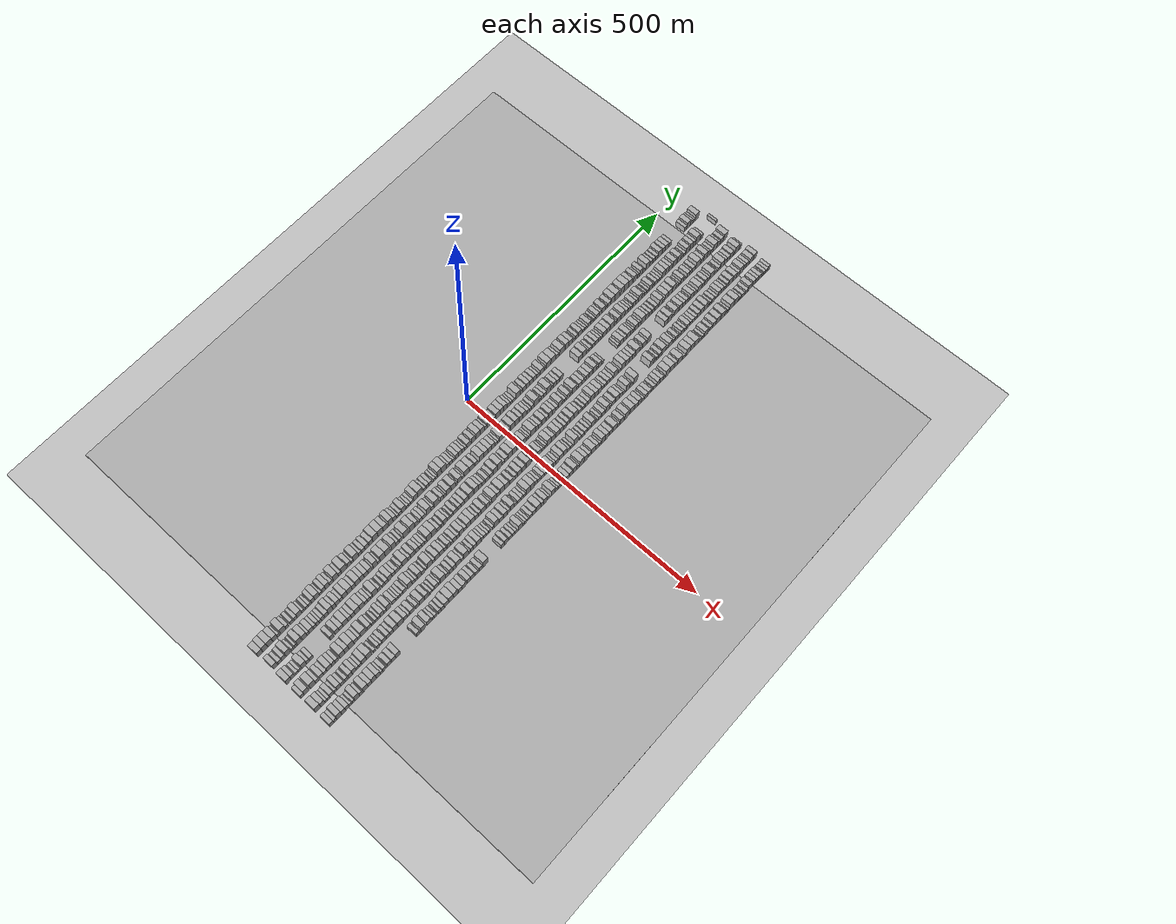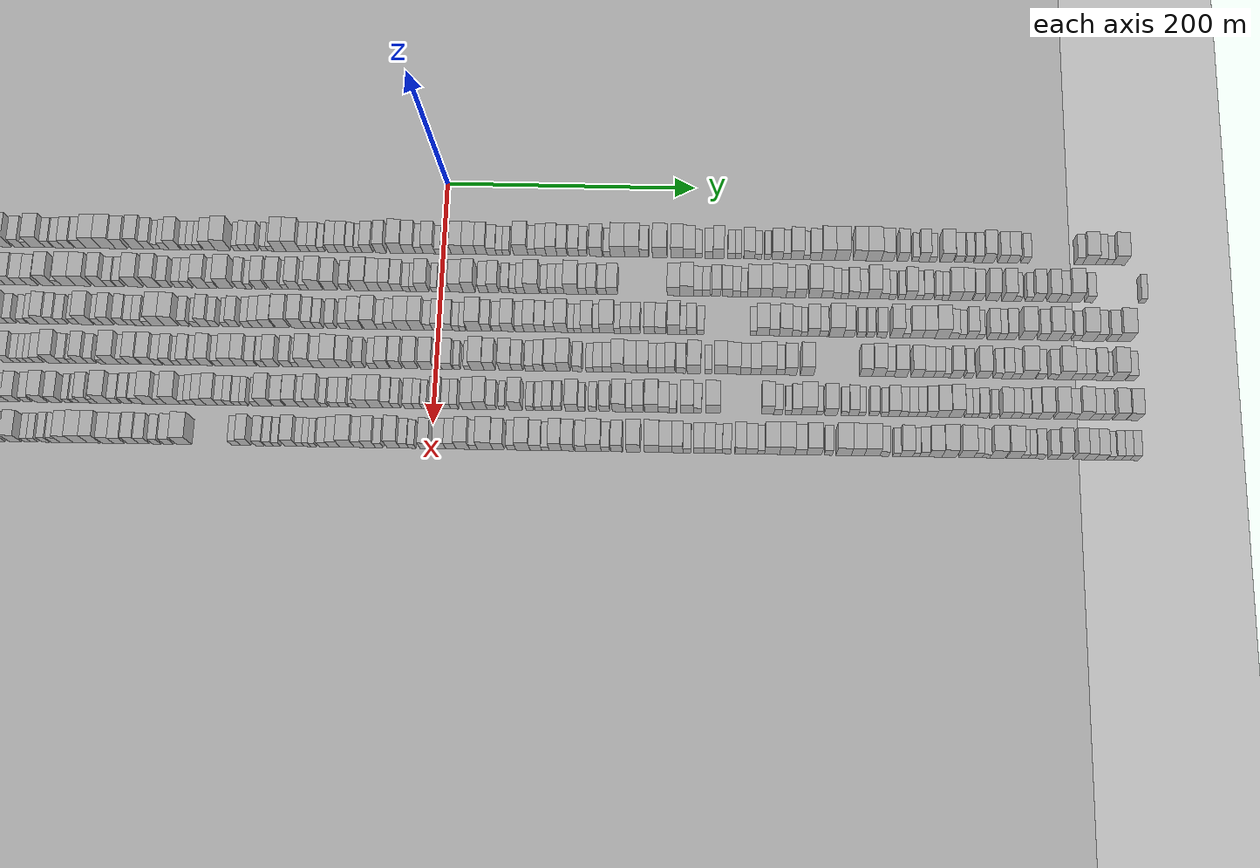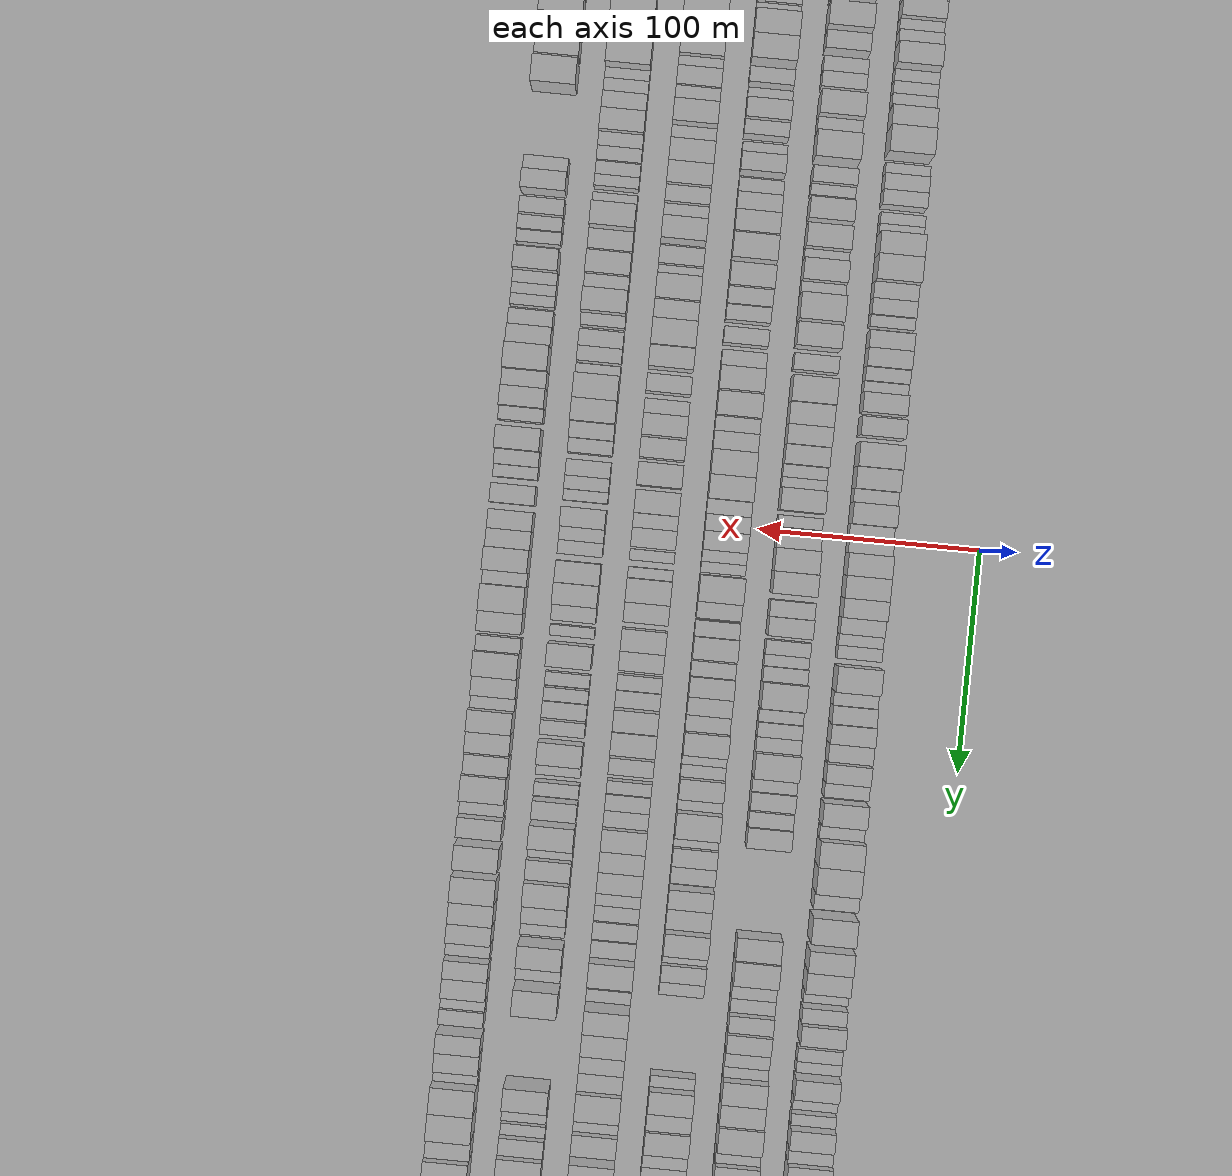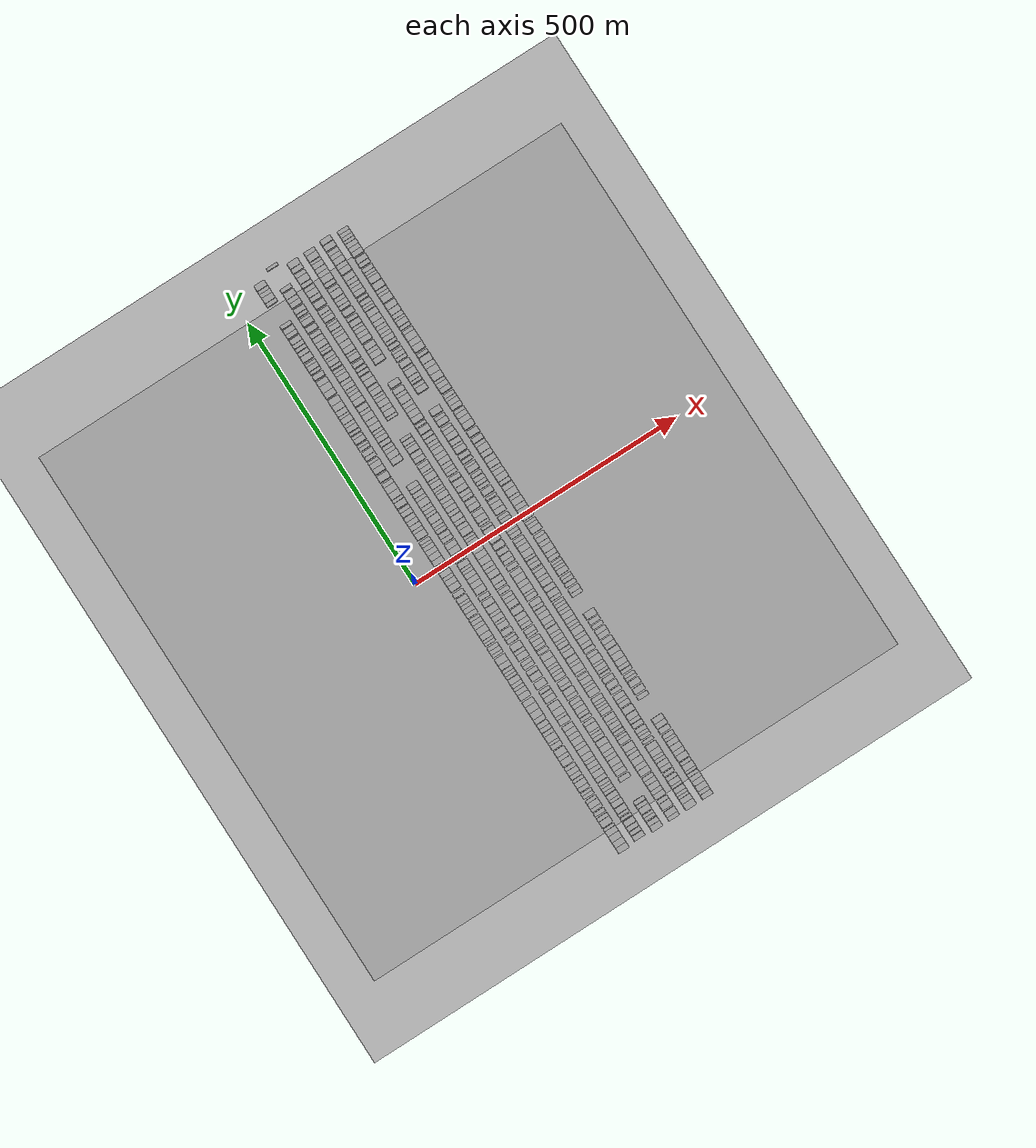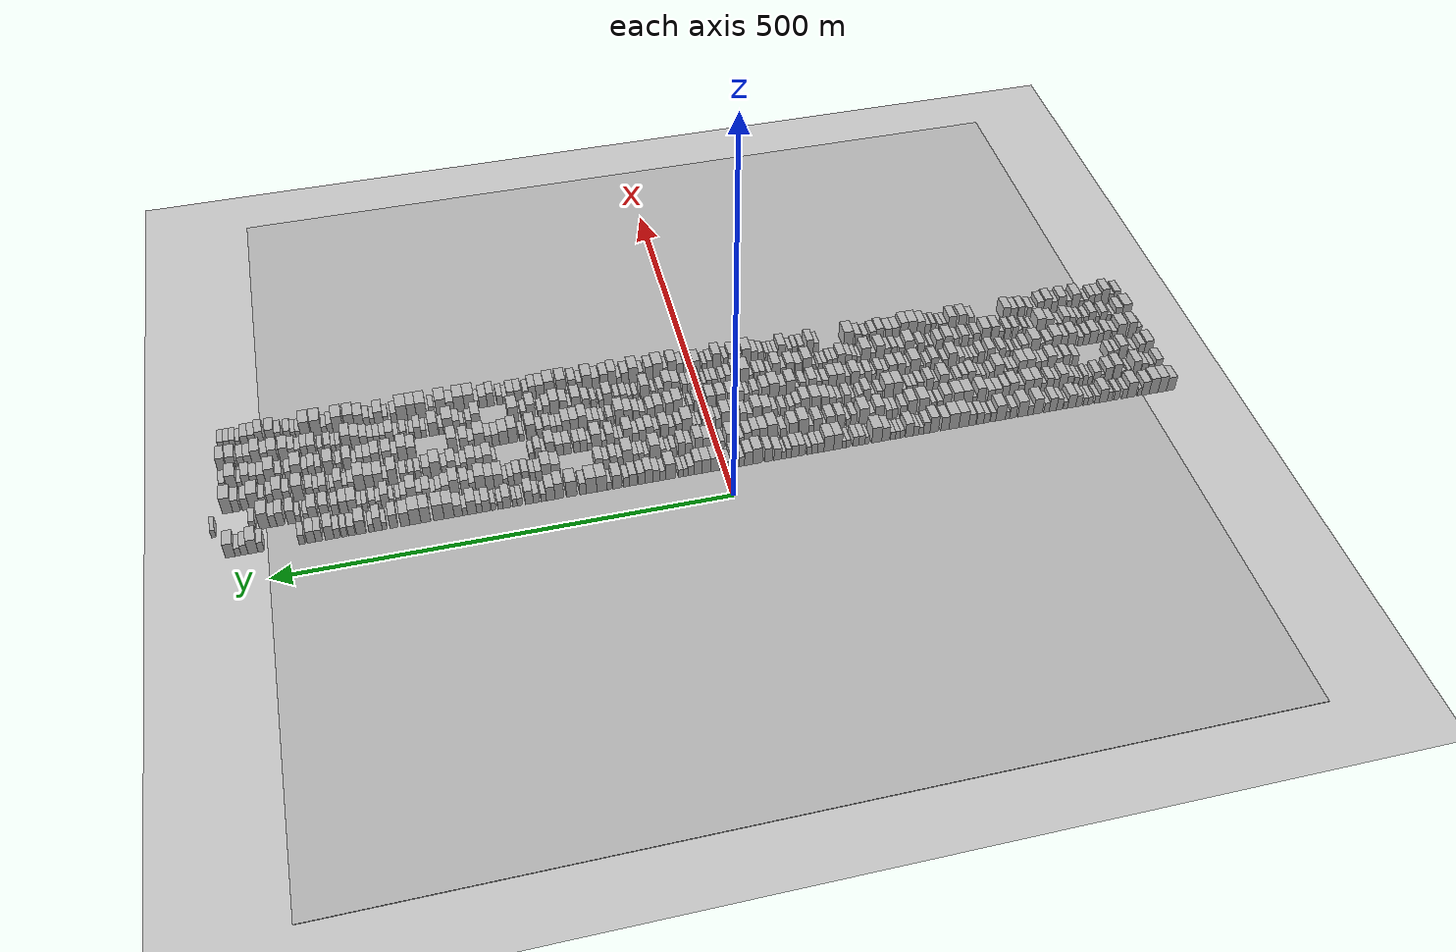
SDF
<?xml version="1.0" encoding="utf-8"?>

<sdf version="1.6">

   <world name="default">

      <gui fullscreen="0">

         <camera name="user_camera">

            <pose>-15 0 4.57585 0 0 0</pose>

            <view_controller>orbit</view_controller>

         </camera>

      </gui>

      <scene>

         <sky>

           <clouds>

             <speed>12</speed>

           </clouds>

         </sky>

         <ambient>0.4 0.4 0.4 1</ambient>

         <background>0.7 0.7 0.7 1</background>

         <shadows>1</shadows>

      </scene>

      <gravity>0 0 -9.8066</gravity>

      <magnetic_field>6e-06 2.3e-05 -4.2e-05</magnetic_field>

      <physics default="0" name="default_physics" type="ode">

         <ode>

            <solver>

               <type>quick</type>

               <iters>10</iters>

               <sor>1.0</sor>

               <use_dynamic_moi_rescaling>0</use_dynamic_moi_rescaling>

            </solver>

            <constraints>

               <cfm>0</cfm>

               <erp>0.2</erp>

               <contact_max_correcting_vel>100</contact_max_correcting_vel>

               <contact_surface_layer>0.001</contact_surface_layer>

            </constraints>

         </ode>

         <max_step_size>0.004</max_step_size>

         <real_time_factor>1</real_time_factor>

         <real_time_update_rate>250</real_time_update_rate>

      </physics>

      <light name="sun" type="directional">

         <cast_shadows>1</cast_shadows>

         <pose>0 0 10 0 0 0</pose>

         <diffuse>0.8 0.8 0.8 1</diffuse>

         <specular>0.2 0.2 0.2 1</specular>

         <attenuation>

            <range>1000</range>

            <constant>0.9</constant>

            <linear>0.01</linear>

            <quadratic>0.001</quadratic>

         </attenuation>

         <direction>-0.5 0.1 -0.9</direction>

      </light>

      <include>

         <name>ground_plane_1</name>

         <uri>model://HANNAS_ground_plane</uri>

         <pose>0 0 0  0 0 0</pose>

      </include>

      <include>

         <name>ground_plane_2</name>

         <uri>model://HANNAS_ground_plane</uri>

         <pose>100 0 0  0 0 0</pose>

      </include>

      <model name="building_1">

         <static>1</static>

         <pose frame="">50.0000 -534.8459 0 0.000000 0.000000 0.000000</pose>

         <link name="link">

            <pose frame="">0 0 10.50 0 0 0</pose>

            <collision name="collision">

               <geometry>

                  <box>

                     <size>20.0000 10.3082 21.0000</size>

                  </box>

               </geometry>

               <max_contacts>10</max_contacts>

               <surface>

                  <contact>

                     <ode/>

                  </contact>

                  <bounce/>

                  <friction>

                     <torsional>

                        <ode/>

                     </torsional>

                     <ode/>

                  </friction>

               </surface>

            </collision>

            <visual name="visual">

               <cast_shadows>0</cast_shadows>

               <geometry>

                  <box>

                     <size>20.0000 10.3082 21.0000</size>

                  </box>

               </geometry>

               <material>

                  <script>

                     <uri>model://HANNAS_wall/materials/scripts</uri>

                     <uri>model://HANNAS_wall/materials/textures</uri>

                     <name>vrc/HANNAS_wall</name>

                  </script>

               </material>

            </visual>

            <self_collide>0</self_collide>

            <enable_wind>0</enable_wind>

            <kinematic>0</kinematic>

         </link>

      </model>

      <model name="building_2">

         <static>1</static>

         <pose frame="">50.0000 -524.3965 0 0.000000 0.000000 0.000000</pose>

         <link name="link">

            <pose frame="">0 0 12.00 0 0 0</pose>

            <collision name="collision">

               <geometry>

                  <box>

                     <size>20.0000 10.5908 24.0000</size>

                  </box>

               </geometry>

               <max_contacts>10</max_contacts>

               <surface>

                  <contact>

                     <ode/>

                  </contact>

                  <bounce/>

                  <friction>

                     <torsional>

                        <ode/>

                     </torsional>

                     <ode/>

                  </friction>

               </surface>

            </collision>

            <visual name="visual">

               <cast_shadows>0</cast_shadows>

               <geometry>

                  <box>

                     <size>20.0000 10.5908 24.0000</size>

                  </box>

               </geometry>

               <material>

                  <script>

                     <uri>model://HANNAS_wall/materials/scripts</uri>

                     <uri>model://HANNAS_wall/materials/textures</uri>

                     <name>vrc/HANNAS_wall</name>

                  </script>

               </material>

            </visual>

            <self_collide>0</self_collide>

            <enable_wind>0</enable_wind>

            <kinematic>0</kinematic>

         </link>

      </model>

      <model name="building_3">

         <static>1</static>

         <pose frame="">50.0000 -513.5059 0 0.000000 0.000000 0.000000</pose>

         <link name="link">

            <pose frame="">0 0 12.00 0 0 0</pose>

            <collision name="collision">

               <geometry>

                  <box>

                     <size>20.0000 11.1904 24.0000</size>

                  </box>

               </geometry>

               <max_contacts>10</max_contacts>

               <surface>

                  <contact>

                     <ode/>

                  </contact>

                  <bounce/>

                  <friction>

                     <torsional>

                        <ode/>

                     </torsional>

                     <ode/>

                  </friction>

               </surface>

            </collision>

            <visual name="visual">

               <cast_shadows>0</cast_shadows>

               <geometry>

                  <box>

                     <size>20.0000 11.1904 24.0000</size>

                  </box>

               </geometry>

               <material>

                  <script>

                     <uri>model://HANNAS_wall/materials/scripts</uri>

                     <uri>model://HANNAS_wall/materials/textures</uri>

                     <name>vrc/HANNAS_wall</name>

                  </script>

               </material>

            </visual>

            <self_collide>0</self_collide>

            <enable_wind>0</enable_wind>

            <kinematic>0</kinematic>

         </link>

      </model>

      <model name="building_4">

         <static>1</static>

         <pose frame="">50.0000 -502.9816 0 0.000000 0.000000 0.000000</pose>

         <link name="link">

            <pose frame="">0 0 10.50 0 0 0</pose>

            <collision name="collision">

               <geometry>

                  <box>

                     <size>20.0000 9.8581 21.0000</size>

                  </box>

               </geometry>

               <max_contacts>10</max_contacts>

               <surface>

                  <contact>

                     <ode/>

                  </contact>

                  <bounce/>

                  <friction>

                     <torsional>

                        <ode/>

                     </torsional>

                     <ode/>

                  </friction>

               </surface>

            </collision>

            <visual name="visual">

               <cast_shadows>0</cast_shadows>

               <geometry>

                  <box>

                     <size>20.0000 9.8581 21.0000</size>

                  </box>

               </geometry>

               <material>

                  <script>

                     <uri>model://HANNAS_wall/materials/scripts</uri>

                     <uri>model://HANNAS_wall/materials/textures</uri>

                     <name>vrc/HANNAS_wall</name>

                  </script>

               </material>

            </visual>

            <self_collide>0</self_collide>

            <enable_wind>0</enable_wind>

            <kinematic>0</kinematic>

         </link>

      </model>

      <model name="building_5">

         <static>1</static>

         <pose frame="">50.0000 -495.6456 0 0.000000 0.000000 0.000000</pose>

         <link name="link">

            <pose frame="">0 0 6.00 0 0 0</pose>

            <collision name="collision">

               <geometry>

                  <box>

                     <size>20.0000 4.8140 12.0000</size>

                  </box>

               </geometry>

               <max_contacts>10</max_contacts>

               <surface>

                  <contact>

                     <ode/>

                  </contact>

                  <bounce/>

                  <friction>

                     <torsional>

                        <ode/>

                     </torsional>

                     <ode/>

                  </friction>

               </surface>

            </collision>

            <visual name="visual">

               <cast_shadows>0</cast_shadows>

               <geometry>

                  <box>

                     <size>20.0000 4.8140 12.0000</size>

                  </box>

               </geometry>

               <material>

                  <script>

                     <uri>model://HANNAS_wall/materials/scripts</uri>

                     <uri>model://HANNAS_wall/materials/textures</uri>

                     <name>vrc/HANNAS_wall</name>

                  </script>

               </material>

            </visual>

            <self_collide>0</self_collide>

            <enable_wind>0</enable_wind>

            <kinematic>0</kinematic>

         </link>

      </model>

      <model name="building_6">

         <static>1</static>

         <pose frame="">50.0000 -485.6218 0 0.000000 0.000000 0.000000</pose>

         <link name="link">

            <pose frame="">0 0 12.00 0 0 0</pose>

            <collision name="collision">

               <geometry>

                  <box>

                     <size>20.0000 11.2336 24.0000</size>

                  </box>

               </geometry>

               <max_contacts>10</max_contacts>

               <surface>

                  <contact>

                     <ode/>

                  </contact>

                  <bounce/>

                  <friction>

                     <torsional>

                        <ode/>

                     </torsional>

                     <ode/>

                  </friction>

               </surface>

            </collision>

            <visual name="visual">

               <cast_shadows>0</cast_shadows>

               <geometry>

                  <box>

                     <size>20.0000 11.2336 24.0000</size>

                  </box>

               </geometry>

               <material>

                  <script>

                     <uri>model://HANNAS_wall/materials/scripts</uri>

                     <uri>model://HANNAS_wall/materials/textures</uri>

                     <name>vrc/HANNAS_wall</name>

                  </script>

               </material>

            </visual>

            <self_collide>0</self_collide>

            <enable_wind>0</enable_wind>

            <kinematic>0</kinematic>

         </link>

      </model>

      <model name="building_7">

         <static>1</static>

         <pose frame="">50.0000 -476.7481 0 0.000000 0.000000 0.000000</pose>

         <link name="link">

            <pose frame="">0 0 7.50 0 0 0</pose>

            <collision name="collision">

               <geometry>

                  <box>

                     <size>20.0000 6.5139 15.0000</size>

                  </box>

               </geometry>

               <max_contacts>10</max_contacts>

               <surface>

                  <contact>

                     <ode/>

                  </contact>

                  <bounce/>

                  <friction>

                     <torsional>

                        <ode/>

                     </torsional>

                     <ode/>

                  </friction>

               </surface>

            </collision>

            <visual name="visual">

               <cast_shadows>0</cast_shadows>

               <geometry>

                  <box>

                     <size>20.0000 6.5139 15.0000</size>

                  </box>

               </geometry>

               <material>

                  <script>

                     <uri>model://HANNAS_wall/materials/scripts</uri>

                     <uri>model://HANNAS_wall/materials/textures</uri>

                     <name>vrc/HANNAS_wall</name>

                  </script>

               </material>

            </visual>

            <self_collide>0</self_collide>

            <enable_wind>0</enable_wind>

            <kinematic>0</kinematic>

         </link>

      </model>

      <model name="building_8">

         <static>1</static>

         <pose frame="">50.0000 -467.0792 0 0.000000 0.000000 0.000000</pose>

         <link name="link">

            <pose frame="">0 0 7.50 0 0 0</pose>

            <collision name="collision">

               <geometry>

                  <box>

                     <size>20.0000 6.8238 15.0000</size>

                  </box>

               </geometry>

               <max_contacts>10</max_contacts>

               <surface>

                  <contact>

                     <ode/>

                  </contact>

                  <bounce/>

                  <friction>

                     <torsional>

                        <ode/>

                     </torsional>

                     <ode/>

                  </friction>

               </surface>

            </collision>

            <visual name="visual">

               <cast_shadows>0</cast_shadows>

               <geometry>

                  <box>

                     <size>20.0000 6.8238 15.0000</size>

                  </box>

               </geometry>

               <material>

                  <script>

                     <uri>model://HANNAS_wall/materials/scripts</uri>

                     <uri>model://HANNAS_wall/materials/textures</uri>

                     <name>vrc/HANNAS_wall</name>

                  </script>

               </material>

            </visual>

            <self_collide>0</self_collide>

            <enable_wind>0</enable_wind>

            <kinematic>0</kinematic>

         </link>

      </model>

      <model name="building_9">

         <static>1</static>

         <pose frame="">50.0000 -458.6528 0 0.000000 0.000000 0.000000</pose>

         <link name="link">

            <pose frame="">0 0 7.50 0 0 0</pose>

            <collision name="collision">

               <geometry>

                  <box>

                     <size>20.0000 6.0291 15.0000</size>

                  </box>

               </geometry>

               <max_contacts>10</max_contacts>

               <surface>

                  <contact>

                     <ode/>

                  </contact>

                  <bounce/>

                  <friction>

                     <torsional>

                        <ode/>

                     </torsional>

                     <ode/>

                  </friction>

               </surface>

            </collision>

            <visual name="visual">

               <cast_shadows>0</cast_shadows>

               <geometry>

                  <box>

                     <size>20.0000 6.0291 15.0000</size>

                  </box>

               </geometry>

               <material>

                  <script>

                     <uri>model://HANNAS_wall/materials/scripts</uri>

                     <uri>model://HANNAS_wall/materials/textures</uri>

                     <name>vrc/HANNAS_wall</name>

                  </script>

               </material>

            </visual>

            <self_collide>0</self_collide>

            <enable_wind>0</enable_wind>

            <kinematic>0</kinematic>

         </link>

      </model>

      <model name="building_10">

         <static>1</static>

         <pose frame="">50.0000 -450.6121 0 0.000000 0.000000 0.000000</pose>

         <link name="link">

            <pose frame="">0 0 10.50 0 0 0</pose>

            <collision name="collision">

               <geometry>

                  <box>

                     <size>20.0000 10.0524 21.0000</size>

                  </box>

               </geometry>

               <max_contacts>10</max_contacts>

               <surface>

                  <contact>

                     <ode/>

                  </contact>

                  <bounce/>

                  <friction>

                     <torsional>

                        <ode/>

                     </torsional>

                     <ode/>

                  </friction>

               </surface>

            </collision>

            <visual name="visual">

               <cast_shadows>0</cast_shadows>

               <geometry>

                  <box>

                     <size>20.0000 10.0524 21.0000</size>

                  </box>

               </geometry>

               <material>

                  <script>

                     <uri>model://HANNAS_wall/materials/scripts</uri>

                     <uri>model://HANNAS_wall/materials/textures</uri>

                     <name>vrc/HANNAS_wall</name>

                  </script>

               </material>

            </visual>

            <self_collide>0</self_collide>

            <enable_wind>0</enable_wind>

            <kinematic>0</kinematic>

         </link>

      </model>

      <model name="building_11">

         <static>1</static>

         <pose frame="">50.0000 -442.7862 0 0.000000 0.000000 0.000000</pose>

         <link name="link">

            <pose frame="">0 0 6.00 0 0 0</pose>

            <collision name="collision">

               <geometry>

                  <box>

                     <size>20.0000 5.5993 12.0000</size>

                  </box>

               </geometry>

               <max_contacts>10</max_contacts>

               <surface>

                  <contact>

                     <ode/>

                  </contact>

                  <bounce/>

                  <friction>

                     <torsional>

                        <ode/>

                     </torsional>

                     <ode/>

                  </friction>

               </surface>

            </collision>

            <visual name="visual">

               <cast_shadows>0</cast_shadows>

               <geometry>

                  <box>

                     <size>20.0000 5.5993 12.0000</size>

                  </box>

               </geometry>

               <material>

                  <script>

                     <uri>model://HANNAS_wall/materials/scripts</uri>

                     <uri>model://HANNAS_wall/materials/textures</uri>

                     <name>vrc/HANNAS_wall</name>

                  </script>

               </material>

            </visual>

            <self_collide>0</self_collide>

            <enable_wind>0</enable_wind>

            <kinematic>0</kinematic>

         </link>

      </model>

      <model name="building_12">

         <static>1</static>

         <pose frame="">50.0000 -434.0810 0 0.000000 0.000000 0.000000</pose>

         <link name="link">

            <pose frame="">0 0 6.00 0 0 0</pose>

            <collision name="collision">

               <geometry>

                  <box>

                     <size>20.0000 5.8111 12.0000</size>

                  </box>

               </geometry>

               <max_contacts>10</max_contacts>

               <surface>

                  <contact>

                     <ode/>

                  </contact>

                  <bounce/>

                  <friction>

                     <torsional>

                        <ode/>

                     </torsional>

                     <ode/>

                  </friction>

               </surface>

            </collision>

            <visual name="visual">

               <cast_shadows>0</cast_shadows>

               <geometry>

                  <box>

                     <size>20.0000 5.8111 12.0000</size>

                  </box>

               </geometry>

               <material>

                  <script>

                     <uri>model://HANNAS_wall/materials/scripts</uri>

                     <uri>model://HANNAS_wall/materials/textures</uri>

                     <name>vrc/HANNAS_wall</name>

                  </script>

               </material>

            </visual>

            <self_collide>0</self_collide>

            <enable_wind>0</enable_wind>

            <kinematic>0</kinematic>

         </link>

      </model>

      <model name="building_13">

         <static>1</static>

         <pose frame="">50.0000 -428.5578 0 0.000000 0.000000 0.000000</pose>

         <link name="link">

            <pose frame="">0 0 6.00 0 0 0</pose>

            <collision name="collision">

               <geometry>

                  <box>

                     <size>20.0000 5.2352 12.0000</size>

                  </box>

               </geometry>

               <max_contacts>10</max_contacts>

               <surface>

                  <contact>

                     <ode/>

                  </contact>

                  <bounce/>

                  <friction>

                     <torsional>

                        <ode/>

                     </torsional>

                     <ode/>

                  </friction>

               </surface>

            </collision>

            <visual name="visual">

               <cast_shadows>0</cast_shadows>

               <geometry>

                  <box>

                     <size>20.0000 5.2352 12.0000</size>

                  </box>

               </geometry>

               <material>

                  <script>

                     <uri>model://HANNAS_wall/materials/scripts</uri>

                     <uri>model://HANNAS_wall/materials/textures</uri>

                     <name>vrc/HANNAS_wall</name>

                  </script>

               </material>

            </visual>

            <self_collide>0</self_collide>

            <enable_wind>0</enable_wind>

            <kinematic>0</kinematic>

         </link>

      </model>

      <model name="building_14">

         <static>1</static>

         <pose frame="">50.0000 -420.2583 0 0.000000 0.000000 0.000000</pose>

         <link name="link">

            <pose frame="">0 0 9.00 0 0 0</pose>

            <collision name="collision">

               <geometry>

                  <box>

                     <size>20.0000 7.3639 18.0000</size>

                  </box>

               </geometry>

               <max_contacts>10</max_contacts>

               <surface>

                  <contact>

                     <ode/>

                  </contact>

                  <bounce/>

                  <friction>

                     <torsional>

                        <ode/>

                     </torsional>

                     <ode/>

                  </friction>

               </surface>

            </collision>

            <visual name="visual">

               <cast_shadows>0</cast_shadows>

               <geometry>

                  <box>

                     <size>20.0000 7.3639 18.0000</size>

                  </box>

               </geometry>

               <material>

                  <script>

                     <uri>model://HANNAS_wall/materials/scripts</uri>

                     <uri>model://HANNAS_wall/materials/textures</uri>

                     <name>vrc/HANNAS_wall</name>

                  </script>

               </material>

            </visual>

            <self_collide>0</self_collide>

            <enable_wind>0</enable_wind>

            <kinematic>0</kinematic>

         </link>

      </model>

      <model name="building_15">

         <static>1</static>

         <pose frame="">50.0000 -411.5845 0 0.000000 0.000000 0.000000</pose>

         <link name="link">

            <pose frame="">0 0 10.50 0 0 0</pose>

            <collision name="collision">

               <geometry>

                  <box>

                     <size>20.0000 9.9836 21.0000</size>

                  </box>

               </geometry>

               <max_contacts>10</max_contacts>

               <surface>

                  <contact>

                     <ode/>

                  </contact>

                  <bounce/>

                  <friction>

                     <torsional>

                        <ode/>

                     </torsional>

                     <ode/>

                  </friction>

               </surface>

            </collision>

            <visual name="visual">

               <cast_shadows>0</cast_shadows>

               <geometry>

                  <box>

                     <size>20.0000 9.9836 21.0000</size>

                  </box>

               </geometry>

               <material>

                  <script>

                     <uri>model://HANNAS_wall/materials/scripts</uri>

                     <uri>model://HANNAS_wall/materials/textures</uri>

                     <name>vrc/HANNAS_wall</name>

                  </script>

               </material>

            </visual>

            <self_collide>0</self_collide>

            <enable_wind>0</enable_wind>

            <kinematic>0</kinematic>

         </link>

      </model>

      <model name="building_16">

         <static>1</static>

         <pose frame="">50.0000 -403.9259 0 0.000000 0.000000 0.000000</pose>

         <link name="link">

            <pose frame="">0 0 6.00 0 0 0</pose>

            <collision name="collision">

               <geometry>

                  <box>

                     <size>20.0000 5.3337 12.0000</size>

                  </box>

               </geometry>

               <max_contacts>10</max_contacts>

               <surface>

                  <contact>

                     <ode/>

                  </contact>

                  <bounce/>

                  <friction>

                     <torsional>

                        <ode/>

                     </torsional>

                     <ode/>

                  </friction>

               </surface>

            </collision>

            <visual name="visual">

               <cast_shadows>0</cast_shadows>

               <geometry>

                  <box>

                     <size>20.0000 5.3337 12.0000</size>

                  </box>

               </geometry>

               <material>

                  <script>

                     <uri>model://HANNAS_wall/materials/scripts</uri>

                     <uri>model://HANNAS_wall/materials/textures</uri>

                     <name>vrc/HANNAS_wall</name>

                  </script>

               </material>

            </visual>

            <self_collide>0</self_collide>

            <enable_wind>0</enable_wind>

            <kinematic>0</kinematic>

         </link>

      </model>

      <model name="building_17">

         <static>1</static>

         <pose frame="">50.0000 -396.5449 0 0.000000 0.000000 0.000000</pose>

         <link name="link">

            <pose frame="">0 0 9.00 0 0 0</pose>

            <collision name="collision">

               <geometry>

                  <box>

                     <size>20.0000 7.4283 18.0000</size>

                  </box>

               </geometry>

               <max_contacts>10</max_contacts>

               <surface>

                  <contact>

                     <ode/>

                  </contact>

                  <bounce/>

                  <friction>

                     <torsional>

                        <ode/>

                     </torsional>

                     <ode/>

                  </friction>

               </surface>

            </collision>

            <visual name="visual">

               <cast_shadows>0</cast_shadows>

               <geometry>

                  <box>

                     <size>20.0000 7.4283 18.0000</size>

                  </box>

               </geometry>

               <material>

                  <script>

                     <uri>model://HANNAS_wall/materials/scripts</uri>

                     <uri>model://HANNAS_wall/materials/textures</uri>

                     <name>vrc/HANNAS_wall</name>

                  </script>

               </material>

            </visual>

            <self_collide>0</self_collide>

            <enable_wind>0</enable_wind>

            <kinematic>0</kinematic>

         </link>

      </model>

      <model name="building_18">

         <static>1</static>

         <pose frame="">50.0000 -388.3783 0 0.000000 0.000000 0.000000</pose>

         <link name="link">

            <pose frame="">0 0 10.50 0 0 0</pose>

            <collision name="collision">

               <geometry>

                  <box>

                     <size>20.0000 8.9048 21.0000</size>

                  </box>

               </geometry>

               <max_contacts>10</max_contacts>

               <surface>

                  <contact>

                     <ode/>

                  </contact>

                  <bounce/>

                  <friction>

                     <torsional>

                        <ode/>

                     </torsional>

                     <ode/>

                  </friction>

               </surface>

            </collision>

            <visual name="visual">

               <cast_shadows>0</cast_shadows>

               <geometry>

                  <box>

                     <size>20.0000 8.9048 21.0000</size>

                  </box>

               </geometry>

               <material>

                  <script>

                     <uri>model://HANNAS_wall/materials/scripts</uri>

                     <uri>model://HANNAS_wall/materials/textures</uri>

                     <name>vrc/HANNAS_wall</name>

                  </script>

               </material>

            </visual>

            <self_collide>0</self_collide>

            <enable_wind>0</enable_wind>

            <kinematic>0</kinematic>

         </link>

      </model>

      <model name="building_19">

         <static>1</static>

         <pose frame="">50.0000 -380.6509 0 0.000000 0.000000 0.000000</pose>

         <link name="link">

            <pose frame="">0 0 7.50 0 0 0</pose>

            <collision name="collision">

               <geometry>

                  <box>

                     <size>20.0000 6.5501 15.0000</size>

                  </box>

               </geometry>

               <max_contacts>10</max_contacts>

               <surface>

                  <contact>

                     <ode/>

                  </contact>

                  <bounce/>

                  <friction>

                     <torsional>

                        <ode/>

                     </torsional>

                     <ode/>

                  </friction>

               </surface>

            </collision>

            <visual name="visual">

               <cast_shadows>0</cast_shadows>

               <geometry>

                  <box>

                     <size>20.0000 6.5501 15.0000</size>

                  </box>

               </geometry>

               <material>

                  <script>

                     <uri>model://HANNAS_wall/materials/scripts</uri>

                     <uri>model://HANNAS_wall/materials/textures</uri>

                     <name>vrc/HANNAS_wall</name>

                  </script>

               </material>

            </visual>

            <self_collide>0</self_collide>

            <enable_wind>0</enable_wind>

            <kinematic>0</kinematic>

         </link>

      </model>

      <model name="building_20">

         <static>1</static>

         <pose frame="">50.0000 -369.8633 0 0.000000 0.000000 0.000000</pose>

         <link name="link">

            <pose frame="">0 0 12.00 0 0 0</pose>

            <collision name="collision">

               <geometry>

                  <box>

                     <size>20.0000 11.0251 24.0000</size>

                  </box>

               </geometry>

               <max_contacts>10</max_contacts>

               <surface>

                  <contact>

                     <ode/>

                  </contact>

                  <bounce/>

                  <friction>

                     <torsional>

                        <ode/>

                     </torsional>

                     <ode/>

                  </friction>

               </surface>

            </collision>

            <visual name="visual">

               <cast_shadows>0</cast_shadows>

               <geometry>

                  <box>

                     <size>20.0000 11.0251 24.0000</size>

                  </box>

               </geometry>

               <material>

                  <script>

                     <uri>model://HANNAS_wall/materials/scripts</uri>

                     <uri>model://HANNAS_wall/materials/textures</uri>

                     <name>vrc/HANNAS_wall</name>

                  </script>

               </material>

            </visual>

            <self_collide>0</self_collide>

            <enable_wind>0</enable_wind>

            <kinematic>0</kinematic>

         </link>

      </model>

      <model name="building_21">

         <static>1</static>

         <pose frame="">50.0000 -360.8925 0 0.000000 0.000000 0.000000</pose>

         <link name="link">

            <pose frame="">0 0 7.50 0 0 0</pose>

            <collision name="collision">

               <geometry>

                  <box>

                     <size>20.0000 6.9164 15.0000</size>

                  </box>

               </geometry>

               <max_contacts>10</max_contacts>

               <surface>

                  <contact>

                     <ode/>

                  </contact>

                  <bounce/>

                  <friction>

                     <torsional>

                        <ode/>

                     </torsional>

                     <ode/>

                  </friction>

               </surface>

            </collision>

            <visual name="visual">

               <cast_shadows>0</cast_shadows>

               <geometry>

                  <box>

                     <size>20.0000 6.9164 15.0000</size>

                  </box>

               </geometry>

               <material>

                  <script>

                     <uri>model://HANNAS_wall/materials/scripts</uri>

                     <uri>model://HANNAS_wall/materials/textures</uri>

                     <name>vrc/HANNAS_wall</name>

                  </script>

               </material>

            </visual>

            <self_collide>0</self_collide>

            <enable_wind>0</enable_wind>

            <kinematic>0</kinematic>

         </link>

      </model>

      <model name="building_22">

         <static>1</static>

         <pose frame="">50.0000 -351.5226 0 0.000000 0.000000 0.000000</pose>

         <link name="link">

            <pose frame="">0 0 12.00 0 0 0</pose>

            <collision name="collision">

               <geometry>

                  <box>

                     <size>20.0000 11.8233 24.0000</size>

                  </box>

               </geometry>

               <max_contacts>10</max_contacts>

               <surface>

                  <contact>

                     <ode/>

                  </contact>

                  <bounce/>

                  <friction>

                     <torsional>

                        <ode/>

                     </torsional>

                     <ode/>

                  </friction>

               </surface>

            </collision>

            <visual name="visual">

               <cast_shadows>0</cast_shadows>

               <geometry>

                  <box>

                     <size>20.0000 11.8233 24.0000</size>

                  </box>

               </geometry>

               <material>

                  <script>

                     <uri>model://HANNAS_wall/materials/scripts</uri>

                     <uri>model://HANNAS_wall/materials/textures</uri>

                     <name>vrc/HANNAS_wall</name>

                  </script>

               </material>

            </visual>

            <self_collide>0</self_collide>

            <enable_wind>0</enable_wind>

            <kinematic>0</kinematic>

         </link>

      </model>

      <model name="building_23">

         <static>1</static>

         <pose frame="">50.0000 -339.5684 0 0.000000 0.000000 0.000000</pose>

         <link name="link">

            <pose frame="">0 0 9.00 0 0 0</pose>

            <collision name="collision">

               <geometry>

                  <box>

                     <size>20.0000 8.0851 18.0000</size>

                  </box>

               </geometry>

               <max_contacts>10</max_contacts>

               <surface>

                  <contact>

                     <ode/>

                  </contact>

                  <bounce/>

                  <friction>

                     <torsional>

                        <ode/>

                     </torsional>

                     <ode/>

                  </friction>

               </surface>

            </collision>

            <visual name="visual">

               <cast_shadows>0</cast_shadows>

               <geometry>

                  <box>

                     <size>20.0000 8.0851 18.0000</size>

                  </box>

               </geometry>

               <material>

                  <script>

                     <uri>model://HANNAS_wall/materials/scripts</uri>

                     <uri>model://HANNAS_wall/materials/textures</uri>

                     <name>vrc/HANNAS_wall</name>

                  </script>

               </material>

            </visual>

            <self_collide>0</self_collide>

            <enable_wind>0</enable_wind>

            <kinematic>0</kinematic>

         </link>

      </model>

      <model name="building_24">

         <static>1</static>

         <pose frame="">50.0000 -332.9905 0 0.000000 0.000000 0.000000</pose>

         <link name="link">

            <pose frame="">0 0 6.00 0 0 0</pose>

            <collision name="collision">

               <geometry>

                  <box>

                     <size>20.0000 5.0706 12.0000</size>

                  </box>

               </geometry>

               <max_contacts>10</max_contacts>

               <surface>

                  <contact>

                     <ode/>

                  </contact>

                  <bounce/>

                  <friction>

                     <torsional>

                        <ode/>

                     </torsional>

                     <ode/>

                  </friction>

               </surface>

            </collision>

            <visual name="visual">

               <cast_shadows>0</cast_shadows>

               <geometry>

                  <box>

                     <size>20.0000 5.0706 12.0000</size>

                  </box>

               </geometry>

               <material>

                  <script>

                     <uri>model://HANNAS_wall/materials/scripts</uri>

                     <uri>model://HANNAS_wall/materials/textures</uri>

                     <name>vrc/HANNAS_wall</name>

                  </script>

               </material>

            </visual>

            <self_collide>0</self_collide>

            <enable_wind>0</enable_wind>

            <kinematic>0</kinematic>

         </link>

      </model>

      <model name="building_25">

         <static>1</static>

         <pose frame="">50.0000 -324.6397 0 0.000000 0.000000 0.000000</pose>

         <link name="link">

            <pose frame="">0 0 12.00 0 0 0</pose>

            <collision name="collision">

               <geometry>

                  <box>

                     <size>20.0000 11.6311 24.0000</size>

                  </box>

               </geometry>

               <max_contacts>10</max_contacts>

               <surface>

                  <contact>

                     <ode/>

                  </contact>

                  <bounce/>

                  <friction>

                     <torsional>

                        <ode/>

                     </torsional>

                     <ode/>

                  </friction>

               </surface>

            </collision>

            <visual name="visual">

               <cast_shadows>0</cast_shadows>

               <geometry>

                  <box>

                     <size>20.0000 11.6311 24.0000</size>

                  </box>

               </geometry>

               <material>

                  <script>

                     <uri>model://HANNAS_wall/materials/scripts</uri>

                     <uri>model://HANNAS_wall/materials/textures</uri>

                     <name>vrc/HANNAS_wall</name>

                  </script>

               </material>

            </visual>

            <self_collide>0</self_collide>

            <enable_wind>0</enable_wind>

            <kinematic>0</kinematic>

         </link>

      </model>

      <model name="building_26">

         <static>1</static>

         <pose frame="">50.0000 -315.5537 0 0.000000 0.000000 0.000000</pose>

         <link name="link">

            <pose frame="">0 0 7.50 0 0 0</pose>

            <collision name="collision">

               <geometry>

                  <box>

                     <size>20.0000 6.5410 15.0000</size>

                  </box>

               </geometry>

               <max_contacts>10</max_contacts>

               <surface>

                  <contact>

                     <ode/>

                  </contact>

                  <bounce/>

                  <friction>

                     <torsional>

                        <ode/>

                     </torsional>

                     <ode/>

                  </friction>

               </surface>

            </collision>

            <visual name="visual">

               <cast_shadows>0</cast_shadows>

               <geometry>

                  <box>

                     <size>20.0000 6.5410 15.0000</size>

                  </box>

               </geometry>

               <material>

                  <script>

                     <uri>model://HANNAS_wall/materials/scripts</uri>

                     <uri>model://HANNAS_wall/materials/textures</uri>

                     <name>vrc/HANNAS_wall</name>

                  </script>

               </material>

            </visual>

            <self_collide>0</self_collide>

            <enable_wind>0</enable_wind>

            <kinematic>0</kinematic>

         </link>

      </model>

      <model name="building_27">

         <static>1</static>

         <pose frame="">50.0000 -307.6227 0 0.000000 0.000000 0.000000</pose>

         <link name="link">

            <pose frame="">0 0 7.50 0 0 0</pose>

            <collision name="collision">

               <geometry>

                  <box>

                     <size>20.0000 7.3210 15.0000</size>

                  </box>

               </geometry>

               <max_contacts>10</max_contacts>

               <surface>

                  <contact>

                     <ode/>

                  </contact>

                  <bounce/>

                  <friction>

                     <torsional>

                        <ode/>

                     </torsional>

                     <ode/>

                  </friction>

               </surface>

            </collision>

            <visual name="visual">

               <cast_shadows>0</cast_shadows>

               <geometry>

                  <box>

                     <size>20.0000 7.3210 15.0000</size>

                  </box>

               </geometry>

               <material>

                  <script>

                     <uri>model://HANNAS_wall/materials/scripts</uri>

                     <uri>model://HANNAS_wall/materials/textures</uri>

                     <name>vrc/HANNAS_wall</name>

                  </script>

               </material>

            </visual>

            <self_collide>0</self_collide>

            <enable_wind>0</enable_wind>

            <kinematic>0</kinematic>

         </link>

      </model>

      <model name="building_28">

         <static>1</static>

         <pose frame="">50.0000 -299.7302 0 0.000000 0.000000 0.000000</pose>

         <link name="link">

            <pose frame="">0 0 9.00 0 0 0</pose>

            <collision name="collision">

               <geometry>

                  <box>

                     <size>20.0000 8.4641 18.0000</size>

                  </box>

               </geometry>

               <max_contacts>10</max_contacts>

               <surface>

                  <contact>

                     <ode/>

                  </contact>

                  <bounce/>

                  <friction>

                     <torsional>

                        <ode/>

                     </torsional>

                     <ode/>

                  </friction>

               </surface>

            </collision>

            <visual name="visual">

               <cast_shadows>0</cast_shadows>

               <geometry>

                  <box>

                     <size>20.0000 8.4641 18.0000</size>

                  </box>

               </geometry>

               <material>

                  <script>

                     <uri>model://HANNAS_wall/materials/scripts</uri>

                     <uri>model://HANNAS_wall/materials/textures</uri>

                     <name>vrc/HANNAS_wall</name>

                  </script>

               </material>

            </visual>

            <self_collide>0</self_collide>

            <enable_wind>0</enable_wind>

            <kinematic>0</kinematic>

         </link>

      </model>

      <model name="building_29">

         <static>1</static>

         <pose frame="">50.0000 -290.2057 0 0.000000 0.000000 0.000000</pose>

         <link name="link">

            <pose frame="">0 0 9.00 0 0 0</pose>

            <collision name="collision">

               <geometry>

                  <box>

                     <size>20.0000 8.5849 18.0000</size>

                  </box>

               </geometry>

               <max_contacts>10</max_contacts>

               <surface>

                  <contact>

                     <ode/>

                  </contact>

                  <bounce/>

                  <friction>

                     <torsional>

                        <ode/>

                     </torsional>

                     <ode/>

                  </friction>

               </surface>

            </collision>

            <visual name="visual">

               <cast_shadows>0</cast_shadows>

               <geometry>

                  <box>

                     <size>20.0000 8.5849 18.0000</size>

                  </box>

               </geometry>

               <material>

                  <script>

                     <uri>model://HANNAS_wall/materials/scripts</uri>

                     <uri>model://HANNAS_wall/materials/textures</uri>

                     <name>vrc/HANNAS_wall</name>

                  </script>

               </material>

            </visual>

            <self_collide>0</self_collide>

            <enable_wind>0</enable_wind>

            <kinematic>0</kinematic>

         </link>

      </model>

      <model name="building_30">

         <static>1</static>

         <pose frame="">50.0000 -280.0788 0 0.000000 0.000000 0.000000</pose>

         <link name="link">

            <pose frame="">0 0 12.00 0 0 0</pose>

            <collision name="collision">

               <geometry>

                  <box>

                     <size>20.0000 11.6689 24.0000</size>

                  </box>

               </geometry>

               <max_contacts>10</max_contacts>

               <surface>

                  <contact>

                     <ode/>

                  </contact>

                  <bounce/>

                  <friction>

                     <torsional>

                        <ode/>

                     </torsional>

                     <ode/>

                  </friction>

               </surface>

            </collision>

            <visual name="visual">

               <cast_shadows>0</cast_shadows>

               <geometry>

                  <box>

                     <size>20.0000 11.6689 24.0000</size>

                  </box>

               </geometry>

               <material>

                  <script>

                     <uri>model://HANNAS_wall/materials/scripts</uri>

                     <uri>model://HANNAS_wall/materials/textures</uri>

                     <name>vrc/HANNAS_wall</name>

                  </script>

               </material>

            </visual>

            <self_collide>0</self_collide>

            <enable_wind>0</enable_wind>

            <kinematic>0</kinematic>

         </link>

      </model>

      <model name="building_31">

         <static>1</static>

         <pose frame="">50.0000 -268.2663 0 0.000000 0.000000 0.000000</pose>

         <link name="link">

            <pose frame="">0 0 12.00 0 0 0</pose>

            <collision name="collision">

               <geometry>

                  <box>

                     <size>20.0000 11.9561 24.0000</size>

                  </box>

               </geometry>

               <max_contacts>10</max_contacts>

               <surface>

                  <contact>

                     <ode/>

                  </contact>

                  <bounce/>

                  <friction>

                     <torsional>

                        <ode/>

                     </torsional>

                     <ode/>

                  </friction>

               </surface>

            </collision>

            <visual name="visual">

               <cast_shadows>0</cast_shadows>

               <geometry>

                  <box>

                     <size>20.0000 11.9561 24.0000</size>

                  </box>

               </geometry>

               <material>

                  <script>

                     <uri>model://HANNAS_wall/materials/scripts</uri>

                     <uri>model://HANNAS_wall/materials/textures</uri>

                     <name>vrc/HANNAS_wall</name>

                  </script>

               </material>

            </visual>

            <self_collide>0</self_collide>

            <enable_wind>0</enable_wind>

            <kinematic>0</kinematic>

         </link>

      </model>

      <model name="building_32">

         <static>1</static>

         <pose frame="">50.0000 -257.4463 0 0.000000 0.000000 0.000000</pose>

         <link name="link">

            <pose frame="">0 0 10.50 0 0 0</pose>

            <collision name="collision">

               <geometry>

                  <box>

                     <size>20.0000 9.6838 21.0000</size>

                  </box>

               </geometry>

               <max_contacts>10</max_contacts>

               <surface>

                  <contact>

                     <ode/>

                  </contact>

                  <bounce/>

                  <friction>

                     <torsional>

                        <ode/>

                     </torsional>

                     <ode/>

                  </friction>

               </surface>

            </collision>

            <visual name="visual">

               <cast_shadows>0</cast_shadows>

               <geometry>

                  <box>

                     <size>20.0000 9.6838 21.0000</size>

                  </box>

               </geometry>

               <material>

                  <script>

                     <uri>model://HANNAS_wall/materials/scripts</uri>

                     <uri>model://HANNAS_wall/materials/textures</uri>

                     <name>vrc/HANNAS_wall</name>

                  </script>

               </material>

            </visual>

            <self_collide>0</self_collide>

            <enable_wind>0</enable_wind>

            <kinematic>0</kinematic>

         </link>

      </model>

      <model name="building_33">

         <static>1</static>

         <pose frame="">50.0000 -244.5945 0 0.000000 0.000000 0.000000</pose>

         <link name="link">

            <pose frame="">0 0 12.00 0 0 0</pose>

            <collision name="collision">

               <geometry>

                  <box>

                     <size>20.0000 10.0197 24.0000</size>

                  </box>

               </geometry>

               <max_contacts>10</max_contacts>

               <surface>

                  <contact>

                     <ode/>

                  </contact>

                  <bounce/>

                  <friction>

                     <torsional>

                        <ode/>

                     </torsional>

                     <ode/>

                  </friction>

               </surface>

            </collision>

            <visual name="visual">

               <cast_shadows>0</cast_shadows>

               <geometry>

                  <box>

                     <size>20.0000 10.0197 24.0000</size>

                  </box>

               </geometry>

               <material>

                  <script>

                     <uri>model://HANNAS_wall/materials/scripts</uri>

                     <uri>model://HANNAS_wall/materials/textures</uri>

                     <name>vrc/HANNAS_wall</name>

                  </script>

               </material>

            </visual>

            <self_collide>0</self_collide>

            <enable_wind>0</enable_wind>

            <kinematic>0</kinematic>

         </link>

      </model>

      <model name="building_34">

         <static>1</static>

         <pose frame="">50.0000 -235.6187 0 0.000000 0.000000 0.000000</pose>

         <link name="link">

            <pose frame="">0 0 9.00 0 0 0</pose>

            <collision name="collision">

               <geometry>

                  <box>

                     <size>20.0000 7.9320 18.0000</size>

                  </box>

               </geometry>

               <max_contacts>10</max_contacts>

               <surface>

                  <contact>

                     <ode/>

                  </contact>

                  <bounce/>

                  <friction>

                     <torsional>

                        <ode/>

                     </torsional>

                     <ode/>

                  </friction>

               </surface>

            </collision>

            <visual name="visual">

               <cast_shadows>0</cast_shadows>

               <geometry>

                  <box>

                     <size>20.0000 7.9320 18.0000</size>

                  </box>

               </geometry>

               <material>

                  <script>

                     <uri>model://HANNAS_wall/materials/scripts</uri>

                     <uri>model://HANNAS_wall/materials/textures</uri>

                     <name>vrc/HANNAS_wall</name>

                  </script>

               </material>

            </visual>

            <self_collide>0</self_collide>

            <enable_wind>0</enable_wind>

            <kinematic>0</kinematic>

         </link>

      </model>

      <model name="building_35">

         <static>1</static>

         <pose frame="">50.0000 -228.9142 0 0.000000 0.000000 0.000000</pose>

         <link name="link">

            <pose frame="">0 0 6.00 0 0 0</pose>

            <collision name="collision">

               <geometry>

                  <box>

                     <size>20.0000 5.4769 12.0000</size>

                  </box>

               </geometry>

               <max_contacts>10</max_contacts>

               <surface>

                  <contact>

                     <ode/>

                  </contact>

                  <bounce/>

                  <friction>

                     <torsional>

                        <ode/>

                     </torsional>

                     <ode/>

                  </friction>

               </surface>

            </collision>

            <visual name="visual">

               <cast_shadows>0</cast_shadows>

               <geometry>

                  <box>

                     <size>20.0000 5.4769 12.0000</size>

                  </box>

               </geometry>

               <material>

                  <script>

                     <uri>model://HANNAS_wall/materials/scripts</uri>

                     <uri>model://HANNAS_wall/materials/textures</uri>

                     <name>vrc/HANNAS_wall</name>

                  </script>

               </material>

            </visual>

            <self_collide>0</self_collide>

            <enable_wind>0</enable_wind>

            <kinematic>0</kinematic>

         </link>

      </model>

      <model name="building_36">

         <static>1</static>

         <pose frame="">50.0000 -222.9157 0 0.000000 0.000000 0.000000</pose>

         <link name="link">

            <pose frame="">0 0 7.50 0 0 0</pose>

            <collision name="collision">

               <geometry>

                  <box>

                     <size>20.0000 6.5202 15.0000</size>

                  </box>

               </geometry>

               <max_contacts>10</max_contacts>

               <surface>

                  <contact>

                     <ode/>

                  </contact>

                  <bounce/>

                  <friction>

                     <torsional>

                        <ode/>

                     </torsional>

                     <ode/>

                  </friction>

               </surface>

            </collision>

            <visual name="visual">

               <cast_shadows>0</cast_shadows>

               <geometry>

                  <box>

                     <size>20.0000 6.5202 15.0000</size>

                  </box>

               </geometry>

               <material>

                  <script>

                     <uri>model://HANNAS_wall/materials/scripts</uri>

                     <uri>model://HANNAS_wall/materials/textures</uri>

                     <name>vrc/HANNAS_wall</name>

                  </script>

               </material>

            </visual>

            <self_collide>0</self_collide>

            <enable_wind>0</enable_wind>

            <kinematic>0</kinematic>

         </link>

      </model>

      <model name="building_37">

         <static>1</static>

         <pose frame="">50.0000 -214.8943 0 0.000000 0.000000 0.000000</pose>

         <link name="link">

            <pose frame="">0 0 10.50 0 0 0</pose>

            <collision name="collision">

               <geometry>

                  <box>

                     <size>20.0000 9.5224 21.0000</size>

                  </box>

               </geometry>

               <max_contacts>10</max_contacts>

               <surface>

                  <contact>

                     <ode/>

                  </contact>

                  <bounce/>

                  <friction>

                     <torsional>

                        <ode/>

                     </torsional>

                     <ode/>

                  </friction>

               </surface>

            </collision>

            <visual name="visual">

               <cast_shadows>0</cast_shadows>

               <geometry>

                  <box>

                     <size>20.0000 9.5224 21.0000</size>

                  </box>

               </geometry>

               <material>

                  <script>

                     <uri>model://HANNAS_wall/materials/scripts</uri>

                     <uri>model://HANNAS_wall/materials/textures</uri>

                     <name>vrc/HANNAS_wall</name>

                  </script>

               </material>

            </visual>

            <self_collide>0</self_collide>

            <enable_wind>0</enable_wind>

            <kinematic>0</kinematic>

         </link>

      </model>

      <model name="building_38">

         <static>1</static>

         <pose frame="">50.0000 -206.4930 0 0.000000 0.000000 0.000000</pose>

         <link name="link">

            <pose frame="">0 0 6.00 0 0 0</pose>

            <collision name="collision">

               <geometry>

                  <box>

                     <size>20.0000 5.2804 12.0000</size>

                  </box>

               </geometry>

               <max_contacts>10</max_contacts>

               <surface>

                  <contact>

                     <ode/>

                  </contact>

                  <bounce/>

                  <friction>

                     <torsional>

                        <ode/>

                     </torsional>

                     <ode/>

                  </friction>

               </surface>

            </collision>

            <visual name="visual">

               <cast_shadows>0</cast_shadows>

               <geometry>

                  <box>

                     <size>20.0000 5.2804 12.0000</size>

                  </box>

               </geometry>

               <material>

                  <script>

                     <uri>model://HANNAS_wall/materials/scripts</uri>

                     <uri>model://HANNAS_wall/materials/textures</uri>

                     <name>vrc/HANNAS_wall</name>

                  </script>

               </material>

            </visual>

            <self_collide>0</self_collide>

            <enable_wind>0</enable_wind>

            <kinematic>0</kinematic>

         </link>

      </model>

      <model name="building_39">

         <static>1</static>

         <pose frame="">50.0000 -201.1002 0 0.000000 0.000000 0.000000</pose>

         <link name="link">

            <pose frame="">0 0 6.00 0 0 0</pose>

            <collision name="collision">

               <geometry>

                  <box>

                     <size>20.0000 5.5051 12.0000</size>

                  </box>

               </geometry>

               <max_contacts>10</max_contacts>

               <surface>

                  <contact>

                     <ode/>

                  </contact>

                  <bounce/>

                  <friction>

                     <torsional>

                        <ode/>

                     </torsional>

                     <ode/>

                  </friction>

               </surface>

            </collision>

            <visual name="visual">

               <cast_shadows>0</cast_shadows>

               <geometry>

                  <box>

                     <size>20.0000 5.5051 12.0000</size>

                  </box>

               </geometry>

               <material>

                  <script>

                     <uri>model://HANNAS_wall/materials/scripts</uri>

                     <uri>model://HANNAS_wall/materials/textures</uri>

                     <name>vrc/HANNAS_wall</name>

                  </script>

               </material>

            </visual>

            <self_collide>0</self_collide>

            <enable_wind>0</enable_wind>

            <kinematic>0</kinematic>

         </link>

      </model>

      <model name="building_40">

         <static>1</static>

         <pose frame="">50.0000 -195.4446 0 0.000000 0.000000 0.000000</pose>

         <link name="link">

            <pose frame="">0 0 6.00 0 0 0</pose>

            <collision name="collision">

               <geometry>

                  <box>

                     <size>20.0000 5.8062 12.0000</size>

                  </box>

               </geometry>

               <max_contacts>10</max_contacts>

               <surface>

                  <contact>

                     <ode/>

                  </contact>

                  <bounce/>

                  <friction>

                     <torsional>

                        <ode/>

                     </torsional>

                     <ode/>

                  </friction>

               </surface>

            </collision>

            <visual name="visual">

               <cast_shadows>0</cast_shadows>

               <geometry>

                  <box>

                     <size>20.0000 5.8062 12.0000</size>

                  </box>

               </geometry>

               <material>

                  <script>

                     <uri>model://HANNAS_wall/materials/scripts</uri>

                     <uri>model://HANNAS_wall/materials/textures</uri>

                     <name>vrc/HANNAS_wall</name>

                  </script>

               </material>

            </visual>

            <self_collide>0</self_collide>

            <enable_wind>0</enable_wind>

            <kinematic>0</kinematic>

         </link>

      </model>

      <model name="building_41">

         <static>1</static>

         <pose frame="">50.0000 -186.9145 0 0.000000 0.000000 0.000000</pose>

         <link name="link">

            <pose frame="">0 0 10.50 0 0 0</pose>

            <collision name="collision">

               <geometry>

                  <box>

                     <size>20.0000 9.2540 21.0000</size>

                  </box>

               </geometry>

               <max_contacts>10</max_contacts>

               <surface>

                  <contact>

                     <ode/>

                  </contact>

                  <bounce/>

                  <friction>

                     <torsional>

                        <ode/>

                     </torsional>

                     <ode/>

                  </friction>

               </surface>

            </collision>

            <visual name="visual">

               <cast_shadows>0</cast_shadows>

               <geometry>

                  <box>

                     <size>20.0000 9.2540 21.0000</size>

                  </box>

               </geometry>

               <material>

                  <script>

                     <uri>model://HANNAS_wall/materials/scripts</uri>

                     <uri>model://HANNAS_wall/materials/textures</uri>

                     <name>vrc/HANNAS_wall</name>

                  </script>

               </material>

            </visual>

            <self_collide>0</self_collide>

            <enable_wind>0</enable_wind>

            <kinematic>0</kinematic>

         </link>

      </model>

      <model name="building_42">

         <static>1</static>

         <pose frame="">50.0000 -176.3388 0 0.000000 0.000000 0.000000</pose>

         <link name="link">

            <pose frame="">0 0 12.00 0 0 0</pose>

            <collision name="collision">

               <geometry>

                  <box>

                     <size>20.0000 11.8974 24.0000</size>

                  </box>

               </geometry>

               <max_contacts>10</max_contacts>

               <surface>

                  <contact>

                     <ode/>

                  </contact>

                  <bounce/>

                  <friction>

                     <torsional>

                        <ode/>

                     </torsional>

                     <ode/>

                  </friction>

               </surface>

            </collision>

            <visual name="visual">

               <cast_shadows>0</cast_shadows>

               <geometry>

                  <box>

                     <size>20.0000 11.8974 24.0000</size>

                  </box>

               </geometry>

               <material>

                  <script>

                     <uri>model://HANNAS_wall/materials/scripts</uri>

                     <uri>model://HANNAS_wall/materials/textures</uri>

                     <name>vrc/HANNAS_wall</name>

                  </script>

               </material>

            </visual>

            <self_collide>0</self_collide>

            <enable_wind>0</enable_wind>

            <kinematic>0</kinematic>

         </link>

      </model>

      <model name="building_43">

         <static>1</static>

         <pose frame="">50.0000 -164.8560 0 0.000000 0.000000 0.000000</pose>

         <link name="link">

            <pose frame="">0 0 6.00 0 0 0</pose>

            <collision name="collision">

               <geometry>

                  <box>

                     <size>20.0000 5.0682 12.0000</size>

                  </box>

               </geometry>

               <max_contacts>10</max_contacts>

               <surface>

                  <contact>

                     <ode/>

                  </contact>

                  <bounce/>

                  <friction>

                     <torsional>

                        <ode/>

                     </torsional>

                     <ode/>

                  </friction>

               </surface>

            </collision>

            <visual name="visual">

               <cast_shadows>0</cast_shadows>

               <geometry>

                  <box>

                     <size>20.0000 5.0682 12.0000</size>

                  </box>

               </geometry>

               <material>

                  <script>

                     <uri>model://HANNAS_wall/materials/scripts</uri>

                     <uri>model://HANNAS_wall/materials/textures</uri>

                     <name>vrc/HANNAS_wall</name>

                  </script>

               </material>

            </visual>

            <self_collide>0</self_collide>

            <enable_wind>0</enable_wind>

            <kinematic>0</kinematic>

         </link>

      </model>

      <model name="building_44">

         <static>1</static>

         <pose frame="">50.0000 -158.7269 0 0.000000 0.000000 0.000000</pose>

         <link name="link">

            <pose frame="">0 0 7.50 0 0 0</pose>

            <collision name="collision">

               <geometry>

                  <box>

                     <size>20.0000 7.1901 15.0000</size>

                  </box>

               </geometry>

               <max_contacts>10</max_contacts>

               <surface>

                  <contact>

                     <ode/>

                  </contact>

                  <bounce/>

                  <friction>

                     <torsional>

                        <ode/>

                     </torsional>

                     <ode/>

                  </friction>

               </surface>

            </collision>

            <visual name="visual">

               <cast_shadows>0</cast_shadows>

               <geometry>

                  <box>

                     <size>20.0000 7.1901 15.0000</size>

                  </box>

               </geometry>

               <material>

                  <script>

                     <uri>model://HANNAS_wall/materials/scripts</uri>

                     <uri>model://HANNAS_wall/materials/textures</uri>

                     <name>vrc/HANNAS_wall</name>

                  </script>

               </material>

            </visual>

            <self_collide>0</self_collide>

            <enable_wind>0</enable_wind>

            <kinematic>0</kinematic>

         </link>

      </model>

      <model name="building_45">

         <static>1</static>

         <pose frame="">50.0000 -151.7324 0 0.000000 0.000000 0.000000</pose>

         <link name="link">

            <pose frame="">0 0 7.50 0 0 0</pose>

            <collision name="collision">

               <geometry>

                  <box>

                     <size>20.0000 6.7988 15.0000</size>

                  </box>

               </geometry>

               <max_contacts>10</max_contacts>

               <surface>

                  <contact>

                     <ode/>

                  </contact>

                  <bounce/>

                  <friction>

                     <torsional>

                        <ode/>

                     </torsional>

                     <ode/>

                  </friction>

               </surface>

            </collision>

            <visual name="visual">

               <cast_shadows>0</cast_shadows>

               <geometry>

                  <box>

                     <size>20.0000 6.7988 15.0000</size>

                  </box>

               </geometry>

               <material>

                  <script>

                     <uri>model://HANNAS_wall/materials/scripts</uri>

                     <uri>model://HANNAS_wall/materials/textures</uri>

                     <name>vrc/HANNAS_wall</name>

                  </script>

               </material>

            </visual>

            <self_collide>0</self_collide>

            <enable_wind>0</enable_wind>

            <kinematic>0</kinematic>

         </link>

      </model>

      <model name="building_46">

         <static>1</static>

         <pose frame="">50.0000 -142.8013 0 0.000000 0.000000 0.000000</pose>

         <link name="link">

            <pose frame="">0 0 6.00 0 0 0</pose>

            <collision name="collision">

               <geometry>

                  <box>

                     <size>20.0000 5.0636 12.0000</size>

                  </box>

               </geometry>

               <max_contacts>10</max_contacts>

               <surface>

                  <contact>

                     <ode/>

                  </contact>

                  <bounce/>

                  <friction>

                     <torsional>

                        <ode/>

                     </torsional>

                     <ode/>

                  </friction>

               </surface>

            </collision>

            <visual name="visual">

               <cast_shadows>0</cast_shadows>

               <geometry>

                  <box>

                     <size>20.0000 5.0636 12.0000</size>

                  </box>

               </geometry>

               <material>

                  <script>

                     <uri>model://HANNAS_wall/materials/scripts</uri>

                     <uri>model://HANNAS_wall/materials/textures</uri>

                     <name>vrc/HANNAS_wall</name>

                  </script>

               </material>

            </visual>

            <self_collide>0</self_collide>

            <enable_wind>0</enable_wind>

            <kinematic>0</kinematic>

         </link>

      </model>

      <model name="building_47">

         <static>1</static>

         <pose frame="">50.0000 -137.8355 0 0.000000 0.000000 0.000000</pose>

         <link name="link">

            <pose frame="">0 0 6.00 0 0 0</pose>

            <collision name="collision">

               <geometry>

                  <box>

                     <size>20.0000 4.8679 12.0000</size>

                  </box>

               </geometry>

               <max_contacts>10</max_contacts>

               <surface>

                  <contact>

                     <ode/>

                  </contact>

                  <bounce/>

                  <friction>

                     <torsional>

                        <ode/>

                     </torsional>

                     <ode/>

                  </friction>

               </surface>

            </collision>

            <visual name="visual">

               <cast_shadows>0</cast_shadows>

               <geometry>

                  <box>

                     <size>20.0000 4.8679 12.0000</size>

                  </box>

               </geometry>

               <material>

                  <script>

                     <uri>model://HANNAS_wall/materials/scripts</uri>

                     <uri>model://HANNAS_wall/materials/textures</uri>

                     <name>vrc/HANNAS_wall</name>

                  </script>

               </material>

            </visual>

            <self_collide>0</self_collide>

            <enable_wind>0</enable_wind>

            <kinematic>0</kinematic>

         </link>

      </model>

      <model name="building_48">

         <static>1</static>

         <pose frame="">50.0000 -130.4744 0 0.000000 0.000000 0.000000</pose>

         <link name="link">

            <pose frame="">0 0 12.00 0 0 0</pose>

            <collision name="collision">

               <geometry>

                  <box>

                     <size>20.0000 9.8544 24.0000</size>

                  </box>

               </geometry>

               <max_contacts>10</max_contacts>

               <surface>

                  <contact>

                     <ode/>

                  </contact>

                  <bounce/>

                  <friction>

                     <torsional>

                        <ode/>

                     </torsional>

                     <ode/>

                  </friction>

               </surface>

            </collision>

            <visual name="visual">

               <cast_shadows>0</cast_shadows>

               <geometry>

                  <box>

                     <size>20.0000 9.8544 24.0000</size>

                  </box>

               </geometry>

               <material>

                  <script>

                     <uri>model://HANNAS_wall/materials/scripts</uri>

                     <uri>model://HANNAS_wall/materials/textures</uri>

                     <name>vrc/HANNAS_wall</name>

                  </script>

               </material>

            </visual>

            <self_collide>0</self_collide>

            <enable_wind>0</enable_wind>

            <kinematic>0</kinematic>

         </link>

      </model>

      <model name="building_49">

         <static>1</static>

         <pose frame="">50.0000 -119.8723 0 0.000000 0.000000 0.000000</pose>

         <link name="link">

            <pose frame="">0 0 12.00 0 0 0</pose>

            <collision name="collision">

               <geometry>

                  <box>

                     <size>20.0000 11.3497 24.0000</size>

                  </box>

               </geometry>

               <max_contacts>10</max_contacts>

               <surface>

                  <contact>

                     <ode/>

                  </contact>

                  <bounce/>

                  <friction>

                     <torsional>

                        <ode/>

                     </torsional>

                     <ode/>

                  </friction>

               </surface>

            </collision>

            <visual name="visual">

               <cast_shadows>0</cast_shadows>

               <geometry>

                  <box>

                     <size>20.0000 11.3497 24.0000</size>

                  </box>

               </geometry>

               <material>

                  <script>

                     <uri>model://HANNAS_wall/materials/scripts</uri>

                     <uri>model://HANNAS_wall/materials/textures</uri>

                     <name>vrc/HANNAS_wall</name>

                  </script>

               </material>

            </visual>

            <self_collide>0</self_collide>

            <enable_wind>0</enable_wind>

            <kinematic>0</kinematic>

         </link>

      </model>

      <model name="building_50">

         <static>1</static>

         <pose frame="">50.0000 -110.5420 0 0.000000 0.000000 0.000000</pose>

         <link name="link">

            <pose frame="">0 0 7.50 0 0 0</pose>

            <collision name="collision">

               <geometry>

                  <box>

                     <size>20.0000 7.3109 15.0000</size>

                  </box>

               </geometry>

               <max_contacts>10</max_contacts>

               <surface>

                  <contact>

                     <ode/>

                  </contact>

                  <bounce/>

                  <friction>

                     <torsional>

                        <ode/>

                     </torsional>

                     <ode/>

                  </friction>

               </surface>

            </collision>

            <visual name="visual">

               <cast_shadows>0</cast_shadows>

               <geometry>

                  <box>

                     <size>20.0000 7.3109 15.0000</size>

                  </box>

               </geometry>

               <material>

                  <script>

                     <uri>model://HANNAS_wall/materials/scripts</uri>

                     <uri>model://HANNAS_wall/materials/textures</uri>

                     <name>vrc/HANNAS_wall</name>

                  </script>

               </material>

            </visual>

            <self_collide>0</self_collide>

            <enable_wind>0</enable_wind>

            <kinematic>0</kinematic>

         </link>

      </model>

      <model name="building_51">

         <static>1</static>

         <pose frame="">50.0000 -103.2540 0 0.000000 0.000000 0.000000</pose>

         <link name="link">

            <pose frame="">0 0 7.50 0 0 0</pose>

            <collision name="collision">

               <geometry>

                  <box>

                     <size>20.0000 7.2651 15.0000</size>

                  </box>

               </geometry>

               <max_contacts>10</max_contacts>

               <surface>

                  <contact>

                     <ode/>

                  </contact>

                  <bounce/>

                  <friction>

                     <torsional>

                        <ode/>

                     </torsional>

                     <ode/>

                  </friction>

               </surface>

            </collision>

            <visual name="visual">

               <cast_shadows>0</cast_shadows>

               <geometry>

                  <box>

                     <size>20.0000 7.2651 15.0000</size>

                  </box>

               </geometry>

               <material>

                  <script>

                     <uri>model://HANNAS_wall/materials/scripts</uri>

                     <uri>model://HANNAS_wall/materials/textures</uri>

                     <name>vrc/HANNAS_wall</name>

                  </script>

               </material>

            </visual>

            <self_collide>0</self_collide>

            <enable_wind>0</enable_wind>

            <kinematic>0</kinematic>

         </link>

      </model>

      <model name="building_52">

         <static>1</static>

         <pose frame="">50.0000 -96.9912 0 0.000000 0.000000 0.000000</pose>

         <link name="link">

            <pose frame="">0 0 6.00 0 0 0</pose>

            <collision name="collision">

               <geometry>

                  <box>

                     <size>20.0000 5.2605 12.0000</size>

                  </box>

               </geometry>

               <max_contacts>10</max_contacts>

               <surface>

                  <contact>

                     <ode/>

                  </contact>

                  <bounce/>

                  <friction>

                     <torsional>

                        <ode/>

                     </torsional>

                     <ode/>

                  </friction>

               </surface>

            </collision>

            <visual name="visual">

               <cast_shadows>0</cast_shadows>

               <geometry>

                  <box>

                     <size>20.0000 5.2605 12.0000</size>

                  </box>

               </geometry>

               <material>

                  <script>

                     <uri>model://HANNAS_wall/materials/scripts</uri>

                     <uri>model://HANNAS_wall/materials/textures</uri>

                     <name>vrc/HANNAS_wall</name>

                  </script>

               </material>

            </visual>

            <self_collide>0</self_collide>

            <enable_wind>0</enable_wind>

            <kinematic>0</kinematic>

         </link>

      </model>

      <model name="building_53">

         <static>1</static>

         <pose frame="">50.0000 -88.5004 0 0.000000 0.000000 0.000000</pose>

         <link name="link">

            <pose frame="">0 0 9.00 0 0 0</pose>

            <collision name="collision">

               <geometry>

                  <box>

                     <size>20.0000 7.7209 18.0000</size>

                  </box>

               </geometry>

               <max_contacts>10</max_contacts>

               <surface>

                  <contact>

                     <ode/>

                  </contact>

                  <bounce/>

                  <friction>

                     <torsional>

                        <ode/>

                     </torsional>

                     <ode/>

                  </friction>

               </surface>

            </collision>

            <visual name="visual">

               <cast_shadows>0</cast_shadows>

               <geometry>

                  <box>

                     <size>20.0000 7.7209 18.0000</size>

                  </box>

               </geometry>

               <material>

                  <script>

                     <uri>model://HANNAS_wall/materials/scripts</uri>

                     <uri>model://HANNAS_wall/materials/textures</uri>

                     <name>vrc/HANNAS_wall</name>

                  </script>

               </material>

            </visual>

            <self_collide>0</self_collide>

            <enable_wind>0</enable_wind>

            <kinematic>0</kinematic>

         </link>

      </model>

      <model name="building_54">

         <static>1</static>

         <pose frame="">50.0000 -80.4961 0 0.000000 0.000000 0.000000</pose>

         <link name="link">

            <pose frame="">0 0 9.00 0 0 0</pose>

            <collision name="collision">

               <geometry>

                  <box>

                     <size>20.0000 8.2876 18.0000</size>

                  </box>

               </geometry>

               <max_contacts>10</max_contacts>

               <surface>

                  <contact>

                     <ode/>

                  </contact>

                  <bounce/>

                  <friction>

                     <torsional>

                        <ode/>

                     </torsional>

                     <ode/>

                  </friction>

               </surface>

            </collision>

            <visual name="visual">

               <cast_shadows>0</cast_shadows>

               <geometry>

                  <box>

                     <size>20.0000 8.2876 18.0000</size>

                  </box>

               </geometry>

               <material>

                  <script>

                     <uri>model://HANNAS_wall/materials/scripts</uri>

                     <uri>model://HANNAS_wall/materials/textures</uri>

                     <name>vrc/HANNAS_wall</name>

                  </script>

               </material>

            </visual>

            <self_collide>0</self_collide>

            <enable_wind>0</enable_wind>

            <kinematic>0</kinematic>

         </link>

      </model>

      <model name="building_55">

         <static>1</static>

         <pose frame="">50.0000 -73.2451 0 0.000000 0.000000 0.000000</pose>

         <link name="link">

            <pose frame="">0 0 7.50 0 0 0</pose>

            <collision name="collision">

               <geometry>

                  <box>

                     <size>20.0000 6.2145 15.0000</size>

                  </box>

               </geometry>

               <max_contacts>10</max_contacts>

               <surface>

                  <contact>

                     <ode/>

                  </contact>

                  <bounce/>

                  <friction>

                     <torsional>

                        <ode/>

                     </torsional>

                     <ode/>

                  </friction>

               </surface>

            </collision>

            <visual name="visual">

               <cast_shadows>0</cast_shadows>

               <geometry>

                  <box>

                     <size>20.0000 6.2145 15.0000</size>

                  </box>

               </geometry>

               <material>

                  <script>

                     <uri>model://HANNAS_wall/materials/scripts</uri>

                     <uri>model://HANNAS_wall/materials/textures</uri>

                     <name>vrc/HANNAS_wall</name>

                  </script>

               </material>

            </visual>

            <self_collide>0</self_collide>

            <enable_wind>0</enable_wind>

            <kinematic>0</kinematic>

         </link>

      </model>

      <model name="building_56">

         <static>1</static>

         <pose frame="">50.0000 -67.5578 0 0.000000 0.000000 0.000000</pose>

         <link name="link">

            <pose frame="">0 0 6.00 0 0 0</pose>

            <collision name="collision">

               <geometry>

                  <box>

                     <size>20.0000 5.1600 12.0000</size>

                  </box>

               </geometry>

               <max_contacts>10</max_contacts>

               <surface>

                  <contact>

                     <ode/>

                  </contact>

                  <bounce/>

                  <friction>

                     <torsional>

                        <ode/>

                     </torsional>

                     <ode/>

                  </friction>

               </surface>

            </collision>

            <visual name="visual">

               <cast_shadows>0</cast_shadows>

               <geometry>

                  <box>

                     <size>20.0000 5.1600 12.0000</size>

                  </box>

               </geometry>

               <material>

                  <script>

                     <uri>model://HANNAS_wall/materials/scripts</uri>

                     <uri>model://HANNAS_wall/materials/textures</uri>

                     <name>vrc/HANNAS_wall</name>

                  </script>

               </material>

            </visual>

            <self_collide>0</self_collide>

            <enable_wind>0</enable_wind>

            <kinematic>0</kinematic>

         </link>

      </model>

      <model name="building_57">

         <static>1</static>

         <pose frame="">50.0000 -60.5214 0 0.000000 0.000000 0.000000</pose>

         <link name="link">

            <pose frame="">0 0 9.00 0 0 0</pose>

            <collision name="collision">

               <geometry>

                  <box>

                     <size>20.0000 8.9129 18.0000</size>

                  </box>

               </geometry>

               <max_contacts>10</max_contacts>

               <surface>

                  <contact>

                     <ode/>

                  </contact>

                  <bounce/>

                  <friction>

                     <torsional>

                        <ode/>

                     </torsional>

                     <ode/>

                  </friction>

               </surface>

            </collision>

            <visual name="visual">

               <cast_shadows>0</cast_shadows>

               <geometry>

                  <box>

                     <size>20.0000 8.9129 18.0000</size>

                  </box>

               </geometry>

               <material>

                  <script>

                     <uri>model://HANNAS_wall/materials/scripts</uri>

                     <uri>model://HANNAS_wall/materials/textures</uri>

                     <name>vrc/HANNAS_wall</name>

                  </script>

               </material>

            </visual>

            <self_collide>0</self_collide>

            <enable_wind>0</enable_wind>

            <kinematic>0</kinematic>

         </link>

      </model>

      <model name="building_58">

         <static>1</static>

         <pose frame="">50.0000 -49.8294 0 0.000000 0.000000 0.000000</pose>

         <link name="link">

            <pose frame="">0 0 10.50 0 0 0</pose>

            <collision name="collision">

               <geometry>

                  <box>

                     <size>20.0000 8.4711 21.0000</size>

                  </box>

               </geometry>

               <max_contacts>10</max_contacts>

               <surface>

                  <contact>

                     <ode/>

                  </contact>

                  <bounce/>

                  <friction>

                     <torsional>

                        <ode/>

                     </torsional>

                     <ode/>

                  </friction>

               </surface>

            </collision>

            <visual name="visual">

               <cast_shadows>0</cast_shadows>

               <geometry>

                  <box>

                     <size>20.0000 8.4711 21.0000</size>

                  </box>

               </geometry>

               <material>

                  <script>

                     <uri>model://HANNAS_wall/materials/scripts</uri>

                     <uri>model://HANNAS_wall/materials/textures</uri>

                     <name>vrc/HANNAS_wall</name>

                  </script>

               </material>

            </visual>

            <self_collide>0</self_collide>

            <enable_wind>0</enable_wind>

            <kinematic>0</kinematic>

         </link>

      </model>

      <model name="building_59">

         <static>1</static>

         <pose frame="">50.0000 -37.2145 0 0.000000 0.000000 0.000000</pose>

         <link name="link">

            <pose frame="">0 0 12.00 0 0 0</pose>

            <collision name="collision">

               <geometry>

                  <box>

                     <size>20.0000 10.7588 24.0000</size>

                  </box>

               </geometry>

               <max_contacts>10</max_contacts>

               <surface>

                  <contact>

                     <ode/>

                  </contact>

                  <bounce/>

                  <friction>

                     <torsional>

                        <ode/>

                     </torsional>

                     <ode/>

                  </friction>

               </surface>

            </collision>

            <visual name="visual">

               <cast_shadows>0</cast_shadows>

               <geometry>

                  <box>

                     <size>20.0000 10.7588 24.0000</size>

                  </box>

               </geometry>

               <material>

                  <script>

                     <uri>model://HANNAS_wall/materials/scripts</uri>

                     <uri>model://HANNAS_wall/materials/textures</uri>

                     <name>vrc/HANNAS_wall</name>

                  </script>

               </material>

            </visual>

            <self_collide>0</self_collide>

            <enable_wind>0</enable_wind>

            <kinematic>0</kinematic>

         </link>

      </model>

      <model name="building_60">

         <static>1</static>

         <pose frame="">50.0000 -26.9873 0 0.000000 0.000000 0.000000</pose>

         <link name="link">

            <pose frame="">0 0 10.50 0 0 0</pose>

            <collision name="collision">

               <geometry>

                  <box>

                     <size>20.0000 9.6956 21.0000</size>

                  </box>

               </geometry>

               <max_contacts>10</max_contacts>

               <surface>

                  <contact>

                     <ode/>

                  </contact>

                  <bounce/>

                  <friction>

                     <torsional>

                        <ode/>

                     </torsional>

                     <ode/>

                  </friction>

               </surface>

            </collision>

            <visual name="visual">

               <cast_shadows>0</cast_shadows>

               <geometry>

                  <box>

                     <size>20.0000 9.6956 21.0000</size>

                  </box>

               </geometry>

               <material>

                  <script>

                     <uri>model://HANNAS_wall/materials/scripts</uri>

                     <uri>model://HANNAS_wall/materials/textures</uri>

                     <name>vrc/HANNAS_wall</name>

                  </script>

               </material>

            </visual>

            <self_collide>0</self_collide>

            <enable_wind>0</enable_wind>

            <kinematic>0</kinematic>

         </link>

      </model>

      <model name="building_61">

         <static>1</static>

         <pose frame="">50.0000 -19.0849 0 0.000000 0.000000 0.000000</pose>

         <link name="link">

            <pose frame="">0 0 7.50 0 0 0</pose>

            <collision name="collision">

               <geometry>

                  <box>

                     <size>20.0000 6.1093 15.0000</size>

                  </box>

               </geometry>

               <max_contacts>10</max_contacts>

               <surface>

                  <contact>

                     <ode/>

                  </contact>

                  <bounce/>

                  <friction>

                     <torsional>

                        <ode/>

                     </torsional>

                     <ode/>

                  </friction>

               </surface>

            </collision>

            <visual name="visual">

               <cast_shadows>0</cast_shadows>

               <geometry>

                  <box>

                     <size>20.0000 6.1093 15.0000</size>

                  </box>

               </geometry>

               <material>

                  <script>

                     <uri>model://HANNAS_wall/materials/scripts</uri>

                     <uri>model://HANNAS_wall/materials/textures</uri>

                     <name>vrc/HANNAS_wall</name>

                  </script>

               </material>

            </visual>

            <self_collide>0</self_collide>

            <enable_wind>0</enable_wind>

            <kinematic>0</kinematic>

         </link>

      </model>

      <model name="building_62">

         <static>1</static>

         <pose frame="">50.0000 -11.2465 0 0.000000 0.000000 0.000000</pose>

         <link name="link">

            <pose frame="">0 0 10.50 0 0 0</pose>

            <collision name="collision">

               <geometry>

                  <box>

                     <size>20.0000 9.5676 21.0000</size>

                  </box>

               </geometry>

               <max_contacts>10</max_contacts>

               <surface>

                  <contact>

                     <ode/>

                  </contact>

                  <bounce/>

                  <friction>

                     <torsional>

                        <ode/>

                     </torsional>

                     <ode/>

                  </friction>

               </surface>

            </collision>

            <visual name="visual">

               <cast_shadows>0</cast_shadows>

               <geometry>

                  <box>

                     <size>20.0000 9.5676 21.0000</size>

                  </box>

               </geometry>

               <material>

                  <script>

                     <uri>model://HANNAS_wall/materials/scripts</uri>

                     <uri>model://HANNAS_wall/materials/textures</uri>

                     <name>vrc/HANNAS_wall</name>

                  </script>

               </material>

            </visual>

            <self_collide>0</self_collide>

            <enable_wind>0</enable_wind>

            <kinematic>0</kinematic>

         </link>

      </model>

      <model name="building_63">

         <static>1</static>

         <pose frame="">50.0000 -3.6227 0 0.000000 0.000000 0.000000</pose>

         <link name="link">

            <pose frame="">0 0 6.00 0 0 0</pose>

            <collision name="collision">

               <geometry>

                  <box>

                     <size>20.0000 5.6800 12.0000</size>

                  </box>

               </geometry>

               <max_contacts>10</max_contacts>

               <surface>

                  <contact>

                     <ode/>

                  </contact>

                  <bounce/>

                  <friction>

                     <torsional>

                        <ode/>

                     </torsional>

                     <ode/>

                  </friction>

               </surface>

            </collision>

            <visual name="visual">

               <cast_shadows>0</cast_shadows>

               <geometry>

                  <box>

                     <size>20.0000 5.6800 12.0000</size>

                  </box>

               </geometry>

               <material>

                  <script>

                     <uri>model://HANNAS_wall/materials/scripts</uri>

                     <uri>model://HANNAS_wall/materials/textures</uri>

                     <name>vrc/HANNAS_wall</name>

                  </script>

               </material>

            </visual>

            <self_collide>0</self_collide>

            <enable_wind>0</enable_wind>

            <kinematic>0</kinematic>

         </link>

      </model>

      <model name="building_64">

         <static>1</static>

         <pose frame="">50.0000 2.7702 0 0.000000 0.000000 0.000000</pose>

         <link name="link">

            <pose frame="">0 0 7.50 0 0 0</pose>

            <collision name="collision">

               <geometry>

                  <box>

                     <size>20.0000 7.1057 15.0000</size>

                  </box>

               </geometry>

               <max_contacts>10</max_contacts>

               <surface>

                  <contact>

                     <ode/>

                  </contact>

                  <bounce/>

                  <friction>

                     <torsional>

                        <ode/>

                     </torsional>

                     <ode/>

                  </friction>

               </surface>

            </collision>

            <visual name="visual">

               <cast_shadows>0</cast_shadows>

               <geometry>

                  <box>

                     <size>20.0000 7.1057 15.0000</size>

                  </box>

               </geometry>

               <material>

                  <script>

                     <uri>model://HANNAS_wall/materials/scripts</uri>

                     <uri>model://HANNAS_wall/materials/textures</uri>

                     <name>vrc/HANNAS_wall</name>

                  </script>

               </material>

            </visual>

            <self_collide>0</self_collide>

            <enable_wind>0</enable_wind>

            <kinematic>0</kinematic>

         </link>

      </model>

      <model name="building_65">

         <static>1</static>

         <pose frame="">50.0000 11.3239 0 0.000000 0.000000 0.000000</pose>

         <link name="link">

            <pose frame="">0 0 10.50 0 0 0</pose>

            <collision name="collision">

               <geometry>

                  <box>

                     <size>20.0000 10.0018 21.0000</size>

                  </box>

               </geometry>

               <max_contacts>10</max_contacts>

               <surface>

                  <contact>

                     <ode/>

                  </contact>

                  <bounce/>

                  <friction>

                     <torsional>

                        <ode/>

                     </torsional>

                     <ode/>

                  </friction>

               </surface>

            </collision>

            <visual name="visual">

               <cast_shadows>0</cast_shadows>

               <geometry>

                  <box>

                     <size>20.0000 10.0018 21.0000</size>

                  </box>

               </geometry>

               <material>

                  <script>

                     <uri>model://HANNAS_wall/materials/scripts</uri>

                     <uri>model://HANNAS_wall/materials/textures</uri>

                     <name>vrc/HANNAS_wall</name>

                  </script>

               </material>

            </visual>

            <self_collide>0</self_collide>

            <enable_wind>0</enable_wind>

            <kinematic>0</kinematic>

         </link>

      </model>

      <model name="building_66">

         <static>1</static>

         <pose frame="">50.0000 21.3238 0 0.000000 0.000000 0.000000</pose>

         <link name="link">

            <pose frame="">0 0 10.50 0 0 0</pose>

            <collision name="collision">

               <geometry>

                  <box>

                     <size>20.0000 9.9979 21.0000</size>

                  </box>

               </geometry>

               <max_contacts>10</max_contacts>

               <surface>

                  <contact>

                     <ode/>

                  </contact>

                  <bounce/>

                  <friction>

                     <torsional>

                        <ode/>

                     </torsional>

                     <ode/>

                  </friction>

               </surface>

            </collision>

            <visual name="visual">

               <cast_shadows>0</cast_shadows>

               <geometry>

                  <box>

                     <size>20.0000 9.9979 21.0000</size>

                  </box>

               </geometry>

               <material>

                  <script>

                     <uri>model://HANNAS_wall/materials/scripts</uri>

                     <uri>model://HANNAS_wall/materials/textures</uri>

                     <name>vrc/HANNAS_wall</name>

                  </script>

               </material>

            </visual>

            <self_collide>0</self_collide>

            <enable_wind>0</enable_wind>

            <kinematic>0</kinematic>

         </link>

      </model>

      <model name="building_67">

         <static>1</static>

         <pose frame="">50.0000 30.6566 0 0.000000 0.000000 0.000000</pose>

         <link name="link">

            <pose frame="">0 0 10.50 0 0 0</pose>

            <collision name="collision">

               <geometry>

                  <box>

                     <size>20.0000 8.6677 21.0000</size>

                  </box>

               </geometry>

               <max_contacts>10</max_contacts>

               <surface>

                  <contact>

                     <ode/>

                  </contact>

                  <bounce/>

                  <friction>

                     <torsional>

                        <ode/>

                     </torsional>

                     <ode/>

                  </friction>

               </surface>

            </collision>

            <visual name="visual">

               <cast_shadows>0</cast_shadows>

               <geometry>

                  <box>

                     <size>20.0000 8.6677 21.0000</size>

                  </box>

               </geometry>

               <material>

                  <script>

                     <uri>model://HANNAS_wall/materials/scripts</uri>

                     <uri>model://HANNAS_wall/materials/textures</uri>

                     <name>vrc/HANNAS_wall</name>

                  </script>

               </material>

            </visual>

            <self_collide>0</self_collide>

            <enable_wind>0</enable_wind>

            <kinematic>0</kinematic>

         </link>

      </model>

      <model name="building_68">

         <static>1</static>

         <pose frame="">50.0000 38.7011 0 0.000000 0.000000 0.000000</pose>

         <link name="link">

            <pose frame="">0 0 7.50 0 0 0</pose>

            <collision name="collision">

               <geometry>

                  <box>

                     <size>20.0000 7.4212 15.0000</size>

                  </box>

               </geometry>

               <max_contacts>10</max_contacts>

               <surface>

                  <contact>

                     <ode/>

                  </contact>

                  <bounce/>

                  <friction>

                     <torsional>

                        <ode/>

                     </torsional>

                     <ode/>

                  </friction>

               </surface>

            </collision>

            <visual name="visual">

               <cast_shadows>0</cast_shadows>

               <geometry>

                  <box>

                     <size>20.0000 7.4212 15.0000</size>

                  </box>

               </geometry>

               <material>

                  <script>

                     <uri>model://HANNAS_wall/materials/scripts</uri>

                     <uri>model://HANNAS_wall/materials/textures</uri>

                     <name>vrc/HANNAS_wall</name>

                  </script>

               </material>

            </visual>

            <self_collide>0</self_collide>

            <enable_wind>0</enable_wind>

            <kinematic>0</kinematic>

         </link>

      </model>

      <model name="building_69">

         <static>1</static>

         <pose frame="">50.0000 44.9945 0 0.000000 0.000000 0.000000</pose>

         <link name="link">

            <pose frame="">0 0 6.00 0 0 0</pose>

            <collision name="collision">

               <geometry>

                  <box>

                     <size>20.0000 5.1658 12.0000</size>

                  </box>

               </geometry>

               <max_contacts>10</max_contacts>

               <surface>

                  <contact>

                     <ode/>

                  </contact>

                  <bounce/>

                  <friction>

                     <torsional>

                        <ode/>

                     </torsional>

                     <ode/>

                  </friction>

               </surface>

            </collision>

            <visual name="visual">

               <cast_shadows>0</cast_shadows>

               <geometry>

                  <box>

                     <size>20.0000 5.1658 12.0000</size>

                  </box>

               </geometry>

               <material>

                  <script>

                     <uri>model://HANNAS_wall/materials/scripts</uri>

                     <uri>model://HANNAS_wall/materials/textures</uri>

                     <name>vrc/HANNAS_wall</name>

                  </script>

               </material>

            </visual>

            <self_collide>0</self_collide>

            <enable_wind>0</enable_wind>

            <kinematic>0</kinematic>

         </link>

      </model>

      <model name="building_70">

         <static>1</static>

         <pose frame="">50.0000 50.4644 0 0.000000 0.000000 0.000000</pose>

         <link name="link">

            <pose frame="">0 0 6.00 0 0 0</pose>

            <collision name="collision">

               <geometry>

                  <box>

                     <size>20.0000 5.7740 12.0000</size>

                  </box>

               </geometry>

               <max_contacts>10</max_contacts>

               <surface>

                  <contact>

                     <ode/>

                  </contact>

                  <bounce/>

                  <friction>

                     <torsional>

                        <ode/>

                     </torsional>

                     <ode/>

                  </friction>

               </surface>

            </collision>

            <visual name="visual">

               <cast_shadows>0</cast_shadows>

               <geometry>

                  <box>

                     <size>20.0000 5.7740 12.0000</size>

                  </box>

               </geometry>

               <material>

                  <script>

                     <uri>model://HANNAS_wall/materials/scripts</uri>

                     <uri>model://HANNAS_wall/materials/textures</uri>

                     <name>vrc/HANNAS_wall</name>

                  </script>

               </material>

            </visual>

            <self_collide>0</self_collide>

            <enable_wind>0</enable_wind>

            <kinematic>0</kinematic>

         </link>

      </model>

      <model name="building_71">

         <static>1</static>

         <pose frame="">50.0000 62.0729 0 0.000000 0.000000 0.000000</pose>

         <link name="link">

            <pose frame="">0 0 12.00 0 0 0</pose>

            <collision name="collision">

               <geometry>

                  <box>

                     <size>20.0000 11.4429 24.0000</size>

                  </box>

               </geometry>

               <max_contacts>10</max_contacts>

               <surface>

                  <contact>

                     <ode/>

                  </contact>

                  <bounce/>

                  <friction>

                     <torsional>

                        <ode/>

                     </torsional>

                     <ode/>

                  </friction>

               </surface>

            </collision>

            <visual name="visual">

               <cast_shadows>0</cast_shadows>

               <geometry>

                  <box>

                     <size>20.0000 11.4429 24.0000</size>

                  </box>

               </geometry>

               <material>

                  <script>

                     <uri>model://HANNAS_wall/materials/scripts</uri>

                     <uri>model://HANNAS_wall/materials/textures</uri>

                     <name>vrc/HANNAS_wall</name>

                  </script>

               </material>

            </visual>

            <self_collide>0</self_collide>

            <enable_wind>0</enable_wind>

            <kinematic>0</kinematic>

         </link>

      </model>

      <model name="building_72">

         <static>1</static>

         <pose frame="">50.0000 70.9119 0 0.000000 0.000000 0.000000</pose>

         <link name="link">

            <pose frame="">0 0 7.50 0 0 0</pose>

            <collision name="collision">

               <geometry>

                  <box>

                     <size>20.0000 6.2350 15.0000</size>

                  </box>

               </geometry>

               <max_contacts>10</max_contacts>

               <surface>

                  <contact>

                     <ode/>

                  </contact>

                  <bounce/>

                  <friction>

                     <torsional>

                        <ode/>

                     </torsional>

                     <ode/>

                  </friction>

               </surface>

            </collision>

            <visual name="visual">

               <cast_shadows>0</cast_shadows>

               <geometry>

                  <box>

                     <size>20.0000 6.2350 15.0000</size>

                  </box>

               </geometry>

               <material>

                  <script>

                     <uri>model://HANNAS_wall/materials/scripts</uri>

                     <uri>model://HANNAS_wall/materials/textures</uri>

                     <name>vrc/HANNAS_wall</name>

                  </script>

               </material>

            </visual>

            <self_collide>0</self_collide>

            <enable_wind>0</enable_wind>

            <kinematic>0</kinematic>

         </link>

      </model>

      <model name="building_73">

         <static>1</static>

         <pose frame="">50.0000 78.0997 0 0.000000 0.000000 0.000000</pose>

         <link name="link">

            <pose frame="">0 0 9.00 0 0 0</pose>

            <collision name="collision">

               <geometry>

                  <box>

                     <size>20.0000 8.1406 18.0000</size>

                  </box>

               </geometry>

               <max_contacts>10</max_contacts>

               <surface>

                  <contact>

                     <ode/>

                  </contact>

                  <bounce/>

                  <friction>

                     <torsional>

                        <ode/>

                     </torsional>

                     <ode/>

                  </friction>

               </surface>

            </collision>

            <visual name="visual">

               <cast_shadows>0</cast_shadows>

               <geometry>

                  <box>

                     <size>20.0000 8.1406 18.0000</size>

                  </box>

               </geometry>

               <material>

                  <script>

                     <uri>model://HANNAS_wall/materials/scripts</uri>

                     <uri>model://HANNAS_wall/materials/textures</uri>

                     <name>vrc/HANNAS_wall</name>

                  </script>

               </material>

            </visual>

            <self_collide>0</self_collide>

            <enable_wind>0</enable_wind>

            <kinematic>0</kinematic>

         </link>

      </model>

      <model name="building_74">

         <static>1</static>

         <pose frame="">50.0000 86.4870 0 0.000000 0.000000 0.000000</pose>

         <link name="link">

            <pose frame="">0 0 10.50 0 0 0</pose>

            <collision name="collision">

               <geometry>

                  <box>

                     <size>20.0000 8.6339 21.0000</size>

                  </box>

               </geometry>

               <max_contacts>10</max_contacts>

               <surface>

                  <contact>

                     <ode/>

                  </contact>

                  <bounce/>

                  <friction>

                     <torsional>

                        <ode/>

                     </torsional>

                     <ode/>

                  </friction>

               </surface>

            </collision>

            <visual name="visual">

               <cast_shadows>0</cast_shadows>

               <geometry>

                  <box>

                     <size>20.0000 8.6339 21.0000</size>

                  </box>

               </geometry>

               <material>

                  <script>

                     <uri>model://HANNAS_wall/materials/scripts</uri>

                     <uri>model://HANNAS_wall/materials/textures</uri>

                     <name>vrc/HANNAS_wall</name>

                  </script>

               </material>

            </visual>

            <self_collide>0</self_collide>

            <enable_wind>0</enable_wind>

            <kinematic>0</kinematic>

         </link>

      </model>

      <model name="building_75">

         <static>1</static>

         <pose frame="">50.0000 94.8706 0 0.000000 0.000000 0.000000</pose>

         <link name="link">

            <pose frame="">0 0 9.00 0 0 0</pose>

            <collision name="collision">

               <geometry>

                  <box>

                     <size>20.0000 8.1333 18.0000</size>

                  </box>

               </geometry>

               <max_contacts>10</max_contacts>

               <surface>

                  <contact>

                     <ode/>

                  </contact>

                  <bounce/>

                  <friction>

                     <torsional>

                        <ode/>

                     </torsional>

                     <ode/>

                  </friction>

               </surface>

            </collision>

            <visual name="visual">

               <cast_shadows>0</cast_shadows>

               <geometry>

                  <box>

                     <size>20.0000 8.1333 18.0000</size>

                  </box>

               </geometry>

               <material>

                  <script>

                     <uri>model://HANNAS_wall/materials/scripts</uri>

                     <uri>model://HANNAS_wall/materials/textures</uri>

                     <name>vrc/HANNAS_wall</name>

                  </script>

               </material>

            </visual>

            <self_collide>0</self_collide>

            <enable_wind>0</enable_wind>

            <kinematic>0</kinematic>

         </link>

      </model>

      <model name="building_76">

         <static>1</static>

         <pose frame="">50.0000 104.1715 0 0.000000 0.000000 0.000000</pose>

         <link name="link">

            <pose frame="">0 0 9.00 0 0 0</pose>

            <collision name="collision">

               <geometry>

                  <box>

                     <size>20.0000 8.4685 18.0000</size>

                  </box>

               </geometry>

               <max_contacts>10</max_contacts>

               <surface>

                  <contact>

                     <ode/>

                  </contact>

                  <bounce/>

                  <friction>

                     <torsional>

                        <ode/>

                     </torsional>

                     <ode/>

                  </friction>

               </surface>

            </collision>

            <visual name="visual">

               <cast_shadows>0</cast_shadows>

               <geometry>

                  <box>

                     <size>20.0000 8.4685 18.0000</size>

                  </box>

               </geometry>

               <material>

                  <script>

                     <uri>model://HANNAS_wall/materials/scripts</uri>

                     <uri>model://HANNAS_wall/materials/textures</uri>

                     <name>vrc/HANNAS_wall</name>

                  </script>

               </material>

            </visual>

            <self_collide>0</self_collide>

            <enable_wind>0</enable_wind>

            <kinematic>0</kinematic>

         </link>

      </model>

      <model name="building_77">

         <static>1</static>

         <pose frame="">50.0000 111.6407 0 0.000000 0.000000 0.000000</pose>

         <link name="link">

            <pose frame="">0 0 7.50 0 0 0</pose>

            <collision name="collision">

               <geometry>

                  <box>

                     <size>20.0000 6.4699 15.0000</size>

                  </box>

               </geometry>

               <max_contacts>10</max_contacts>

               <surface>

                  <contact>

                     <ode/>

                  </contact>

                  <bounce/>

                  <friction>

                     <torsional>

                        <ode/>

                     </torsional>

                     <ode/>

                  </friction>

               </surface>

            </collision>

            <visual name="visual">

               <cast_shadows>0</cast_shadows>

               <geometry>

                  <box>

                     <size>20.0000 6.4699 15.0000</size>

                  </box>

               </geometry>

               <material>

                  <script>

                     <uri>model://HANNAS_wall/materials/scripts</uri>

                     <uri>model://HANNAS_wall/materials/textures</uri>

                     <name>vrc/HANNAS_wall</name>

                  </script>

               </material>

            </visual>

            <self_collide>0</self_collide>

            <enable_wind>0</enable_wind>

            <kinematic>0</kinematic>

         </link>

      </model>

      <model name="building_78">

         <static>1</static>

         <pose frame="">50.0000 121.9559 0 0.000000 0.000000 0.000000</pose>

         <link name="link">

            <pose frame="">0 0 10.50 0 0 0</pose>

            <collision name="collision">

               <geometry>

                  <box>

                     <size>20.0000 10.1604 21.0000</size>

                  </box>

               </geometry>

               <max_contacts>10</max_contacts>

               <surface>

                  <contact>

                     <ode/>

                  </contact>

                  <bounce/>

                  <friction>

                     <torsional>

                        <ode/>

                     </torsional>

                     <ode/>

                  </friction>

               </surface>

            </collision>

            <visual name="visual">

               <cast_shadows>0</cast_shadows>

               <geometry>

                  <box>

                     <size>20.0000 10.1604 21.0000</size>

                  </box>

               </geometry>

               <material>

                  <script>

                     <uri>model://HANNAS_wall/materials/scripts</uri>

                     <uri>model://HANNAS_wall/materials/textures</uri>

                     <name>vrc/HANNAS_wall</name>

                  </script>

               </material>

            </visual>

            <self_collide>0</self_collide>

            <enable_wind>0</enable_wind>

            <kinematic>0</kinematic>

         </link>

      </model>

      <model name="building_79">

         <static>1</static>

         <pose frame="">50.0000 130.7467 0 0.000000 0.000000 0.000000</pose>

         <link name="link">

            <pose frame="">0 0 6.00 0 0 0</pose>

            <collision name="collision">

               <geometry>

                  <box>

                     <size>20.0000 5.4213 12.0000</size>

                  </box>

               </geometry>

               <max_contacts>10</max_contacts>

               <surface>

                  <contact>

                     <ode/>

                  </contact>

                  <bounce/>

                  <friction>

                     <torsional>

                        <ode/>

                     </torsional>

                     <ode/>

                  </friction>

               </surface>

            </collision>

            <visual name="visual">

               <cast_shadows>0</cast_shadows>

               <geometry>

                  <box>

                     <size>20.0000 5.4213 12.0000</size>

                  </box>

               </geometry>

               <material>

                  <script>

                     <uri>model://HANNAS_wall/materials/scripts</uri>

                     <uri>model://HANNAS_wall/materials/textures</uri>

                     <name>vrc/HANNAS_wall</name>

                  </script>

               </material>

            </visual>

            <self_collide>0</self_collide>

            <enable_wind>0</enable_wind>

            <kinematic>0</kinematic>

         </link>

      </model>

      <model name="building_80">

         <static>1</static>

         <pose frame="">50.0000 139.1861 0 0.000000 0.000000 0.000000</pose>

         <link name="link">

            <pose frame="">0 0 12.00 0 0 0</pose>

            <collision name="collision">

               <geometry>

                  <box>

                     <size>20.0000 11.4577 24.0000</size>

                  </box>

               </geometry>

               <max_contacts>10</max_contacts>

               <surface>

                  <contact>

                     <ode/>

                  </contact>

                  <bounce/>

                  <friction>

                     <torsional>

                        <ode/>

                     </torsional>

                     <ode/>

                  </friction>

               </surface>

            </collision>

            <visual name="visual">

               <cast_shadows>0</cast_shadows>

               <geometry>

                  <box>

                     <size>20.0000 11.4577 24.0000</size>

                  </box>

               </geometry>

               <material>

                  <script>

                     <uri>model://HANNAS_wall/materials/scripts</uri>

                     <uri>model://HANNAS_wall/materials/textures</uri>

                     <name>vrc/HANNAS_wall</name>

                  </script>

               </material>

            </visual>

            <self_collide>0</self_collide>

            <enable_wind>0</enable_wind>

            <kinematic>0</kinematic>

         </link>

      </model>

      <model name="building_81">

         <static>1</static>

         <pose frame="">50.0000 150.8063 0 0.000000 0.000000 0.000000</pose>

         <link name="link">

            <pose frame="">0 0 12.00 0 0 0</pose>

            <collision name="collision">

               <geometry>

                  <box>

                     <size>20.0000 11.7827 24.0000</size>

                  </box>

               </geometry>

               <max_contacts>10</max_contacts>

               <surface>

                  <contact>

                     <ode/>

                  </contact>

                  <bounce/>

                  <friction>

                     <torsional>

                        <ode/>

                     </torsional>

                     <ode/>

                  </friction>

               </surface>

            </collision>

            <visual name="visual">

               <cast_shadows>0</cast_shadows>

               <geometry>

                  <box>

                     <size>20.0000 11.7827 24.0000</size>

                  </box>

               </geometry>

               <material>

                  <script>

                     <uri>model://HANNAS_wall/materials/scripts</uri>

                     <uri>model://HANNAS_wall/materials/textures</uri>

                     <name>vrc/HANNAS_wall</name>

                  </script>

               </material>

            </visual>

            <self_collide>0</self_collide>

            <enable_wind>0</enable_wind>

            <kinematic>0</kinematic>

         </link>

      </model>

      <model name="building_82">

         <static>1</static>

         <pose frame="">50.0000 160.3540 0 0.000000 0.000000 0.000000</pose>

         <link name="link">

            <pose frame="">0 0 9.00 0 0 0</pose>

            <collision name="collision">

               <geometry>

                  <box>

                     <size>20.0000 7.3127 18.0000</size>

                  </box>

               </geometry>

               <max_contacts>10</max_contacts>

               <surface>

                  <contact>

                     <ode/>

                  </contact>

                  <bounce/>

                  <friction>

                     <torsional>

                        <ode/>

                     </torsional>

                     <ode/>

                  </friction>

               </surface>

            </collision>

            <visual name="visual">

               <cast_shadows>0</cast_shadows>

               <geometry>

                  <box>

                     <size>20.0000 7.3127 18.0000</size>

                  </box>

               </geometry>

               <material>

                  <script>

                     <uri>model://HANNAS_wall/materials/scripts</uri>

                     <uri>model://HANNAS_wall/materials/textures</uri>

                     <name>vrc/HANNAS_wall</name>

                  </script>

               </material>

            </visual>

            <self_collide>0</self_collide>

            <enable_wind>0</enable_wind>

            <kinematic>0</kinematic>

         </link>

      </model>

      <model name="building_83">

         <static>1</static>

         <pose frame="">50.0000 172.8455 0 0.000000 0.000000 0.000000</pose>

         <link name="link">

            <pose frame="">0 0 12.00 0 0 0</pose>

            <collision name="collision">

               <geometry>

                  <box>

                     <size>20.0000 11.6702 24.0000</size>

                  </box>

               </geometry>

               <max_contacts>10</max_contacts>

               <surface>

                  <contact>

                     <ode/>

                  </contact>

                  <bounce/>

                  <friction>

                     <torsional>

                        <ode/>

                     </torsional>

                     <ode/>

                  </friction>

               </surface>

            </collision>

            <visual name="visual">

               <cast_shadows>0</cast_shadows>

               <geometry>

                  <box>

                     <size>20.0000 11.6702 24.0000</size>

                  </box>

               </geometry>

               <material>

                  <script>

                     <uri>model://HANNAS_wall/materials/scripts</uri>

                     <uri>model://HANNAS_wall/materials/textures</uri>

                     <name>vrc/HANNAS_wall</name>

                  </script>

               </material>

            </visual>

            <self_collide>0</self_collide>

            <enable_wind>0</enable_wind>

            <kinematic>0</kinematic>

         </link>

      </model>

      <model name="building_84">

         <static>1</static>

         <pose frame="">50.0000 186.4959 0 0.000000 0.000000 0.000000</pose>

         <link name="link">

            <pose frame="">0 0 12.00 0 0 0</pose>

            <collision name="collision">

               <geometry>

                  <box>

                     <size>20.0000 9.6305 24.0000</size>

                  </box>

               </geometry>

               <max_contacts>10</max_contacts>

               <surface>

                  <contact>

                     <ode/>

                  </contact>

                  <bounce/>

                  <friction>

                     <torsional>

                        <ode/>

                     </torsional>

                     <ode/>

                  </friction>

               </surface>

            </collision>

            <visual name="visual">

               <cast_shadows>0</cast_shadows>

               <geometry>

                  <box>

                     <size>20.0000 9.6305 24.0000</size>

                  </box>

               </geometry>

               <material>

                  <script>

                     <uri>model://HANNAS_wall/materials/scripts</uri>

                     <uri>model://HANNAS_wall/materials/textures</uri>

                     <name>vrc/HANNAS_wall</name>

                  </script>

               </material>

            </visual>

            <self_collide>0</self_collide>

            <enable_wind>0</enable_wind>

            <kinematic>0</kinematic>

         </link>

      </model>

      <model name="building_85">

         <static>1</static>

         <pose frame="">50.0000 196.1493 0 0.000000 0.000000 0.000000</pose>

         <link name="link">

            <pose frame="">0 0 10.50 0 0 0</pose>

            <collision name="collision">

               <geometry>

                  <box>

                     <size>20.0000 9.6764 21.0000</size>

                  </box>

               </geometry>

               <max_contacts>10</max_contacts>

               <surface>

                  <contact>

                     <ode/>

                  </contact>

                  <bounce/>

                  <friction>

                     <torsional>

                        <ode/>

                     </torsional>

                     <ode/>

                  </friction>

               </surface>

            </collision>

            <visual name="visual">

               <cast_shadows>0</cast_shadows>

               <geometry>

                  <box>

                     <size>20.0000 9.6764 21.0000</size>

                  </box>

               </geometry>

               <material>

                  <script>

                     <uri>model://HANNAS_wall/materials/scripts</uri>

                     <uri>model://HANNAS_wall/materials/textures</uri>

                     <name>vrc/HANNAS_wall</name>

                  </script>

               </material>

            </visual>

            <self_collide>0</self_collide>

            <enable_wind>0</enable_wind>

            <kinematic>0</kinematic>

         </link>

      </model>

      <model name="building_86">

         <static>1</static>

         <pose frame="">50.0000 203.7623 0 0.000000 0.000000 0.000000</pose>

         <link name="link">

            <pose frame="">0 0 6.00 0 0 0</pose>

            <collision name="collision">

               <geometry>

                  <box>

                     <size>20.0000 5.5496 12.0000</size>

                  </box>

               </geometry>

               <max_contacts>10</max_contacts>

               <surface>

                  <contact>

                     <ode/>

                  </contact>

                  <bounce/>

                  <friction>

                     <torsional>

                        <ode/>

                     </torsional>

                     <ode/>

                  </friction>

               </surface>

            </collision>

            <visual name="visual">

               <cast_shadows>0</cast_shadows>

               <geometry>

                  <box>

                     <size>20.0000 5.5496 12.0000</size>

                  </box>

               </geometry>

               <material>

                  <script>

                     <uri>model://HANNAS_wall/materials/scripts</uri>

                     <uri>model://HANNAS_wall/materials/textures</uri>

                     <name>vrc/HANNAS_wall</name>

                  </script>

               </material>

            </visual>

            <self_collide>0</self_collide>

            <enable_wind>0</enable_wind>

            <kinematic>0</kinematic>

         </link>

      </model>

      <model name="building_87">

         <static>1</static>

         <pose frame="">50.0000 211.9110 0 0.000000 0.000000 0.000000</pose>

         <link name="link">

            <pose frame="">0 0 7.50 0 0 0</pose>

            <collision name="collision">

               <geometry>

                  <box>

                     <size>20.0000 6.7478 15.0000</size>

                  </box>

               </geometry>

               <max_contacts>10</max_contacts>

               <surface>

                  <contact>

                     <ode/>

                  </contact>

                  <bounce/>

                  <friction>

                     <torsional>

                        <ode/>

                     </torsional>

                     <ode/>

                  </friction>

               </surface>

            </collision>

            <visual name="visual">

               <cast_shadows>0</cast_shadows>

               <geometry>

                  <box>

                     <size>20.0000 6.7478 15.0000</size>

                  </box>

               </geometry>

               <material>

                  <script>

                     <uri>model://HANNAS_wall/materials/scripts</uri>

                     <uri>model://HANNAS_wall/materials/textures</uri>

                     <name>vrc/HANNAS_wall</name>

                  </script>

               </material>

            </visual>

            <self_collide>0</self_collide>

            <enable_wind>0</enable_wind>

            <kinematic>0</kinematic>

         </link>

      </model>

      <model name="building_88">

         <static>1</static>

         <pose frame="">50.0000 219.6801 0 0.000000 0.000000 0.000000</pose>

         <link name="link">

            <pose frame="">0 0 10.50 0 0 0</pose>

            <collision name="collision">

               <geometry>

                  <box>

                     <size>20.0000 8.7903 21.0000</size>

                  </box>

               </geometry>

               <max_contacts>10</max_contacts>

               <surface>

                  <contact>

                     <ode/>

                  </contact>

                  <bounce/>

                  <friction>

                     <torsional>

                        <ode/>

                     </torsional>

                     <ode/>

                  </friction>

               </surface>

            </collision>

            <visual name="visual">

               <cast_shadows>0</cast_shadows>

               <geometry>

                  <box>

                     <size>20.0000 8.7903 21.0000</size>

                  </box>

               </geometry>

               <material>

                  <script>

                     <uri>model://HANNAS_wall/materials/scripts</uri>

                     <uri>model://HANNAS_wall/materials/textures</uri>

                     <name>vrc/HANNAS_wall</name>

                  </script>

               </material>

            </visual>

            <self_collide>0</self_collide>

            <enable_wind>0</enable_wind>

            <kinematic>0</kinematic>

         </link>

      </model>

      <model name="building_89">

         <static>1</static>

         <pose frame="">50.0000 230.0266 0 0.000000 0.000000 0.000000</pose>

         <link name="link">

            <pose frame="">0 0 6.00 0 0 0</pose>

            <collision name="collision">

               <geometry>

                  <box>

                     <size>20.0000 5.9026 12.0000</size>

                  </box>

               </geometry>

               <max_contacts>10</max_contacts>

               <surface>

                  <contact>

                     <ode/>

                  </contact>

                  <bounce/>

                  <friction>

                     <torsional>

                        <ode/>

                     </torsional>

                     <ode/>

                  </friction>

               </surface>

            </collision>

            <visual name="visual">

               <cast_shadows>0</cast_shadows>

               <geometry>

                  <box>

                     <size>20.0000 5.9026 12.0000</size>

                  </box>

               </geometry>

               <material>

                  <script>

                     <uri>model://HANNAS_wall/materials/scripts</uri>

                     <uri>model://HANNAS_wall/materials/textures</uri>

                     <name>vrc/HANNAS_wall</name>

                  </script>

               </material>

            </visual>

            <self_collide>0</self_collide>

            <enable_wind>0</enable_wind>

            <kinematic>0</kinematic>

         </link>

      </model>

      <model name="building_90">

         <static>1</static>

         <pose frame="">50.0000 235.4046 0 0.000000 0.000000 0.000000</pose>

         <link name="link">

            <pose frame="">0 0 6.00 0 0 0</pose>

            <collision name="collision">

               <geometry>

                  <box>

                     <size>20.0000 4.8536 12.0000</size>

                  </box>

               </geometry>

               <max_contacts>10</max_contacts>

               <surface>

                  <contact>

                     <ode/>

                  </contact>

                  <bounce/>

                  <friction>

                     <torsional>

                        <ode/>

                     </torsional>

                     <ode/>

                  </friction>

               </surface>

            </collision>

            <visual name="visual">

               <cast_shadows>0</cast_shadows>

               <geometry>

                  <box>

                     <size>20.0000 4.8536 12.0000</size>

                  </box>

               </geometry>

               <material>

                  <script>

                     <uri>model://HANNAS_wall/materials/scripts</uri>

                     <uri>model://HANNAS_wall/materials/textures</uri>

                     <name>vrc/HANNAS_wall</name>

                  </script>

               </material>

            </visual>

            <self_collide>0</self_collide>

            <enable_wind>0</enable_wind>

            <kinematic>0</kinematic>

         </link>

      </model>

      <model name="building_91">

         <static>1</static>

         <pose frame="">50.0000 244.2342 0 0.000000 0.000000 0.000000</pose>

         <link name="link">

            <pose frame="">0 0 9.00 0 0 0</pose>

            <collision name="collision">

               <geometry>

                  <box>

                     <size>20.0000 8.8056 18.0000</size>

                  </box>

               </geometry>

               <max_contacts>10</max_contacts>

               <surface>

                  <contact>

                     <ode/>

                  </contact>

                  <bounce/>

                  <friction>

                     <torsional>

                        <ode/>

                     </torsional>

                     <ode/>

                  </friction>

               </surface>

            </collision>

            <visual name="visual">

               <cast_shadows>0</cast_shadows>

               <geometry>

                  <box>

                     <size>20.0000 8.8056 18.0000</size>

                  </box>

               </geometry>

               <material>

                  <script>

                     <uri>model://HANNAS_wall/materials/scripts</uri>

                     <uri>model://HANNAS_wall/materials/textures</uri>

                     <name>vrc/HANNAS_wall</name>

                  </script>

               </material>

            </visual>

            <self_collide>0</self_collide>

            <enable_wind>0</enable_wind>

            <kinematic>0</kinematic>

         </link>

      </model>

      <model name="building_92">

         <static>1</static>

         <pose frame="">50.0000 251.3989 0 0.000000 0.000000 0.000000</pose>

         <link name="link">

            <pose frame="">0 0 6.00 0 0 0</pose>

            <collision name="collision">

               <geometry>

                  <box>

                     <size>20.0000 5.5237 12.0000</size>

                  </box>

               </geometry>

               <max_contacts>10</max_contacts>

               <surface>

                  <contact>

                     <ode/>

                  </contact>

                  <bounce/>

                  <friction>

                     <torsional>

                        <ode/>

                     </torsional>

                     <ode/>

                  </friction>

               </surface>

            </collision>

            <visual name="visual">

               <cast_shadows>0</cast_shadows>

               <geometry>

                  <box>

                     <size>20.0000 5.5237 12.0000</size>

                  </box>

               </geometry>

               <material>

                  <script>

                     <uri>model://HANNAS_wall/materials/scripts</uri>

                     <uri>model://HANNAS_wall/materials/textures</uri>

                     <name>vrc/HANNAS_wall</name>

                  </script>

               </material>

            </visual>

            <self_collide>0</self_collide>

            <enable_wind>0</enable_wind>

            <kinematic>0</kinematic>

         </link>

      </model>

      <model name="building_93">

         <static>1</static>

         <pose frame="">50.0000 258.7114 0 0.000000 0.000000 0.000000</pose>

         <link name="link">

            <pose frame="">0 0 6.00 0 0 0</pose>

            <collision name="collision">

               <geometry>

                  <box>

                     <size>20.0000 5.1014 12.0000</size>

                  </box>

               </geometry>

               <max_contacts>10</max_contacts>

               <surface>

                  <contact>

                     <ode/>

                  </contact>

                  <bounce/>

                  <friction>

                     <torsional>

                        <ode/>

                     </torsional>

                     <ode/>

                  </friction>

               </surface>

            </collision>

            <visual name="visual">

               <cast_shadows>0</cast_shadows>

               <geometry>

                  <box>

                     <size>20.0000 5.1014 12.0000</size>

                  </box>

               </geometry>

               <material>

                  <script>

                     <uri>model://HANNAS_wall/materials/scripts</uri>

                     <uri>model://HANNAS_wall/materials/textures</uri>

                     <name>vrc/HANNAS_wall</name>

                  </script>

               </material>

            </visual>

            <self_collide>0</self_collide>

            <enable_wind>0</enable_wind>

            <kinematic>0</kinematic>

         </link>

      </model>

      <model name="building_94">

         <static>1</static>

         <pose frame="">50.0000 266.6407 0 0.000000 0.000000 0.000000</pose>

         <link name="link">

            <pose frame="">0 0 9.00 0 0 0</pose>

            <collision name="collision">

               <geometry>

                  <box>

                     <size>20.0000 8.7573 18.0000</size>

                  </box>

               </geometry>

               <max_contacts>10</max_contacts>

               <surface>

                  <contact>

                     <ode/>

                  </contact>

                  <bounce/>

                  <friction>

                     <torsional>

                        <ode/>

                     </torsional>

                     <ode/>

                  </friction>

               </surface>

            </collision>

            <visual name="visual">

               <cast_shadows>0</cast_shadows>

               <geometry>

                  <box>

                     <size>20.0000 8.7573 18.0000</size>

                  </box>

               </geometry>

               <material>

                  <script>

                     <uri>model://HANNAS_wall/materials/scripts</uri>

                     <uri>model://HANNAS_wall/materials/textures</uri>

                     <name>vrc/HANNAS_wall</name>

                  </script>

               </material>

            </visual>

            <self_collide>0</self_collide>

            <enable_wind>0</enable_wind>

            <kinematic>0</kinematic>

         </link>

      </model>

      <model name="building_95">

         <static>1</static>

         <pose frame="">50.0000 274.1439 0 0.000000 0.000000 0.000000</pose>

         <link name="link">

            <pose frame="">0 0 7.50 0 0 0</pose>

            <collision name="collision">

               <geometry>

                  <box>

                     <size>20.0000 6.2490 15.0000</size>

                  </box>

               </geometry>

               <max_contacts>10</max_contacts>

               <surface>

                  <contact>

                     <ode/>

                  </contact>

                  <bounce/>

                  <friction>

                     <torsional>

                        <ode/>

                     </torsional>

                     <ode/>

                  </friction>

               </surface>

            </collision>

            <visual name="visual">

               <cast_shadows>0</cast_shadows>

               <geometry>

                  <box>

                     <size>20.0000 6.2490 15.0000</size>

                  </box>

               </geometry>

               <material>

                  <script>

                     <uri>model://HANNAS_wall/materials/scripts</uri>

                     <uri>model://HANNAS_wall/materials/textures</uri>

                     <name>vrc/HANNAS_wall</name>

                  </script>

               </material>

            </visual>

            <self_collide>0</self_collide>

            <enable_wind>0</enable_wind>

            <kinematic>0</kinematic>

         </link>

      </model>

      <model name="building_96">

         <static>1</static>

         <pose frame="">50.0000 282.3075 0 0.000000 0.000000 0.000000</pose>

         <link name="link">

            <pose frame="">0 0 10.50 0 0 0</pose>

            <collision name="collision">

               <geometry>

                  <box>

                     <size>20.0000 10.0783 21.0000</size>

                  </box>

               </geometry>

               <max_contacts>10</max_contacts>

               <surface>

                  <contact>

                     <ode/>

                  </contact>

                  <bounce/>

                  <friction>

                     <torsional>

                        <ode/>

                     </torsional>

                     <ode/>

                  </friction>

               </surface>

            </collision>

            <visual name="visual">

               <cast_shadows>0</cast_shadows>

               <geometry>

                  <box>

                     <size>20.0000 10.0783 21.0000</size>

                  </box>

               </geometry>

               <material>

                  <script>

                     <uri>model://HANNAS_wall/materials/scripts</uri>

                     <uri>model://HANNAS_wall/materials/textures</uri>

                     <name>vrc/HANNAS_wall</name>

                  </script>

               </material>

            </visual>

            <self_collide>0</self_collide>

            <enable_wind>0</enable_wind>

            <kinematic>0</kinematic>

         </link>

      </model>

      <model name="building_97">

         <static>1</static>

         <pose frame="">50.0000 289.9833 0 0.000000 0.000000 0.000000</pose>

         <link name="link">

            <pose frame="">0 0 6.00 0 0 0</pose>

            <collision name="collision">

               <geometry>

                  <box>

                     <size>20.0000 5.2733 12.0000</size>

                  </box>

               </geometry>

               <max_contacts>10</max_contacts>

               <surface>

                  <contact>

                     <ode/>

                  </contact>

                  <bounce/>

                  <friction>

                     <torsional>

                        <ode/>

                     </torsional>

                     <ode/>

                  </friction>

               </surface>

            </collision>

            <visual name="visual">

               <cast_shadows>0</cast_shadows>

               <geometry>

                  <box>

                     <size>20.0000 5.2733 12.0000</size>

                  </box>

               </geometry>

               <material>

                  <script>

                     <uri>model://HANNAS_wall/materials/scripts</uri>

                     <uri>model://HANNAS_wall/materials/textures</uri>

                     <name>vrc/HANNAS_wall</name>

                  </script>

               </material>

            </visual>

            <self_collide>0</self_collide>

            <enable_wind>0</enable_wind>

            <kinematic>0</kinematic>

         </link>

      </model>

      <model name="building_98">

         <static>1</static>

         <pose frame="">50.0000 297.0810 0 0.000000 0.000000 0.000000</pose>

         <link name="link">

            <pose frame="">0 0 9.00 0 0 0</pose>

            <collision name="collision">

               <geometry>

                  <box>

                     <size>20.0000 8.9220 18.0000</size>

                  </box>

               </geometry>

               <max_contacts>10</max_contacts>

               <surface>

                  <contact>

                     <ode/>

                  </contact>

                  <bounce/>

                  <friction>

                     <torsional>

                        <ode/>

                     </torsional>

                     <ode/>

                  </friction>

               </surface>

            </collision>

            <visual name="visual">

               <cast_shadows>0</cast_shadows>

               <geometry>

                  <box>

                     <size>20.0000 8.9220 18.0000</size>

                  </box>

               </geometry>

               <material>

                  <script>

                     <uri>model://HANNAS_wall/materials/scripts</uri>

                     <uri>model://HANNAS_wall/materials/textures</uri>

                     <name>vrc/HANNAS_wall</name>

                  </script>

               </material>

            </visual>

            <self_collide>0</self_collide>

            <enable_wind>0</enable_wind>

            <kinematic>0</kinematic>

         </link>

      </model>

      <model name="building_99">

         <static>1</static>

         <pose frame="">50.0000 306.9969 0 0.000000 0.000000 0.000000</pose>

         <link name="link">

            <pose frame="">0 0 12.00 0 0 0</pose>

            <collision name="collision">

               <geometry>

                  <box>

                     <size>20.0000 10.9099 24.0000</size>

                  </box>

               </geometry>

               <max_contacts>10</max_contacts>

               <surface>

                  <contact>

                     <ode/>

                  </contact>

                  <bounce/>

                  <friction>

                     <torsional>

                        <ode/>

                     </torsional>

                     <ode/>

                  </friction>

               </surface>

            </collision>

            <visual name="visual">

               <cast_shadows>0</cast_shadows>

               <geometry>

                  <box>

                     <size>20.0000 10.9099 24.0000</size>

                  </box>

               </geometry>

               <material>

                  <script>

                     <uri>model://HANNAS_wall/materials/scripts</uri>

                     <uri>model://HANNAS_wall/materials/textures</uri>

                     <name>vrc/HANNAS_wall</name>

                  </script>

               </material>

            </visual>

            <self_collide>0</self_collide>

            <enable_wind>0</enable_wind>

            <kinematic>0</kinematic>

         </link>

      </model>

      <model name="building_100">

         <static>1</static>

         <pose frame="">50.0000 318.2192 0 0.000000 0.000000 0.000000</pose>

         <link name="link">

            <pose frame="">0 0 12.00 0 0 0</pose>

            <collision name="collision">

               <geometry>

                  <box>

                     <size>20.0000 11.5347 24.0000</size>

                  </box>

               </geometry>

               <max_contacts>10</max_contacts>

               <surface>

                  <contact>

                     <ode/>

                  </contact>

                  <bounce/>

                  <friction>

                     <torsional>

                        <ode/>

                     </torsional>

                     <ode/>

                  </friction>

               </surface>

            </collision>

            <visual name="visual">

               <cast_shadows>0</cast_shadows>

               <geometry>

                  <box>

                     <size>20.0000 11.5347 24.0000</size>

                  </box>

               </geometry>

               <material>

                  <script>

                     <uri>model://HANNAS_wall/materials/scripts</uri>

                     <uri>model://HANNAS_wall/materials/textures</uri>

                     <name>vrc/HANNAS_wall</name>

                  </script>

               </material>

            </visual>

            <self_collide>0</self_collide>

            <enable_wind>0</enable_wind>

            <kinematic>0</kinematic>

         </link>

      </model>

      <model name="building_101">

         <static>1</static>

         <pose frame="">50.0000 332.2577 0 0.000000 0.000000 0.000000</pose>

         <link name="link">

            <pose frame="">0 0 12.00 0 0 0</pose>

            <collision name="collision">

               <geometry>

                  <box>

                     <size>20.0000 10.5424 24.0000</size>

                  </box>

               </geometry>

               <max_contacts>10</max_contacts>

               <surface>

                  <contact>

                     <ode/>

                  </contact>

                  <bounce/>

                  <friction>

                     <torsional>

                        <ode/>

                     </torsional>

                     <ode/>

                  </friction>

               </surface>

            </collision>

            <visual name="visual">

               <cast_shadows>0</cast_shadows>

               <geometry>

                  <box>

                     <size>20.0000 10.5424 24.0000</size>

                  </box>

               </geometry>

               <material>

                  <script>

                     <uri>model://HANNAS_wall/materials/scripts</uri>

                     <uri>model://HANNAS_wall/materials/textures</uri>

                     <name>vrc/HANNAS_wall</name>

                  </script>

               </material>

            </visual>

            <self_collide>0</self_collide>

            <enable_wind>0</enable_wind>

            <kinematic>0</kinematic>

         </link>

      </model>

      <model name="building_102">

         <static>1</static>

         <pose frame="">50.0000 343.5091 0 0.000000 0.000000 0.000000</pose>

         <link name="link">

            <pose frame="">0 0 12.00 0 0 0</pose>

            <collision name="collision">

               <geometry>

                  <box>

                     <size>20.0000 11.9602 24.0000</size>

                  </box>

               </geometry>

               <max_contacts>10</max_contacts>

               <surface>

                  <contact>

                     <ode/>

                  </contact>

                  <bounce/>

                  <friction>

                     <torsional>

                        <ode/>

                     </torsional>

                     <ode/>

                  </friction>

               </surface>

            </collision>

            <visual name="visual">

               <cast_shadows>0</cast_shadows>

               <geometry>

                  <box>

                     <size>20.0000 11.9602 24.0000</size>

                  </box>

               </geometry>

               <material>

                  <script>

                     <uri>model://HANNAS_wall/materials/scripts</uri>

                     <uri>model://HANNAS_wall/materials/textures</uri>

                     <name>vrc/HANNAS_wall</name>

                  </script>

               </material>

            </visual>

            <self_collide>0</self_collide>

            <enable_wind>0</enable_wind>

            <kinematic>0</kinematic>

         </link>

      </model>

      <model name="building_103">

         <static>1</static>

         <pose frame="">50.0000 354.3774 0 0.000000 0.000000 0.000000</pose>

         <link name="link">

            <pose frame="">0 0 10.50 0 0 0</pose>

            <collision name="collision">

               <geometry>

                  <box>

                     <size>20.0000 9.7764 21.0000</size>

                  </box>

               </geometry>

               <max_contacts>10</max_contacts>

               <surface>

                  <contact>

                     <ode/>

                  </contact>

                  <bounce/>

                  <friction>

                     <torsional>

                        <ode/>

                     </torsional>

                     <ode/>

                  </friction>

               </surface>

            </collision>

            <visual name="visual">

               <cast_shadows>0</cast_shadows>

               <geometry>

                  <box>

                     <size>20.0000 9.7764 21.0000</size>

                  </box>

               </geometry>

               <material>

                  <script>

                     <uri>model://HANNAS_wall/materials/scripts</uri>

                     <uri>model://HANNAS_wall/materials/textures</uri>

                     <name>vrc/HANNAS_wall</name>

                  </script>

               </material>

            </visual>

            <self_collide>0</self_collide>

            <enable_wind>0</enable_wind>

            <kinematic>0</kinematic>

         </link>

      </model>

      <model name="building_104">

         <static>1</static>

         <pose frame="">50.0000 366.5561 0 0.000000 0.000000 0.000000</pose>

         <link name="link">

            <pose frame="">0 0 10.50 0 0 0</pose>

            <collision name="collision">

               <geometry>

                  <box>

                     <size>20.0000 8.5810 21.0000</size>

                  </box>

               </geometry>

               <max_contacts>10</max_contacts>

               <surface>

                  <contact>

                     <ode/>

                  </contact>

                  <bounce/>

                  <friction>

                     <torsional>

                        <ode/>

                     </torsional>

                     <ode/>

                  </friction>

               </surface>

            </collision>

            <visual name="visual">

               <cast_shadows>0</cast_shadows>

               <geometry>

                  <box>

                     <size>20.0000 8.5810 21.0000</size>

                  </box>

               </geometry>

               <material>

                  <script>

                     <uri>model://HANNAS_wall/materials/scripts</uri>

                     <uri>model://HANNAS_wall/materials/textures</uri>

                     <name>vrc/HANNAS_wall</name>

                  </script>

               </material>

            </visual>

            <self_collide>0</self_collide>

            <enable_wind>0</enable_wind>

            <kinematic>0</kinematic>

         </link>

      </model>

      <model name="building_105">

         <static>1</static>

         <pose frame="">50.0000 376.4607 0 0.000000 0.000000 0.000000</pose>

         <link name="link">

            <pose frame="">0 0 6.00 0 0 0</pose>

            <collision name="collision">

               <geometry>

                  <box>

                     <size>20.0000 5.2283 12.0000</size>

                  </box>

               </geometry>

               <max_contacts>10</max_contacts>

               <surface>

                  <contact>

                     <ode/>

                  </contact>

                  <bounce/>

                  <friction>

                     <torsional>

                        <ode/>

                     </torsional>

                     <ode/>

                  </friction>

               </surface>

            </collision>

            <visual name="visual">

               <cast_shadows>0</cast_shadows>

               <geometry>

                  <box>

                     <size>20.0000 5.2283 12.0000</size>

                  </box>

               </geometry>

               <material>

                  <script>

                     <uri>model://HANNAS_wall/materials/scripts</uri>

                     <uri>model://HANNAS_wall/materials/textures</uri>

                     <name>vrc/HANNAS_wall</name>

                  </script>

               </material>

            </visual>

            <self_collide>0</self_collide>

            <enable_wind>0</enable_wind>

            <kinematic>0</kinematic>

         </link>

      </model>

      <model name="building_106">

         <static>1</static>

         <pose frame="">50.0000 383.2812 0 0.000000 0.000000 0.000000</pose>

         <link name="link">

            <pose frame="">0 0 10.50 0 0 0</pose>

            <collision name="collision">

               <geometry>

                  <box>

                     <size>20.0000 8.4127 21.0000</size>

                  </box>

               </geometry>

               <max_contacts>10</max_contacts>

               <surface>

                  <contact>

                     <ode/>

                  </contact>

                  <bounce/>

                  <friction>

                     <torsional>

                        <ode/>

                     </torsional>

                     <ode/>

                  </friction>

               </surface>

            </collision>

            <visual name="visual">

               <cast_shadows>0</cast_shadows>

               <geometry>

                  <box>

                     <size>20.0000 8.4127 21.0000</size>

                  </box>

               </geometry>

               <material>

                  <script>

                     <uri>model://HANNAS_wall/materials/scripts</uri>

                     <uri>model://HANNAS_wall/materials/textures</uri>

                     <name>vrc/HANNAS_wall</name>

                  </script>

               </material>

            </visual>

            <self_collide>0</self_collide>

            <enable_wind>0</enable_wind>

            <kinematic>0</kinematic>

         </link>

      </model>

      <model name="building_107">

         <static>1</static>

         <pose frame="">50.0000 390.4088 0 0.000000 0.000000 0.000000</pose>

         <link name="link">

            <pose frame="">0 0 6.00 0 0 0</pose>

            <collision name="collision">

               <geometry>

                  <box>

                     <size>20.0000 5.8426 12.0000</size>

                  </box>

               </geometry>

               <max_contacts>10</max_contacts>

               <surface>

                  <contact>

                     <ode/>

                  </contact>

                  <bounce/>

                  <friction>

                     <torsional>

                        <ode/>

                     </torsional>

                     <ode/>

                  </friction>

               </surface>

            </collision>

            <visual name="visual">

               <cast_shadows>0</cast_shadows>

               <geometry>

                  <box>

                     <size>20.0000 5.8426 12.0000</size>

                  </box>

               </geometry>

               <material>

                  <script>

                     <uri>model://HANNAS_wall/materials/scripts</uri>

                     <uri>model://HANNAS_wall/materials/textures</uri>

                     <name>vrc/HANNAS_wall</name>

                  </script>

               </material>

            </visual>

            <self_collide>0</self_collide>

            <enable_wind>0</enable_wind>

            <kinematic>0</kinematic>

         </link>

      </model>

      <model name="building_108">

         <static>1</static>

         <pose frame="">50.0000 401.4791 0 0.000000 0.000000 0.000000</pose>

         <link name="link">

            <pose frame="">0 0 10.50 0 0 0</pose>

            <collision name="collision">

               <geometry>

                  <box>

                     <size>20.0000 10.2979 21.0000</size>

                  </box>

               </geometry>

               <max_contacts>10</max_contacts>

               <surface>

                  <contact>

                     <ode/>

                  </contact>

                  <bounce/>

                  <friction>

                     <torsional>

                        <ode/>

                     </torsional>

                     <ode/>

                  </friction>

               </surface>

            </collision>

            <visual name="visual">

               <cast_shadows>0</cast_shadows>

               <geometry>

                  <box>

                     <size>20.0000 10.2979 21.0000</size>

                  </box>

               </geometry>

               <material>

                  <script>

                     <uri>model://HANNAS_wall/materials/scripts</uri>

                     <uri>model://HANNAS_wall/materials/textures</uri>

                     <name>vrc/HANNAS_wall</name>

                  </script>

               </material>

            </visual>

            <self_collide>0</self_collide>

            <enable_wind>0</enable_wind>

            <kinematic>0</kinematic>

         </link>

      </model>

      <model name="building_109">

         <static>1</static>

         <pose frame="">50.0000 411.3379 0 0.000000 0.000000 0.000000</pose>

         <link name="link">

            <pose frame="">0 0 7.50 0 0 0</pose>

            <collision name="collision">

               <geometry>

                  <box>

                     <size>20.0000 7.4198 15.0000</size>

                  </box>

               </geometry>

               <max_contacts>10</max_contacts>

               <surface>

                  <contact>

                     <ode/>

                  </contact>

                  <bounce/>

                  <friction>

                     <torsional>

                        <ode/>

                     </torsional>

                     <ode/>

                  </friction>

               </surface>

            </collision>

            <visual name="visual">

               <cast_shadows>0</cast_shadows>

               <geometry>

                  <box>

                     <size>20.0000 7.4198 15.0000</size>

                  </box>

               </geometry>

               <material>

                  <script>

                     <uri>model://HANNAS_wall/materials/scripts</uri>

                     <uri>model://HANNAS_wall/materials/textures</uri>

                     <name>vrc/HANNAS_wall</name>

                  </script>

               </material>

            </visual>

            <self_collide>0</self_collide>

            <enable_wind>0</enable_wind>

            <kinematic>0</kinematic>

         </link>

      </model>

      <model name="building_110">

         <static>1</static>

         <pose frame="">50.0000 419.1417 0 0.000000 0.000000 0.000000</pose>

         <link name="link">

            <pose frame="">0 0 7.50 0 0 0</pose>

            <collision name="collision">

               <geometry>

                  <box>

                     <size>20.0000 6.1877 15.0000</size>

                  </box>

               </geometry>

               <max_contacts>10</max_contacts>

               <surface>

                  <contact>

                     <ode/>

                  </contact>

                  <bounce/>

                  <friction>

                     <torsional>

                        <ode/>

                     </torsional>

                     <ode/>

                  </friction>

               </surface>

            </collision>

            <visual name="visual">

               <cast_shadows>0</cast_shadows>

               <geometry>

                  <box>

                     <size>20.0000 6.1877 15.0000</size>

                  </box>

               </geometry>

               <material>

                  <script>

                     <uri>model://HANNAS_wall/materials/scripts</uri>

                     <uri>model://HANNAS_wall/materials/textures</uri>

                     <name>vrc/HANNAS_wall</name>

                  </script>

               </material>

            </visual>

            <self_collide>0</self_collide>

            <enable_wind>0</enable_wind>

            <kinematic>0</kinematic>

         </link>

      </model>

      <model name="building_111">

         <static>1</static>

         <pose frame="">50.0000 426.6084 0 0.000000 0.000000 0.000000</pose>

         <link name="link">

            <pose frame="">0 0 7.50 0 0 0</pose>

            <collision name="collision">

               <geometry>

                  <box>

                     <size>20.0000 6.7458 15.0000</size>

                  </box>

               </geometry>

               <max_contacts>10</max_contacts>

               <surface>

                  <contact>

                     <ode/>

                  </contact>

                  <bounce/>

                  <friction>

                     <torsional>

                        <ode/>

                     </torsional>

                     <ode/>

                  </friction>

               </surface>

            </collision>

            <visual name="visual">

               <cast_shadows>0</cast_shadows>

               <geometry>

                  <box>

                     <size>20.0000 6.7458 15.0000</size>

                  </box>

               </geometry>

               <material>

                  <script>

                     <uri>model://HANNAS_wall/materials/scripts</uri>

                     <uri>model://HANNAS_wall/materials/textures</uri>

                     <name>vrc/HANNAS_wall</name>

                  </script>

               </material>

            </visual>

            <self_collide>0</self_collide>

            <enable_wind>0</enable_wind>

            <kinematic>0</kinematic>

         </link>

      </model>

      <model name="building_112">

         <static>1</static>

         <pose frame="">50.0000 434.6580 0 0.000000 0.000000 0.000000</pose>

         <link name="link">

            <pose frame="">0 0 10.50 0 0 0</pose>

            <collision name="collision">

               <geometry>

                  <box>

                     <size>20.0000 9.3532 21.0000</size>

                  </box>

               </geometry>

               <max_contacts>10</max_contacts>

               <surface>

                  <contact>

                     <ode/>

                  </contact>

                  <bounce/>

                  <friction>

                     <torsional>

                        <ode/>

                     </torsional>

                     <ode/>

                  </friction>

               </surface>

            </collision>

            <visual name="visual">

               <cast_shadows>0</cast_shadows>

               <geometry>

                  <box>

                     <size>20.0000 9.3532 21.0000</size>

                  </box>

               </geometry>

               <material>

                  <script>

                     <uri>model://HANNAS_wall/materials/scripts</uri>

                     <uri>model://HANNAS_wall/materials/textures</uri>

                     <name>vrc/HANNAS_wall</name>

                  </script>

               </material>

            </visual>

            <self_collide>0</self_collide>

            <enable_wind>0</enable_wind>

            <kinematic>0</kinematic>

         </link>

      </model>

      <model name="building_113">

         <static>1</static>

         <pose frame="">50.0000 446.0581 0 0.000000 0.000000 0.000000</pose>

         <link name="link">

            <pose frame="">0 0 9.00 0 0 0</pose>

            <collision name="collision">

               <geometry>

                  <box>

                     <size>20.0000 7.4470 18.0000</size>

                  </box>

               </geometry>

               <max_contacts>10</max_contacts>

               <surface>

                  <contact>

                     <ode/>

                  </contact>

                  <bounce/>

                  <friction>

                     <torsional>

                        <ode/>

                     </torsional>

                     <ode/>

                  </friction>

               </surface>

            </collision>

            <visual name="visual">

               <cast_shadows>0</cast_shadows>

               <geometry>

                  <box>

                     <size>20.0000 7.4470 18.0000</size>

                  </box>

               </geometry>

               <material>

                  <script>

                     <uri>model://HANNAS_wall/materials/scripts</uri>

                     <uri>model://HANNAS_wall/materials/textures</uri>

                     <name>vrc/HANNAS_wall</name>

                  </script>

               </material>

            </visual>

            <self_collide>0</self_collide>

            <enable_wind>0</enable_wind>

            <kinematic>0</kinematic>

         </link>

      </model>

      <model name="building_114">

         <static>1</static>

         <pose frame="">50.0000 454.2263 0 0.000000 0.000000 0.000000</pose>

         <link name="link">

            <pose frame="">0 0 9.00 0 0 0</pose>

            <collision name="collision">

               <geometry>

                  <box>

                     <size>20.0000 8.8895 18.0000</size>

                  </box>

               </geometry>

               <max_contacts>10</max_contacts>

               <surface>

                  <contact>

                     <ode/>

                  </contact>

                  <bounce/>

                  <friction>

                     <torsional>

                        <ode/>

                     </torsional>

                     <ode/>

                  </friction>

               </surface>

            </collision>

            <visual name="visual">

               <cast_shadows>0</cast_shadows>

               <geometry>

                  <box>

                     <size>20.0000 8.8895 18.0000</size>

                  </box>

               </geometry>

               <material>

                  <script>

                     <uri>model://HANNAS_wall/materials/scripts</uri>

                     <uri>model://HANNAS_wall/materials/textures</uri>

                     <name>vrc/HANNAS_wall</name>

                  </script>

               </material>

            </visual>

            <self_collide>0</self_collide>

            <enable_wind>0</enable_wind>

            <kinematic>0</kinematic>

         </link>

      </model>

      <model name="building_115">

         <static>1</static>

         <pose frame="">50.0000 463.8956 0 0.000000 0.000000 0.000000</pose>

         <link name="link">

            <pose frame="">0 0 7.50 0 0 0</pose>

            <collision name="collision">

               <geometry>

                  <box>

                     <size>20.0000 6.4490 15.0000</size>

                  </box>

               </geometry>

               <max_contacts>10</max_contacts>

               <surface>

                  <contact>

                     <ode/>

                  </contact>

                  <bounce/>

                  <friction>

                     <torsional>

                        <ode/>

                     </torsional>

                     <ode/>

                  </friction>

               </surface>

            </collision>

            <visual name="visual">

               <cast_shadows>0</cast_shadows>

               <geometry>

                  <box>

                     <size>20.0000 6.4490 15.0000</size>

                  </box>

               </geometry>

               <material>

                  <script>

                     <uri>model://HANNAS_wall/materials/scripts</uri>

                     <uri>model://HANNAS_wall/materials/textures</uri>

                     <name>vrc/HANNAS_wall</name>

                  </script>

               </material>

            </visual>

            <self_collide>0</self_collide>

            <enable_wind>0</enable_wind>

            <kinematic>0</kinematic>

         </link>

      </model>

      <model name="building_116">

         <static>1</static>

         <pose frame="">50.0000 506.7661 0 0.000000 0.000000 0.000000</pose>

         <link name="link">

            <pose frame="">0 0 7.50 0 0 0</pose>

            <collision name="collision">

               <geometry>

                  <box>

                     <size>20.0000 6.4307 15.0000</size>

                  </box>

               </geometry>

               <max_contacts>10</max_contacts>

               <surface>

                  <contact>

                     <ode/>

                  </contact>

                  <bounce/>

                  <friction>

                     <torsional>

                        <ode/>

                     </torsional>

                     <ode/>

                  </friction>

               </surface>

            </collision>

            <visual name="visual">

               <cast_shadows>0</cast_shadows>

               <geometry>

                  <box>

                     <size>20.0000 6.4307 15.0000</size>

                  </box>

               </geometry>

               <material>

                  <script>

                     <uri>model://HANNAS_wall/materials/scripts</uri>

                     <uri>model://HANNAS_wall/materials/textures</uri>

                     <name>vrc/HANNAS_wall</name>

                  </script>

               </material>

            </visual>

            <self_collide>0</self_collide>

            <enable_wind>0</enable_wind>

            <kinematic>0</kinematic>

         </link>

      </model>

      <model name="building_117">

         <static>1</static>

         <pose frame="">50.0000 515.1719 0 0.000000 0.000000 0.000000</pose>

         <link name="link">

            <pose frame="">0 0 10.50 0 0 0</pose>

            <collision name="collision">

               <geometry>

                  <box>

                     <size>20.0000 10.3808 21.0000</size>

                  </box>

               </geometry>

               <max_contacts>10</max_contacts>

               <surface>

                  <contact>

                     <ode/>

                  </contact>

                  <bounce/>

                  <friction>

                     <torsional>

                        <ode/>

                     </torsional>

                     <ode/>

                  </friction>

               </surface>

            </collision>

            <visual name="visual">

               <cast_shadows>0</cast_shadows>

               <geometry>

                  <box>

                     <size>20.0000 10.3808 21.0000</size>

                  </box>

               </geometry>

               <material>

                  <script>

                     <uri>model://HANNAS_wall/materials/scripts</uri>

                     <uri>model://HANNAS_wall/materials/textures</uri>

                     <name>vrc/HANNAS_wall</name>

                  </script>

               </material>

            </visual>

            <self_collide>0</self_collide>

            <enable_wind>0</enable_wind>

            <kinematic>0</kinematic>

         </link>

      </model>

      <model name="building_118">

         <static>1</static>

         <pose frame="">50.0000 524.0543 0 0.000000 0.000000 0.000000</pose>

         <link name="link">

            <pose frame="">0 0 7.50 0 0 0</pose>

            <collision name="collision">

               <geometry>

                  <box>

                     <size>20.0000 7.3841 15.0000</size>

                  </box>

               </geometry>

               <max_contacts>10</max_contacts>

               <surface>

                  <contact>

                     <ode/>

                  </contact>

                  <bounce/>

                  <friction>

                     <torsional>

                        <ode/>

                     </torsional>

                     <ode/>

                  </friction>

               </surface>

            </collision>

            <visual name="visual">

               <cast_shadows>0</cast_shadows>

               <geometry>

                  <box>

                     <size>20.0000 7.3841 15.0000</size>

                  </box>

               </geometry>

               <material>

                  <script>

                     <uri>model://HANNAS_wall/materials/scripts</uri>

                     <uri>model://HANNAS_wall/materials/textures</uri>

                     <name>vrc/HANNAS_wall</name>

                  </script>

               </material>

            </visual>

            <self_collide>0</self_collide>

            <enable_wind>0</enable_wind>

            <kinematic>0</kinematic>

         </link>

      </model>

      <model name="building_119">

         <static>1</static>

         <pose frame="">50.0000 530.6966 0 0.000000 0.000000 0.000000</pose>

         <link name="link">

            <pose frame="">0 0 6.00 0 0 0</pose>

            <collision name="collision">

               <geometry>

                  <box>

                     <size>20.0000 5.9004 12.0000</size>

                  </box>

               </geometry>

               <max_contacts>10</max_contacts>

               <surface>

                  <contact>

                     <ode/>

                  </contact>

                  <bounce/>

                  <friction>

                     <torsional>

                        <ode/>

                     </torsional>

                     <ode/>

                  </friction>

               </surface>

            </collision>

            <visual name="visual">

               <cast_shadows>0</cast_shadows>

               <geometry>

                  <box>

                     <size>20.0000 5.9004 12.0000</size>

                  </box>

               </geometry>

               <material>

                  <script>

                     <uri>model://HANNAS_wall/materials/scripts</uri>

                     <uri>model://HANNAS_wall/materials/textures</uri>

                     <name>vrc/HANNAS_wall</name>

                  </script>

               </material>

            </visual>

            <self_collide>0</self_collide>

            <enable_wind>0</enable_wind>

            <kinematic>0</kinematic>

         </link>

      </model>

      <model name="building_120">

         <static>1</static>

         <pose frame="">50.0000 538.8459 0 0.000000 0.000000 0.000000</pose>

         <link name="link">

            <pose frame="">0 0 10.50 0 0 0</pose>

            <collision name="collision">

               <geometry>

                  <box>

                     <size>20.0000 10.3983 21.0000</size>

                  </box>

               </geometry>

               <max_contacts>10</max_contacts>

               <surface>

                  <contact>

                     <ode/>

                  </contact>

                  <bounce/>

                  <friction>

                     <torsional>

                        <ode/>

                     </torsional>

                     <ode/>

                  </friction>

               </surface>

            </collision>

            <visual name="visual">

               <cast_shadows>0</cast_shadows>

               <geometry>

                  <box>

                     <size>20.0000 10.3983 21.0000</size>

                  </box>

               </geometry>

               <material>

                  <script>

                     <uri>model://HANNAS_wall/materials/scripts</uri>

                     <uri>model://HANNAS_wall/materials/textures</uri>

                     <name>vrc/HANNAS_wall</name>

                  </script>

               </material>

            </visual>

            <self_collide>0</self_collide>

            <enable_wind>0</enable_wind>

            <kinematic>0</kinematic>

         </link>

      </model>

      <model name="building_121">

         <static>1</static>

         <pose frame="">82.0000 -532.4402 0 0.000000 0.000000 0.000000</pose>

         <link name="link">

            <pose frame="">0 0 10.50 0 0 0</pose>

            <collision name="collision">

               <geometry>

                  <box>

                     <size>20.0000 9.1197 21.0000</size>

                  </box>

               </geometry>

               <max_contacts>10</max_contacts>

               <surface>

                  <contact>

                     <ode/>

                  </contact>

                  <bounce/>

                  <friction>

                     <torsional>

                        <ode/>

                     </torsional>

                     <ode/>

                  </friction>

               </surface>

            </collision>

            <visual name="visual">

               <cast_shadows>0</cast_shadows>

               <geometry>

                  <box>

                     <size>20.0000 9.1197 21.0000</size>

                  </box>

               </geometry>

               <material>

                  <script>

                     <uri>model://HANNAS_wall/materials/scripts</uri>

                     <uri>model://HANNAS_wall/materials/textures</uri>

                     <name>vrc/HANNAS_wall</name>

                  </script>

               </material>

            </visual>

            <self_collide>0</self_collide>

            <enable_wind>0</enable_wind>

            <kinematic>0</kinematic>

         </link>

      </model>

      <model name="building_122">

         <static>1</static>

         <pose frame="">82.0000 -523.4505 0 0.000000 0.000000 0.000000</pose>

         <link name="link">

            <pose frame="">0 0 7.50 0 0 0</pose>

            <collision name="collision">

               <geometry>

                  <box>

                     <size>20.0000 6.8597 15.0000</size>

                  </box>

               </geometry>

               <max_contacts>10</max_contacts>

               <surface>

                  <contact>

                     <ode/>

                  </contact>

                  <bounce/>

                  <friction>

                     <torsional>

                        <ode/>

                     </torsional>

                     <ode/>

                  </friction>

               </surface>

            </collision>

            <visual name="visual">

               <cast_shadows>0</cast_shadows>

               <geometry>

                  <box>

                     <size>20.0000 6.8597 15.0000</size>

                  </box>

               </geometry>

               <material>

                  <script>

                     <uri>model://HANNAS_wall/materials/scripts</uri>

                     <uri>model://HANNAS_wall/materials/textures</uri>

                     <name>vrc/HANNAS_wall</name>

                  </script>

               </material>

            </visual>

            <self_collide>0</self_collide>

            <enable_wind>0</enable_wind>

            <kinematic>0</kinematic>

         </link>

      </model>

      <model name="building_123">

         <static>1</static>

         <pose frame="">82.0000 -515.1497 0 0.000000 0.000000 0.000000</pose>

         <link name="link">

            <pose frame="">0 0 9.00 0 0 0</pose>

            <collision name="collision">

               <geometry>

                  <box>

                     <size>20.0000 7.7418 18.0000</size>

                  </box>

               </geometry>

               <max_contacts>10</max_contacts>

               <surface>

                  <contact>

                     <ode/>

                  </contact>

                  <bounce/>

                  <friction>

                     <torsional>

                        <ode/>

                     </torsional>

                     <ode/>

                  </friction>

               </surface>

            </collision>

            <visual name="visual">

               <cast_shadows>0</cast_shadows>

               <geometry>

                  <box>

                     <size>20.0000 7.7418 18.0000</size>

                  </box>

               </geometry>

               <material>

                  <script>

                     <uri>model://HANNAS_wall/materials/scripts</uri>

                     <uri>model://HANNAS_wall/materials/textures</uri>

                     <name>vrc/HANNAS_wall</name>

                  </script>

               </material>

            </visual>

            <self_collide>0</self_collide>

            <enable_wind>0</enable_wind>

            <kinematic>0</kinematic>

         </link>

      </model>

      <model name="building_124">

         <static>1</static>

         <pose frame="">82.0000 -505.4174 0 0.000000 0.000000 0.000000</pose>

         <link name="link">

            <pose frame="">0 0 12.00 0 0 0</pose>

            <collision name="collision">

               <geometry>

                  <box>

                     <size>20.0000 9.7228 24.0000</size>

                  </box>

               </geometry>

               <max_contacts>10</max_contacts>

               <surface>

                  <contact>

                     <ode/>

                  </contact>

                  <bounce/>

                  <friction>

                     <torsional>

                        <ode/>

                     </torsional>

                     <ode/>

                  </friction>

               </surface>

            </collision>

            <visual name="visual">

               <cast_shadows>0</cast_shadows>

               <geometry>

                  <box>

                     <size>20.0000 9.7228 24.0000</size>

                  </box>

               </geometry>

               <material>

                  <script>

                     <uri>model://HANNAS_wall/materials/scripts</uri>

                     <uri>model://HANNAS_wall/materials/textures</uri>

                     <name>vrc/HANNAS_wall</name>

                  </script>

               </material>

            </visual>

            <self_collide>0</self_collide>

            <enable_wind>0</enable_wind>

            <kinematic>0</kinematic>

         </link>

      </model>

      <model name="building_125">

         <static>1</static>

         <pose frame="">82.0000 -496.1495 0 0.000000 0.000000 0.000000</pose>

         <link name="link">

            <pose frame="">0 0 6.00 0 0 0</pose>

            <collision name="collision">

               <geometry>

                  <box>

                     <size>20.0000 4.8129 12.0000</size>

                  </box>

               </geometry>

               <max_contacts>10</max_contacts>

               <surface>

                  <contact>

                     <ode/>

                  </contact>

                  <bounce/>

                  <friction>

                     <torsional>

                        <ode/>

                     </torsional>

                     <ode/>

                  </friction>

               </surface>

            </collision>

            <visual name="visual">

               <cast_shadows>0</cast_shadows>

               <geometry>

                  <box>

                     <size>20.0000 4.8129 12.0000</size>

                  </box>

               </geometry>

               <material>

                  <script>

                     <uri>model://HANNAS_wall/materials/scripts</uri>

                     <uri>model://HANNAS_wall/materials/textures</uri>

                     <name>vrc/HANNAS_wall</name>

                  </script>

               </material>

            </visual>

            <self_collide>0</self_collide>

            <enable_wind>0</enable_wind>

            <kinematic>0</kinematic>

         </link>

      </model>

      <model name="building_126">

         <static>1</static>

         <pose frame="">82.0000 -489.2271 0 0.000000 0.000000 0.000000</pose>

         <link name="link">

            <pose frame="">0 0 6.00 0 0 0</pose>

            <collision name="collision">

               <geometry>

                  <box>

                     <size>20.0000 5.0319 12.0000</size>

                  </box>

               </geometry>

               <max_contacts>10</max_contacts>

               <surface>

                  <contact>

                     <ode/>

                  </contact>

                  <bounce/>

                  <friction>

                     <torsional>

                        <ode/>

                     </torsional>

                     <ode/>

                  </friction>

               </surface>

            </collision>

            <visual name="visual">

               <cast_shadows>0</cast_shadows>

               <geometry>

                  <box>

                     <size>20.0000 5.0319 12.0000</size>

                  </box>

               </geometry>

               <material>

                  <script>

                     <uri>model://HANNAS_wall/materials/scripts</uri>

                     <uri>model://HANNAS_wall/materials/textures</uri>

                     <name>vrc/HANNAS_wall</name>

                  </script>

               </material>

            </visual>

            <self_collide>0</self_collide>

            <enable_wind>0</enable_wind>

            <kinematic>0</kinematic>

         </link>

      </model>

      <model name="building_127">

         <static>1</static>

         <pose frame="">82.0000 -480.7762 0 0.000000 0.000000 0.000000</pose>

         <link name="link">

            <pose frame="">0 0 12.00 0 0 0</pose>

            <collision name="collision">

               <geometry>

                  <box>

                     <size>20.0000 9.8700 24.0000</size>

                  </box>

               </geometry>

               <max_contacts>10</max_contacts>

               <surface>

                  <contact>

                     <ode/>

                  </contact>

                  <bounce/>

                  <friction>

                     <torsional>

                        <ode/>

                     </torsional>

                     <ode/>

                  </friction>

               </surface>

            </collision>

            <visual name="visual">

               <cast_shadows>0</cast_shadows>

               <geometry>

                  <box>

                     <size>20.0000 9.8700 24.0000</size>

                  </box>

               </geometry>

               <material>

                  <script>

                     <uri>model://HANNAS_wall/materials/scripts</uri>

                     <uri>model://HANNAS_wall/materials/textures</uri>

                     <name>vrc/HANNAS_wall</name>

                  </script>

               </material>

            </visual>

            <self_collide>0</self_collide>

            <enable_wind>0</enable_wind>

            <kinematic>0</kinematic>

         </link>

      </model>

      <model name="building_128">

         <static>1</static>

         <pose frame="">82.0000 -470.0373 0 0.000000 0.000000 0.000000</pose>

         <link name="link">

            <pose frame="">0 0 10.50 0 0 0</pose>

            <collision name="collision">

               <geometry>

                  <box>

                     <size>20.0000 9.6077 21.0000</size>

                  </box>

               </geometry>

               <max_contacts>10</max_contacts>

               <surface>

                  <contact>

                     <ode/>

                  </contact>

                  <bounce/>

                  <friction>

                     <torsional>

                        <ode/>

                     </torsional>

                     <ode/>

                  </friction>

               </surface>

            </collision>

            <visual name="visual">

               <cast_shadows>0</cast_shadows>

               <geometry>

                  <box>

                     <size>20.0000 9.6077 21.0000</size>

                  </box>

               </geometry>

               <material>

                  <script>

                     <uri>model://HANNAS_wall/materials/scripts</uri>

                     <uri>model://HANNAS_wall/materials/textures</uri>

                     <name>vrc/HANNAS_wall</name>

                  </script>

               </material>

            </visual>

            <self_collide>0</self_collide>

            <enable_wind>0</enable_wind>

            <kinematic>0</kinematic>

         </link>

      </model>

      <model name="building_129">

         <static>1</static>

         <pose frame="">82.0000 -462.5601 0 0.000000 0.000000 0.000000</pose>

         <link name="link">

            <pose frame="">0 0 6.00 0 0 0</pose>

            <collision name="collision">

               <geometry>

                  <box>

                     <size>20.0000 5.3466 12.0000</size>

                  </box>

               </geometry>

               <max_contacts>10</max_contacts>

               <surface>

                  <contact>

                     <ode/>

                  </contact>

                  <bounce/>

                  <friction>

                     <torsional>

                        <ode/>

                     </torsional>

                     <ode/>

                  </friction>

               </surface>

            </collision>

            <visual name="visual">

               <cast_shadows>0</cast_shadows>

               <geometry>

                  <box>

                     <size>20.0000 5.3466 12.0000</size>

                  </box>

               </geometry>

               <material>

                  <script>

                     <uri>model://HANNAS_wall/materials/scripts</uri>

                     <uri>model://HANNAS_wall/materials/textures</uri>

                     <name>vrc/HANNAS_wall</name>

                  </script>

               </material>

            </visual>

            <self_collide>0</self_collide>

            <enable_wind>0</enable_wind>

            <kinematic>0</kinematic>

         </link>

      </model>

      <model name="building_130">

         <static>1</static>

         <pose frame="">82.0000 -455.4242 0 0.000000 0.000000 0.000000</pose>

         <link name="link">

            <pose frame="">0 0 9.00 0 0 0</pose>

            <collision name="collision">

               <geometry>

                  <box>

                     <size>20.0000 8.9253 18.0000</size>

                  </box>

               </geometry>

               <max_contacts>10</max_contacts>

               <surface>

                  <contact>

                     <ode/>

                  </contact>

                  <bounce/>

                  <friction>

                     <torsional>

                        <ode/>

                     </torsional>

                     <ode/>

                  </friction>

               </surface>

            </collision>

            <visual name="visual">

               <cast_shadows>0</cast_shadows>

               <geometry>

                  <box>

                     <size>20.0000 8.9253 18.0000</size>

                  </box>

               </geometry>

               <material>

                  <script>

                     <uri>model://HANNAS_wall/materials/scripts</uri>

                     <uri>model://HANNAS_wall/materials/textures</uri>

                     <name>vrc/HANNAS_wall</name>

                  </script>

               </material>

            </visual>

            <self_collide>0</self_collide>

            <enable_wind>0</enable_wind>

            <kinematic>0</kinematic>

         </link>

      </model>

      <model name="building_131">

         <static>1</static>

         <pose frame="">82.0000 -447.1880 0 0.000000 0.000000 0.000000</pose>

         <link name="link">

            <pose frame="">0 0 6.00 0 0 0</pose>

            <collision name="collision">

               <geometry>

                  <box>

                     <size>20.0000 5.5470 12.0000</size>

                  </box>

               </geometry>

               <max_contacts>10</max_contacts>

               <surface>

                  <contact>

                     <ode/>

                  </contact>

                  <bounce/>

                  <friction>

                     <torsional>

                        <ode/>

                     </torsional>

                     <ode/>

                  </friction>

               </surface>

            </collision>

            <visual name="visual">

               <cast_shadows>0</cast_shadows>

               <geometry>

                  <box>

                     <size>20.0000 5.5470 12.0000</size>

                  </box>

               </geometry>

               <material>

                  <script>

                     <uri>model://HANNAS_wall/materials/scripts</uri>

                     <uri>model://HANNAS_wall/materials/textures</uri>

                     <name>vrc/HANNAS_wall</name>

                  </script>

               </material>

            </visual>

            <self_collide>0</self_collide>

            <enable_wind>0</enable_wind>

            <kinematic>0</kinematic>

         </link>

      </model>

      <model name="building_132">

         <static>1</static>

         <pose frame="">82.0000 -441.3281 0 0.000000 0.000000 0.000000</pose>

         <link name="link">

            <pose frame="">0 0 7.50 0 0 0</pose>

            <collision name="collision">

               <geometry>

                  <box>

                     <size>20.0000 6.1728 15.0000</size>

                  </box>

               </geometry>

               <max_contacts>10</max_contacts>

               <surface>

                  <contact>

                     <ode/>

                  </contact>

                  <bounce/>

                  <friction>

                     <torsional>

                        <ode/>

                     </torsional>

                     <ode/>

                  </friction>

               </surface>

            </collision>

            <visual name="visual">

               <cast_shadows>0</cast_shadows>

               <geometry>

                  <box>

                     <size>20.0000 6.1728 15.0000</size>

                  </box>

               </geometry>

               <material>

                  <script>

                     <uri>model://HANNAS_wall/materials/scripts</uri>

                     <uri>model://HANNAS_wall/materials/textures</uri>

                     <name>vrc/HANNAS_wall</name>

                  </script>

               </material>

            </visual>

            <self_collide>0</self_collide>

            <enable_wind>0</enable_wind>

            <kinematic>0</kinematic>

         </link>

      </model>

      <model name="building_133">

         <static>1</static>

         <pose frame="">82.0000 -435.7480 0 0.000000 0.000000 0.000000</pose>

         <link name="link">

            <pose frame="">0 0 6.00 0 0 0</pose>

            <collision name="collision">

               <geometry>

                  <box>

                     <size>20.0000 4.9873 12.0000</size>

                  </box>

               </geometry>

               <max_contacts>10</max_contacts>

               <surface>

                  <contact>

                     <ode/>

                  </contact>

                  <bounce/>

                  <friction>

                     <torsional>

                        <ode/>

                     </torsional>

                     <ode/>

                  </friction>

               </surface>

            </collision>

            <visual name="visual">

               <cast_shadows>0</cast_shadows>

               <geometry>

                  <box>

                     <size>20.0000 4.9873 12.0000</size>

                  </box>

               </geometry>

               <material>

                  <script>

                     <uri>model://HANNAS_wall/materials/scripts</uri>

                     <uri>model://HANNAS_wall/materials/textures</uri>

                     <name>vrc/HANNAS_wall</name>

                  </script>

               </material>

            </visual>

            <self_collide>0</self_collide>

            <enable_wind>0</enable_wind>

            <kinematic>0</kinematic>

         </link>

      </model>

      <model name="building_134">

         <static>1</static>

         <pose frame="">82.0000 -430.1338 0 0.000000 0.000000 0.000000</pose>

         <link name="link">

            <pose frame="">0 0 7.50 0 0 0</pose>

            <collision name="collision">

               <geometry>

                  <box>

                     <size>20.0000 6.2410 15.0000</size>

                  </box>

               </geometry>

               <max_contacts>10</max_contacts>

               <surface>

                  <contact>

                     <ode/>

                  </contact>

                  <bounce/>

                  <friction>

                     <torsional>

                        <ode/>

                     </torsional>

                     <ode/>

                  </friction>

               </surface>

            </collision>

            <visual name="visual">

               <cast_shadows>0</cast_shadows>

               <geometry>

                  <box>

                     <size>20.0000 6.2410 15.0000</size>

                  </box>

               </geometry>

               <material>

                  <script>

                     <uri>model://HANNAS_wall/materials/scripts</uri>

                     <uri>model://HANNAS_wall/materials/textures</uri>

                     <name>vrc/HANNAS_wall</name>

                  </script>

               </material>

            </visual>

            <self_collide>0</self_collide>

            <enable_wind>0</enable_wind>

            <kinematic>0</kinematic>

         </link>

      </model>

      <model name="building_135">

         <static>1</static>

         <pose frame="">82.0000 -422.0938 0 0.000000 0.000000 0.000000</pose>

         <link name="link">

            <pose frame="">0 0 9.00 0 0 0</pose>

            <collision name="collision">

               <geometry>

                  <box>

                     <size>20.0000 7.8391 18.0000</size>

                  </box>

               </geometry>

               <max_contacts>10</max_contacts>

               <surface>

                  <contact>

                     <ode/>

                  </contact>

                  <bounce/>

                  <friction>

                     <torsional>

                        <ode/>

                     </torsional>

                     <ode/>

                  </friction>

               </surface>

            </collision>

            <visual name="visual">

               <cast_shadows>0</cast_shadows>

               <geometry>

                  <box>

                     <size>20.0000 7.8391 18.0000</size>

                  </box>

               </geometry>

               <material>

                  <script>

                     <uri>model://HANNAS_wall/materials/scripts</uri>

                     <uri>model://HANNAS_wall/materials/textures</uri>

                     <name>vrc/HANNAS_wall</name>

                  </script>

               </material>

            </visual>

            <self_collide>0</self_collide>

            <enable_wind>0</enable_wind>

            <kinematic>0</kinematic>

         </link>

      </model>

      <model name="building_136">

         <static>1</static>

         <pose frame="">82.0000 -413.2162 0 0.000000 0.000000 0.000000</pose>

         <link name="link">

            <pose frame="">0 0 12.00 0 0 0</pose>

            <collision name="collision">

               <geometry>

                  <box>

                     <size>20.0000 9.9159 24.0000</size>

                  </box>

               </geometry>

               <max_contacts>10</max_contacts>

               <surface>

                  <contact>

                     <ode/>

                  </contact>

                  <bounce/>

                  <friction>

                     <torsional>

                        <ode/>

                     </torsional>

                     <ode/>

                  </friction>

               </surface>

            </collision>

            <visual name="visual">

               <cast_shadows>0</cast_shadows>

               <geometry>

                  <box>

                     <size>20.0000 9.9159 24.0000</size>

                  </box>

               </geometry>

               <material>

                  <script>

                     <uri>model://HANNAS_wall/materials/scripts</uri>

                     <uri>model://HANNAS_wall/materials/textures</uri>

                     <name>vrc/HANNAS_wall</name>

                  </script>

               </material>

            </visual>

            <self_collide>0</self_collide>

            <enable_wind>0</enable_wind>

            <kinematic>0</kinematic>

         </link>

      </model>

      <model name="building_137">

         <static>1</static>

         <pose frame="">82.0000 -404.6485 0 0.000000 0.000000 0.000000</pose>

         <link name="link">

            <pose frame="">0 0 9.00 0 0 0</pose>

            <collision name="collision">

               <geometry>

                  <box>

                     <size>20.0000 7.2197 18.0000</size>

                  </box>

               </geometry>

               <max_contacts>10</max_contacts>

               <surface>

                  <contact>

                     <ode/>

                  </contact>

                  <bounce/>

                  <friction>

                     <torsional>

                        <ode/>

                     </torsional>

                     <ode/>

                  </friction>

               </surface>

            </collision>

            <visual name="visual">

               <cast_shadows>0</cast_shadows>

               <geometry>

                  <box>

                     <size>20.0000 7.2197 18.0000</size>

                  </box>

               </geometry>

               <material>

                  <script>

                     <uri>model://HANNAS_wall/materials/scripts</uri>

                     <uri>model://HANNAS_wall/materials/textures</uri>

                     <name>vrc/HANNAS_wall</name>

                  </script>

               </material>

            </visual>

            <self_collide>0</self_collide>

            <enable_wind>0</enable_wind>

            <kinematic>0</kinematic>

         </link>

      </model>

      <model name="building_138">

         <static>1</static>

         <pose frame="">82.0000 -396.7488 0 0.000000 0.000000 0.000000</pose>

         <link name="link">

            <pose frame="">0 0 10.50 0 0 0</pose>

            <collision name="collision">

               <geometry>

                  <box>

                     <size>20.0000 8.5797 21.0000</size>

                  </box>

               </geometry>

               <max_contacts>10</max_contacts>

               <surface>

                  <contact>

                     <ode/>

                  </contact>

                  <bounce/>

                  <friction>

                     <torsional>

                        <ode/>

                     </torsional>

                     <ode/>

                  </friction>

               </surface>

            </collision>

            <visual name="visual">

               <cast_shadows>0</cast_shadows>

               <geometry>

                  <box>

                     <size>20.0000 8.5797 21.0000</size>

                  </box>

               </geometry>

               <material>

                  <script>

                     <uri>model://HANNAS_wall/materials/scripts</uri>

                     <uri>model://HANNAS_wall/materials/textures</uri>

                     <name>vrc/HANNAS_wall</name>

                  </script>

               </material>

            </visual>

            <self_collide>0</self_collide>

            <enable_wind>0</enable_wind>

            <kinematic>0</kinematic>

         </link>

      </model>

      <model name="building_139">

         <static>1</static>

         <pose frame="">82.0000 -389.1344 0 0.000000 0.000000 0.000000</pose>

         <link name="link">

            <pose frame="">0 0 7.50 0 0 0</pose>

            <collision name="collision">

               <geometry>

                  <box>

                     <size>20.0000 6.6491 15.0000</size>

                  </box>

               </geometry>

               <max_contacts>10</max_contacts>

               <surface>

                  <contact>

                     <ode/>

                  </contact>

                  <bounce/>

                  <friction>

                     <torsional>

                        <ode/>

                     </torsional>

                     <ode/>

                  </friction>

               </surface>

            </collision>

            <visual name="visual">

               <cast_shadows>0</cast_shadows>

               <geometry>

                  <box>

                     <size>20.0000 6.6491 15.0000</size>

                  </box>

               </geometry>

               <material>

                  <script>

                     <uri>model://HANNAS_wall/materials/scripts</uri>

                     <uri>model://HANNAS_wall/materials/textures</uri>

                     <name>vrc/HANNAS_wall</name>

                  </script>

               </material>

            </visual>

            <self_collide>0</self_collide>

            <enable_wind>0</enable_wind>

            <kinematic>0</kinematic>

         </link>

      </model>

      <model name="building_140">

         <static>1</static>

         <pose frame="">82.0000 -380.8491 0 0.000000 0.000000 0.000000</pose>

         <link name="link">

            <pose frame="">0 0 12.00 0 0 0</pose>

            <collision name="collision">

               <geometry>

                  <box>

                     <size>20.0000 9.9214 24.0000</size>

                  </box>

               </geometry>

               <max_contacts>10</max_contacts>

               <surface>

                  <contact>

                     <ode/>

                  </contact>

                  <bounce/>

                  <friction>

                     <torsional>

                        <ode/>

                     </torsional>

                     <ode/>

                  </friction>

               </surface>

            </collision>

            <visual name="visual">

               <cast_shadows>0</cast_shadows>

               <geometry>

                  <box>

                     <size>20.0000 9.9214 24.0000</size>

                  </box>

               </geometry>

               <material>

                  <script>

                     <uri>model://HANNAS_wall/materials/scripts</uri>

                     <uri>model://HANNAS_wall/materials/textures</uri>

                     <name>vrc/HANNAS_wall</name>

                  </script>

               </material>

            </visual>

            <self_collide>0</self_collide>

            <enable_wind>0</enable_wind>

            <kinematic>0</kinematic>

         </link>

      </model>

      <model name="building_141">

         <static>1</static>

         <pose frame="">82.0000 -370.3809 0 0.000000 0.000000 0.000000</pose>

         <link name="link">

            <pose frame="">0 0 12.00 0 0 0</pose>

            <collision name="collision">

               <geometry>

                  <box>

                     <size>20.0000 11.0150 24.0000</size>

                  </box>

               </geometry>

               <max_contacts>10</max_contacts>

               <surface>

                  <contact>

                     <ode/>

                  </contact>

                  <bounce/>

                  <friction>

                     <torsional>

                        <ode/>

                     </torsional>

                     <ode/>

                  </friction>

               </surface>

            </collision>

            <visual name="visual">

               <cast_shadows>0</cast_shadows>

               <geometry>

                  <box>

                     <size>20.0000 11.0150 24.0000</size>

                  </box>

               </geometry>

               <material>

                  <script>

                     <uri>model://HANNAS_wall/materials/scripts</uri>

                     <uri>model://HANNAS_wall/materials/textures</uri>

                     <name>vrc/HANNAS_wall</name>

                  </script>

               </material>

            </visual>

            <self_collide>0</self_collide>

            <enable_wind>0</enable_wind>

            <kinematic>0</kinematic>

         </link>

      </model>

      <model name="building_142">

         <static>1</static>

         <pose frame="">82.0000 -361.0328 0 0.000000 0.000000 0.000000</pose>

         <link name="link">

            <pose frame="">0 0 9.00 0 0 0</pose>

            <collision name="collision">

               <geometry>

                  <box>

                     <size>20.0000 7.6814 18.0000</size>

                  </box>

               </geometry>

               <max_contacts>10</max_contacts>

               <surface>

                  <contact>

                     <ode/>

                  </contact>

                  <bounce/>

                  <friction>

                     <torsional>

                        <ode/>

                     </torsional>

                     <ode/>

                  </friction>

               </surface>

            </collision>

            <visual name="visual">

               <cast_shadows>0</cast_shadows>

               <geometry>

                  <box>

                     <size>20.0000 7.6814 18.0000</size>

                  </box>

               </geometry>

               <material>

                  <script>

                     <uri>model://HANNAS_wall/materials/scripts</uri>

                     <uri>model://HANNAS_wall/materials/textures</uri>

                     <name>vrc/HANNAS_wall</name>

                  </script>

               </material>

            </visual>

            <self_collide>0</self_collide>

            <enable_wind>0</enable_wind>

            <kinematic>0</kinematic>

         </link>

      </model>

      <model name="building_143">

         <static>1</static>

         <pose frame="">82.0000 -351.8305 0 0.000000 0.000000 0.000000</pose>

         <link name="link">

            <pose frame="">0 0 12.00 0 0 0</pose>

            <collision name="collision">

               <geometry>

                  <box>

                     <size>20.0000 10.7232 24.0000</size>

                  </box>

               </geometry>

               <max_contacts>10</max_contacts>

               <surface>

                  <contact>

                     <ode/>

                  </contact>

                  <bounce/>

                  <friction>

                     <torsional>

                        <ode/>

                     </torsional>

                     <ode/>

                  </friction>

               </surface>

            </collision>

            <visual name="visual">

               <cast_shadows>0</cast_shadows>

               <geometry>

                  <box>

                     <size>20.0000 10.7232 24.0000</size>

                  </box>

               </geometry>

               <material>

                  <script>

                     <uri>model://HANNAS_wall/materials/scripts</uri>

                     <uri>model://HANNAS_wall/materials/textures</uri>

                     <name>vrc/HANNAS_wall</name>

                  </script>

               </material>

            </visual>

            <self_collide>0</self_collide>

            <enable_wind>0</enable_wind>

            <kinematic>0</kinematic>

         </link>

      </model>

      <model name="building_144">

         <static>1</static>

         <pose frame="">82.0000 -342.2577 0 0.000000 0.000000 0.000000</pose>

         <link name="link">

            <pose frame="">0 0 10.50 0 0 0</pose>

            <collision name="collision">

               <geometry>

                  <box>

                     <size>20.0000 8.4223 21.0000</size>

                  </box>

               </geometry>

               <max_contacts>10</max_contacts>

               <surface>

                  <contact>

                     <ode/>

                  </contact>

                  <bounce/>

                  <friction>

                     <torsional>

                        <ode/>

                     </torsional>

                     <ode/>

                  </friction>

               </surface>

            </collision>

            <visual name="visual">

               <cast_shadows>0</cast_shadows>

               <geometry>

                  <box>

                     <size>20.0000 8.4223 21.0000</size>

                  </box>

               </geometry>

               <material>

                  <script>

                     <uri>model://HANNAS_wall/materials/scripts</uri>

                     <uri>model://HANNAS_wall/materials/textures</uri>

                     <name>vrc/HANNAS_wall</name>

                  </script>

               </material>

            </visual>

            <self_collide>0</self_collide>

            <enable_wind>0</enable_wind>

            <kinematic>0</kinematic>

         </link>

      </model>

      <model name="building_145">

         <static>1</static>

         <pose frame="">82.0000 -333.5555 0 0.000000 0.000000 0.000000</pose>

         <link name="link">

            <pose frame="">0 0 9.00 0 0 0</pose>

            <collision name="collision">

               <geometry>

                  <box>

                     <size>20.0000 8.9820 18.0000</size>

                  </box>

               </geometry>

               <max_contacts>10</max_contacts>

               <surface>

                  <contact>

                     <ode/>

                  </contact>

                  <bounce/>

                  <friction>

                     <torsional>

                        <ode/>

                     </torsional>

                     <ode/>

                  </friction>

               </surface>

            </collision>

            <visual name="visual">

               <cast_shadows>0</cast_shadows>

               <geometry>

                  <box>

                     <size>20.0000 8.9820 18.0000</size>

                  </box>

               </geometry>

               <material>

                  <script>

                     <uri>model://HANNAS_wall/materials/scripts</uri>

                     <uri>model://HANNAS_wall/materials/textures</uri>

                     <name>vrc/HANNAS_wall</name>

                  </script>

               </material>

            </visual>

            <self_collide>0</self_collide>

            <enable_wind>0</enable_wind>

            <kinematic>0</kinematic>

         </link>

      </model>

      <model name="building_146">

         <static>1</static>

         <pose frame="">82.0000 -324.7815 0 0.000000 0.000000 0.000000</pose>

         <link name="link">

            <pose frame="">0 0 9.00 0 0 0</pose>

            <collision name="collision">

               <geometry>

                  <box>

                     <size>20.0000 8.5660 18.0000</size>

                  </box>

               </geometry>

               <max_contacts>10</max_contacts>

               <surface>

                  <contact>

                     <ode/>

                  </contact>

                  <bounce/>

                  <friction>

                     <torsional>

                        <ode/>

                     </torsional>

                     <ode/>

                  </friction>

               </surface>

            </collision>

            <visual name="visual">

               <cast_shadows>0</cast_shadows>

               <geometry>

                  <box>

                     <size>20.0000 8.5660 18.0000</size>

                  </box>

               </geometry>

               <material>

                  <script>

                     <uri>model://HANNAS_wall/materials/scripts</uri>

                     <uri>model://HANNAS_wall/materials/textures</uri>

                     <name>vrc/HANNAS_wall</name>

                  </script>

               </material>

            </visual>

            <self_collide>0</self_collide>

            <enable_wind>0</enable_wind>

            <kinematic>0</kinematic>

         </link>

      </model>

      <model name="building_147">

         <static>1</static>

         <pose frame="">82.0000 -312.4322 0 0.000000 0.000000 0.000000</pose>

         <link name="link">

            <pose frame="">0 0 12.00 0 0 0</pose>

            <collision name="collision">

               <geometry>

                  <box>

                     <size>20.0000 10.1328 24.0000</size>

                  </box>

               </geometry>

               <max_contacts>10</max_contacts>

               <surface>

                  <contact>

                     <ode/>

                  </contact>

                  <bounce/>

                  <friction>

                     <torsional>

                        <ode/>

                     </torsional>

                     <ode/>

                  </friction>

               </surface>

            </collision>

            <visual name="visual">

               <cast_shadows>0</cast_shadows>

               <geometry>

                  <box>

                     <size>20.0000 10.1328 24.0000</size>

                  </box>

               </geometry>

               <material>

                  <script>

                     <uri>model://HANNAS_wall/materials/scripts</uri>

                     <uri>model://HANNAS_wall/materials/textures</uri>

                     <name>vrc/HANNAS_wall</name>

                  </script>

               </material>

            </visual>

            <self_collide>0</self_collide>

            <enable_wind>0</enable_wind>

            <kinematic>0</kinematic>

         </link>

      </model>

      <model name="building_148">

         <static>1</static>

         <pose frame="">82.0000 -304.5653 0 0.000000 0.000000 0.000000</pose>

         <link name="link">

            <pose frame="">0 0 6.00 0 0 0</pose>

            <collision name="collision">

               <geometry>

                  <box>

                     <size>20.0000 5.6010 12.0000</size>

                  </box>

               </geometry>

               <max_contacts>10</max_contacts>

               <surface>

                  <contact>

                     <ode/>

                  </contact>

                  <bounce/>

                  <friction>

                     <torsional>

                        <ode/>

                     </torsional>

                     <ode/>

                  </friction>

               </surface>

            </collision>

            <visual name="visual">

               <cast_shadows>0</cast_shadows>

               <geometry>

                  <box>

                     <size>20.0000 5.6010 12.0000</size>

                  </box>

               </geometry>

               <material>

                  <script>

                     <uri>model://HANNAS_wall/materials/scripts</uri>

                     <uri>model://HANNAS_wall/materials/textures</uri>

                     <name>vrc/HANNAS_wall</name>

                  </script>

               </material>

            </visual>

            <self_collide>0</self_collide>

            <enable_wind>0</enable_wind>

            <kinematic>0</kinematic>

         </link>

      </model>

      <model name="building_149">

         <static>1</static>

         <pose frame="">82.0000 -295.9773 0 0.000000 0.000000 0.000000</pose>

         <link name="link">

            <pose frame="">0 0 12.00 0 0 0</pose>

            <collision name="collision">

               <geometry>

                  <box>

                     <size>20.0000 11.5750 24.0000</size>

                  </box>

               </geometry>

               <max_contacts>10</max_contacts>

               <surface>

                  <contact>

                     <ode/>

                  </contact>

                  <bounce/>

                  <friction>

                     <torsional>

                        <ode/>

                     </torsional>

                     <ode/>

                  </friction>

               </surface>

            </collision>

            <visual name="visual">

               <cast_shadows>0</cast_shadows>

               <geometry>

                  <box>

                     <size>20.0000 11.5750 24.0000</size>

                  </box>

               </geometry>

               <material>

                  <script>

                     <uri>model://HANNAS_wall/materials/scripts</uri>

                     <uri>model://HANNAS_wall/materials/textures</uri>

                     <name>vrc/HANNAS_wall</name>

                  </script>

               </material>

            </visual>

            <self_collide>0</self_collide>

            <enable_wind>0</enable_wind>

            <kinematic>0</kinematic>

         </link>

      </model>

      <model name="building_150">

         <static>1</static>

         <pose frame="">82.0000 -284.2808 0 0.000000 0.000000 0.000000</pose>

         <link name="link">

            <pose frame="">0 0 12.00 0 0 0</pose>

            <collision name="collision">

               <geometry>

                  <box>

                     <size>20.0000 11.8180 24.0000</size>

                  </box>

               </geometry>

               <max_contacts>10</max_contacts>

               <surface>

                  <contact>

                     <ode/>

                  </contact>

                  <bounce/>

                  <friction>

                     <torsional>

                        <ode/>

                     </torsional>

                     <ode/>

                  </friction>

               </surface>

            </collision>

            <visual name="visual">

               <cast_shadows>0</cast_shadows>

               <geometry>

                  <box>

                     <size>20.0000 11.8180 24.0000</size>

                  </box>

               </geometry>

               <material>

                  <script>

                     <uri>model://HANNAS_wall/materials/scripts</uri>

                     <uri>model://HANNAS_wall/materials/textures</uri>

                     <name>vrc/HANNAS_wall</name>

                  </script>

               </material>

            </visual>

            <self_collide>0</self_collide>

            <enable_wind>0</enable_wind>

            <kinematic>0</kinematic>

         </link>

      </model>

      <model name="building_151">

         <static>1</static>

         <pose frame="">82.0000 -270.4943 0 0.000000 0.000000 0.000000</pose>

         <link name="link">

            <pose frame="">0 0 12.00 0 0 0</pose>

            <collision name="collision">

               <geometry>

                  <box>

                     <size>20.0000 9.7550 24.0000</size>

                  </box>

               </geometry>

               <max_contacts>10</max_contacts>

               <surface>

                  <contact>

                     <ode/>

                  </contact>

                  <bounce/>

                  <friction>

                     <torsional>

                        <ode/>

                     </torsional>

                     <ode/>

                  </friction>

               </surface>

            </collision>

            <visual name="visual">

               <cast_shadows>0</cast_shadows>

               <geometry>

                  <box>

                     <size>20.0000 9.7550 24.0000</size>

                  </box>

               </geometry>

               <material>

                  <script>

                     <uri>model://HANNAS_wall/materials/scripts</uri>

                     <uri>model://HANNAS_wall/materials/textures</uri>

                     <name>vrc/HANNAS_wall</name>

                  </script>

               </material>

            </visual>

            <self_collide>0</self_collide>

            <enable_wind>0</enable_wind>

            <kinematic>0</kinematic>

         </link>

      </model>

      <model name="building_152">

         <static>1</static>

         <pose frame="">82.0000 -262.1302 0 0.000000 0.000000 0.000000</pose>

         <link name="link">

            <pose frame="">0 0 7.50 0 0 0</pose>

            <collision name="collision">

               <geometry>

                  <box>

                     <size>20.0000 6.9732 15.0000</size>

                  </box>

               </geometry>

               <max_contacts>10</max_contacts>

               <surface>

                  <contact>

                     <ode/>

                  </contact>

                  <bounce/>

                  <friction>

                     <torsional>

                        <ode/>

                     </torsional>

                     <ode/>

                  </friction>

               </surface>

            </collision>

            <visual name="visual">

               <cast_shadows>0</cast_shadows>

               <geometry>

                  <box>

                     <size>20.0000 6.9732 15.0000</size>

                  </box>

               </geometry>

               <material>

                  <script>

                     <uri>model://HANNAS_wall/materials/scripts</uri>

                     <uri>model://HANNAS_wall/materials/textures</uri>

                     <name>vrc/HANNAS_wall</name>

                  </script>

               </material>

            </visual>

            <self_collide>0</self_collide>

            <enable_wind>0</enable_wind>

            <kinematic>0</kinematic>

         </link>

      </model>

      <model name="building_153">

         <static>1</static>

         <pose frame="">82.0000 -254.6178 0 0.000000 0.000000 0.000000</pose>

         <link name="link">

            <pose frame="">0 0 7.50 0 0 0</pose>

            <collision name="collision">

               <geometry>

                  <box>

                     <size>20.0000 6.0515 15.0000</size>

                  </box>

               </geometry>

               <max_contacts>10</max_contacts>

               <surface>

                  <contact>

                     <ode/>

                  </contact>

                  <bounce/>

                  <friction>

                     <torsional>

                        <ode/>

                     </torsional>

                     <ode/>

                  </friction>

               </surface>

            </collision>

            <visual name="visual">

               <cast_shadows>0</cast_shadows>

               <geometry>

                  <box>

                     <size>20.0000 6.0515 15.0000</size>

                  </box>

               </geometry>

               <material>

                  <script>

                     <uri>model://HANNAS_wall/materials/scripts</uri>

                     <uri>model://HANNAS_wall/materials/textures</uri>

                     <name>vrc/HANNAS_wall</name>

                  </script>

               </material>

            </visual>

            <self_collide>0</self_collide>

            <enable_wind>0</enable_wind>

            <kinematic>0</kinematic>

         </link>

      </model>

      <model name="building_154">

         <static>1</static>

         <pose frame="">82.0000 -242.6859 0 0.000000 0.000000 0.000000</pose>

         <link name="link">

            <pose frame="">0 0 12.00 0 0 0</pose>

            <collision name="collision">

               <geometry>

                  <box>

                     <size>20.0000 11.8123 24.0000</size>

                  </box>

               </geometry>

               <max_contacts>10</max_contacts>

               <surface>

                  <contact>

                     <ode/>

                  </contact>

                  <bounce/>

                  <friction>

                     <torsional>

                        <ode/>

                     </torsional>

                     <ode/>

                  </friction>

               </surface>

            </collision>

            <visual name="visual">

               <cast_shadows>0</cast_shadows>

               <geometry>

                  <box>

                     <size>20.0000 11.8123 24.0000</size>

                  </box>

               </geometry>

               <material>

                  <script>

                     <uri>model://HANNAS_wall/materials/scripts</uri>

                     <uri>model://HANNAS_wall/materials/textures</uri>

                     <name>vrc/HANNAS_wall</name>

                  </script>

               </material>

            </visual>

            <self_collide>0</self_collide>

            <enable_wind>0</enable_wind>

            <kinematic>0</kinematic>

         </link>

      </model>

      <model name="building_155">

         <static>1</static>

         <pose frame="">82.0000 -228.4300 0 0.000000 0.000000 0.000000</pose>

         <link name="link">

            <pose frame="">0 0 12.00 0 0 0</pose>

            <collision name="collision">

               <geometry>

                  <box>

                     <size>20.0000 10.6995 24.0000</size>

                  </box>

               </geometry>

               <max_contacts>10</max_contacts>

               <surface>

                  <contact>

                     <ode/>

                  </contact>

                  <bounce/>

                  <friction>

                     <torsional>

                        <ode/>

                     </torsional>

                     <ode/>

                  </friction>

               </surface>

            </collision>

            <visual name="visual">

               <cast_shadows>0</cast_shadows>

               <geometry>

                  <box>

                     <size>20.0000 10.6995 24.0000</size>

                  </box>

               </geometry>

               <material>

                  <script>

                     <uri>model://HANNAS_wall/materials/scripts</uri>

                     <uri>model://HANNAS_wall/materials/textures</uri>

                     <name>vrc/HANNAS_wall</name>

                  </script>

               </material>

            </visual>

            <self_collide>0</self_collide>

            <enable_wind>0</enable_wind>

            <kinematic>0</kinematic>

         </link>

      </model>

      <model name="building_156">

         <static>1</static>

         <pose frame="">82.0000 -218.1196 0 0.000000 0.000000 0.000000</pose>

         <link name="link">

            <pose frame="">0 0 9.00 0 0 0</pose>

            <collision name="collision">

               <geometry>

                  <box>

                     <size>20.0000 7.9213 18.0000</size>

                  </box>

               </geometry>

               <max_contacts>10</max_contacts>

               <surface>

                  <contact>

                     <ode/>

                  </contact>

                  <bounce/>

                  <friction>

                     <torsional>

                        <ode/>

                     </torsional>

                     <ode/>

                  </friction>

               </surface>

            </collision>

            <visual name="visual">

               <cast_shadows>0</cast_shadows>

               <geometry>

                  <box>

                     <size>20.0000 7.9213 18.0000</size>

                  </box>

               </geometry>

               <material>

                  <script>

                     <uri>model://HANNAS_wall/materials/scripts</uri>

                     <uri>model://HANNAS_wall/materials/textures</uri>

                     <name>vrc/HANNAS_wall</name>

                  </script>

               </material>

            </visual>

            <self_collide>0</self_collide>

            <enable_wind>0</enable_wind>

            <kinematic>0</kinematic>

         </link>

      </model>

      <model name="building_157">

         <static>1</static>

         <pose frame="">82.0000 -207.8994 0 0.000000 0.000000 0.000000</pose>

         <link name="link">

            <pose frame="">0 0 7.50 0 0 0</pose>

            <collision name="collision">

               <geometry>

                  <box>

                     <size>20.0000 6.5190 15.0000</size>

                  </box>

               </geometry>

               <max_contacts>10</max_contacts>

               <surface>

                  <contact>

                     <ode/>

                  </contact>

                  <bounce/>

                  <friction>

                     <torsional>

                        <ode/>

                     </torsional>

                     <ode/>

                  </friction>

               </surface>

            </collision>

            <visual name="visual">

               <cast_shadows>0</cast_shadows>

               <geometry>

                  <box>

                     <size>20.0000 6.5190 15.0000</size>

                  </box>

               </geometry>

               <material>

                  <script>

                     <uri>model://HANNAS_wall/materials/scripts</uri>

                     <uri>model://HANNAS_wall/materials/textures</uri>

                     <name>vrc/HANNAS_wall</name>

                  </script>

               </material>

            </visual>

            <self_collide>0</self_collide>

            <enable_wind>0</enable_wind>

            <kinematic>0</kinematic>

         </link>

      </model>

      <model name="building_158">

         <static>1</static>

         <pose frame="">82.0000 -201.1374 0 0.000000 0.000000 0.000000</pose>

         <link name="link">

            <pose frame="">0 0 7.50 0 0 0</pose>

            <collision name="collision">

               <geometry>

                  <box>

                     <size>20.0000 7.0049 15.0000</size>

                  </box>

               </geometry>

               <max_contacts>10</max_contacts>

               <surface>

                  <contact>

                     <ode/>

                  </contact>

                  <bounce/>

                  <friction>

                     <torsional>

                        <ode/>

                     </torsional>

                     <ode/>

                  </friction>

               </surface>

            </collision>

            <visual name="visual">

               <cast_shadows>0</cast_shadows>

               <geometry>

                  <box>

                     <size>20.0000 7.0049 15.0000</size>

                  </box>

               </geometry>

               <material>

                  <script>

                     <uri>model://HANNAS_wall/materials/scripts</uri>

                     <uri>model://HANNAS_wall/materials/textures</uri>

                     <name>vrc/HANNAS_wall</name>

                  </script>

               </material>

            </visual>

            <self_collide>0</self_collide>

            <enable_wind>0</enable_wind>

            <kinematic>0</kinematic>

         </link>

      </model>

      <model name="building_159">

         <static>1</static>

         <pose frame="">82.0000 -189.3697 0 0.000000 0.000000 0.000000</pose>

         <link name="link">

            <pose frame="">0 0 12.00 0 0 0</pose>

            <collision name="collision">

               <geometry>

                  <box>

                     <size>20.0000 10.5306 24.0000</size>

                  </box>

               </geometry>

               <max_contacts>10</max_contacts>

               <surface>

                  <contact>

                     <ode/>

                  </contact>

                  <bounce/>

                  <friction>

                     <torsional>

                        <ode/>

                     </torsional>

                     <ode/>

                  </friction>

               </surface>

            </collision>

            <visual name="visual">

               <cast_shadows>0</cast_shadows>

               <geometry>

                  <box>

                     <size>20.0000 10.5306 24.0000</size>

                  </box>

               </geometry>

               <material>

                  <script>

                     <uri>model://HANNAS_wall/materials/scripts</uri>

                     <uri>model://HANNAS_wall/materials/textures</uri>

                     <name>vrc/HANNAS_wall</name>

                  </script>

               </material>

            </visual>

            <self_collide>0</self_collide>

            <enable_wind>0</enable_wind>

            <kinematic>0</kinematic>

         </link>

      </model>

      <model name="building_160">

         <static>1</static>

         <pose frame="">82.0000 -180.9918 0 0.000000 0.000000 0.000000</pose>

         <link name="link">

            <pose frame="">0 0 7.50 0 0 0</pose>

            <collision name="collision">

               <geometry>

                  <box>

                     <size>20.0000 6.2252 15.0000</size>

                  </box>

               </geometry>

               <max_contacts>10</max_contacts>

               <surface>

                  <contact>

                     <ode/>

                  </contact>

                  <bounce/>

                  <friction>

                     <torsional>

                        <ode/>

                     </torsional>

                     <ode/>

                  </friction>

               </surface>

            </collision>

            <visual name="visual">

               <cast_shadows>0</cast_shadows>

               <geometry>

                  <box>

                     <size>20.0000 6.2252 15.0000</size>

                  </box>

               </geometry>

               <material>

                  <script>

                     <uri>model://HANNAS_wall/materials/scripts</uri>

                     <uri>model://HANNAS_wall/materials/textures</uri>

                     <name>vrc/HANNAS_wall</name>

                  </script>

               </material>

            </visual>

            <self_collide>0</self_collide>

            <enable_wind>0</enable_wind>

            <kinematic>0</kinematic>

         </link>

      </model>

      <model name="building_161">

         <static>1</static>

         <pose frame="">82.0000 -171.0031 0 0.000000 0.000000 0.000000</pose>

         <link name="link">

            <pose frame="">0 0 12.00 0 0 0</pose>

            <collision name="collision">

               <geometry>

                  <box>

                     <size>20.0000 11.7522 24.0000</size>

                  </box>

               </geometry>

               <max_contacts>10</max_contacts>

               <surface>

                  <contact>

                     <ode/>

                  </contact>

                  <bounce/>

                  <friction>

                     <torsional>

                        <ode/>

                     </torsional>

                     <ode/>

                  </friction>

               </surface>

            </collision>

            <visual name="visual">

               <cast_shadows>0</cast_shadows>

               <geometry>

                  <box>

                     <size>20.0000 11.7522 24.0000</size>

                  </box>

               </geometry>

               <material>

                  <script>

                     <uri>model://HANNAS_wall/materials/scripts</uri>

                     <uri>model://HANNAS_wall/materials/textures</uri>

                     <name>vrc/HANNAS_wall</name>

                  </script>

               </material>

            </visual>

            <self_collide>0</self_collide>

            <enable_wind>0</enable_wind>

            <kinematic>0</kinematic>

         </link>

      </model>

      <model name="building_162">

         <static>1</static>

         <pose frame="">82.0000 -158.5071 0 0.000000 0.000000 0.000000</pose>

         <link name="link">

            <pose frame="">0 0 9.00 0 0 0</pose>

            <collision name="collision">

               <geometry>

                  <box>

                     <size>20.0000 7.2398 18.0000</size>

                  </box>

               </geometry>

               <max_contacts>10</max_contacts>

               <surface>

                  <contact>

                     <ode/>

                  </contact>

                  <bounce/>

                  <friction>

                     <torsional>

                        <ode/>

                     </torsional>

                     <ode/>

                  </friction>

               </surface>

            </collision>

            <visual name="visual">

               <cast_shadows>0</cast_shadows>

               <geometry>

                  <box>

                     <size>20.0000 7.2398 18.0000</size>

                  </box>

               </geometry>

               <material>

                  <script>

                     <uri>model://HANNAS_wall/materials/scripts</uri>

                     <uri>model://HANNAS_wall/materials/textures</uri>

                     <name>vrc/HANNAS_wall</name>

                  </script>

               </material>

            </visual>

            <self_collide>0</self_collide>

            <enable_wind>0</enable_wind>

            <kinematic>0</kinematic>

         </link>

      </model>

      <model name="building_163">

         <static>1</static>

         <pose frame="">82.0000 -152.3993 0 0.000000 0.000000 0.000000</pose>

         <link name="link">

            <pose frame="">0 0 6.00 0 0 0</pose>

            <collision name="collision">

               <geometry>

                  <box>

                     <size>20.0000 4.9757 12.0000</size>

                  </box>

               </geometry>

               <max_contacts>10</max_contacts>

               <surface>

                  <contact>

                     <ode/>

                  </contact>

                  <bounce/>

                  <friction>

                     <torsional>

                        <ode/>

                     </torsional>

                     <ode/>

                  </friction>

               </surface>

            </collision>

            <visual name="visual">

               <cast_shadows>0</cast_shadows>

               <geometry>

                  <box>

                     <size>20.0000 4.9757 12.0000</size>

                  </box>

               </geometry>

               <material>

                  <script>

                     <uri>model://HANNAS_wall/materials/scripts</uri>

                     <uri>model://HANNAS_wall/materials/textures</uri>

                     <name>vrc/HANNAS_wall</name>

                  </script>

               </material>

            </visual>

            <self_collide>0</self_collide>

            <enable_wind>0</enable_wind>

            <kinematic>0</kinematic>

         </link>

      </model>

      <model name="building_164">

         <static>1</static>

         <pose frame="">82.0000 -143.1555 0 0.000000 0.000000 0.000000</pose>

         <link name="link">

            <pose frame="">0 0 10.50 0 0 0</pose>

            <collision name="collision">

               <geometry>

                  <box>

                     <size>20.0000 9.5119 21.0000</size>

                  </box>

               </geometry>

               <max_contacts>10</max_contacts>

               <surface>

                  <contact>

                     <ode/>

                  </contact>

                  <bounce/>

                  <friction>

                     <torsional>

                        <ode/>

                     </torsional>

                     <ode/>

                  </friction>

               </surface>

            </collision>

            <visual name="visual">

               <cast_shadows>0</cast_shadows>

               <geometry>

                  <box>

                     <size>20.0000 9.5119 21.0000</size>

                  </box>

               </geometry>

               <material>

                  <script>

                     <uri>model://HANNAS_wall/materials/scripts</uri>

                     <uri>model://HANNAS_wall/materials/textures</uri>

                     <name>vrc/HANNAS_wall</name>

                  </script>

               </material>

            </visual>

            <self_collide>0</self_collide>

            <enable_wind>0</enable_wind>

            <kinematic>0</kinematic>

         </link>

      </model>

      <model name="building_165">

         <static>1</static>

         <pose frame="">82.0000 -131.1822 0 0.000000 0.000000 0.000000</pose>

         <link name="link">

            <pose frame="">0 0 10.50 0 0 0</pose>

            <collision name="collision">

               <geometry>

                  <box>

                     <size>20.0000 10.4346 21.0000</size>

                  </box>

               </geometry>

               <max_contacts>10</max_contacts>

               <surface>

                  <contact>

                     <ode/>

                  </contact>

                  <bounce/>

                  <friction>

                     <torsional>

                        <ode/>

                     </torsional>

                     <ode/>

                  </friction>

               </surface>

            </collision>

            <visual name="visual">

               <cast_shadows>0</cast_shadows>

               <geometry>

                  <box>

                     <size>20.0000 10.4346 21.0000</size>

                  </box>

               </geometry>

               <material>

                  <script>

                     <uri>model://HANNAS_wall/materials/scripts</uri>

                     <uri>model://HANNAS_wall/materials/textures</uri>

                     <name>vrc/HANNAS_wall</name>

                  </script>

               </material>

            </visual>

            <self_collide>0</self_collide>

            <enable_wind>0</enable_wind>

            <kinematic>0</kinematic>

         </link>

      </model>

      <model name="building_166">

         <static>1</static>

         <pose frame="">82.0000 -123.4784 0 0.000000 0.000000 0.000000</pose>

         <link name="link">

            <pose frame="">0 0 6.00 0 0 0</pose>

            <collision name="collision">

               <geometry>

                  <box>

                     <size>20.0000 4.9730 12.0000</size>

                  </box>

               </geometry>

               <max_contacts>10</max_contacts>

               <surface>

                  <contact>

                     <ode/>

                  </contact>

                  <bounce/>

                  <friction>

                     <torsional>

                        <ode/>

                     </torsional>

                     <ode/>

                  </friction>

               </surface>

            </collision>

            <visual name="visual">

               <cast_shadows>0</cast_shadows>

               <geometry>

                  <box>

                     <size>20.0000 4.9730 12.0000</size>

                  </box>

               </geometry>

               <material>

                  <script>

                     <uri>model://HANNAS_wall/materials/scripts</uri>

                     <uri>model://HANNAS_wall/materials/textures</uri>

                     <name>vrc/HANNAS_wall</name>

                  </script>

               </material>

            </visual>

            <self_collide>0</self_collide>

            <enable_wind>0</enable_wind>

            <kinematic>0</kinematic>

         </link>

      </model>

      <model name="building_167">

         <static>1</static>

         <pose frame="">82.0000 -116.2083 0 0.000000 0.000000 0.000000</pose>

         <link name="link">

            <pose frame="">0 0 10.50 0 0 0</pose>

            <collision name="collision">

               <geometry>

                  <box>

                     <size>20.0000 9.5671 21.0000</size>

                  </box>

               </geometry>

               <max_contacts>10</max_contacts>

               <surface>

                  <contact>

                     <ode/>

                  </contact>

                  <bounce/>

                  <friction>

                     <torsional>

                        <ode/>

                     </torsional>

                     <ode/>

                  </friction>

               </surface>

            </collision>

            <visual name="visual">

               <cast_shadows>0</cast_shadows>

               <geometry>

                  <box>

                     <size>20.0000 9.5671 21.0000</size>

                  </box>

               </geometry>

               <material>

                  <script>

                     <uri>model://HANNAS_wall/materials/scripts</uri>

                     <uri>model://HANNAS_wall/materials/textures</uri>

                     <name>vrc/HANNAS_wall</name>

                  </script>

               </material>

            </visual>

            <self_collide>0</self_collide>

            <enable_wind>0</enable_wind>

            <kinematic>0</kinematic>

         </link>

      </model>

      <model name="building_168">

         <static>1</static>

         <pose frame="">82.0000 -108.4300 0 0.000000 0.000000 0.000000</pose>

         <link name="link">

            <pose frame="">0 0 6.00 0 0 0</pose>

            <collision name="collision">

               <geometry>

                  <box>

                     <size>20.0000 5.9896 12.0000</size>

                  </box>

               </geometry>

               <max_contacts>10</max_contacts>

               <surface>

                  <contact>

                     <ode/>

                  </contact>

                  <bounce/>

                  <friction>

                     <torsional>

                        <ode/>

                     </torsional>

                     <ode/>

                  </friction>

               </surface>

            </collision>

            <visual name="visual">

               <cast_shadows>0</cast_shadows>

               <geometry>

                  <box>

                     <size>20.0000 5.9896 12.0000</size>

                  </box>

               </geometry>

               <material>

                  <script>

                     <uri>model://HANNAS_wall/materials/scripts</uri>

                     <uri>model://HANNAS_wall/materials/textures</uri>

                     <name>vrc/HANNAS_wall</name>

                  </script>

               </material>

            </visual>

            <self_collide>0</self_collide>

            <enable_wind>0</enable_wind>

            <kinematic>0</kinematic>

         </link>

      </model>

      <model name="building_169">

         <static>1</static>

         <pose frame="">82.0000 -99.5789 0 0.000000 0.000000 0.000000</pose>

         <link name="link">

            <pose frame="">0 0 12.00 0 0 0</pose>

            <collision name="collision">

               <geometry>

                  <box>

                     <size>20.0000 11.7125 24.0000</size>

                  </box>

               </geometry>

               <max_contacts>10</max_contacts>

               <surface>

                  <contact>

                     <ode/>

                  </contact>

                  <bounce/>

                  <friction>

                     <torsional>

                        <ode/>

                     </torsional>

                     <ode/>

                  </friction>

               </surface>

            </collision>

            <visual name="visual">

               <cast_shadows>0</cast_shadows>

               <geometry>

                  <box>

                     <size>20.0000 11.7125 24.0000</size>

                  </box>

               </geometry>

               <material>

                  <script>

                     <uri>model://HANNAS_wall/materials/scripts</uri>

                     <uri>model://HANNAS_wall/materials/textures</uri>

                     <name>vrc/HANNAS_wall</name>

                  </script>

               </material>

            </visual>

            <self_collide>0</self_collide>

            <enable_wind>0</enable_wind>

            <kinematic>0</kinematic>

         </link>

      </model>

      <model name="building_170">

         <static>1</static>

         <pose frame="">82.0000 -87.4843 0 0.000000 0.000000 0.000000</pose>

         <link name="link">

            <pose frame="">0 0 10.50 0 0 0</pose>

            <collision name="collision">

               <geometry>

                  <box>

                     <size>20.0000 10.4766 21.0000</size>

                  </box>

               </geometry>

               <max_contacts>10</max_contacts>

               <surface>

                  <contact>

                     <ode/>

                  </contact>

                  <bounce/>

                  <friction>

                     <torsional>

                        <ode/>

                     </torsional>

                     <ode/>

                  </friction>

               </surface>

            </collision>

            <visual name="visual">

               <cast_shadows>0</cast_shadows>

               <geometry>

                  <box>

                     <size>20.0000 10.4766 21.0000</size>

                  </box>

               </geometry>

               <material>

                  <script>

                     <uri>model://HANNAS_wall/materials/scripts</uri>

                     <uri>model://HANNAS_wall/materials/textures</uri>

                     <name>vrc/HANNAS_wall</name>

                  </script>

               </material>

            </visual>

            <self_collide>0</self_collide>

            <enable_wind>0</enable_wind>

            <kinematic>0</kinematic>

         </link>

      </model>

      <model name="building_171">

         <static>1</static>

         <pose frame="">82.0000 -75.5861 0 0.000000 0.000000 0.000000</pose>

         <link name="link">

            <pose frame="">0 0 7.50 0 0 0</pose>

            <collision name="collision">

               <geometry>

                  <box>

                     <size>20.0000 7.3199 15.0000</size>

                  </box>

               </geometry>

               <max_contacts>10</max_contacts>

               <surface>

                  <contact>

                     <ode/>

                  </contact>

                  <bounce/>

                  <friction>

                     <torsional>

                        <ode/>

                     </torsional>

                     <ode/>

                  </friction>

               </surface>

            </collision>

            <visual name="visual">

               <cast_shadows>0</cast_shadows>

               <geometry>

                  <box>

                     <size>20.0000 7.3199 15.0000</size>

                  </box>

               </geometry>

               <material>

                  <script>

                     <uri>model://HANNAS_wall/materials/scripts</uri>

                     <uri>model://HANNAS_wall/materials/textures</uri>

                     <name>vrc/HANNAS_wall</name>

                  </script>

               </material>

            </visual>

            <self_collide>0</self_collide>

            <enable_wind>0</enable_wind>

            <kinematic>0</kinematic>

         </link>

      </model>

      <model name="building_172">

         <static>1</static>

         <pose frame="">82.0000 -63.1602 0 0.000000 0.000000 0.000000</pose>

         <link name="link">

            <pose frame="">0 0 12.00 0 0 0</pose>

            <collision name="collision">

               <geometry>

                  <box>

                     <size>20.0000 11.5320 24.0000</size>

                  </box>

               </geometry>

               <max_contacts>10</max_contacts>

               <surface>

                  <contact>

                     <ode/>

                  </contact>

                  <bounce/>

                  <friction>

                     <torsional>

                        <ode/>

                     </torsional>

                     <ode/>

                  </friction>

               </surface>

            </collision>

            <visual name="visual">

               <cast_shadows>0</cast_shadows>

               <geometry>

                  <box>

                     <size>20.0000 11.5320 24.0000</size>

                  </box>

               </geometry>

               <material>

                  <script>

                     <uri>model://HANNAS_wall/materials/scripts</uri>

                     <uri>model://HANNAS_wall/materials/textures</uri>

                     <name>vrc/HANNAS_wall</name>

                  </script>

               </material>

            </visual>

            <self_collide>0</self_collide>

            <enable_wind>0</enable_wind>

            <kinematic>0</kinematic>

         </link>

      </model>

      <model name="building_173">

         <static>1</static>

         <pose frame="">82.0000 -52.4671 0 0.000000 0.000000 0.000000</pose>

         <link name="link">

            <pose frame="">0 0 10.50 0 0 0</pose>

            <collision name="collision">

               <geometry>

                  <box>

                     <size>20.0000 9.8542 21.0000</size>

                  </box>

               </geometry>

               <max_contacts>10</max_contacts>

               <surface>

                  <contact>

                     <ode/>

                  </contact>

                  <bounce/>

                  <friction>

                     <torsional>

                        <ode/>

                     </torsional>

                     <ode/>

                  </friction>

               </surface>

            </collision>

            <visual name="visual">

               <cast_shadows>0</cast_shadows>

               <geometry>

                  <box>

                     <size>20.0000 9.8542 21.0000</size>

                  </box>

               </geometry>

               <material>

                  <script>

                     <uri>model://HANNAS_wall/materials/scripts</uri>

                     <uri>model://HANNAS_wall/materials/textures</uri>

                     <name>vrc/HANNAS_wall</name>

                  </script>

               </material>

            </visual>

            <self_collide>0</self_collide>

            <enable_wind>0</enable_wind>

            <kinematic>0</kinematic>

         </link>

      </model>

      <model name="building_174">

         <static>1</static>

         <pose frame="">82.0000 -43.1349 0 0.000000 0.000000 0.000000</pose>

         <link name="link">

            <pose frame="">0 0 10.50 0 0 0</pose>

            <collision name="collision">

               <geometry>

                  <box>

                     <size>20.0000 8.8101 21.0000</size>

                  </box>

               </geometry>

               <max_contacts>10</max_contacts>

               <surface>

                  <contact>

                     <ode/>

                  </contact>

                  <bounce/>

                  <friction>

                     <torsional>

                        <ode/>

                     </torsional>

                     <ode/>

                  </friction>

               </surface>

            </collision>

            <visual name="visual">

               <cast_shadows>0</cast_shadows>

               <geometry>

                  <box>

                     <size>20.0000 8.8101 21.0000</size>

                  </box>

               </geometry>

               <material>

                  <script>

                     <uri>model://HANNAS_wall/materials/scripts</uri>

                     <uri>model://HANNAS_wall/materials/textures</uri>

                     <name>vrc/HANNAS_wall</name>

                  </script>

               </material>

            </visual>

            <self_collide>0</self_collide>

            <enable_wind>0</enable_wind>

            <kinematic>0</kinematic>

         </link>

      </model>

      <model name="building_175">

         <static>1</static>

         <pose frame="">82.0000 -34.3583 0 0.000000 0.000000 0.000000</pose>

         <link name="link">

            <pose frame="">0 0 9.00 0 0 0</pose>

            <collision name="collision">

               <geometry>

                  <box>

                     <size>20.0000 8.7432 18.0000</size>

                  </box>

               </geometry>

               <max_contacts>10</max_contacts>

               <surface>

                  <contact>

                     <ode/>

                  </contact>

                  <bounce/>

                  <friction>

                     <torsional>

                        <ode/>

                     </torsional>

                     <ode/>

                  </friction>

               </surface>

            </collision>

            <visual name="visual">

               <cast_shadows>0</cast_shadows>

               <geometry>

                  <box>

                     <size>20.0000 8.7432 18.0000</size>

                  </box>

               </geometry>

               <material>

                  <script>

                     <uri>model://HANNAS_wall/materials/scripts</uri>

                     <uri>model://HANNAS_wall/materials/textures</uri>

                     <name>vrc/HANNAS_wall</name>

                  </script>

               </material>

            </visual>

            <self_collide>0</self_collide>

            <enable_wind>0</enable_wind>

            <kinematic>0</kinematic>

         </link>

      </model>

      <model name="building_176">

         <static>1</static>

         <pose frame="">82.0000 -27.1384 0 0.000000 0.000000 0.000000</pose>

         <link name="link">

            <pose frame="">0 0 6.00 0 0 0</pose>

            <collision name="collision">

               <geometry>

                  <box>

                     <size>20.0000 5.6965 12.0000</size>

                  </box>

               </geometry>

               <max_contacts>10</max_contacts>

               <surface>

                  <contact>

                     <ode/>

                  </contact>

                  <bounce/>

                  <friction>

                     <torsional>

                        <ode/>

                     </torsional>

                     <ode/>

                  </friction>

               </surface>

            </collision>

            <visual name="visual">

               <cast_shadows>0</cast_shadows>

               <geometry>

                  <box>

                     <size>20.0000 5.6965 12.0000</size>

                  </box>

               </geometry>

               <material>

                  <script>

                     <uri>model://HANNAS_wall/materials/scripts</uri>

                     <uri>model://HANNAS_wall/materials/textures</uri>

                     <name>vrc/HANNAS_wall</name>

                  </script>

               </material>

            </visual>

            <self_collide>0</self_collide>

            <enable_wind>0</enable_wind>

            <kinematic>0</kinematic>

         </link>

      </model>

      <model name="building_177">

         <static>1</static>

         <pose frame="">82.0000 -21.8829 0 0.000000 0.000000 0.000000</pose>

         <link name="link">

            <pose frame="">0 0 6.00 0 0 0</pose>

            <collision name="collision">

               <geometry>

                  <box>

                     <size>20.0000 4.8146 12.0000</size>

                  </box>

               </geometry>

               <max_contacts>10</max_contacts>

               <surface>

                  <contact>

                     <ode/>

                  </contact>

                  <bounce/>

                  <friction>

                     <torsional>

                        <ode/>

                     </torsional>

                     <ode/>

                  </friction>

               </surface>

            </collision>

            <visual name="visual">

               <cast_shadows>0</cast_shadows>

               <geometry>

                  <box>

                     <size>20.0000 4.8146 12.0000</size>

                  </box>

               </geometry>

               <material>

                  <script>

                     <uri>model://HANNAS_wall/materials/scripts</uri>

                     <uri>model://HANNAS_wall/materials/textures</uri>

                     <name>vrc/HANNAS_wall</name>

                  </script>

               </material>

            </visual>

            <self_collide>0</self_collide>

            <enable_wind>0</enable_wind>

            <kinematic>0</kinematic>

         </link>

      </model>

      <model name="building_178">

         <static>1</static>

         <pose frame="">82.0000 -14.4329 0 0.000000 0.000000 0.000000</pose>

         <link name="link">

            <pose frame="">0 0 10.50 0 0 0</pose>

            <collision name="collision">

               <geometry>

                  <box>

                     <size>20.0000 10.0854 21.0000</size>

                  </box>

               </geometry>

               <max_contacts>10</max_contacts>

               <surface>

                  <contact>

                     <ode/>

                  </contact>

                  <bounce/>

                  <friction>

                     <torsional>

                        <ode/>

                     </torsional>

                     <ode/>

                  </friction>

               </surface>

            </collision>

            <visual name="visual">

               <cast_shadows>0</cast_shadows>

               <geometry>

                  <box>

                     <size>20.0000 10.0854 21.0000</size>

                  </box>

               </geometry>

               <material>

                  <script>

                     <uri>model://HANNAS_wall/materials/scripts</uri>

                     <uri>model://HANNAS_wall/materials/textures</uri>

                     <name>vrc/HANNAS_wall</name>

                  </script>

               </material>

            </visual>

            <self_collide>0</self_collide>

            <enable_wind>0</enable_wind>

            <kinematic>0</kinematic>

         </link>

      </model>

      <model name="building_179">

         <static>1</static>

         <pose frame="">82.0000 -4.7438 0 0.000000 0.000000 0.000000</pose>

         <link name="link">

            <pose frame="">0 0 6.00 0 0 0</pose>

            <collision name="collision">

               <geometry>

                  <box>

                     <size>20.0000 5.2929 12.0000</size>

                  </box>

               </geometry>

               <max_contacts>10</max_contacts>

               <surface>

                  <contact>

                     <ode/>

                  </contact>

                  <bounce/>

                  <friction>

                     <torsional>

                        <ode/>

                     </torsional>

                     <ode/>

                  </friction>

               </surface>

            </collision>

            <visual name="visual">

               <cast_shadows>0</cast_shadows>

               <geometry>

                  <box>

                     <size>20.0000 5.2929 12.0000</size>

                  </box>

               </geometry>

               <material>

                  <script>

                     <uri>model://HANNAS_wall/materials/scripts</uri>

                     <uri>model://HANNAS_wall/materials/textures</uri>

                     <name>vrc/HANNAS_wall</name>

                  </script>

               </material>

            </visual>

            <self_collide>0</self_collide>

            <enable_wind>0</enable_wind>

            <kinematic>0</kinematic>

         </link>

      </model>

      <model name="building_180">

         <static>1</static>

         <pose frame="">82.0000 4.0170 0 0.000000 0.000000 0.000000</pose>

         <link name="link">

            <pose frame="">0 0 7.50 0 0 0</pose>

            <collision name="collision">

               <geometry>

                  <box>

                     <size>20.0000 6.2286 15.0000</size>

                  </box>

               </geometry>

               <max_contacts>10</max_contacts>

               <surface>

                  <contact>

                     <ode/>

                  </contact>

                  <bounce/>

                  <friction>

                     <torsional>

                        <ode/>

                     </torsional>

                     <ode/>

                  </friction>

               </surface>

            </collision>

            <visual name="visual">

               <cast_shadows>0</cast_shadows>

               <geometry>

                  <box>

                     <size>20.0000 6.2286 15.0000</size>

                  </box>

               </geometry>

               <material>

                  <script>

                     <uri>model://HANNAS_wall/materials/scripts</uri>

                     <uri>model://HANNAS_wall/materials/textures</uri>

                     <name>vrc/HANNAS_wall</name>

                  </script>

               </material>

            </visual>

            <self_collide>0</self_collide>

            <enable_wind>0</enable_wind>

            <kinematic>0</kinematic>

         </link>

      </model>

      <model name="building_181">

         <static>1</static>

         <pose frame="">82.0000 12.3256 0 0.000000 0.000000 0.000000</pose>

         <link name="link">

            <pose frame="">0 0 10.50 0 0 0</pose>

            <collision name="collision">

               <geometry>

                  <box>

                     <size>20.0000 10.3888 21.0000</size>

                  </box>

               </geometry>

               <max_contacts>10</max_contacts>

               <surface>

                  <contact>

                     <ode/>

                  </contact>

                  <bounce/>

                  <friction>

                     <torsional>

                        <ode/>

                     </torsional>

                     <ode/>

                  </friction>

               </surface>

            </collision>

            <visual name="visual">

               <cast_shadows>0</cast_shadows>

               <geometry>

                  <box>

                     <size>20.0000 10.3888 21.0000</size>

                  </box>

               </geometry>

               <material>

                  <script>

                     <uri>model://HANNAS_wall/materials/scripts</uri>

                     <uri>model://HANNAS_wall/materials/textures</uri>

                     <name>vrc/HANNAS_wall</name>

                  </script>

               </material>

            </visual>

            <self_collide>0</self_collide>

            <enable_wind>0</enable_wind>

            <kinematic>0</kinematic>

         </link>

      </model>

      <model name="building_182">

         <static>1</static>

         <pose frame="">82.0000 22.4109 0 0.000000 0.000000 0.000000</pose>

         <link name="link">

            <pose frame="">0 0 12.00 0 0 0</pose>

            <collision name="collision">

               <geometry>

                  <box>

                     <size>20.0000 9.7818 24.0000</size>

                  </box>

               </geometry>

               <max_contacts>10</max_contacts>

               <surface>

                  <contact>

                     <ode/>

                  </contact>

                  <bounce/>

                  <friction>

                     <torsional>

                        <ode/>

                     </torsional>

                     <ode/>

                  </friction>

               </surface>

            </collision>

            <visual name="visual">

               <cast_shadows>0</cast_shadows>

               <geometry>

                  <box>

                     <size>20.0000 9.7818 24.0000</size>

                  </box>

               </geometry>

               <material>

                  <script>

                     <uri>model://HANNAS_wall/materials/scripts</uri>

                     <uri>model://HANNAS_wall/materials/textures</uri>

                     <name>vrc/HANNAS_wall</name>

                  </script>

               </material>

            </visual>

            <self_collide>0</self_collide>

            <enable_wind>0</enable_wind>

            <kinematic>0</kinematic>

         </link>

      </model>

      <model name="building_183">

         <static>1</static>

         <pose frame="">82.0000 33.9871 0 0.000000 0.000000 0.000000</pose>

         <link name="link">

            <pose frame="">0 0 9.00 0 0 0</pose>

            <collision name="collision">

               <geometry>

                  <box>

                     <size>20.0000 7.3706 18.0000</size>

                  </box>

               </geometry>

               <max_contacts>10</max_contacts>

               <surface>

                  <contact>

                     <ode/>

                  </contact>

                  <bounce/>

                  <friction>

                     <torsional>

                        <ode/>

                     </torsional>

                     <ode/>

                  </friction>

               </surface>

            </collision>

            <visual name="visual">

               <cast_shadows>0</cast_shadows>

               <geometry>

                  <box>

                     <size>20.0000 7.3706 18.0000</size>

                  </box>

               </geometry>

               <material>

                  <script>

                     <uri>model://HANNAS_wall/materials/scripts</uri>

                     <uri>model://HANNAS_wall/materials/textures</uri>

                     <name>vrc/HANNAS_wall</name>

                  </script>

               </material>

            </visual>

            <self_collide>0</self_collide>

            <enable_wind>0</enable_wind>

            <kinematic>0</kinematic>

         </link>

      </model>

      <model name="building_184">

         <static>1</static>

         <pose frame="">82.0000 41.9134 0 0.000000 0.000000 0.000000</pose>

         <link name="link">

            <pose frame="">0 0 10.50 0 0 0</pose>

            <collision name="collision">

               <geometry>

                  <box>

                     <size>20.0000 8.4819 21.0000</size>

                  </box>

               </geometry>

               <max_contacts>10</max_contacts>

               <surface>

                  <contact>

                     <ode/>

                  </contact>

                  <bounce/>

                  <friction>

                     <torsional>

                        <ode/>

                     </torsional>

                     <ode/>

                  </friction>

               </surface>

            </collision>

            <visual name="visual">

               <cast_shadows>0</cast_shadows>

               <geometry>

                  <box>

                     <size>20.0000 8.4819 21.0000</size>

                  </box>

               </geometry>

               <material>

                  <script>

                     <uri>model://HANNAS_wall/materials/scripts</uri>

                     <uri>model://HANNAS_wall/materials/textures</uri>

                     <name>vrc/HANNAS_wall</name>

                  </script>

               </material>

            </visual>

            <self_collide>0</self_collide>

            <enable_wind>0</enable_wind>

            <kinematic>0</kinematic>

         </link>

      </model>

      <model name="building_185">

         <static>1</static>

         <pose frame="">82.0000 51.3537 0 0.000000 0.000000 0.000000</pose>

         <link name="link">

            <pose frame="">0 0 7.50 0 0 0</pose>

            <collision name="collision">

               <geometry>

                  <box>

                     <size>20.0000 6.3988 15.0000</size>

                  </box>

               </geometry>

               <max_contacts>10</max_contacts>

               <surface>

                  <contact>

                     <ode/>

                  </contact>

                  <bounce/>

                  <friction>

                     <torsional>

                        <ode/>

                     </torsional>

                     <ode/>

                  </friction>

               </surface>

            </collision>

            <visual name="visual">

               <cast_shadows>0</cast_shadows>

               <geometry>

                  <box>

                     <size>20.0000 6.3988 15.0000</size>

                  </box>

               </geometry>

               <material>

                  <script>

                     <uri>model://HANNAS_wall/materials/scripts</uri>

                     <uri>model://HANNAS_wall/materials/textures</uri>

                     <name>vrc/HANNAS_wall</name>

                  </script>

               </material>

            </visual>

            <self_collide>0</self_collide>

            <enable_wind>0</enable_wind>

            <kinematic>0</kinematic>

         </link>

      </model>

      <model name="building_186">

         <static>1</static>

         <pose frame="">82.0000 57.2346 0 0.000000 0.000000 0.000000</pose>

         <link name="link">

            <pose frame="">0 0 6.00 0 0 0</pose>

            <collision name="collision">

               <geometry>

                  <box>

                     <size>20.0000 5.3629 12.0000</size>

                  </box>

               </geometry>

               <max_contacts>10</max_contacts>

               <surface>

                  <contact>

                     <ode/>

                  </contact>

                  <bounce/>

                  <friction>

                     <torsional>

                        <ode/>

                     </torsional>

                     <ode/>

                  </friction>

               </surface>

            </collision>

            <visual name="visual">

               <cast_shadows>0</cast_shadows>

               <geometry>

                  <box>

                     <size>20.0000 5.3629 12.0000</size>

                  </box>

               </geometry>

               <material>

                  <script>

                     <uri>model://HANNAS_wall/materials/scripts</uri>

                     <uri>model://HANNAS_wall/materials/textures</uri>

                     <name>vrc/HANNAS_wall</name>

                  </script>

               </material>

            </visual>

            <self_collide>0</self_collide>

            <enable_wind>0</enable_wind>

            <kinematic>0</kinematic>

         </link>

      </model>

      <model name="building_187">

         <static>1</static>

         <pose frame="">82.0000 63.2283 0 0.000000 0.000000 0.000000</pose>

         <link name="link">

            <pose frame="">0 0 7.50 0 0 0</pose>

            <collision name="collision">

               <geometry>

                  <box>

                     <size>20.0000 6.6245 15.0000</size>

                  </box>

               </geometry>

               <max_contacts>10</max_contacts>

               <surface>

                  <contact>

                     <ode/>

                  </contact>

                  <bounce/>

                  <friction>

                     <torsional>

                        <ode/>

                     </torsional>

                     <ode/>

                  </friction>

               </surface>

            </collision>

            <visual name="visual">

               <cast_shadows>0</cast_shadows>

               <geometry>

                  <box>

                     <size>20.0000 6.6245 15.0000</size>

                  </box>

               </geometry>

               <material>

                  <script>

                     <uri>model://HANNAS_wall/materials/scripts</uri>

                     <uri>model://HANNAS_wall/materials/textures</uri>

                     <name>vrc/HANNAS_wall</name>

                  </script>

               </material>

            </visual>

            <self_collide>0</self_collide>

            <enable_wind>0</enable_wind>

            <kinematic>0</kinematic>

         </link>

      </model>

      <model name="building_188">

         <static>1</static>

         <pose frame="">82.0000 72.3681 0 0.000000 0.000000 0.000000</pose>

         <link name="link">

            <pose frame="">0 0 12.00 0 0 0</pose>

            <collision name="collision">

               <geometry>

                  <box>

                     <size>20.0000 11.6551 24.0000</size>

                  </box>

               </geometry>

               <max_contacts>10</max_contacts>

               <surface>

                  <contact>

                     <ode/>

                  </contact>

                  <bounce/>

                  <friction>

                     <torsional>

                        <ode/>

                     </torsional>

                     <ode/>

                  </friction>

               </surface>

            </collision>

            <visual name="visual">

               <cast_shadows>0</cast_shadows>

               <geometry>

                  <box>

                     <size>20.0000 11.6551 24.0000</size>

                  </box>

               </geometry>

               <material>

                  <script>

                     <uri>model://HANNAS_wall/materials/scripts</uri>

                     <uri>model://HANNAS_wall/materials/textures</uri>

                     <name>vrc/HANNAS_wall</name>

                  </script>

               </material>

            </visual>

            <self_collide>0</self_collide>

            <enable_wind>0</enable_wind>

            <kinematic>0</kinematic>

         </link>

      </model>

      <model name="building_189">

         <static>1</static>

         <pose frame="">82.0000 81.9700 0 0.000000 0.000000 0.000000</pose>

         <link name="link">

            <pose frame="">0 0 6.00 0 0 0</pose>

            <collision name="collision">

               <geometry>

                  <box>

                     <size>20.0000 5.5486 12.0000</size>

                  </box>

               </geometry>

               <max_contacts>10</max_contacts>

               <surface>

                  <contact>

                     <ode/>

                  </contact>

                  <bounce/>

                  <friction>

                     <torsional>

                        <ode/>

                     </torsional>

                     <ode/>

                  </friction>

               </surface>

            </collision>

            <visual name="visual">

               <cast_shadows>0</cast_shadows>

               <geometry>

                  <box>

                     <size>20.0000 5.5486 12.0000</size>

                  </box>

               </geometry>

               <material>

                  <script>

                     <uri>model://HANNAS_wall/materials/scripts</uri>

                     <uri>model://HANNAS_wall/materials/textures</uri>

                     <name>vrc/HANNAS_wall</name>

                  </script>

               </material>

            </visual>

            <self_collide>0</self_collide>

            <enable_wind>0</enable_wind>

            <kinematic>0</kinematic>

         </link>

      </model>

      <model name="building_190">

         <static>1</static>

         <pose frame="">82.0000 87.9847 0 0.000000 0.000000 0.000000</pose>

         <link name="link">

            <pose frame="">0 0 7.50 0 0 0</pose>

            <collision name="collision">

               <geometry>

                  <box>

                     <size>20.0000 6.4809 15.0000</size>

                  </box>

               </geometry>

               <max_contacts>10</max_contacts>

               <surface>

                  <contact>

                     <ode/>

                  </contact>

                  <bounce/>

                  <friction>

                     <torsional>

                        <ode/>

                     </torsional>

                     <ode/>

                  </friction>

               </surface>

            </collision>

            <visual name="visual">

               <cast_shadows>0</cast_shadows>

               <geometry>

                  <box>

                     <size>20.0000 6.4809 15.0000</size>

                  </box>

               </geometry>

               <material>

                  <script>

                     <uri>model://HANNAS_wall/materials/scripts</uri>

                     <uri>model://HANNAS_wall/materials/textures</uri>

                     <name>vrc/HANNAS_wall</name>

                  </script>

               </material>

            </visual>

            <self_collide>0</self_collide>

            <enable_wind>0</enable_wind>

            <kinematic>0</kinematic>

         </link>

      </model>

      <model name="building_191">

         <static>1</static>

         <pose frame="">82.0000 94.4890 0 0.000000 0.000000 0.000000</pose>

         <link name="link">

            <pose frame="">0 0 7.50 0 0 0</pose>

            <collision name="collision">

               <geometry>

                  <box>

                     <size>20.0000 6.5277 15.0000</size>

                  </box>

               </geometry>

               <max_contacts>10</max_contacts>

               <surface>

                  <contact>

                     <ode/>

                  </contact>

                  <bounce/>

                  <friction>

                     <torsional>

                        <ode/>

                     </torsional>

                     <ode/>

                  </friction>

               </surface>

            </collision>

            <visual name="visual">

               <cast_shadows>0</cast_shadows>

               <geometry>

                  <box>

                     <size>20.0000 6.5277 15.0000</size>

                  </box>

               </geometry>

               <material>

                  <script>

                     <uri>model://HANNAS_wall/materials/scripts</uri>

                     <uri>model://HANNAS_wall/materials/textures</uri>

                     <name>vrc/HANNAS_wall</name>

                  </script>

               </material>

            </visual>

            <self_collide>0</self_collide>

            <enable_wind>0</enable_wind>

            <kinematic>0</kinematic>

         </link>

      </model>

      <model name="building_192">

         <static>1</static>

         <pose frame="">82.0000 103.3964 0 0.000000 0.000000 0.000000</pose>

         <link name="link">

            <pose frame="">0 0 12.00 0 0 0</pose>

            <collision name="collision">

               <geometry>

                  <box>

                     <size>20.0000 11.2871 24.0000</size>

                  </box>

               </geometry>

               <max_contacts>10</max_contacts>

               <surface>

                  <contact>

                     <ode/>

                  </contact>

                  <bounce/>

                  <friction>

                     <torsional>

                        <ode/>

                     </torsional>

                     <ode/>

                  </friction>

               </surface>

            </collision>

            <visual name="visual">

               <cast_shadows>0</cast_shadows>

               <geometry>

                  <box>

                     <size>20.0000 11.2871 24.0000</size>

                  </box>

               </geometry>

               <material>

                  <script>

                     <uri>model://HANNAS_wall/materials/scripts</uri>

                     <uri>model://HANNAS_wall/materials/textures</uri>

                     <name>vrc/HANNAS_wall</name>

                  </script>

               </material>

            </visual>

            <self_collide>0</self_collide>

            <enable_wind>0</enable_wind>

            <kinematic>0</kinematic>

         </link>

      </model>

      <model name="building_193">

         <static>1</static>

         <pose frame="">82.0000 112.2754 0 0.000000 0.000000 0.000000</pose>

         <link name="link">

            <pose frame="">0 0 7.50 0 0 0</pose>

            <collision name="collision">

               <geometry>

                  <box>

                     <size>20.0000 6.4709 15.0000</size>

                  </box>

               </geometry>

               <max_contacts>10</max_contacts>

               <surface>

                  <contact>

                     <ode/>

                  </contact>

                  <bounce/>

                  <friction>

                     <torsional>

                        <ode/>

                     </torsional>

                     <ode/>

                  </friction>

               </surface>

            </collision>

            <visual name="visual">

               <cast_shadows>0</cast_shadows>

               <geometry>

                  <box>

                     <size>20.0000 6.4709 15.0000</size>

                  </box>

               </geometry>

               <material>

                  <script>

                     <uri>model://HANNAS_wall/materials/scripts</uri>

                     <uri>model://HANNAS_wall/materials/textures</uri>

                     <name>vrc/HANNAS_wall</name>

                  </script>

               </material>

            </visual>

            <self_collide>0</self_collide>

            <enable_wind>0</enable_wind>

            <kinematic>0</kinematic>

         </link>

      </model>

      <model name="building_194">

         <static>1</static>

         <pose frame="">82.0000 119.4606 0 0.000000 0.000000 0.000000</pose>

         <link name="link">

            <pose frame="">0 0 9.00 0 0 0</pose>

            <collision name="collision">

               <geometry>

                  <box>

                     <size>20.0000 7.8996 18.0000</size>

                  </box>

               </geometry>

               <max_contacts>10</max_contacts>

               <surface>

                  <contact>

                     <ode/>

                  </contact>

                  <bounce/>

                  <friction>

                     <torsional>

                        <ode/>

                     </torsional>

                     <ode/>

                  </friction>

               </surface>

            </collision>

            <visual name="visual">

               <cast_shadows>0</cast_shadows>

               <geometry>

                  <box>

                     <size>20.0000 7.8996 18.0000</size>

                  </box>

               </geometry>

               <material>

                  <script>

                     <uri>model://HANNAS_wall/materials/scripts</uri>

                     <uri>model://HANNAS_wall/materials/textures</uri>

                     <name>vrc/HANNAS_wall</name>

                  </script>

               </material>

            </visual>

            <self_collide>0</self_collide>

            <enable_wind>0</enable_wind>

            <kinematic>0</kinematic>

         </link>

      </model>

      <model name="building_195">

         <static>1</static>

         <pose frame="">82.0000 127.8523 0 0.000000 0.000000 0.000000</pose>

         <link name="link">

            <pose frame="">0 0 7.50 0 0 0</pose>

            <collision name="collision">

               <geometry>

                  <box>

                     <size>20.0000 6.8837 15.0000</size>

                  </box>

               </geometry>

               <max_contacts>10</max_contacts>

               <surface>

                  <contact>

                     <ode/>

                  </contact>

                  <bounce/>

                  <friction>

                     <torsional>

                        <ode/>

                     </torsional>

                     <ode/>

                  </friction>

               </surface>

            </collision>

            <visual name="visual">

               <cast_shadows>0</cast_shadows>

               <geometry>

                  <box>

                     <size>20.0000 6.8837 15.0000</size>

                  </box>

               </geometry>

               <material>

                  <script>

                     <uri>model://HANNAS_wall/materials/scripts</uri>

                     <uri>model://HANNAS_wall/materials/textures</uri>

                     <name>vrc/HANNAS_wall</name>

                  </script>

               </material>

            </visual>

            <self_collide>0</self_collide>

            <enable_wind>0</enable_wind>

            <kinematic>0</kinematic>

         </link>

      </model>

      <model name="building_196">

         <static>1</static>

         <pose frame="">82.0000 135.7902 0 0.000000 0.000000 0.000000</pose>

         <link name="link">

            <pose frame="">0 0 9.00 0 0 0</pose>

            <collision name="collision">

               <geometry>

                  <box>

                     <size>20.0000 8.9922 18.0000</size>

                  </box>

               </geometry>

               <max_contacts>10</max_contacts>

               <surface>

                  <contact>

                     <ode/>

                  </contact>

                  <bounce/>

                  <friction>

                     <torsional>

                        <ode/>

                     </torsional>

                     <ode/>

                  </friction>

               </surface>

            </collision>

            <visual name="visual">

               <cast_shadows>0</cast_shadows>

               <geometry>

                  <box>

                     <size>20.0000 8.9922 18.0000</size>

                  </box>

               </geometry>

               <material>

                  <script>

                     <uri>model://HANNAS_wall/materials/scripts</uri>

                     <uri>model://HANNAS_wall/materials/textures</uri>

                     <name>vrc/HANNAS_wall</name>

                  </script>

               </material>

            </visual>

            <self_collide>0</self_collide>

            <enable_wind>0</enable_wind>

            <kinematic>0</kinematic>

         </link>

      </model>

      <model name="building_197">

         <static>1</static>

         <pose frame="">82.0000 184.5183 0 0.000000 0.000000 0.000000</pose>

         <link name="link">

            <pose frame="">0 0 10.50 0 0 0</pose>

            <collision name="collision">

               <geometry>

                  <box>

                     <size>20.0000 10.1546 21.0000</size>

                  </box>

               </geometry>

               <max_contacts>10</max_contacts>

               <surface>

                  <contact>

                     <ode/>

                  </contact>

                  <bounce/>

                  <friction>

                     <torsional>

                        <ode/>

                     </torsional>

                     <ode/>

                  </friction>

               </surface>

            </collision>

            <visual name="visual">

               <cast_shadows>0</cast_shadows>

               <geometry>

                  <box>

                     <size>20.0000 10.1546 21.0000</size>

                  </box>

               </geometry>

               <material>

                  <script>

                     <uri>model://HANNAS_wall/materials/scripts</uri>

                     <uri>model://HANNAS_wall/materials/textures</uri>

                     <name>vrc/HANNAS_wall</name>

                  </script>

               </material>

            </visual>

            <self_collide>0</self_collide>

            <enable_wind>0</enable_wind>

            <kinematic>0</kinematic>

         </link>

      </model>

      <model name="building_198">

         <static>1</static>

         <pose frame="">82.0000 194.8833 0 0.000000 0.000000 0.000000</pose>

         <link name="link">

            <pose frame="">0 0 12.00 0 0 0</pose>

            <collision name="collision">

               <geometry>

                  <box>

                     <size>20.0000 10.5754 24.0000</size>

                  </box>

               </geometry>

               <max_contacts>10</max_contacts>

               <surface>

                  <contact>

                     <ode/>

                  </contact>

                  <bounce/>

                  <friction>

                     <torsional>

                        <ode/>

                     </torsional>

                     <ode/>

                  </friction>

               </surface>

            </collision>

            <visual name="visual">

               <cast_shadows>0</cast_shadows>

               <geometry>

                  <box>

                     <size>20.0000 10.5754 24.0000</size>

                  </box>

               </geometry>

               <material>

                  <script>

                     <uri>model://HANNAS_wall/materials/scripts</uri>

                     <uri>model://HANNAS_wall/materials/textures</uri>

                     <name>vrc/HANNAS_wall</name>

                  </script>

               </material>

            </visual>

            <self_collide>0</self_collide>

            <enable_wind>0</enable_wind>

            <kinematic>0</kinematic>

         </link>

      </model>

      <model name="building_199">

         <static>1</static>

         <pose frame="">82.0000 203.7714 0 0.000000 0.000000 0.000000</pose>

         <link name="link">

            <pose frame="">0 0 7.50 0 0 0</pose>

            <collision name="collision">

               <geometry>

                  <box>

                     <size>20.0000 7.2008 15.0000</size>

                  </box>

               </geometry>

               <max_contacts>10</max_contacts>

               <surface>

                  <contact>

                     <ode/>

                  </contact>

                  <bounce/>

                  <friction>

                     <torsional>

                        <ode/>

                     </torsional>

                     <ode/>

                  </friction>

               </surface>

            </collision>

            <visual name="visual">

               <cast_shadows>0</cast_shadows>

               <geometry>

                  <box>

                     <size>20.0000 7.2008 15.0000</size>

                  </box>

               </geometry>

               <material>

                  <script>

                     <uri>model://HANNAS_wall/materials/scripts</uri>

                     <uri>model://HANNAS_wall/materials/textures</uri>

                     <name>vrc/HANNAS_wall</name>

                  </script>

               </material>

            </visual>

            <self_collide>0</self_collide>

            <enable_wind>0</enable_wind>

            <kinematic>0</kinematic>

         </link>

      </model>

      <model name="building_200">

         <static>1</static>

         <pose frame="">82.0000 210.4566 0 0.000000 0.000000 0.000000</pose>

         <link name="link">

            <pose frame="">0 0 7.50 0 0 0</pose>

            <collision name="collision">

               <geometry>

                  <box>

                     <size>20.0000 6.1697 15.0000</size>

                  </box>

               </geometry>

               <max_contacts>10</max_contacts>

               <surface>

                  <contact>

                     <ode/>

                  </contact>

                  <bounce/>

                  <friction>

                     <torsional>

                        <ode/>

                     </torsional>

                     <ode/>

                  </friction>

               </surface>

            </collision>

            <visual name="visual">

               <cast_shadows>0</cast_shadows>

               <geometry>

                  <box>

                     <size>20.0000 6.1697 15.0000</size>

                  </box>

               </geometry>

               <material>

                  <script>

                     <uri>model://HANNAS_wall/materials/scripts</uri>

                     <uri>model://HANNAS_wall/materials/textures</uri>

                     <name>vrc/HANNAS_wall</name>

                  </script>

               </material>

            </visual>

            <self_collide>0</self_collide>

            <enable_wind>0</enable_wind>

            <kinematic>0</kinematic>

         </link>

      </model>

      <model name="building_201">

         <static>1</static>

         <pose frame="">82.0000 218.2727 0 0.000000 0.000000 0.000000</pose>

         <link name="link">

            <pose frame="">0 0 9.00 0 0 0</pose>

            <collision name="collision">

               <geometry>

                  <box>

                     <size>20.0000 7.4626 18.0000</size>

                  </box>

               </geometry>

               <max_contacts>10</max_contacts>

               <surface>

                  <contact>

                     <ode/>

                  </contact>

                  <bounce/>

                  <friction>

                     <torsional>

                        <ode/>

                     </torsional>

                     <ode/>

                  </friction>

               </surface>

            </collision>

            <visual name="visual">

               <cast_shadows>0</cast_shadows>

               <geometry>

                  <box>

                     <size>20.0000 7.4626 18.0000</size>

                  </box>

               </geometry>

               <material>

                  <script>

                     <uri>model://HANNAS_wall/materials/scripts</uri>

                     <uri>model://HANNAS_wall/materials/textures</uri>

                     <name>vrc/HANNAS_wall</name>

                  </script>

               </material>

            </visual>

            <self_collide>0</self_collide>

            <enable_wind>0</enable_wind>

            <kinematic>0</kinematic>

         </link>

      </model>

      <model name="building_202">

         <static>1</static>

         <pose frame="">82.0000 227.0749 0 0.000000 0.000000 0.000000</pose>

         <link name="link">

            <pose frame="">0 0 9.00 0 0 0</pose>

            <collision name="collision">

               <geometry>

                  <box>

                     <size>20.0000 8.1417 18.0000</size>

                  </box>

               </geometry>

               <max_contacts>10</max_contacts>

               <surface>

                  <contact>

                     <ode/>

                  </contact>

                  <bounce/>

                  <friction>

                     <torsional>

                        <ode/>

                     </torsional>

                     <ode/>

                  </friction>

               </surface>

            </collision>

            <visual name="visual">

               <cast_shadows>0</cast_shadows>

               <geometry>

                  <box>

                     <size>20.0000 8.1417 18.0000</size>

                  </box>

               </geometry>

               <material>

                  <script>

                     <uri>model://HANNAS_wall/materials/scripts</uri>

                     <uri>model://HANNAS_wall/materials/textures</uri>

                     <name>vrc/HANNAS_wall</name>

                  </script>

               </material>

            </visual>

            <self_collide>0</self_collide>

            <enable_wind>0</enable_wind>

            <kinematic>0</kinematic>

         </link>

      </model>

      <model name="building_203">

         <static>1</static>

         <pose frame="">82.0000 234.3984 0 0.000000 0.000000 0.000000</pose>

         <link name="link">

            <pose frame="">0 0 7.50 0 0 0</pose>

            <collision name="collision">

               <geometry>

                  <box>

                     <size>20.0000 6.5054 15.0000</size>

                  </box>

               </geometry>

               <max_contacts>10</max_contacts>

               <surface>

                  <contact>

                     <ode/>

                  </contact>

                  <bounce/>

                  <friction>

                     <torsional>

                        <ode/>

                     </torsional>

                     <ode/>

                  </friction>

               </surface>

            </collision>

            <visual name="visual">

               <cast_shadows>0</cast_shadows>

               <geometry>

                  <box>

                     <size>20.0000 6.5054 15.0000</size>

                  </box>

               </geometry>

               <material>

                  <script>

                     <uri>model://HANNAS_wall/materials/scripts</uri>

                     <uri>model://HANNAS_wall/materials/textures</uri>

                     <name>vrc/HANNAS_wall</name>

                  </script>

               </material>

            </visual>

            <self_collide>0</self_collide>

            <enable_wind>0</enable_wind>

            <kinematic>0</kinematic>

         </link>

      </model>

      <model name="building_204">

         <static>1</static>

         <pose frame="">82.0000 240.3894 0 0.000000 0.000000 0.000000</pose>

         <link name="link">

            <pose frame="">0 0 6.00 0 0 0</pose>

            <collision name="collision">

               <geometry>

                  <box>

                     <size>20.0000 5.4767 12.0000</size>

                  </box>

               </geometry>

               <max_contacts>10</max_contacts>

               <surface>

                  <contact>

                     <ode/>

                  </contact>

                  <bounce/>

                  <friction>

                     <torsional>

                        <ode/>

                     </torsional>

                     <ode/>

                  </friction>

               </surface>

            </collision>

            <visual name="visual">

               <cast_shadows>0</cast_shadows>

               <geometry>

                  <box>

                     <size>20.0000 5.4767 12.0000</size>

                  </box>

               </geometry>

               <material>

                  <script>

                     <uri>model://HANNAS_wall/materials/scripts</uri>

                     <uri>model://HANNAS_wall/materials/textures</uri>

                     <name>vrc/HANNAS_wall</name>

                  </script>

               </material>

            </visual>

            <self_collide>0</self_collide>

            <enable_wind>0</enable_wind>

            <kinematic>0</kinematic>

         </link>

      </model>

      <model name="building_205">

         <static>1</static>

         <pose frame="">82.0000 248.1827 0 0.000000 0.000000 0.000000</pose>

         <link name="link">

            <pose frame="">0 0 10.50 0 0 0</pose>

            <collision name="collision">

               <geometry>

                  <box>

                     <size>20.0000 10.1099 21.0000</size>

                  </box>

               </geometry>

               <max_contacts>10</max_contacts>

               <surface>

                  <contact>

                     <ode/>

                  </contact>

                  <bounce/>

                  <friction>

                     <torsional>

                        <ode/>

                     </torsional>

                     <ode/>

                  </friction>

               </surface>

            </collision>

            <visual name="visual">

               <cast_shadows>0</cast_shadows>

               <geometry>

                  <box>

                     <size>20.0000 10.1099 21.0000</size>

                  </box>

               </geometry>

               <material>

                  <script>

                     <uri>model://HANNAS_wall/materials/scripts</uri>

                     <uri>model://HANNAS_wall/materials/textures</uri>

                     <name>vrc/HANNAS_wall</name>

                  </script>

               </material>

            </visual>

            <self_collide>0</self_collide>

            <enable_wind>0</enable_wind>

            <kinematic>0</kinematic>

         </link>

      </model>

      <model name="building_206">

         <static>1</static>

         <pose frame="">82.0000 257.8901 0 0.000000 0.000000 0.000000</pose>

         <link name="link">

            <pose frame="">0 0 10.50 0 0 0</pose>

            <collision name="collision">

               <geometry>

                  <box>

                     <size>20.0000 9.3049 21.0000</size>

                  </box>

               </geometry>

               <max_contacts>10</max_contacts>

               <surface>

                  <contact>

                     <ode/>

                  </contact>

                  <bounce/>

                  <friction>

                     <torsional>

                        <ode/>

                     </torsional>

                     <ode/>

                  </friction>

               </surface>

            </collision>

            <visual name="visual">

               <cast_shadows>0</cast_shadows>

               <geometry>

                  <box>

                     <size>20.0000 9.3049 21.0000</size>

                  </box>

               </geometry>

               <material>

                  <script>

                     <uri>model://HANNAS_wall/materials/scripts</uri>

                     <uri>model://HANNAS_wall/materials/textures</uri>

                     <name>vrc/HANNAS_wall</name>

                  </script>

               </material>

            </visual>

            <self_collide>0</self_collide>

            <enable_wind>0</enable_wind>

            <kinematic>0</kinematic>

         </link>

      </model>

      <model name="building_207">

         <static>1</static>

         <pose frame="">82.0000 268.0998 0 0.000000 0.000000 0.000000</pose>

         <link name="link">

            <pose frame="">0 0 12.00 0 0 0</pose>

            <collision name="collision">

               <geometry>

                  <box>

                     <size>20.0000 11.1146 24.0000</size>

                  </box>

               </geometry>

               <max_contacts>10</max_contacts>

               <surface>

                  <contact>

                     <ode/>

                  </contact>

                  <bounce/>

                  <friction>

                     <torsional>

                        <ode/>

                     </torsional>

                     <ode/>

                  </friction>

               </surface>

            </collision>

            <visual name="visual">

               <cast_shadows>0</cast_shadows>

               <geometry>

                  <box>

                     <size>20.0000 11.1146 24.0000</size>

                  </box>

               </geometry>

               <material>

                  <script>

                     <uri>model://HANNAS_wall/materials/scripts</uri>

                     <uri>model://HANNAS_wall/materials/textures</uri>

                     <name>vrc/HANNAS_wall</name>

                  </script>

               </material>

            </visual>

            <self_collide>0</self_collide>

            <enable_wind>0</enable_wind>

            <kinematic>0</kinematic>

         </link>

      </model>

      <model name="building_208">

         <static>1</static>

         <pose frame="">82.0000 277.0152 0 0.000000 0.000000 0.000000</pose>

         <link name="link">

            <pose frame="">0 0 7.50 0 0 0</pose>

            <collision name="collision">

               <geometry>

                  <box>

                     <size>20.0000 6.7163 15.0000</size>

                  </box>

               </geometry>

               <max_contacts>10</max_contacts>

               <surface>

                  <contact>

                     <ode/>

                  </contact>

                  <bounce/>

                  <friction>

                     <torsional>

                        <ode/>

                     </torsional>

                     <ode/>

                  </friction>

               </surface>

            </collision>

            <visual name="visual">

               <cast_shadows>0</cast_shadows>

               <geometry>

                  <box>

                     <size>20.0000 6.7163 15.0000</size>

                  </box>

               </geometry>

               <material>

                  <script>

                     <uri>model://HANNAS_wall/materials/scripts</uri>

                     <uri>model://HANNAS_wall/materials/textures</uri>

                     <name>vrc/HANNAS_wall</name>

                  </script>

               </material>

            </visual>

            <self_collide>0</self_collide>

            <enable_wind>0</enable_wind>

            <kinematic>0</kinematic>

         </link>

      </model>

      <model name="building_209">

         <static>1</static>

         <pose frame="">82.0000 284.9316 0 0.000000 0.000000 0.000000</pose>

         <link name="link">

            <pose frame="">0 0 10.50 0 0 0</pose>

            <collision name="collision">

               <geometry>

                  <box>

                     <size>20.0000 9.1165 21.0000</size>

                  </box>

               </geometry>

               <max_contacts>10</max_contacts>

               <surface>

                  <contact>

                     <ode/>

                  </contact>

                  <bounce/>

                  <friction>

                     <torsional>

                        <ode/>

                     </torsional>

                     <ode/>

                  </friction>

               </surface>

            </collision>

            <visual name="visual">

               <cast_shadows>0</cast_shadows>

               <geometry>

                  <box>

                     <size>20.0000 9.1165 21.0000</size>

                  </box>

               </geometry>

               <material>

                  <script>

                     <uri>model://HANNAS_wall/materials/scripts</uri>

                     <uri>model://HANNAS_wall/materials/textures</uri>

                     <name>vrc/HANNAS_wall</name>

                  </script>

               </material>

            </visual>

            <self_collide>0</self_collide>

            <enable_wind>0</enable_wind>

            <kinematic>0</kinematic>

         </link>

      </model>

      <model name="building_210">

         <static>1</static>

         <pose frame="">82.0000 296.5246 0 0.000000 0.000000 0.000000</pose>

         <link name="link">

            <pose frame="">0 0 12.00 0 0 0</pose>

            <collision name="collision">

               <geometry>

                  <box>

                     <size>20.0000 10.0693 24.0000</size>

                  </box>

               </geometry>

               <max_contacts>10</max_contacts>

               <surface>

                  <contact>

                     <ode/>

                  </contact>

                  <bounce/>

                  <friction>

                     <torsional>

                        <ode/>

                     </torsional>

                     <ode/>

                  </friction>

               </surface>

            </collision>

            <visual name="visual">

               <cast_shadows>0</cast_shadows>

               <geometry>

                  <box>

                     <size>20.0000 10.0693 24.0000</size>

                  </box>

               </geometry>

               <material>

                  <script>

                     <uri>model://HANNAS_wall/materials/scripts</uri>

                     <uri>model://HANNAS_wall/materials/textures</uri>

                     <name>vrc/HANNAS_wall</name>

                  </script>

               </material>

            </visual>

            <self_collide>0</self_collide>

            <enable_wind>0</enable_wind>

            <kinematic>0</kinematic>

         </link>

      </model>

      <model name="building_211">

         <static>1</static>

         <pose frame="">82.0000 306.0070 0 0.000000 0.000000 0.000000</pose>

         <link name="link">

            <pose frame="">0 0 9.00 0 0 0</pose>

            <collision name="collision">

               <geometry>

                  <box>

                     <size>20.0000 8.8955 18.0000</size>

                  </box>

               </geometry>

               <max_contacts>10</max_contacts>

               <surface>

                  <contact>

                     <ode/>

                  </contact>

                  <bounce/>

                  <friction>

                     <torsional>

                        <ode/>

                     </torsional>

                     <ode/>

                  </friction>

               </surface>

            </collision>

            <visual name="visual">

               <cast_shadows>0</cast_shadows>

               <geometry>

                  <box>

                     <size>20.0000 8.8955 18.0000</size>

                  </box>

               </geometry>

               <material>

                  <script>

                     <uri>model://HANNAS_wall/materials/scripts</uri>

                     <uri>model://HANNAS_wall/materials/textures</uri>

                     <name>vrc/HANNAS_wall</name>

                  </script>

               </material>

            </visual>

            <self_collide>0</self_collide>

            <enable_wind>0</enable_wind>

            <kinematic>0</kinematic>

         </link>

      </model>

      <model name="building_212">

         <static>1</static>

         <pose frame="">82.0000 313.7007 0 0.000000 0.000000 0.000000</pose>

         <link name="link">

            <pose frame="">0 0 7.50 0 0 0</pose>

            <collision name="collision">

               <geometry>

                  <box>

                     <size>20.0000 6.4919 15.0000</size>

                  </box>

               </geometry>

               <max_contacts>10</max_contacts>

               <surface>

                  <contact>

                     <ode/>

                  </contact>

                  <bounce/>

                  <friction>

                     <torsional>

                        <ode/>

                     </torsional>

                     <ode/>

                  </friction>

               </surface>

            </collision>

            <visual name="visual">

               <cast_shadows>0</cast_shadows>

               <geometry>

                  <box>

                     <size>20.0000 6.4919 15.0000</size>

                  </box>

               </geometry>

               <material>

                  <script>

                     <uri>model://HANNAS_wall/materials/scripts</uri>

                     <uri>model://HANNAS_wall/materials/textures</uri>

                     <name>vrc/HANNAS_wall</name>

                  </script>

               </material>

            </visual>

            <self_collide>0</self_collide>

            <enable_wind>0</enable_wind>

            <kinematic>0</kinematic>

         </link>

      </model>

      <model name="building_213">

         <static>1</static>

         <pose frame="">82.0000 319.7476 0 0.000000 0.000000 0.000000</pose>

         <link name="link">

            <pose frame="">0 0 6.00 0 0 0</pose>

            <collision name="collision">

               <geometry>

                  <box>

                     <size>20.0000 5.6020 12.0000</size>

                  </box>

               </geometry>

               <max_contacts>10</max_contacts>

               <surface>

                  <contact>

                     <ode/>

                  </contact>

                  <bounce/>

                  <friction>

                     <torsional>

                        <ode/>

                     </torsional>

                     <ode/>

                  </friction>

               </surface>

            </collision>

            <visual name="visual">

               <cast_shadows>0</cast_shadows>

               <geometry>

                  <box>

                     <size>20.0000 5.6020 12.0000</size>

                  </box>

               </geometry>

               <material>

                  <script>

                     <uri>model://HANNAS_wall/materials/scripts</uri>

                     <uri>model://HANNAS_wall/materials/textures</uri>

                     <name>vrc/HANNAS_wall</name>

                  </script>

               </material>

            </visual>

            <self_collide>0</self_collide>

            <enable_wind>0</enable_wind>

            <kinematic>0</kinematic>

         </link>

      </model>

      <model name="building_214">

         <static>1</static>

         <pose frame="">82.0000 326.8966 0 0.000000 0.000000 0.000000</pose>

         <link name="link">

            <pose frame="">0 0 9.00 0 0 0</pose>

            <collision name="collision">

               <geometry>

                  <box>

                     <size>20.0000 8.6959 18.0000</size>

                  </box>

               </geometry>

               <max_contacts>10</max_contacts>

               <surface>

                  <contact>

                     <ode/>

                  </contact>

                  <bounce/>

                  <friction>

                     <torsional>

                        <ode/>

                     </torsional>

                     <ode/>

                  </friction>

               </surface>

            </collision>

            <visual name="visual">

               <cast_shadows>0</cast_shadows>

               <geometry>

                  <box>

                     <size>20.0000 8.6959 18.0000</size>

                  </box>

               </geometry>

               <material>

                  <script>

                     <uri>model://HANNAS_wall/materials/scripts</uri>

                     <uri>model://HANNAS_wall/materials/textures</uri>

                     <name>vrc/HANNAS_wall</name>

                  </script>

               </material>

            </visual>

            <self_collide>0</self_collide>

            <enable_wind>0</enable_wind>

            <kinematic>0</kinematic>

         </link>

      </model>

      <model name="building_215">

         <static>1</static>

         <pose frame="">82.0000 334.5131 0 0.000000 0.000000 0.000000</pose>

         <link name="link">

            <pose frame="">0 0 7.50 0 0 0</pose>

            <collision name="collision">

               <geometry>

                  <box>

                     <size>20.0000 6.5370 15.0000</size>

                  </box>

               </geometry>

               <max_contacts>10</max_contacts>

               <surface>

                  <contact>

                     <ode/>

                  </contact>

                  <bounce/>

                  <friction>

                     <torsional>

                        <ode/>

                     </torsional>

                     <ode/>

                  </friction>

               </surface>

            </collision>

            <visual name="visual">

               <cast_shadows>0</cast_shadows>

               <geometry>

                  <box>

                     <size>20.0000 6.5370 15.0000</size>

                  </box>

               </geometry>

               <material>

                  <script>

                     <uri>model://HANNAS_wall/materials/scripts</uri>

                     <uri>model://HANNAS_wall/materials/textures</uri>

                     <name>vrc/HANNAS_wall</name>

                  </script>

               </material>

            </visual>

            <self_collide>0</self_collide>

            <enable_wind>0</enable_wind>

            <kinematic>0</kinematic>

         </link>

      </model>

      <model name="building_216">

         <static>1</static>

         <pose frame="">82.0000 342.9099 0 0.000000 0.000000 0.000000</pose>

         <link name="link">

            <pose frame="">0 0 12.00 0 0 0</pose>

            <collision name="collision">

               <geometry>

                  <box>

                     <size>20.0000 10.2567 24.0000</size>

                  </box>

               </geometry>

               <max_contacts>10</max_contacts>

               <surface>

                  <contact>

                     <ode/>

                  </contact>

                  <bounce/>

                  <friction>

                     <torsional>

                        <ode/>

                     </torsional>

                     <ode/>

                  </friction>

               </surface>

            </collision>

            <visual name="visual">

               <cast_shadows>0</cast_shadows>

               <geometry>

                  <box>

                     <size>20.0000 10.2567 24.0000</size>

                  </box>

               </geometry>

               <material>

                  <script>

                     <uri>model://HANNAS_wall/materials/scripts</uri>

                     <uri>model://HANNAS_wall/materials/textures</uri>

                     <name>vrc/HANNAS_wall</name>

                  </script>

               </material>

            </visual>

            <self_collide>0</self_collide>

            <enable_wind>0</enable_wind>

            <kinematic>0</kinematic>

         </link>

      </model>

      <model name="building_217">

         <static>1</static>

         <pose frame="">82.0000 351.4489 0 0.000000 0.000000 0.000000</pose>

         <link name="link">

            <pose frame="">0 0 7.50 0 0 0</pose>

            <collision name="collision">

               <geometry>

                  <box>

                     <size>20.0000 6.8213 15.0000</size>

                  </box>

               </geometry>

               <max_contacts>10</max_contacts>

               <surface>

                  <contact>

                     <ode/>

                  </contact>

                  <bounce/>

                  <friction>

                     <torsional>

                        <ode/>

                     </torsional>

                     <ode/>

                  </friction>

               </surface>

            </collision>

            <visual name="visual">

               <cast_shadows>0</cast_shadows>

               <geometry>

                  <box>

                     <size>20.0000 6.8213 15.0000</size>

                  </box>

               </geometry>

               <material>

                  <script>

                     <uri>model://HANNAS_wall/materials/scripts</uri>

                     <uri>model://HANNAS_wall/materials/textures</uri>

                     <name>vrc/HANNAS_wall</name>

                  </script>

               </material>

            </visual>

            <self_collide>0</self_collide>

            <enable_wind>0</enable_wind>

            <kinematic>0</kinematic>

         </link>

      </model>

      <model name="building_218">

         <static>1</static>

         <pose frame="">82.0000 357.5694 0 0.000000 0.000000 0.000000</pose>

         <link name="link">

            <pose frame="">0 0 6.00 0 0 0</pose>

            <collision name="collision">

               <geometry>

                  <box>

                     <size>20.0000 5.4196 12.0000</size>

                  </box>

               </geometry>

               <max_contacts>10</max_contacts>

               <surface>

                  <contact>

                     <ode/>

                  </contact>

                  <bounce/>

                  <friction>

                     <torsional>

                        <ode/>

                     </torsional>

                     <ode/>

                  </friction>

               </surface>

            </collision>

            <visual name="visual">

               <cast_shadows>0</cast_shadows>

               <geometry>

                  <box>

                     <size>20.0000 5.4196 12.0000</size>

                  </box>

               </geometry>

               <material>

                  <script>

                     <uri>model://HANNAS_wall/materials/scripts</uri>

                     <uri>model://HANNAS_wall/materials/textures</uri>

                     <name>vrc/HANNAS_wall</name>

                  </script>

               </material>

            </visual>

            <self_collide>0</self_collide>

            <enable_wind>0</enable_wind>

            <kinematic>0</kinematic>

         </link>

      </model>

      <model name="building_219">

         <static>1</static>

         <pose frame="">82.0000 364.8891 0 0.000000 0.000000 0.000000</pose>

         <link name="link">

            <pose frame="">0 0 6.00 0 0 0</pose>

            <collision name="collision">

               <geometry>

                  <box>

                     <size>20.0000 5.2198 12.0000</size>

                  </box>

               </geometry>

               <max_contacts>10</max_contacts>

               <surface>

                  <contact>

                     <ode/>

                  </contact>

                  <bounce/>

                  <friction>

                     <torsional>

                        <ode/>

                     </torsional>

                     <ode/>

                  </friction>

               </surface>

            </collision>

            <visual name="visual">

               <cast_shadows>0</cast_shadows>

               <geometry>

                  <box>

                     <size>20.0000 5.2198 12.0000</size>

                  </box>

               </geometry>

               <material>

                  <script>

                     <uri>model://HANNAS_wall/materials/scripts</uri>

                     <uri>model://HANNAS_wall/materials/textures</uri>

                     <name>vrc/HANNAS_wall</name>

                  </script>

               </material>

            </visual>

            <self_collide>0</self_collide>

            <enable_wind>0</enable_wind>

            <kinematic>0</kinematic>

         </link>

      </model>

      <model name="building_220">

         <static>1</static>

         <pose frame="">82.0000 371.8438 0 0.000000 0.000000 0.000000</pose>

         <link name="link">

            <pose frame="">0 0 10.50 0 0 0</pose>

            <collision name="collision">

               <geometry>

                  <box>

                     <size>20.0000 8.6897 21.0000</size>

                  </box>

               </geometry>

               <max_contacts>10</max_contacts>

               <surface>

                  <contact>

                     <ode/>

                  </contact>

                  <bounce/>

                  <friction>

                     <torsional>

                        <ode/>

                     </torsional>

                     <ode/>

                  </friction>

               </surface>

            </collision>

            <visual name="visual">

               <cast_shadows>0</cast_shadows>

               <geometry>

                  <box>

                     <size>20.0000 8.6897 21.0000</size>

                  </box>

               </geometry>

               <material>

                  <script>

                     <uri>model://HANNAS_wall/materials/scripts</uri>

                     <uri>model://HANNAS_wall/materials/textures</uri>

                     <name>vrc/HANNAS_wall</name>

                  </script>

               </material>

            </visual>

            <self_collide>0</self_collide>

            <enable_wind>0</enable_wind>

            <kinematic>0</kinematic>

         </link>

      </model>

      <model name="building_221">

         <static>1</static>

         <pose frame="">82.0000 379.0922 0 0.000000 0.000000 0.000000</pose>

         <link name="link">

            <pose frame="">0 0 6.00 0 0 0</pose>

            <collision name="collision">

               <geometry>

                  <box>

                     <size>20.0000 5.8070 12.0000</size>

                  </box>

               </geometry>

               <max_contacts>10</max_contacts>

               <surface>

                  <contact>

                     <ode/>

                  </contact>

                  <bounce/>

                  <friction>

                     <torsional>

                        <ode/>

                     </torsional>

                     <ode/>

                  </friction>

               </surface>

            </collision>

            <visual name="visual">

               <cast_shadows>0</cast_shadows>

               <geometry>

                  <box>

                     <size>20.0000 5.8070 12.0000</size>

                  </box>

               </geometry>

               <material>

                  <script>

                     <uri>model://HANNAS_wall/materials/scripts</uri>

                     <uri>model://HANNAS_wall/materials/textures</uri>

                     <name>vrc/HANNAS_wall</name>

                  </script>

               </material>

            </visual>

            <self_collide>0</self_collide>

            <enable_wind>0</enable_wind>

            <kinematic>0</kinematic>

         </link>

      </model>

      <model name="building_222">

         <static>1</static>

         <pose frame="">82.0000 385.5773 0 0.000000 0.000000 0.000000</pose>

         <link name="link">

            <pose frame="">0 0 7.50 0 0 0</pose>

            <collision name="collision">

               <geometry>

                  <box>

                     <size>20.0000 7.1633 15.0000</size>

                  </box>

               </geometry>

               <max_contacts>10</max_contacts>

               <surface>

                  <contact>

                     <ode/>

                  </contact>

                  <bounce/>

                  <friction>

                     <torsional>

                        <ode/>

                     </torsional>

                     <ode/>

                  </friction>

               </surface>

            </collision>

            <visual name="visual">

               <cast_shadows>0</cast_shadows>

               <geometry>

                  <box>

                     <size>20.0000 7.1633 15.0000</size>

                  </box>

               </geometry>

               <material>

                  <script>

                     <uri>model://HANNAS_wall/materials/scripts</uri>

                     <uri>model://HANNAS_wall/materials/textures</uri>

                     <name>vrc/HANNAS_wall</name>

                  </script>

               </material>

            </visual>

            <self_collide>0</self_collide>

            <enable_wind>0</enable_wind>

            <kinematic>0</kinematic>

         </link>

      </model>

      <model name="building_223">

         <static>1</static>

         <pose frame="">82.0000 394.0076 0 0.000000 0.000000 0.000000</pose>

         <link name="link">

            <pose frame="">0 0 6.00 0 0 0</pose>

            <collision name="collision">

               <geometry>

                  <box>

                     <size>20.0000 5.6974 12.0000</size>

                  </box>

               </geometry>

               <max_contacts>10</max_contacts>

               <surface>

                  <contact>

                     <ode/>

                  </contact>

                  <bounce/>

                  <friction>

                     <torsional>

                        <ode/>

                     </torsional>

                     <ode/>

                  </friction>

               </surface>

            </collision>

            <visual name="visual">

               <cast_shadows>0</cast_shadows>

               <geometry>

                  <box>

                     <size>20.0000 5.6974 12.0000</size>

                  </box>

               </geometry>

               <material>

                  <script>

                     <uri>model://HANNAS_wall/materials/scripts</uri>

                     <uri>model://HANNAS_wall/materials/textures</uri>

                     <name>vrc/HANNAS_wall</name>

                  </script>

               </material>

            </visual>

            <self_collide>0</self_collide>

            <enable_wind>0</enable_wind>

            <kinematic>0</kinematic>

         </link>

      </model>

      <model name="building_224">

         <static>1</static>

         <pose frame="">82.0000 399.4667 0 0.000000 0.000000 0.000000</pose>

         <link name="link">

            <pose frame="">0 0 6.00 0 0 0</pose>

            <collision name="collision">

               <geometry>

                  <box>

                     <size>20.0000 5.2207 12.0000</size>

                  </box>

               </geometry>

               <max_contacts>10</max_contacts>

               <surface>

                  <contact>

                     <ode/>

                  </contact>

                  <bounce/>

                  <friction>

                     <torsional>

                        <ode/>

                     </torsional>

                     <ode/>

                  </friction>

               </surface>

            </collision>

            <visual name="visual">

               <cast_shadows>0</cast_shadows>

               <geometry>

                  <box>

                     <size>20.0000 5.2207 12.0000</size>

                  </box>

               </geometry>

               <material>

                  <script>

                     <uri>model://HANNAS_wall/materials/scripts</uri>

                     <uri>model://HANNAS_wall/materials/textures</uri>

                     <name>vrc/HANNAS_wall</name>

                  </script>

               </material>

            </visual>

            <self_collide>0</self_collide>

            <enable_wind>0</enable_wind>

            <kinematic>0</kinematic>

         </link>

      </model>

      <model name="building_225">

         <static>1</static>

         <pose frame="">82.0000 407.0209 0 0.000000 0.000000 0.000000</pose>

         <link name="link">

            <pose frame="">0 0 10.50 0 0 0</pose>

            <collision name="collision">

               <geometry>

                  <box>

                     <size>20.0000 9.8878 21.0000</size>

                  </box>

               </geometry>

               <max_contacts>10</max_contacts>

               <surface>

                  <contact>

                     <ode/>

                  </contact>

                  <bounce/>

                  <friction>

                     <torsional>

                        <ode/>

                     </torsional>

                     <ode/>

                  </friction>

               </surface>

            </collision>

            <visual name="visual">

               <cast_shadows>0</cast_shadows>

               <geometry>

                  <box>

                     <size>20.0000 9.8878 21.0000</size>

                  </box>

               </geometry>

               <material>

                  <script>

                     <uri>model://HANNAS_wall/materials/scripts</uri>

                     <uri>model://HANNAS_wall/materials/textures</uri>

                     <name>vrc/HANNAS_wall</name>

                  </script>

               </material>

            </visual>

            <self_collide>0</self_collide>

            <enable_wind>0</enable_wind>

            <kinematic>0</kinematic>

         </link>

      </model>

      <model name="building_226">

         <static>1</static>

         <pose frame="">82.0000 416.3304 0 0.000000 0.000000 0.000000</pose>

         <link name="link">

            <pose frame="">0 0 10.50 0 0 0</pose>

            <collision name="collision">

               <geometry>

                  <box>

                     <size>20.0000 8.7313 21.0000</size>

                  </box>

               </geometry>

               <max_contacts>10</max_contacts>

               <surface>

                  <contact>

                     <ode/>

                  </contact>

                  <bounce/>

                  <friction>

                     <torsional>

                        <ode/>

                     </torsional>

                     <ode/>

                  </friction>

               </surface>

            </collision>

            <visual name="visual">

               <cast_shadows>0</cast_shadows>

               <geometry>

                  <box>

                     <size>20.0000 8.7313 21.0000</size>

                  </box>

               </geometry>

               <material>

                  <script>

                     <uri>model://HANNAS_wall/materials/scripts</uri>

                     <uri>model://HANNAS_wall/materials/textures</uri>

                     <name>vrc/HANNAS_wall</name>

                  </script>

               </material>

            </visual>

            <self_collide>0</self_collide>

            <enable_wind>0</enable_wind>

            <kinematic>0</kinematic>

         </link>

      </model>

      <model name="building_227">

         <static>1</static>

         <pose frame="">82.0000 425.4866 0 0.000000 0.000000 0.000000</pose>

         <link name="link">

            <pose frame="">0 0 9.00 0 0 0</pose>

            <collision name="collision">

               <geometry>

                  <box>

                     <size>20.0000 7.5811 18.0000</size>

                  </box>

               </geometry>

               <max_contacts>10</max_contacts>

               <surface>

                  <contact>

                     <ode/>

                  </contact>

                  <bounce/>

                  <friction>

                     <torsional>

                        <ode/>

                     </torsional>

                     <ode/>

                  </friction>

               </surface>

            </collision>

            <visual name="visual">

               <cast_shadows>0</cast_shadows>

               <geometry>

                  <box>

                     <size>20.0000 7.5811 18.0000</size>

                  </box>

               </geometry>

               <material>

                  <script>

                     <uri>model://HANNAS_wall/materials/scripts</uri>

                     <uri>model://HANNAS_wall/materials/textures</uri>

                     <name>vrc/HANNAS_wall</name>

                  </script>

               </material>

            </visual>

            <self_collide>0</self_collide>

            <enable_wind>0</enable_wind>

            <kinematic>0</kinematic>

         </link>

      </model>

      <model name="building_228">

         <static>1</static>

         <pose frame="">82.0000 437.0011 0 0.000000 0.000000 0.000000</pose>

         <link name="link">

            <pose frame="">0 0 10.50 0 0 0</pose>

            <collision name="collision">

               <geometry>

                  <box>

                     <size>20.0000 9.4480 21.0000</size>

                  </box>

               </geometry>

               <max_contacts>10</max_contacts>

               <surface>

                  <contact>

                     <ode/>

                  </contact>

                  <bounce/>

                  <friction>

                     <torsional>

                        <ode/>

                     </torsional>

                     <ode/>

                  </friction>

               </surface>

            </collision>

            <visual name="visual">

               <cast_shadows>0</cast_shadows>

               <geometry>

                  <box>

                     <size>20.0000 9.4480 21.0000</size>

                  </box>

               </geometry>

               <material>

                  <script>

                     <uri>model://HANNAS_wall/materials/scripts</uri>

                     <uri>model://HANNAS_wall/materials/textures</uri>

                     <name>vrc/HANNAS_wall</name>

                  </script>

               </material>

            </visual>

            <self_collide>0</self_collide>

            <enable_wind>0</enable_wind>

            <kinematic>0</kinematic>

         </link>

      </model>

      <model name="building_229">

         <static>1</static>

         <pose frame="">82.0000 449.5131 0 0.000000 0.000000 0.000000</pose>

         <link name="link">

            <pose frame="">0 0 10.50 0 0 0</pose>

            <collision name="collision">

               <geometry>

                  <box>

                     <size>20.0000 9.5760 21.0000</size>

                  </box>

               </geometry>

               <max_contacts>10</max_contacts>

               <surface>

                  <contact>

                     <ode/>

                  </contact>

                  <bounce/>

                  <friction>

                     <torsional>

                        <ode/>

                     </torsional>

                     <ode/>

                  </friction>

               </surface>

            </collision>

            <visual name="visual">

               <cast_shadows>0</cast_shadows>

               <geometry>

                  <box>

                     <size>20.0000 9.5760 21.0000</size>

                  </box>

               </geometry>

               <material>

                  <script>

                     <uri>model://HANNAS_wall/materials/scripts</uri>

                     <uri>model://HANNAS_wall/materials/textures</uri>

                     <name>vrc/HANNAS_wall</name>

                  </script>

               </material>

            </visual>

            <self_collide>0</self_collide>

            <enable_wind>0</enable_wind>

            <kinematic>0</kinematic>

         </link>

      </model>

      <model name="building_230">

         <static>1</static>

         <pose frame="">82.0000 457.0496 0 0.000000 0.000000 0.000000</pose>

         <link name="link">

            <pose frame="">0 0 6.00 0 0 0</pose>

            <collision name="collision">

               <geometry>

                  <box>

                     <size>20.0000 5.4970 12.0000</size>

                  </box>

               </geometry>

               <max_contacts>10</max_contacts>

               <surface>

                  <contact>

                     <ode/>

                  </contact>

                  <bounce/>

                  <friction>

                     <torsional>

                        <ode/>

                     </torsional>

                     <ode/>

                  </friction>

               </surface>

            </collision>

            <visual name="visual">

               <cast_shadows>0</cast_shadows>

               <geometry>

                  <box>

                     <size>20.0000 5.4970 12.0000</size>

                  </box>

               </geometry>

               <material>

                  <script>

                     <uri>model://HANNAS_wall/materials/scripts</uri>

                     <uri>model://HANNAS_wall/materials/textures</uri>

                     <name>vrc/HANNAS_wall</name>

                  </script>

               </material>

            </visual>

            <self_collide>0</self_collide>

            <enable_wind>0</enable_wind>

            <kinematic>0</kinematic>

         </link>

      </model>

      <model name="building_231">

         <static>1</static>

         <pose frame="">82.0000 465.4951 0 0.000000 0.000000 0.000000</pose>

         <link name="link">

            <pose frame="">0 0 6.00 0 0 0</pose>

            <collision name="collision">

               <geometry>

                  <box>

                     <size>20.0000 5.3938 12.0000</size>

                  </box>

               </geometry>

               <max_contacts>10</max_contacts>

               <surface>

                  <contact>

                     <ode/>

                  </contact>

                  <bounce/>

                  <friction>

                     <torsional>

                        <ode/>

                     </torsional>

                     <ode/>

                  </friction>

               </surface>

            </collision>

            <visual name="visual">

               <cast_shadows>0</cast_shadows>

               <geometry>

                  <box>

                     <size>20.0000 5.3938 12.0000</size>

                  </box>

               </geometry>

               <material>

                  <script>

                     <uri>model://HANNAS_wall/materials/scripts</uri>

                     <uri>model://HANNAS_wall/materials/textures</uri>

                     <name>vrc/HANNAS_wall</name>

                  </script>

               </material>

            </visual>

            <self_collide>0</self_collide>

            <enable_wind>0</enable_wind>

            <kinematic>0</kinematic>

         </link>

      </model>

      <model name="building_232">

         <static>1</static>

         <pose frame="">82.0000 472.6428 0 0.000000 0.000000 0.000000</pose>

         <link name="link">

            <pose frame="">0 0 10.50 0 0 0</pose>

            <collision name="collision">

               <geometry>

                  <box>

                     <size>20.0000 8.9017 21.0000</size>

                  </box>

               </geometry>

               <max_contacts>10</max_contacts>

               <surface>

                  <contact>

                     <ode/>

                  </contact>

                  <bounce/>

                  <friction>

                     <torsional>

                        <ode/>

                     </torsional>

                     <ode/>

                  </friction>

               </surface>

            </collision>

            <visual name="visual">

               <cast_shadows>0</cast_shadows>

               <geometry>

                  <box>

                     <size>20.0000 8.9017 21.0000</size>

                  </box>

               </geometry>

               <material>

                  <script>

                     <uri>model://HANNAS_wall/materials/scripts</uri>

                     <uri>model://HANNAS_wall/materials/textures</uri>

                     <name>vrc/HANNAS_wall</name>

                  </script>

               </material>

            </visual>

            <self_collide>0</self_collide>

            <enable_wind>0</enable_wind>

            <kinematic>0</kinematic>

         </link>

      </model>

      <model name="building_233">

         <static>1</static>

         <pose frame="">82.0000 484.3307 0 0.000000 0.000000 0.000000</pose>

         <link name="link">

            <pose frame="">0 0 10.50 0 0 0</pose>

            <collision name="collision">

               <geometry>

                  <box>

                     <size>20.0000 8.4741 21.0000</size>

                  </box>

               </geometry>

               <max_contacts>10</max_contacts>

               <surface>

                  <contact>

                     <ode/>

                  </contact>

                  <bounce/>

                  <friction>

                     <torsional>

                        <ode/>

                     </torsional>

                     <ode/>

                  </friction>

               </surface>

            </collision>

            <visual name="visual">

               <cast_shadows>0</cast_shadows>

               <geometry>

                  <box>

                     <size>20.0000 8.4741 21.0000</size>

                  </box>

               </geometry>

               <material>

                  <script>

                     <uri>model://HANNAS_wall/materials/scripts</uri>

                     <uri>model://HANNAS_wall/materials/textures</uri>

                     <name>vrc/HANNAS_wall</name>

                  </script>

               </material>

            </visual>

            <self_collide>0</self_collide>

            <enable_wind>0</enable_wind>

            <kinematic>0</kinematic>

         </link>

      </model>

      <model name="building_234">

         <static>1</static>

         <pose frame="">82.0000 492.3155 0 0.000000 0.000000 0.000000</pose>

         <link name="link">

            <pose frame="">0 0 9.00 0 0 0</pose>

            <collision name="collision">

               <geometry>

                  <box>

                     <size>20.0000 7.4955 18.0000</size>

                  </box>

               </geometry>

               <max_contacts>10</max_contacts>

               <surface>

                  <contact>

                     <ode/>

                  </contact>

                  <bounce/>

                  <friction>

                     <torsional>

                        <ode/>

                     </torsional>

                     <ode/>

                  </friction>

               </surface>

            </collision>

            <visual name="visual">

               <cast_shadows>0</cast_shadows>

               <geometry>

                  <box>

                     <size>20.0000 7.4955 18.0000</size>

                  </box>

               </geometry>

               <material>

                  <script>

                     <uri>model://HANNAS_wall/materials/scripts</uri>

                     <uri>model://HANNAS_wall/materials/textures</uri>

                     <name>vrc/HANNAS_wall</name>

                  </script>

               </material>

            </visual>

            <self_collide>0</self_collide>

            <enable_wind>0</enable_wind>

            <kinematic>0</kinematic>

         </link>

      </model>

      <model name="building_235">

         <static>1</static>

         <pose frame="">82.0000 501.6104 0 0.000000 0.000000 0.000000</pose>

         <link name="link">

            <pose frame="">0 0 12.00 0 0 0</pose>

            <collision name="collision">

               <geometry>

                  <box>

                     <size>20.0000 11.0942 24.0000</size>

                  </box>

               </geometry>

               <max_contacts>10</max_contacts>

               <surface>

                  <contact>

                     <ode/>

                  </contact>

                  <bounce/>

                  <friction>

                     <torsional>

                        <ode/>

                     </torsional>

                     <ode/>

                  </friction>

               </surface>

            </collision>

            <visual name="visual">

               <cast_shadows>0</cast_shadows>

               <geometry>

                  <box>

                     <size>20.0000 11.0942 24.0000</size>

                  </box>

               </geometry>

               <material>

                  <script>

                     <uri>model://HANNAS_wall/materials/scripts</uri>

                     <uri>model://HANNAS_wall/materials/textures</uri>

                     <name>vrc/HANNAS_wall</name>

                  </script>

               </material>

            </visual>

            <self_collide>0</self_collide>

            <enable_wind>0</enable_wind>

            <kinematic>0</kinematic>

         </link>

      </model>

      <model name="building_236">

         <static>1</static>

         <pose frame="">82.0000 513.4902 0 0.000000 0.000000 0.000000</pose>

         <link name="link">

            <pose frame="">0 0 7.50 0 0 0</pose>

            <collision name="collision">

               <geometry>

                  <box>

                     <size>20.0000 6.6654 15.0000</size>

                  </box>

               </geometry>

               <max_contacts>10</max_contacts>

               <surface>

                  <contact>

                     <ode/>

                  </contact>

                  <bounce/>

                  <friction>

                     <torsional>

                        <ode/>

                     </torsional>

                     <ode/>

                  </friction>

               </surface>

            </collision>

            <visual name="visual">

               <cast_shadows>0</cast_shadows>

               <geometry>

                  <box>

                     <size>20.0000 6.6654 15.0000</size>

                  </box>

               </geometry>

               <material>

                  <script>

                     <uri>model://HANNAS_wall/materials/scripts</uri>

                     <uri>model://HANNAS_wall/materials/textures</uri>

                     <name>vrc/HANNAS_wall</name>

                  </script>

               </material>

            </visual>

            <self_collide>0</self_collide>

            <enable_wind>0</enable_wind>

            <kinematic>0</kinematic>

         </link>

      </model>

      <model name="building_237">

         <static>1</static>

         <pose frame="">82.0000 555.2536 0 0.000000 0.000000 0.000000</pose>

         <link name="link">

            <pose frame="">0 0 6.00 0 0 0</pose>

            <collision name="collision">

               <geometry>

                  <box>

                     <size>20.0000 4.9538 12.0000</size>

                  </box>

               </geometry>

               <max_contacts>10</max_contacts>

               <surface>

                  <contact>

                     <ode/>

                  </contact>

                  <bounce/>

                  <friction>

                     <torsional>

                        <ode/>

                     </torsional>

                     <ode/>

                  </friction>

               </surface>

            </collision>

            <visual name="visual">

               <cast_shadows>0</cast_shadows>

               <geometry>

                  <box>

                     <size>20.0000 4.9538 12.0000</size>

                  </box>

               </geometry>

               <material>

                  <script>

                     <uri>model://HANNAS_wall/materials/scripts</uri>

                     <uri>model://HANNAS_wall/materials/textures</uri>

                     <name>vrc/HANNAS_wall</name>

                  </script>

               </material>

            </visual>

            <self_collide>0</self_collide>

            <enable_wind>0</enable_wind>

            <kinematic>0</kinematic>

         </link>

      </model>

      <model name="building_238">

         <static>1</static>

         <pose frame="">114.0000 -534.8789 0 0.000000 0.000000 0.000000</pose>

         <link name="link">

            <pose frame="">0 0 10.50 0 0 0</pose>

            <collision name="collision">

               <geometry>

                  <box>

                     <size>20.0000 10.2421 21.0000</size>

                  </box>

               </geometry>

               <max_contacts>10</max_contacts>

               <surface>

                  <contact>

                     <ode/>

                  </contact>

                  <bounce/>

                  <friction>

                     <torsional>

                        <ode/>

                     </torsional>

                     <ode/>

                  </friction>

               </surface>

            </collision>

            <visual name="visual">

               <cast_shadows>0</cast_shadows>

               <geometry>

                  <box>

                     <size>20.0000 10.2421 21.0000</size>

                  </box>

               </geometry>

               <material>

                  <script>

                     <uri>model://HANNAS_wall/materials/scripts</uri>

                     <uri>model://HANNAS_wall/materials/textures</uri>

                     <name>vrc/HANNAS_wall</name>

                  </script>

               </material>

            </visual>

            <self_collide>0</self_collide>

            <enable_wind>0</enable_wind>

            <kinematic>0</kinematic>

         </link>

      </model>

      <model name="building_239">

         <static>1</static>

         <pose frame="">114.0000 -525.7972 0 0.000000 0.000000 0.000000</pose>

         <link name="link">

            <pose frame="">0 0 9.00 0 0 0</pose>

            <collision name="collision">

               <geometry>

                  <box>

                     <size>20.0000 7.9213 18.0000</size>

                  </box>

               </geometry>

               <max_contacts>10</max_contacts>

               <surface>

                  <contact>

                     <ode/>

                  </contact>

                  <bounce/>

                  <friction>

                     <torsional>

                        <ode/>

                     </torsional>

                     <ode/>

                  </friction>

               </surface>

            </collision>

            <visual name="visual">

               <cast_shadows>0</cast_shadows>

               <geometry>

                  <box>

                     <size>20.0000 7.9213 18.0000</size>

                  </box>

               </geometry>

               <material>

                  <script>

                     <uri>model://HANNAS_wall/materials/scripts</uri>

                     <uri>model://HANNAS_wall/materials/textures</uri>

                     <name>vrc/HANNAS_wall</name>

                  </script>

               </material>

            </visual>

            <self_collide>0</self_collide>

            <enable_wind>0</enable_wind>

            <kinematic>0</kinematic>

         </link>

      </model>

      <model name="building_240">

         <static>1</static>

         <pose frame="">114.0000 -516.9515 0 0.000000 0.000000 0.000000</pose>

         <link name="link">

            <pose frame="">0 0 6.00 0 0 0</pose>

            <collision name="collision">

               <geometry>

                  <box>

                     <size>20.0000 5.7701 12.0000</size>

                  </box>

               </geometry>

               <max_contacts>10</max_contacts>

               <surface>

                  <contact>

                     <ode/>

                  </contact>

                  <bounce/>

                  <friction>

                     <torsional>

                        <ode/>

                     </torsional>

                     <ode/>

                  </friction>

               </surface>

            </collision>

            <visual name="visual">

               <cast_shadows>0</cast_shadows>

               <geometry>

                  <box>

                     <size>20.0000 5.7701 12.0000</size>

                  </box>

               </geometry>

               <material>

                  <script>

                     <uri>model://HANNAS_wall/materials/scripts</uri>

                     <uri>model://HANNAS_wall/materials/textures</uri>

                     <name>vrc/HANNAS_wall</name>

                  </script>

               </material>

            </visual>

            <self_collide>0</self_collide>

            <enable_wind>0</enable_wind>

            <kinematic>0</kinematic>

         </link>

      </model>

      <model name="building_241">

         <static>1</static>

         <pose frame="">114.0000 -511.5694 0 0.000000 0.000000 0.000000</pose>

         <link name="link">

            <pose frame="">0 0 6.00 0 0 0</pose>

            <collision name="collision">

               <geometry>

                  <box>

                     <size>20.0000 4.9941 12.0000</size>

                  </box>

               </geometry>

               <max_contacts>10</max_contacts>

               <surface>

                  <contact>

                     <ode/>

                  </contact>

                  <bounce/>

                  <friction>

                     <torsional>

                        <ode/>

                     </torsional>

                     <ode/>

                  </friction>

               </surface>

            </collision>

            <visual name="visual">

               <cast_shadows>0</cast_shadows>

               <geometry>

                  <box>

                     <size>20.0000 4.9941 12.0000</size>

                  </box>

               </geometry>

               <material>

                  <script>

                     <uri>model://HANNAS_wall/materials/scripts</uri>

                     <uri>model://HANNAS_wall/materials/textures</uri>

                     <name>vrc/HANNAS_wall</name>

                  </script>

               </material>

            </visual>

            <self_collide>0</self_collide>

            <enable_wind>0</enable_wind>

            <kinematic>0</kinematic>

         </link>

      </model>

      <model name="building_242">

         <static>1</static>

         <pose frame="">114.0000 -501.9429 0 0.000000 0.000000 0.000000</pose>

         <link name="link">

            <pose frame="">0 0 10.50 0 0 0</pose>

            <collision name="collision">

               <geometry>

                  <box>

                     <size>20.0000 10.2590 21.0000</size>

                  </box>

               </geometry>

               <max_contacts>10</max_contacts>

               <surface>

                  <contact>

                     <ode/>

                  </contact>

                  <bounce/>

                  <friction>

                     <torsional>

                        <ode/>

                     </torsional>

                     <ode/>

                  </friction>

               </surface>

            </collision>

            <visual name="visual">

               <cast_shadows>0</cast_shadows>

               <geometry>

                  <box>

                     <size>20.0000 10.2590 21.0000</size>

                  </box>

               </geometry>

               <material>

                  <script>

                     <uri>model://HANNAS_wall/materials/scripts</uri>

                     <uri>model://HANNAS_wall/materials/textures</uri>

                     <name>vrc/HANNAS_wall</name>

                  </script>

               </material>

            </visual>

            <self_collide>0</self_collide>

            <enable_wind>0</enable_wind>

            <kinematic>0</kinematic>

         </link>

      </model>

      <model name="building_243">

         <static>1</static>

         <pose frame="">114.0000 -493.6064 0 0.000000 0.000000 0.000000</pose>

         <link name="link">

            <pose frame="">0 0 7.50 0 0 0</pose>

            <collision name="collision">

               <geometry>

                  <box>

                     <size>20.0000 6.4140 15.0000</size>

                  </box>

               </geometry>

               <max_contacts>10</max_contacts>

               <surface>

                  <contact>

                     <ode/>

                  </contact>

                  <bounce/>

                  <friction>

                     <torsional>

                        <ode/>

                     </torsional>

                     <ode/>

                  </friction>

               </surface>

            </collision>

            <visual name="visual">

               <cast_shadows>0</cast_shadows>

               <geometry>

                  <box>

                     <size>20.0000 6.4140 15.0000</size>

                  </box>

               </geometry>

               <material>

                  <script>

                     <uri>model://HANNAS_wall/materials/scripts</uri>

                     <uri>model://HANNAS_wall/materials/textures</uri>

                     <name>vrc/HANNAS_wall</name>

                  </script>

               </material>

            </visual>

            <self_collide>0</self_collide>

            <enable_wind>0</enable_wind>

            <kinematic>0</kinematic>

         </link>

      </model>

      <model name="building_244">

         <static>1</static>

         <pose frame="">114.0000 -485.8817 0 0.000000 0.000000 0.000000</pose>

         <link name="link">

            <pose frame="">0 0 7.50 0 0 0</pose>

            <collision name="collision">

               <geometry>

                  <box>

                     <size>20.0000 7.0355 15.0000</size>

                  </box>

               </geometry>

               <max_contacts>10</max_contacts>

               <surface>

                  <contact>

                     <ode/>

                  </contact>

                  <bounce/>

                  <friction>

                     <torsional>

                        <ode/>

                     </torsional>

                     <ode/>

                  </friction>

               </surface>

            </collision>

            <visual name="visual">

               <cast_shadows>0</cast_shadows>

               <geometry>

                  <box>

                     <size>20.0000 7.0355 15.0000</size>

                  </box>

               </geometry>

               <material>

                  <script>

                     <uri>model://HANNAS_wall/materials/scripts</uri>

                     <uri>model://HANNAS_wall/materials/textures</uri>

                     <name>vrc/HANNAS_wall</name>

                  </script>

               </material>

            </visual>

            <self_collide>0</self_collide>

            <enable_wind>0</enable_wind>

            <kinematic>0</kinematic>

         </link>

      </model>

      <model name="building_245">

         <static>1</static>

         <pose frame="">114.0000 -441.3834 0 0.000000 0.000000 0.000000</pose>

         <link name="link">

            <pose frame="">0 0 9.00 0 0 0</pose>

            <collision name="collision">

               <geometry>

                  <box>

                     <size>20.0000 7.9870 18.0000</size>

                  </box>

               </geometry>

               <max_contacts>10</max_contacts>

               <surface>

                  <contact>

                     <ode/>

                  </contact>

                  <bounce/>

                  <friction>

                     <torsional>

                        <ode/>

                     </torsional>

                     <ode/>

                  </friction>

               </surface>

            </collision>

            <visual name="visual">

               <cast_shadows>0</cast_shadows>

               <geometry>

                  <box>

                     <size>20.0000 7.9870 18.0000</size>

                  </box>

               </geometry>

               <material>

                  <script>

                     <uri>model://HANNAS_wall/materials/scripts</uri>

                     <uri>model://HANNAS_wall/materials/textures</uri>

                     <name>vrc/HANNAS_wall</name>

                  </script>

               </material>

            </visual>

            <self_collide>0</self_collide>

            <enable_wind>0</enable_wind>

            <kinematic>0</kinematic>

         </link>

      </model>

      <model name="building_246">

         <static>1</static>

         <pose frame="">114.0000 -429.9418 0 0.000000 0.000000 0.000000</pose>

         <link name="link">

            <pose frame="">0 0 10.50 0 0 0</pose>

            <collision name="collision">

               <geometry>

                  <box>

                     <size>20.0000 8.8962 21.0000</size>

                  </box>

               </geometry>

               <max_contacts>10</max_contacts>

               <surface>

                  <contact>

                     <ode/>

                  </contact>

                  <bounce/>

                  <friction>

                     <torsional>

                        <ode/>

                     </torsional>

                     <ode/>

                  </friction>

               </surface>

            </collision>

            <visual name="visual">

               <cast_shadows>0</cast_shadows>

               <geometry>

                  <box>

                     <size>20.0000 8.8962 21.0000</size>

                  </box>

               </geometry>

               <material>

                  <script>

                     <uri>model://HANNAS_wall/materials/scripts</uri>

                     <uri>model://HANNAS_wall/materials/textures</uri>

                     <name>vrc/HANNAS_wall</name>

                  </script>

               </material>

            </visual>

            <self_collide>0</self_collide>

            <enable_wind>0</enable_wind>

            <kinematic>0</kinematic>

         </link>

      </model>

      <model name="building_247">

         <static>1</static>

         <pose frame="">114.0000 -421.2782 0 0.000000 0.000000 0.000000</pose>

         <link name="link">

            <pose frame="">0 0 9.00 0 0 0</pose>

            <collision name="collision">

               <geometry>

                  <box>

                     <size>20.0000 8.4309 18.0000</size>

                  </box>

               </geometry>

               <max_contacts>10</max_contacts>

               <surface>

                  <contact>

                     <ode/>

                  </contact>

                  <bounce/>

                  <friction>

                     <torsional>

                        <ode/>

                     </torsional>

                     <ode/>

                  </friction>

               </surface>

            </collision>

            <visual name="visual">

               <cast_shadows>0</cast_shadows>

               <geometry>

                  <box>

                     <size>20.0000 8.4309 18.0000</size>

                  </box>

               </geometry>

               <material>

                  <script>

                     <uri>model://HANNAS_wall/materials/scripts</uri>

                     <uri>model://HANNAS_wall/materials/textures</uri>

                     <name>vrc/HANNAS_wall</name>

                  </script>

               </material>

            </visual>

            <self_collide>0</self_collide>

            <enable_wind>0</enable_wind>

            <kinematic>0</kinematic>

         </link>

      </model>

      <model name="building_248">

         <static>1</static>

         <pose frame="">114.0000 -411.5309 0 0.000000 0.000000 0.000000</pose>

         <link name="link">

            <pose frame="">0 0 12.00 0 0 0</pose>

            <collision name="collision">

               <geometry>

                  <box>

                     <size>20.0000 11.0636 24.0000</size>

                  </box>

               </geometry>

               <max_contacts>10</max_contacts>

               <surface>

                  <contact>

                     <ode/>

                  </contact>

                  <bounce/>

                  <friction>

                     <torsional>

                        <ode/>

                     </torsional>

                     <ode/>

                  </friction>

               </surface>

            </collision>

            <visual name="visual">

               <cast_shadows>0</cast_shadows>

               <geometry>

                  <box>

                     <size>20.0000 11.0636 24.0000</size>

                  </box>

               </geometry>

               <material>

                  <script>

                     <uri>model://HANNAS_wall/materials/scripts</uri>

                     <uri>model://HANNAS_wall/materials/textures</uri>

                     <name>vrc/HANNAS_wall</name>

                  </script>

               </material>

            </visual>

            <self_collide>0</self_collide>

            <enable_wind>0</enable_wind>

            <kinematic>0</kinematic>

         </link>

      </model>

      <model name="building_249">

         <static>1</static>

         <pose frame="">114.0000 -402.1716 0 0.000000 0.000000 0.000000</pose>

         <link name="link">

            <pose frame="">0 0 9.00 0 0 0</pose>

            <collision name="collision">

               <geometry>

                  <box>

                     <size>20.0000 7.6552 18.0000</size>

                  </box>

               </geometry>

               <max_contacts>10</max_contacts>

               <surface>

                  <contact>

                     <ode/>

                  </contact>

                  <bounce/>

                  <friction>

                     <torsional>

                        <ode/>

                     </torsional>

                     <ode/>

                  </friction>

               </surface>

            </collision>

            <visual name="visual">

               <cast_shadows>0</cast_shadows>

               <geometry>

                  <box>

                     <size>20.0000 7.6552 18.0000</size>

                  </box>

               </geometry>

               <material>

                  <script>

                     <uri>model://HANNAS_wall/materials/scripts</uri>

                     <uri>model://HANNAS_wall/materials/textures</uri>

                     <name>vrc/HANNAS_wall</name>

                  </script>

               </material>

            </visual>

            <self_collide>0</self_collide>

            <enable_wind>0</enable_wind>

            <kinematic>0</kinematic>

         </link>

      </model>

      <model name="building_250">

         <static>1</static>

         <pose frame="">114.0000 -394.4934 0 0.000000 0.000000 0.000000</pose>

         <link name="link">

            <pose frame="">0 0 9.00 0 0 0</pose>

            <collision name="collision">

               <geometry>

                  <box>

                     <size>20.0000 7.7012 18.0000</size>

                  </box>

               </geometry>

               <max_contacts>10</max_contacts>

               <surface>

                  <contact>

                     <ode/>

                  </contact>

                  <bounce/>

                  <friction>

                     <torsional>

                        <ode/>

                     </torsional>

                     <ode/>

                  </friction>

               </surface>

            </collision>

            <visual name="visual">

               <cast_shadows>0</cast_shadows>

               <geometry>

                  <box>

                     <size>20.0000 7.7012 18.0000</size>

                  </box>

               </geometry>

               <material>

                  <script>

                     <uri>model://HANNAS_wall/materials/scripts</uri>

                     <uri>model://HANNAS_wall/materials/textures</uri>

                     <name>vrc/HANNAS_wall</name>

                  </script>

               </material>

            </visual>

            <self_collide>0</self_collide>

            <enable_wind>0</enable_wind>

            <kinematic>0</kinematic>

         </link>

      </model>

      <model name="building_251">

         <static>1</static>

         <pose frame="">114.0000 -385.2556 0 0.000000 0.000000 0.000000</pose>

         <link name="link">

            <pose frame="">0 0 12.00 0 0 0</pose>

            <collision name="collision">

               <geometry>

                  <box>

                     <size>20.0000 10.7744 24.0000</size>

                  </box>

               </geometry>

               <max_contacts>10</max_contacts>

               <surface>

                  <contact>

                     <ode/>

                  </contact>

                  <bounce/>

                  <friction>

                     <torsional>

                        <ode/>

                     </torsional>

                     <ode/>

                  </friction>

               </surface>

            </collision>

            <visual name="visual">

               <cast_shadows>0</cast_shadows>

               <geometry>

                  <box>

                     <size>20.0000 10.7744 24.0000</size>

                  </box>

               </geometry>

               <material>

                  <script>

                     <uri>model://HANNAS_wall/materials/scripts</uri>

                     <uri>model://HANNAS_wall/materials/textures</uri>

                     <name>vrc/HANNAS_wall</name>

                  </script>

               </material>

            </visual>

            <self_collide>0</self_collide>

            <enable_wind>0</enable_wind>

            <kinematic>0</kinematic>

         </link>

      </model>

      <model name="building_252">

         <static>1</static>

         <pose frame="">114.0000 -374.7571 0 0.000000 0.000000 0.000000</pose>

         <link name="link">

            <pose frame="">0 0 12.00 0 0 0</pose>

            <collision name="collision">

               <geometry>

                  <box>

                     <size>20.0000 10.2227 24.0000</size>

                  </box>

               </geometry>

               <max_contacts>10</max_contacts>

               <surface>

                  <contact>

                     <ode/>

                  </contact>

                  <bounce/>

                  <friction>

                     <torsional>

                        <ode/>

                     </torsional>

                     <ode/>

                  </friction>

               </surface>

            </collision>

            <visual name="visual">

               <cast_shadows>0</cast_shadows>

               <geometry>

                  <box>

                     <size>20.0000 10.2227 24.0000</size>

                  </box>

               </geometry>

               <material>

                  <script>

                     <uri>model://HANNAS_wall/materials/scripts</uri>

                     <uri>model://HANNAS_wall/materials/textures</uri>

                     <name>vrc/HANNAS_wall</name>

                  </script>

               </material>

            </visual>

            <self_collide>0</self_collide>

            <enable_wind>0</enable_wind>

            <kinematic>0</kinematic>

         </link>

      </model>

      <model name="building_253">

         <static>1</static>

         <pose frame="">114.0000 -365.4785 0 0.000000 0.000000 0.000000</pose>

         <link name="link">

            <pose frame="">0 0 7.50 0 0 0</pose>

            <collision name="collision">

               <geometry>

                  <box>

                     <size>20.0000 6.3346 15.0000</size>

                  </box>

               </geometry>

               <max_contacts>10</max_contacts>

               <surface>

                  <contact>

                     <ode/>

                  </contact>

                  <bounce/>

                  <friction>

                     <torsional>

                        <ode/>

                     </torsional>

                     <ode/>

                  </friction>

               </surface>

            </collision>

            <visual name="visual">

               <cast_shadows>0</cast_shadows>

               <geometry>

                  <box>

                     <size>20.0000 6.3346 15.0000</size>

                  </box>

               </geometry>

               <material>

                  <script>

                     <uri>model://HANNAS_wall/materials/scripts</uri>

                     <uri>model://HANNAS_wall/materials/textures</uri>

                     <name>vrc/HANNAS_wall</name>

                  </script>

               </material>

            </visual>

            <self_collide>0</self_collide>

            <enable_wind>0</enable_wind>

            <kinematic>0</kinematic>

         </link>

      </model>

      <model name="building_254">

         <static>1</static>

         <pose frame="">114.0000 -359.2724 0 0.000000 0.000000 0.000000</pose>

         <link name="link">

            <pose frame="">0 0 7.50 0 0 0</pose>

            <collision name="collision">

               <geometry>

                  <box>

                     <size>20.0000 6.0777 15.0000</size>

                  </box>

               </geometry>

               <max_contacts>10</max_contacts>

               <surface>

                  <contact>

                     <ode/>

                  </contact>

                  <bounce/>

                  <friction>

                     <torsional>

                        <ode/>

                     </torsional>

                     <ode/>

                  </friction>

               </surface>

            </collision>

            <visual name="visual">

               <cast_shadows>0</cast_shadows>

               <geometry>

                  <box>

                     <size>20.0000 6.0777 15.0000</size>

                  </box>

               </geometry>

               <material>

                  <script>

                     <uri>model://HANNAS_wall/materials/scripts</uri>

                     <uri>model://HANNAS_wall/materials/textures</uri>

                     <name>vrc/HANNAS_wall</name>

                  </script>

               </material>

            </visual>

            <self_collide>0</self_collide>

            <enable_wind>0</enable_wind>

            <kinematic>0</kinematic>

         </link>

      </model>

      <model name="building_255">

         <static>1</static>

         <pose frame="">114.0000 -353.8077 0 0.000000 0.000000 0.000000</pose>

         <link name="link">

            <pose frame="">0 0 6.00 0 0 0</pose>

            <collision name="collision">

               <geometry>

                  <box>

                     <size>20.0000 4.8516 12.0000</size>

                  </box>

               </geometry>

               <max_contacts>10</max_contacts>

               <surface>

                  <contact>

                     <ode/>

                  </contact>

                  <bounce/>

                  <friction>

                     <torsional>

                        <ode/>

                     </torsional>

                     <ode/>

                  </friction>

               </surface>

            </collision>

            <visual name="visual">

               <cast_shadows>0</cast_shadows>

               <geometry>

                  <box>

                     <size>20.0000 4.8516 12.0000</size>

                  </box>

               </geometry>

               <material>

                  <script>

                     <uri>model://HANNAS_wall/materials/scripts</uri>

                     <uri>model://HANNAS_wall/materials/textures</uri>

                     <name>vrc/HANNAS_wall</name>

                  </script>

               </material>

            </visual>

            <self_collide>0</self_collide>

            <enable_wind>0</enable_wind>

            <kinematic>0</kinematic>

         </link>

      </model>

      <model name="building_256">

         <static>1</static>

         <pose frame="">114.0000 -345.6986 0 0.000000 0.000000 0.000000</pose>

         <link name="link">

            <pose frame="">0 0 12.00 0 0 0</pose>

            <collision name="collision">

               <geometry>

                  <box>

                     <size>20.0000 11.3665 24.0000</size>

                  </box>

               </geometry>

               <max_contacts>10</max_contacts>

               <surface>

                  <contact>

                     <ode/>

                  </contact>

                  <bounce/>

                  <friction>

                     <torsional>

                        <ode/>

                     </torsional>

                     <ode/>

                  </friction>

               </surface>

            </collision>

            <visual name="visual">

               <cast_shadows>0</cast_shadows>

               <geometry>

                  <box>

                     <size>20.0000 11.3665 24.0000</size>

                  </box>

               </geometry>

               <material>

                  <script>

                     <uri>model://HANNAS_wall/materials/scripts</uri>

                     <uri>model://HANNAS_wall/materials/textures</uri>

                     <name>vrc/HANNAS_wall</name>

                  </script>

               </material>

            </visual>

            <self_collide>0</self_collide>

            <enable_wind>0</enable_wind>

            <kinematic>0</kinematic>

         </link>

      </model>

      <model name="building_257">

         <static>1</static>

         <pose frame="">114.0000 -336.7356 0 0.000000 0.000000 0.000000</pose>

         <link name="link">

            <pose frame="">0 0 7.50 0 0 0</pose>

            <collision name="collision">

               <geometry>

                  <box>

                     <size>20.0000 6.5595 15.0000</size>

                  </box>

               </geometry>

               <max_contacts>10</max_contacts>

               <surface>

                  <contact>

                     <ode/>

                  </contact>

                  <bounce/>

                  <friction>

                     <torsional>

                        <ode/>

                     </torsional>

                     <ode/>

                  </friction>

               </surface>

            </collision>

            <visual name="visual">

               <cast_shadows>0</cast_shadows>

               <geometry>

                  <box>

                     <size>20.0000 6.5595 15.0000</size>

                  </box>

               </geometry>

               <material>

                  <script>

                     <uri>model://HANNAS_wall/materials/scripts</uri>

                     <uri>model://HANNAS_wall/materials/textures</uri>

                     <name>vrc/HANNAS_wall</name>

                  </script>

               </material>

            </visual>

            <self_collide>0</self_collide>

            <enable_wind>0</enable_wind>

            <kinematic>0</kinematic>

         </link>

      </model>

      <model name="building_258">

         <static>1</static>

         <pose frame="">114.0000 -327.4926 0 0.000000 0.000000 0.000000</pose>

         <link name="link">

            <pose frame="">0 0 6.00 0 0 0</pose>

            <collision name="collision">

               <geometry>

                  <box>

                     <size>20.0000 5.9265 12.0000</size>

                  </box>

               </geometry>

               <max_contacts>10</max_contacts>

               <surface>

                  <contact>

                     <ode/>

                  </contact>

                  <bounce/>

                  <friction>

                     <torsional>

                        <ode/>

                     </torsional>

                     <ode/>

                  </friction>

               </surface>

            </collision>

            <visual name="visual">

               <cast_shadows>0</cast_shadows>

               <geometry>

                  <box>

                     <size>20.0000 5.9265 12.0000</size>

                  </box>

               </geometry>

               <material>

                  <script>

                     <uri>model://HANNAS_wall/materials/scripts</uri>

                     <uri>model://HANNAS_wall/materials/textures</uri>

                     <name>vrc/HANNAS_wall</name>

                  </script>

               </material>

            </visual>

            <self_collide>0</self_collide>

            <enable_wind>0</enable_wind>

            <kinematic>0</kinematic>

         </link>

      </model>

      <model name="building_259">

         <static>1</static>

         <pose frame="">114.0000 -320.1308 0 0.000000 0.000000 0.000000</pose>

         <link name="link">

            <pose frame="">0 0 7.50 0 0 0</pose>

            <collision name="collision">

               <geometry>

                  <box>

                     <size>20.0000 6.7972 15.0000</size>

                  </box>

               </geometry>

               <max_contacts>10</max_contacts>

               <surface>

                  <contact>

                     <ode/>

                  </contact>

                  <bounce/>

                  <friction>

                     <torsional>

                        <ode/>

                     </torsional>

                     <ode/>

                  </friction>

               </surface>

            </collision>

            <visual name="visual">

               <cast_shadows>0</cast_shadows>

               <geometry>

                  <box>

                     <size>20.0000 6.7972 15.0000</size>

                  </box>

               </geometry>

               <material>

                  <script>

                     <uri>model://HANNAS_wall/materials/scripts</uri>

                     <uri>model://HANNAS_wall/materials/textures</uri>

                     <name>vrc/HANNAS_wall</name>

                  </script>

               </material>

            </visual>

            <self_collide>0</self_collide>

            <enable_wind>0</enable_wind>

            <kinematic>0</kinematic>

         </link>

      </model>

      <model name="building_260">

         <static>1</static>

         <pose frame="">114.0000 -312.0035 0 0.000000 0.000000 0.000000</pose>

         <link name="link">

            <pose frame="">0 0 10.50 0 0 0</pose>

            <collision name="collision">

               <geometry>

                  <box>

                     <size>20.0000 9.4574 21.0000</size>

                  </box>

               </geometry>

               <max_contacts>10</max_contacts>

               <surface>

                  <contact>

                     <ode/>

                  </contact>

                  <bounce/>

                  <friction>

                     <torsional>

                        <ode/>

                     </torsional>

                     <ode/>

                  </friction>

               </surface>

            </collision>

            <visual name="visual">

               <cast_shadows>0</cast_shadows>

               <geometry>

                  <box>

                     <size>20.0000 9.4574 21.0000</size>

                  </box>

               </geometry>

               <material>

                  <script>

                     <uri>model://HANNAS_wall/materials/scripts</uri>

                     <uri>model://HANNAS_wall/materials/textures</uri>

                     <name>vrc/HANNAS_wall</name>

                  </script>

               </material>

            </visual>

            <self_collide>0</self_collide>

            <enable_wind>0</enable_wind>

            <kinematic>0</kinematic>

         </link>

      </model>

      <model name="building_261">

         <static>1</static>

         <pose frame="">114.0000 -303.6046 0 0.000000 0.000000 0.000000</pose>

         <link name="link">

            <pose frame="">0 0 9.00 0 0 0</pose>

            <collision name="collision">

               <geometry>

                  <box>

                     <size>20.0000 7.3402 18.0000</size>

                  </box>

               </geometry>

               <max_contacts>10</max_contacts>

               <surface>

                  <contact>

                     <ode/>

                  </contact>

                  <bounce/>

                  <friction>

                     <torsional>

                        <ode/>

                     </torsional>

                     <ode/>

                  </friction>

               </surface>

            </collision>

            <visual name="visual">

               <cast_shadows>0</cast_shadows>

               <geometry>

                  <box>

                     <size>20.0000 7.3402 18.0000</size>

                  </box>

               </geometry>

               <material>

                  <script>

                     <uri>model://HANNAS_wall/materials/scripts</uri>

                     <uri>model://HANNAS_wall/materials/textures</uri>

                     <name>vrc/HANNAS_wall</name>

                  </script>

               </material>

            </visual>

            <self_collide>0</self_collide>

            <enable_wind>0</enable_wind>

            <kinematic>0</kinematic>

         </link>

      </model>

      <model name="building_262">

         <static>1</static>

         <pose frame="">114.0000 -296.2754 0 0.000000 0.000000 0.000000</pose>

         <link name="link">

            <pose frame="">0 0 7.50 0 0 0</pose>

            <collision name="collision">

               <geometry>

                  <box>

                     <size>20.0000 7.3182 15.0000</size>

                  </box>

               </geometry>

               <max_contacts>10</max_contacts>

               <surface>

                  <contact>

                     <ode/>

                  </contact>

                  <bounce/>

                  <friction>

                     <torsional>

                        <ode/>

                     </torsional>

                     <ode/>

                  </friction>

               </surface>

            </collision>

            <visual name="visual">

               <cast_shadows>0</cast_shadows>

               <geometry>

                  <box>

                     <size>20.0000 7.3182 15.0000</size>

                  </box>

               </geometry>

               <material>

                  <script>

                     <uri>model://HANNAS_wall/materials/scripts</uri>

                     <uri>model://HANNAS_wall/materials/textures</uri>

                     <name>vrc/HANNAS_wall</name>

                  </script>

               </material>

            </visual>

            <self_collide>0</self_collide>

            <enable_wind>0</enable_wind>

            <kinematic>0</kinematic>

         </link>

      </model>

      <model name="building_263">

         <static>1</static>

         <pose frame="">114.0000 -286.4926 0 0.000000 0.000000 0.000000</pose>

         <link name="link">

            <pose frame="">0 0 7.50 0 0 0</pose>

            <collision name="collision">

               <geometry>

                  <box>

                     <size>20.0000 6.2475 15.0000</size>

                  </box>

               </geometry>

               <max_contacts>10</max_contacts>

               <surface>

                  <contact>

                     <ode/>

                  </contact>

                  <bounce/>

                  <friction>

                     <torsional>

                        <ode/>

                     </torsional>

                     <ode/>

                  </friction>

               </surface>

            </collision>

            <visual name="visual">

               <cast_shadows>0</cast_shadows>

               <geometry>

                  <box>

                     <size>20.0000 6.2475 15.0000</size>

                  </box>

               </geometry>

               <material>

                  <script>

                     <uri>model://HANNAS_wall/materials/scripts</uri>

                     <uri>model://HANNAS_wall/materials/textures</uri>

                     <name>vrc/HANNAS_wall</name>

                  </script>

               </material>

            </visual>

            <self_collide>0</self_collide>

            <enable_wind>0</enable_wind>

            <kinematic>0</kinematic>

         </link>

      </model>

      <model name="building_264">

         <static>1</static>

         <pose frame="">114.0000 -277.8136 0 0.000000 0.000000 0.000000</pose>

         <link name="link">

            <pose frame="">0 0 12.00 0 0 0</pose>

            <collision name="collision">

               <geometry>

                  <box>

                     <size>20.0000 11.1104 24.0000</size>

                  </box>

               </geometry>

               <max_contacts>10</max_contacts>

               <surface>

                  <contact>

                     <ode/>

                  </contact>

                  <bounce/>

                  <friction>

                     <torsional>

                        <ode/>

                     </torsional>

                     <ode/>

                  </friction>

               </surface>

            </collision>

            <visual name="visual">

               <cast_shadows>0</cast_shadows>

               <geometry>

                  <box>

                     <size>20.0000 11.1104 24.0000</size>

                  </box>

               </geometry>

               <material>

                  <script>

                     <uri>model://HANNAS_wall/materials/scripts</uri>

                     <uri>model://HANNAS_wall/materials/textures</uri>

                     <name>vrc/HANNAS_wall</name>

                  </script>

               </material>

            </visual>

            <self_collide>0</self_collide>

            <enable_wind>0</enable_wind>

            <kinematic>0</kinematic>

         </link>

      </model>

      <model name="building_265">

         <static>1</static>

         <pose frame="">114.0000 -268.0980 0 0.000000 0.000000 0.000000</pose>

         <link name="link">

            <pose frame="">0 0 7.50 0 0 0</pose>

            <collision name="collision">

               <geometry>

                  <box>

                     <size>20.0000 6.3209 15.0000</size>

                  </box>

               </geometry>

               <max_contacts>10</max_contacts>

               <surface>

                  <contact>

                     <ode/>

                  </contact>

                  <bounce/>

                  <friction>

                     <torsional>

                        <ode/>

                     </torsional>

                     <ode/>

                  </friction>

               </surface>

            </collision>

            <visual name="visual">

               <cast_shadows>0</cast_shadows>

               <geometry>

                  <box>

                     <size>20.0000 6.3209 15.0000</size>

                  </box>

               </geometry>

               <material>

                  <script>

                     <uri>model://HANNAS_wall/materials/scripts</uri>

                     <uri>model://HANNAS_wall/materials/textures</uri>

                     <name>vrc/HANNAS_wall</name>

                  </script>

               </material>

            </visual>

            <self_collide>0</self_collide>

            <enable_wind>0</enable_wind>

            <kinematic>0</kinematic>

         </link>

      </model>

      <model name="building_266">

         <static>1</static>

         <pose frame="">114.0000 -260.5856 0 0.000000 0.000000 0.000000</pose>

         <link name="link">

            <pose frame="">0 0 10.50 0 0 0</pose>

            <collision name="collision">

               <geometry>

                  <box>

                     <size>20.0000 8.7037 21.0000</size>

                  </box>

               </geometry>

               <max_contacts>10</max_contacts>

               <surface>

                  <contact>

                     <ode/>

                  </contact>

                  <bounce/>

                  <friction>

                     <torsional>

                        <ode/>

                     </torsional>

                     <ode/>

                  </friction>

               </surface>

            </collision>

            <visual name="visual">

               <cast_shadows>0</cast_shadows>

               <geometry>

                  <box>

                     <size>20.0000 8.7037 21.0000</size>

                  </box>

               </geometry>

               <material>

                  <script>

                     <uri>model://HANNAS_wall/materials/scripts</uri>

                     <uri>model://HANNAS_wall/materials/textures</uri>

                     <name>vrc/HANNAS_wall</name>

                  </script>

               </material>

            </visual>

            <self_collide>0</self_collide>

            <enable_wind>0</enable_wind>

            <kinematic>0</kinematic>

         </link>

      </model>

      <model name="building_267">

         <static>1</static>

         <pose frame="">114.0000 -249.3025 0 0.000000 0.000000 0.000000</pose>

         <link name="link">

            <pose frame="">0 0 9.00 0 0 0</pose>

            <collision name="collision">

               <geometry>

                  <box>

                     <size>20.0000 7.8626 18.0000</size>

                  </box>

               </geometry>

               <max_contacts>10</max_contacts>

               <surface>

                  <contact>

                     <ode/>

                  </contact>

                  <bounce/>

                  <friction>

                     <torsional>

                        <ode/>

                     </torsional>

                     <ode/>

                  </friction>

               </surface>

            </collision>

            <visual name="visual">

               <cast_shadows>0</cast_shadows>

               <geometry>

                  <box>

                     <size>20.0000 7.8626 18.0000</size>

                  </box>

               </geometry>

               <material>

                  <script>

                     <uri>model://HANNAS_wall/materials/scripts</uri>

                     <uri>model://HANNAS_wall/materials/textures</uri>

                     <name>vrc/HANNAS_wall</name>

                  </script>

               </material>

            </visual>

            <self_collide>0</self_collide>

            <enable_wind>0</enable_wind>

            <kinematic>0</kinematic>

         </link>

      </model>

      <model name="building_268">

         <static>1</static>

         <pose frame="">114.0000 -242.3262 0 0.000000 0.000000 0.000000</pose>

         <link name="link">

            <pose frame="">0 0 7.50 0 0 0</pose>

            <collision name="collision">

               <geometry>

                  <box>

                     <size>20.0000 6.0900 15.0000</size>

                  </box>

               </geometry>

               <max_contacts>10</max_contacts>

               <surface>

                  <contact>

                     <ode/>

                  </contact>

                  <bounce/>

                  <friction>

                     <torsional>

                        <ode/>

                     </torsional>

                     <ode/>

                  </friction>

               </surface>

            </collision>

            <visual name="visual">

               <cast_shadows>0</cast_shadows>

               <geometry>

                  <box>

                     <size>20.0000 6.0900 15.0000</size>

                  </box>

               </geometry>

               <material>

                  <script>

                     <uri>model://HANNAS_wall/materials/scripts</uri>

                     <uri>model://HANNAS_wall/materials/textures</uri>

                     <name>vrc/HANNAS_wall</name>

                  </script>

               </material>

            </visual>

            <self_collide>0</self_collide>

            <enable_wind>0</enable_wind>

            <kinematic>0</kinematic>

         </link>

      </model>

      <model name="building_269">

         <static>1</static>

         <pose frame="">114.0000 -235.8635 0 0.000000 0.000000 0.000000</pose>

         <link name="link">

            <pose frame="">0 0 7.50 0 0 0</pose>

            <collision name="collision">

               <geometry>

                  <box>

                     <size>20.0000 6.8353 15.0000</size>

                  </box>

               </geometry>

               <max_contacts>10</max_contacts>

               <surface>

                  <contact>

                     <ode/>

                  </contact>

                  <bounce/>

                  <friction>

                     <torsional>

                        <ode/>

                     </torsional>

                     <ode/>

                  </friction>

               </surface>

            </collision>

            <visual name="visual">

               <cast_shadows>0</cast_shadows>

               <geometry>

                  <box>

                     <size>20.0000 6.8353 15.0000</size>

                  </box>

               </geometry>

               <material>

                  <script>

                     <uri>model://HANNAS_wall/materials/scripts</uri>

                     <uri>model://HANNAS_wall/materials/textures</uri>

                     <name>vrc/HANNAS_wall</name>

                  </script>

               </material>

            </visual>

            <self_collide>0</self_collide>

            <enable_wind>0</enable_wind>

            <kinematic>0</kinematic>

         </link>

      </model>

      <model name="building_270">

         <static>1</static>

         <pose frame="">114.0000 -229.8049 0 0.000000 0.000000 0.000000</pose>

         <link name="link">

            <pose frame="">0 0 6.00 0 0 0</pose>

            <collision name="collision">

               <geometry>

                  <box>

                     <size>20.0000 5.2819 12.0000</size>

                  </box>

               </geometry>

               <max_contacts>10</max_contacts>

               <surface>

                  <contact>

                     <ode/>

                  </contact>

                  <bounce/>

                  <friction>

                     <torsional>

                        <ode/>

                     </torsional>

                     <ode/>

                  </friction>

               </surface>

            </collision>

            <visual name="visual">

               <cast_shadows>0</cast_shadows>

               <geometry>

                  <box>

                     <size>20.0000 5.2819 12.0000</size>

                  </box>

               </geometry>

               <material>

                  <script>

                     <uri>model://HANNAS_wall/materials/scripts</uri>

                     <uri>model://HANNAS_wall/materials/textures</uri>

                     <name>vrc/HANNAS_wall</name>

                  </script>

               </material>

            </visual>

            <self_collide>0</self_collide>

            <enable_wind>0</enable_wind>

            <kinematic>0</kinematic>

         </link>

      </model>

      <model name="building_271">

         <static>1</static>

         <pose frame="">114.0000 -221.7602 0 0.000000 0.000000 0.000000</pose>

         <link name="link">

            <pose frame="">0 0 12.00 0 0 0</pose>

            <collision name="collision">

               <geometry>

                  <box>

                     <size>20.0000 10.8076 24.0000</size>

                  </box>

               </geometry>

               <max_contacts>10</max_contacts>

               <surface>

                  <contact>

                     <ode/>

                  </contact>

                  <bounce/>

                  <friction>

                     <torsional>

                        <ode/>

                     </torsional>

                     <ode/>

                  </friction>

               </surface>

            </collision>

            <visual name="visual">

               <cast_shadows>0</cast_shadows>

               <geometry>

                  <box>

                     <size>20.0000 10.8076 24.0000</size>

                  </box>

               </geometry>

               <material>

                  <script>

                     <uri>model://HANNAS_wall/materials/scripts</uri>

                     <uri>model://HANNAS_wall/materials/textures</uri>

                     <name>vrc/HANNAS_wall</name>

                  </script>

               </material>

            </visual>

            <self_collide>0</self_collide>

            <enable_wind>0</enable_wind>

            <kinematic>0</kinematic>

         </link>

      </model>

      <model name="building_272">

         <static>1</static>

         <pose frame="">114.0000 -210.8963 0 0.000000 0.000000 0.000000</pose>

         <link name="link">

            <pose frame="">0 0 12.00 0 0 0</pose>

            <collision name="collision">

               <geometry>

                  <box>

                     <size>20.0000 10.9202 24.0000</size>

                  </box>

               </geometry>

               <max_contacts>10</max_contacts>

               <surface>

                  <contact>

                     <ode/>

                  </contact>

                  <bounce/>

                  <friction>

                     <torsional>

                        <ode/>

                     </torsional>

                     <ode/>

                  </friction>

               </surface>

            </collision>

            <visual name="visual">

               <cast_shadows>0</cast_shadows>

               <geometry>

                  <box>

                     <size>20.0000 10.9202 24.0000</size>

                  </box>

               </geometry>

               <material>

                  <script>

                     <uri>model://HANNAS_wall/materials/scripts</uri>

                     <uri>model://HANNAS_wall/materials/textures</uri>

                     <name>vrc/HANNAS_wall</name>

                  </script>

               </material>

            </visual>

            <self_collide>0</self_collide>

            <enable_wind>0</enable_wind>

            <kinematic>0</kinematic>

         </link>

      </model>

      <model name="building_273">

         <static>1</static>

         <pose frame="">114.0000 -200.0163 0 0.000000 0.000000 0.000000</pose>

         <link name="link">

            <pose frame="">0 0 7.50 0 0 0</pose>

            <collision name="collision">

               <geometry>

                  <box>

                     <size>20.0000 6.8398 15.0000</size>

                  </box>

               </geometry>

               <max_contacts>10</max_contacts>

               <surface>

                  <contact>

                     <ode/>

                  </contact>

                  <bounce/>

                  <friction>

                     <torsional>

                        <ode/>

                     </torsional>

                     <ode/>

                  </friction>

               </surface>

            </collision>

            <visual name="visual">

               <cast_shadows>0</cast_shadows>

               <geometry>

                  <box>

                     <size>20.0000 6.8398 15.0000</size>

                  </box>

               </geometry>

               <material>

                  <script>

                     <uri>model://HANNAS_wall/materials/scripts</uri>

                     <uri>model://HANNAS_wall/materials/textures</uri>

                     <name>vrc/HANNAS_wall</name>

                  </script>

               </material>

            </visual>

            <self_collide>0</self_collide>

            <enable_wind>0</enable_wind>

            <kinematic>0</kinematic>

         </link>

      </model>

      <model name="building_274">

         <static>1</static>

         <pose frame="">114.0000 -191.6245 0 0.000000 0.000000 0.000000</pose>

         <link name="link">

            <pose frame="">0 0 6.00 0 0 0</pose>

            <collision name="collision">

               <geometry>

                  <box>

                     <size>20.0000 5.9437 12.0000</size>

                  </box>

               </geometry>

               <max_contacts>10</max_contacts>

               <surface>

                  <contact>

                     <ode/>

                  </contact>

                  <bounce/>

                  <friction>

                     <torsional>

                        <ode/>

                     </torsional>

                     <ode/>

                  </friction>

               </surface>

            </collision>

            <visual name="visual">

               <cast_shadows>0</cast_shadows>

               <geometry>

                  <box>

                     <size>20.0000 5.9437 12.0000</size>

                  </box>

               </geometry>

               <material>

                  <script>

                     <uri>model://HANNAS_wall/materials/scripts</uri>

                     <uri>model://HANNAS_wall/materials/textures</uri>

                     <name>vrc/HANNAS_wall</name>

                  </script>

               </material>

            </visual>

            <self_collide>0</self_collide>

            <enable_wind>0</enable_wind>

            <kinematic>0</kinematic>

         </link>

      </model>

      <model name="building_275">

         <static>1</static>

         <pose frame="">114.0000 -184.2922 0 0.000000 0.000000 0.000000</pose>

         <link name="link">

            <pose frame="">0 0 10.50 0 0 0</pose>

            <collision name="collision">

               <geometry>

                  <box>

                     <size>20.0000 8.7209 21.0000</size>

                  </box>

               </geometry>

               <max_contacts>10</max_contacts>

               <surface>

                  <contact>

                     <ode/>

                  </contact>

                  <bounce/>

                  <friction>

                     <torsional>

                        <ode/>

                     </torsional>

                     <ode/>

                  </friction>

               </surface>

            </collision>

            <visual name="visual">

               <cast_shadows>0</cast_shadows>

               <geometry>

                  <box>

                     <size>20.0000 8.7209 21.0000</size>

                  </box>

               </geometry>

               <material>

                  <script>

                     <uri>model://HANNAS_wall/materials/scripts</uri>

                     <uri>model://HANNAS_wall/materials/textures</uri>

                     <name>vrc/HANNAS_wall</name>

                  </script>

               </material>

            </visual>

            <self_collide>0</self_collide>

            <enable_wind>0</enable_wind>

            <kinematic>0</kinematic>

         </link>

      </model>

      <model name="building_276">

         <static>1</static>

         <pose frame="">114.0000 -176.7101 0 0.000000 0.000000 0.000000</pose>

         <link name="link">

            <pose frame="">0 0 7.50 0 0 0</pose>

            <collision name="collision">

               <geometry>

                  <box>

                     <size>20.0000 6.4432 15.0000</size>

                  </box>

               </geometry>

               <max_contacts>10</max_contacts>

               <surface>

                  <contact>

                     <ode/>

                  </contact>

                  <bounce/>

                  <friction>

                     <torsional>

                        <ode/>

                     </torsional>

                     <ode/>

                  </friction>

               </surface>

            </collision>

            <visual name="visual">

               <cast_shadows>0</cast_shadows>

               <geometry>

                  <box>

                     <size>20.0000 6.4432 15.0000</size>

                  </box>

               </geometry>

               <material>

                  <script>

                     <uri>model://HANNAS_wall/materials/scripts</uri>

                     <uri>model://HANNAS_wall/materials/textures</uri>

                     <name>vrc/HANNAS_wall</name>

                  </script>

               </material>

            </visual>

            <self_collide>0</self_collide>

            <enable_wind>0</enable_wind>

            <kinematic>0</kinematic>

         </link>

      </model>

      <model name="building_277">

         <static>1</static>

         <pose frame="">114.0000 -167.8141 0 0.000000 0.000000 0.000000</pose>

         <link name="link">

            <pose frame="">0 0 6.00 0 0 0</pose>

            <collision name="collision">

               <geometry>

                  <box>

                     <size>20.0000 5.3487 12.0000</size>

                  </box>

               </geometry>

               <max_contacts>10</max_contacts>

               <surface>

                  <contact>

                     <ode/>

                  </contact>

                  <bounce/>

                  <friction>

                     <torsional>

                        <ode/>

                     </torsional>

                     <ode/>

                  </friction>

               </surface>

            </collision>

            <visual name="visual">

               <cast_shadows>0</cast_shadows>

               <geometry>

                  <box>

                     <size>20.0000 5.3487 12.0000</size>

                  </box>

               </geometry>

               <material>

                  <script>

                     <uri>model://HANNAS_wall/materials/scripts</uri>

                     <uri>model://HANNAS_wall/materials/textures</uri>

                     <name>vrc/HANNAS_wall</name>

                  </script>

               </material>

            </visual>

            <self_collide>0</self_collide>

            <enable_wind>0</enable_wind>

            <kinematic>0</kinematic>

         </link>

      </model>

      <model name="building_278">

         <static>1</static>

         <pose frame="">114.0000 -161.0868 0 0.000000 0.000000 0.000000</pose>

         <link name="link">

            <pose frame="">0 0 9.00 0 0 0</pose>

            <collision name="collision">

               <geometry>

                  <box>

                     <size>20.0000 8.1060 18.0000</size>

                  </box>

               </geometry>

               <max_contacts>10</max_contacts>

               <surface>

                  <contact>

                     <ode/>

                  </contact>

                  <bounce/>

                  <friction>

                     <torsional>

                        <ode/>

                     </torsional>

                     <ode/>

                  </friction>

               </surface>

            </collision>

            <visual name="visual">

               <cast_shadows>0</cast_shadows>

               <geometry>

                  <box>

                     <size>20.0000 8.1060 18.0000</size>

                  </box>

               </geometry>

               <material>

                  <script>

                     <uri>model://HANNAS_wall/materials/scripts</uri>

                     <uri>model://HANNAS_wall/materials/textures</uri>

                     <name>vrc/HANNAS_wall</name>

                  </script>

               </material>

            </visual>

            <self_collide>0</self_collide>

            <enable_wind>0</enable_wind>

            <kinematic>0</kinematic>

         </link>

      </model>

      <model name="building_279">

         <static>1</static>

         <pose frame="">114.0000 -150.7068 0 0.000000 0.000000 0.000000</pose>

         <link name="link">

            <pose frame="">0 0 7.50 0 0 0</pose>

            <collision name="collision">

               <geometry>

                  <box>

                     <size>20.0000 6.6540 15.0000</size>

                  </box>

               </geometry>

               <max_contacts>10</max_contacts>

               <surface>

                  <contact>

                     <ode/>

                  </contact>

                  <bounce/>

                  <friction>

                     <torsional>

                        <ode/>

                     </torsional>

                     <ode/>

                  </friction>

               </surface>

            </collision>

            <visual name="visual">

               <cast_shadows>0</cast_shadows>

               <geometry>

                  <box>

                     <size>20.0000 6.6540 15.0000</size>

                  </box>

               </geometry>

               <material>

                  <script>

                     <uri>model://HANNAS_wall/materials/scripts</uri>

                     <uri>model://HANNAS_wall/materials/textures</uri>

                     <name>vrc/HANNAS_wall</name>

                  </script>

               </material>

            </visual>

            <self_collide>0</self_collide>

            <enable_wind>0</enable_wind>

            <kinematic>0</kinematic>

         </link>

      </model>

      <model name="building_280">

         <static>1</static>

         <pose frame="">114.0000 -143.2969 0 0.000000 0.000000 0.000000</pose>

         <link name="link">

            <pose frame="">0 0 9.00 0 0 0</pose>

            <collision name="collision">

               <geometry>

                  <box>

                     <size>20.0000 8.1658 18.0000</size>

                  </box>

               </geometry>

               <max_contacts>10</max_contacts>

               <surface>

                  <contact>

                     <ode/>

                  </contact>

                  <bounce/>

                  <friction>

                     <torsional>

                        <ode/>

                     </torsional>

                     <ode/>

                  </friction>

               </surface>

            </collision>

            <visual name="visual">

               <cast_shadows>0</cast_shadows>

               <geometry>

                  <box>

                     <size>20.0000 8.1658 18.0000</size>

                  </box>

               </geometry>

               <material>

                  <script>

                     <uri>model://HANNAS_wall/materials/scripts</uri>

                     <uri>model://HANNAS_wall/materials/textures</uri>

                     <name>vrc/HANNAS_wall</name>

                  </script>

               </material>

            </visual>

            <self_collide>0</self_collide>

            <enable_wind>0</enable_wind>

            <kinematic>0</kinematic>

         </link>

      </model>

      <model name="building_281">

         <static>1</static>

         <pose frame="">114.0000 -134.4871 0 0.000000 0.000000 0.000000</pose>

         <link name="link">

            <pose frame="">0 0 10.50 0 0 0</pose>

            <collision name="collision">

               <geometry>

                  <box>

                     <size>20.0000 9.4538 21.0000</size>

                  </box>

               </geometry>

               <max_contacts>10</max_contacts>

               <surface>

                  <contact>

                     <ode/>

                  </contact>

                  <bounce/>

                  <friction>

                     <torsional>

                        <ode/>

                     </torsional>

                     <ode/>

                  </friction>

               </surface>

            </collision>

            <visual name="visual">

               <cast_shadows>0</cast_shadows>

               <geometry>

                  <box>

                     <size>20.0000 9.4538 21.0000</size>

                  </box>

               </geometry>

               <material>

                  <script>

                     <uri>model://HANNAS_wall/materials/scripts</uri>

                     <uri>model://HANNAS_wall/materials/textures</uri>

                     <name>vrc/HANNAS_wall</name>

                  </script>

               </material>

            </visual>

            <self_collide>0</self_collide>

            <enable_wind>0</enable_wind>

            <kinematic>0</kinematic>

         </link>

      </model>

      <model name="building_282">

         <static>1</static>

         <pose frame="">114.0000 -123.1854 0 0.000000 0.000000 0.000000</pose>

         <link name="link">

            <pose frame="">0 0 12.00 0 0 0</pose>

            <collision name="collision">

               <geometry>

                  <box>

                     <size>20.0000 11.1496 24.0000</size>

                  </box>

               </geometry>

               <max_contacts>10</max_contacts>

               <surface>

                  <contact>

                     <ode/>

                  </contact>

                  <bounce/>

                  <friction>

                     <torsional>

                        <ode/>

                     </torsional>

                     <ode/>

                  </friction>

               </surface>

            </collision>

            <visual name="visual">

               <cast_shadows>0</cast_shadows>

               <geometry>

                  <box>

                     <size>20.0000 11.1496 24.0000</size>

                  </box>

               </geometry>

               <material>

                  <script>

                     <uri>model://HANNAS_wall/materials/scripts</uri>

                     <uri>model://HANNAS_wall/materials/textures</uri>

                     <name>vrc/HANNAS_wall</name>

                  </script>

               </material>

            </visual>

            <self_collide>0</self_collide>

            <enable_wind>0</enable_wind>

            <kinematic>0</kinematic>

         </link>

      </model>

      <model name="building_283">

         <static>1</static>

         <pose frame="">114.0000 -110.5308 0 0.000000 0.000000 0.000000</pose>

         <link name="link">

            <pose frame="">0 0 12.00 0 0 0</pose>

            <collision name="collision">

               <geometry>

                  <box>

                     <size>20.0000 10.1595 24.0000</size>

                  </box>

               </geometry>

               <max_contacts>10</max_contacts>

               <surface>

                  <contact>

                     <ode/>

                  </contact>

                  <bounce/>

                  <friction>

                     <torsional>

                        <ode/>

                     </torsional>

                     <ode/>

                  </friction>

               </surface>

            </collision>

            <visual name="visual">

               <cast_shadows>0</cast_shadows>

               <geometry>

                  <box>

                     <size>20.0000 10.1595 24.0000</size>

                  </box>

               </geometry>

               <material>

                  <script>

                     <uri>model://HANNAS_wall/materials/scripts</uri>

                     <uri>model://HANNAS_wall/materials/textures</uri>

                     <name>vrc/HANNAS_wall</name>

                  </script>

               </material>

            </visual>

            <self_collide>0</self_collide>

            <enable_wind>0</enable_wind>

            <kinematic>0</kinematic>

         </link>

      </model>

      <model name="building_284">

         <static>1</static>

         <pose frame="">114.0000 -101.6363 0 0.000000 0.000000 0.000000</pose>

         <link name="link">

            <pose frame="">0 0 9.00 0 0 0</pose>

            <collision name="collision">

               <geometry>

                  <box>

                     <size>20.0000 7.6296 18.0000</size>

                  </box>

               </geometry>

               <max_contacts>10</max_contacts>

               <surface>

                  <contact>

                     <ode/>

                  </contact>

                  <bounce/>

                  <friction>

                     <torsional>

                        <ode/>

                     </torsional>

                     <ode/>

                  </friction>

               </surface>

            </collision>

            <visual name="visual">

               <cast_shadows>0</cast_shadows>

               <geometry>

                  <box>

                     <size>20.0000 7.6296 18.0000</size>

                  </box>

               </geometry>

               <material>

                  <script>

                     <uri>model://HANNAS_wall/materials/scripts</uri>

                     <uri>model://HANNAS_wall/materials/textures</uri>

                     <name>vrc/HANNAS_wall</name>

                  </script>

               </material>

            </visual>

            <self_collide>0</self_collide>

            <enable_wind>0</enable_wind>

            <kinematic>0</kinematic>

         </link>

      </model>

      <model name="building_285">

         <static>1</static>

         <pose frame="">114.0000 -94.4002 0 0.000000 0.000000 0.000000</pose>

         <link name="link">

            <pose frame="">0 0 7.50 0 0 0</pose>

            <collision name="collision">

               <geometry>

                  <box>

                     <size>20.0000 6.8426 15.0000</size>

                  </box>

               </geometry>

               <max_contacts>10</max_contacts>

               <surface>

                  <contact>

                     <ode/>

                  </contact>

                  <bounce/>

                  <friction>

                     <torsional>

                        <ode/>

                     </torsional>

                     <ode/>

                  </friction>

               </surface>

            </collision>

            <visual name="visual">

               <cast_shadows>0</cast_shadows>

               <geometry>

                  <box>

                     <size>20.0000 6.8426 15.0000</size>

                  </box>

               </geometry>

               <material>

                  <script>

                     <uri>model://HANNAS_wall/materials/scripts</uri>

                     <uri>model://HANNAS_wall/materials/textures</uri>

                     <name>vrc/HANNAS_wall</name>

                  </script>

               </material>

            </visual>

            <self_collide>0</self_collide>

            <enable_wind>0</enable_wind>

            <kinematic>0</kinematic>

         </link>

      </model>

      <model name="building_286">

         <static>1</static>

         <pose frame="">114.0000 -84.3075 0 0.000000 0.000000 0.000000</pose>

         <link name="link">

            <pose frame="">0 0 7.50 0 0 0</pose>

            <collision name="collision">

               <geometry>

                  <box>

                     <size>20.0000 7.3428 15.0000</size>

                  </box>

               </geometry>

               <max_contacts>10</max_contacts>

               <surface>

                  <contact>

                     <ode/>

                  </contact>

                  <bounce/>

                  <friction>

                     <torsional>

                        <ode/>

                     </torsional>

                     <ode/>

                  </friction>

               </surface>

            </collision>

            <visual name="visual">

               <cast_shadows>0</cast_shadows>

               <geometry>

                  <box>

                     <size>20.0000 7.3428 15.0000</size>

                  </box>

               </geometry>

               <material>

                  <script>

                     <uri>model://HANNAS_wall/materials/scripts</uri>

                     <uri>model://HANNAS_wall/materials/textures</uri>

                     <name>vrc/HANNAS_wall</name>

                  </script>

               </material>

            </visual>

            <self_collide>0</self_collide>

            <enable_wind>0</enable_wind>

            <kinematic>0</kinematic>

         </link>

      </model>

      <model name="building_287">

         <static>1</static>

         <pose frame="">114.0000 -73.9359 0 0.000000 0.000000 0.000000</pose>

         <link name="link">

            <pose frame="">0 0 7.50 0 0 0</pose>

            <collision name="collision">

               <geometry>

                  <box>

                     <size>20.0000 7.4003 15.0000</size>

                  </box>

               </geometry>

               <max_contacts>10</max_contacts>

               <surface>

                  <contact>

                     <ode/>

                  </contact>

                  <bounce/>

                  <friction>

                     <torsional>

                        <ode/>

                     </torsional>

                     <ode/>

                  </friction>

               </surface>

            </collision>

            <visual name="visual">

               <cast_shadows>0</cast_shadows>

               <geometry>

                  <box>

                     <size>20.0000 7.4003 15.0000</size>

                  </box>

               </geometry>

               <material>

                  <script>

                     <uri>model://HANNAS_wall/materials/scripts</uri>

                     <uri>model://HANNAS_wall/materials/textures</uri>

                     <name>vrc/HANNAS_wall</name>

                  </script>

               </material>

            </visual>

            <self_collide>0</self_collide>

            <enable_wind>0</enable_wind>

            <kinematic>0</kinematic>

         </link>

      </model>

      <model name="building_288">

         <static>1</static>

         <pose frame="">114.0000 -65.0662 0 0.000000 0.000000 0.000000</pose>

         <link name="link">

            <pose frame="">0 0 10.50 0 0 0</pose>

            <collision name="collision">

               <geometry>

                  <box>

                     <size>20.0000 10.3392 21.0000</size>

                  </box>

               </geometry>

               <max_contacts>10</max_contacts>

               <surface>

                  <contact>

                     <ode/>

                  </contact>

                  <bounce/>

                  <friction>

                     <torsional>

                        <ode/>

                     </torsional>

                     <ode/>

                  </friction>

               </surface>

            </collision>

            <visual name="visual">

               <cast_shadows>0</cast_shadows>

               <geometry>

                  <box>

                     <size>20.0000 10.3392 21.0000</size>

                  </box>

               </geometry>

               <material>

                  <script>

                     <uri>model://HANNAS_wall/materials/scripts</uri>

                     <uri>model://HANNAS_wall/materials/textures</uri>

                     <name>vrc/HANNAS_wall</name>

                  </script>

               </material>

            </visual>

            <self_collide>0</self_collide>

            <enable_wind>0</enable_wind>

            <kinematic>0</kinematic>

         </link>

      </model>

      <model name="building_289">

         <static>1</static>

         <pose frame="">114.0000 -53.5792 0 0.000000 0.000000 0.000000</pose>

         <link name="link">

            <pose frame="">0 0 12.00 0 0 0</pose>

            <collision name="collision">

               <geometry>

                  <box>

                     <size>20.0000 10.6347 24.0000</size>

                  </box>

               </geometry>

               <max_contacts>10</max_contacts>

               <surface>

                  <contact>

                     <ode/>

                  </contact>

                  <bounce/>

                  <friction>

                     <torsional>

                        <ode/>

                     </torsional>

                     <ode/>

                  </friction>

               </surface>

            </collision>

            <visual name="visual">

               <cast_shadows>0</cast_shadows>

               <geometry>

                  <box>

                     <size>20.0000 10.6347 24.0000</size>

                  </box>

               </geometry>

               <material>

                  <script>

                     <uri>model://HANNAS_wall/materials/scripts</uri>

                     <uri>model://HANNAS_wall/materials/textures</uri>

                     <name>vrc/HANNAS_wall</name>

                  </script>

               </material>

            </visual>

            <self_collide>0</self_collide>

            <enable_wind>0</enable_wind>

            <kinematic>0</kinematic>

         </link>

      </model>

      <model name="building_290">

         <static>1</static>

         <pose frame="">114.0000 -44.8897 0 0.000000 0.000000 0.000000</pose>

         <link name="link">

            <pose frame="">0 0 7.50 0 0 0</pose>

            <collision name="collision">

               <geometry>

                  <box>

                     <size>20.0000 6.7442 15.0000</size>

                  </box>

               </geometry>

               <max_contacts>10</max_contacts>

               <surface>

                  <contact>

                     <ode/>

                  </contact>

                  <bounce/>

                  <friction>

                     <torsional>

                        <ode/>

                     </torsional>

                     <ode/>

                  </friction>

               </surface>

            </collision>

            <visual name="visual">

               <cast_shadows>0</cast_shadows>

               <geometry>

                  <box>

                     <size>20.0000 6.7442 15.0000</size>

                  </box>

               </geometry>

               <material>

                  <script>

                     <uri>model://HANNAS_wall/materials/scripts</uri>

                     <uri>model://HANNAS_wall/materials/textures</uri>

                     <name>vrc/HANNAS_wall</name>

                  </script>

               </material>

            </visual>

            <self_collide>0</self_collide>

            <enable_wind>0</enable_wind>

            <kinematic>0</kinematic>

         </link>

      </model>

      <model name="building_291">

         <static>1</static>

         <pose frame="">114.0000 -37.3529 0 0.000000 0.000000 0.000000</pose>

         <link name="link">

            <pose frame="">0 0 9.00 0 0 0</pose>

            <collision name="collision">

               <geometry>

                  <box>

                     <size>20.0000 8.3294 18.0000</size>

                  </box>

               </geometry>

               <max_contacts>10</max_contacts>

               <surface>

                  <contact>

                     <ode/>

                  </contact>

                  <bounce/>

                  <friction>

                     <torsional>

                        <ode/>

                     </torsional>

                     <ode/>

                  </friction>

               </surface>

            </collision>

            <visual name="visual">

               <cast_shadows>0</cast_shadows>

               <geometry>

                  <box>

                     <size>20.0000 8.3294 18.0000</size>

                  </box>

               </geometry>

               <material>

                  <script>

                     <uri>model://HANNAS_wall/materials/scripts</uri>

                     <uri>model://HANNAS_wall/materials/textures</uri>

                     <name>vrc/HANNAS_wall</name>

                  </script>

               </material>

            </visual>

            <self_collide>0</self_collide>

            <enable_wind>0</enable_wind>

            <kinematic>0</kinematic>

         </link>

      </model>

      <model name="building_292">

         <static>1</static>

         <pose frame="">114.0000 -27.6240 0 0.000000 0.000000 0.000000</pose>

         <link name="link">

            <pose frame="">0 0 12.00 0 0 0</pose>

            <collision name="collision">

               <geometry>

                  <box>

                     <size>20.0000 11.1285 24.0000</size>

                  </box>

               </geometry>

               <max_contacts>10</max_contacts>

               <surface>

                  <contact>

                     <ode/>

                  </contact>

                  <bounce/>

                  <friction>

                     <torsional>

                        <ode/>

                     </torsional>

                     <ode/>

                  </friction>

               </surface>

            </collision>

            <visual name="visual">

               <cast_shadows>0</cast_shadows>

               <geometry>

                  <box>

                     <size>20.0000 11.1285 24.0000</size>

                  </box>

               </geometry>

               <material>

                  <script>

                     <uri>model://HANNAS_wall/materials/scripts</uri>

                     <uri>model://HANNAS_wall/materials/textures</uri>

                     <name>vrc/HANNAS_wall</name>

                  </script>

               </material>

            </visual>

            <self_collide>0</self_collide>

            <enable_wind>0</enable_wind>

            <kinematic>0</kinematic>

         </link>

      </model>

      <model name="building_293">

         <static>1</static>

         <pose frame="">114.0000 -16.7165 0 0.000000 0.000000 0.000000</pose>

         <link name="link">

            <pose frame="">0 0 12.00 0 0 0</pose>

            <collision name="collision">

               <geometry>

                  <box>

                     <size>20.0000 10.6866 24.0000</size>

                  </box>

               </geometry>

               <max_contacts>10</max_contacts>

               <surface>

                  <contact>

                     <ode/>

                  </contact>

                  <bounce/>

                  <friction>

                     <torsional>

                        <ode/>

                     </torsional>

                     <ode/>

                  </friction>

               </surface>

            </collision>

            <visual name="visual">

               <cast_shadows>0</cast_shadows>

               <geometry>

                  <box>

                     <size>20.0000 10.6866 24.0000</size>

                  </box>

               </geometry>

               <material>

                  <script>

                     <uri>model://HANNAS_wall/materials/scripts</uri>

                     <uri>model://HANNAS_wall/materials/textures</uri>

                     <name>vrc/HANNAS_wall</name>

                  </script>

               </material>

            </visual>

            <self_collide>0</self_collide>

            <enable_wind>0</enable_wind>

            <kinematic>0</kinematic>

         </link>

      </model>

      <model name="building_294">

         <static>1</static>

         <pose frame="">114.0000 -8.0231 0 0.000000 0.000000 0.000000</pose>

         <link name="link">

            <pose frame="">0 0 7.50 0 0 0</pose>

            <collision name="collision">

               <geometry>

                  <box>

                     <size>20.0000 6.7001 15.0000</size>

                  </box>

               </geometry>

               <max_contacts>10</max_contacts>

               <surface>

                  <contact>

                     <ode/>

                  </contact>

                  <bounce/>

                  <friction>

                     <torsional>

                        <ode/>

                     </torsional>

                     <ode/>

                  </friction>

               </surface>

            </collision>

            <visual name="visual">

               <cast_shadows>0</cast_shadows>

               <geometry>

                  <box>

                     <size>20.0000 6.7001 15.0000</size>

                  </box>

               </geometry>

               <material>

                  <script>

                     <uri>model://HANNAS_wall/materials/scripts</uri>

                     <uri>model://HANNAS_wall/materials/textures</uri>

                     <name>vrc/HANNAS_wall</name>

                  </script>

               </material>

            </visual>

            <self_collide>0</self_collide>

            <enable_wind>0</enable_wind>

            <kinematic>0</kinematic>

         </link>

      </model>

      <model name="building_295">

         <static>1</static>

         <pose frame="">114.0000 -0.9416 0 0.000000 0.000000 0.000000</pose>

         <link name="link">

            <pose frame="">0 0 9.00 0 0 0</pose>

            <collision name="collision">

               <geometry>

                  <box>

                     <size>20.0000 7.4630 18.0000</size>

                  </box>

               </geometry>

               <max_contacts>10</max_contacts>

               <surface>

                  <contact>

                     <ode/>

                  </contact>

                  <bounce/>

                  <friction>

                     <torsional>

                        <ode/>

                     </torsional>

                     <ode/>

                  </friction>

               </surface>

            </collision>

            <visual name="visual">

               <cast_shadows>0</cast_shadows>

               <geometry>

                  <box>

                     <size>20.0000 7.4630 18.0000</size>

                  </box>

               </geometry>

               <material>

                  <script>

                     <uri>model://HANNAS_wall/materials/scripts</uri>

                     <uri>model://HANNAS_wall/materials/textures</uri>

                     <name>vrc/HANNAS_wall</name>

                  </script>

               </material>

            </visual>

            <self_collide>0</self_collide>

            <enable_wind>0</enable_wind>

            <kinematic>0</kinematic>

         </link>

      </model>

      <model name="building_296">

         <static>1</static>

         <pose frame="">114.0000 7.0339 0 0.000000 0.000000 0.000000</pose>

         <link name="link">

            <pose frame="">0 0 9.00 0 0 0</pose>

            <collision name="collision">

               <geometry>

                  <box>

                     <size>20.0000 8.4879 18.0000</size>

                  </box>

               </geometry>

               <max_contacts>10</max_contacts>

               <surface>

                  <contact>

                     <ode/>

                  </contact>

                  <bounce/>

                  <friction>

                     <torsional>

                        <ode/>

                     </torsional>

                     <ode/>

                  </friction>

               </surface>

            </collision>

            <visual name="visual">

               <cast_shadows>0</cast_shadows>

               <geometry>

                  <box>

                     <size>20.0000 8.4879 18.0000</size>

                  </box>

               </geometry>

               <material>

                  <script>

                     <uri>model://HANNAS_wall/materials/scripts</uri>

                     <uri>model://HANNAS_wall/materials/textures</uri>

                     <name>vrc/HANNAS_wall</name>

                  </script>

               </material>

            </visual>

            <self_collide>0</self_collide>

            <enable_wind>0</enable_wind>

            <kinematic>0</kinematic>

         </link>

      </model>

      <model name="building_297">

         <static>1</static>

         <pose frame="">114.0000 13.9366 0 0.000000 0.000000 0.000000</pose>

         <link name="link">

            <pose frame="">0 0 6.00 0 0 0</pose>

            <collision name="collision">

               <geometry>

                  <box>

                     <size>20.0000 5.3176 12.0000</size>

                  </box>

               </geometry>

               <max_contacts>10</max_contacts>

               <surface>

                  <contact>

                     <ode/>

                  </contact>

                  <bounce/>

                  <friction>

                     <torsional>

                        <ode/>

                     </torsional>

                     <ode/>

                  </friction>

               </surface>

            </collision>

            <visual name="visual">

               <cast_shadows>0</cast_shadows>

               <geometry>

                  <box>

                     <size>20.0000 5.3176 12.0000</size>

                  </box>

               </geometry>

               <material>

                  <script>

                     <uri>model://HANNAS_wall/materials/scripts</uri>

                     <uri>model://HANNAS_wall/materials/textures</uri>

                     <name>vrc/HANNAS_wall</name>

                  </script>

               </material>

            </visual>

            <self_collide>0</self_collide>

            <enable_wind>0</enable_wind>

            <kinematic>0</kinematic>

         </link>

      </model>

      <model name="building_298">

         <static>1</static>

         <pose frame="">114.0000 19.0052 0 0.000000 0.000000 0.000000</pose>

         <link name="link">

            <pose frame="">0 0 6.00 0 0 0</pose>

            <collision name="collision">

               <geometry>

                  <box>

                     <size>20.0000 4.8196 12.0000</size>

                  </box>

               </geometry>

               <max_contacts>10</max_contacts>

               <surface>

                  <contact>

                     <ode/>

                  </contact>

                  <bounce/>

                  <friction>

                     <torsional>

                        <ode/>

                     </torsional>

                     <ode/>

                  </friction>

               </surface>

            </collision>

            <visual name="visual">

               <cast_shadows>0</cast_shadows>

               <geometry>

                  <box>

                     <size>20.0000 4.8196 12.0000</size>

                  </box>

               </geometry>

               <material>

                  <script>

                     <uri>model://HANNAS_wall/materials/scripts</uri>

                     <uri>model://HANNAS_wall/materials/textures</uri>

                     <name>vrc/HANNAS_wall</name>

                  </script>

               </material>

            </visual>

            <self_collide>0</self_collide>

            <enable_wind>0</enable_wind>

            <kinematic>0</kinematic>

         </link>

      </model>

      <model name="building_299">

         <static>1</static>

         <pose frame="">114.0000 28.2403 0 0.000000 0.000000 0.000000</pose>

         <link name="link">

            <pose frame="">0 0 12.00 0 0 0</pose>

            <collision name="collision">

               <geometry>

                  <box>

                     <size>20.0000 11.6507 24.0000</size>

                  </box>

               </geometry>

               <max_contacts>10</max_contacts>

               <surface>

                  <contact>

                     <ode/>

                  </contact>

                  <bounce/>

                  <friction>

                     <torsional>

                        <ode/>

                     </torsional>

                     <ode/>

                  </friction>

               </surface>

            </collision>

            <visual name="visual">

               <cast_shadows>0</cast_shadows>

               <geometry>

                  <box>

                     <size>20.0000 11.6507 24.0000</size>

                  </box>

               </geometry>

               <material>

                  <script>

                     <uri>model://HANNAS_wall/materials/scripts</uri>

                     <uri>model://HANNAS_wall/materials/textures</uri>

                     <name>vrc/HANNAS_wall</name>

                  </script>

               </material>

            </visual>

            <self_collide>0</self_collide>

            <enable_wind>0</enable_wind>

            <kinematic>0</kinematic>

         </link>

      </model>

      <model name="building_300">

         <static>1</static>

         <pose frame="">114.0000 37.7798 0 0.000000 0.000000 0.000000</pose>

         <link name="link">

            <pose frame="">0 0 9.00 0 0 0</pose>

            <collision name="collision">

               <geometry>

                  <box>

                     <size>20.0000 7.4282 18.0000</size>

                  </box>

               </geometry>

               <max_contacts>10</max_contacts>

               <surface>

                  <contact>

                     <ode/>

                  </contact>

                  <bounce/>

                  <friction>

                     <torsional>

                        <ode/>

                     </torsional>

                     <ode/>

                  </friction>

               </surface>

            </collision>

            <visual name="visual">

               <cast_shadows>0</cast_shadows>

               <geometry>

                  <box>

                     <size>20.0000 7.4282 18.0000</size>

                  </box>

               </geometry>

               <material>

                  <script>

                     <uri>model://HANNAS_wall/materials/scripts</uri>

                     <uri>model://HANNAS_wall/materials/textures</uri>

                     <name>vrc/HANNAS_wall</name>

                  </script>

               </material>

            </visual>

            <self_collide>0</self_collide>

            <enable_wind>0</enable_wind>

            <kinematic>0</kinematic>

         </link>

      </model>

      <model name="building_301">

         <static>1</static>

         <pose frame="">114.0000 46.0904 0 0.000000 0.000000 0.000000</pose>

         <link name="link">

            <pose frame="">0 0 7.50 0 0 0</pose>

            <collision name="collision">

               <geometry>

                  <box>

                     <size>20.0000 7.1931 15.0000</size>

                  </box>

               </geometry>

               <max_contacts>10</max_contacts>

               <surface>

                  <contact>

                     <ode/>

                  </contact>

                  <bounce/>

                  <friction>

                     <torsional>

                        <ode/>

                     </torsional>

                     <ode/>

                  </friction>

               </surface>

            </collision>

            <visual name="visual">

               <cast_shadows>0</cast_shadows>

               <geometry>

                  <box>

                     <size>20.0000 7.1931 15.0000</size>

                  </box>

               </geometry>

               <material>

                  <script>

                     <uri>model://HANNAS_wall/materials/scripts</uri>

                     <uri>model://HANNAS_wall/materials/textures</uri>

                     <name>vrc/HANNAS_wall</name>

                  </script>

               </material>

            </visual>

            <self_collide>0</self_collide>

            <enable_wind>0</enable_wind>

            <kinematic>0</kinematic>

         </link>

      </model>

      <model name="building_302">

         <static>1</static>

         <pose frame="">114.0000 54.6176 0 0.000000 0.000000 0.000000</pose>

         <link name="link">

            <pose frame="">0 0 10.50 0 0 0</pose>

            <collision name="collision">

               <geometry>

                  <box>

                     <size>20.0000 9.8612 21.0000</size>

                  </box>

               </geometry>

               <max_contacts>10</max_contacts>

               <surface>

                  <contact>

                     <ode/>

                  </contact>

                  <bounce/>

                  <friction>

                     <torsional>

                        <ode/>

                     </torsional>

                     <ode/>

                  </friction>

               </surface>

            </collision>

            <visual name="visual">

               <cast_shadows>0</cast_shadows>

               <geometry>

                  <box>

                     <size>20.0000 9.8612 21.0000</size>

                  </box>

               </geometry>

               <material>

                  <script>

                     <uri>model://HANNAS_wall/materials/scripts</uri>

                     <uri>model://HANNAS_wall/materials/textures</uri>

                     <name>vrc/HANNAS_wall</name>

                  </script>

               </material>

            </visual>

            <self_collide>0</self_collide>

            <enable_wind>0</enable_wind>

            <kinematic>0</kinematic>

         </link>

      </model>

      <model name="building_303">

         <static>1</static>

         <pose frame="">114.0000 63.9751 0 0.000000 0.000000 0.000000</pose>

         <link name="link">

            <pose frame="">0 0 7.50 0 0 0</pose>

            <collision name="collision">

               <geometry>

                  <box>

                     <size>20.0000 6.8538 15.0000</size>

                  </box>

               </geometry>

               <max_contacts>10</max_contacts>

               <surface>

                  <contact>

                     <ode/>

                  </contact>

                  <bounce/>

                  <friction>

                     <torsional>

                        <ode/>

                     </torsional>

                     <ode/>

                  </friction>

               </surface>

            </collision>

            <visual name="visual">

               <cast_shadows>0</cast_shadows>

               <geometry>

                  <box>

                     <size>20.0000 6.8538 15.0000</size>

                  </box>

               </geometry>

               <material>

                  <script>

                     <uri>model://HANNAS_wall/materials/scripts</uri>

                     <uri>model://HANNAS_wall/materials/textures</uri>

                     <name>vrc/HANNAS_wall</name>

                  </script>

               </material>

            </visual>

            <self_collide>0</self_collide>

            <enable_wind>0</enable_wind>

            <kinematic>0</kinematic>

         </link>

      </model>

      <model name="building_304">

         <static>1</static>

         <pose frame="">114.0000 71.8628 0 0.000000 0.000000 0.000000</pose>

         <link name="link">

            <pose frame="">0 0 10.50 0 0 0</pose>

            <collision name="collision">

               <geometry>

                  <box>

                     <size>20.0000 8.9214 21.0000</size>

                  </box>

               </geometry>

               <max_contacts>10</max_contacts>

               <surface>

                  <contact>

                     <ode/>

                  </contact>

                  <bounce/>

                  <friction>

                     <torsional>

                        <ode/>

                     </torsional>

                     <ode/>

                  </friction>

               </surface>

            </collision>

            <visual name="visual">

               <cast_shadows>0</cast_shadows>

               <geometry>

                  <box>

                     <size>20.0000 8.9214 21.0000</size>

                  </box>

               </geometry>

               <material>

                  <script>

                     <uri>model://HANNAS_wall/materials/scripts</uri>

                     <uri>model://HANNAS_wall/materials/textures</uri>

                     <name>vrc/HANNAS_wall</name>

                  </script>

               </material>

            </visual>

            <self_collide>0</self_collide>

            <enable_wind>0</enable_wind>

            <kinematic>0</kinematic>

         </link>

      </model>

      <model name="building_305">

         <static>1</static>

         <pose frame="">114.0000 80.3734 0 0.000000 0.000000 0.000000</pose>

         <link name="link">

            <pose frame="">0 0 9.00 0 0 0</pose>

            <collision name="collision">

               <geometry>

                  <box>

                     <size>20.0000 8.0999 18.0000</size>

                  </box>

               </geometry>

               <max_contacts>10</max_contacts>

               <surface>

                  <contact>

                     <ode/>

                  </contact>

                  <bounce/>

                  <friction>

                     <torsional>

                        <ode/>

                     </torsional>

                     <ode/>

                  </friction>

               </surface>

            </collision>

            <visual name="visual">

               <cast_shadows>0</cast_shadows>

               <geometry>

                  <box>

                     <size>20.0000 8.0999 18.0000</size>

                  </box>

               </geometry>

               <material>

                  <script>

                     <uri>model://HANNAS_wall/materials/scripts</uri>

                     <uri>model://HANNAS_wall/materials/textures</uri>

                     <name>vrc/HANNAS_wall</name>

                  </script>

               </material>

            </visual>

            <self_collide>0</self_collide>

            <enable_wind>0</enable_wind>

            <kinematic>0</kinematic>

         </link>

      </model>

      <model name="building_306">

         <static>1</static>

         <pose frame="">114.0000 88.1219 0 0.000000 0.000000 0.000000</pose>

         <link name="link">

            <pose frame="">0 0 7.50 0 0 0</pose>

            <collision name="collision">

               <geometry>

                  <box>

                     <size>20.0000 7.3971 15.0000</size>

                  </box>

               </geometry>

               <max_contacts>10</max_contacts>

               <surface>

                  <contact>

                     <ode/>

                  </contact>

                  <bounce/>

                  <friction>

                     <torsional>

                        <ode/>

                     </torsional>

                     <ode/>

                  </friction>

               </surface>

            </collision>

            <visual name="visual">

               <cast_shadows>0</cast_shadows>

               <geometry>

                  <box>

                     <size>20.0000 7.3971 15.0000</size>

                  </box>

               </geometry>

               <material>

                  <script>

                     <uri>model://HANNAS_wall/materials/scripts</uri>

                     <uri>model://HANNAS_wall/materials/textures</uri>

                     <name>vrc/HANNAS_wall</name>

                  </script>

               </material>

            </visual>

            <self_collide>0</self_collide>

            <enable_wind>0</enable_wind>

            <kinematic>0</kinematic>

         </link>

      </model>

      <model name="building_307">

         <static>1</static>

         <pose frame="">114.0000 96.8262 0 0.000000 0.000000 0.000000</pose>

         <link name="link">

            <pose frame="">0 0 12.00 0 0 0</pose>

            <collision name="collision">

               <geometry>

                  <box>

                     <size>20.0000 10.0114 24.0000</size>

                  </box>

               </geometry>

               <max_contacts>10</max_contacts>

               <surface>

                  <contact>

                     <ode/>

                  </contact>

                  <bounce/>

                  <friction>

                     <torsional>

                        <ode/>

                     </torsional>

                     <ode/>

                  </friction>

               </surface>

            </collision>

            <visual name="visual">

               <cast_shadows>0</cast_shadows>

               <geometry>

                  <box>

                     <size>20.0000 10.0114 24.0000</size>

                  </box>

               </geometry>

               <material>

                  <script>

                     <uri>model://HANNAS_wall/materials/scripts</uri>

                     <uri>model://HANNAS_wall/materials/textures</uri>

                     <name>vrc/HANNAS_wall</name>

                  </script>

               </material>

            </visual>

            <self_collide>0</self_collide>

            <enable_wind>0</enable_wind>

            <kinematic>0</kinematic>

         </link>

      </model>

      <model name="building_308">

         <static>1</static>

         <pose frame="">114.0000 104.3296 0 0.000000 0.000000 0.000000</pose>

         <link name="link">

            <pose frame="">0 0 6.00 0 0 0</pose>

            <collision name="collision">

               <geometry>

                  <box>

                     <size>20.0000 4.9955 12.0000</size>

                  </box>

               </geometry>

               <max_contacts>10</max_contacts>

               <surface>

                  <contact>

                     <ode/>

                  </contact>

                  <bounce/>

                  <friction>

                     <torsional>

                        <ode/>

                     </torsional>

                     <ode/>

                  </friction>

               </surface>

            </collision>

            <visual name="visual">

               <cast_shadows>0</cast_shadows>

               <geometry>

                  <box>

                     <size>20.0000 4.9955 12.0000</size>

                  </box>

               </geometry>

               <material>

                  <script>

                     <uri>model://HANNAS_wall/materials/scripts</uri>

                     <uri>model://HANNAS_wall/materials/textures</uri>

                     <name>vrc/HANNAS_wall</name>

                  </script>

               </material>

            </visual>

            <self_collide>0</self_collide>

            <enable_wind>0</enable_wind>

            <kinematic>0</kinematic>

         </link>

      </model>

      <model name="building_309">

         <static>1</static>

         <pose frame="">114.0000 109.6727 0 0.000000 0.000000 0.000000</pose>

         <link name="link">

            <pose frame="">0 0 6.00 0 0 0</pose>

            <collision name="collision">

               <geometry>

                  <box>

                     <size>20.0000 5.6907 12.0000</size>

                  </box>

               </geometry>

               <max_contacts>10</max_contacts>

               <surface>

                  <contact>

                     <ode/>

                  </contact>

                  <bounce/>

                  <friction>

                     <torsional>

                        <ode/>

                     </torsional>

                     <ode/>

                  </friction>

               </surface>

            </collision>

            <visual name="visual">

               <cast_shadows>0</cast_shadows>

               <geometry>

                  <box>

                     <size>20.0000 5.6907 12.0000</size>

                  </box>

               </geometry>

               <material>

                  <script>

                     <uri>model://HANNAS_wall/materials/scripts</uri>

                     <uri>model://HANNAS_wall/materials/textures</uri>

                     <name>vrc/HANNAS_wall</name>

                  </script>

               </material>

            </visual>

            <self_collide>0</self_collide>

            <enable_wind>0</enable_wind>

            <kinematic>0</kinematic>

         </link>

      </model>

      <model name="building_310">

         <static>1</static>

         <pose frame="">114.0000 117.0774 0 0.000000 0.000000 0.000000</pose>

         <link name="link">

            <pose frame="">0 0 10.50 0 0 0</pose>

            <collision name="collision">

               <geometry>

                  <box>

                     <size>20.0000 9.1187 21.0000</size>

                  </box>

               </geometry>

               <max_contacts>10</max_contacts>

               <surface>

                  <contact>

                     <ode/>

                  </contact>

                  <bounce/>

                  <friction>

                     <torsional>

                        <ode/>

                     </torsional>

                     <ode/>

                  </friction>

               </surface>

            </collision>

            <visual name="visual">

               <cast_shadows>0</cast_shadows>

               <geometry>

                  <box>

                     <size>20.0000 9.1187 21.0000</size>

                  </box>

               </geometry>

               <material>

                  <script>

                     <uri>model://HANNAS_wall/materials/scripts</uri>

                     <uri>model://HANNAS_wall/materials/textures</uri>

                     <name>vrc/HANNAS_wall</name>

                  </script>

               </material>

            </visual>

            <self_collide>0</self_collide>

            <enable_wind>0</enable_wind>

            <kinematic>0</kinematic>

         </link>

      </model>

      <model name="building_311">

         <static>1</static>

         <pose frame="">114.0000 124.3781 0 0.000000 0.000000 0.000000</pose>

         <link name="link">

            <pose frame="">0 0 6.00 0 0 0</pose>

            <collision name="collision">

               <geometry>

                  <box>

                     <size>20.0000 5.4827 12.0000</size>

                  </box>

               </geometry>

               <max_contacts>10</max_contacts>

               <surface>

                  <contact>

                     <ode/>

                  </contact>

                  <bounce/>

                  <friction>

                     <torsional>

                        <ode/>

                     </torsional>

                     <ode/>

                  </friction>

               </surface>

            </collision>

            <visual name="visual">

               <cast_shadows>0</cast_shadows>

               <geometry>

                  <box>

                     <size>20.0000 5.4827 12.0000</size>

                  </box>

               </geometry>

               <material>

                  <script>

                     <uri>model://HANNAS_wall/materials/scripts</uri>

                     <uri>model://HANNAS_wall/materials/textures</uri>

                     <name>vrc/HANNAS_wall</name>

                  </script>

               </material>

            </visual>

            <self_collide>0</self_collide>

            <enable_wind>0</enable_wind>

            <kinematic>0</kinematic>

         </link>

      </model>

      <model name="building_312">

         <static>1</static>

         <pose frame="">114.0000 132.7895 0 0.000000 0.000000 0.000000</pose>

         <link name="link">

            <pose frame="">0 0 12.00 0 0 0</pose>

            <collision name="collision">

               <geometry>

                  <box>

                     <size>20.0000 11.3403 24.0000</size>

                  </box>

               </geometry>

               <max_contacts>10</max_contacts>

               <surface>

                  <contact>

                     <ode/>

                  </contact>

                  <bounce/>

                  <friction>

                     <torsional>

                        <ode/>

                     </torsional>

                     <ode/>

                  </friction>

               </surface>

            </collision>

            <visual name="visual">

               <cast_shadows>0</cast_shadows>

               <geometry>

                  <box>

                     <size>20.0000 11.3403 24.0000</size>

                  </box>

               </geometry>

               <material>

                  <script>

                     <uri>model://HANNAS_wall/materials/scripts</uri>

                     <uri>model://HANNAS_wall/materials/textures</uri>

                     <name>vrc/HANNAS_wall</name>

                  </script>

               </material>

            </visual>

            <self_collide>0</self_collide>

            <enable_wind>0</enable_wind>

            <kinematic>0</kinematic>

         </link>

      </model>

      <model name="building_313">

         <static>1</static>

         <pose frame="">114.0000 140.9720 0 0.000000 0.000000 0.000000</pose>

         <link name="link">

            <pose frame="">0 0 6.00 0 0 0</pose>

            <collision name="collision">

               <geometry>

                  <box>

                     <size>20.0000 5.0246 12.0000</size>

                  </box>

               </geometry>

               <max_contacts>10</max_contacts>

               <surface>

                  <contact>

                     <ode/>

                  </contact>

                  <bounce/>

                  <friction>

                     <torsional>

                        <ode/>

                     </torsional>

                     <ode/>

                  </friction>

               </surface>

            </collision>

            <visual name="visual">

               <cast_shadows>0</cast_shadows>

               <geometry>

                  <box>

                     <size>20.0000 5.0246 12.0000</size>

                  </box>

               </geometry>

               <material>

                  <script>

                     <uri>model://HANNAS_wall/materials/scripts</uri>

                     <uri>model://HANNAS_wall/materials/textures</uri>

                     <name>vrc/HANNAS_wall</name>

                  </script>

               </material>

            </visual>

            <self_collide>0</self_collide>

            <enable_wind>0</enable_wind>

            <kinematic>0</kinematic>

         </link>

      </model>

      <model name="building_314">

         <static>1</static>

         <pose frame="">114.0000 147.5635 0 0.000000 0.000000 0.000000</pose>

         <link name="link">

            <pose frame="">0 0 9.00 0 0 0</pose>

            <collision name="collision">

               <geometry>

                  <box>

                     <size>20.0000 8.1584 18.0000</size>

                  </box>

               </geometry>

               <max_contacts>10</max_contacts>

               <surface>

                  <contact>

                     <ode/>

                  </contact>

                  <bounce/>

                  <friction>

                     <torsional>

                        <ode/>

                     </torsional>

                     <ode/>

                  </friction>

               </surface>

            </collision>

            <visual name="visual">

               <cast_shadows>0</cast_shadows>

               <geometry>

                  <box>

                     <size>20.0000 8.1584 18.0000</size>

                  </box>

               </geometry>

               <material>

                  <script>

                     <uri>model://HANNAS_wall/materials/scripts</uri>

                     <uri>model://HANNAS_wall/materials/textures</uri>

                     <name>vrc/HANNAS_wall</name>

                  </script>

               </material>

            </visual>

            <self_collide>0</self_collide>

            <enable_wind>0</enable_wind>

            <kinematic>0</kinematic>

         </link>

      </model>

      <model name="building_315">

         <static>1</static>

         <pose frame="">114.0000 155.2953 0 0.000000 0.000000 0.000000</pose>

         <link name="link">

            <pose frame="">0 0 9.00 0 0 0</pose>

            <collision name="collision">

               <geometry>

                  <box>

                     <size>20.0000 7.3053 18.0000</size>

                  </box>

               </geometry>

               <max_contacts>10</max_contacts>

               <surface>

                  <contact>

                     <ode/>

                  </contact>

                  <bounce/>

                  <friction>

                     <torsional>

                        <ode/>

                     </torsional>

                     <ode/>

                  </friction>

               </surface>

            </collision>

            <visual name="visual">

               <cast_shadows>0</cast_shadows>

               <geometry>

                  <box>

                     <size>20.0000 7.3053 18.0000</size>

                  </box>

               </geometry>

               <material>

                  <script>

                     <uri>model://HANNAS_wall/materials/scripts</uri>

                     <uri>model://HANNAS_wall/materials/textures</uri>

                     <name>vrc/HANNAS_wall</name>

                  </script>

               </material>

            </visual>

            <self_collide>0</self_collide>

            <enable_wind>0</enable_wind>

            <kinematic>0</kinematic>

         </link>

      </model>

      <model name="building_316">

         <static>1</static>

         <pose frame="">114.0000 166.2115 0 0.000000 0.000000 0.000000</pose>

         <link name="link">

            <pose frame="">0 0 9.00 0 0 0</pose>

            <collision name="collision">

               <geometry>

                  <box>

                     <size>20.0000 8.5270 18.0000</size>

                  </box>

               </geometry>

               <max_contacts>10</max_contacts>

               <surface>

                  <contact>

                     <ode/>

                  </contact>

                  <bounce/>

                  <friction>

                     <torsional>

                        <ode/>

                     </torsional>

                     <ode/>

                  </friction>

               </surface>

            </collision>

            <visual name="visual">

               <cast_shadows>0</cast_shadows>

               <geometry>

                  <box>

                     <size>20.0000 8.5270 18.0000</size>

                  </box>

               </geometry>

               <material>

                  <script>

                     <uri>model://HANNAS_wall/materials/scripts</uri>

                     <uri>model://HANNAS_wall/materials/textures</uri>

                     <name>vrc/HANNAS_wall</name>

                  </script>

               </material>

            </visual>

            <self_collide>0</self_collide>

            <enable_wind>0</enable_wind>

            <kinematic>0</kinematic>

         </link>

      </model>

      <model name="building_317">

         <static>1</static>

         <pose frame="">114.0000 174.9033 0 0.000000 0.000000 0.000000</pose>

         <link name="link">

            <pose frame="">0 0 9.00 0 0 0</pose>

            <collision name="collision">

               <geometry>

                  <box>

                     <size>20.0000 8.8566 18.0000</size>

                  </box>

               </geometry>

               <max_contacts>10</max_contacts>

               <surface>

                  <contact>

                     <ode/>

                  </contact>

                  <bounce/>

                  <friction>

                     <torsional>

                        <ode/>

                     </torsional>

                     <ode/>

                  </friction>

               </surface>

            </collision>

            <visual name="visual">

               <cast_shadows>0</cast_shadows>

               <geometry>

                  <box>

                     <size>20.0000 8.8566 18.0000</size>

                  </box>

               </geometry>

               <material>

                  <script>

                     <uri>model://HANNAS_wall/materials/scripts</uri>

                     <uri>model://HANNAS_wall/materials/textures</uri>

                     <name>vrc/HANNAS_wall</name>

                  </script>

               </material>

            </visual>

            <self_collide>0</self_collide>

            <enable_wind>0</enable_wind>

            <kinematic>0</kinematic>

         </link>

      </model>

      <model name="building_318">

         <static>1</static>

         <pose frame="">114.0000 185.2588 0 0.000000 0.000000 0.000000</pose>

         <link name="link">

            <pose frame="">0 0 12.00 0 0 0</pose>

            <collision name="collision">

               <geometry>

                  <box>

                     <size>20.0000 9.8544 24.0000</size>

                  </box>

               </geometry>

               <max_contacts>10</max_contacts>

               <surface>

                  <contact>

                     <ode/>

                  </contact>

                  <bounce/>

                  <friction>

                     <torsional>

                        <ode/>

                     </torsional>

                     <ode/>

                  </friction>

               </surface>

            </collision>

            <visual name="visual">

               <cast_shadows>0</cast_shadows>

               <geometry>

                  <box>

                     <size>20.0000 9.8544 24.0000</size>

                  </box>

               </geometry>

               <material>

                  <script>

                     <uri>model://HANNAS_wall/materials/scripts</uri>

                     <uri>model://HANNAS_wall/materials/textures</uri>

                     <name>vrc/HANNAS_wall</name>

                  </script>

               </material>

            </visual>

            <self_collide>0</self_collide>

            <enable_wind>0</enable_wind>

            <kinematic>0</kinematic>

         </link>

      </model>

      <model name="building_319">

         <static>1</static>

         <pose frame="">114.0000 192.6912 0 0.000000 0.000000 0.000000</pose>

         <link name="link">

            <pose frame="">0 0 6.00 0 0 0</pose>

            <collision name="collision">

               <geometry>

                  <box>

                     <size>20.0000 5.0103 12.0000</size>

                  </box>

               </geometry>

               <max_contacts>10</max_contacts>

               <surface>

                  <contact>

                     <ode/>

                  </contact>

                  <bounce/>

                  <friction>

                     <torsional>

                        <ode/>

                     </torsional>

                     <ode/>

                  </friction>

               </surface>

            </collision>

            <visual name="visual">

               <cast_shadows>0</cast_shadows>

               <geometry>

                  <box>

                     <size>20.0000 5.0103 12.0000</size>

                  </box>

               </geometry>

               <material>

                  <script>

                     <uri>model://HANNAS_wall/materials/scripts</uri>

                     <uri>model://HANNAS_wall/materials/textures</uri>

                     <name>vrc/HANNAS_wall</name>

                  </script>

               </material>

            </visual>

            <self_collide>0</self_collide>

            <enable_wind>0</enable_wind>

            <kinematic>0</kinematic>

         </link>

      </model>

      <model name="building_320">

         <static>1</static>

         <pose frame="">114.0000 198.9546 0 0.000000 0.000000 0.000000</pose>

         <link name="link">

            <pose frame="">0 0 9.00 0 0 0</pose>

            <collision name="collision">

               <geometry>

                  <box>

                     <size>20.0000 7.5167 18.0000</size>

                  </box>

               </geometry>

               <max_contacts>10</max_contacts>

               <surface>

                  <contact>

                     <ode/>

                  </contact>

                  <bounce/>

                  <friction>

                     <torsional>

                        <ode/>

                     </torsional>

                     <ode/>

                  </friction>

               </surface>

            </collision>

            <visual name="visual">

               <cast_shadows>0</cast_shadows>

               <geometry>

                  <box>

                     <size>20.0000 7.5167 18.0000</size>

                  </box>

               </geometry>

               <material>

                  <script>

                     <uri>model://HANNAS_wall/materials/scripts</uri>

                     <uri>model://HANNAS_wall/materials/textures</uri>

                     <name>vrc/HANNAS_wall</name>

                  </script>

               </material>

            </visual>

            <self_collide>0</self_collide>

            <enable_wind>0</enable_wind>

            <kinematic>0</kinematic>

         </link>

      </model>

      <model name="building_321">

         <static>1</static>

         <pose frame="">114.0000 206.5310 0 0.000000 0.000000 0.000000</pose>

         <link name="link">

            <pose frame="">0 0 6.00 0 0 0</pose>

            <collision name="collision">

               <geometry>

                  <box>

                     <size>20.0000 5.6360 12.0000</size>

                  </box>

               </geometry>

               <max_contacts>10</max_contacts>

               <surface>

                  <contact>

                     <ode/>

                  </contact>

                  <bounce/>

                  <friction>

                     <torsional>

                        <ode/>

                     </torsional>

                     <ode/>

                  </friction>

               </surface>

            </collision>

            <visual name="visual">

               <cast_shadows>0</cast_shadows>

               <geometry>

                  <box>

                     <size>20.0000 5.6360 12.0000</size>

                  </box>

               </geometry>

               <material>

                  <script>

                     <uri>model://HANNAS_wall/materials/scripts</uri>

                     <uri>model://HANNAS_wall/materials/textures</uri>

                     <name>vrc/HANNAS_wall</name>

                  </script>

               </material>

            </visual>

            <self_collide>0</self_collide>

            <enable_wind>0</enable_wind>

            <kinematic>0</kinematic>

         </link>

      </model>

      <model name="building_322">

         <static>1</static>

         <pose frame="">114.0000 247.9504 0 0.000000 0.000000 0.000000</pose>

         <link name="link">

            <pose frame="">0 0 6.00 0 0 0</pose>

            <collision name="collision">

               <geometry>

                  <box>

                     <size>20.0000 5.0676 12.0000</size>

                  </box>

               </geometry>

               <max_contacts>10</max_contacts>

               <surface>

                  <contact>

                     <ode/>

                  </contact>

                  <bounce/>

                  <friction>

                     <torsional>

                        <ode/>

                     </torsional>

                     <ode/>

                  </friction>

               </surface>

            </collision>

            <visual name="visual">

               <cast_shadows>0</cast_shadows>

               <geometry>

                  <box>

                     <size>20.0000 5.0676 12.0000</size>

                  </box>

               </geometry>

               <material>

                  <script>

                     <uri>model://HANNAS_wall/materials/scripts</uri>

                     <uri>model://HANNAS_wall/materials/textures</uri>

                     <name>vrc/HANNAS_wall</name>

                  </script>

               </material>

            </visual>

            <self_collide>0</self_collide>

            <enable_wind>0</enable_wind>

            <kinematic>0</kinematic>

         </link>

      </model>

      <model name="building_323">

         <static>1</static>

         <pose frame="">114.0000 255.4274 0 0.000000 0.000000 0.000000</pose>

         <link name="link">

            <pose frame="">0 0 10.50 0 0 0</pose>

            <collision name="collision">

               <geometry>

                  <box>

                     <size>20.0000 9.8864 21.0000</size>

                  </box>

               </geometry>

               <max_contacts>10</max_contacts>

               <surface>

                  <contact>

                     <ode/>

                  </contact>

                  <bounce/>

                  <friction>

                     <torsional>

                        <ode/>

                     </torsional>

                     <ode/>

                  </friction>

               </surface>

            </collision>

            <visual name="visual">

               <cast_shadows>0</cast_shadows>

               <geometry>

                  <box>

                     <size>20.0000 9.8864 21.0000</size>

                  </box>

               </geometry>

               <material>

                  <script>

                     <uri>model://HANNAS_wall/materials/scripts</uri>

                     <uri>model://HANNAS_wall/materials/textures</uri>

                     <name>vrc/HANNAS_wall</name>

                  </script>

               </material>

            </visual>

            <self_collide>0</self_collide>

            <enable_wind>0</enable_wind>

            <kinematic>0</kinematic>

         </link>

      </model>

      <model name="building_324">

         <static>1</static>

         <pose frame="">114.0000 264.4057 0 0.000000 0.000000 0.000000</pose>

         <link name="link">

            <pose frame="">0 0 9.00 0 0 0</pose>

            <collision name="collision">

               <geometry>

                  <box>

                     <size>20.0000 8.0701 18.0000</size>

                  </box>

               </geometry>

               <max_contacts>10</max_contacts>

               <surface>

                  <contact>

                     <ode/>

                  </contact>

                  <bounce/>

                  <friction>

                     <torsional>

                        <ode/>

                     </torsional>

                     <ode/>

                  </friction>

               </surface>

            </collision>

            <visual name="visual">

               <cast_shadows>0</cast_shadows>

               <geometry>

                  <box>

                     <size>20.0000 8.0701 18.0000</size>

                  </box>

               </geometry>

               <material>

                  <script>

                     <uri>model://HANNAS_wall/materials/scripts</uri>

                     <uri>model://HANNAS_wall/materials/textures</uri>

                     <name>vrc/HANNAS_wall</name>

                  </script>

               </material>

            </visual>

            <self_collide>0</self_collide>

            <enable_wind>0</enable_wind>

            <kinematic>0</kinematic>

         </link>

      </model>

      <model name="building_325">

         <static>1</static>

         <pose frame="">114.0000 273.4191 0 0.000000 0.000000 0.000000</pose>

         <link name="link">

            <pose frame="">0 0 10.50 0 0 0</pose>

            <collision name="collision">

               <geometry>

                  <box>

                     <size>20.0000 9.9567 21.0000</size>

                  </box>

               </geometry>

               <max_contacts>10</max_contacts>

               <surface>

                  <contact>

                     <ode/>

                  </contact>

                  <bounce/>

                  <friction>

                     <torsional>

                        <ode/>

                     </torsional>

                     <ode/>

                  </friction>

               </surface>

            </collision>

            <visual name="visual">

               <cast_shadows>0</cast_shadows>

               <geometry>

                  <box>

                     <size>20.0000 9.9567 21.0000</size>

                  </box>

               </geometry>

               <material>

                  <script>

                     <uri>model://HANNAS_wall/materials/scripts</uri>

                     <uri>model://HANNAS_wall/materials/textures</uri>

                     <name>vrc/HANNAS_wall</name>

                  </script>

               </material>

            </visual>

            <self_collide>0</self_collide>

            <enable_wind>0</enable_wind>

            <kinematic>0</kinematic>

         </link>

      </model>

      <model name="building_326">

         <static>1</static>

         <pose frame="">114.0000 281.9434 0 0.000000 0.000000 0.000000</pose>

         <link name="link">

            <pose frame="">0 0 7.50 0 0 0</pose>

            <collision name="collision">

               <geometry>

                  <box>

                     <size>20.0000 7.0919 15.0000</size>

                  </box>

               </geometry>

               <max_contacts>10</max_contacts>

               <surface>

                  <contact>

                     <ode/>

                  </contact>

                  <bounce/>

                  <friction>

                     <torsional>

                        <ode/>

                     </torsional>

                     <ode/>

                  </friction>

               </surface>

            </collision>

            <visual name="visual">

               <cast_shadows>0</cast_shadows>

               <geometry>

                  <box>

                     <size>20.0000 7.0919 15.0000</size>

                  </box>

               </geometry>

               <material>

                  <script>

                     <uri>model://HANNAS_wall/materials/scripts</uri>

                     <uri>model://HANNAS_wall/materials/textures</uri>

                     <name>vrc/HANNAS_wall</name>

                  </script>

               </material>

            </visual>

            <self_collide>0</self_collide>

            <enable_wind>0</enable_wind>

            <kinematic>0</kinematic>

         </link>

      </model>

      <model name="building_327">

         <static>1</static>

         <pose frame="">114.0000 288.0153 0 0.000000 0.000000 0.000000</pose>

         <link name="link">

            <pose frame="">0 0 6.00 0 0 0</pose>

            <collision name="collision">

               <geometry>

                  <box>

                     <size>20.0000 5.0517 12.0000</size>

                  </box>

               </geometry>

               <max_contacts>10</max_contacts>

               <surface>

                  <contact>

                     <ode/>

                  </contact>

                  <bounce/>

                  <friction>

                     <torsional>

                        <ode/>

                     </torsional>

                     <ode/>

                  </friction>

               </surface>

            </collision>

            <visual name="visual">

               <cast_shadows>0</cast_shadows>

               <geometry>

                  <box>

                     <size>20.0000 5.0517 12.0000</size>

                  </box>

               </geometry>

               <material>

                  <script>

                     <uri>model://HANNAS_wall/materials/scripts</uri>

                     <uri>model://HANNAS_wall/materials/textures</uri>

                     <name>vrc/HANNAS_wall</name>

                  </script>

               </material>

            </visual>

            <self_collide>0</self_collide>

            <enable_wind>0</enable_wind>

            <kinematic>0</kinematic>

         </link>

      </model>

      <model name="building_328">

         <static>1</static>

         <pose frame="">114.0000 295.2343 0 0.000000 0.000000 0.000000</pose>

         <link name="link">

            <pose frame="">0 0 10.50 0 0 0</pose>

            <collision name="collision">

               <geometry>

                  <box>

                     <size>20.0000 9.3864 21.0000</size>

                  </box>

               </geometry>

               <max_contacts>10</max_contacts>

               <surface>

                  <contact>

                     <ode/>

                  </contact>

                  <bounce/>

                  <friction>

                     <torsional>

                        <ode/>

                     </torsional>

                     <ode/>

                  </friction>

               </surface>

            </collision>

            <visual name="visual">

               <cast_shadows>0</cast_shadows>

               <geometry>

                  <box>

                     <size>20.0000 9.3864 21.0000</size>

                  </box>

               </geometry>

               <material>

                  <script>

                     <uri>model://HANNAS_wall/materials/scripts</uri>

                     <uri>model://HANNAS_wall/materials/textures</uri>

                     <name>vrc/HANNAS_wall</name>

                  </script>

               </material>

            </visual>

            <self_collide>0</self_collide>

            <enable_wind>0</enable_wind>

            <kinematic>0</kinematic>

         </link>

      </model>

      <model name="building_329">

         <static>1</static>

         <pose frame="">114.0000 303.3341 0 0.000000 0.000000 0.000000</pose>

         <link name="link">

            <pose frame="">0 0 7.50 0 0 0</pose>

            <collision name="collision">

               <geometry>

                  <box>

                     <size>20.0000 6.8130 15.0000</size>

                  </box>

               </geometry>

               <max_contacts>10</max_contacts>

               <surface>

                  <contact>

                     <ode/>

                  </contact>

                  <bounce/>

                  <friction>

                     <torsional>

                        <ode/>

                     </torsional>

                     <ode/>

                  </friction>

               </surface>

            </collision>

            <visual name="visual">

               <cast_shadows>0</cast_shadows>

               <geometry>

                  <box>

                     <size>20.0000 6.8130 15.0000</size>

                  </box>

               </geometry>

               <material>

                  <script>

                     <uri>model://HANNAS_wall/materials/scripts</uri>

                     <uri>model://HANNAS_wall/materials/textures</uri>

                     <name>vrc/HANNAS_wall</name>

                  </script>

               </material>

            </visual>

            <self_collide>0</self_collide>

            <enable_wind>0</enable_wind>

            <kinematic>0</kinematic>

         </link>

      </model>

      <model name="building_330">

         <static>1</static>

         <pose frame="">114.0000 313.3541 0 0.000000 0.000000 0.000000</pose>

         <link name="link">

            <pose frame="">0 0 12.00 0 0 0</pose>

            <collision name="collision">

               <geometry>

                  <box>

                     <size>20.0000 11.2269 24.0000</size>

                  </box>

               </geometry>

               <max_contacts>10</max_contacts>

               <surface>

                  <contact>

                     <ode/>

                  </contact>

                  <bounce/>

                  <friction>

                     <torsional>

                        <ode/>

                     </torsional>

                     <ode/>

                  </friction>

               </surface>

            </collision>

            <visual name="visual">

               <cast_shadows>0</cast_shadows>

               <geometry>

                  <box>

                     <size>20.0000 11.2269 24.0000</size>

                  </box>

               </geometry>

               <material>

                  <script>

                     <uri>model://HANNAS_wall/materials/scripts</uri>

                     <uri>model://HANNAS_wall/materials/textures</uri>

                     <name>vrc/HANNAS_wall</name>

                  </script>

               </material>

            </visual>

            <self_collide>0</self_collide>

            <enable_wind>0</enable_wind>

            <kinematic>0</kinematic>

         </link>

      </model>

      <model name="building_331">

         <static>1</static>

         <pose frame="">114.0000 323.1996 0 0.000000 0.000000 0.000000</pose>

         <link name="link">

            <pose frame="">0 0 9.00 0 0 0</pose>

            <collision name="collision">

               <geometry>

                  <box>

                     <size>20.0000 8.4641 18.0000</size>

                  </box>

               </geometry>

               <max_contacts>10</max_contacts>

               <surface>

                  <contact>

                     <ode/>

                  </contact>

                  <bounce/>

                  <friction>

                     <torsional>

                        <ode/>

                     </torsional>

                     <ode/>

                  </friction>

               </surface>

            </collision>

            <visual name="visual">

               <cast_shadows>0</cast_shadows>

               <geometry>

                  <box>

                     <size>20.0000 8.4641 18.0000</size>

                  </box>

               </geometry>

               <material>

                  <script>

                     <uri>model://HANNAS_wall/materials/scripts</uri>

                     <uri>model://HANNAS_wall/materials/textures</uri>

                     <name>vrc/HANNAS_wall</name>

                  </script>

               </material>

            </visual>

            <self_collide>0</self_collide>

            <enable_wind>0</enable_wind>

            <kinematic>0</kinematic>

         </link>

      </model>

      <model name="building_332">

         <static>1</static>

         <pose frame="">114.0000 332.6350 0 0.000000 0.000000 0.000000</pose>

         <link name="link">

            <pose frame="">0 0 7.50 0 0 0</pose>

            <collision name="collision">

               <geometry>

                  <box>

                     <size>20.0000 6.4068 15.0000</size>

                  </box>

               </geometry>

               <max_contacts>10</max_contacts>

               <surface>

                  <contact>

                     <ode/>

                  </contact>

                  <bounce/>

                  <friction>

                     <torsional>

                        <ode/>

                     </torsional>

                     <ode/>

                  </friction>

               </surface>

            </collision>

            <visual name="visual">

               <cast_shadows>0</cast_shadows>

               <geometry>

                  <box>

                     <size>20.0000 6.4068 15.0000</size>

                  </box>

               </geometry>

               <material>

                  <script>

                     <uri>model://HANNAS_wall/materials/scripts</uri>

                     <uri>model://HANNAS_wall/materials/textures</uri>

                     <name>vrc/HANNAS_wall</name>

                  </script>

               </material>

            </visual>

            <self_collide>0</self_collide>

            <enable_wind>0</enable_wind>

            <kinematic>0</kinematic>

         </link>

      </model>

      <model name="building_333">

         <static>1</static>

         <pose frame="">114.0000 339.9353 0 0.000000 0.000000 0.000000</pose>

         <link name="link">

            <pose frame="">0 0 7.50 0 0 0</pose>

            <collision name="collision">

               <geometry>

                  <box>

                     <size>20.0000 6.1939 15.0000</size>

                  </box>

               </geometry>

               <max_contacts>10</max_contacts>

               <surface>

                  <contact>

                     <ode/>

                  </contact>

                  <bounce/>

                  <friction>

                     <torsional>

                        <ode/>

                     </torsional>

                     <ode/>

                  </friction>

               </surface>

            </collision>

            <visual name="visual">

               <cast_shadows>0</cast_shadows>

               <geometry>

                  <box>

                     <size>20.0000 6.1939 15.0000</size>

                  </box>

               </geometry>

               <material>

                  <script>

                     <uri>model://HANNAS_wall/materials/scripts</uri>

                     <uri>model://HANNAS_wall/materials/textures</uri>

                     <name>vrc/HANNAS_wall</name>

                  </script>

               </material>

            </visual>

            <self_collide>0</self_collide>

            <enable_wind>0</enable_wind>

            <kinematic>0</kinematic>

         </link>

      </model>

      <model name="building_334">

         <static>1</static>

         <pose frame="">114.0000 348.7750 0 0.000000 0.000000 0.000000</pose>

         <link name="link">

            <pose frame="">0 0 7.50 0 0 0</pose>

            <collision name="collision">

               <geometry>

                  <box>

                     <size>20.0000 7.4856 15.0000</size>

                  </box>

               </geometry>

               <max_contacts>10</max_contacts>

               <surface>

                  <contact>

                     <ode/>

                  </contact>

                  <bounce/>

                  <friction>

                     <torsional>

                        <ode/>

                     </torsional>

                     <ode/>

                  </friction>

               </surface>

            </collision>

            <visual name="visual">

               <cast_shadows>0</cast_shadows>

               <geometry>

                  <box>

                     <size>20.0000 7.4856 15.0000</size>

                  </box>

               </geometry>

               <material>

                  <script>

                     <uri>model://HANNAS_wall/materials/scripts</uri>

                     <uri>model://HANNAS_wall/materials/textures</uri>

                     <name>vrc/HANNAS_wall</name>

                  </script>

               </material>

            </visual>

            <self_collide>0</self_collide>

            <enable_wind>0</enable_wind>

            <kinematic>0</kinematic>

         </link>

      </model>

      <model name="building_335">

         <static>1</static>

         <pose frame="">114.0000 360.4987 0 0.000000 0.000000 0.000000</pose>

         <link name="link">

            <pose frame="">0 0 12.00 0 0 0</pose>

            <collision name="collision">

               <geometry>

                  <box>

                     <size>20.0000 9.9618 24.0000</size>

                  </box>

               </geometry>

               <max_contacts>10</max_contacts>

               <surface>

                  <contact>

                     <ode/>

                  </contact>

                  <bounce/>

                  <friction>

                     <torsional>

                        <ode/>

                     </torsional>

                     <ode/>

                  </friction>

               </surface>

            </collision>

            <visual name="visual">

               <cast_shadows>0</cast_shadows>

               <geometry>

                  <box>

                     <size>20.0000 9.9618 24.0000</size>

                  </box>

               </geometry>

               <material>

                  <script>

                     <uri>model://HANNAS_wall/materials/scripts</uri>

                     <uri>model://HANNAS_wall/materials/textures</uri>

                     <name>vrc/HANNAS_wall</name>

                  </script>

               </material>

            </visual>

            <self_collide>0</self_collide>

            <enable_wind>0</enable_wind>

            <kinematic>0</kinematic>

         </link>

      </model>

      <model name="building_336">

         <static>1</static>

         <pose frame="">114.0000 368.2742 0 0.000000 0.000000 0.000000</pose>

         <link name="link">

            <pose frame="">0 0 6.00 0 0 0</pose>

            <collision name="collision">

               <geometry>

                  <box>

                     <size>20.0000 5.5891 12.0000</size>

                  </box>

               </geometry>

               <max_contacts>10</max_contacts>

               <surface>

                  <contact>

                     <ode/>

                  </contact>

                  <bounce/>

                  <friction>

                     <torsional>

                        <ode/>

                     </torsional>

                     <ode/>

                  </friction>

               </surface>

            </collision>

            <visual name="visual">

               <cast_shadows>0</cast_shadows>

               <geometry>

                  <box>

                     <size>20.0000 5.5891 12.0000</size>

                  </box>

               </geometry>

               <material>

                  <script>

                     <uri>model://HANNAS_wall/materials/scripts</uri>

                     <uri>model://HANNAS_wall/materials/textures</uri>

                     <name>vrc/HANNAS_wall</name>

                  </script>

               </material>

            </visual>

            <self_collide>0</self_collide>

            <enable_wind>0</enable_wind>

            <kinematic>0</kinematic>

         </link>

      </model>

      <model name="building_337">

         <static>1</static>

         <pose frame="">114.0000 376.0757 0 0.000000 0.000000 0.000000</pose>

         <link name="link">

            <pose frame="">0 0 10.50 0 0 0</pose>

            <collision name="collision">

               <geometry>

                  <box>

                     <size>20.0000 10.0140 21.0000</size>

                  </box>

               </geometry>

               <max_contacts>10</max_contacts>

               <surface>

                  <contact>

                     <ode/>

                  </contact>

                  <bounce/>

                  <friction>

                     <torsional>

                        <ode/>

                     </torsional>

                     <ode/>

                  </friction>

               </surface>

            </collision>

            <visual name="visual">

               <cast_shadows>0</cast_shadows>

               <geometry>

                  <box>

                     <size>20.0000 10.0140 21.0000</size>

                  </box>

               </geometry>

               <material>

                  <script>

                     <uri>model://HANNAS_wall/materials/scripts</uri>

                     <uri>model://HANNAS_wall/materials/textures</uri>

                     <name>vrc/HANNAS_wall</name>

                  </script>

               </material>

            </visual>

            <self_collide>0</self_collide>

            <enable_wind>0</enable_wind>

            <kinematic>0</kinematic>

         </link>

      </model>

      <model name="building_338">

         <static>1</static>

         <pose frame="">114.0000 386.0358 0 0.000000 0.000000 0.000000</pose>

         <link name="link">

            <pose frame="">0 0 10.50 0 0 0</pose>

            <collision name="collision">

               <geometry>

                  <box>

                     <size>20.0000 9.9062 21.0000</size>

                  </box>

               </geometry>

               <max_contacts>10</max_contacts>

               <surface>

                  <contact>

                     <ode/>

                  </contact>

                  <bounce/>

                  <friction>

                     <torsional>

                        <ode/>

                     </torsional>

                     <ode/>

                  </friction>

               </surface>

            </collision>

            <visual name="visual">

               <cast_shadows>0</cast_shadows>

               <geometry>

                  <box>

                     <size>20.0000 9.9062 21.0000</size>

                  </box>

               </geometry>

               <material>

                  <script>

                     <uri>model://HANNAS_wall/materials/scripts</uri>

                     <uri>model://HANNAS_wall/materials/textures</uri>

                     <name>vrc/HANNAS_wall</name>

                  </script>

               </material>

            </visual>

            <self_collide>0</self_collide>

            <enable_wind>0</enable_wind>

            <kinematic>0</kinematic>

         </link>

      </model>

      <model name="building_339">

         <static>1</static>

         <pose frame="">114.0000 396.5559 0 0.000000 0.000000 0.000000</pose>

         <link name="link">

            <pose frame="">0 0 12.00 0 0 0</pose>

            <collision name="collision">

               <geometry>

                  <box>

                     <size>20.0000 11.1340 24.0000</size>

                  </box>

               </geometry>

               <max_contacts>10</max_contacts>

               <surface>

                  <contact>

                     <ode/>

                  </contact>

                  <bounce/>

                  <friction>

                     <torsional>

                        <ode/>

                     </torsional>

                     <ode/>

                  </friction>

               </surface>

            </collision>

            <visual name="visual">

               <cast_shadows>0</cast_shadows>

               <geometry>

                  <box>

                     <size>20.0000 11.1340 24.0000</size>

                  </box>

               </geometry>

               <material>

                  <script>

                     <uri>model://HANNAS_wall/materials/scripts</uri>

                     <uri>model://HANNAS_wall/materials/textures</uri>

                     <name>vrc/HANNAS_wall</name>

                  </script>

               </material>

            </visual>

            <self_collide>0</self_collide>

            <enable_wind>0</enable_wind>

            <kinematic>0</kinematic>

         </link>

      </model>

      <model name="building_340">

         <static>1</static>

         <pose frame="">114.0000 405.7410 0 0.000000 0.000000 0.000000</pose>

         <link name="link">

            <pose frame="">0 0 7.50 0 0 0</pose>

            <collision name="collision">

               <geometry>

                  <box>

                     <size>20.0000 7.2362 15.0000</size>

                  </box>

               </geometry>

               <max_contacts>10</max_contacts>

               <surface>

                  <contact>

                     <ode/>

                  </contact>

                  <bounce/>

                  <friction>

                     <torsional>

                        <ode/>

                     </torsional>

                     <ode/>

                  </friction>

               </surface>

            </collision>

            <visual name="visual">

               <cast_shadows>0</cast_shadows>

               <geometry>

                  <box>

                     <size>20.0000 7.2362 15.0000</size>

                  </box>

               </geometry>

               <material>

                  <script>

                     <uri>model://HANNAS_wall/materials/scripts</uri>

                     <uri>model://HANNAS_wall/materials/textures</uri>

                     <name>vrc/HANNAS_wall</name>

                  </script>

               </material>

            </visual>

            <self_collide>0</self_collide>

            <enable_wind>0</enable_wind>

            <kinematic>0</kinematic>

         </link>

      </model>

      <model name="building_341">

         <static>1</static>

         <pose frame="">114.0000 412.1780 0 0.000000 0.000000 0.000000</pose>

         <link name="link">

            <pose frame="">0 0 6.00 0 0 0</pose>

            <collision name="collision">

               <geometry>

                  <box>

                     <size>20.0000 5.6378 12.0000</size>

                  </box>

               </geometry>

               <max_contacts>10</max_contacts>

               <surface>

                  <contact>

                     <ode/>

                  </contact>

                  <bounce/>

                  <friction>

                     <torsional>

                        <ode/>

                     </torsional>

                     <ode/>

                  </friction>

               </surface>

            </collision>

            <visual name="visual">

               <cast_shadows>0</cast_shadows>

               <geometry>

                  <box>

                     <size>20.0000 5.6378 12.0000</size>

                  </box>

               </geometry>

               <material>

                  <script>

                     <uri>model://HANNAS_wall/materials/scripts</uri>

                     <uri>model://HANNAS_wall/materials/textures</uri>

                     <name>vrc/HANNAS_wall</name>

                  </script>

               </material>

            </visual>

            <self_collide>0</self_collide>

            <enable_wind>0</enable_wind>

            <kinematic>0</kinematic>

         </link>

      </model>

      <model name="building_342">

         <static>1</static>

         <pose frame="">114.0000 419.2298 0 0.000000 0.000000 0.000000</pose>

         <link name="link">

            <pose frame="">0 0 10.50 0 0 0</pose>

            <collision name="collision">

               <geometry>

                  <box>

                     <size>20.0000 8.4659 21.0000</size>

                  </box>

               </geometry>

               <max_contacts>10</max_contacts>

               <surface>

                  <contact>

                     <ode/>

                  </contact>

                  <bounce/>

                  <friction>

                     <torsional>

                        <ode/>

                     </torsional>

                     <ode/>

                  </friction>

               </surface>

            </collision>

            <visual name="visual">

               <cast_shadows>0</cast_shadows>

               <geometry>

                  <box>

                     <size>20.0000 8.4659 21.0000</size>

                  </box>

               </geometry>

               <material>

                  <script>

                     <uri>model://HANNAS_wall/materials/scripts</uri>

                     <uri>model://HANNAS_wall/materials/textures</uri>

                     <name>vrc/HANNAS_wall</name>

                  </script>

               </material>

            </visual>

            <self_collide>0</self_collide>

            <enable_wind>0</enable_wind>

            <kinematic>0</kinematic>

         </link>

      </model>

      <model name="building_343">

         <static>1</static>

         <pose frame="">114.0000 426.2161 0 0.000000 0.000000 0.000000</pose>

         <link name="link">

            <pose frame="">0 0 6.00 0 0 0</pose>

            <collision name="collision">

               <geometry>

                  <box>

                     <size>20.0000 5.5066 12.0000</size>

                  </box>

               </geometry>

               <max_contacts>10</max_contacts>

               <surface>

                  <contact>

                     <ode/>

                  </contact>

                  <bounce/>

                  <friction>

                     <torsional>

                        <ode/>

                     </torsional>

                     <ode/>

                  </friction>

               </surface>

            </collision>

            <visual name="visual">

               <cast_shadows>0</cast_shadows>

               <geometry>

                  <box>

                     <size>20.0000 5.5066 12.0000</size>

                  </box>

               </geometry>

               <material>

                  <script>

                     <uri>model://HANNAS_wall/materials/scripts</uri>

                     <uri>model://HANNAS_wall/materials/textures</uri>

                     <name>vrc/HANNAS_wall</name>

                  </script>

               </material>

            </visual>

            <self_collide>0</self_collide>

            <enable_wind>0</enable_wind>

            <kinematic>0</kinematic>

         </link>

      </model>

      <model name="building_344">

         <static>1</static>

         <pose frame="">114.0000 436.1235 0 0.000000 0.000000 0.000000</pose>

         <link name="link">

            <pose frame="">0 0 9.00 0 0 0</pose>

            <collision name="collision">

               <geometry>

                  <box>

                     <size>20.0000 8.3082 18.0000</size>

                  </box>

               </geometry>

               <max_contacts>10</max_contacts>

               <surface>

                  <contact>

                     <ode/>

                  </contact>

                  <bounce/>

                  <friction>

                     <torsional>

                        <ode/>

                     </torsional>

                     <ode/>

                  </friction>

               </surface>

            </collision>

            <visual name="visual">

               <cast_shadows>0</cast_shadows>

               <geometry>

                  <box>

                     <size>20.0000 8.3082 18.0000</size>

                  </box>

               </geometry>

               <material>

                  <script>

                     <uri>model://HANNAS_wall/materials/scripts</uri>

                     <uri>model://HANNAS_wall/materials/textures</uri>

                     <name>vrc/HANNAS_wall</name>

                  </script>

               </material>

            </visual>

            <self_collide>0</self_collide>

            <enable_wind>0</enable_wind>

            <kinematic>0</kinematic>

         </link>

      </model>

      <model name="building_345">

         <static>1</static>

         <pose frame="">114.0000 443.3012 0 0.000000 0.000000 0.000000</pose>

         <link name="link">

            <pose frame="">0 0 7.50 0 0 0</pose>

            <collision name="collision">

               <geometry>

                  <box>

                     <size>20.0000 6.0471 15.0000</size>

                  </box>

               </geometry>

               <max_contacts>10</max_contacts>

               <surface>

                  <contact>

                     <ode/>

                  </contact>

                  <bounce/>

                  <friction>

                     <torsional>

                        <ode/>

                     </torsional>

                     <ode/>

                  </friction>

               </surface>

            </collision>

            <visual name="visual">

               <cast_shadows>0</cast_shadows>

               <geometry>

                  <box>

                     <size>20.0000 6.0471 15.0000</size>

                  </box>

               </geometry>

               <material>

                  <script>

                     <uri>model://HANNAS_wall/materials/scripts</uri>

                     <uri>model://HANNAS_wall/materials/textures</uri>

                     <name>vrc/HANNAS_wall</name>

                  </script>

               </material>

            </visual>

            <self_collide>0</self_collide>

            <enable_wind>0</enable_wind>

            <kinematic>0</kinematic>

         </link>

      </model>

      <model name="building_346">

         <static>1</static>

         <pose frame="">114.0000 450.2635 0 0.000000 0.000000 0.000000</pose>

         <link name="link">

            <pose frame="">0 0 9.00 0 0 0</pose>

            <collision name="collision">

               <geometry>

                  <box>

                     <size>20.0000 7.8776 18.0000</size>

                  </box>

               </geometry>

               <max_contacts>10</max_contacts>

               <surface>

                  <contact>

                     <ode/>

                  </contact>

                  <bounce/>

                  <friction>

                     <torsional>

                        <ode/>

                     </torsional>

                     <ode/>

                  </friction>

               </surface>

            </collision>

            <visual name="visual">

               <cast_shadows>0</cast_shadows>

               <geometry>

                  <box>

                     <size>20.0000 7.8776 18.0000</size>

                  </box>

               </geometry>

               <material>

                  <script>

                     <uri>model://HANNAS_wall/materials/scripts</uri>

                     <uri>model://HANNAS_wall/materials/textures</uri>

                     <name>vrc/HANNAS_wall</name>

                  </script>

               </material>

            </visual>

            <self_collide>0</self_collide>

            <enable_wind>0</enable_wind>

            <kinematic>0</kinematic>

         </link>

      </model>

      <model name="building_347">

         <static>1</static>

         <pose frame="">114.0000 462.8107 0 0.000000 0.000000 0.000000</pose>

         <link name="link">

            <pose frame="">0 0 12.00 0 0 0</pose>

            <collision name="collision">

               <geometry>

                  <box>

                     <size>20.0000 11.2167 24.0000</size>

                  </box>

               </geometry>

               <max_contacts>10</max_contacts>

               <surface>

                  <contact>

                     <ode/>

                  </contact>

                  <bounce/>

                  <friction>

                     <torsional>

                        <ode/>

                     </torsional>

                     <ode/>

                  </friction>

               </surface>

            </collision>

            <visual name="visual">

               <cast_shadows>0</cast_shadows>

               <geometry>

                  <box>

                     <size>20.0000 11.2167 24.0000</size>

                  </box>

               </geometry>

               <material>

                  <script>

                     <uri>model://HANNAS_wall/materials/scripts</uri>

                     <uri>model://HANNAS_wall/materials/textures</uri>

                     <name>vrc/HANNAS_wall</name>

                  </script>

               </material>

            </visual>

            <self_collide>0</self_collide>

            <enable_wind>0</enable_wind>

            <kinematic>0</kinematic>

         </link>

      </model>

      <model name="building_348">

         <static>1</static>

         <pose frame="">114.0000 475.1992 0 0.000000 0.000000 0.000000</pose>

         <link name="link">

            <pose frame="">0 0 9.00 0 0 0</pose>

            <collision name="collision">

               <geometry>

                  <box>

                     <size>20.0000 7.5605 18.0000</size>

                  </box>

               </geometry>

               <max_contacts>10</max_contacts>

               <surface>

                  <contact>

                     <ode/>

                  </contact>

                  <bounce/>

                  <friction>

                     <torsional>

                        <ode/>

                     </torsional>

                     <ode/>

                  </friction>

               </surface>

            </collision>

            <visual name="visual">

               <cast_shadows>0</cast_shadows>

               <geometry>

                  <box>

                     <size>20.0000 7.5605 18.0000</size>

                  </box>

               </geometry>

               <material>

                  <script>

                     <uri>model://HANNAS_wall/materials/scripts</uri>

                     <uri>model://HANNAS_wall/materials/textures</uri>

                     <name>vrc/HANNAS_wall</name>

                  </script>

               </material>

            </visual>

            <self_collide>0</self_collide>

            <enable_wind>0</enable_wind>

            <kinematic>0</kinematic>

         </link>

      </model>

      <model name="building_349">

         <static>1</static>

         <pose frame="">114.0000 484.0128 0 0.000000 0.000000 0.000000</pose>

         <link name="link">

            <pose frame="">0 0 12.00 0 0 0</pose>

            <collision name="collision">

               <geometry>

                  <box>

                     <size>20.0000 10.0666 24.0000</size>

                  </box>

               </geometry>

               <max_contacts>10</max_contacts>

               <surface>

                  <contact>

                     <ode/>

                  </contact>

                  <bounce/>

                  <friction>

                     <torsional>

                        <ode/>

                     </torsional>

                     <ode/>

                  </friction>

               </surface>

            </collision>

            <visual name="visual">

               <cast_shadows>0</cast_shadows>

               <geometry>

                  <box>

                     <size>20.0000 10.0666 24.0000</size>

                  </box>

               </geometry>

               <material>

                  <script>

                     <uri>model://HANNAS_wall/materials/scripts</uri>

                     <uri>model://HANNAS_wall/materials/textures</uri>

                     <name>vrc/HANNAS_wall</name>

                  </script>

               </material>

            </visual>

            <self_collide>0</self_collide>

            <enable_wind>0</enable_wind>

            <kinematic>0</kinematic>

         </link>

      </model>

      <model name="building_350">

         <static>1</static>

         <pose frame="">114.0000 492.6758 0 0.000000 0.000000 0.000000</pose>

         <link name="link">

            <pose frame="">0 0 9.00 0 0 0</pose>

            <collision name="collision">

               <geometry>

                  <box>

                     <size>20.0000 7.2595 18.0000</size>

                  </box>

               </geometry>

               <max_contacts>10</max_contacts>

               <surface>

                  <contact>

                     <ode/>

                  </contact>

                  <bounce/>

                  <friction>

                     <torsional>

                        <ode/>

                     </torsional>

                     <ode/>

                  </friction>

               </surface>

            </collision>

            <visual name="visual">

               <cast_shadows>0</cast_shadows>

               <geometry>

                  <box>

                     <size>20.0000 7.2595 18.0000</size>

                  </box>

               </geometry>

               <material>

                  <script>

                     <uri>model://HANNAS_wall/materials/scripts</uri>

                     <uri>model://HANNAS_wall/materials/textures</uri>

                     <name>vrc/HANNAS_wall</name>

                  </script>

               </material>

            </visual>

            <self_collide>0</self_collide>

            <enable_wind>0</enable_wind>

            <kinematic>0</kinematic>

         </link>

      </model>

      <model name="building_351">

         <static>1</static>

         <pose frame="">114.0000 501.6518 0 0.000000 0.000000 0.000000</pose>

         <link name="link">

            <pose frame="">0 0 7.50 0 0 0</pose>

            <collision name="collision">

               <geometry>

                  <box>

                     <size>20.0000 6.6923 15.0000</size>

                  </box>

               </geometry>

               <max_contacts>10</max_contacts>

               <surface>

                  <contact>

                     <ode/>

                  </contact>

                  <bounce/>

                  <friction>

                     <torsional>

                        <ode/>

                     </torsional>

                     <ode/>

                  </friction>

               </surface>

            </collision>

            <visual name="visual">

               <cast_shadows>0</cast_shadows>

               <geometry>

                  <box>

                     <size>20.0000 6.6923 15.0000</size>

                  </box>

               </geometry>

               <material>

                  <script>

                     <uri>model://HANNAS_wall/materials/scripts</uri>

                     <uri>model://HANNAS_wall/materials/textures</uri>

                     <name>vrc/HANNAS_wall</name>

                  </script>

               </material>

            </visual>

            <self_collide>0</self_collide>

            <enable_wind>0</enable_wind>

            <kinematic>0</kinematic>

         </link>

      </model>

      <model name="building_352">

         <static>1</static>

         <pose frame="">114.0000 510.7250 0 0.000000 0.000000 0.000000</pose>

         <link name="link">

            <pose frame="">0 0 12.00 0 0 0</pose>

            <collision name="collision">

               <geometry>

                  <box>

                     <size>20.0000 11.4541 24.0000</size>

                  </box>

               </geometry>

               <max_contacts>10</max_contacts>

               <surface>

                  <contact>

                     <ode/>

                  </contact>

                  <bounce/>

                  <friction>

                     <torsional>

                        <ode/>

                     </torsional>

                     <ode/>

                  </friction>

               </surface>

            </collision>

            <visual name="visual">

               <cast_shadows>0</cast_shadows>

               <geometry>

                  <box>

                     <size>20.0000 11.4541 24.0000</size>

                  </box>

               </geometry>

               <material>

                  <script>

                     <uri>model://HANNAS_wall/materials/scripts</uri>

                     <uri>model://HANNAS_wall/materials/textures</uri>

                     <name>vrc/HANNAS_wall</name>

                  </script>

               </material>

            </visual>

            <self_collide>0</self_collide>

            <enable_wind>0</enable_wind>

            <kinematic>0</kinematic>

         </link>

      </model>

      <model name="building_353">

         <static>1</static>

         <pose frame="">114.0000 520.3325 0 0.000000 0.000000 0.000000</pose>

         <link name="link">

            <pose frame="">0 0 9.00 0 0 0</pose>

            <collision name="collision">

               <geometry>

                  <box>

                     <size>20.0000 7.7610 18.0000</size>

                  </box>

               </geometry>

               <max_contacts>10</max_contacts>

               <surface>

                  <contact>

                     <ode/>

                  </contact>

                  <bounce/>

                  <friction>

                     <torsional>

                        <ode/>

                     </torsional>

                     <ode/>

                  </friction>

               </surface>

            </collision>

            <visual name="visual">

               <cast_shadows>0</cast_shadows>

               <geometry>

                  <box>

                     <size>20.0000 7.7610 18.0000</size>

                  </box>

               </geometry>

               <material>

                  <script>

                     <uri>model://HANNAS_wall/materials/scripts</uri>

                     <uri>model://HANNAS_wall/materials/textures</uri>

                     <name>vrc/HANNAS_wall</name>

                  </script>

               </material>

            </visual>

            <self_collide>0</self_collide>

            <enable_wind>0</enable_wind>

            <kinematic>0</kinematic>

         </link>

      </model>

      <model name="building_354">

         <static>1</static>

         <pose frame="">114.0000 530.2066 0 0.000000 0.000000 0.000000</pose>

         <link name="link">

            <pose frame="">0 0 9.00 0 0 0</pose>

            <collision name="collision">

               <geometry>

                  <box>

                     <size>20.0000 7.9872 18.0000</size>

                  </box>

               </geometry>

               <max_contacts>10</max_contacts>

               <surface>

                  <contact>

                     <ode/>

                  </contact>

                  <bounce/>

                  <friction>

                     <torsional>

                        <ode/>

                     </torsional>

                     <ode/>

                  </friction>

               </surface>

            </collision>

            <visual name="visual">

               <cast_shadows>0</cast_shadows>

               <geometry>

                  <box>

                     <size>20.0000 7.9872 18.0000</size>

                  </box>

               </geometry>

               <material>

                  <script>

                     <uri>model://HANNAS_wall/materials/scripts</uri>

                     <uri>model://HANNAS_wall/materials/textures</uri>

                     <name>vrc/HANNAS_wall</name>

                  </script>

               </material>

            </visual>

            <self_collide>0</self_collide>

            <enable_wind>0</enable_wind>

            <kinematic>0</kinematic>

         </link>

      </model>

      <model name="building_355">

         <static>1</static>

         <pose frame="">114.0000 539.7605 0 0.000000 0.000000 0.000000</pose>

         <link name="link">

            <pose frame="">0 0 12.00 0 0 0</pose>

            <collision name="collision">

               <geometry>

                  <box>

                     <size>20.0000 11.1205 24.0000</size>

                  </box>

               </geometry>

               <max_contacts>10</max_contacts>

               <surface>

                  <contact>

                     <ode/>

                  </contact>

                  <bounce/>

                  <friction>

                     <torsional>

                        <ode/>

                     </torsional>

                     <ode/>

                  </friction>

               </surface>

            </collision>

            <visual name="visual">

               <cast_shadows>0</cast_shadows>

               <geometry>

                  <box>

                     <size>20.0000 11.1205 24.0000</size>

                  </box>

               </geometry>

               <material>

                  <script>

                     <uri>model://HANNAS_wall/materials/scripts</uri>

                     <uri>model://HANNAS_wall/materials/textures</uri>

                     <name>vrc/HANNAS_wall</name>

                  </script>

               </material>

            </visual>

            <self_collide>0</self_collide>

            <enable_wind>0</enable_wind>

            <kinematic>0</kinematic>

         </link>

      </model>

      <model name="building_356">

         <static>1</static>

         <pose frame="">146.0000 -536.4405 0 0.000000 0.000000 0.000000</pose>

         <link name="link">

            <pose frame="">0 0 7.50 0 0 0</pose>

            <collision name="collision">

               <geometry>

                  <box>

                     <size>20.0000 7.1191 15.0000</size>

                  </box>

               </geometry>

               <max_contacts>10</max_contacts>

               <surface>

                  <contact>

                     <ode/>

                  </contact>

                  <bounce/>

                  <friction>

                     <torsional>

                        <ode/>

                     </torsional>

                     <ode/>

                  </friction>

               </surface>

            </collision>

            <visual name="visual">

               <cast_shadows>0</cast_shadows>

               <geometry>

                  <box>

                     <size>20.0000 7.1191 15.0000</size>

                  </box>

               </geometry>

               <material>

                  <script>

                     <uri>model://HANNAS_wall/materials/scripts</uri>

                     <uri>model://HANNAS_wall/materials/textures</uri>

                     <name>vrc/HANNAS_wall</name>

                  </script>

               </material>

            </visual>

            <self_collide>0</self_collide>

            <enable_wind>0</enable_wind>

            <kinematic>0</kinematic>

         </link>

      </model>

      <model name="building_357">

         <static>1</static>

         <pose frame="">146.0000 -527.8668 0 0.000000 0.000000 0.000000</pose>

         <link name="link">

            <pose frame="">0 0 12.00 0 0 0</pose>

            <collision name="collision">

               <geometry>

                  <box>

                     <size>20.0000 10.0282 24.0000</size>

                  </box>

               </geometry>

               <max_contacts>10</max_contacts>

               <surface>

                  <contact>

                     <ode/>

                  </contact>

                  <bounce/>

                  <friction>

                     <torsional>

                        <ode/>

                     </torsional>

                     <ode/>

                  </friction>

               </surface>

            </collision>

            <visual name="visual">

               <cast_shadows>0</cast_shadows>

               <geometry>

                  <box>

                     <size>20.0000 10.0282 24.0000</size>

                  </box>

               </geometry>

               <material>

                  <script>

                     <uri>model://HANNAS_wall/materials/scripts</uri>

                     <uri>model://HANNAS_wall/materials/textures</uri>

                     <name>vrc/HANNAS_wall</name>

                  </script>

               </material>

            </visual>

            <self_collide>0</self_collide>

            <enable_wind>0</enable_wind>

            <kinematic>0</kinematic>

         </link>

      </model>

      <model name="building_358">

         <static>1</static>

         <pose frame="">146.0000 -514.0652 0 0.000000 0.000000 0.000000</pose>

         <link name="link">

            <pose frame="">0 0 12.00 0 0 0</pose>

            <collision name="collision">

               <geometry>

                  <box>

                     <size>20.0000 11.5750 24.0000</size>

                  </box>

               </geometry>

               <max_contacts>10</max_contacts>

               <surface>

                  <contact>

                     <ode/>

                  </contact>

                  <bounce/>

                  <friction>

                     <torsional>

                        <ode/>

                     </torsional>

                     <ode/>

                  </friction>

               </surface>

            </collision>

            <visual name="visual">

               <cast_shadows>0</cast_shadows>

               <geometry>

                  <box>

                     <size>20.0000 11.5750 24.0000</size>

                  </box>

               </geometry>

               <material>

                  <script>

                     <uri>model://HANNAS_wall/materials/scripts</uri>

                     <uri>model://HANNAS_wall/materials/textures</uri>

                     <name>vrc/HANNAS_wall</name>

                  </script>

               </material>

            </visual>

            <self_collide>0</self_collide>

            <enable_wind>0</enable_wind>

            <kinematic>0</kinematic>

         </link>

      </model>

      <model name="building_359">

         <static>1</static>

         <pose frame="">146.0000 -504.9033 0 0.000000 0.000000 0.000000</pose>

         <link name="link">

            <pose frame="">0 0 7.50 0 0 0</pose>

            <collision name="collision">

               <geometry>

                  <box>

                     <size>20.0000 6.7487 15.0000</size>

                  </box>

               </geometry>

               <max_contacts>10</max_contacts>

               <surface>

                  <contact>

                     <ode/>

                  </contact>

                  <bounce/>

                  <friction>

                     <torsional>

                        <ode/>

                     </torsional>

                     <ode/>

                  </friction>

               </surface>

            </collision>

            <visual name="visual">

               <cast_shadows>0</cast_shadows>

               <geometry>

                  <box>

                     <size>20.0000 6.7487 15.0000</size>

                  </box>

               </geometry>

               <material>

                  <script>

                     <uri>model://HANNAS_wall/materials/scripts</uri>

                     <uri>model://HANNAS_wall/materials/textures</uri>

                     <name>vrc/HANNAS_wall</name>

                  </script>

               </material>

            </visual>

            <self_collide>0</self_collide>

            <enable_wind>0</enable_wind>

            <kinematic>0</kinematic>

         </link>

      </model>

      <model name="building_360">

         <static>1</static>

         <pose frame="">146.0000 -495.1917 0 0.000000 0.000000 0.000000</pose>

         <link name="link">

            <pose frame="">0 0 9.00 0 0 0</pose>

            <collision name="collision">

               <geometry>

                  <box>

                     <size>20.0000 8.6746 18.0000</size>

                  </box>

               </geometry>

               <max_contacts>10</max_contacts>

               <surface>

                  <contact>

                     <ode/>

                  </contact>

                  <bounce/>

                  <friction>

                     <torsional>

                        <ode/>

                     </torsional>

                     <ode/>

                  </friction>

               </surface>

            </collision>

            <visual name="visual">

               <cast_shadows>0</cast_shadows>

               <geometry>

                  <box>

                     <size>20.0000 8.6746 18.0000</size>

                  </box>

               </geometry>

               <material>

                  <script>

                     <uri>model://HANNAS_wall/materials/scripts</uri>

                     <uri>model://HANNAS_wall/materials/textures</uri>

                     <name>vrc/HANNAS_wall</name>

                  </script>

               </material>

            </visual>

            <self_collide>0</self_collide>

            <enable_wind>0</enable_wind>

            <kinematic>0</kinematic>

         </link>

      </model>

      <model name="building_361">

         <static>1</static>

         <pose frame="">146.0000 -487.1616 0 0.000000 0.000000 0.000000</pose>

         <link name="link">

            <pose frame="">0 0 7.50 0 0 0</pose>

            <collision name="collision">

               <geometry>

                  <box>

                     <size>20.0000 7.3855 15.0000</size>

                  </box>

               </geometry>

               <max_contacts>10</max_contacts>

               <surface>

                  <contact>

                     <ode/>

                  </contact>

                  <bounce/>

                  <friction>

                     <torsional>

                        <ode/>

                     </torsional>

                     <ode/>

                  </friction>

               </surface>

            </collision>

            <visual name="visual">

               <cast_shadows>0</cast_shadows>

               <geometry>

                  <box>

                     <size>20.0000 7.3855 15.0000</size>

                  </box>

               </geometry>

               <material>

                  <script>

                     <uri>model://HANNAS_wall/materials/scripts</uri>

                     <uri>model://HANNAS_wall/materials/textures</uri>

                     <name>vrc/HANNAS_wall</name>

                  </script>

               </material>

            </visual>

            <self_collide>0</self_collide>

            <enable_wind>0</enable_wind>

            <kinematic>0</kinematic>

         </link>

      </model>

      <model name="building_362">

         <static>1</static>

         <pose frame="">146.0000 -478.3599 0 0.000000 0.000000 0.000000</pose>

         <link name="link">

            <pose frame="">0 0 10.50 0 0 0</pose>

            <collision name="collision">

               <geometry>

                  <box>

                     <size>20.0000 10.2180 21.0000</size>

                  </box>

               </geometry>

               <max_contacts>10</max_contacts>

               <surface>

                  <contact>

                     <ode/>

                  </contact>

                  <bounce/>

                  <friction>

                     <torsional>

                        <ode/>

                     </torsional>

                     <ode/>

                  </friction>

               </surface>

            </collision>

            <visual name="visual">

               <cast_shadows>0</cast_shadows>

               <geometry>

                  <box>

                     <size>20.0000 10.2180 21.0000</size>

                  </box>

               </geometry>

               <material>

                  <script>

                     <uri>model://HANNAS_wall/materials/scripts</uri>

                     <uri>model://HANNAS_wall/materials/textures</uri>

                     <name>vrc/HANNAS_wall</name>

                  </script>

               </material>

            </visual>

            <self_collide>0</self_collide>

            <enable_wind>0</enable_wind>

            <kinematic>0</kinematic>

         </link>

      </model>

      <model name="building_363">

         <static>1</static>

         <pose frame="">146.0000 -469.2986 0 0.000000 0.000000 0.000000</pose>

         <link name="link">

            <pose frame="">0 0 9.00 0 0 0</pose>

            <collision name="collision">

               <geometry>

                  <box>

                     <size>20.0000 7.9045 18.0000</size>

                  </box>

               </geometry>

               <max_contacts>10</max_contacts>

               <surface>

                  <contact>

                     <ode/>

                  </contact>

                  <bounce/>

                  <friction>

                     <torsional>

                        <ode/>

                     </torsional>

                     <ode/>

                  </friction>

               </surface>

            </collision>

            <visual name="visual">

               <cast_shadows>0</cast_shadows>

               <geometry>

                  <box>

                     <size>20.0000 7.9045 18.0000</size>

                  </box>

               </geometry>

               <material>

                  <script>

                     <uri>model://HANNAS_wall/materials/scripts</uri>

                     <uri>model://HANNAS_wall/materials/textures</uri>

                     <name>vrc/HANNAS_wall</name>

                  </script>

               </material>

            </visual>

            <self_collide>0</self_collide>

            <enable_wind>0</enable_wind>

            <kinematic>0</kinematic>

         </link>

      </model>

      <model name="building_364">

         <static>1</static>

         <pose frame="">146.0000 -461.9728 0 0.000000 0.000000 0.000000</pose>

         <link name="link">

            <pose frame="">0 0 7.50 0 0 0</pose>

            <collision name="collision">

               <geometry>

                  <box>

                     <size>20.0000 6.7471 15.0000</size>

                  </box>

               </geometry>

               <max_contacts>10</max_contacts>

               <surface>

                  <contact>

                     <ode/>

                  </contact>

                  <bounce/>

                  <friction>

                     <torsional>

                        <ode/>

                     </torsional>

                     <ode/>

                  </friction>

               </surface>

            </collision>

            <visual name="visual">

               <cast_shadows>0</cast_shadows>

               <geometry>

                  <box>

                     <size>20.0000 6.7471 15.0000</size>

                  </box>

               </geometry>

               <material>

                  <script>

                     <uri>model://HANNAS_wall/materials/scripts</uri>

                     <uri>model://HANNAS_wall/materials/textures</uri>

                     <name>vrc/HANNAS_wall</name>

                  </script>

               </material>

            </visual>

            <self_collide>0</self_collide>

            <enable_wind>0</enable_wind>

            <kinematic>0</kinematic>

         </link>

      </model>

      <model name="building_365">

         <static>1</static>

         <pose frame="">146.0000 -450.2585 0 0.000000 0.000000 0.000000</pose>

         <link name="link">

            <pose frame="">0 0 12.00 0 0 0</pose>

            <collision name="collision">

               <geometry>

                  <box>

                     <size>20.0000 10.6816 24.0000</size>

                  </box>

               </geometry>

               <max_contacts>10</max_contacts>

               <surface>

                  <contact>

                     <ode/>

                  </contact>

                  <bounce/>

                  <friction>

                     <torsional>

                        <ode/>

                     </torsional>

                     <ode/>

                  </friction>

               </surface>

            </collision>

            <visual name="visual">

               <cast_shadows>0</cast_shadows>

               <geometry>

                  <box>

                     <size>20.0000 10.6816 24.0000</size>

                  </box>

               </geometry>

               <material>

                  <script>

                     <uri>model://HANNAS_wall/materials/scripts</uri>

                     <uri>model://HANNAS_wall/materials/textures</uri>

                     <name>vrc/HANNAS_wall</name>

                  </script>

               </material>

            </visual>

            <self_collide>0</self_collide>

            <enable_wind>0</enable_wind>

            <kinematic>0</kinematic>

         </link>

      </model>

      <model name="building_366">

         <static>1</static>

         <pose frame="">146.0000 -440.5759 0 0.000000 0.000000 0.000000</pose>

         <link name="link">

            <pose frame="">0 0 10.50 0 0 0</pose>

            <collision name="collision">

               <geometry>

                  <box>

                     <size>20.0000 8.6835 21.0000</size>

                  </box>

               </geometry>

               <max_contacts>10</max_contacts>

               <surface>

                  <contact>

                     <ode/>

                  </contact>

                  <bounce/>

                  <friction>

                     <torsional>

                        <ode/>

                     </torsional>

                     <ode/>

                  </friction>

               </surface>

            </collision>

            <visual name="visual">

               <cast_shadows>0</cast_shadows>

               <geometry>

                  <box>

                     <size>20.0000 8.6835 21.0000</size>

                  </box>

               </geometry>

               <material>

                  <script>

                     <uri>model://HANNAS_wall/materials/scripts</uri>

                     <uri>model://HANNAS_wall/materials/textures</uri>

                     <name>vrc/HANNAS_wall</name>

                  </script>

               </material>

            </visual>

            <self_collide>0</self_collide>

            <enable_wind>0</enable_wind>

            <kinematic>0</kinematic>

         </link>

      </model>

      <model name="building_367">

         <static>1</static>

         <pose frame="">146.0000 -430.6050 0 0.000000 0.000000 0.000000</pose>

         <link name="link">

            <pose frame="">0 0 12.00 0 0 0</pose>

            <collision name="collision">

               <geometry>

                  <box>

                     <size>20.0000 11.2582 24.0000</size>

                  </box>

               </geometry>

               <max_contacts>10</max_contacts>

               <surface>

                  <contact>

                     <ode/>

                  </contact>

                  <bounce/>

                  <friction>

                     <torsional>

                        <ode/>

                     </torsional>

                     <ode/>

                  </friction>

               </surface>

            </collision>

            <visual name="visual">

               <cast_shadows>0</cast_shadows>

               <geometry>

                  <box>

                     <size>20.0000 11.2582 24.0000</size>

                  </box>

               </geometry>

               <material>

                  <script>

                     <uri>model://HANNAS_wall/materials/scripts</uri>

                     <uri>model://HANNAS_wall/materials/textures</uri>

                     <name>vrc/HANNAS_wall</name>

                  </script>

               </material>

            </visual>

            <self_collide>0</self_collide>

            <enable_wind>0</enable_wind>

            <kinematic>0</kinematic>

         </link>

      </model>

      <model name="building_368">

         <static>1</static>

         <pose frame="">146.0000 -420.4940 0 0.000000 0.000000 0.000000</pose>

         <link name="link">

            <pose frame="">0 0 9.00 0 0 0</pose>

            <collision name="collision">

               <geometry>

                  <box>

                     <size>20.0000 8.9637 18.0000</size>

                  </box>

               </geometry>

               <max_contacts>10</max_contacts>

               <surface>

                  <contact>

                     <ode/>

                  </contact>

                  <bounce/>

                  <friction>

                     <torsional>

                        <ode/>

                     </torsional>

                     <ode/>

                  </friction>

               </surface>

            </collision>

            <visual name="visual">

               <cast_shadows>0</cast_shadows>

               <geometry>

                  <box>

                     <size>20.0000 8.9637 18.0000</size>

                  </box>

               </geometry>

               <material>

                  <script>

                     <uri>model://HANNAS_wall/materials/scripts</uri>

                     <uri>model://HANNAS_wall/materials/textures</uri>

                     <name>vrc/HANNAS_wall</name>

                  </script>

               </material>

            </visual>

            <self_collide>0</self_collide>

            <enable_wind>0</enable_wind>

            <kinematic>0</kinematic>

         </link>

      </model>

      <model name="building_369">

         <static>1</static>

         <pose frame="">146.0000 -412.8617 0 0.000000 0.000000 0.000000</pose>

         <link name="link">

            <pose frame="">0 0 7.50 0 0 0</pose>

            <collision name="collision">

               <geometry>

                  <box>

                     <size>20.0000 6.3010 15.0000</size>

                  </box>

               </geometry>

               <max_contacts>10</max_contacts>

               <surface>

                  <contact>

                     <ode/>

                  </contact>

                  <bounce/>

                  <friction>

                     <torsional>

                        <ode/>

                     </torsional>

                     <ode/>

                  </friction>

               </surface>

            </collision>

            <visual name="visual">

               <cast_shadows>0</cast_shadows>

               <geometry>

                  <box>

                     <size>20.0000 6.3010 15.0000</size>

                  </box>

               </geometry>

               <material>

                  <script>

                     <uri>model://HANNAS_wall/materials/scripts</uri>

                     <uri>model://HANNAS_wall/materials/textures</uri>

                     <name>vrc/HANNAS_wall</name>

                  </script>

               </material>

            </visual>

            <self_collide>0</self_collide>

            <enable_wind>0</enable_wind>

            <kinematic>0</kinematic>

         </link>

      </model>

      <model name="building_370">

         <static>1</static>

         <pose frame="">146.0000 -403.8856 0 0.000000 0.000000 0.000000</pose>

         <link name="link">

            <pose frame="">0 0 12.00 0 0 0</pose>

            <collision name="collision">

               <geometry>

                  <box>

                     <size>20.0000 11.6511 24.0000</size>

                  </box>

               </geometry>

               <max_contacts>10</max_contacts>

               <surface>

                  <contact>

                     <ode/>

                  </contact>

                  <bounce/>

                  <friction>

                     <torsional>

                        <ode/>

                     </torsional>

                     <ode/>

                  </friction>

               </surface>

            </collision>

            <visual name="visual">

               <cast_shadows>0</cast_shadows>

               <geometry>

                  <box>

                     <size>20.0000 11.6511 24.0000</size>

                  </box>

               </geometry>

               <material>

                  <script>

                     <uri>model://HANNAS_wall/materials/scripts</uri>

                     <uri>model://HANNAS_wall/materials/textures</uri>

                     <name>vrc/HANNAS_wall</name>

                  </script>

               </material>

            </visual>

            <self_collide>0</self_collide>

            <enable_wind>0</enable_wind>

            <kinematic>0</kinematic>

         </link>

      </model>

      <model name="building_371">

         <static>1</static>

         <pose frame="">146.0000 -390.6459 0 0.000000 0.000000 0.000000</pose>

         <link name="link">

            <pose frame="">0 0 9.00 0 0 0</pose>

            <collision name="collision">

               <geometry>

                  <box>

                     <size>20.0000 8.8284 18.0000</size>

                  </box>

               </geometry>

               <max_contacts>10</max_contacts>

               <surface>

                  <contact>

                     <ode/>

                  </contact>

                  <bounce/>

                  <friction>

                     <torsional>

                        <ode/>

                     </torsional>

                     <ode/>

                  </friction>

               </surface>

            </collision>

            <visual name="visual">

               <cast_shadows>0</cast_shadows>

               <geometry>

                  <box>

                     <size>20.0000 8.8284 18.0000</size>

                  </box>

               </geometry>

               <material>

                  <script>

                     <uri>model://HANNAS_wall/materials/scripts</uri>

                     <uri>model://HANNAS_wall/materials/textures</uri>

                     <name>vrc/HANNAS_wall</name>

                  </script>

               </material>

            </visual>

            <self_collide>0</self_collide>

            <enable_wind>0</enable_wind>

            <kinematic>0</kinematic>

         </link>

      </model>

      <model name="building_372">

         <static>1</static>

         <pose frame="">146.0000 -383.6911 0 0.000000 0.000000 0.000000</pose>

         <link name="link">

            <pose frame="">0 0 6.00 0 0 0</pose>

            <collision name="collision">

               <geometry>

                  <box>

                     <size>20.0000 5.0814 12.0000</size>

                  </box>

               </geometry>

               <max_contacts>10</max_contacts>

               <surface>

                  <contact>

                     <ode/>

                  </contact>

                  <bounce/>

                  <friction>

                     <torsional>

                        <ode/>

                     </torsional>

                     <ode/>

                  </friction>

               </surface>

            </collision>

            <visual name="visual">

               <cast_shadows>0</cast_shadows>

               <geometry>

                  <box>

                     <size>20.0000 5.0814 12.0000</size>

                  </box>

               </geometry>

               <material>

                  <script>

                     <uri>model://HANNAS_wall/materials/scripts</uri>

                     <uri>model://HANNAS_wall/materials/textures</uri>

                     <name>vrc/HANNAS_wall</name>

                  </script>

               </material>

            </visual>

            <self_collide>0</self_collide>

            <enable_wind>0</enable_wind>

            <kinematic>0</kinematic>

         </link>

      </model>

      <model name="building_373">

         <static>1</static>

         <pose frame="">146.0000 -375.4242 0 0.000000 0.000000 0.000000</pose>

         <link name="link">

            <pose frame="">0 0 6.00 0 0 0</pose>

            <collision name="collision">

               <geometry>

                  <box>

                     <size>20.0000 5.4524 12.0000</size>

                  </box>

               </geometry>

               <max_contacts>10</max_contacts>

               <surface>

                  <contact>

                     <ode/>

                  </contact>

                  <bounce/>

                  <friction>

                     <torsional>

                        <ode/>

                     </torsional>

                     <ode/>

                  </friction>

               </surface>

            </collision>

            <visual name="visual">

               <cast_shadows>0</cast_shadows>

               <geometry>

                  <box>

                     <size>20.0000 5.4524 12.0000</size>

                  </box>

               </geometry>

               <material>

                  <script>

                     <uri>model://HANNAS_wall/materials/scripts</uri>

                     <uri>model://HANNAS_wall/materials/textures</uri>

                     <name>vrc/HANNAS_wall</name>

                  </script>

               </material>

            </visual>

            <self_collide>0</self_collide>

            <enable_wind>0</enable_wind>

            <kinematic>0</kinematic>

         </link>

      </model>

      <model name="building_374">

         <static>1</static>

         <pose frame="">146.0000 -369.0736 0 0.000000 0.000000 0.000000</pose>

         <link name="link">

            <pose frame="">0 0 6.00 0 0 0</pose>

            <collision name="collision">

               <geometry>

                  <box>

                     <size>20.0000 5.2488 12.0000</size>

                  </box>

               </geometry>

               <max_contacts>10</max_contacts>

               <surface>

                  <contact>

                     <ode/>

                  </contact>

                  <bounce/>

                  <friction>

                     <torsional>

                        <ode/>

                     </torsional>

                     <ode/>

                  </friction>

               </surface>

            </collision>

            <visual name="visual">

               <cast_shadows>0</cast_shadows>

               <geometry>

                  <box>

                     <size>20.0000 5.2488 12.0000</size>

                  </box>

               </geometry>

               <material>

                  <script>

                     <uri>model://HANNAS_wall/materials/scripts</uri>

                     <uri>model://HANNAS_wall/materials/textures</uri>

                     <name>vrc/HANNAS_wall</name>

                  </script>

               </material>

            </visual>

            <self_collide>0</self_collide>

            <enable_wind>0</enable_wind>

            <kinematic>0</kinematic>

         </link>

      </model>

      <model name="building_375">

         <static>1</static>

         <pose frame="">146.0000 -362.3347 0 0.000000 0.000000 0.000000</pose>

         <link name="link">

            <pose frame="">0 0 9.00 0 0 0</pose>

            <collision name="collision">

               <geometry>

                  <box>

                     <size>20.0000 8.2289 18.0000</size>

                  </box>

               </geometry>

               <max_contacts>10</max_contacts>

               <surface>

                  <contact>

                     <ode/>

                  </contact>

                  <bounce/>

                  <friction>

                     <torsional>

                        <ode/>

                     </torsional>

                     <ode/>

                  </friction>

               </surface>

            </collision>

            <visual name="visual">

               <cast_shadows>0</cast_shadows>

               <geometry>

                  <box>

                     <size>20.0000 8.2289 18.0000</size>

                  </box>

               </geometry>

               <material>

                  <script>

                     <uri>model://HANNAS_wall/materials/scripts</uri>

                     <uri>model://HANNAS_wall/materials/textures</uri>

                     <name>vrc/HANNAS_wall</name>

                  </script>

               </material>

            </visual>

            <self_collide>0</self_collide>

            <enable_wind>0</enable_wind>

            <kinematic>0</kinematic>

         </link>

      </model>

      <model name="building_376">

         <static>1</static>

         <pose frame="">146.0000 -355.2897 0 0.000000 0.000000 0.000000</pose>

         <link name="link">

            <pose frame="">0 0 6.00 0 0 0</pose>

            <collision name="collision">

               <geometry>

                  <box>

                     <size>20.0000 5.8612 12.0000</size>

                  </box>

               </geometry>

               <max_contacts>10</max_contacts>

               <surface>

                  <contact>

                     <ode/>

                  </contact>

                  <bounce/>

                  <friction>

                     <torsional>

                        <ode/>

                     </torsional>

                     <ode/>

                  </friction>

               </surface>

            </collision>

            <visual name="visual">

               <cast_shadows>0</cast_shadows>

               <geometry>

                  <box>

                     <size>20.0000 5.8612 12.0000</size>

                  </box>

               </geometry>

               <material>

                  <script>

                     <uri>model://HANNAS_wall/materials/scripts</uri>

                     <uri>model://HANNAS_wall/materials/textures</uri>

                     <name>vrc/HANNAS_wall</name>

                  </script>

               </material>

            </visual>

            <self_collide>0</self_collide>

            <enable_wind>0</enable_wind>

            <kinematic>0</kinematic>

         </link>

      </model>

      <model name="building_377">

         <static>1</static>

         <pose frame="">146.0000 -347.6296 0 0.000000 0.000000 0.000000</pose>

         <link name="link">

            <pose frame="">0 0 10.50 0 0 0</pose>

            <collision name="collision">

               <geometry>

                  <box>

                     <size>20.0000 9.4590 21.0000</size>

                  </box>

               </geometry>

               <max_contacts>10</max_contacts>

               <surface>

                  <contact>

                     <ode/>

                  </contact>

                  <bounce/>

                  <friction>

                     <torsional>

                        <ode/>

                     </torsional>

                     <ode/>

                  </friction>

               </surface>

            </collision>

            <visual name="visual">

               <cast_shadows>0</cast_shadows>

               <geometry>

                  <box>

                     <size>20.0000 9.4590 21.0000</size>

                  </box>

               </geometry>

               <material>

                  <script>

                     <uri>model://HANNAS_wall/materials/scripts</uri>

                     <uri>model://HANNAS_wall/materials/textures</uri>

                     <name>vrc/HANNAS_wall</name>

                  </script>

               </material>

            </visual>

            <self_collide>0</self_collide>

            <enable_wind>0</enable_wind>

            <kinematic>0</kinematic>

         </link>

      </model>

      <model name="building_378">

         <static>1</static>

         <pose frame="">146.0000 -335.7677 0 0.000000 0.000000 0.000000</pose>

         <link name="link">

            <pose frame="">0 0 9.00 0 0 0</pose>

            <collision name="collision">

               <geometry>

                  <box>

                     <size>20.0000 8.2648 18.0000</size>

                  </box>

               </geometry>

               <max_contacts>10</max_contacts>

               <surface>

                  <contact>

                     <ode/>

                  </contact>

                  <bounce/>

                  <friction>

                     <torsional>

                        <ode/>

                     </torsional>

                     <ode/>

                  </friction>

               </surface>

            </collision>

            <visual name="visual">

               <cast_shadows>0</cast_shadows>

               <geometry>

                  <box>

                     <size>20.0000 8.2648 18.0000</size>

                  </box>

               </geometry>

               <material>

                  <script>

                     <uri>model://HANNAS_wall/materials/scripts</uri>

                     <uri>model://HANNAS_wall/materials/textures</uri>

                     <name>vrc/HANNAS_wall</name>

                  </script>

               </material>

            </visual>

            <self_collide>0</self_collide>

            <enable_wind>0</enable_wind>

            <kinematic>0</kinematic>

         </link>

      </model>

      <model name="building_379">

         <static>1</static>

         <pose frame="">146.0000 -328.8096 0 0.000000 0.000000 0.000000</pose>

         <link name="link">

            <pose frame="">0 0 6.00 0 0 0</pose>

            <collision name="collision">

               <geometry>

                  <box>

                     <size>20.0000 5.6514 12.0000</size>

                  </box>

               </geometry>

               <max_contacts>10</max_contacts>

               <surface>

                  <contact>

                     <ode/>

                  </contact>

                  <bounce/>

                  <friction>

                     <torsional>

                        <ode/>

                     </torsional>

                     <ode/>

                  </friction>

               </surface>

            </collision>

            <visual name="visual">

               <cast_shadows>0</cast_shadows>

               <geometry>

                  <box>

                     <size>20.0000 5.6514 12.0000</size>

                  </box>

               </geometry>

               <material>

                  <script>

                     <uri>model://HANNAS_wall/materials/scripts</uri>

                     <uri>model://HANNAS_wall/materials/textures</uri>

                     <name>vrc/HANNAS_wall</name>

                  </script>

               </material>

            </visual>

            <self_collide>0</self_collide>

            <enable_wind>0</enable_wind>

            <kinematic>0</kinematic>

         </link>

      </model>

      <model name="building_380">

         <static>1</static>

         <pose frame="">146.0000 -323.5174 0 0.000000 0.000000 0.000000</pose>

         <link name="link">

            <pose frame="">0 0 6.00 0 0 0</pose>

            <collision name="collision">

               <geometry>

                  <box>

                     <size>20.0000 4.9330 12.0000</size>

                  </box>

               </geometry>

               <max_contacts>10</max_contacts>

               <surface>

                  <contact>

                     <ode/>

                  </contact>

                  <bounce/>

                  <friction>

                     <torsional>

                        <ode/>

                     </torsional>

                     <ode/>

                  </friction>

               </surface>

            </collision>

            <visual name="visual">

               <cast_shadows>0</cast_shadows>

               <geometry>

                  <box>

                     <size>20.0000 4.9330 12.0000</size>

                  </box>

               </geometry>

               <material>

                  <script>

                     <uri>model://HANNAS_wall/materials/scripts</uri>

                     <uri>model://HANNAS_wall/materials/textures</uri>

                     <name>vrc/HANNAS_wall</name>

                  </script>

               </material>

            </visual>

            <self_collide>0</self_collide>

            <enable_wind>0</enable_wind>

            <kinematic>0</kinematic>

         </link>

      </model>

      <model name="building_381">

         <static>1</static>

         <pose frame="">146.0000 -318.1522 0 0.000000 0.000000 0.000000</pose>

         <link name="link">

            <pose frame="">0 0 6.00 0 0 0</pose>

            <collision name="collision">

               <geometry>

                  <box>

                     <size>20.0000 5.7976 12.0000</size>

                  </box>

               </geometry>

               <max_contacts>10</max_contacts>

               <surface>

                  <contact>

                     <ode/>

                  </contact>

                  <bounce/>

                  <friction>

                     <torsional>

                        <ode/>

                     </torsional>

                     <ode/>

                  </friction>

               </surface>

            </collision>

            <visual name="visual">

               <cast_shadows>0</cast_shadows>

               <geometry>

                  <box>

                     <size>20.0000 5.7976 12.0000</size>

                  </box>

               </geometry>

               <material>

                  <script>

                     <uri>model://HANNAS_wall/materials/scripts</uri>

                     <uri>model://HANNAS_wall/materials/textures</uri>

                     <name>vrc/HANNAS_wall</name>

                  </script>

               </material>

            </visual>

            <self_collide>0</self_collide>

            <enable_wind>0</enable_wind>

            <kinematic>0</kinematic>

         </link>

      </model>

      <model name="building_382">

         <static>1</static>

         <pose frame="">146.0000 -311.5566 0 0.000000 0.000000 0.000000</pose>

         <link name="link">

            <pose frame="">0 0 7.50 0 0 0</pose>

            <collision name="collision">

               <geometry>

                  <box>

                     <size>20.0000 7.3936 15.0000</size>

                  </box>

               </geometry>

               <max_contacts>10</max_contacts>

               <surface>

                  <contact>

                     <ode/>

                  </contact>

                  <bounce/>

                  <friction>

                     <torsional>

                        <ode/>

                     </torsional>

                     <ode/>

                  </friction>

               </surface>

            </collision>

            <visual name="visual">

               <cast_shadows>0</cast_shadows>

               <geometry>

                  <box>

                     <size>20.0000 7.3936 15.0000</size>

                  </box>

               </geometry>

               <material>

                  <script>

                     <uri>model://HANNAS_wall/materials/scripts</uri>

                     <uri>model://HANNAS_wall/materials/textures</uri>

                     <name>vrc/HANNAS_wall</name>

                  </script>

               </material>

            </visual>

            <self_collide>0</self_collide>

            <enable_wind>0</enable_wind>

            <kinematic>0</kinematic>

         </link>

      </model>

      <model name="building_383">

         <static>1</static>

         <pose frame="">146.0000 -299.6674 0 0.000000 0.000000 0.000000</pose>

         <link name="link">

            <pose frame="">0 0 12.00 0 0 0</pose>

            <collision name="collision">

               <geometry>

                  <box>

                     <size>20.0000 10.3847 24.0000</size>

                  </box>

               </geometry>

               <max_contacts>10</max_contacts>

               <surface>

                  <contact>

                     <ode/>

                  </contact>

                  <bounce/>

                  <friction>

                     <torsional>

                        <ode/>

                     </torsional>

                     <ode/>

                  </friction>

               </surface>

            </collision>

            <visual name="visual">

               <cast_shadows>0</cast_shadows>

               <geometry>

                  <box>

                     <size>20.0000 10.3847 24.0000</size>

                  </box>

               </geometry>

               <material>

                  <script>

                     <uri>model://HANNAS_wall/materials/scripts</uri>

                     <uri>model://HANNAS_wall/materials/textures</uri>

                     <name>vrc/HANNAS_wall</name>

                  </script>

               </material>

            </visual>

            <self_collide>0</self_collide>

            <enable_wind>0</enable_wind>

            <kinematic>0</kinematic>

         </link>

      </model>

      <model name="building_384">

         <static>1</static>

         <pose frame="">146.0000 -291.0367 0 0.000000 0.000000 0.000000</pose>

         <link name="link">

            <pose frame="">0 0 7.50 0 0 0</pose>

            <collision name="collision">

               <geometry>

                  <box>

                     <size>20.0000 6.8768 15.0000</size>

                  </box>

               </geometry>

               <max_contacts>10</max_contacts>

               <surface>

                  <contact>

                     <ode/>

                  </contact>

                  <bounce/>

                  <friction>

                     <torsional>

                        <ode/>

                     </torsional>

                     <ode/>

                  </friction>

               </surface>

            </collision>

            <visual name="visual">

               <cast_shadows>0</cast_shadows>

               <geometry>

                  <box>

                     <size>20.0000 6.8768 15.0000</size>

                  </box>

               </geometry>

               <material>

                  <script>

                     <uri>model://HANNAS_wall/materials/scripts</uri>

                     <uri>model://HANNAS_wall/materials/textures</uri>

                     <name>vrc/HANNAS_wall</name>

                  </script>

               </material>

            </visual>

            <self_collide>0</self_collide>

            <enable_wind>0</enable_wind>

            <kinematic>0</kinematic>

         </link>

      </model>

      <model name="building_385">

         <static>1</static>

         <pose frame="">146.0000 -284.9132 0 0.000000 0.000000 0.000000</pose>

         <link name="link">

            <pose frame="">0 0 6.00 0 0 0</pose>

            <collision name="collision">

               <geometry>

                  <box>

                     <size>20.0000 5.3702 12.0000</size>

                  </box>

               </geometry>

               <max_contacts>10</max_contacts>

               <surface>

                  <contact>

                     <ode/>

                  </contact>

                  <bounce/>

                  <friction>

                     <torsional>

                        <ode/>

                     </torsional>

                     <ode/>

                  </friction>

               </surface>

            </collision>

            <visual name="visual">

               <cast_shadows>0</cast_shadows>

               <geometry>

                  <box>

                     <size>20.0000 5.3702 12.0000</size>

                  </box>

               </geometry>

               <material>

                  <script>

                     <uri>model://HANNAS_wall/materials/scripts</uri>

                     <uri>model://HANNAS_wall/materials/textures</uri>

                     <name>vrc/HANNAS_wall</name>

                  </script>

               </material>

            </visual>

            <self_collide>0</self_collide>

            <enable_wind>0</enable_wind>

            <kinematic>0</kinematic>

         </link>

      </model>

      <model name="building_386">

         <static>1</static>

         <pose frame="">146.0000 -277.5852 0 0.000000 0.000000 0.000000</pose>

         <link name="link">

            <pose frame="">0 0 10.50 0 0 0</pose>

            <collision name="collision">

               <geometry>

                  <box>

                     <size>20.0000 9.2857 21.0000</size>

                  </box>

               </geometry>

               <max_contacts>10</max_contacts>

               <surface>

                  <contact>

                     <ode/>

                  </contact>

                  <bounce/>

                  <friction>

                     <torsional>

                        <ode/>

                     </torsional>

                     <ode/>

                  </friction>

               </surface>

            </collision>

            <visual name="visual">

               <cast_shadows>0</cast_shadows>

               <geometry>

                  <box>

                     <size>20.0000 9.2857 21.0000</size>

                  </box>

               </geometry>

               <material>

                  <script>

                     <uri>model://HANNAS_wall/materials/scripts</uri>

                     <uri>model://HANNAS_wall/materials/textures</uri>

                     <name>vrc/HANNAS_wall</name>

                  </script>

               </material>

            </visual>

            <self_collide>0</self_collide>

            <enable_wind>0</enable_wind>

            <kinematic>0</kinematic>

         </link>

      </model>

      <model name="building_387">

         <static>1</static>

         <pose frame="">146.0000 -269.6390 0 0.000000 0.000000 0.000000</pose>

         <link name="link">

            <pose frame="">0 0 7.50 0 0 0</pose>

            <collision name="collision">

               <geometry>

                  <box>

                     <size>20.0000 6.6068 15.0000</size>

                  </box>

               </geometry>

               <max_contacts>10</max_contacts>

               <surface>

                  <contact>

                     <ode/>

                  </contact>

                  <bounce/>

                  <friction>

                     <torsional>

                        <ode/>

                     </torsional>

                     <ode/>

                  </friction>

               </surface>

            </collision>

            <visual name="visual">

               <cast_shadows>0</cast_shadows>

               <geometry>

                  <box>

                     <size>20.0000 6.6068 15.0000</size>

                  </box>

               </geometry>

               <material>

                  <script>

                     <uri>model://HANNAS_wall/materials/scripts</uri>

                     <uri>model://HANNAS_wall/materials/textures</uri>

                     <name>vrc/HANNAS_wall</name>

                  </script>

               </material>

            </visual>

            <self_collide>0</self_collide>

            <enable_wind>0</enable_wind>

            <kinematic>0</kinematic>

         </link>

      </model>

      <model name="building_388">

         <static>1</static>

         <pose frame="">146.0000 -261.9287 0 0.000000 0.000000 0.000000</pose>

         <link name="link">

            <pose frame="">0 0 6.00 0 0 0</pose>

            <collision name="collision">

               <geometry>

                  <box>

                     <size>20.0000 4.8138 12.0000</size>

                  </box>

               </geometry>

               <max_contacts>10</max_contacts>

               <surface>

                  <contact>

                     <ode/>

                  </contact>

                  <bounce/>

                  <friction>

                     <torsional>

                        <ode/>

                     </torsional>

                     <ode/>

                  </friction>

               </surface>

            </collision>

            <visual name="visual">

               <cast_shadows>0</cast_shadows>

               <geometry>

                  <box>

                     <size>20.0000 4.8138 12.0000</size>

                  </box>

               </geometry>

               <material>

                  <script>

                     <uri>model://HANNAS_wall/materials/scripts</uri>

                     <uri>model://HANNAS_wall/materials/textures</uri>

                     <name>vrc/HANNAS_wall</name>

                  </script>

               </material>

            </visual>

            <self_collide>0</self_collide>

            <enable_wind>0</enable_wind>

            <kinematic>0</kinematic>

         </link>

      </model>

      <model name="building_389">

         <static>1</static>

         <pose frame="">146.0000 -253.6525 0 0.000000 0.000000 0.000000</pose>

         <link name="link">

            <pose frame="">0 0 12.00 0 0 0</pose>

            <collision name="collision">

               <geometry>

                  <box>

                     <size>20.0000 11.7385 24.0000</size>

                  </box>

               </geometry>

               <max_contacts>10</max_contacts>

               <surface>

                  <contact>

                     <ode/>

                  </contact>

                  <bounce/>

                  <friction>

                     <torsional>

                        <ode/>

                     </torsional>

                     <ode/>

                  </friction>

               </surface>

            </collision>

            <visual name="visual">

               <cast_shadows>0</cast_shadows>

               <geometry>

                  <box>

                     <size>20.0000 11.7385 24.0000</size>

                  </box>

               </geometry>

               <material>

                  <script>

                     <uri>model://HANNAS_wall/materials/scripts</uri>

                     <uri>model://HANNAS_wall/materials/textures</uri>

                     <name>vrc/HANNAS_wall</name>

                  </script>

               </material>

            </visual>

            <self_collide>0</self_collide>

            <enable_wind>0</enable_wind>

            <kinematic>0</kinematic>

         </link>

      </model>

      <model name="building_390">

         <static>1</static>

         <pose frame="">146.0000 -244.6419 0 0.000000 0.000000 0.000000</pose>

         <link name="link">

            <pose frame="">0 0 7.50 0 0 0</pose>

            <collision name="collision">

               <geometry>

                  <box>

                     <size>20.0000 6.2828 15.0000</size>

                  </box>

               </geometry>

               <max_contacts>10</max_contacts>

               <surface>

                  <contact>

                     <ode/>

                  </contact>

                  <bounce/>

                  <friction>

                     <torsional>

                        <ode/>

                     </torsional>

                     <ode/>

                  </friction>

               </surface>

            </collision>

            <visual name="visual">

               <cast_shadows>0</cast_shadows>

               <geometry>

                  <box>

                     <size>20.0000 6.2828 15.0000</size>

                  </box>

               </geometry>

               <material>

                  <script>

                     <uri>model://HANNAS_wall/materials/scripts</uri>

                     <uri>model://HANNAS_wall/materials/textures</uri>

                     <name>vrc/HANNAS_wall</name>

                  </script>

               </material>

            </visual>

            <self_collide>0</self_collide>

            <enable_wind>0</enable_wind>

            <kinematic>0</kinematic>

         </link>

      </model>

      <model name="building_391">

         <static>1</static>

         <pose frame="">146.0000 -236.6461 0 0.000000 0.000000 0.000000</pose>

         <link name="link">

            <pose frame="">0 0 10.50 0 0 0</pose>

            <collision name="collision">

               <geometry>

                  <box>

                     <size>20.0000 9.7087 21.0000</size>

                  </box>

               </geometry>

               <max_contacts>10</max_contacts>

               <surface>

                  <contact>

                     <ode/>

                  </contact>

                  <bounce/>

                  <friction>

                     <torsional>

                        <ode/>

                     </torsional>

                     <ode/>

                  </friction>

               </surface>

            </collision>

            <visual name="visual">

               <cast_shadows>0</cast_shadows>

               <geometry>

                  <box>

                     <size>20.0000 9.7087 21.0000</size>

                  </box>

               </geometry>

               <material>

                  <script>

                     <uri>model://HANNAS_wall/materials/scripts</uri>

                     <uri>model://HANNAS_wall/materials/textures</uri>

                     <name>vrc/HANNAS_wall</name>

                  </script>

               </material>

            </visual>

            <self_collide>0</self_collide>

            <enable_wind>0</enable_wind>

            <kinematic>0</kinematic>

         </link>

      </model>

      <model name="building_392">

         <static>1</static>

         <pose frame="">146.0000 -225.7712 0 0.000000 0.000000 0.000000</pose>

         <link name="link">

            <pose frame="">0 0 10.50 0 0 0</pose>

            <collision name="collision">

               <geometry>

                  <box>

                     <size>20.0000 10.0412 21.0000</size>

                  </box>

               </geometry>

               <max_contacts>10</max_contacts>

               <surface>

                  <contact>

                     <ode/>

                  </contact>

                  <bounce/>

                  <friction>

                     <torsional>

                        <ode/>

                     </torsional>

                     <ode/>

                  </friction>

               </surface>

            </collision>

            <visual name="visual">

               <cast_shadows>0</cast_shadows>

               <geometry>

                  <box>

                     <size>20.0000 10.0412 21.0000</size>

                  </box>

               </geometry>

               <material>

                  <script>

                     <uri>model://HANNAS_wall/materials/scripts</uri>

                     <uri>model://HANNAS_wall/materials/textures</uri>

                     <name>vrc/HANNAS_wall</name>

                  </script>

               </material>

            </visual>

            <self_collide>0</self_collide>

            <enable_wind>0</enable_wind>

            <kinematic>0</kinematic>

         </link>

      </model>

      <model name="building_393">

         <static>1</static>

         <pose frame="">146.0000 -217.6909 0 0.000000 0.000000 0.000000</pose>

         <link name="link">

            <pose frame="">0 0 7.50 0 0 0</pose>

            <collision name="collision">

               <geometry>

                  <box>

                     <size>20.0000 6.1192 15.0000</size>

                  </box>

               </geometry>

               <max_contacts>10</max_contacts>

               <surface>

                  <contact>

                     <ode/>

                  </contact>

                  <bounce/>

                  <friction>

                     <torsional>

                        <ode/>

                     </torsional>

                     <ode/>

                  </friction>

               </surface>

            </collision>

            <visual name="visual">

               <cast_shadows>0</cast_shadows>

               <geometry>

                  <box>

                     <size>20.0000 6.1192 15.0000</size>

                  </box>

               </geometry>

               <material>

                  <script>

                     <uri>model://HANNAS_wall/materials/scripts</uri>

                     <uri>model://HANNAS_wall/materials/textures</uri>

                     <name>vrc/HANNAS_wall</name>

                  </script>

               </material>

            </visual>

            <self_collide>0</self_collide>

            <enable_wind>0</enable_wind>

            <kinematic>0</kinematic>

         </link>

      </model>

      <model name="building_394">

         <static>1</static>

         <pose frame="">146.0000 -209.6359 0 0.000000 0.000000 0.000000</pose>

         <link name="link">

            <pose frame="">0 0 9.00 0 0 0</pose>

            <collision name="collision">

               <geometry>

                  <box>

                     <size>20.0000 7.9907 18.0000</size>

                  </box>

               </geometry>

               <max_contacts>10</max_contacts>

               <surface>

                  <contact>

                     <ode/>

                  </contact>

                  <bounce/>

                  <friction>

                     <torsional>

                        <ode/>

                     </torsional>

                     <ode/>

                  </friction>

               </surface>

            </collision>

            <visual name="visual">

               <cast_shadows>0</cast_shadows>

               <geometry>

                  <box>

                     <size>20.0000 7.9907 18.0000</size>

                  </box>

               </geometry>

               <material>

                  <script>

                     <uri>model://HANNAS_wall/materials/scripts</uri>

                     <uri>model://HANNAS_wall/materials/textures</uri>

                     <name>vrc/HANNAS_wall</name>

                  </script>

               </material>

            </visual>

            <self_collide>0</self_collide>

            <enable_wind>0</enable_wind>

            <kinematic>0</kinematic>

         </link>

      </model>

      <model name="building_395">

         <static>1</static>

         <pose frame="">146.0000 -202.9031 0 0.000000 0.000000 0.000000</pose>

         <link name="link">

            <pose frame="">0 0 6.00 0 0 0</pose>

            <collision name="collision">

               <geometry>

                  <box>

                     <size>20.0000 5.4749 12.0000</size>

                  </box>

               </geometry>

               <max_contacts>10</max_contacts>

               <surface>

                  <contact>

                     <ode/>

                  </contact>

                  <bounce/>

                  <friction>

                     <torsional>

                        <ode/>

                     </torsional>

                     <ode/>

                  </friction>

               </surface>

            </collision>

            <visual name="visual">

               <cast_shadows>0</cast_shadows>

               <geometry>

                  <box>

                     <size>20.0000 5.4749 12.0000</size>

                  </box>

               </geometry>

               <material>

                  <script>

                     <uri>model://HANNAS_wall/materials/scripts</uri>

                     <uri>model://HANNAS_wall/materials/textures</uri>

                     <name>vrc/HANNAS_wall</name>

                  </script>

               </material>

            </visual>

            <self_collide>0</self_collide>

            <enable_wind>0</enable_wind>

            <kinematic>0</kinematic>

         </link>

      </model>

      <model name="building_396">

         <static>1</static>

         <pose frame="">146.0000 -196.0017 0 0.000000 0.000000 0.000000</pose>

         <link name="link">

            <pose frame="">0 0 9.00 0 0 0</pose>

            <collision name="collision">

               <geometry>

                  <box>

                     <size>20.0000 8.3280 18.0000</size>

                  </box>

               </geometry>

               <max_contacts>10</max_contacts>

               <surface>

                  <contact>

                     <ode/>

                  </contact>

                  <bounce/>

                  <friction>

                     <torsional>

                        <ode/>

                     </torsional>

                     <ode/>

                  </friction>

               </surface>

            </collision>

            <visual name="visual">

               <cast_shadows>0</cast_shadows>

               <geometry>

                  <box>

                     <size>20.0000 8.3280 18.0000</size>

                  </box>

               </geometry>

               <material>

                  <script>

                     <uri>model://HANNAS_wall/materials/scripts</uri>

                     <uri>model://HANNAS_wall/materials/textures</uri>

                     <name>vrc/HANNAS_wall</name>

                  </script>

               </material>

            </visual>

            <self_collide>0</self_collide>

            <enable_wind>0</enable_wind>

            <kinematic>0</kinematic>

         </link>

      </model>

      <model name="building_397">

         <static>1</static>

         <pose frame="">146.0000 -188.4555 0 0.000000 0.000000 0.000000</pose>

         <link name="link">

            <pose frame="">0 0 7.50 0 0 0</pose>

            <collision name="collision">

               <geometry>

                  <box>

                     <size>20.0000 6.7644 15.0000</size>

                  </box>

               </geometry>

               <max_contacts>10</max_contacts>

               <surface>

                  <contact>

                     <ode/>

                  </contact>

                  <bounce/>

                  <friction>

                     <torsional>

                        <ode/>

                     </torsional>

                     <ode/>

                  </friction>

               </surface>

            </collision>

            <visual name="visual">

               <cast_shadows>0</cast_shadows>

               <geometry>

                  <box>

                     <size>20.0000 6.7644 15.0000</size>

                  </box>

               </geometry>

               <material>

                  <script>

                     <uri>model://HANNAS_wall/materials/scripts</uri>

                     <uri>model://HANNAS_wall/materials/textures</uri>

                     <name>vrc/HANNAS_wall</name>

                  </script>

               </material>

            </visual>

            <self_collide>0</self_collide>

            <enable_wind>0</enable_wind>

            <kinematic>0</kinematic>

         </link>

      </model>

      <model name="building_398">

         <static>1</static>

         <pose frame="">146.0000 -180.0820 0 0.000000 0.000000 0.000000</pose>

         <link name="link">

            <pose frame="">0 0 10.50 0 0 0</pose>

            <collision name="collision">

               <geometry>

                  <box>

                     <size>20.0000 9.9826 21.0000</size>

                  </box>

               </geometry>

               <max_contacts>10</max_contacts>

               <surface>

                  <contact>

                     <ode/>

                  </contact>

                  <bounce/>

                  <friction>

                     <torsional>

                        <ode/>

                     </torsional>

                     <ode/>

                  </friction>

               </surface>

            </collision>

            <visual name="visual">

               <cast_shadows>0</cast_shadows>

               <geometry>

                  <box>

                     <size>20.0000 9.9826 21.0000</size>

                  </box>

               </geometry>

               <material>

                  <script>

                     <uri>model://HANNAS_wall/materials/scripts</uri>

                     <uri>model://HANNAS_wall/materials/textures</uri>

                     <name>vrc/HANNAS_wall</name>

                  </script>

               </material>

            </visual>

            <self_collide>0</self_collide>

            <enable_wind>0</enable_wind>

            <kinematic>0</kinematic>

         </link>

      </model>

      <model name="building_399">

         <static>1</static>

         <pose frame="">146.0000 -170.8248 0 0.000000 0.000000 0.000000</pose>

         <link name="link">

            <pose frame="">0 0 7.50 0 0 0</pose>

            <collision name="collision">

               <geometry>

                  <box>

                     <size>20.0000 6.5318 15.0000</size>

                  </box>

               </geometry>

               <max_contacts>10</max_contacts>

               <surface>

                  <contact>

                     <ode/>

                  </contact>

                  <bounce/>

                  <friction>

                     <torsional>

                        <ode/>

                     </torsional>

                     <ode/>

                  </friction>

               </surface>

            </collision>

            <visual name="visual">

               <cast_shadows>0</cast_shadows>

               <geometry>

                  <box>

                     <size>20.0000 6.5318 15.0000</size>

                  </box>

               </geometry>

               <material>

                  <script>

                     <uri>model://HANNAS_wall/materials/scripts</uri>

                     <uri>model://HANNAS_wall/materials/textures</uri>

                     <name>vrc/HANNAS_wall</name>

                  </script>

               </material>

            </visual>

            <self_collide>0</self_collide>

            <enable_wind>0</enable_wind>

            <kinematic>0</kinematic>

         </link>

      </model>

      <model name="building_400">

         <static>1</static>

         <pose frame="">146.0000 -162.5661 0 0.000000 0.000000 0.000000</pose>

         <link name="link">

            <pose frame="">0 0 10.50 0 0 0</pose>

            <collision name="collision">

               <geometry>

                  <box>

                     <size>20.0000 9.9856 21.0000</size>

                  </box>

               </geometry>

               <max_contacts>10</max_contacts>

               <surface>

                  <contact>

                     <ode/>

                  </contact>

                  <bounce/>

                  <friction>

                     <torsional>

                        <ode/>

                     </torsional>

                     <ode/>

                  </friction>

               </surface>

            </collision>

            <visual name="visual">

               <cast_shadows>0</cast_shadows>

               <geometry>

                  <box>

                     <size>20.0000 9.9856 21.0000</size>

                  </box>

               </geometry>

               <material>

                  <script>

                     <uri>model://HANNAS_wall/materials/scripts</uri>

                     <uri>model://HANNAS_wall/materials/textures</uri>

                     <name>vrc/HANNAS_wall</name>

                  </script>

               </material>

            </visual>

            <self_collide>0</self_collide>

            <enable_wind>0</enable_wind>

            <kinematic>0</kinematic>

         </link>

      </model>

      <model name="building_401">

         <static>1</static>

         <pose frame="">146.0000 -152.6809 0 0.000000 0.000000 0.000000</pose>

         <link name="link">

            <pose frame="">0 0 10.50 0 0 0</pose>

            <collision name="collision">

               <geometry>

                  <box>

                     <size>20.0000 9.7848 21.0000</size>

                  </box>

               </geometry>

               <max_contacts>10</max_contacts>

               <surface>

                  <contact>

                     <ode/>

                  </contact>

                  <bounce/>

                  <friction>

                     <torsional>

                        <ode/>

                     </torsional>

                     <ode/>

                  </friction>

               </surface>

            </collision>

            <visual name="visual">

               <cast_shadows>0</cast_shadows>

               <geometry>

                  <box>

                     <size>20.0000 9.7848 21.0000</size>

                  </box>

               </geometry>

               <material>

                  <script>

                     <uri>model://HANNAS_wall/materials/scripts</uri>

                     <uri>model://HANNAS_wall/materials/textures</uri>

                     <name>vrc/HANNAS_wall</name>

                  </script>

               </material>

            </visual>

            <self_collide>0</self_collide>

            <enable_wind>0</enable_wind>

            <kinematic>0</kinematic>

         </link>

      </model>

      <model name="building_402">

         <static>1</static>

         <pose frame="">146.0000 -144.0945 0 0.000000 0.000000 0.000000</pose>

         <link name="link">

            <pose frame="">0 0 7.50 0 0 0</pose>

            <collision name="collision">

               <geometry>

                  <box>

                     <size>20.0000 7.3880 15.0000</size>

                  </box>

               </geometry>

               <max_contacts>10</max_contacts>

               <surface>

                  <contact>

                     <ode/>

                  </contact>

                  <bounce/>

                  <friction>

                     <torsional>

                        <ode/>

                     </torsional>

                     <ode/>

                  </friction>

               </surface>

            </collision>

            <visual name="visual">

               <cast_shadows>0</cast_shadows>

               <geometry>

                  <box>

                     <size>20.0000 7.3880 15.0000</size>

                  </box>

               </geometry>

               <material>

                  <script>

                     <uri>model://HANNAS_wall/materials/scripts</uri>

                     <uri>model://HANNAS_wall/materials/textures</uri>

                     <name>vrc/HANNAS_wall</name>

                  </script>

               </material>

            </visual>

            <self_collide>0</self_collide>

            <enable_wind>0</enable_wind>

            <kinematic>0</kinematic>

         </link>

      </model>

      <model name="building_403">

         <static>1</static>

         <pose frame="">146.0000 -136.3829 0 0.000000 0.000000 0.000000</pose>

         <link name="link">

            <pose frame="">0 0 7.50 0 0 0</pose>

            <collision name="collision">

               <geometry>

                  <box>

                     <size>20.0000 6.0352 15.0000</size>

                  </box>

               </geometry>

               <max_contacts>10</max_contacts>

               <surface>

                  <contact>

                     <ode/>

                  </contact>

                  <bounce/>

                  <friction>

                     <torsional>

                        <ode/>

                     </torsional>

                     <ode/>

                  </friction>

               </surface>

            </collision>

            <visual name="visual">

               <cast_shadows>0</cast_shadows>

               <geometry>

                  <box>

                     <size>20.0000 6.0352 15.0000</size>

                  </box>

               </geometry>

               <material>

                  <script>

                     <uri>model://HANNAS_wall/materials/scripts</uri>

                     <uri>model://HANNAS_wall/materials/textures</uri>

                     <name>vrc/HANNAS_wall</name>

                  </script>

               </material>

            </visual>

            <self_collide>0</self_collide>

            <enable_wind>0</enable_wind>

            <kinematic>0</kinematic>

         </link>

      </model>

      <model name="building_404">

         <static>1</static>

         <pose frame="">146.0000 -128.4066 0 0.000000 0.000000 0.000000</pose>

         <link name="link">

            <pose frame="">0 0 10.50 0 0 0</pose>

            <collision name="collision">

               <geometry>

                  <box>

                     <size>20.0000 9.9174 21.0000</size>

                  </box>

               </geometry>

               <max_contacts>10</max_contacts>

               <surface>

                  <contact>

                     <ode/>

                  </contact>

                  <bounce/>

                  <friction>

                     <torsional>

                        <ode/>

                     </torsional>

                     <ode/>

                  </friction>

               </surface>

            </collision>

            <visual name="visual">

               <cast_shadows>0</cast_shadows>

               <geometry>

                  <box>

                     <size>20.0000 9.9174 21.0000</size>

                  </box>

               </geometry>

               <material>

                  <script>

                     <uri>model://HANNAS_wall/materials/scripts</uri>

                     <uri>model://HANNAS_wall/materials/textures</uri>

                     <name>vrc/HANNAS_wall</name>

                  </script>

               </material>

            </visual>

            <self_collide>0</self_collide>

            <enable_wind>0</enable_wind>

            <kinematic>0</kinematic>

         </link>

      </model>

      <model name="building_405">

         <static>1</static>

         <pose frame="">146.0000 -116.4631 0 0.000000 0.000000 0.000000</pose>

         <link name="link">

            <pose frame="">0 0 9.00 0 0 0</pose>

            <collision name="collision">

               <geometry>

                  <box>

                     <size>20.0000 7.9697 18.0000</size>

                  </box>

               </geometry>

               <max_contacts>10</max_contacts>

               <surface>

                  <contact>

                     <ode/>

                  </contact>

                  <bounce/>

                  <friction>

                     <torsional>

                        <ode/>

                     </torsional>

                     <ode/>

                  </friction>

               </surface>

            </collision>

            <visual name="visual">

               <cast_shadows>0</cast_shadows>

               <geometry>

                  <box>

                     <size>20.0000 7.9697 18.0000</size>

                  </box>

               </geometry>

               <material>

                  <script>

                     <uri>model://HANNAS_wall/materials/scripts</uri>

                     <uri>model://HANNAS_wall/materials/textures</uri>

                     <name>vrc/HANNAS_wall</name>

                  </script>

               </material>

            </visual>

            <self_collide>0</self_collide>

            <enable_wind>0</enable_wind>

            <kinematic>0</kinematic>

         </link>

      </model>

      <model name="building_406">

         <static>1</static>

         <pose frame="">146.0000 -110.0127 0 0.000000 0.000000 0.000000</pose>

         <link name="link">

            <pose frame="">0 0 6.00 0 0 0</pose>

            <collision name="collision">

               <geometry>

                  <box>

                     <size>20.0000 4.9311 12.0000</size>

                  </box>

               </geometry>

               <max_contacts>10</max_contacts>

               <surface>

                  <contact>

                     <ode/>

                  </contact>

                  <bounce/>

                  <friction>

                     <torsional>

                        <ode/>

                     </torsional>

                     <ode/>

                  </friction>

               </surface>

            </collision>

            <visual name="visual">

               <cast_shadows>0</cast_shadows>

               <geometry>

                  <box>

                     <size>20.0000 4.9311 12.0000</size>

                  </box>

               </geometry>

               <material>

                  <script>

                     <uri>model://HANNAS_wall/materials/scripts</uri>

                     <uri>model://HANNAS_wall/materials/textures</uri>

                     <name>vrc/HANNAS_wall</name>

                  </script>

               </material>

            </visual>

            <self_collide>0</self_collide>

            <enable_wind>0</enable_wind>

            <kinematic>0</kinematic>

         </link>

      </model>

      <model name="building_407">

         <static>1</static>

         <pose frame="">146.0000 -102.1307 0 0.000000 0.000000 0.000000</pose>

         <link name="link">

            <pose frame="">0 0 12.00 0 0 0</pose>

            <collision name="collision">

               <geometry>

                  <box>

                     <size>20.0000 10.8327 24.0000</size>

                  </box>

               </geometry>

               <max_contacts>10</max_contacts>

               <surface>

                  <contact>

                     <ode/>

                  </contact>

                  <bounce/>

                  <friction>

                     <torsional>

                        <ode/>

                     </torsional>

                     <ode/>

                  </friction>

               </surface>

            </collision>

            <visual name="visual">

               <cast_shadows>0</cast_shadows>

               <geometry>

                  <box>

                     <size>20.0000 10.8327 24.0000</size>

                  </box>

               </geometry>

               <material>

                  <script>

                     <uri>model://HANNAS_wall/materials/scripts</uri>

                     <uri>model://HANNAS_wall/materials/textures</uri>

                     <name>vrc/HANNAS_wall</name>

                  </script>

               </material>

            </visual>

            <self_collide>0</self_collide>

            <enable_wind>0</enable_wind>

            <kinematic>0</kinematic>

         </link>

      </model>

      <model name="building_408">

         <static>1</static>

         <pose frame="">146.0000 -92.2898 0 0.000000 0.000000 0.000000</pose>

         <link name="link">

            <pose frame="">0 0 9.00 0 0 0</pose>

            <collision name="collision">

               <geometry>

                  <box>

                     <size>20.0000 8.8492 18.0000</size>

                  </box>

               </geometry>

               <max_contacts>10</max_contacts>

               <surface>

                  <contact>

                     <ode/>

                  </contact>

                  <bounce/>

                  <friction>

                     <torsional>

                        <ode/>

                     </torsional>

                     <ode/>

                  </friction>

               </surface>

            </collision>

            <visual name="visual">

               <cast_shadows>0</cast_shadows>

               <geometry>

                  <box>

                     <size>20.0000 8.8492 18.0000</size>

                  </box>

               </geometry>

               <material>

                  <script>

                     <uri>model://HANNAS_wall/materials/scripts</uri>

                     <uri>model://HANNAS_wall/materials/textures</uri>

                     <name>vrc/HANNAS_wall</name>

                  </script>

               </material>

            </visual>

            <self_collide>0</self_collide>

            <enable_wind>0</enable_wind>

            <kinematic>0</kinematic>

         </link>

      </model>

      <model name="building_409">

         <static>1</static>

         <pose frame="">146.0000 -82.0065 0 0.000000 0.000000 0.000000</pose>

         <link name="link">

            <pose frame="">0 0 12.00 0 0 0</pose>

            <collision name="collision">

               <geometry>

                  <box>

                     <size>20.0000 11.7173 24.0000</size>

                  </box>

               </geometry>

               <max_contacts>10</max_contacts>

               <surface>

                  <contact>

                     <ode/>

                  </contact>

                  <bounce/>

                  <friction>

                     <torsional>

                        <ode/>

                     </torsional>

                     <ode/>

                  </friction>

               </surface>

            </collision>

            <visual name="visual">

               <cast_shadows>0</cast_shadows>

               <geometry>

                  <box>

                     <size>20.0000 11.7173 24.0000</size>

                  </box>

               </geometry>

               <material>

                  <script>

                     <uri>model://HANNAS_wall/materials/scripts</uri>

                     <uri>model://HANNAS_wall/materials/textures</uri>

                     <name>vrc/HANNAS_wall</name>

                  </script>

               </material>

            </visual>

            <self_collide>0</self_collide>

            <enable_wind>0</enable_wind>

            <kinematic>0</kinematic>

         </link>

      </model>

      <model name="building_410">

         <static>1</static>

         <pose frame="">146.0000 -71.4161 0 0.000000 0.000000 0.000000</pose>

         <link name="link">

            <pose frame="">0 0 10.50 0 0 0</pose>

            <collision name="collision">

               <geometry>

                  <box>

                     <size>20.0000 9.4635 21.0000</size>

                  </box>

               </geometry>

               <max_contacts>10</max_contacts>

               <surface>

                  <contact>

                     <ode/>

                  </contact>

                  <bounce/>

                  <friction>

                     <torsional>

                        <ode/>

                     </torsional>

                     <ode/>

                  </friction>

               </surface>

            </collision>

            <visual name="visual">

               <cast_shadows>0</cast_shadows>

               <geometry>

                  <box>

                     <size>20.0000 9.4635 21.0000</size>

                  </box>

               </geometry>

               <material>

                  <script>

                     <uri>model://HANNAS_wall/materials/scripts</uri>

                     <uri>model://HANNAS_wall/materials/textures</uri>

                     <name>vrc/HANNAS_wall</name>

                  </script>

               </material>

            </visual>

            <self_collide>0</self_collide>

            <enable_wind>0</enable_wind>

            <kinematic>0</kinematic>

         </link>

      </model>

      <model name="building_411">

         <static>1</static>

         <pose frame="">146.0000 -59.7430 0 0.000000 0.000000 0.000000</pose>

         <link name="link">

            <pose frame="">0 0 9.00 0 0 0</pose>

            <collision name="collision">

               <geometry>

                  <box>

                     <size>20.0000 7.8827 18.0000</size>

                  </box>

               </geometry>

               <max_contacts>10</max_contacts>

               <surface>

                  <contact>

                     <ode/>

                  </contact>

                  <bounce/>

                  <friction>

                     <torsional>

                        <ode/>

                     </torsional>

                     <ode/>

                  </friction>

               </surface>

            </collision>

            <visual name="visual">

               <cast_shadows>0</cast_shadows>

               <geometry>

                  <box>

                     <size>20.0000 7.8827 18.0000</size>

                  </box>

               </geometry>

               <material>

                  <script>

                     <uri>model://HANNAS_wall/materials/scripts</uri>

                     <uri>model://HANNAS_wall/materials/textures</uri>

                     <name>vrc/HANNAS_wall</name>

                  </script>

               </material>

            </visual>

            <self_collide>0</self_collide>

            <enable_wind>0</enable_wind>

            <kinematic>0</kinematic>

         </link>

      </model>

      <model name="building_412">

         <static>1</static>

         <pose frame="">146.0000 -49.4036 0 0.000000 0.000000 0.000000</pose>

         <link name="link">

            <pose frame="">0 0 7.50 0 0 0</pose>

            <collision name="collision">

               <geometry>

                  <box>

                     <size>20.0000 6.7962 15.0000</size>

                  </box>

               </geometry>

               <max_contacts>10</max_contacts>

               <surface>

                  <contact>

                     <ode/>

                  </contact>

                  <bounce/>

                  <friction>

                     <torsional>

                        <ode/>

                     </torsional>

                     <ode/>

                  </friction>

               </surface>

            </collision>

            <visual name="visual">

               <cast_shadows>0</cast_shadows>

               <geometry>

                  <box>

                     <size>20.0000 6.7962 15.0000</size>

                  </box>

               </geometry>

               <material>

                  <script>

                     <uri>model://HANNAS_wall/materials/scripts</uri>

                     <uri>model://HANNAS_wall/materials/textures</uri>

                     <name>vrc/HANNAS_wall</name>

                  </script>

               </material>

            </visual>

            <self_collide>0</self_collide>

            <enable_wind>0</enable_wind>

            <kinematic>0</kinematic>

         </link>

      </model>

      <model name="building_413">

         <static>1</static>

         <pose frame="">146.0000 -41.2152 0 0.000000 0.000000 0.000000</pose>

         <link name="link">

            <pose frame="">0 0 10.50 0 0 0</pose>

            <collision name="collision">

               <geometry>

                  <box>

                     <size>20.0000 9.5805 21.0000</size>

                  </box>

               </geometry>

               <max_contacts>10</max_contacts>

               <surface>

                  <contact>

                     <ode/>

                  </contact>

                  <bounce/>

                  <friction>

                     <torsional>

                        <ode/>

                     </torsional>

                     <ode/>

                  </friction>

               </surface>

            </collision>

            <visual name="visual">

               <cast_shadows>0</cast_shadows>

               <geometry>

                  <box>

                     <size>20.0000 9.5805 21.0000</size>

                  </box>

               </geometry>

               <material>

                  <script>

                     <uri>model://HANNAS_wall/materials/scripts</uri>

                     <uri>model://HANNAS_wall/materials/textures</uri>

                     <name>vrc/HANNAS_wall</name>

                  </script>

               </material>

            </visual>

            <self_collide>0</self_collide>

            <enable_wind>0</enable_wind>

            <kinematic>0</kinematic>

         </link>

      </model>

      <model name="building_414">

         <static>1</static>

         <pose frame="">146.0000 -30.9499 0 0.000000 0.000000 0.000000</pose>

         <link name="link">

            <pose frame="">0 0 10.50 0 0 0</pose>

            <collision name="collision">

               <geometry>

                  <box>

                     <size>20.0000 8.9502 21.0000</size>

                  </box>

               </geometry>

               <max_contacts>10</max_contacts>

               <surface>

                  <contact>

                     <ode/>

                  </contact>

                  <bounce/>

                  <friction>

                     <torsional>

                        <ode/>

                     </torsional>

                     <ode/>

                  </friction>

               </surface>

            </collision>

            <visual name="visual">

               <cast_shadows>0</cast_shadows>

               <geometry>

                  <box>

                     <size>20.0000 8.9502 21.0000</size>

                  </box>

               </geometry>

               <material>

                  <script>

                     <uri>model://HANNAS_wall/materials/scripts</uri>

                     <uri>model://HANNAS_wall/materials/textures</uri>

                     <name>vrc/HANNAS_wall</name>

                  </script>

               </material>

            </visual>

            <self_collide>0</self_collide>

            <enable_wind>0</enable_wind>

            <kinematic>0</kinematic>

         </link>

      </model>

      <model name="building_415">

         <static>1</static>

         <pose frame="">146.0000 -19.3184 0 0.000000 0.000000 0.000000</pose>

         <link name="link">

            <pose frame="">0 0 10.50 0 0 0</pose>

            <collision name="collision">

               <geometry>

                  <box>

                     <size>20.0000 10.3127 21.0000</size>

                  </box>

               </geometry>

               <max_contacts>10</max_contacts>

               <surface>

                  <contact>

                     <ode/>

                  </contact>

                  <bounce/>

                  <friction>

                     <torsional>

                        <ode/>

                     </torsional>

                     <ode/>

                  </friction>

               </surface>

            </collision>

            <visual name="visual">

               <cast_shadows>0</cast_shadows>

               <geometry>

                  <box>

                     <size>20.0000 10.3127 21.0000</size>

                  </box>

               </geometry>

               <material>

                  <script>

                     <uri>model://HANNAS_wall/materials/scripts</uri>

                     <uri>model://HANNAS_wall/materials/textures</uri>

                     <name>vrc/HANNAS_wall</name>

                  </script>

               </material>

            </visual>

            <self_collide>0</self_collide>

            <enable_wind>0</enable_wind>

            <kinematic>0</kinematic>

         </link>

      </model>

      <model name="building_416">

         <static>1</static>

         <pose frame="">146.0000 -7.0288 0 0.000000 0.000000 0.000000</pose>

         <link name="link">

            <pose frame="">0 0 10.50 0 0 0</pose>

            <collision name="collision">

               <geometry>

                  <box>

                     <size>20.0000 10.2665 21.0000</size>

                  </box>

               </geometry>

               <max_contacts>10</max_contacts>

               <surface>

                  <contact>

                     <ode/>

                  </contact>

                  <bounce/>

                  <friction>

                     <torsional>

                        <ode/>

                     </torsional>

                     <ode/>

                  </friction>

               </surface>

            </collision>

            <visual name="visual">

               <cast_shadows>0</cast_shadows>

               <geometry>

                  <box>

                     <size>20.0000 10.2665 21.0000</size>

                  </box>

               </geometry>

               <material>

                  <script>

                     <uri>model://HANNAS_wall/materials/scripts</uri>

                     <uri>model://HANNAS_wall/materials/textures</uri>

                     <name>vrc/HANNAS_wall</name>

                  </script>

               </material>

            </visual>

            <self_collide>0</self_collide>

            <enable_wind>0</enable_wind>

            <kinematic>0</kinematic>

         </link>

      </model>

      <model name="building_417">

         <static>1</static>

         <pose frame="">146.0000 1.3301 0 0.000000 0.000000 0.000000</pose>

         <link name="link">

            <pose frame="">0 0 7.50 0 0 0</pose>

            <collision name="collision">

               <geometry>

                  <box>

                     <size>20.0000 6.4514 15.0000</size>

                  </box>

               </geometry>

               <max_contacts>10</max_contacts>

               <surface>

                  <contact>

                     <ode/>

                  </contact>

                  <bounce/>

                  <friction>

                     <torsional>

                        <ode/>

                     </torsional>

                     <ode/>

                  </friction>

               </surface>

            </collision>

            <visual name="visual">

               <cast_shadows>0</cast_shadows>

               <geometry>

                  <box>

                     <size>20.0000 6.4514 15.0000</size>

                  </box>

               </geometry>

               <material>

                  <script>

                     <uri>model://HANNAS_wall/materials/scripts</uri>

                     <uri>model://HANNAS_wall/materials/textures</uri>

                     <name>vrc/HANNAS_wall</name>

                  </script>

               </material>

            </visual>

            <self_collide>0</self_collide>

            <enable_wind>0</enable_wind>

            <kinematic>0</kinematic>

         </link>

      </model>

      <model name="building_418">

         <static>1</static>

         <pose frame="">146.0000 8.8479 0 0.000000 0.000000 0.000000</pose>

         <link name="link">

            <pose frame="">0 0 9.00 0 0 0</pose>

            <collision name="collision">

               <geometry>

                  <box>

                     <size>20.0000 8.5842 18.0000</size>

                  </box>

               </geometry>

               <max_contacts>10</max_contacts>

               <surface>

                  <contact>

                     <ode/>

                  </contact>

                  <bounce/>

                  <friction>

                     <torsional>

                        <ode/>

                     </torsional>

                     <ode/>

                  </friction>

               </surface>

            </collision>

            <visual name="visual">

               <cast_shadows>0</cast_shadows>

               <geometry>

                  <box>

                     <size>20.0000 8.5842 18.0000</size>

                  </box>

               </geometry>

               <material>

                  <script>

                     <uri>model://HANNAS_wall/materials/scripts</uri>

                     <uri>model://HANNAS_wall/materials/textures</uri>

                     <name>vrc/HANNAS_wall</name>

                  </script>

               </material>

            </visual>

            <self_collide>0</self_collide>

            <enable_wind>0</enable_wind>

            <kinematic>0</kinematic>

         </link>

      </model>

      <model name="building_419">

         <static>1</static>

         <pose frame="">146.0000 16.6154 0 0.000000 0.000000 0.000000</pose>

         <link name="link">

            <pose frame="">0 0 6.00 0 0 0</pose>

            <collision name="collision">

               <geometry>

                  <box>

                     <size>20.0000 4.9506 12.0000</size>

                  </box>

               </geometry>

               <max_contacts>10</max_contacts>

               <surface>

                  <contact>

                     <ode/>

                  </contact>

                  <bounce/>

                  <friction>

                     <torsional>

                        <ode/>

                     </torsional>

                     <ode/>

                  </friction>

               </surface>

            </collision>

            <visual name="visual">

               <cast_shadows>0</cast_shadows>

               <geometry>

                  <box>

                     <size>20.0000 4.9506 12.0000</size>

                  </box>

               </geometry>

               <material>

                  <script>

                     <uri>model://HANNAS_wall/materials/scripts</uri>

                     <uri>model://HANNAS_wall/materials/textures</uri>

                     <name>vrc/HANNAS_wall</name>

                  </script>

               </material>

            </visual>

            <self_collide>0</self_collide>

            <enable_wind>0</enable_wind>

            <kinematic>0</kinematic>

         </link>

      </model>

      <model name="building_420">

         <static>1</static>

         <pose frame="">146.0000 24.5067 0 0.000000 0.000000 0.000000</pose>

         <link name="link">

            <pose frame="">0 0 6.00 0 0 0</pose>

            <collision name="collision">

               <geometry>

                  <box>

                     <size>20.0000 4.8321 12.0000</size>

                  </box>

               </geometry>

               <max_contacts>10</max_contacts>

               <surface>

                  <contact>

                     <ode/>

                  </contact>

                  <bounce/>

                  <friction>

                     <torsional>

                        <ode/>

                     </torsional>

                     <ode/>

                  </friction>

               </surface>

            </collision>

            <visual name="visual">

               <cast_shadows>0</cast_shadows>

               <geometry>

                  <box>

                     <size>20.0000 4.8321 12.0000</size>

                  </box>

               </geometry>

               <material>

                  <script>

                     <uri>model://HANNAS_wall/materials/scripts</uri>

                     <uri>model://HANNAS_wall/materials/textures</uri>

                     <name>vrc/HANNAS_wall</name>

                  </script>

               </material>

            </visual>

            <self_collide>0</self_collide>

            <enable_wind>0</enable_wind>

            <kinematic>0</kinematic>

         </link>

      </model>

      <model name="building_421">

         <static>1</static>

         <pose frame="">146.0000 32.2161 0 0.000000 0.000000 0.000000</pose>

         <link name="link">

            <pose frame="">0 0 12.00 0 0 0</pose>

            <collision name="collision">

               <geometry>

                  <box>

                     <size>20.0000 10.5866 24.0000</size>

                  </box>

               </geometry>

               <max_contacts>10</max_contacts>

               <surface>

                  <contact>

                     <ode/>

                  </contact>

                  <bounce/>

                  <friction>

                     <torsional>

                        <ode/>

                     </torsional>

                     <ode/>

                  </friction>

               </surface>

            </collision>

            <visual name="visual">

               <cast_shadows>0</cast_shadows>

               <geometry>

                  <box>

                     <size>20.0000 10.5866 24.0000</size>

                  </box>

               </geometry>

               <material>

                  <script>

                     <uri>model://HANNAS_wall/materials/scripts</uri>

                     <uri>model://HANNAS_wall/materials/textures</uri>

                     <name>vrc/HANNAS_wall</name>

                  </script>

               </material>

            </visual>

            <self_collide>0</self_collide>

            <enable_wind>0</enable_wind>

            <kinematic>0</kinematic>

         </link>

      </model>

      <model name="building_422">

         <static>1</static>

         <pose frame="">146.0000 41.9563 0 0.000000 0.000000 0.000000</pose>

         <link name="link">

            <pose frame="">0 0 10.50 0 0 0</pose>

            <collision name="collision">

               <geometry>

                  <box>

                     <size>20.0000 8.8937 21.0000</size>

                  </box>

               </geometry>

               <max_contacts>10</max_contacts>

               <surface>

                  <contact>

                     <ode/>

                  </contact>

                  <bounce/>

                  <friction>

                     <torsional>

                        <ode/>

                     </torsional>

                     <ode/>

                  </friction>

               </surface>

            </collision>

            <visual name="visual">

               <cast_shadows>0</cast_shadows>

               <geometry>

                  <box>

                     <size>20.0000 8.8937 21.0000</size>

                  </box>

               </geometry>

               <material>

                  <script>

                     <uri>model://HANNAS_wall/materials/scripts</uri>

                     <uri>model://HANNAS_wall/materials/textures</uri>

                     <name>vrc/HANNAS_wall</name>

                  </script>

               </material>

            </visual>

            <self_collide>0</self_collide>

            <enable_wind>0</enable_wind>

            <kinematic>0</kinematic>

         </link>

      </model>

      <model name="building_423">

         <static>1</static>

         <pose frame="">146.0000 54.3627 0 0.000000 0.000000 0.000000</pose>

         <link name="link">

            <pose frame="">0 0 10.50 0 0 0</pose>

            <collision name="collision">

               <geometry>

                  <box>

                     <size>20.0000 9.9191 21.0000</size>

                  </box>

               </geometry>

               <max_contacts>10</max_contacts>

               <surface>

                  <contact>

                     <ode/>

                  </contact>

                  <bounce/>

                  <friction>

                     <torsional>

                        <ode/>

                     </torsional>

                     <ode/>

                  </friction>

               </surface>

            </collision>

            <visual name="visual">

               <cast_shadows>0</cast_shadows>

               <geometry>

                  <box>

                     <size>20.0000 9.9191 21.0000</size>

                  </box>

               </geometry>

               <material>

                  <script>

                     <uri>model://HANNAS_wall/materials/scripts</uri>

                     <uri>model://HANNAS_wall/materials/textures</uri>

                     <name>vrc/HANNAS_wall</name>

                  </script>

               </material>

            </visual>

            <self_collide>0</self_collide>

            <enable_wind>0</enable_wind>

            <kinematic>0</kinematic>

         </link>

      </model>

      <model name="building_424">

         <static>1</static>

         <pose frame="">146.0000 63.6448 0 0.000000 0.000000 0.000000</pose>

         <link name="link">

            <pose frame="">0 0 9.00 0 0 0</pose>

            <collision name="collision">

               <geometry>

                  <box>

                     <size>20.0000 8.6450 18.0000</size>

                  </box>

               </geometry>

               <max_contacts>10</max_contacts>

               <surface>

                  <contact>

                     <ode/>

                  </contact>

                  <bounce/>

                  <friction>

                     <torsional>

                        <ode/>

                     </torsional>

                     <ode/>

                  </friction>

               </surface>

            </collision>

            <visual name="visual">

               <cast_shadows>0</cast_shadows>

               <geometry>

                  <box>

                     <size>20.0000 8.6450 18.0000</size>

                  </box>

               </geometry>

               <material>

                  <script>

                     <uri>model://HANNAS_wall/materials/scripts</uri>

                     <uri>model://HANNAS_wall/materials/textures</uri>

                     <name>vrc/HANNAS_wall</name>

                  </script>

               </material>

            </visual>

            <self_collide>0</self_collide>

            <enable_wind>0</enable_wind>

            <kinematic>0</kinematic>

         </link>

      </model>

      <model name="building_425">

         <static>1</static>

         <pose frame="">146.0000 73.3686 0 0.000000 0.000000 0.000000</pose>

         <link name="link">

            <pose frame="">0 0 7.50 0 0 0</pose>

            <collision name="collision">

               <geometry>

                  <box>

                     <size>20.0000 6.8025 15.0000</size>

                  </box>

               </geometry>

               <max_contacts>10</max_contacts>

               <surface>

                  <contact>

                     <ode/>

                  </contact>

                  <bounce/>

                  <friction>

                     <torsional>

                        <ode/>

                     </torsional>

                     <ode/>

                  </friction>

               </surface>

            </collision>

            <visual name="visual">

               <cast_shadows>0</cast_shadows>

               <geometry>

                  <box>

                     <size>20.0000 6.8025 15.0000</size>

                  </box>

               </geometry>

               <material>

                  <script>

                     <uri>model://HANNAS_wall/materials/scripts</uri>

                     <uri>model://HANNAS_wall/materials/textures</uri>

                     <name>vrc/HANNAS_wall</name>

                  </script>

               </material>

            </visual>

            <self_collide>0</self_collide>

            <enable_wind>0</enable_wind>

            <kinematic>0</kinematic>

         </link>

      </model>

      <model name="building_426">

         <static>1</static>

         <pose frame="">146.0000 80.5076 0 0.000000 0.000000 0.000000</pose>

         <link name="link">

            <pose frame="">0 0 9.00 0 0 0</pose>

            <collision name="collision">

               <geometry>

                  <box>

                     <size>20.0000 7.4755 18.0000</size>

                  </box>

               </geometry>

               <max_contacts>10</max_contacts>

               <surface>

                  <contact>

                     <ode/>

                  </contact>

                  <bounce/>

                  <friction>

                     <torsional>

                        <ode/>

                     </torsional>

                     <ode/>

                  </friction>

               </surface>

            </collision>

            <visual name="visual">

               <cast_shadows>0</cast_shadows>

               <geometry>

                  <box>

                     <size>20.0000 7.4755 18.0000</size>

                  </box>

               </geometry>

               <material>

                  <script>

                     <uri>model://HANNAS_wall/materials/scripts</uri>

                     <uri>model://HANNAS_wall/materials/textures</uri>

                     <name>vrc/HANNAS_wall</name>

                  </script>

               </material>

            </visual>

            <self_collide>0</self_collide>

            <enable_wind>0</enable_wind>

            <kinematic>0</kinematic>

         </link>

      </model>

      <model name="building_427">

         <static>1</static>

         <pose frame="">146.0000 90.0593 0 0.000000 0.000000 0.000000</pose>

         <link name="link">

            <pose frame="">0 0 10.50 0 0 0</pose>

            <collision name="collision">

               <geometry>

                  <box>

                     <size>20.0000 9.6279 21.0000</size>

                  </box>

               </geometry>

               <max_contacts>10</max_contacts>

               <surface>

                  <contact>

                     <ode/>

                  </contact>

                  <bounce/>

                  <friction>

                     <torsional>

                        <ode/>

                     </torsional>

                     <ode/>

                  </friction>

               </surface>

            </collision>

            <visual name="visual">

               <cast_shadows>0</cast_shadows>

               <geometry>

                  <box>

                     <size>20.0000 9.6279 21.0000</size>

                  </box>

               </geometry>

               <material>

                  <script>

                     <uri>model://HANNAS_wall/materials/scripts</uri>

                     <uri>model://HANNAS_wall/materials/textures</uri>

                     <name>vrc/HANNAS_wall</name>

                  </script>

               </material>

            </visual>

            <self_collide>0</self_collide>

            <enable_wind>0</enable_wind>

            <kinematic>0</kinematic>

         </link>

      </model>

      <model name="building_428">

         <static>1</static>

         <pose frame="">146.0000 99.9348 0 0.000000 0.000000 0.000000</pose>

         <link name="link">

            <pose frame="">0 0 12.00 0 0 0</pose>

            <collision name="collision">

               <geometry>

                  <box>

                     <size>20.0000 10.1229 24.0000</size>

                  </box>

               </geometry>

               <max_contacts>10</max_contacts>

               <surface>

                  <contact>

                     <ode/>

                  </contact>

                  <bounce/>

                  <friction>

                     <torsional>

                        <ode/>

                     </torsional>

                     <ode/>

                  </friction>

               </surface>

            </collision>

            <visual name="visual">

               <cast_shadows>0</cast_shadows>

               <geometry>

                  <box>

                     <size>20.0000 10.1229 24.0000</size>

                  </box>

               </geometry>

               <material>

                  <script>

                     <uri>model://HANNAS_wall/materials/scripts</uri>

                     <uri>model://HANNAS_wall/materials/textures</uri>

                     <name>vrc/HANNAS_wall</name>

                  </script>

               </material>

            </visual>

            <self_collide>0</self_collide>

            <enable_wind>0</enable_wind>

            <kinematic>0</kinematic>

         </link>

      </model>

      <model name="building_429">

         <static>1</static>

         <pose frame="">146.0000 110.6787 0 0.000000 0.000000 0.000000</pose>

         <link name="link">

            <pose frame="">0 0 7.50 0 0 0</pose>

            <collision name="collision">

               <geometry>

                  <box>

                     <size>20.0000 7.3650 15.0000</size>

                  </box>

               </geometry>

               <max_contacts>10</max_contacts>

               <surface>

                  <contact>

                     <ode/>

                  </contact>

                  <bounce/>

                  <friction>

                     <torsional>

                        <ode/>

                     </torsional>

                     <ode/>

                  </friction>

               </surface>

            </collision>

            <visual name="visual">

               <cast_shadows>0</cast_shadows>

               <geometry>

                  <box>

                     <size>20.0000 7.3650 15.0000</size>

                  </box>

               </geometry>

               <material>

                  <script>

                     <uri>model://HANNAS_wall/materials/scripts</uri>

                     <uri>model://HANNAS_wall/materials/textures</uri>

                     <name>vrc/HANNAS_wall</name>

                  </script>

               </material>

            </visual>

            <self_collide>0</self_collide>

            <enable_wind>0</enable_wind>

            <kinematic>0</kinematic>

         </link>

      </model>

      <model name="building_430">

         <static>1</static>

         <pose frame="">146.0000 120.2391 0 0.000000 0.000000 0.000000</pose>

         <link name="link">

            <pose frame="">0 0 6.00 0 0 0</pose>

            <collision name="collision">

               <geometry>

                  <box>

                     <size>20.0000 5.7556 12.0000</size>

                  </box>

               </geometry>

               <max_contacts>10</max_contacts>

               <surface>

                  <contact>

                     <ode/>

                  </contact>

                  <bounce/>

                  <friction>

                     <torsional>

                        <ode/>

                     </torsional>

                     <ode/>

                  </friction>

               </surface>

            </collision>

            <visual name="visual">

               <cast_shadows>0</cast_shadows>

               <geometry>

                  <box>

                     <size>20.0000 5.7556 12.0000</size>

                  </box>

               </geometry>

               <material>

                  <script>

                     <uri>model://HANNAS_wall/materials/scripts</uri>

                     <uri>model://HANNAS_wall/materials/textures</uri>

                     <name>vrc/HANNAS_wall</name>

                  </script>

               </material>

            </visual>

            <self_collide>0</self_collide>

            <enable_wind>0</enable_wind>

            <kinematic>0</kinematic>

         </link>

      </model>

      <model name="building_431">

         <static>1</static>

         <pose frame="">146.0000 126.7109 0 0.000000 0.000000 0.000000</pose>

         <link name="link">

            <pose frame="">0 0 7.50 0 0 0</pose>

            <collision name="collision">

               <geometry>

                  <box>

                     <size>20.0000 7.1880 15.0000</size>

                  </box>

               </geometry>

               <max_contacts>10</max_contacts>

               <surface>

                  <contact>

                     <ode/>

                  </contact>

                  <bounce/>

                  <friction>

                     <torsional>

                        <ode/>

                     </torsional>

                     <ode/>

                  </friction>

               </surface>

            </collision>

            <visual name="visual">

               <cast_shadows>0</cast_shadows>

               <geometry>

                  <box>

                     <size>20.0000 7.1880 15.0000</size>

                  </box>

               </geometry>

               <material>

                  <script>

                     <uri>model://HANNAS_wall/materials/scripts</uri>

                     <uri>model://HANNAS_wall/materials/textures</uri>

                     <name>vrc/HANNAS_wall</name>

                  </script>

               </material>

            </visual>

            <self_collide>0</self_collide>

            <enable_wind>0</enable_wind>

            <kinematic>0</kinematic>

         </link>

      </model>

      <model name="building_432">

         <static>1</static>

         <pose frame="">146.0000 133.9308 0 0.000000 0.000000 0.000000</pose>

         <link name="link">

            <pose frame="">0 0 7.50 0 0 0</pose>

            <collision name="collision">

               <geometry>

                  <box>

                     <size>20.0000 7.2519 15.0000</size>

                  </box>

               </geometry>

               <max_contacts>10</max_contacts>

               <surface>

                  <contact>

                     <ode/>

                  </contact>

                  <bounce/>

                  <friction>

                     <torsional>

                        <ode/>

                     </torsional>

                     <ode/>

                  </friction>

               </surface>

            </collision>

            <visual name="visual">

               <cast_shadows>0</cast_shadows>

               <geometry>

                  <box>

                     <size>20.0000 7.2519 15.0000</size>

                  </box>

               </geometry>

               <material>

                  <script>

                     <uri>model://HANNAS_wall/materials/scripts</uri>

                     <uri>model://HANNAS_wall/materials/textures</uri>

                     <name>vrc/HANNAS_wall</name>

                  </script>

               </material>

            </visual>

            <self_collide>0</self_collide>

            <enable_wind>0</enable_wind>

            <kinematic>0</kinematic>

         </link>

      </model>

      <model name="building_433">

         <static>1</static>

         <pose frame="">146.0000 142.4816 0 0.000000 0.000000 0.000000</pose>

         <link name="link">

            <pose frame="">0 0 12.00 0 0 0</pose>

            <collision name="collision">

               <geometry>

                  <box>

                     <size>20.0000 9.8499 24.0000</size>

                  </box>

               </geometry>

               <max_contacts>10</max_contacts>

               <surface>

                  <contact>

                     <ode/>

                  </contact>

                  <bounce/>

                  <friction>

                     <torsional>

                        <ode/>

                     </torsional>

                     <ode/>

                  </friction>

               </surface>

            </collision>

            <visual name="visual">

               <cast_shadows>0</cast_shadows>

               <geometry>

                  <box>

                     <size>20.0000 9.8499 24.0000</size>

                  </box>

               </geometry>

               <material>

                  <script>

                     <uri>model://HANNAS_wall/materials/scripts</uri>

                     <uri>model://HANNAS_wall/materials/textures</uri>

                     <name>vrc/HANNAS_wall</name>

                  </script>

               </material>

            </visual>

            <self_collide>0</self_collide>

            <enable_wind>0</enable_wind>

            <kinematic>0</kinematic>

         </link>

      </model>

      <model name="building_434">

         <static>1</static>

         <pose frame="">146.0000 152.1713 0 0.000000 0.000000 0.000000</pose>

         <link name="link">

            <pose frame="">0 0 10.50 0 0 0</pose>

            <collision name="collision">

               <geometry>

                  <box>

                     <size>20.0000 9.5295 21.0000</size>

                  </box>

               </geometry>

               <max_contacts>10</max_contacts>

               <surface>

                  <contact>

                     <ode/>

                  </contact>

                  <bounce/>

                  <friction>

                     <torsional>

                        <ode/>

                     </torsional>

                     <ode/>

                  </friction>

               </surface>

            </collision>

            <visual name="visual">

               <cast_shadows>0</cast_shadows>

               <geometry>

                  <box>

                     <size>20.0000 9.5295 21.0000</size>

                  </box>

               </geometry>

               <material>

                  <script>

                     <uri>model://HANNAS_wall/materials/scripts</uri>

                     <uri>model://HANNAS_wall/materials/textures</uri>

                     <name>vrc/HANNAS_wall</name>

                  </script>

               </material>

            </visual>

            <self_collide>0</self_collide>

            <enable_wind>0</enable_wind>

            <kinematic>0</kinematic>

         </link>

      </model>

      <model name="building_435">

         <static>1</static>

         <pose frame="">146.0000 161.5488 0 0.000000 0.000000 0.000000</pose>

         <link name="link">

            <pose frame="">0 0 10.50 0 0 0</pose>

            <collision name="collision">

               <geometry>

                  <box>

                     <size>20.0000 9.2253 21.0000</size>

                  </box>

               </geometry>

               <max_contacts>10</max_contacts>

               <surface>

                  <contact>

                     <ode/>

                  </contact>

                  <bounce/>

                  <friction>

                     <torsional>

                        <ode/>

                     </torsional>

                     <ode/>

                  </friction>

               </surface>

            </collision>

            <visual name="visual">

               <cast_shadows>0</cast_shadows>

               <geometry>

                  <box>

                     <size>20.0000 9.2253 21.0000</size>

                  </box>

               </geometry>

               <material>

                  <script>

                     <uri>model://HANNAS_wall/materials/scripts</uri>

                     <uri>model://HANNAS_wall/materials/textures</uri>

                     <name>vrc/HANNAS_wall</name>

                  </script>

               </material>

            </visual>

            <self_collide>0</self_collide>

            <enable_wind>0</enable_wind>

            <kinematic>0</kinematic>

         </link>

      </model>

      <model name="building_436">

         <static>1</static>

         <pose frame="">146.0000 169.2895 0 0.000000 0.000000 0.000000</pose>

         <link name="link">

            <pose frame="">0 0 7.50 0 0 0</pose>

            <collision name="collision">

               <geometry>

                  <box>

                     <size>20.0000 6.2562 15.0000</size>

                  </box>

               </geometry>

               <max_contacts>10</max_contacts>

               <surface>

                  <contact>

                     <ode/>

                  </contact>

                  <bounce/>

                  <friction>

                     <torsional>

                        <ode/>

                     </torsional>

                     <ode/>

                  </friction>

               </surface>

            </collision>

            <visual name="visual">

               <cast_shadows>0</cast_shadows>

               <geometry>

                  <box>

                     <size>20.0000 6.2562 15.0000</size>

                  </box>

               </geometry>

               <material>

                  <script>

                     <uri>model://HANNAS_wall/materials/scripts</uri>

                     <uri>model://HANNAS_wall/materials/textures</uri>

                     <name>vrc/HANNAS_wall</name>

                  </script>

               </material>

            </visual>

            <self_collide>0</self_collide>

            <enable_wind>0</enable_wind>

            <kinematic>0</kinematic>

         </link>

      </model>

      <model name="building_437">

         <static>1</static>

         <pose frame="">146.0000 175.7855 0 0.000000 0.000000 0.000000</pose>

         <link name="link">

            <pose frame="">0 0 7.50 0 0 0</pose>

            <collision name="collision">

               <geometry>

                  <box>

                     <size>20.0000 6.7357 15.0000</size>

                  </box>

               </geometry>

               <max_contacts>10</max_contacts>

               <surface>

                  <contact>

                     <ode/>

                  </contact>

                  <bounce/>

                  <friction>

                     <torsional>

                        <ode/>

                     </torsional>

                     <ode/>

                  </friction>

               </surface>

            </collision>

            <visual name="visual">

               <cast_shadows>0</cast_shadows>

               <geometry>

                  <box>

                     <size>20.0000 6.7357 15.0000</size>

                  </box>

               </geometry>

               <material>

                  <script>

                     <uri>model://HANNAS_wall/materials/scripts</uri>

                     <uri>model://HANNAS_wall/materials/textures</uri>

                     <name>vrc/HANNAS_wall</name>

                  </script>

               </material>

            </visual>

            <self_collide>0</self_collide>

            <enable_wind>0</enable_wind>

            <kinematic>0</kinematic>

         </link>

      </model>

      <model name="building_438">

         <static>1</static>

         <pose frame="">146.0000 183.0532 0 0.000000 0.000000 0.000000</pose>

         <link name="link">

            <pose frame="">0 0 9.00 0 0 0</pose>

            <collision name="collision">

               <geometry>

                  <box>

                     <size>20.0000 7.7998 18.0000</size>

                  </box>

               </geometry>

               <max_contacts>10</max_contacts>

               <surface>

                  <contact>

                     <ode/>

                  </contact>

                  <bounce/>

                  <friction>

                     <torsional>

                        <ode/>

                     </torsional>

                     <ode/>

                  </friction>

               </surface>

            </collision>

            <visual name="visual">

               <cast_shadows>0</cast_shadows>

               <geometry>

                  <box>

                     <size>20.0000 7.7998 18.0000</size>

                  </box>

               </geometry>

               <material>

                  <script>

                     <uri>model://HANNAS_wall/materials/scripts</uri>

                     <uri>model://HANNAS_wall/materials/textures</uri>

                     <name>vrc/HANNAS_wall</name>

                  </script>

               </material>

            </visual>

            <self_collide>0</self_collide>

            <enable_wind>0</enable_wind>

            <kinematic>0</kinematic>

         </link>

      </model>

      <model name="building_439">

         <static>1</static>

         <pose frame="">146.0000 191.6934 0 0.000000 0.000000 0.000000</pose>

         <link name="link">

            <pose frame="">0 0 7.50 0 0 0</pose>

            <collision name="collision">

               <geometry>

                  <box>

                     <size>20.0000 7.4807 15.0000</size>

                  </box>

               </geometry>

               <max_contacts>10</max_contacts>

               <surface>

                  <contact>

                     <ode/>

                  </contact>

                  <bounce/>

                  <friction>

                     <torsional>

                        <ode/>

                     </torsional>

                     <ode/>

                  </friction>

               </surface>

            </collision>

            <visual name="visual">

               <cast_shadows>0</cast_shadows>

               <geometry>

                  <box>

                     <size>20.0000 7.4807 15.0000</size>

                  </box>

               </geometry>

               <material>

                  <script>

                     <uri>model://HANNAS_wall/materials/scripts</uri>

                     <uri>model://HANNAS_wall/materials/textures</uri>

                     <name>vrc/HANNAS_wall</name>

                  </script>

               </material>

            </visual>

            <self_collide>0</self_collide>

            <enable_wind>0</enable_wind>

            <kinematic>0</kinematic>

         </link>

      </model>

      <model name="building_440">

         <static>1</static>

         <pose frame="">146.0000 201.7833 0 0.000000 0.000000 0.000000</pose>

         <link name="link">

            <pose frame="">0 0 12.00 0 0 0</pose>

            <collision name="collision">

               <geometry>

                  <box>

                     <size>20.0000 10.6990 24.0000</size>

                  </box>

               </geometry>

               <max_contacts>10</max_contacts>

               <surface>

                  <contact>

                     <ode/>

                  </contact>

                  <bounce/>

                  <friction>

                     <torsional>

                        <ode/>

                     </torsional>

                     <ode/>

                  </friction>

               </surface>

            </collision>

            <visual name="visual">

               <cast_shadows>0</cast_shadows>

               <geometry>

                  <box>

                     <size>20.0000 10.6990 24.0000</size>

                  </box>

               </geometry>

               <material>

                  <script>

                     <uri>model://HANNAS_wall/materials/scripts</uri>

                     <uri>model://HANNAS_wall/materials/textures</uri>

                     <name>vrc/HANNAS_wall</name>

                  </script>

               </material>

            </visual>

            <self_collide>0</self_collide>

            <enable_wind>0</enable_wind>

            <kinematic>0</kinematic>

         </link>

      </model>

      <model name="building_441">

         <static>1</static>

         <pose frame="">146.0000 212.8642 0 0.000000 0.000000 0.000000</pose>

         <link name="link">

            <pose frame="">0 0 6.00 0 0 0</pose>

            <collision name="collision">

               <geometry>

                  <box>

                     <size>20.0000 5.4628 12.0000</size>

                  </box>

               </geometry>

               <max_contacts>10</max_contacts>

               <surface>

                  <contact>

                     <ode/>

                  </contact>

                  <bounce/>

                  <friction>

                     <torsional>

                        <ode/>

                     </torsional>

                     <ode/>

                  </friction>

               </surface>

            </collision>

            <visual name="visual">

               <cast_shadows>0</cast_shadows>

               <geometry>

                  <box>

                     <size>20.0000 5.4628 12.0000</size>

                  </box>

               </geometry>

               <material>

                  <script>

                     <uri>model://HANNAS_wall/materials/scripts</uri>

                     <uri>model://HANNAS_wall/materials/textures</uri>

                     <name>vrc/HANNAS_wall</name>

                  </script>

               </material>

            </visual>

            <self_collide>0</self_collide>

            <enable_wind>0</enable_wind>

            <kinematic>0</kinematic>

         </link>

      </model>

      <model name="building_442">

         <static>1</static>

         <pose frame="">146.0000 222.7075 0 0.000000 0.000000 0.000000</pose>

         <link name="link">

            <pose frame="">0 0 12.00 0 0 0</pose>

            <collision name="collision">

               <geometry>

                  <box>

                     <size>20.0000 10.2238 24.0000</size>

                  </box>

               </geometry>

               <max_contacts>10</max_contacts>

               <surface>

                  <contact>

                     <ode/>

                  </contact>

                  <bounce/>

                  <friction>

                     <torsional>

                        <ode/>

                     </torsional>

                     <ode/>

                  </friction>

               </surface>

            </collision>

            <visual name="visual">

               <cast_shadows>0</cast_shadows>

               <geometry>

                  <box>

                     <size>20.0000 10.2238 24.0000</size>

                  </box>

               </geometry>

               <material>

                  <script>

                     <uri>model://HANNAS_wall/materials/scripts</uri>

                     <uri>model://HANNAS_wall/materials/textures</uri>

                     <name>vrc/HANNAS_wall</name>

                  </script>

               </material>

            </visual>

            <self_collide>0</self_collide>

            <enable_wind>0</enable_wind>

            <kinematic>0</kinematic>

         </link>

      </model>

      <model name="building_443">

         <static>1</static>

         <pose frame="">146.0000 233.0141 0 0.000000 0.000000 0.000000</pose>

         <link name="link">

            <pose frame="">0 0 10.50 0 0 0</pose>

            <collision name="collision">

               <geometry>

                  <box>

                     <size>20.0000 10.3893 21.0000</size>

                  </box>

               </geometry>

               <max_contacts>10</max_contacts>

               <surface>

                  <contact>

                     <ode/>

                  </contact>

                  <bounce/>

                  <friction>

                     <torsional>

                        <ode/>

                     </torsional>

                     <ode/>

                  </friction>

               </surface>

            </collision>

            <visual name="visual">

               <cast_shadows>0</cast_shadows>

               <geometry>

                  <box>

                     <size>20.0000 10.3893 21.0000</size>

                  </box>

               </geometry>

               <material>

                  <script>

                     <uri>model://HANNAS_wall/materials/scripts</uri>

                     <uri>model://HANNAS_wall/materials/textures</uri>

                     <name>vrc/HANNAS_wall</name>

                  </script>

               </material>

            </visual>

            <self_collide>0</self_collide>

            <enable_wind>0</enable_wind>

            <kinematic>0</kinematic>

         </link>

      </model>

      <model name="building_444">

         <static>1</static>

         <pose frame="">146.0000 242.2068 0 0.000000 0.000000 0.000000</pose>

         <link name="link">

            <pose frame="">0 0 9.00 0 0 0</pose>

            <collision name="collision">

               <geometry>

                  <box>

                     <size>20.0000 7.9962 18.0000</size>

                  </box>

               </geometry>

               <max_contacts>10</max_contacts>

               <surface>

                  <contact>

                     <ode/>

                  </contact>

                  <bounce/>

                  <friction>

                     <torsional>

                        <ode/>

                     </torsional>

                     <ode/>

                  </friction>

               </surface>

            </collision>

            <visual name="visual">

               <cast_shadows>0</cast_shadows>

               <geometry>

                  <box>

                     <size>20.0000 7.9962 18.0000</size>

                  </box>

               </geometry>

               <material>

                  <script>

                     <uri>model://HANNAS_wall/materials/scripts</uri>

                     <uri>model://HANNAS_wall/materials/textures</uri>

                     <name>vrc/HANNAS_wall</name>

                  </script>

               </material>

            </visual>

            <self_collide>0</self_collide>

            <enable_wind>0</enable_wind>

            <kinematic>0</kinematic>

         </link>

      </model>

      <model name="building_445">

         <static>1</static>

         <pose frame="">146.0000 250.1479 0 0.000000 0.000000 0.000000</pose>

         <link name="link">

            <pose frame="">0 0 9.00 0 0 0</pose>

            <collision name="collision">

               <geometry>

                  <box>

                     <size>20.0000 7.8859 18.0000</size>

                  </box>

               </geometry>

               <max_contacts>10</max_contacts>

               <surface>

                  <contact>

                     <ode/>

                  </contact>

                  <bounce/>

                  <friction>

                     <torsional>

                        <ode/>

                     </torsional>

                     <ode/>

                  </friction>

               </surface>

            </collision>

            <visual name="visual">

               <cast_shadows>0</cast_shadows>

               <geometry>

                  <box>

                     <size>20.0000 7.8859 18.0000</size>

                  </box>

               </geometry>

               <material>

                  <script>

                     <uri>model://HANNAS_wall/materials/scripts</uri>

                     <uri>model://HANNAS_wall/materials/textures</uri>

                     <name>vrc/HANNAS_wall</name>

                  </script>

               </material>

            </visual>

            <self_collide>0</self_collide>

            <enable_wind>0</enable_wind>

            <kinematic>0</kinematic>

         </link>

      </model>

      <model name="building_446">

         <static>1</static>

         <pose frame="">146.0000 260.0347 0 0.000000 0.000000 0.000000</pose>

         <link name="link">

            <pose frame="">0 0 12.00 0 0 0</pose>

            <collision name="collision">

               <geometry>

                  <box>

                     <size>20.0000 11.8876 24.0000</size>

                  </box>

               </geometry>

               <max_contacts>10</max_contacts>

               <surface>

                  <contact>

                     <ode/>

                  </contact>

                  <bounce/>

                  <friction>

                     <torsional>

                        <ode/>

                     </torsional>

                     <ode/>

                  </friction>

               </surface>

            </collision>

            <visual name="visual">

               <cast_shadows>0</cast_shadows>

               <geometry>

                  <box>

                     <size>20.0000 11.8876 24.0000</size>

                  </box>

               </geometry>

               <material>

                  <script>

                     <uri>model://HANNAS_wall/materials/scripts</uri>

                     <uri>model://HANNAS_wall/materials/textures</uri>

                     <name>vrc/HANNAS_wall</name>

                  </script>

               </material>

            </visual>

            <self_collide>0</self_collide>

            <enable_wind>0</enable_wind>

            <kinematic>0</kinematic>

         </link>

      </model>

      <model name="building_447">

         <static>1</static>

         <pose frame="">146.0000 269.3536 0 0.000000 0.000000 0.000000</pose>

         <link name="link">

            <pose frame="">0 0 7.50 0 0 0</pose>

            <collision name="collision">

               <geometry>

                  <box>

                     <size>20.0000 6.7502 15.0000</size>

                  </box>

               </geometry>

               <max_contacts>10</max_contacts>

               <surface>

                  <contact>

                     <ode/>

                  </contact>

                  <bounce/>

                  <friction>

                     <torsional>

                        <ode/>

                     </torsional>

                     <ode/>

                  </friction>

               </surface>

            </collision>

            <visual name="visual">

               <cast_shadows>0</cast_shadows>

               <geometry>

                  <box>

                     <size>20.0000 6.7502 15.0000</size>

                  </box>

               </geometry>

               <material>

                  <script>

                     <uri>model://HANNAS_wall/materials/scripts</uri>

                     <uri>model://HANNAS_wall/materials/textures</uri>

                     <name>vrc/HANNAS_wall</name>

                  </script>

               </material>

            </visual>

            <self_collide>0</self_collide>

            <enable_wind>0</enable_wind>

            <kinematic>0</kinematic>

         </link>

      </model>

      <model name="building_448">

         <static>1</static>

         <pose frame="">146.0000 277.4259 0 0.000000 0.000000 0.000000</pose>

         <link name="link">

            <pose frame="">0 0 10.50 0 0 0</pose>

            <collision name="collision">

               <geometry>

                  <box>

                     <size>20.0000 9.3944 21.0000</size>

                  </box>

               </geometry>

               <max_contacts>10</max_contacts>

               <surface>

                  <contact>

                     <ode/>

                  </contact>

                  <bounce/>

                  <friction>

                     <torsional>

                        <ode/>

                     </torsional>

                     <ode/>

                  </friction>

               </surface>

            </collision>

            <visual name="visual">

               <cast_shadows>0</cast_shadows>

               <geometry>

                  <box>

                     <size>20.0000 9.3944 21.0000</size>

                  </box>

               </geometry>

               <material>

                  <script>

                     <uri>model://HANNAS_wall/materials/scripts</uri>

                     <uri>model://HANNAS_wall/materials/textures</uri>

                     <name>vrc/HANNAS_wall</name>

                  </script>

               </material>

            </visual>

            <self_collide>0</self_collide>

            <enable_wind>0</enable_wind>

            <kinematic>0</kinematic>

         </link>

      </model>

      <model name="building_449">

         <static>1</static>

         <pose frame="">146.0000 290.3874 0 0.000000 0.000000 0.000000</pose>

         <link name="link">

            <pose frame="">0 0 12.00 0 0 0</pose>

            <collision name="collision">

               <geometry>

                  <box>

                     <size>20.0000 10.5287 24.0000</size>

                  </box>

               </geometry>

               <max_contacts>10</max_contacts>

               <surface>

                  <contact>

                     <ode/>

                  </contact>

                  <bounce/>

                  <friction>

                     <torsional>

                        <ode/>

                     </torsional>

                     <ode/>

                  </friction>

               </surface>

            </collision>

            <visual name="visual">

               <cast_shadows>0</cast_shadows>

               <geometry>

                  <box>

                     <size>20.0000 10.5287 24.0000</size>

                  </box>

               </geometry>

               <material>

                  <script>

                     <uri>model://HANNAS_wall/materials/scripts</uri>

                     <uri>model://HANNAS_wall/materials/textures</uri>

                     <name>vrc/HANNAS_wall</name>

                  </script>

               </material>

            </visual>

            <self_collide>0</self_collide>

            <enable_wind>0</enable_wind>

            <kinematic>0</kinematic>

         </link>

      </model>

      <model name="building_450">

         <static>1</static>

         <pose frame="">146.0000 336.1129 0 0.000000 0.000000 0.000000</pose>

         <link name="link">

            <pose frame="">0 0 10.50 0 0 0</pose>

            <collision name="collision">

               <geometry>

                  <box>

                     <size>20.0000 9.6407 21.0000</size>

                  </box>

               </geometry>

               <max_contacts>10</max_contacts>

               <surface>

                  <contact>

                     <ode/>

                  </contact>

                  <bounce/>

                  <friction>

                     <torsional>

                        <ode/>

                     </torsional>

                     <ode/>

                  </friction>

               </surface>

            </collision>

            <visual name="visual">

               <cast_shadows>0</cast_shadows>

               <geometry>

                  <box>

                     <size>20.0000 9.6407 21.0000</size>

                  </box>

               </geometry>

               <material>

                  <script>

                     <uri>model://HANNAS_wall/materials/scripts</uri>

                     <uri>model://HANNAS_wall/materials/textures</uri>

                     <name>vrc/HANNAS_wall</name>

                  </script>

               </material>

            </visual>

            <self_collide>0</self_collide>

            <enable_wind>0</enable_wind>

            <kinematic>0</kinematic>

         </link>

      </model>

      <model name="building_451">

         <static>1</static>

         <pose frame="">146.0000 346.0907 0 0.000000 0.000000 0.000000</pose>

         <link name="link">

            <pose frame="">0 0 12.00 0 0 0</pose>

            <collision name="collision">

               <geometry>

                  <box>

                     <size>20.0000 10.3149 24.0000</size>

                  </box>

               </geometry>

               <max_contacts>10</max_contacts>

               <surface>

                  <contact>

                     <ode/>

                  </contact>

                  <bounce/>

                  <friction>

                     <torsional>

                        <ode/>

                     </torsional>

                     <ode/>

                  </friction>

               </surface>

            </collision>

            <visual name="visual">

               <cast_shadows>0</cast_shadows>

               <geometry>

                  <box>

                     <size>20.0000 10.3149 24.0000</size>

                  </box>

               </geometry>

               <material>

                  <script>

                     <uri>model://HANNAS_wall/materials/scripts</uri>

                     <uri>model://HANNAS_wall/materials/textures</uri>

                     <name>vrc/HANNAS_wall</name>

                  </script>

               </material>

            </visual>

            <self_collide>0</self_collide>

            <enable_wind>0</enable_wind>

            <kinematic>0</kinematic>

         </link>

      </model>

      <model name="building_452">

         <static>1</static>

         <pose frame="">146.0000 354.7258 0 0.000000 0.000000 0.000000</pose>

         <link name="link">

            <pose frame="">0 0 7.50 0 0 0</pose>

            <collision name="collision">

               <geometry>

                  <box>

                     <size>20.0000 6.9554 15.0000</size>

                  </box>

               </geometry>

               <max_contacts>10</max_contacts>

               <surface>

                  <contact>

                     <ode/>

                  </contact>

                  <bounce/>

                  <friction>

                     <torsional>

                        <ode/>

                     </torsional>

                     <ode/>

                  </friction>

               </surface>

            </collision>

            <visual name="visual">

               <cast_shadows>0</cast_shadows>

               <geometry>

                  <box>

                     <size>20.0000 6.9554 15.0000</size>

                  </box>

               </geometry>

               <material>

                  <script>

                     <uri>model://HANNAS_wall/materials/scripts</uri>

                     <uri>model://HANNAS_wall/materials/textures</uri>

                     <name>vrc/HANNAS_wall</name>

                  </script>

               </material>

            </visual>

            <self_collide>0</self_collide>

            <enable_wind>0</enable_wind>

            <kinematic>0</kinematic>

         </link>

      </model>

      <model name="building_453">

         <static>1</static>

         <pose frame="">146.0000 363.3065 0 0.000000 0.000000 0.000000</pose>

         <link name="link">

            <pose frame="">0 0 10.50 0 0 0</pose>

            <collision name="collision">

               <geometry>

                  <box>

                     <size>20.0000 10.2059 21.0000</size>

                  </box>

               </geometry>

               <max_contacts>10</max_contacts>

               <surface>

                  <contact>

                     <ode/>

                  </contact>

                  <bounce/>

                  <friction>

                     <torsional>

                        <ode/>

                     </torsional>

                     <ode/>

                  </friction>

               </surface>

            </collision>

            <visual name="visual">

               <cast_shadows>0</cast_shadows>

               <geometry>

                  <box>

                     <size>20.0000 10.2059 21.0000</size>

                  </box>

               </geometry>

               <material>

                  <script>

                     <uri>model://HANNAS_wall/materials/scripts</uri>

                     <uri>model://HANNAS_wall/materials/textures</uri>

                     <name>vrc/HANNAS_wall</name>

                  </script>

               </material>

            </visual>

            <self_collide>0</self_collide>

            <enable_wind>0</enable_wind>

            <kinematic>0</kinematic>

         </link>

      </model>

      <model name="building_454">

         <static>1</static>

         <pose frame="">146.0000 376.0482 0 0.000000 0.000000 0.000000</pose>

         <link name="link">

            <pose frame="">0 0 10.50 0 0 0</pose>

            <collision name="collision">

               <geometry>

                  <box>

                     <size>20.0000 9.2775 21.0000</size>

                  </box>

               </geometry>

               <max_contacts>10</max_contacts>

               <surface>

                  <contact>

                     <ode/>

                  </contact>

                  <bounce/>

                  <friction>

                     <torsional>

                        <ode/>

                     </torsional>

                     <ode/>

                  </friction>

               </surface>

            </collision>

            <visual name="visual">

               <cast_shadows>0</cast_shadows>

               <geometry>

                  <box>

                     <size>20.0000 9.2775 21.0000</size>

                  </box>

               </geometry>

               <material>

                  <script>

                     <uri>model://HANNAS_wall/materials/scripts</uri>

                     <uri>model://HANNAS_wall/materials/textures</uri>

                     <name>vrc/HANNAS_wall</name>

                  </script>

               </material>

            </visual>

            <self_collide>0</self_collide>

            <enable_wind>0</enable_wind>

            <kinematic>0</kinematic>

         </link>

      </model>

      <model name="building_455">

         <static>1</static>

         <pose frame="">146.0000 384.8790 0 0.000000 0.000000 0.000000</pose>

         <link name="link">

            <pose frame="">0 0 9.00 0 0 0</pose>

            <collision name="collision">

               <geometry>

                  <box>

                     <size>20.0000 8.3842 18.0000</size>

                  </box>

               </geometry>

               <max_contacts>10</max_contacts>

               <surface>

                  <contact>

                     <ode/>

                  </contact>

                  <bounce/>

                  <friction>

                     <torsional>

                        <ode/>

                     </torsional>

                     <ode/>

                  </friction>

               </surface>

            </collision>

            <visual name="visual">

               <cast_shadows>0</cast_shadows>

               <geometry>

                  <box>

                     <size>20.0000 8.3842 18.0000</size>

                  </box>

               </geometry>

               <material>

                  <script>

                     <uri>model://HANNAS_wall/materials/scripts</uri>

                     <uri>model://HANNAS_wall/materials/textures</uri>

                     <name>vrc/HANNAS_wall</name>

                  </script>

               </material>

            </visual>

            <self_collide>0</self_collide>

            <enable_wind>0</enable_wind>

            <kinematic>0</kinematic>

         </link>

      </model>

      <model name="building_456">

         <static>1</static>

         <pose frame="">146.0000 392.7729 0 0.000000 0.000000 0.000000</pose>

         <link name="link">

            <pose frame="">0 0 9.00 0 0 0</pose>

            <collision name="collision">

               <geometry>

                  <box>

                     <size>20.0000 7.4036 18.0000</size>

                  </box>

               </geometry>

               <max_contacts>10</max_contacts>

               <surface>

                  <contact>

                     <ode/>

                  </contact>

                  <bounce/>

                  <friction>

                     <torsional>

                        <ode/>

                     </torsional>

                     <ode/>

                  </friction>

               </surface>

            </collision>

            <visual name="visual">

               <cast_shadows>0</cast_shadows>

               <geometry>

                  <box>

                     <size>20.0000 7.4036 18.0000</size>

                  </box>

               </geometry>

               <material>

                  <script>

                     <uri>model://HANNAS_wall/materials/scripts</uri>

                     <uri>model://HANNAS_wall/materials/textures</uri>

                     <name>vrc/HANNAS_wall</name>

                  </script>

               </material>

            </visual>

            <self_collide>0</self_collide>

            <enable_wind>0</enable_wind>

            <kinematic>0</kinematic>

         </link>

      </model>

      <model name="building_457">

         <static>1</static>

         <pose frame="">146.0000 399.2785 0 0.000000 0.000000 0.000000</pose>

         <link name="link">

            <pose frame="">0 0 6.00 0 0 0</pose>

            <collision name="collision">

               <geometry>

                  <box>

                     <size>20.0000 5.6075 12.0000</size>

                  </box>

               </geometry>

               <max_contacts>10</max_contacts>

               <surface>

                  <contact>

                     <ode/>

                  </contact>

                  <bounce/>

                  <friction>

                     <torsional>

                        <ode/>

                     </torsional>

                     <ode/>

                  </friction>

               </surface>

            </collision>

            <visual name="visual">

               <cast_shadows>0</cast_shadows>

               <geometry>

                  <box>

                     <size>20.0000 5.6075 12.0000</size>

                  </box>

               </geometry>

               <material>

                  <script>

                     <uri>model://HANNAS_wall/materials/scripts</uri>

                     <uri>model://HANNAS_wall/materials/textures</uri>

                     <name>vrc/HANNAS_wall</name>

                  </script>

               </material>

            </visual>

            <self_collide>0</self_collide>

            <enable_wind>0</enable_wind>

            <kinematic>0</kinematic>

         </link>

      </model>

      <model name="building_458">

         <static>1</static>

         <pose frame="">146.0000 406.6568 0 0.000000 0.000000 0.000000</pose>

         <link name="link">

            <pose frame="">0 0 10.50 0 0 0</pose>

            <collision name="collision">

               <geometry>

                  <box>

                     <size>20.0000 9.1490 21.0000</size>

                  </box>

               </geometry>

               <max_contacts>10</max_contacts>

               <surface>

                  <contact>

                     <ode/>

                  </contact>

                  <bounce/>

                  <friction>

                     <torsional>

                        <ode/>

                     </torsional>

                     <ode/>

                  </friction>

               </surface>

            </collision>

            <visual name="visual">

               <cast_shadows>0</cast_shadows>

               <geometry>

                  <box>

                     <size>20.0000 9.1490 21.0000</size>

                  </box>

               </geometry>

               <material>

                  <script>

                     <uri>model://HANNAS_wall/materials/scripts</uri>

                     <uri>model://HANNAS_wall/materials/textures</uri>

                     <name>vrc/HANNAS_wall</name>

                  </script>

               </material>

            </visual>

            <self_collide>0</self_collide>

            <enable_wind>0</enable_wind>

            <kinematic>0</kinematic>

         </link>

      </model>

      <model name="building_459">

         <static>1</static>

         <pose frame="">146.0000 416.3332 0 0.000000 0.000000 0.000000</pose>

         <link name="link">

            <pose frame="">0 0 7.50 0 0 0</pose>

            <collision name="collision">

               <geometry>

                  <box>

                     <size>20.0000 6.2038 15.0000</size>

                  </box>

               </geometry>

               <max_contacts>10</max_contacts>

               <surface>

                  <contact>

                     <ode/>

                  </contact>

                  <bounce/>

                  <friction>

                     <torsional>

                        <ode/>

                     </torsional>

                     <ode/>

                  </friction>

               </surface>

            </collision>

            <visual name="visual">

               <cast_shadows>0</cast_shadows>

               <geometry>

                  <box>

                     <size>20.0000 6.2038 15.0000</size>

                  </box>

               </geometry>

               <material>

                  <script>

                     <uri>model://HANNAS_wall/materials/scripts</uri>

                     <uri>model://HANNAS_wall/materials/textures</uri>

                     <name>vrc/HANNAS_wall</name>

                  </script>

               </material>

            </visual>

            <self_collide>0</self_collide>

            <enable_wind>0</enable_wind>

            <kinematic>0</kinematic>

         </link>

      </model>

      <model name="building_460">

         <static>1</static>

         <pose frame="">146.0000 427.6116 0 0.000000 0.000000 0.000000</pose>

         <link name="link">

            <pose frame="">0 0 10.50 0 0 0</pose>

            <collision name="collision">

               <geometry>

                  <box>

                     <size>20.0000 10.3530 21.0000</size>

                  </box>

               </geometry>

               <max_contacts>10</max_contacts>

               <surface>

                  <contact>

                     <ode/>

                  </contact>

                  <bounce/>

                  <friction>

                     <torsional>

                        <ode/>

                     </torsional>

                     <ode/>

                  </friction>

               </surface>

            </collision>

            <visual name="visual">

               <cast_shadows>0</cast_shadows>

               <geometry>

                  <box>

                     <size>20.0000 10.3530 21.0000</size>

                  </box>

               </geometry>

               <material>

                  <script>

                     <uri>model://HANNAS_wall/materials/scripts</uri>

                     <uri>model://HANNAS_wall/materials/textures</uri>

                     <name>vrc/HANNAS_wall</name>

                  </script>

               </material>

            </visual>

            <self_collide>0</self_collide>

            <enable_wind>0</enable_wind>

            <kinematic>0</kinematic>

         </link>

      </model>

      <model name="building_461">

         <static>1</static>

         <pose frame="">146.0000 439.0527 0 0.000000 0.000000 0.000000</pose>

         <link name="link">

            <pose frame="">0 0 7.50 0 0 0</pose>

            <collision name="collision">

               <geometry>

                  <box>

                     <size>20.0000 6.5292 15.0000</size>

                  </box>

               </geometry>

               <max_contacts>10</max_contacts>

               <surface>

                  <contact>

                     <ode/>

                  </contact>

                  <bounce/>

                  <friction>

                     <torsional>

                        <ode/>

                     </torsional>

                     <ode/>

                  </friction>

               </surface>

            </collision>

            <visual name="visual">

               <cast_shadows>0</cast_shadows>

               <geometry>

                  <box>

                     <size>20.0000 6.5292 15.0000</size>

                  </box>

               </geometry>

               <material>

                  <script>

                     <uri>model://HANNAS_wall/materials/scripts</uri>

                     <uri>model://HANNAS_wall/materials/textures</uri>

                     <name>vrc/HANNAS_wall</name>

                  </script>

               </material>

            </visual>

            <self_collide>0</self_collide>

            <enable_wind>0</enable_wind>

            <kinematic>0</kinematic>

         </link>

      </model>

      <model name="building_462">

         <static>1</static>

         <pose frame="">146.0000 446.1555 0 0.000000 0.000000 0.000000</pose>

         <link name="link">

            <pose frame="">0 0 9.00 0 0 0</pose>

            <collision name="collision">

               <geometry>

                  <box>

                     <size>20.0000 7.6764 18.0000</size>

                  </box>

               </geometry>

               <max_contacts>10</max_contacts>

               <surface>

                  <contact>

                     <ode/>

                  </contact>

                  <bounce/>

                  <friction>

                     <torsional>

                        <ode/>

                     </torsional>

                     <ode/>

                  </friction>

               </surface>

            </collision>

            <visual name="visual">

               <cast_shadows>0</cast_shadows>

               <geometry>

                  <box>

                     <size>20.0000 7.6764 18.0000</size>

                  </box>

               </geometry>

               <material>

                  <script>

                     <uri>model://HANNAS_wall/materials/scripts</uri>

                     <uri>model://HANNAS_wall/materials/textures</uri>

                     <name>vrc/HANNAS_wall</name>

                  </script>

               </material>

            </visual>

            <self_collide>0</self_collide>

            <enable_wind>0</enable_wind>

            <kinematic>0</kinematic>

         </link>

      </model>

      <model name="building_463">

         <static>1</static>

         <pose frame="">146.0000 453.2674 0 0.000000 0.000000 0.000000</pose>

         <link name="link">

            <pose frame="">0 0 7.50 0 0 0</pose>

            <collision name="collision">

               <geometry>

                  <box>

                     <size>20.0000 6.5474 15.0000</size>

                  </box>

               </geometry>

               <max_contacts>10</max_contacts>

               <surface>

                  <contact>

                     <ode/>

                  </contact>

                  <bounce/>

                  <friction>

                     <torsional>

                        <ode/>

                     </torsional>

                     <ode/>

                  </friction>

               </surface>

            </collision>

            <visual name="visual">

               <cast_shadows>0</cast_shadows>

               <geometry>

                  <box>

                     <size>20.0000 6.5474 15.0000</size>

                  </box>

               </geometry>

               <material>

                  <script>

                     <uri>model://HANNAS_wall/materials/scripts</uri>

                     <uri>model://HANNAS_wall/materials/textures</uri>

                     <name>vrc/HANNAS_wall</name>

                  </script>

               </material>

            </visual>

            <self_collide>0</self_collide>

            <enable_wind>0</enable_wind>

            <kinematic>0</kinematic>

         </link>

      </model>

      <model name="building_464">

         <static>1</static>

         <pose frame="">146.0000 462.3223 0 0.000000 0.000000 0.000000</pose>

         <link name="link">

            <pose frame="">0 0 12.00 0 0 0</pose>

            <collision name="collision">

               <geometry>

                  <box>

                     <size>20.0000 11.5624 24.0000</size>

                  </box>

               </geometry>

               <max_contacts>10</max_contacts>

               <surface>

                  <contact>

                     <ode/>

                  </contact>

                  <bounce/>

                  <friction>

                     <torsional>

                        <ode/>

                     </torsional>

                     <ode/>

                  </friction>

               </surface>

            </collision>

            <visual name="visual">

               <cast_shadows>0</cast_shadows>

               <geometry>

                  <box>

                     <size>20.0000 11.5624 24.0000</size>

                  </box>

               </geometry>

               <material>

                  <script>

                     <uri>model://HANNAS_wall/materials/scripts</uri>

                     <uri>model://HANNAS_wall/materials/textures</uri>

                     <name>vrc/HANNAS_wall</name>

                  </script>

               </material>

            </visual>

            <self_collide>0</self_collide>

            <enable_wind>0</enable_wind>

            <kinematic>0</kinematic>

         </link>

      </model>

      <model name="building_465">

         <static>1</static>

         <pose frame="">146.0000 472.2973 0 0.000000 0.000000 0.000000</pose>

         <link name="link">

            <pose frame="">0 0 7.50 0 0 0</pose>

            <collision name="collision">

               <geometry>

                  <box>

                     <size>20.0000 6.3877 15.0000</size>

                  </box>

               </geometry>

               <max_contacts>10</max_contacts>

               <surface>

                  <contact>

                     <ode/>

                  </contact>

                  <bounce/>

                  <friction>

                     <torsional>

                        <ode/>

                     </torsional>

                     <ode/>

                  </friction>

               </surface>

            </collision>

            <visual name="visual">

               <cast_shadows>0</cast_shadows>

               <geometry>

                  <box>

                     <size>20.0000 6.3877 15.0000</size>

                  </box>

               </geometry>

               <material>

                  <script>

                     <uri>model://HANNAS_wall/materials/scripts</uri>

                     <uri>model://HANNAS_wall/materials/textures</uri>

                     <name>vrc/HANNAS_wall</name>

                  </script>

               </material>

            </visual>

            <self_collide>0</self_collide>

            <enable_wind>0</enable_wind>

            <kinematic>0</kinematic>

         </link>

      </model>

      <model name="building_466">

         <static>1</static>

         <pose frame="">146.0000 482.0520 0 0.000000 0.000000 0.000000</pose>

         <link name="link">

            <pose frame="">0 0 7.50 0 0 0</pose>

            <collision name="collision">

               <geometry>

                  <box>

                     <size>20.0000 7.1217 15.0000</size>

                  </box>

               </geometry>

               <max_contacts>10</max_contacts>

               <surface>

                  <contact>

                     <ode/>

                  </contact>

                  <bounce/>

                  <friction>

                     <torsional>

                        <ode/>

                     </torsional>

                     <ode/>

                  </friction>

               </surface>

            </collision>

            <visual name="visual">

               <cast_shadows>0</cast_shadows>

               <geometry>

                  <box>

                     <size>20.0000 7.1217 15.0000</size>

                  </box>

               </geometry>

               <material>

                  <script>

                     <uri>model://HANNAS_wall/materials/scripts</uri>

                     <uri>model://HANNAS_wall/materials/textures</uri>

                     <name>vrc/HANNAS_wall</name>

                  </script>

               </material>

            </visual>

            <self_collide>0</self_collide>

            <enable_wind>0</enable_wind>

            <kinematic>0</kinematic>

         </link>

      </model>

      <model name="building_467">

         <static>1</static>

         <pose frame="">146.0000 491.1781 0 0.000000 0.000000 0.000000</pose>

         <link name="link">

            <pose frame="">0 0 12.00 0 0 0</pose>

            <collision name="collision">

               <geometry>

                  <box>

                     <size>20.0000 11.1304 24.0000</size>

                  </box>

               </geometry>

               <max_contacts>10</max_contacts>

               <surface>

                  <contact>

                     <ode/>

                  </contact>

                  <bounce/>

                  <friction>

                     <torsional>

                        <ode/>

                     </torsional>

                     <ode/>

                  </friction>

               </surface>

            </collision>

            <visual name="visual">

               <cast_shadows>0</cast_shadows>

               <geometry>

                  <box>

                     <size>20.0000 11.1304 24.0000</size>

                  </box>

               </geometry>

               <material>

                  <script>

                     <uri>model://HANNAS_wall/materials/scripts</uri>

                     <uri>model://HANNAS_wall/materials/textures</uri>

                     <name>vrc/HANNAS_wall</name>

                  </script>

               </material>

            </visual>

            <self_collide>0</self_collide>

            <enable_wind>0</enable_wind>

            <kinematic>0</kinematic>

         </link>

      </model>

      <model name="building_468">

         <static>1</static>

         <pose frame="">146.0000 500.9476 0 0.000000 0.000000 0.000000</pose>

         <link name="link">

            <pose frame="">0 0 9.00 0 0 0</pose>

            <collision name="collision">

               <geometry>

                  <box>

                     <size>20.0000 8.4087 18.0000</size>

                  </box>

               </geometry>

               <max_contacts>10</max_contacts>

               <surface>

                  <contact>

                     <ode/>

                  </contact>

                  <bounce/>

                  <friction>

                     <torsional>

                        <ode/>

                     </torsional>

                     <ode/>

                  </friction>

               </surface>

            </collision>

            <visual name="visual">

               <cast_shadows>0</cast_shadows>

               <geometry>

                  <box>

                     <size>20.0000 8.4087 18.0000</size>

                  </box>

               </geometry>

               <material>

                  <script>

                     <uri>model://HANNAS_wall/materials/scripts</uri>

                     <uri>model://HANNAS_wall/materials/textures</uri>

                     <name>vrc/HANNAS_wall</name>

                  </script>

               </material>

            </visual>

            <self_collide>0</self_collide>

            <enable_wind>0</enable_wind>

            <kinematic>0</kinematic>

         </link>

      </model>

      <model name="building_469">

         <static>1</static>

         <pose frame="">146.0000 509.0792 0 0.000000 0.000000 0.000000</pose>

         <link name="link">

            <pose frame="">0 0 9.00 0 0 0</pose>

            <collision name="collision">

               <geometry>

                  <box>

                     <size>20.0000 7.8544 18.0000</size>

                  </box>

               </geometry>

               <max_contacts>10</max_contacts>

               <surface>

                  <contact>

                     <ode/>

                  </contact>

                  <bounce/>

                  <friction>

                     <torsional>

                        <ode/>

                     </torsional>

                     <ode/>

                  </friction>

               </surface>

            </collision>

            <visual name="visual">

               <cast_shadows>0</cast_shadows>

               <geometry>

                  <box>

                     <size>20.0000 7.8544 18.0000</size>

                  </box>

               </geometry>

               <material>

                  <script>

                     <uri>model://HANNAS_wall/materials/scripts</uri>

                     <uri>model://HANNAS_wall/materials/textures</uri>

                     <name>vrc/HANNAS_wall</name>

                  </script>

               </material>

            </visual>

            <self_collide>0</self_collide>

            <enable_wind>0</enable_wind>

            <kinematic>0</kinematic>

         </link>

      </model>

      <model name="building_470">

         <static>1</static>

         <pose frame="">146.0000 517.3806 0 0.000000 0.000000 0.000000</pose>

         <link name="link">

            <pose frame="">0 0 10.50 0 0 0</pose>

            <collision name="collision">

               <geometry>

                  <box>

                     <size>20.0000 8.7485 21.0000</size>

                  </box>

               </geometry>

               <max_contacts>10</max_contacts>

               <surface>

                  <contact>

                     <ode/>

                  </contact>

                  <bounce/>

                  <friction>

                     <torsional>

                        <ode/>

                     </torsional>

                     <ode/>

                  </friction>

               </surface>

            </collision>

            <visual name="visual">

               <cast_shadows>0</cast_shadows>

               <geometry>

                  <box>

                     <size>20.0000 8.7485 21.0000</size>

                  </box>

               </geometry>

               <material>

                  <script>

                     <uri>model://HANNAS_wall/materials/scripts</uri>

                     <uri>model://HANNAS_wall/materials/textures</uri>

                     <name>vrc/HANNAS_wall</name>

                  </script>

               </material>

            </visual>

            <self_collide>0</self_collide>

            <enable_wind>0</enable_wind>

            <kinematic>0</kinematic>

         </link>

      </model>

      <model name="building_471">

         <static>1</static>

         <pose frame="">146.0000 524.5492 0 0.000000 0.000000 0.000000</pose>

         <link name="link">

            <pose frame="">0 0 6.00 0 0 0</pose>

            <collision name="collision">

               <geometry>

                  <box>

                     <size>20.0000 5.5888 12.0000</size>

                  </box>

               </geometry>

               <max_contacts>10</max_contacts>

               <surface>

                  <contact>

                     <ode/>

                  </contact>

                  <bounce/>

                  <friction>

                     <torsional>

                        <ode/>

                     </torsional>

                     <ode/>

                  </friction>

               </surface>

            </collision>

            <visual name="visual">

               <cast_shadows>0</cast_shadows>

               <geometry>

                  <box>

                     <size>20.0000 5.5888 12.0000</size>

                  </box>

               </geometry>

               <material>

                  <script>

                     <uri>model://HANNAS_wall/materials/scripts</uri>

                     <uri>model://HANNAS_wall/materials/textures</uri>

                     <name>vrc/HANNAS_wall</name>

                  </script>

               </material>

            </visual>

            <self_collide>0</self_collide>

            <enable_wind>0</enable_wind>

            <kinematic>0</kinematic>

         </link>

      </model>

      <model name="building_472">

         <static>1</static>

         <pose frame="">146.0000 532.7976 0 0.000000 0.000000 0.000000</pose>

         <link name="link">

            <pose frame="">0 0 12.00 0 0 0</pose>

            <collision name="collision">

               <geometry>

                  <box>

                     <size>20.0000 10.9081 24.0000</size>

                  </box>

               </geometry>

               <max_contacts>10</max_contacts>

               <surface>

                  <contact>

                     <ode/>

                  </contact>

                  <bounce/>

                  <friction>

                     <torsional>

                        <ode/>

                     </torsional>

                     <ode/>

                  </friction>

               </surface>

            </collision>

            <visual name="visual">

               <cast_shadows>0</cast_shadows>

               <geometry>

                  <box>

                     <size>20.0000 10.9081 24.0000</size>

                  </box>

               </geometry>

               <material>

                  <script>

                     <uri>model://HANNAS_wall/materials/scripts</uri>

                     <uri>model://HANNAS_wall/materials/textures</uri>

                     <name>vrc/HANNAS_wall</name>

                  </script>

               </material>

            </visual>

            <self_collide>0</self_collide>

            <enable_wind>0</enable_wind>

            <kinematic>0</kinematic>

         </link>

      </model>

      <model name="building_473">

         <static>1</static>

         <pose frame="">146.0000 542.7695 0 0.000000 0.000000 0.000000</pose>

         <link name="link">

            <pose frame="">0 0 7.50 0 0 0</pose>

            <collision name="collision">

               <geometry>

                  <box>

                     <size>20.0000 7.0357 15.0000</size>

                  </box>

               </geometry>

               <max_contacts>10</max_contacts>

               <surface>

                  <contact>

                     <ode/>

                  </contact>

                  <bounce/>

                  <friction>

                     <torsional>

                        <ode/>

                     </torsional>

                     <ode/>

                  </friction>

               </surface>

            </collision>

            <visual name="visual">

               <cast_shadows>0</cast_shadows>

               <geometry>

                  <box>

                     <size>20.0000 7.0357 15.0000</size>

                  </box>

               </geometry>

               <material>

                  <script>

                     <uri>model://HANNAS_wall/materials/scripts</uri>

                     <uri>model://HANNAS_wall/materials/textures</uri>

                     <name>vrc/HANNAS_wall</name>

                  </script>

               </material>

            </visual>

            <self_collide>0</self_collide>

            <enable_wind>0</enable_wind>

            <kinematic>0</kinematic>

         </link>

      </model>

      <model name="building_474">

         <static>1</static>

         <pose frame="">178.0000 -534.2636 0 0.000000 0.000000 0.000000</pose>

         <link name="link">

            <pose frame="">0 0 12.00 0 0 0</pose>

            <collision name="collision">

               <geometry>

                  <box>

                     <size>20.0000 11.4728 24.0000</size>

                  </box>

               </geometry>

               <max_contacts>10</max_contacts>

               <surface>

                  <contact>

                     <ode/>

                  </contact>

                  <bounce/>

                  <friction>

                     <torsional>

                        <ode/>

                     </torsional>

                     <ode/>

                  </friction>

               </surface>

            </collision>

            <visual name="visual">

               <cast_shadows>0</cast_shadows>

               <geometry>

                  <box>

                     <size>20.0000 11.4728 24.0000</size>

                  </box>

               </geometry>

               <material>

                  <script>

                     <uri>model://HANNAS_wall/materials/scripts</uri>

                     <uri>model://HANNAS_wall/materials/textures</uri>

                     <name>vrc/HANNAS_wall</name>

                  </script>

               </material>

            </visual>

            <self_collide>0</self_collide>

            <enable_wind>0</enable_wind>

            <kinematic>0</kinematic>

         </link>

      </model>

      <model name="building_475">

         <static>1</static>

         <pose frame="">178.0000 -524.0127 0 0.000000 0.000000 0.000000</pose>

         <link name="link">

            <pose frame="">0 0 10.50 0 0 0</pose>

            <collision name="collision">

               <geometry>

                  <box>

                     <size>20.0000 9.0291 21.0000</size>

                  </box>

               </geometry>

               <max_contacts>10</max_contacts>

               <surface>

                  <contact>

                     <ode/>

                  </contact>

                  <bounce/>

                  <friction>

                     <torsional>

                        <ode/>

                     </torsional>

                     <ode/>

                  </friction>

               </surface>

            </collision>

            <visual name="visual">

               <cast_shadows>0</cast_shadows>

               <geometry>

                  <box>

                     <size>20.0000 9.0291 21.0000</size>

                  </box>

               </geometry>

               <material>

                  <script>

                     <uri>model://HANNAS_wall/materials/scripts</uri>

                     <uri>model://HANNAS_wall/materials/textures</uri>

                     <name>vrc/HANNAS_wall</name>

                  </script>

               </material>

            </visual>

            <self_collide>0</self_collide>

            <enable_wind>0</enable_wind>

            <kinematic>0</kinematic>

         </link>

      </model>

      <model name="building_476">

         <static>1</static>

         <pose frame="">178.0000 -517.0051 0 0.000000 0.000000 0.000000</pose>

         <link name="link">

            <pose frame="">0 0 6.00 0 0 0</pose>

            <collision name="collision">

               <geometry>

                  <box>

                     <size>20.0000 4.9860 12.0000</size>

                  </box>

               </geometry>

               <max_contacts>10</max_contacts>

               <surface>

                  <contact>

                     <ode/>

                  </contact>

                  <bounce/>

                  <friction>

                     <torsional>

                        <ode/>

                     </torsional>

                     <ode/>

                  </friction>

               </surface>

            </collision>

            <visual name="visual">

               <cast_shadows>0</cast_shadows>

               <geometry>

                  <box>

                     <size>20.0000 4.9860 12.0000</size>

                  </box>

               </geometry>

               <material>

                  <script>

                     <uri>model://HANNAS_wall/materials/scripts</uri>

                     <uri>model://HANNAS_wall/materials/textures</uri>

                     <name>vrc/HANNAS_wall</name>

                  </script>

               </material>

            </visual>

            <self_collide>0</self_collide>

            <enable_wind>0</enable_wind>

            <kinematic>0</kinematic>

         </link>

      </model>

      <model name="building_477">

         <static>1</static>

         <pose frame="">178.0000 -511.7374 0 0.000000 0.000000 0.000000</pose>

         <link name="link">

            <pose frame="">0 0 6.00 0 0 0</pose>

            <collision name="collision">

               <geometry>

                  <box>

                     <size>20.0000 5.5493 12.0000</size>

                  </box>

               </geometry>

               <max_contacts>10</max_contacts>

               <surface>

                  <contact>

                     <ode/>

                  </contact>

                  <bounce/>

                  <friction>

                     <torsional>

                        <ode/>

                     </torsional>

                     <ode/>

                  </friction>

               </surface>

            </collision>

            <visual name="visual">

               <cast_shadows>0</cast_shadows>

               <geometry>

                  <box>

                     <size>20.0000 5.5493 12.0000</size>

                  </box>

               </geometry>

               <material>

                  <script>

                     <uri>model://HANNAS_wall/materials/scripts</uri>

                     <uri>model://HANNAS_wall/materials/textures</uri>

                     <name>vrc/HANNAS_wall</name>

                  </script>

               </material>

            </visual>

            <self_collide>0</self_collide>

            <enable_wind>0</enable_wind>

            <kinematic>0</kinematic>

         </link>

      </model>

      <model name="building_478">

         <static>1</static>

         <pose frame="">178.0000 -504.7221 0 0.000000 0.000000 0.000000</pose>

         <link name="link">

            <pose frame="">0 0 9.00 0 0 0</pose>

            <collision name="collision">

               <geometry>

                  <box>

                     <size>20.0000 8.4813 18.0000</size>

                  </box>

               </geometry>

               <max_contacts>10</max_contacts>

               <surface>

                  <contact>

                     <ode/>

                  </contact>

                  <bounce/>

                  <friction>

                     <torsional>

                        <ode/>

                     </torsional>

                     <ode/>

                  </friction>

               </surface>

            </collision>

            <visual name="visual">

               <cast_shadows>0</cast_shadows>

               <geometry>

                  <box>

                     <size>20.0000 8.4813 18.0000</size>

                  </box>

               </geometry>

               <material>

                  <script>

                     <uri>model://HANNAS_wall/materials/scripts</uri>

                     <uri>model://HANNAS_wall/materials/textures</uri>

                     <name>vrc/HANNAS_wall</name>

                  </script>

               </material>

            </visual>

            <self_collide>0</self_collide>

            <enable_wind>0</enable_wind>

            <kinematic>0</kinematic>

         </link>

      </model>

      <model name="building_479">

         <static>1</static>

         <pose frame="">178.0000 -496.8253 0 0.000000 0.000000 0.000000</pose>

         <link name="link">

            <pose frame="">0 0 6.00 0 0 0</pose>

            <collision name="collision">

               <geometry>

                  <box>

                     <size>20.0000 5.3122 12.0000</size>

                  </box>

               </geometry>

               <max_contacts>10</max_contacts>

               <surface>

                  <contact>

                     <ode/>

                  </contact>

                  <bounce/>

                  <friction>

                     <torsional>

                        <ode/>

                     </torsional>

                     <ode/>

                  </friction>

               </surface>

            </collision>

            <visual name="visual">

               <cast_shadows>0</cast_shadows>

               <geometry>

                  <box>

                     <size>20.0000 5.3122 12.0000</size>

                  </box>

               </geometry>

               <material>

                  <script>

                     <uri>model://HANNAS_wall/materials/scripts</uri>

                     <uri>model://HANNAS_wall/materials/textures</uri>

                     <name>vrc/HANNAS_wall</name>

                  </script>

               </material>

            </visual>

            <self_collide>0</self_collide>

            <enable_wind>0</enable_wind>

            <kinematic>0</kinematic>

         </link>

      </model>

      <model name="building_480">

         <static>1</static>

         <pose frame="">178.0000 -489.6529 0 0.000000 0.000000 0.000000</pose>

         <link name="link">

            <pose frame="">0 0 10.50 0 0 0</pose>

            <collision name="collision">

               <geometry>

                  <box>

                     <size>20.0000 9.0327 21.0000</size>

                  </box>

               </geometry>

               <max_contacts>10</max_contacts>

               <surface>

                  <contact>

                     <ode/>

                  </contact>

                  <bounce/>

                  <friction>

                     <torsional>

                        <ode/>

                     </torsional>

                     <ode/>

                  </friction>

               </surface>

            </collision>

            <visual name="visual">

               <cast_shadows>0</cast_shadows>

               <geometry>

                  <box>

                     <size>20.0000 9.0327 21.0000</size>

                  </box>

               </geometry>

               <material>

                  <script>

                     <uri>model://HANNAS_wall/materials/scripts</uri>

                     <uri>model://HANNAS_wall/materials/textures</uri>

                     <name>vrc/HANNAS_wall</name>

                  </script>

               </material>

            </visual>

            <self_collide>0</self_collide>

            <enable_wind>0</enable_wind>

            <kinematic>0</kinematic>

         </link>

      </model>

      <model name="building_481">

         <static>1</static>

         <pose frame="">178.0000 -481.6778 0 0.000000 0.000000 0.000000</pose>

         <link name="link">

            <pose frame="">0 0 7.50 0 0 0</pose>

            <collision name="collision">

               <geometry>

                  <box>

                     <size>20.0000 6.9175 15.0000</size>

                  </box>

               </geometry>

               <max_contacts>10</max_contacts>

               <surface>

                  <contact>

                     <ode/>

                  </contact>

                  <bounce/>

                  <friction>

                     <torsional>

                        <ode/>

                     </torsional>

                     <ode/>

                  </friction>

               </surface>

            </collision>

            <visual name="visual">

               <cast_shadows>0</cast_shadows>

               <geometry>

                  <box>

                     <size>20.0000 6.9175 15.0000</size>

                  </box>

               </geometry>

               <material>

                  <script>

                     <uri>model://HANNAS_wall/materials/scripts</uri>

                     <uri>model://HANNAS_wall/materials/textures</uri>

                     <name>vrc/HANNAS_wall</name>

                  </script>

               </material>

            </visual>

            <self_collide>0</self_collide>

            <enable_wind>0</enable_wind>

            <kinematic>0</kinematic>

         </link>

      </model>

      <model name="building_482">

         <static>1</static>

         <pose frame="">178.0000 -473.2075 0 0.000000 0.000000 0.000000</pose>

         <link name="link">

            <pose frame="">0 0 7.50 0 0 0</pose>

            <collision name="collision">

               <geometry>

                  <box>

                     <size>20.0000 6.0232 15.0000</size>

                  </box>

               </geometry>

               <max_contacts>10</max_contacts>

               <surface>

                  <contact>

                     <ode/>

                  </contact>

                  <bounce/>

                  <friction>

                     <torsional>

                        <ode/>

                     </torsional>

                     <ode/>

                  </friction>

               </surface>

            </collision>

            <visual name="visual">

               <cast_shadows>0</cast_shadows>

               <geometry>

                  <box>

                     <size>20.0000 6.0232 15.0000</size>

                  </box>

               </geometry>

               <material>

                  <script>

                     <uri>model://HANNAS_wall/materials/scripts</uri>

                     <uri>model://HANNAS_wall/materials/textures</uri>

                     <name>vrc/HANNAS_wall</name>

                  </script>

               </material>

            </visual>

            <self_collide>0</self_collide>

            <enable_wind>0</enable_wind>

            <kinematic>0</kinematic>

         </link>

      </model>

      <model name="building_483">

         <static>1</static>

         <pose frame="">178.0000 -464.1811 0 0.000000 0.000000 0.000000</pose>

         <link name="link">

            <pose frame="">0 0 9.00 0 0 0</pose>

            <collision name="collision">

               <geometry>

                  <box>

                     <size>20.0000 8.0295 18.0000</size>

                  </box>

               </geometry>

               <max_contacts>10</max_contacts>

               <surface>

                  <contact>

                     <ode/>

                  </contact>

                  <bounce/>

                  <friction>

                     <torsional>

                        <ode/>

                     </torsional>

                     <ode/>

                  </friction>

               </surface>

            </collision>

            <visual name="visual">

               <cast_shadows>0</cast_shadows>

               <geometry>

                  <box>

                     <size>20.0000 8.0295 18.0000</size>

                  </box>

               </geometry>

               <material>

                  <script>

                     <uri>model://HANNAS_wall/materials/scripts</uri>

                     <uri>model://HANNAS_wall/materials/textures</uri>

                     <name>vrc/HANNAS_wall</name>

                  </script>

               </material>

            </visual>

            <self_collide>0</self_collide>

            <enable_wind>0</enable_wind>

            <kinematic>0</kinematic>

         </link>

      </model>

      <model name="building_484">

         <static>1</static>

         <pose frame="">178.0000 -455.7803 0 0.000000 0.000000 0.000000</pose>

         <link name="link">

            <pose frame="">0 0 10.50 0 0 0</pose>

            <collision name="collision">

               <geometry>

                  <box>

                     <size>20.0000 8.7723 21.0000</size>

                  </box>

               </geometry>

               <max_contacts>10</max_contacts>

               <surface>

                  <contact>

                     <ode/>

                  </contact>

                  <bounce/>

                  <friction>

                     <torsional>

                        <ode/>

                     </torsional>

                     <ode/>

                  </friction>

               </surface>

            </collision>

            <visual name="visual">

               <cast_shadows>0</cast_shadows>

               <geometry>

                  <box>

                     <size>20.0000 8.7723 21.0000</size>

                  </box>

               </geometry>

               <material>

                  <script>

                     <uri>model://HANNAS_wall/materials/scripts</uri>

                     <uri>model://HANNAS_wall/materials/textures</uri>

                     <name>vrc/HANNAS_wall</name>

                  </script>

               </material>

            </visual>

            <self_collide>0</self_collide>

            <enable_wind>0</enable_wind>

            <kinematic>0</kinematic>

         </link>

      </model>

      <model name="building_485">

         <static>1</static>

         <pose frame="">178.0000 -448.4277 0 0.000000 0.000000 0.000000</pose>

         <link name="link">

            <pose frame="">0 0 6.00 0 0 0</pose>

            <collision name="collision">

               <geometry>

                  <box>

                     <size>20.0000 5.9328 12.0000</size>

                  </box>

               </geometry>

               <max_contacts>10</max_contacts>

               <surface>

                  <contact>

                     <ode/>

                  </contact>

                  <bounce/>

                  <friction>

                     <torsional>

                        <ode/>

                     </torsional>

                     <ode/>

                  </friction>

               </surface>

            </collision>

            <visual name="visual">

               <cast_shadows>0</cast_shadows>

               <geometry>

                  <box>

                     <size>20.0000 5.9328 12.0000</size>

                  </box>

               </geometry>

               <material>

                  <script>

                     <uri>model://HANNAS_wall/materials/scripts</uri>

                     <uri>model://HANNAS_wall/materials/textures</uri>

                     <name>vrc/HANNAS_wall</name>

                  </script>

               </material>

            </visual>

            <self_collide>0</self_collide>

            <enable_wind>0</enable_wind>

            <kinematic>0</kinematic>

         </link>

      </model>

      <model name="building_486">

         <static>1</static>

         <pose frame="">178.0000 -442.4833 0 0.000000 0.000000 0.000000</pose>

         <link name="link">

            <pose frame="">0 0 6.00 0 0 0</pose>

            <collision name="collision">

               <geometry>

                  <box>

                     <size>20.0000 5.9560 12.0000</size>

                  </box>

               </geometry>

               <max_contacts>10</max_contacts>

               <surface>

                  <contact>

                     <ode/>

                  </contact>

                  <bounce/>

                  <friction>

                     <torsional>

                        <ode/>

                     </torsional>

                     <ode/>

                  </friction>

               </surface>

            </collision>

            <visual name="visual">

               <cast_shadows>0</cast_shadows>

               <geometry>

                  <box>

                     <size>20.0000 5.9560 12.0000</size>

                  </box>

               </geometry>

               <material>

                  <script>

                     <uri>model://HANNAS_wall/materials/scripts</uri>

                     <uri>model://HANNAS_wall/materials/textures</uri>

                     <name>vrc/HANNAS_wall</name>

                  </script>

               </material>

            </visual>

            <self_collide>0</self_collide>

            <enable_wind>0</enable_wind>

            <kinematic>0</kinematic>

         </link>

      </model>

      <model name="building_487">

         <static>1</static>

         <pose frame="">178.0000 -434.3187 0 0.000000 0.000000 0.000000</pose>

         <link name="link">

            <pose frame="">0 0 10.50 0 0 0</pose>

            <collision name="collision">

               <geometry>

                  <box>

                     <size>20.0000 10.3732 21.0000</size>

                  </box>

               </geometry>

               <max_contacts>10</max_contacts>

               <surface>

                  <contact>

                     <ode/>

                  </contact>

                  <bounce/>

                  <friction>

                     <torsional>

                        <ode/>

                     </torsional>

                     <ode/>

                  </friction>

               </surface>

            </collision>

            <visual name="visual">

               <cast_shadows>0</cast_shadows>

               <geometry>

                  <box>

                     <size>20.0000 10.3732 21.0000</size>

                  </box>

               </geometry>

               <material>

                  <script>

                     <uri>model://HANNAS_wall/materials/scripts</uri>

                     <uri>model://HANNAS_wall/materials/textures</uri>

                     <name>vrc/HANNAS_wall</name>

                  </script>

               </material>

            </visual>

            <self_collide>0</self_collide>

            <enable_wind>0</enable_wind>

            <kinematic>0</kinematic>

         </link>

      </model>

      <model name="building_488">

         <static>1</static>

         <pose frame="">178.0000 -423.4859 0 0.000000 0.000000 0.000000</pose>

         <link name="link">

            <pose frame="">0 0 12.00 0 0 0</pose>

            <collision name="collision">

               <geometry>

                  <box>

                     <size>20.0000 11.2924 24.0000</size>

                  </box>

               </geometry>

               <max_contacts>10</max_contacts>

               <surface>

                  <contact>

                     <ode/>

                  </contact>

                  <bounce/>

                  <friction>

                     <torsional>

                        <ode/>

                     </torsional>

                     <ode/>

                  </friction>

               </surface>

            </collision>

            <visual name="visual">

               <cast_shadows>0</cast_shadows>

               <geometry>

                  <box>

                     <size>20.0000 11.2924 24.0000</size>

                  </box>

               </geometry>

               <material>

                  <script>

                     <uri>model://HANNAS_wall/materials/scripts</uri>

                     <uri>model://HANNAS_wall/materials/textures</uri>

                     <name>vrc/HANNAS_wall</name>

                  </script>

               </material>

            </visual>

            <self_collide>0</self_collide>

            <enable_wind>0</enable_wind>

            <kinematic>0</kinematic>

         </link>

      </model>

      <model name="building_489">

         <static>1</static>

         <pose frame="">178.0000 -412.0562 0 0.000000 0.000000 0.000000</pose>

         <link name="link">

            <pose frame="">0 0 6.00 0 0 0</pose>

            <collision name="collision">

               <geometry>

                  <box>

                     <size>20.0000 5.5670 12.0000</size>

                  </box>

               </geometry>

               <max_contacts>10</max_contacts>

               <surface>

                  <contact>

                     <ode/>

                  </contact>

                  <bounce/>

                  <friction>

                     <torsional>

                        <ode/>

                     </torsional>

                     <ode/>

                  </friction>

               </surface>

            </collision>

            <visual name="visual">

               <cast_shadows>0</cast_shadows>

               <geometry>

                  <box>

                     <size>20.0000 5.5670 12.0000</size>

                  </box>

               </geometry>

               <material>

                  <script>

                     <uri>model://HANNAS_wall/materials/scripts</uri>

                     <uri>model://HANNAS_wall/materials/textures</uri>

                     <name>vrc/HANNAS_wall</name>

                  </script>

               </material>

            </visual>

            <self_collide>0</self_collide>

            <enable_wind>0</enable_wind>

            <kinematic>0</kinematic>

         </link>

      </model>

      <model name="building_490">

         <static>1</static>

         <pose frame="">178.0000 -403.2145 0 0.000000 0.000000 0.000000</pose>

         <link name="link">

            <pose frame="">0 0 7.50 0 0 0</pose>

            <collision name="collision">

               <geometry>

                  <box>

                     <size>20.0000 6.1164 15.0000</size>

                  </box>

               </geometry>

               <max_contacts>10</max_contacts>

               <surface>

                  <contact>

                     <ode/>

                  </contact>

                  <bounce/>

                  <friction>

                     <torsional>

                        <ode/>

                     </torsional>

                     <ode/>

                  </friction>

               </surface>

            </collision>

            <visual name="visual">

               <cast_shadows>0</cast_shadows>

               <geometry>

                  <box>

                     <size>20.0000 6.1164 15.0000</size>

                  </box>

               </geometry>

               <material>

                  <script>

                     <uri>model://HANNAS_wall/materials/scripts</uri>

                     <uri>model://HANNAS_wall/materials/textures</uri>

                     <name>vrc/HANNAS_wall</name>

                  </script>

               </material>

            </visual>

            <self_collide>0</self_collide>

            <enable_wind>0</enable_wind>

            <kinematic>0</kinematic>

         </link>

      </model>

      <model name="building_491">

         <static>1</static>

         <pose frame="">178.0000 -397.4584 0 0.000000 0.000000 0.000000</pose>

         <link name="link">

            <pose frame="">0 0 6.00 0 0 0</pose>

            <collision name="collision">

               <geometry>

                  <box>

                     <size>20.0000 5.3957 12.0000</size>

                  </box>

               </geometry>

               <max_contacts>10</max_contacts>

               <surface>

                  <contact>

                     <ode/>

                  </contact>

                  <bounce/>

                  <friction>

                     <torsional>

                        <ode/>

                     </torsional>

                     <ode/>

                  </friction>

               </surface>

            </collision>

            <visual name="visual">

               <cast_shadows>0</cast_shadows>

               <geometry>

                  <box>

                     <size>20.0000 5.3957 12.0000</size>

                  </box>

               </geometry>

               <material>

                  <script>

                     <uri>model://HANNAS_wall/materials/scripts</uri>

                     <uri>model://HANNAS_wall/materials/textures</uri>

                     <name>vrc/HANNAS_wall</name>

                  </script>

               </material>

            </visual>

            <self_collide>0</self_collide>

            <enable_wind>0</enable_wind>

            <kinematic>0</kinematic>

         </link>

      </model>

      <model name="building_492">

         <static>1</static>

         <pose frame="">178.0000 -390.8823 0 0.000000 0.000000 0.000000</pose>

         <link name="link">

            <pose frame="">0 0 9.00 0 0 0</pose>

            <collision name="collision">

               <geometry>

                  <box>

                     <size>20.0000 7.7565 18.0000</size>

                  </box>

               </geometry>

               <max_contacts>10</max_contacts>

               <surface>

                  <contact>

                     <ode/>

                  </contact>

                  <bounce/>

                  <friction>

                     <torsional>

                        <ode/>

                     </torsional>

                     <ode/>

                  </friction>

               </surface>

            </collision>

            <visual name="visual">

               <cast_shadows>0</cast_shadows>

               <geometry>

                  <box>

                     <size>20.0000 7.7565 18.0000</size>

                  </box>

               </geometry>

               <material>

                  <script>

                     <uri>model://HANNAS_wall/materials/scripts</uri>

                     <uri>model://HANNAS_wall/materials/textures</uri>

                     <name>vrc/HANNAS_wall</name>

                  </script>

               </material>

            </visual>

            <self_collide>0</self_collide>

            <enable_wind>0</enable_wind>

            <kinematic>0</kinematic>

         </link>

      </model>

      <model name="building_493">

         <static>1</static>

         <pose frame="">178.0000 -381.1577 0 0.000000 0.000000 0.000000</pose>

         <link name="link">

            <pose frame="">0 0 9.00 0 0 0</pose>

            <collision name="collision">

               <geometry>

                  <box>

                     <size>20.0000 7.6927 18.0000</size>

                  </box>

               </geometry>

               <max_contacts>10</max_contacts>

               <surface>

                  <contact>

                     <ode/>

                  </contact>

                  <bounce/>

                  <friction>

                     <torsional>

                        <ode/>

                     </torsional>

                     <ode/>

                  </friction>

               </surface>

            </collision>

            <visual name="visual">

               <cast_shadows>0</cast_shadows>

               <geometry>

                  <box>

                     <size>20.0000 7.6927 18.0000</size>

                  </box>

               </geometry>

               <material>

                  <script>

                     <uri>model://HANNAS_wall/materials/scripts</uri>

                     <uri>model://HANNAS_wall/materials/textures</uri>

                     <name>vrc/HANNAS_wall</name>

                  </script>

               </material>

            </visual>

            <self_collide>0</self_collide>

            <enable_wind>0</enable_wind>

            <kinematic>0</kinematic>

         </link>

      </model>

      <model name="building_494">

         <static>1</static>

         <pose frame="">178.0000 -373.0614 0 0.000000 0.000000 0.000000</pose>

         <link name="link">

            <pose frame="">0 0 7.50 0 0 0</pose>

            <collision name="collision">

               <geometry>

                  <box>

                     <size>20.0000 6.4999 15.0000</size>

                  </box>

               </geometry>

               <max_contacts>10</max_contacts>

               <surface>

                  <contact>

                     <ode/>

                  </contact>

                  <bounce/>

                  <friction>

                     <torsional>

                        <ode/>

                     </torsional>

                     <ode/>

                  </friction>

               </surface>

            </collision>

            <visual name="visual">

               <cast_shadows>0</cast_shadows>

               <geometry>

                  <box>

                     <size>20.0000 6.4999 15.0000</size>

                  </box>

               </geometry>

               <material>

                  <script>

                     <uri>model://HANNAS_wall/materials/scripts</uri>

                     <uri>model://HANNAS_wall/materials/textures</uri>

                     <name>vrc/HANNAS_wall</name>

                  </script>

               </material>

            </visual>

            <self_collide>0</self_collide>

            <enable_wind>0</enable_wind>

            <kinematic>0</kinematic>

         </link>

      </model>

      <model name="building_495">

         <static>1</static>

         <pose frame="">178.0000 -364.8626 0 0.000000 0.000000 0.000000</pose>

         <link name="link">

            <pose frame="">0 0 12.00 0 0 0</pose>

            <collision name="collision">

               <geometry>

                  <box>

                     <size>20.0000 9.8977 24.0000</size>

                  </box>

               </geometry>

               <max_contacts>10</max_contacts>

               <surface>

                  <contact>

                     <ode/>

                  </contact>

                  <bounce/>

                  <friction>

                     <torsional>

                        <ode/>

                     </torsional>

                     <ode/>

                  </friction>

               </surface>

            </collision>

            <visual name="visual">

               <cast_shadows>0</cast_shadows>

               <geometry>

                  <box>

                     <size>20.0000 9.8977 24.0000</size>

                  </box>

               </geometry>

               <material>

                  <script>

                     <uri>model://HANNAS_wall/materials/scripts</uri>

                     <uri>model://HANNAS_wall/materials/textures</uri>

                     <name>vrc/HANNAS_wall</name>

                  </script>

               </material>

            </visual>

            <self_collide>0</self_collide>

            <enable_wind>0</enable_wind>

            <kinematic>0</kinematic>

         </link>

      </model>

      <model name="building_496">

         <static>1</static>

         <pose frame="">178.0000 -353.3572 0 0.000000 0.000000 0.000000</pose>

         <link name="link">

            <pose frame="">0 0 12.00 0 0 0</pose>

            <collision name="collision">

               <geometry>

                  <box>

                     <size>20.0000 11.1131 24.0000</size>

                  </box>

               </geometry>

               <max_contacts>10</max_contacts>

               <surface>

                  <contact>

                     <ode/>

                  </contact>

                  <bounce/>

                  <friction>

                     <torsional>

                        <ode/>

                     </torsional>

                     <ode/>

                  </friction>

               </surface>

            </collision>

            <visual name="visual">

               <cast_shadows>0</cast_shadows>

               <geometry>

                  <box>

                     <size>20.0000 11.1131 24.0000</size>

                  </box>

               </geometry>

               <material>

                  <script>

                     <uri>model://HANNAS_wall/materials/scripts</uri>

                     <uri>model://HANNAS_wall/materials/textures</uri>

                     <name>vrc/HANNAS_wall</name>

                  </script>

               </material>

            </visual>

            <self_collide>0</self_collide>

            <enable_wind>0</enable_wind>

            <kinematic>0</kinematic>

         </link>

      </model>

      <model name="building_497">

         <static>1</static>

         <pose frame="">178.0000 -341.7064 0 0.000000 0.000000 0.000000</pose>

         <link name="link">

            <pose frame="">0 0 9.00 0 0 0</pose>

            <collision name="collision">

               <geometry>

                  <box>

                     <size>20.0000 8.1884 18.0000</size>

                  </box>

               </geometry>

               <max_contacts>10</max_contacts>

               <surface>

                  <contact>

                     <ode/>

                  </contact>

                  <bounce/>

                  <friction>

                     <torsional>

                        <ode/>

                     </torsional>

                     <ode/>

                  </friction>

               </surface>

            </collision>

            <visual name="visual">

               <cast_shadows>0</cast_shadows>

               <geometry>

                  <box>

                     <size>20.0000 8.1884 18.0000</size>

                  </box>

               </geometry>

               <material>

                  <script>

                     <uri>model://HANNAS_wall/materials/scripts</uri>

                     <uri>model://HANNAS_wall/materials/textures</uri>

                     <name>vrc/HANNAS_wall</name>

                  </script>

               </material>

            </visual>

            <self_collide>0</self_collide>

            <enable_wind>0</enable_wind>

            <kinematic>0</kinematic>

         </link>

      </model>

      <model name="building_498">

         <static>1</static>

         <pose frame="">178.0000 -334.6275 0 0.000000 0.000000 0.000000</pose>

         <link name="link">

            <pose frame="">0 0 6.00 0 0 0</pose>

            <collision name="collision">

               <geometry>

                  <box>

                     <size>20.0000 5.9695 12.0000</size>

                  </box>

               </geometry>

               <max_contacts>10</max_contacts>

               <surface>

                  <contact>

                     <ode/>

                  </contact>

                  <bounce/>

                  <friction>

                     <torsional>

                        <ode/>

                     </torsional>

                     <ode/>

                  </friction>

               </surface>

            </collision>

            <visual name="visual">

               <cast_shadows>0</cast_shadows>

               <geometry>

                  <box>

                     <size>20.0000 5.9695 12.0000</size>

                  </box>

               </geometry>

               <material>

                  <script>

                     <uri>model://HANNAS_wall/materials/scripts</uri>

                     <uri>model://HANNAS_wall/materials/textures</uri>

                     <name>vrc/HANNAS_wall</name>

                  </script>

               </material>

            </visual>

            <self_collide>0</self_collide>

            <enable_wind>0</enable_wind>

            <kinematic>0</kinematic>

         </link>

      </model>

      <model name="building_499">

         <static>1</static>

         <pose frame="">178.0000 -327.2067 0 0.000000 0.000000 0.000000</pose>

         <link name="link">

            <pose frame="">0 0 9.00 0 0 0</pose>

            <collision name="collision">

               <geometry>

                  <box>

                     <size>20.0000 8.8721 18.0000</size>

                  </box>

               </geometry>

               <max_contacts>10</max_contacts>

               <surface>

                  <contact>

                     <ode/>

                  </contact>

                  <bounce/>

                  <friction>

                     <torsional>

                        <ode/>

                     </torsional>

                     <ode/>

                  </friction>

               </surface>

            </collision>

            <visual name="visual">

               <cast_shadows>0</cast_shadows>

               <geometry>

                  <box>

                     <size>20.0000 8.8721 18.0000</size>

                  </box>

               </geometry>

               <material>

                  <script>

                     <uri>model://HANNAS_wall/materials/scripts</uri>

                     <uri>model://HANNAS_wall/materials/textures</uri>

                     <name>vrc/HANNAS_wall</name>

                  </script>

               </material>

            </visual>

            <self_collide>0</self_collide>

            <enable_wind>0</enable_wind>

            <kinematic>0</kinematic>

         </link>

      </model>

      <model name="building_500">

         <static>1</static>

         <pose frame="">178.0000 -316.3403 0 0.000000 0.000000 0.000000</pose>

         <link name="link">

            <pose frame="">0 0 7.50 0 0 0</pose>

            <collision name="collision">

               <geometry>

                  <box>

                     <size>20.0000 6.8605 15.0000</size>

                  </box>

               </geometry>

               <max_contacts>10</max_contacts>

               <surface>

                  <contact>

                     <ode/>

                  </contact>

                  <bounce/>

                  <friction>

                     <torsional>

                        <ode/>

                     </torsional>

                     <ode/>

                  </friction>

               </surface>

            </collision>

            <visual name="visual">

               <cast_shadows>0</cast_shadows>

               <geometry>

                  <box>

                     <size>20.0000 6.8605 15.0000</size>

                  </box>

               </geometry>

               <material>

                  <script>

                     <uri>model://HANNAS_wall/materials/scripts</uri>

                     <uri>model://HANNAS_wall/materials/textures</uri>

                     <name>vrc/HANNAS_wall</name>

                  </script>

               </material>

            </visual>

            <self_collide>0</self_collide>

            <enable_wind>0</enable_wind>

            <kinematic>0</kinematic>

         </link>

      </model>

      <model name="building_501">

         <static>1</static>

         <pose frame="">178.0000 -305.8639 0 0.000000 0.000000 0.000000</pose>

         <link name="link">

            <pose frame="">0 0 10.50 0 0 0</pose>

            <collision name="collision">

               <geometry>

                  <box>

                     <size>20.0000 10.0923 21.0000</size>

                  </box>

               </geometry>

               <max_contacts>10</max_contacts>

               <surface>

                  <contact>

                     <ode/>

                  </contact>

                  <bounce/>

                  <friction>

                     <torsional>

                        <ode/>

                     </torsional>

                     <ode/>

                  </friction>

               </surface>

            </collision>

            <visual name="visual">

               <cast_shadows>0</cast_shadows>

               <geometry>

                  <box>

                     <size>20.0000 10.0923 21.0000</size>

                  </box>

               </geometry>

               <material>

                  <script>

                     <uri>model://HANNAS_wall/materials/scripts</uri>

                     <uri>model://HANNAS_wall/materials/textures</uri>

                     <name>vrc/HANNAS_wall</name>

                  </script>

               </material>

            </visual>

            <self_collide>0</self_collide>

            <enable_wind>0</enable_wind>

            <kinematic>0</kinematic>

         </link>

      </model>

      <model name="building_502">

         <static>1</static>

         <pose frame="">178.0000 -294.5640 0 0.000000 0.000000 0.000000</pose>

         <link name="link">

            <pose frame="">0 0 9.00 0 0 0</pose>

            <collision name="collision">

               <geometry>

                  <box>

                     <size>20.0000 8.5076 18.0000</size>

                  </box>

               </geometry>

               <max_contacts>10</max_contacts>

               <surface>

                  <contact>

                     <ode/>

                  </contact>

                  <bounce/>

                  <friction>

                     <torsional>

                        <ode/>

                     </torsional>

                     <ode/>

                  </friction>

               </surface>

            </collision>

            <visual name="visual">

               <cast_shadows>0</cast_shadows>

               <geometry>

                  <box>

                     <size>20.0000 8.5076 18.0000</size>

                  </box>

               </geometry>

               <material>

                  <script>

                     <uri>model://HANNAS_wall/materials/scripts</uri>

                     <uri>model://HANNAS_wall/materials/textures</uri>

                     <name>vrc/HANNAS_wall</name>

                  </script>

               </material>

            </visual>

            <self_collide>0</self_collide>

            <enable_wind>0</enable_wind>

            <kinematic>0</kinematic>

         </link>

      </model>

      <model name="building_503">

         <static>1</static>

         <pose frame="">178.0000 -284.7288 0 0.000000 0.000000 0.000000</pose>

         <link name="link">

            <pose frame="">0 0 6.00 0 0 0</pose>

            <collision name="collision">

               <geometry>

                  <box>

                     <size>20.0000 5.1629 12.0000</size>

                  </box>

               </geometry>

               <max_contacts>10</max_contacts>

               <surface>

                  <contact>

                     <ode/>

                  </contact>

                  <bounce/>

                  <friction>

                     <torsional>

                        <ode/>

                     </torsional>

                     <ode/>

                  </friction>

               </surface>

            </collision>

            <visual name="visual">

               <cast_shadows>0</cast_shadows>

               <geometry>

                  <box>

                     <size>20.0000 5.1629 12.0000</size>

                  </box>

               </geometry>

               <material>

                  <script>

                     <uri>model://HANNAS_wall/materials/scripts</uri>

                     <uri>model://HANNAS_wall/materials/textures</uri>

                     <name>vrc/HANNAS_wall</name>

                  </script>

               </material>

            </visual>

            <self_collide>0</self_collide>

            <enable_wind>0</enable_wind>

            <kinematic>0</kinematic>

         </link>

      </model>

      <model name="building_504">

         <static>1</static>

         <pose frame="">178.0000 -278.5948 0 0.000000 0.000000 0.000000</pose>

         <link name="link">

            <pose frame="">0 0 6.00 0 0 0</pose>

            <collision name="collision">

               <geometry>

                  <box>

                     <size>20.0000 5.1050 12.0000</size>

                  </box>

               </geometry>

               <max_contacts>10</max_contacts>

               <surface>

                  <contact>

                     <ode/>

                  </contact>

                  <bounce/>

                  <friction>

                     <torsional>

                        <ode/>

                     </torsional>

                     <ode/>

                  </friction>

               </surface>

            </collision>

            <visual name="visual">

               <cast_shadows>0</cast_shadows>

               <geometry>

                  <box>

                     <size>20.0000 5.1050 12.0000</size>

                  </box>

               </geometry>

               <material>

                  <script>

                     <uri>model://HANNAS_wall/materials/scripts</uri>

                     <uri>model://HANNAS_wall/materials/textures</uri>

                     <name>vrc/HANNAS_wall</name>

                  </script>

               </material>

            </visual>

            <self_collide>0</self_collide>

            <enable_wind>0</enable_wind>

            <kinematic>0</kinematic>

         </link>

      </model>

      <model name="building_505">

         <static>1</static>

         <pose frame="">178.0000 -271.8500 0 0.000000 0.000000 0.000000</pose>

         <link name="link">

            <pose frame="">0 0 9.00 0 0 0</pose>

            <collision name="collision">

               <geometry>

                  <box>

                     <size>20.0000 8.3847 18.0000</size>

                  </box>

               </geometry>

               <max_contacts>10</max_contacts>

               <surface>

                  <contact>

                     <ode/>

                  </contact>

                  <bounce/>

                  <friction>

                     <torsional>

                        <ode/>

                     </torsional>

                     <ode/>

                  </friction>

               </surface>

            </collision>

            <visual name="visual">

               <cast_shadows>0</cast_shadows>

               <geometry>

                  <box>

                     <size>20.0000 8.3847 18.0000</size>

                  </box>

               </geometry>

               <material>

                  <script>

                     <uri>model://HANNAS_wall/materials/scripts</uri>

                     <uri>model://HANNAS_wall/materials/textures</uri>

                     <name>vrc/HANNAS_wall</name>

                  </script>

               </material>

            </visual>

            <self_collide>0</self_collide>

            <enable_wind>0</enable_wind>

            <kinematic>0</kinematic>

         </link>

      </model>

      <model name="building_506">

         <static>1</static>

         <pose frame="">178.0000 -265.1511 0 0.000000 0.000000 0.000000</pose>

         <link name="link">

            <pose frame="">0 0 6.00 0 0 0</pose>

            <collision name="collision">

               <geometry>

                  <box>

                     <size>20.0000 5.0131 12.0000</size>

                  </box>

               </geometry>

               <max_contacts>10</max_contacts>

               <surface>

                  <contact>

                     <ode/>

                  </contact>

                  <bounce/>

                  <friction>

                     <torsional>

                        <ode/>

                     </torsional>

                     <ode/>

                  </friction>

               </surface>

            </collision>

            <visual name="visual">

               <cast_shadows>0</cast_shadows>

               <geometry>

                  <box>

                     <size>20.0000 5.0131 12.0000</size>

                  </box>

               </geometry>

               <material>

                  <script>

                     <uri>model://HANNAS_wall/materials/scripts</uri>

                     <uri>model://HANNAS_wall/materials/textures</uri>

                     <name>vrc/HANNAS_wall</name>

                  </script>

               </material>

            </visual>

            <self_collide>0</self_collide>

            <enable_wind>0</enable_wind>

            <kinematic>0</kinematic>

         </link>

      </model>

      <model name="building_507">

         <static>1</static>

         <pose frame="">178.0000 -256.8852 0 0.000000 0.000000 0.000000</pose>

         <link name="link">

            <pose frame="">0 0 12.00 0 0 0</pose>

            <collision name="collision">

               <geometry>

                  <box>

                     <size>20.0000 11.5188 24.0000</size>

                  </box>

               </geometry>

               <max_contacts>10</max_contacts>

               <surface>

                  <contact>

                     <ode/>

                  </contact>

                  <bounce/>

                  <friction>

                     <torsional>

                        <ode/>

                     </torsional>

                     <ode/>

                  </friction>

               </surface>

            </collision>

            <visual name="visual">

               <cast_shadows>0</cast_shadows>

               <geometry>

                  <box>

                     <size>20.0000 11.5188 24.0000</size>

                  </box>

               </geometry>

               <material>

                  <script>

                     <uri>model://HANNAS_wall/materials/scripts</uri>

                     <uri>model://HANNAS_wall/materials/textures</uri>

                     <name>vrc/HANNAS_wall</name>

                  </script>

               </material>

            </visual>

            <self_collide>0</self_collide>

            <enable_wind>0</enable_wind>

            <kinematic>0</kinematic>

         </link>

      </model>

      <model name="building_508">

         <static>1</static>

         <pose frame="">178.0000 -247.5629 0 0.000000 0.000000 0.000000</pose>

         <link name="link">

            <pose frame="">0 0 7.50 0 0 0</pose>

            <collision name="collision">

               <geometry>

                  <box>

                     <size>20.0000 7.1257 15.0000</size>

                  </box>

               </geometry>

               <max_contacts>10</max_contacts>

               <surface>

                  <contact>

                     <ode/>

                  </contact>

                  <bounce/>

                  <friction>

                     <torsional>

                        <ode/>

                     </torsional>

                     <ode/>

                  </friction>

               </surface>

            </collision>

            <visual name="visual">

               <cast_shadows>0</cast_shadows>

               <geometry>

                  <box>

                     <size>20.0000 7.1257 15.0000</size>

                  </box>

               </geometry>

               <material>

                  <script>

                     <uri>model://HANNAS_wall/materials/scripts</uri>

                     <uri>model://HANNAS_wall/materials/textures</uri>

                     <name>vrc/HANNAS_wall</name>

                  </script>

               </material>

            </visual>

            <self_collide>0</self_collide>

            <enable_wind>0</enable_wind>

            <kinematic>0</kinematic>

         </link>

      </model>

      <model name="building_509">

         <static>1</static>

         <pose frame="">178.0000 -238.3629 0 0.000000 0.000000 0.000000</pose>

         <link name="link">

            <pose frame="">0 0 9.00 0 0 0</pose>

            <collision name="collision">

               <geometry>

                  <box>

                     <size>20.0000 7.2742 18.0000</size>

                  </box>

               </geometry>

               <max_contacts>10</max_contacts>

               <surface>

                  <contact>

                     <ode/>

                  </contact>

                  <bounce/>

                  <friction>

                     <torsional>

                        <ode/>

                     </torsional>

                     <ode/>

                  </friction>

               </surface>

            </collision>

            <visual name="visual">

               <cast_shadows>0</cast_shadows>

               <geometry>

                  <box>

                     <size>20.0000 7.2742 18.0000</size>

                  </box>

               </geometry>

               <material>

                  <script>

                     <uri>model://HANNAS_wall/materials/scripts</uri>

                     <uri>model://HANNAS_wall/materials/textures</uri>

                     <name>vrc/HANNAS_wall</name>

                  </script>

               </material>

            </visual>

            <self_collide>0</self_collide>

            <enable_wind>0</enable_wind>

            <kinematic>0</kinematic>

         </link>

      </model>

      <model name="building_510">

         <static>1</static>

         <pose frame="">178.0000 -229.9313 0 0.000000 0.000000 0.000000</pose>

         <link name="link">

            <pose frame="">0 0 9.00 0 0 0</pose>

            <collision name="collision">

               <geometry>

                  <box>

                     <size>20.0000 7.5891 18.0000</size>

                  </box>

               </geometry>

               <max_contacts>10</max_contacts>

               <surface>

                  <contact>

                     <ode/>

                  </contact>

                  <bounce/>

                  <friction>

                     <torsional>

                        <ode/>

                     </torsional>

                     <ode/>

                  </friction>

               </surface>

            </collision>

            <visual name="visual">

               <cast_shadows>0</cast_shadows>

               <geometry>

                  <box>

                     <size>20.0000 7.5891 18.0000</size>

                  </box>

               </geometry>

               <material>

                  <script>

                     <uri>model://HANNAS_wall/materials/scripts</uri>

                     <uri>model://HANNAS_wall/materials/textures</uri>

                     <name>vrc/HANNAS_wall</name>

                  </script>

               </material>

            </visual>

            <self_collide>0</self_collide>

            <enable_wind>0</enable_wind>

            <kinematic>0</kinematic>

         </link>

      </model>

      <model name="building_511">

         <static>1</static>

         <pose frame="">178.0000 -220.7834 0 0.000000 0.000000 0.000000</pose>

         <link name="link">

            <pose frame="">0 0 12.00 0 0 0</pose>

            <collision name="collision">

               <geometry>

                  <box>

                     <size>20.0000 10.7067 24.0000</size>

                  </box>

               </geometry>

               <max_contacts>10</max_contacts>

               <surface>

                  <contact>

                     <ode/>

                  </contact>

                  <bounce/>

                  <friction>

                     <torsional>

                        <ode/>

                     </torsional>

                     <ode/>

                  </friction>

               </surface>

            </collision>

            <visual name="visual">

               <cast_shadows>0</cast_shadows>

               <geometry>

                  <box>

                     <size>20.0000 10.7067 24.0000</size>

                  </box>

               </geometry>

               <material>

                  <script>

                     <uri>model://HANNAS_wall/materials/scripts</uri>

                     <uri>model://HANNAS_wall/materials/textures</uri>

                     <name>vrc/HANNAS_wall</name>

                  </script>

               </material>

            </visual>

            <self_collide>0</self_collide>

            <enable_wind>0</enable_wind>

            <kinematic>0</kinematic>

         </link>

      </model>

      <model name="building_512">

         <static>1</static>

         <pose frame="">178.0000 -212.0690 0 0.000000 0.000000 0.000000</pose>

         <link name="link">

            <pose frame="">0 0 7.50 0 0 0</pose>

            <collision name="collision">

               <geometry>

                  <box>

                     <size>20.0000 6.7222 15.0000</size>

                  </box>

               </geometry>

               <max_contacts>10</max_contacts>

               <surface>

                  <contact>

                     <ode/>

                  </contact>

                  <bounce/>

                  <friction>

                     <torsional>

                        <ode/>

                     </torsional>

                     <ode/>

                  </friction>

               </surface>

            </collision>

            <visual name="visual">

               <cast_shadows>0</cast_shadows>

               <geometry>

                  <box>

                     <size>20.0000 6.7222 15.0000</size>

                  </box>

               </geometry>

               <material>

                  <script>

                     <uri>model://HANNAS_wall/materials/scripts</uri>

                     <uri>model://HANNAS_wall/materials/textures</uri>

                     <name>vrc/HANNAS_wall</name>

                  </script>

               </material>

            </visual>

            <self_collide>0</self_collide>

            <enable_wind>0</enable_wind>

            <kinematic>0</kinematic>

         </link>

      </model>

      <model name="building_513">

         <static>1</static>

         <pose frame="">178.0000 -202.9994 0 0.000000 0.000000 0.000000</pose>

         <link name="link">

            <pose frame="">0 0 12.00 0 0 0</pose>

            <collision name="collision">

               <geometry>

                  <box>

                     <size>20.0000 11.4170 24.0000</size>

                  </box>

               </geometry>

               <max_contacts>10</max_contacts>

               <surface>

                  <contact>

                     <ode/>

                  </contact>

                  <bounce/>

                  <friction>

                     <torsional>

                        <ode/>

                     </torsional>

                     <ode/>

                  </friction>

               </surface>

            </collision>

            <visual name="visual">

               <cast_shadows>0</cast_shadows>

               <geometry>

                  <box>

                     <size>20.0000 11.4170 24.0000</size>

                  </box>

               </geometry>

               <material>

                  <script>

                     <uri>model://HANNAS_wall/materials/scripts</uri>

                     <uri>model://HANNAS_wall/materials/textures</uri>

                     <name>vrc/HANNAS_wall</name>

                  </script>

               </material>

            </visual>

            <self_collide>0</self_collide>

            <enable_wind>0</enable_wind>

            <kinematic>0</kinematic>

         </link>

      </model>

      <model name="building_514">

         <static>1</static>

         <pose frame="">178.0000 -194.6346 0 0.000000 0.000000 0.000000</pose>

         <link name="link">

            <pose frame="">0 0 6.00 0 0 0</pose>

            <collision name="collision">

               <geometry>

                  <box>

                     <size>20.0000 5.3127 12.0000</size>

                  </box>

               </geometry>

               <max_contacts>10</max_contacts>

               <surface>

                  <contact>

                     <ode/>

                  </contact>

                  <bounce/>

                  <friction>

                     <torsional>

                        <ode/>

                     </torsional>

                     <ode/>

                  </friction>

               </surface>

            </collision>

            <visual name="visual">

               <cast_shadows>0</cast_shadows>

               <geometry>

                  <box>

                     <size>20.0000 5.3127 12.0000</size>

                  </box>

               </geometry>

               <material>

                  <script>

                     <uri>model://HANNAS_wall/materials/scripts</uri>

                     <uri>model://HANNAS_wall/materials/textures</uri>

                     <name>vrc/HANNAS_wall</name>

                  </script>

               </material>

            </visual>

            <self_collide>0</self_collide>

            <enable_wind>0</enable_wind>

            <kinematic>0</kinematic>

         </link>

      </model>

      <model name="building_515">

         <static>1</static>

         <pose frame="">178.0000 -188.8252 0 0.000000 0.000000 0.000000</pose>

         <link name="link">

            <pose frame="">0 0 7.50 0 0 0</pose>

            <collision name="collision">

               <geometry>

                  <box>

                     <size>20.0000 6.3061 15.0000</size>

                  </box>

               </geometry>

               <max_contacts>10</max_contacts>

               <surface>

                  <contact>

                     <ode/>

                  </contact>

                  <bounce/>

                  <friction>

                     <torsional>

                        <ode/>

                     </torsional>

                     <ode/>

                  </friction>

               </surface>

            </collision>

            <visual name="visual">

               <cast_shadows>0</cast_shadows>

               <geometry>

                  <box>

                     <size>20.0000 6.3061 15.0000</size>

                  </box>

               </geometry>

               <material>

                  <script>

                     <uri>model://HANNAS_wall/materials/scripts</uri>

                     <uri>model://HANNAS_wall/materials/textures</uri>

                     <name>vrc/HANNAS_wall</name>

                  </script>

               </material>

            </visual>

            <self_collide>0</self_collide>

            <enable_wind>0</enable_wind>

            <kinematic>0</kinematic>

         </link>

      </model>

      <model name="building_516">

         <static>1</static>

         <pose frame="">178.0000 -181.7058 0 0.000000 0.000000 0.000000</pose>

         <link name="link">

            <pose frame="">0 0 9.00 0 0 0</pose>

            <collision name="collision">

               <geometry>

                  <box>

                     <size>20.0000 7.9325 18.0000</size>

                  </box>

               </geometry>

               <max_contacts>10</max_contacts>

               <surface>

                  <contact>

                     <ode/>

                  </contact>

                  <bounce/>

                  <friction>

                     <torsional>

                        <ode/>

                     </torsional>

                     <ode/>

                  </friction>

               </surface>

            </collision>

            <visual name="visual">

               <cast_shadows>0</cast_shadows>

               <geometry>

                  <box>

                     <size>20.0000 7.9325 18.0000</size>

                  </box>

               </geometry>

               <material>

                  <script>

                     <uri>model://HANNAS_wall/materials/scripts</uri>

                     <uri>model://HANNAS_wall/materials/textures</uri>

                     <name>vrc/HANNAS_wall</name>

                  </script>

               </material>

            </visual>

            <self_collide>0</self_collide>

            <enable_wind>0</enable_wind>

            <kinematic>0</kinematic>

         </link>

      </model>

      <model name="building_517">

         <static>1</static>

         <pose frame="">178.0000 -172.9479 0 0.000000 0.000000 0.000000</pose>

         <link name="link">

            <pose frame="">0 0 10.50 0 0 0</pose>

            <collision name="collision">

               <geometry>

                  <box>

                     <size>20.0000 9.5835 21.0000</size>

                  </box>

               </geometry>

               <max_contacts>10</max_contacts>

               <surface>

                  <contact>

                     <ode/>

                  </contact>

                  <bounce/>

                  <friction>

                     <torsional>

                        <ode/>

                     </torsional>

                     <ode/>

                  </friction>

               </surface>

            </collision>

            <visual name="visual">

               <cast_shadows>0</cast_shadows>

               <geometry>

                  <box>

                     <size>20.0000 9.5835 21.0000</size>

                  </box>

               </geometry>

               <material>

                  <script>

                     <uri>model://HANNAS_wall/materials/scripts</uri>

                     <uri>model://HANNAS_wall/materials/textures</uri>

                     <name>vrc/HANNAS_wall</name>

                  </script>

               </material>

            </visual>

            <self_collide>0</self_collide>

            <enable_wind>0</enable_wind>

            <kinematic>0</kinematic>

         </link>

      </model>

      <model name="building_518">

         <static>1</static>

         <pose frame="">178.0000 -165.0242 0 0.000000 0.000000 0.000000</pose>

         <link name="link">

            <pose frame="">0 0 7.50 0 0 0</pose>

            <collision name="collision">

               <geometry>

                  <box>

                     <size>20.0000 6.2639 15.0000</size>

                  </box>

               </geometry>

               <max_contacts>10</max_contacts>

               <surface>

                  <contact>

                     <ode/>

                  </contact>

                  <bounce/>

                  <friction>

                     <torsional>

                        <ode/>

                     </torsional>

                     <ode/>

                  </friction>

               </surface>

            </collision>

            <visual name="visual">

               <cast_shadows>0</cast_shadows>

               <geometry>

                  <box>

                     <size>20.0000 6.2639 15.0000</size>

                  </box>

               </geometry>

               <material>

                  <script>

                     <uri>model://HANNAS_wall/materials/scripts</uri>

                     <uri>model://HANNAS_wall/materials/textures</uri>

                     <name>vrc/HANNAS_wall</name>

                  </script>

               </material>

            </visual>

            <self_collide>0</self_collide>

            <enable_wind>0</enable_wind>

            <kinematic>0</kinematic>

         </link>

      </model>

      <model name="building_519">

         <static>1</static>

         <pose frame="">178.0000 -158.7740 0 0.000000 0.000000 0.000000</pose>

         <link name="link">

            <pose frame="">0 0 7.50 0 0 0</pose>

            <collision name="collision">

               <geometry>

                  <box>

                     <size>20.0000 6.2363 15.0000</size>

                  </box>

               </geometry>

               <max_contacts>10</max_contacts>

               <surface>

                  <contact>

                     <ode/>

                  </contact>

                  <bounce/>

                  <friction>

                     <torsional>

                        <ode/>

                     </torsional>

                     <ode/>

                  </friction>

               </surface>

            </collision>

            <visual name="visual">

               <cast_shadows>0</cast_shadows>

               <geometry>

                  <box>

                     <size>20.0000 6.2363 15.0000</size>

                  </box>

               </geometry>

               <material>

                  <script>

                     <uri>model://HANNAS_wall/materials/scripts</uri>

                     <uri>model://HANNAS_wall/materials/textures</uri>

                     <name>vrc/HANNAS_wall</name>

                  </script>

               </material>

            </visual>

            <self_collide>0</self_collide>

            <enable_wind>0</enable_wind>

            <kinematic>0</kinematic>

         </link>

      </model>

      <model name="building_520">

         <static>1</static>

         <pose frame="">178.0000 -152.6824 0 0.000000 0.000000 0.000000</pose>

         <link name="link">

            <pose frame="">0 0 6.00 0 0 0</pose>

            <collision name="collision">

               <geometry>

                  <box>

                     <size>20.0000 5.9470 12.0000</size>

                  </box>

               </geometry>

               <max_contacts>10</max_contacts>

               <surface>

                  <contact>

                     <ode/>

                  </contact>

                  <bounce/>

                  <friction>

                     <torsional>

                        <ode/>

                     </torsional>

                     <ode/>

                  </friction>

               </surface>

            </collision>

            <visual name="visual">

               <cast_shadows>0</cast_shadows>

               <geometry>

                  <box>

                     <size>20.0000 5.9470 12.0000</size>

                  </box>

               </geometry>

               <material>

                  <script>

                     <uri>model://HANNAS_wall/materials/scripts</uri>

                     <uri>model://HANNAS_wall/materials/textures</uri>

                     <name>vrc/HANNAS_wall</name>

                  </script>

               </material>

            </visual>

            <self_collide>0</self_collide>

            <enable_wind>0</enable_wind>

            <kinematic>0</kinematic>

         </link>

      </model>

      <model name="building_521">

         <static>1</static>

         <pose frame="">178.0000 -147.1653 0 0.000000 0.000000 0.000000</pose>

         <link name="link">

            <pose frame="">0 0 6.00 0 0 0</pose>

            <collision name="collision">

               <geometry>

                  <box>

                     <size>20.0000 5.0873 12.0000</size>

                  </box>

               </geometry>

               <max_contacts>10</max_contacts>

               <surface>

                  <contact>

                     <ode/>

                  </contact>

                  <bounce/>

                  <friction>

                     <torsional>

                        <ode/>

                     </torsional>

                     <ode/>

                  </friction>

               </surface>

            </collision>

            <visual name="visual">

               <cast_shadows>0</cast_shadows>

               <geometry>

                  <box>

                     <size>20.0000 5.0873 12.0000</size>

                  </box>

               </geometry>

               <material>

                  <script>

                     <uri>model://HANNAS_wall/materials/scripts</uri>

                     <uri>model://HANNAS_wall/materials/textures</uri>

                     <name>vrc/HANNAS_wall</name>

                  </script>

               </material>

            </visual>

            <self_collide>0</self_collide>

            <enable_wind>0</enable_wind>

            <kinematic>0</kinematic>

         </link>

      </model>

      <model name="building_522">

         <static>1</static>

         <pose frame="">178.0000 -138.8642 0 0.000000 0.000000 0.000000</pose>

         <link name="link">

            <pose frame="">0 0 6.00 0 0 0</pose>

            <collision name="collision">

               <geometry>

                  <box>

                     <size>20.0000 5.5149 12.0000</size>

                  </box>

               </geometry>

               <max_contacts>10</max_contacts>

               <surface>

                  <contact>

                     <ode/>

                  </contact>

                  <bounce/>

                  <friction>

                     <torsional>

                        <ode/>

                     </torsional>

                     <ode/>

                  </friction>

               </surface>

            </collision>

            <visual name="visual">

               <cast_shadows>0</cast_shadows>

               <geometry>

                  <box>

                     <size>20.0000 5.5149 12.0000</size>

                  </box>

               </geometry>

               <material>

                  <script>

                     <uri>model://HANNAS_wall/materials/scripts</uri>

                     <uri>model://HANNAS_wall/materials/textures</uri>

                     <name>vrc/HANNAS_wall</name>

                  </script>

               </material>

            </visual>

            <self_collide>0</self_collide>

            <enable_wind>0</enable_wind>

            <kinematic>0</kinematic>

         </link>

      </model>

      <model name="building_523">

         <static>1</static>

         <pose frame="">178.0000 -130.9303 0 0.000000 0.000000 0.000000</pose>

         <link name="link">

            <pose frame="">0 0 12.00 0 0 0</pose>

            <collision name="collision">

               <geometry>

                  <box>

                     <size>20.0000 10.3530 24.0000</size>

                  </box>

               </geometry>

               <max_contacts>10</max_contacts>

               <surface>

                  <contact>

                     <ode/>

                  </contact>

                  <bounce/>

                  <friction>

                     <torsional>

                        <ode/>

                     </torsional>

                     <ode/>

                  </friction>

               </surface>

            </collision>

            <visual name="visual">

               <cast_shadows>0</cast_shadows>

               <geometry>

                  <box>

                     <size>20.0000 10.3530 24.0000</size>

                  </box>

               </geometry>

               <material>

                  <script>

                     <uri>model://HANNAS_wall/materials/scripts</uri>

                     <uri>model://HANNAS_wall/materials/textures</uri>

                     <name>vrc/HANNAS_wall</name>

                  </script>

               </material>

            </visual>

            <self_collide>0</self_collide>

            <enable_wind>0</enable_wind>

            <kinematic>0</kinematic>

         </link>

      </model>

      <model name="building_524">

         <static>1</static>

         <pose frame="">178.0000 -120.3630 0 0.000000 0.000000 0.000000</pose>

         <link name="link">

            <pose frame="">0 0 9.00 0 0 0</pose>

            <collision name="collision">

               <geometry>

                  <box>

                     <size>20.0000 8.7815 18.0000</size>

                  </box>

               </geometry>

               <max_contacts>10</max_contacts>

               <surface>

                  <contact>

                     <ode/>

                  </contact>

                  <bounce/>

                  <friction>

                     <torsional>

                        <ode/>

                     </torsional>

                     <ode/>

                  </friction>

               </surface>

            </collision>

            <visual name="visual">

               <cast_shadows>0</cast_shadows>

               <geometry>

                  <box>

                     <size>20.0000 8.7815 18.0000</size>

                  </box>

               </geometry>

               <material>

                  <script>

                     <uri>model://HANNAS_wall/materials/scripts</uri>

                     <uri>model://HANNAS_wall/materials/textures</uri>

                     <name>vrc/HANNAS_wall</name>

                  </script>

               </material>

            </visual>

            <self_collide>0</self_collide>

            <enable_wind>0</enable_wind>

            <kinematic>0</kinematic>

         </link>

      </model>

      <model name="building_525">

         <static>1</static>

         <pose frame="">178.0000 -110.0388 0 0.000000 0.000000 0.000000</pose>

         <link name="link">

            <pose frame="">0 0 10.50 0 0 0</pose>

            <collision name="collision">

               <geometry>

                  <box>

                     <size>20.0000 9.8669 21.0000</size>

                  </box>

               </geometry>

               <max_contacts>10</max_contacts>

               <surface>

                  <contact>

                     <ode/>

                  </contact>

                  <bounce/>

                  <friction>

                     <torsional>

                        <ode/>

                     </torsional>

                     <ode/>

                  </friction>

               </surface>

            </collision>

            <visual name="visual">

               <cast_shadows>0</cast_shadows>

               <geometry>

                  <box>

                     <size>20.0000 9.8669 21.0000</size>

                  </box>

               </geometry>

               <material>

                  <script>

                     <uri>model://HANNAS_wall/materials/scripts</uri>

                     <uri>model://HANNAS_wall/materials/textures</uri>

                     <name>vrc/HANNAS_wall</name>

                  </script>

               </material>

            </visual>

            <self_collide>0</self_collide>

            <enable_wind>0</enable_wind>

            <kinematic>0</kinematic>

         </link>

      </model>

      <model name="building_526">

         <static>1</static>

         <pose frame="">178.0000 -101.6885 0 0.000000 0.000000 0.000000</pose>

         <link name="link">

            <pose frame="">0 0 7.50 0 0 0</pose>

            <collision name="collision">

               <geometry>

                  <box>

                     <size>20.0000 6.8337 15.0000</size>

                  </box>

               </geometry>

               <max_contacts>10</max_contacts>

               <surface>

                  <contact>

                     <ode/>

                  </contact>

                  <bounce/>

                  <friction>

                     <torsional>

                        <ode/>

                     </torsional>

                     <ode/>

                  </friction>

               </surface>

            </collision>

            <visual name="visual">

               <cast_shadows>0</cast_shadows>

               <geometry>

                  <box>

                     <size>20.0000 6.8337 15.0000</size>

                  </box>

               </geometry>

               <material>

                  <script>

                     <uri>model://HANNAS_wall/materials/scripts</uri>

                     <uri>model://HANNAS_wall/materials/textures</uri>

                     <name>vrc/HANNAS_wall</name>

                  </script>

               </material>

            </visual>

            <self_collide>0</self_collide>

            <enable_wind>0</enable_wind>

            <kinematic>0</kinematic>

         </link>

      </model>

      <model name="building_527">

         <static>1</static>

         <pose frame="">178.0000 -93.1528 0 0.000000 0.000000 0.000000</pose>

         <link name="link">

            <pose frame="">0 0 12.00 0 0 0</pose>

            <collision name="collision">

               <geometry>

                  <box>

                     <size>20.0000 10.2378 24.0000</size>

                  </box>

               </geometry>

               <max_contacts>10</max_contacts>

               <surface>

                  <contact>

                     <ode/>

                  </contact>

                  <bounce/>

                  <friction>

                     <torsional>

                        <ode/>

                     </torsional>

                     <ode/>

                  </friction>

               </surface>

            </collision>

            <visual name="visual">

               <cast_shadows>0</cast_shadows>

               <geometry>

                  <box>

                     <size>20.0000 10.2378 24.0000</size>

                  </box>

               </geometry>

               <material>

                  <script>

                     <uri>model://HANNAS_wall/materials/scripts</uri>

                     <uri>model://HANNAS_wall/materials/textures</uri>

                     <name>vrc/HANNAS_wall</name>

                  </script>

               </material>

            </visual>

            <self_collide>0</self_collide>

            <enable_wind>0</enable_wind>

            <kinematic>0</kinematic>

         </link>

      </model>

      <model name="building_528">

         <static>1</static>

         <pose frame="">178.0000 -85.3049 0 0.000000 0.000000 0.000000</pose>

         <link name="link">

            <pose frame="">0 0 6.00 0 0 0</pose>

            <collision name="collision">

               <geometry>

                  <box>

                     <size>20.0000 5.4581 12.0000</size>

                  </box>

               </geometry>

               <max_contacts>10</max_contacts>

               <surface>

                  <contact>

                     <ode/>

                  </contact>

                  <bounce/>

                  <friction>

                     <torsional>

                        <ode/>

                     </torsional>

                     <ode/>

                  </friction>

               </surface>

            </collision>

            <visual name="visual">

               <cast_shadows>0</cast_shadows>

               <geometry>

                  <box>

                     <size>20.0000 5.4581 12.0000</size>

                  </box>

               </geometry>

               <material>

                  <script>

                     <uri>model://HANNAS_wall/materials/scripts</uri>

                     <uri>model://HANNAS_wall/materials/textures</uri>

                     <name>vrc/HANNAS_wall</name>

                  </script>

               </material>

            </visual>

            <self_collide>0</self_collide>

            <enable_wind>0</enable_wind>

            <kinematic>0</kinematic>

         </link>

      </model>

      <model name="building_529">

         <static>1</static>

         <pose frame="">178.0000 -76.8603 0 0.000000 0.000000 0.000000</pose>

         <link name="link">

            <pose frame="">0 0 7.50 0 0 0</pose>

            <collision name="collision">

               <geometry>

                  <box>

                     <size>20.0000 7.4310 15.0000</size>

                  </box>

               </geometry>

               <max_contacts>10</max_contacts>

               <surface>

                  <contact>

                     <ode/>

                  </contact>

                  <bounce/>

                  <friction>

                     <torsional>

                        <ode/>

                     </torsional>

                     <ode/>

                  </friction>

               </surface>

            </collision>

            <visual name="visual">

               <cast_shadows>0</cast_shadows>

               <geometry>

                  <box>

                     <size>20.0000 7.4310 15.0000</size>

                  </box>

               </geometry>

               <material>

                  <script>

                     <uri>model://HANNAS_wall/materials/scripts</uri>

                     <uri>model://HANNAS_wall/materials/textures</uri>

                     <name>vrc/HANNAS_wall</name>

                  </script>

               </material>

            </visual>

            <self_collide>0</self_collide>

            <enable_wind>0</enable_wind>

            <kinematic>0</kinematic>

         </link>

      </model>

      <model name="building_530">

         <static>1</static>

         <pose frame="">178.0000 -69.8156 0 0.000000 0.000000 0.000000</pose>

         <link name="link">

            <pose frame="">0 0 7.50 0 0 0</pose>

            <collision name="collision">

               <geometry>

                  <box>

                     <size>20.0000 6.6586 15.0000</size>

                  </box>

               </geometry>

               <max_contacts>10</max_contacts>

               <surface>

                  <contact>

                     <ode/>

                  </contact>

                  <bounce/>

                  <friction>

                     <torsional>

                        <ode/>

                     </torsional>

                     <ode/>

                  </friction>

               </surface>

            </collision>

            <visual name="visual">

               <cast_shadows>0</cast_shadows>

               <geometry>

                  <box>

                     <size>20.0000 6.6586 15.0000</size>

                  </box>

               </geometry>

               <material>

                  <script>

                     <uri>model://HANNAS_wall/materials/scripts</uri>

                     <uri>model://HANNAS_wall/materials/textures</uri>

                     <name>vrc/HANNAS_wall</name>

                  </script>

               </material>

            </visual>

            <self_collide>0</self_collide>

            <enable_wind>0</enable_wind>

            <kinematic>0</kinematic>

         </link>

      </model>

      <model name="building_531">

         <static>1</static>

         <pose frame="">178.0000 -63.0019 0 0.000000 0.000000 0.000000</pose>

         <link name="link">

            <pose frame="">0 0 6.00 0 0 0</pose>

            <collision name="collision">

               <geometry>

                  <box>

                     <size>20.0000 4.9687 12.0000</size>

                  </box>

               </geometry>

               <max_contacts>10</max_contacts>

               <surface>

                  <contact>

                     <ode/>

                  </contact>

                  <bounce/>

                  <friction>

                     <torsional>

                        <ode/>

                     </torsional>

                     <ode/>

                  </friction>

               </surface>

            </collision>

            <visual name="visual">

               <cast_shadows>0</cast_shadows>

               <geometry>

                  <box>

                     <size>20.0000 4.9687 12.0000</size>

                  </box>

               </geometry>

               <material>

                  <script>

                     <uri>model://HANNAS_wall/materials/scripts</uri>

                     <uri>model://HANNAS_wall/materials/textures</uri>

                     <name>vrc/HANNAS_wall</name>

                  </script>

               </material>

            </visual>

            <self_collide>0</self_collide>

            <enable_wind>0</enable_wind>

            <kinematic>0</kinematic>

         </link>

      </model>

      <model name="building_532">

         <static>1</static>

         <pose frame="">178.0000 -55.0395 0 0.000000 0.000000 0.000000</pose>

         <link name="link">

            <pose frame="">0 0 12.00 0 0 0</pose>

            <collision name="collision">

               <geometry>

                  <box>

                     <size>20.0000 10.9561 24.0000</size>

                  </box>

               </geometry>

               <max_contacts>10</max_contacts>

               <surface>

                  <contact>

                     <ode/>

                  </contact>

                  <bounce/>

                  <friction>

                     <torsional>

                        <ode/>

                     </torsional>

                     <ode/>

                  </friction>

               </surface>

            </collision>

            <visual name="visual">

               <cast_shadows>0</cast_shadows>

               <geometry>

                  <box>

                     <size>20.0000 10.9561 24.0000</size>

                  </box>

               </geometry>

               <material>

                  <script>

                     <uri>model://HANNAS_wall/materials/scripts</uri>

                     <uri>model://HANNAS_wall/materials/textures</uri>

                     <name>vrc/HANNAS_wall</name>

                  </script>

               </material>

            </visual>

            <self_collide>0</self_collide>

            <enable_wind>0</enable_wind>

            <kinematic>0</kinematic>

         </link>

      </model>

      <model name="building_533">

         <static>1</static>

         <pose frame="">178.0000 -44.5074 0 0.000000 0.000000 0.000000</pose>

         <link name="link">

            <pose frame="">0 0 12.00 0 0 0</pose>

            <collision name="collision">

               <geometry>

                  <box>

                     <size>20.0000 10.1083 24.0000</size>

                  </box>

               </geometry>

               <max_contacts>10</max_contacts>

               <surface>

                  <contact>

                     <ode/>

                  </contact>

                  <bounce/>

                  <friction>

                     <torsional>

                        <ode/>

                     </torsional>

                     <ode/>

                  </friction>

               </surface>

            </collision>

            <visual name="visual">

               <cast_shadows>0</cast_shadows>

               <geometry>

                  <box>

                     <size>20.0000 10.1083 24.0000</size>

                  </box>

               </geometry>

               <material>

                  <script>

                     <uri>model://HANNAS_wall/materials/scripts</uri>

                     <uri>model://HANNAS_wall/materials/textures</uri>

                     <name>vrc/HANNAS_wall</name>

                  </script>

               </material>

            </visual>

            <self_collide>0</self_collide>

            <enable_wind>0</enable_wind>

            <kinematic>0</kinematic>

         </link>

      </model>

      <model name="building_534">

         <static>1</static>

         <pose frame="">178.0000 -35.7909 0 0.000000 0.000000 0.000000</pose>

         <link name="link">

            <pose frame="">0 0 9.00 0 0 0</pose>

            <collision name="collision">

               <geometry>

                  <box>

                     <size>20.0000 7.3246 18.0000</size>

                  </box>

               </geometry>

               <max_contacts>10</max_contacts>

               <surface>

                  <contact>

                     <ode/>

                  </contact>

                  <bounce/>

                  <friction>

                     <torsional>

                        <ode/>

                     </torsional>

                     <ode/>

                  </friction>

               </surface>

            </collision>

            <visual name="visual">

               <cast_shadows>0</cast_shadows>

               <geometry>

                  <box>

                     <size>20.0000 7.3246 18.0000</size>

                  </box>

               </geometry>

               <material>

                  <script>

                     <uri>model://HANNAS_wall/materials/scripts</uri>

                     <uri>model://HANNAS_wall/materials/textures</uri>

                     <name>vrc/HANNAS_wall</name>

                  </script>

               </material>

            </visual>

            <self_collide>0</self_collide>

            <enable_wind>0</enable_wind>

            <kinematic>0</kinematic>

         </link>

      </model>

      <model name="building_535">

         <static>1</static>

         <pose frame="">178.0000 -28.9217 0 0.000000 0.000000 0.000000</pose>

         <link name="link">

            <pose frame="">0 0 7.50 0 0 0</pose>

            <collision name="collision">

               <geometry>

                  <box>

                     <size>20.0000 6.4137 15.0000</size>

                  </box>

               </geometry>

               <max_contacts>10</max_contacts>

               <surface>

                  <contact>

                     <ode/>

                  </contact>

                  <bounce/>

                  <friction>

                     <torsional>

                        <ode/>

                     </torsional>

                     <ode/>

                  </friction>

               </surface>

            </collision>

            <visual name="visual">

               <cast_shadows>0</cast_shadows>

               <geometry>

                  <box>

                     <size>20.0000 6.4137 15.0000</size>

                  </box>

               </geometry>

               <material>

                  <script>

                     <uri>model://HANNAS_wall/materials/scripts</uri>

                     <uri>model://HANNAS_wall/materials/textures</uri>

                     <name>vrc/HANNAS_wall</name>

                  </script>

               </material>

            </visual>

            <self_collide>0</self_collide>

            <enable_wind>0</enable_wind>

            <kinematic>0</kinematic>

         </link>

      </model>

      <model name="building_536">

         <static>1</static>

         <pose frame="">178.0000 -19.0897 0 0.000000 0.000000 0.000000</pose>

         <link name="link">

            <pose frame="">0 0 7.50 0 0 0</pose>

            <collision name="collision">

               <geometry>

                  <box>

                     <size>20.0000 7.2504 15.0000</size>

                  </box>

               </geometry>

               <max_contacts>10</max_contacts>

               <surface>

                  <contact>

                     <ode/>

                  </contact>

                  <bounce/>

                  <friction>

                     <torsional>

                        <ode/>

                     </torsional>

                     <ode/>

                  </friction>

               </surface>

            </collision>

            <visual name="visual">

               <cast_shadows>0</cast_shadows>

               <geometry>

                  <box>

                     <size>20.0000 7.2504 15.0000</size>

                  </box>

               </geometry>

               <material>

                  <script>

                     <uri>model://HANNAS_wall/materials/scripts</uri>

                     <uri>model://HANNAS_wall/materials/textures</uri>

                     <name>vrc/HANNAS_wall</name>

                  </script>

               </material>

            </visual>

            <self_collide>0</self_collide>

            <enable_wind>0</enable_wind>

            <kinematic>0</kinematic>

         </link>

      </model>

      <model name="building_537">

         <static>1</static>

         <pose frame="">178.0000 -12.4391 0 0.000000 0.000000 0.000000</pose>

         <link name="link">

            <pose frame="">0 0 7.50 0 0 0</pose>

            <collision name="collision">

               <geometry>

                  <box>

                     <size>20.0000 6.0509 15.0000</size>

                  </box>

               </geometry>

               <max_contacts>10</max_contacts>

               <surface>

                  <contact>

                     <ode/>

                  </contact>

                  <bounce/>

                  <friction>

                     <torsional>

                        <ode/>

                     </torsional>

                     <ode/>

                  </friction>

               </surface>

            </collision>

            <visual name="visual">

               <cast_shadows>0</cast_shadows>

               <geometry>

                  <box>

                     <size>20.0000 6.0509 15.0000</size>

                  </box>

               </geometry>

               <material>

                  <script>

                     <uri>model://HANNAS_wall/materials/scripts</uri>

                     <uri>model://HANNAS_wall/materials/textures</uri>

                     <name>vrc/HANNAS_wall</name>

                  </script>

               </material>

            </visual>

            <self_collide>0</self_collide>

            <enable_wind>0</enable_wind>

            <kinematic>0</kinematic>

         </link>

      </model>

      <model name="building_538">

         <static>1</static>

         <pose frame="">178.0000 -6.9455 0 0.000000 0.000000 0.000000</pose>

         <link name="link">

            <pose frame="">0 0 6.00 0 0 0</pose>

            <collision name="collision">

               <geometry>

                  <box>

                     <size>20.0000 4.9362 12.0000</size>

                  </box>

               </geometry>

               <max_contacts>10</max_contacts>

               <surface>

                  <contact>

                     <ode/>

                  </contact>

                  <bounce/>

                  <friction>

                     <torsional>

                        <ode/>

                     </torsional>

                     <ode/>

                  </friction>

               </surface>

            </collision>

            <visual name="visual">

               <cast_shadows>0</cast_shadows>

               <geometry>

                  <box>

                     <size>20.0000 4.9362 12.0000</size>

                  </box>

               </geometry>

               <material>

                  <script>

                     <uri>model://HANNAS_wall/materials/scripts</uri>

                     <uri>model://HANNAS_wall/materials/textures</uri>

                     <name>vrc/HANNAS_wall</name>

                  </script>

               </material>

            </visual>

            <self_collide>0</self_collide>

            <enable_wind>0</enable_wind>

            <kinematic>0</kinematic>

         </link>

      </model>

      <model name="building_539">

         <static>1</static>

         <pose frame="">178.0000 2.8589 0 0.000000 0.000000 0.000000</pose>

         <link name="link">

            <pose frame="">0 0 10.50 0 0 0</pose>

            <collision name="collision">

               <geometry>

                  <box>

                     <size>20.0000 8.6727 21.0000</size>

                  </box>

               </geometry>

               <max_contacts>10</max_contacts>

               <surface>

                  <contact>

                     <ode/>

                  </contact>

                  <bounce/>

                  <friction>

                     <torsional>

                        <ode/>

                     </torsional>

                     <ode/>

                  </friction>

               </surface>

            </collision>

            <visual name="visual">

               <cast_shadows>0</cast_shadows>

               <geometry>

                  <box>

                     <size>20.0000 8.6727 21.0000</size>

                  </box>

               </geometry>

               <material>

                  <script>

                     <uri>model://HANNAS_wall/materials/scripts</uri>

                     <uri>model://HANNAS_wall/materials/textures</uri>

                     <name>vrc/HANNAS_wall</name>

                  </script>

               </material>

            </visual>

            <self_collide>0</self_collide>

            <enable_wind>0</enable_wind>

            <kinematic>0</kinematic>

         </link>

      </model>

      <model name="building_540">

         <static>1</static>

         <pose frame="">178.0000 10.2027 0 0.000000 0.000000 0.000000</pose>

         <link name="link">

            <pose frame="">0 0 7.50 0 0 0</pose>

            <collision name="collision">

               <geometry>

                  <box>

                     <size>20.0000 6.0148 15.0000</size>

                  </box>

               </geometry>

               <max_contacts>10</max_contacts>

               <surface>

                  <contact>

                     <ode/>

                  </contact>

                  <bounce/>

                  <friction>

                     <torsional>

                        <ode/>

                     </torsional>

                     <ode/>

                  </friction>

               </surface>

            </collision>

            <visual name="visual">

               <cast_shadows>0</cast_shadows>

               <geometry>

                  <box>

                     <size>20.0000 6.0148 15.0000</size>

                  </box>

               </geometry>

               <material>

                  <script>

                     <uri>model://HANNAS_wall/materials/scripts</uri>

                     <uri>model://HANNAS_wall/materials/textures</uri>

                     <name>vrc/HANNAS_wall</name>

                  </script>

               </material>

            </visual>

            <self_collide>0</self_collide>

            <enable_wind>0</enable_wind>

            <kinematic>0</kinematic>

         </link>

      </model>

      <model name="building_541">

         <static>1</static>

         <pose frame="">178.0000 16.2909 0 0.000000 0.000000 0.000000</pose>

         <link name="link">

            <pose frame="">0 0 7.50 0 0 0</pose>

            <collision name="collision">

               <geometry>

                  <box>

                     <size>20.0000 6.1617 15.0000</size>

                  </box>

               </geometry>

               <max_contacts>10</max_contacts>

               <surface>

                  <contact>

                     <ode/>

                  </contact>

                  <bounce/>

                  <friction>

                     <torsional>

                        <ode/>

                     </torsional>

                     <ode/>

                  </friction>

               </surface>

            </collision>

            <visual name="visual">

               <cast_shadows>0</cast_shadows>

               <geometry>

                  <box>

                     <size>20.0000 6.1617 15.0000</size>

                  </box>

               </geometry>

               <material>

                  <script>

                     <uri>model://HANNAS_wall/materials/scripts</uri>

                     <uri>model://HANNAS_wall/materials/textures</uri>

                     <name>vrc/HANNAS_wall</name>

                  </script>

               </material>

            </visual>

            <self_collide>0</self_collide>

            <enable_wind>0</enable_wind>

            <kinematic>0</kinematic>

         </link>

      </model>

      <model name="building_542">

         <static>1</static>

         <pose frame="">178.0000 27.1900 0 0.000000 0.000000 0.000000</pose>

         <link name="link">

            <pose frame="">0 0 10.50 0 0 0</pose>

            <collision name="collision">

               <geometry>

                  <box>

                     <size>20.0000 9.6365 21.0000</size>

                  </box>

               </geometry>

               <max_contacts>10</max_contacts>

               <surface>

                  <contact>

                     <ode/>

                  </contact>

                  <bounce/>

                  <friction>

                     <torsional>

                        <ode/>

                     </torsional>

                     <ode/>

                  </friction>

               </surface>

            </collision>

            <visual name="visual">

               <cast_shadows>0</cast_shadows>

               <geometry>

                  <box>

                     <size>20.0000 9.6365 21.0000</size>

                  </box>

               </geometry>

               <material>

                  <script>

                     <uri>model://HANNAS_wall/materials/scripts</uri>

                     <uri>model://HANNAS_wall/materials/textures</uri>

                     <name>vrc/HANNAS_wall</name>

                  </script>

               </material>

            </visual>

            <self_collide>0</self_collide>

            <enable_wind>0</enable_wind>

            <kinematic>0</kinematic>

         </link>

      </model>

      <model name="building_543">

         <static>1</static>

         <pose frame="">178.0000 36.8320 0 0.000000 0.000000 0.000000</pose>

         <link name="link">

            <pose frame="">0 0 12.00 0 0 0</pose>

            <collision name="collision">

               <geometry>

                  <box>

                     <size>20.0000 9.6475 24.0000</size>

                  </box>

               </geometry>

               <max_contacts>10</max_contacts>

               <surface>

                  <contact>

                     <ode/>

                  </contact>

                  <bounce/>

                  <friction>

                     <torsional>

                        <ode/>

                     </torsional>

                     <ode/>

                  </friction>

               </surface>

            </collision>

            <visual name="visual">

               <cast_shadows>0</cast_shadows>

               <geometry>

                  <box>

                     <size>20.0000 9.6475 24.0000</size>

                  </box>

               </geometry>

               <material>

                  <script>

                     <uri>model://HANNAS_wall/materials/scripts</uri>

                     <uri>model://HANNAS_wall/materials/textures</uri>

                     <name>vrc/HANNAS_wall</name>

                  </script>

               </material>

            </visual>

            <self_collide>0</self_collide>

            <enable_wind>0</enable_wind>

            <kinematic>0</kinematic>

         </link>

      </model>

      <model name="building_544">

         <static>1</static>

         <pose frame="">178.0000 45.2799 0 0.000000 0.000000 0.000000</pose>

         <link name="link">

            <pose frame="">0 0 7.50 0 0 0</pose>

            <collision name="collision">

               <geometry>

                  <box>

                     <size>20.0000 7.2482 15.0000</size>

                  </box>

               </geometry>

               <max_contacts>10</max_contacts>

               <surface>

                  <contact>

                     <ode/>

                  </contact>

                  <bounce/>

                  <friction>

                     <torsional>

                        <ode/>

                     </torsional>

                     <ode/>

                  </friction>

               </surface>

            </collision>

            <visual name="visual">

               <cast_shadows>0</cast_shadows>

               <geometry>

                  <box>

                     <size>20.0000 7.2482 15.0000</size>

                  </box>

               </geometry>

               <material>

                  <script>

                     <uri>model://HANNAS_wall/materials/scripts</uri>

                     <uri>model://HANNAS_wall/materials/textures</uri>

                     <name>vrc/HANNAS_wall</name>

                  </script>

               </material>

            </visual>

            <self_collide>0</self_collide>

            <enable_wind>0</enable_wind>

            <kinematic>0</kinematic>

         </link>

      </model>

      <model name="building_545">

         <static>1</static>

         <pose frame="">178.0000 53.3096 0 0.000000 0.000000 0.000000</pose>

         <link name="link">

            <pose frame="">0 0 6.00 0 0 0</pose>

            <collision name="collision">

               <geometry>

                  <box>

                     <size>20.0000 4.8113 12.0000</size>

                  </box>

               </geometry>

               <max_contacts>10</max_contacts>

               <surface>

                  <contact>

                     <ode/>

                  </contact>

                  <bounce/>

                  <friction>

                     <torsional>

                        <ode/>

                     </torsional>

                     <ode/>

                  </friction>

               </surface>

            </collision>

            <visual name="visual">

               <cast_shadows>0</cast_shadows>

               <geometry>

                  <box>

                     <size>20.0000 4.8113 12.0000</size>

                  </box>

               </geometry>

               <material>

                  <script>

                     <uri>model://HANNAS_wall/materials/scripts</uri>

                     <uri>model://HANNAS_wall/materials/textures</uri>

                     <name>vrc/HANNAS_wall</name>

                  </script>

               </material>

            </visual>

            <self_collide>0</self_collide>

            <enable_wind>0</enable_wind>

            <kinematic>0</kinematic>

         </link>

      </model>

      <model name="building_546">

         <static>1</static>

         <pose frame="">178.0000 63.8551 0 0.000000 0.000000 0.000000</pose>

         <link name="link">

            <pose frame="">0 0 12.00 0 0 0</pose>

            <collision name="collision">

               <geometry>

                  <box>

                     <size>20.0000 10.2797 24.0000</size>

                  </box>

               </geometry>

               <max_contacts>10</max_contacts>

               <surface>

                  <contact>

                     <ode/>

                  </contact>

                  <bounce/>

                  <friction>

                     <torsional>

                        <ode/>

                     </torsional>

                     <ode/>

                  </friction>

               </surface>

            </collision>

            <visual name="visual">

               <cast_shadows>0</cast_shadows>

               <geometry>

                  <box>

                     <size>20.0000 10.2797 24.0000</size>

                  </box>

               </geometry>

               <material>

                  <script>

                     <uri>model://HANNAS_wall/materials/scripts</uri>

                     <uri>model://HANNAS_wall/materials/textures</uri>

                     <name>vrc/HANNAS_wall</name>

                  </script>

               </material>

            </visual>

            <self_collide>0</self_collide>

            <enable_wind>0</enable_wind>

            <kinematic>0</kinematic>

         </link>

      </model>

      <model name="building_547">

         <static>1</static>

         <pose frame="">178.0000 74.9367 0 0.000000 0.000000 0.000000</pose>

         <link name="link">

            <pose frame="">0 0 6.00 0 0 0</pose>

            <collision name="collision">

               <geometry>

                  <box>

                     <size>20.0000 5.8835 12.0000</size>

                  </box>

               </geometry>

               <max_contacts>10</max_contacts>

               <surface>

                  <contact>

                     <ode/>

                  </contact>

                  <bounce/>

                  <friction>

                     <torsional>

                        <ode/>

                     </torsional>

                     <ode/>

                  </friction>

               </surface>

            </collision>

            <visual name="visual">

               <cast_shadows>0</cast_shadows>

               <geometry>

                  <box>

                     <size>20.0000 5.8835 12.0000</size>

                  </box>

               </geometry>

               <material>

                  <script>

                     <uri>model://HANNAS_wall/materials/scripts</uri>

                     <uri>model://HANNAS_wall/materials/textures</uri>

                     <name>vrc/HANNAS_wall</name>

                  </script>

               </material>

            </visual>

            <self_collide>0</self_collide>

            <enable_wind>0</enable_wind>

            <kinematic>0</kinematic>

         </link>

      </model>

      <model name="building_548">

         <static>1</static>

         <pose frame="">178.0000 81.8564 0 0.000000 0.000000 0.000000</pose>

         <link name="link">

            <pose frame="">0 0 6.00 0 0 0</pose>

            <collision name="collision">

               <geometry>

                  <box>

                     <size>20.0000 5.9559 12.0000</size>

                  </box>

               </geometry>

               <max_contacts>10</max_contacts>

               <surface>

                  <contact>

                     <ode/>

                  </contact>

                  <bounce/>

                  <friction>

                     <torsional>

                        <ode/>

                     </torsional>

                     <ode/>

                  </friction>

               </surface>

            </collision>

            <visual name="visual">

               <cast_shadows>0</cast_shadows>

               <geometry>

                  <box>

                     <size>20.0000 5.9559 12.0000</size>

                  </box>

               </geometry>

               <material>

                  <script>

                     <uri>model://HANNAS_wall/materials/scripts</uri>

                     <uri>model://HANNAS_wall/materials/textures</uri>

                     <name>vrc/HANNAS_wall</name>

                  </script>

               </material>

            </visual>

            <self_collide>0</self_collide>

            <enable_wind>0</enable_wind>

            <kinematic>0</kinematic>

         </link>

      </model>

      <model name="building_549">

         <static>1</static>

         <pose frame="">178.0000 88.5213 0 0.000000 0.000000 0.000000</pose>

         <link name="link">

            <pose frame="">0 0 7.50 0 0 0</pose>

            <collision name="collision">

               <geometry>

                  <box>

                     <size>20.0000 7.3738 15.0000</size>

                  </box>

               </geometry>

               <max_contacts>10</max_contacts>

               <surface>

                  <contact>

                     <ode/>

                  </contact>

                  <bounce/>

                  <friction>

                     <torsional>

                        <ode/>

                     </torsional>

                     <ode/>

                  </friction>

               </surface>

            </collision>

            <visual name="visual">

               <cast_shadows>0</cast_shadows>

               <geometry>

                  <box>

                     <size>20.0000 7.3738 15.0000</size>

                  </box>

               </geometry>

               <material>

                  <script>

                     <uri>model://HANNAS_wall/materials/scripts</uri>

                     <uri>model://HANNAS_wall/materials/textures</uri>

                     <name>vrc/HANNAS_wall</name>

                  </script>

               </material>

            </visual>

            <self_collide>0</self_collide>

            <enable_wind>0</enable_wind>

            <kinematic>0</kinematic>

         </link>

      </model>

      <model name="building_550">

         <static>1</static>

         <pose frame="">178.0000 96.4340 0 0.000000 0.000000 0.000000</pose>

         <link name="link">

            <pose frame="">0 0 7.50 0 0 0</pose>

            <collision name="collision">

               <geometry>

                  <box>

                     <size>20.0000 6.4517 15.0000</size>

                  </box>

               </geometry>

               <max_contacts>10</max_contacts>

               <surface>

                  <contact>

                     <ode/>

                  </contact>

                  <bounce/>

                  <friction>

                     <torsional>

                        <ode/>

                     </torsional>

                     <ode/>

                  </friction>

               </surface>

            </collision>

            <visual name="visual">

               <cast_shadows>0</cast_shadows>

               <geometry>

                  <box>

                     <size>20.0000 6.4517 15.0000</size>

                  </box>

               </geometry>

               <material>

                  <script>

                     <uri>model://HANNAS_wall/materials/scripts</uri>

                     <uri>model://HANNAS_wall/materials/textures</uri>

                     <name>vrc/HANNAS_wall</name>

                  </script>

               </material>

            </visual>

            <self_collide>0</self_collide>

            <enable_wind>0</enable_wind>

            <kinematic>0</kinematic>

         </link>

      </model>

      <model name="building_551">

         <static>1</static>

         <pose frame="">178.0000 107.6170 0 0.000000 0.000000 0.000000</pose>

         <link name="link">

            <pose frame="">0 0 10.50 0 0 0</pose>

            <collision name="collision">

               <geometry>

                  <box>

                     <size>20.0000 9.9144 21.0000</size>

                  </box>

               </geometry>

               <max_contacts>10</max_contacts>

               <surface>

                  <contact>

                     <ode/>

                  </contact>

                  <bounce/>

                  <friction>

                     <torsional>

                        <ode/>

                     </torsional>

                     <ode/>

                  </friction>

               </surface>

            </collision>

            <visual name="visual">

               <cast_shadows>0</cast_shadows>

               <geometry>

                  <box>

                     <size>20.0000 9.9144 21.0000</size>

                  </box>

               </geometry>

               <material>

                  <script>

                     <uri>model://HANNAS_wall/materials/scripts</uri>

                     <uri>model://HANNAS_wall/materials/textures</uri>

                     <name>vrc/HANNAS_wall</name>

                  </script>

               </material>

            </visual>

            <self_collide>0</self_collide>

            <enable_wind>0</enable_wind>

            <kinematic>0</kinematic>

         </link>

      </model>

      <model name="building_552">

         <static>1</static>

         <pose frame="">178.0000 115.1410 0 0.000000 0.000000 0.000000</pose>

         <link name="link">

            <pose frame="">0 0 6.00 0 0 0</pose>

            <collision name="collision">

               <geometry>

                  <box>

                     <size>20.0000 5.1336 12.0000</size>

                  </box>

               </geometry>

               <max_contacts>10</max_contacts>

               <surface>

                  <contact>

                     <ode/>

                  </contact>

                  <bounce/>

                  <friction>

                     <torsional>

                        <ode/>

                     </torsional>

                     <ode/>

                  </friction>

               </surface>

            </collision>

            <visual name="visual">

               <cast_shadows>0</cast_shadows>

               <geometry>

                  <box>

                     <size>20.0000 5.1336 12.0000</size>

                  </box>

               </geometry>

               <material>

                  <script>

                     <uri>model://HANNAS_wall/materials/scripts</uri>

                     <uri>model://HANNAS_wall/materials/textures</uri>

                     <name>vrc/HANNAS_wall</name>

                  </script>

               </material>

            </visual>

            <self_collide>0</self_collide>

            <enable_wind>0</enable_wind>

            <kinematic>0</kinematic>

         </link>

      </model>

      <model name="building_553">

         <static>1</static>

         <pose frame="">178.0000 123.7543 0 0.000000 0.000000 0.000000</pose>

         <link name="link">

            <pose frame="">0 0 7.50 0 0 0</pose>

            <collision name="collision">

               <geometry>

                  <box>

                     <size>20.0000 6.0931 15.0000</size>

                  </box>

               </geometry>

               <max_contacts>10</max_contacts>

               <surface>

                  <contact>

                     <ode/>

                  </contact>

                  <bounce/>

                  <friction>

                     <torsional>

                        <ode/>

                     </torsional>

                     <ode/>

                  </friction>

               </surface>

            </collision>

            <visual name="visual">

               <cast_shadows>0</cast_shadows>

               <geometry>

                  <box>

                     <size>20.0000 6.0931 15.0000</size>

                  </box>

               </geometry>

               <material>

                  <script>

                     <uri>model://HANNAS_wall/materials/scripts</uri>

                     <uri>model://HANNAS_wall/materials/textures</uri>

                     <name>vrc/HANNAS_wall</name>

                  </script>

               </material>

            </visual>

            <self_collide>0</self_collide>

            <enable_wind>0</enable_wind>

            <kinematic>0</kinematic>

         </link>

      </model>

      <model name="building_554">

         <static>1</static>

         <pose frame="">178.0000 132.9093 0 0.000000 0.000000 0.000000</pose>

         <link name="link">

            <pose frame="">0 0 9.00 0 0 0</pose>

            <collision name="collision">

               <geometry>

                  <box>

                     <size>20.0000 8.2168 18.0000</size>

                  </box>

               </geometry>

               <max_contacts>10</max_contacts>

               <surface>

                  <contact>

                     <ode/>

                  </contact>

                  <bounce/>

                  <friction>

                     <torsional>

                        <ode/>

                     </torsional>

                     <ode/>

                  </friction>

               </surface>

            </collision>

            <visual name="visual">

               <cast_shadows>0</cast_shadows>

               <geometry>

                  <box>

                     <size>20.0000 8.2168 18.0000</size>

                  </box>

               </geometry>

               <material>

                  <script>

                     <uri>model://HANNAS_wall/materials/scripts</uri>

                     <uri>model://HANNAS_wall/materials/textures</uri>

                     <name>vrc/HANNAS_wall</name>

                  </script>

               </material>

            </visual>

            <self_collide>0</self_collide>

            <enable_wind>0</enable_wind>

            <kinematic>0</kinematic>

         </link>

      </model>

      <model name="building_555">

         <static>1</static>

         <pose frame="">178.0000 144.1871 0 0.000000 0.000000 0.000000</pose>

         <link name="link">

            <pose frame="">0 0 12.00 0 0 0</pose>

            <collision name="collision">

               <geometry>

                  <box>

                     <size>20.0000 10.3388 24.0000</size>

                  </box>

               </geometry>

               <max_contacts>10</max_contacts>

               <surface>

                  <contact>

                     <ode/>

                  </contact>

                  <bounce/>

                  <friction>

                     <torsional>

                        <ode/>

                     </torsional>

                     <ode/>

                  </friction>

               </surface>

            </collision>

            <visual name="visual">

               <cast_shadows>0</cast_shadows>

               <geometry>

                  <box>

                     <size>20.0000 10.3388 24.0000</size>

                  </box>

               </geometry>

               <material>

                  <script>

                     <uri>model://HANNAS_wall/materials/scripts</uri>

                     <uri>model://HANNAS_wall/materials/textures</uri>

                     <name>vrc/HANNAS_wall</name>

                  </script>

               </material>

            </visual>

            <self_collide>0</self_collide>

            <enable_wind>0</enable_wind>

            <kinematic>0</kinematic>

         </link>

      </model>

      <model name="building_556">

         <static>1</static>

         <pose frame="">178.0000 151.9250 0 0.000000 0.000000 0.000000</pose>

         <link name="link">

            <pose frame="">0 0 6.00 0 0 0</pose>

            <collision name="collision">

               <geometry>

                  <box>

                     <size>20.0000 5.1370 12.0000</size>

                  </box>

               </geometry>

               <max_contacts>10</max_contacts>

               <surface>

                  <contact>

                     <ode/>

                  </contact>

                  <bounce/>

                  <friction>

                     <torsional>

                        <ode/>

                     </torsional>

                     <ode/>

                  </friction>

               </surface>

            </collision>

            <visual name="visual">

               <cast_shadows>0</cast_shadows>

               <geometry>

                  <box>

                     <size>20.0000 5.1370 12.0000</size>

                  </box>

               </geometry>

               <material>

                  <script>

                     <uri>model://HANNAS_wall/materials/scripts</uri>

                     <uri>model://HANNAS_wall/materials/textures</uri>

                     <name>vrc/HANNAS_wall</name>

                  </script>

               </material>

            </visual>

            <self_collide>0</self_collide>

            <enable_wind>0</enable_wind>

            <kinematic>0</kinematic>

         </link>

      </model>

      <model name="building_557">

         <static>1</static>

         <pose frame="">178.0000 158.8788 0 0.000000 0.000000 0.000000</pose>

         <link name="link">

            <pose frame="">0 0 10.50 0 0 0</pose>

            <collision name="collision">

               <geometry>

                  <box>

                     <size>20.0000 8.7707 21.0000</size>

                  </box>

               </geometry>

               <max_contacts>10</max_contacts>

               <surface>

                  <contact>

                     <ode/>

                  </contact>

                  <bounce/>

                  <friction>

                     <torsional>

                        <ode/>

                     </torsional>

                     <ode/>

                  </friction>

               </surface>

            </collision>

            <visual name="visual">

               <cast_shadows>0</cast_shadows>

               <geometry>

                  <box>

                     <size>20.0000 8.7707 21.0000</size>

                  </box>

               </geometry>

               <material>

                  <script>

                     <uri>model://HANNAS_wall/materials/scripts</uri>

                     <uri>model://HANNAS_wall/materials/textures</uri>

                     <name>vrc/HANNAS_wall</name>

                  </script>

               </material>

            </visual>

            <self_collide>0</self_collide>

            <enable_wind>0</enable_wind>

            <kinematic>0</kinematic>

         </link>

      </model>

      <model name="building_558">

         <static>1</static>

         <pose frame="">178.0000 169.4690 0 0.000000 0.000000 0.000000</pose>

         <link name="link">

            <pose frame="">0 0 12.00 0 0 0</pose>

            <collision name="collision">

               <geometry>

                  <box>

                     <size>20.0000 10.4097 24.0000</size>

                  </box>

               </geometry>

               <max_contacts>10</max_contacts>

               <surface>

                  <contact>

                     <ode/>

                  </contact>

                  <bounce/>

                  <friction>

                     <torsional>

                        <ode/>

                     </torsional>

                     <ode/>

                  </friction>

               </surface>

            </collision>

            <visual name="visual">

               <cast_shadows>0</cast_shadows>

               <geometry>

                  <box>

                     <size>20.0000 10.4097 24.0000</size>

                  </box>

               </geometry>

               <material>

                  <script>

                     <uri>model://HANNAS_wall/materials/scripts</uri>

                     <uri>model://HANNAS_wall/materials/textures</uri>

                     <name>vrc/HANNAS_wall</name>

                  </script>

               </material>

            </visual>

            <self_collide>0</self_collide>

            <enable_wind>0</enable_wind>

            <kinematic>0</kinematic>

         </link>

      </model>

      <model name="building_559">

         <static>1</static>

         <pose frame="">178.0000 178.8609 0 0.000000 0.000000 0.000000</pose>

         <link name="link">

            <pose frame="">0 0 9.00 0 0 0</pose>

            <collision name="collision">

               <geometry>

                  <box>

                     <size>20.0000 8.3740 18.0000</size>

                  </box>

               </geometry>

               <max_contacts>10</max_contacts>

               <surface>

                  <contact>

                     <ode/>

                  </contact>

                  <bounce/>

                  <friction>

                     <torsional>

                        <ode/>

                     </torsional>

                     <ode/>

                  </friction>

               </surface>

            </collision>

            <visual name="visual">

               <cast_shadows>0</cast_shadows>

               <geometry>

                  <box>

                     <size>20.0000 8.3740 18.0000</size>

                  </box>

               </geometry>

               <material>

                  <script>

                     <uri>model://HANNAS_wall/materials/scripts</uri>

                     <uri>model://HANNAS_wall/materials/textures</uri>

                     <name>vrc/HANNAS_wall</name>

                  </script>

               </material>

            </visual>

            <self_collide>0</self_collide>

            <enable_wind>0</enable_wind>

            <kinematic>0</kinematic>

         </link>

      </model>

      <model name="building_560">

         <static>1</static>

         <pose frame="">178.0000 185.9624 0 0.000000 0.000000 0.000000</pose>

         <link name="link">

            <pose frame="">0 0 6.00 0 0 0</pose>

            <collision name="collision">

               <geometry>

                  <box>

                     <size>20.0000 5.8290 12.0000</size>

                  </box>

               </geometry>

               <max_contacts>10</max_contacts>

               <surface>

                  <contact>

                     <ode/>

                  </contact>

                  <bounce/>

                  <friction>

                     <torsional>

                        <ode/>

                     </torsional>

                     <ode/>

                  </friction>

               </surface>

            </collision>

            <visual name="visual">

               <cast_shadows>0</cast_shadows>

               <geometry>

                  <box>

                     <size>20.0000 5.8290 12.0000</size>

                  </box>

               </geometry>

               <material>

                  <script>

                     <uri>model://HANNAS_wall/materials/scripts</uri>

                     <uri>model://HANNAS_wall/materials/textures</uri>

                     <name>vrc/HANNAS_wall</name>

                  </script>

               </material>

            </visual>

            <self_collide>0</self_collide>

            <enable_wind>0</enable_wind>

            <kinematic>0</kinematic>

         </link>

      </model>

      <model name="building_561">

         <static>1</static>

         <pose frame="">178.0000 196.8418 0 0.000000 0.000000 0.000000</pose>

         <link name="link">

            <pose frame="">0 0 12.00 0 0 0</pose>

            <collision name="collision">

               <geometry>

                  <box>

                     <size>20.0000 9.9299 24.0000</size>

                  </box>

               </geometry>

               <max_contacts>10</max_contacts>

               <surface>

                  <contact>

                     <ode/>

                  </contact>

                  <bounce/>

                  <friction>

                     <torsional>

                        <ode/>

                     </torsional>

                     <ode/>

                  </friction>

               </surface>

            </collision>

            <visual name="visual">

               <cast_shadows>0</cast_shadows>

               <geometry>

                  <box>

                     <size>20.0000 9.9299 24.0000</size>

                  </box>

               </geometry>

               <material>

                  <script>

                     <uri>model://HANNAS_wall/materials/scripts</uri>

                     <uri>model://HANNAS_wall/materials/textures</uri>

                     <name>vrc/HANNAS_wall</name>

                  </script>

               </material>

            </visual>

            <self_collide>0</self_collide>

            <enable_wind>0</enable_wind>

            <kinematic>0</kinematic>

         </link>

      </model>

      <model name="building_562">

         <static>1</static>

         <pose frame="">178.0000 205.0853 0 0.000000 0.000000 0.000000</pose>

         <link name="link">

            <pose frame="">0 0 7.50 0 0 0</pose>

            <collision name="collision">

               <geometry>

                  <box>

                     <size>20.0000 6.5569 15.0000</size>

                  </box>

               </geometry>

               <max_contacts>10</max_contacts>

               <surface>

                  <contact>

                     <ode/>

                  </contact>

                  <bounce/>

                  <friction>

                     <torsional>

                        <ode/>

                     </torsional>

                     <ode/>

                  </friction>

               </surface>

            </collision>

            <visual name="visual">

               <cast_shadows>0</cast_shadows>

               <geometry>

                  <box>

                     <size>20.0000 6.5569 15.0000</size>

                  </box>

               </geometry>

               <material>

                  <script>

                     <uri>model://HANNAS_wall/materials/scripts</uri>

                     <uri>model://HANNAS_wall/materials/textures</uri>

                     <name>vrc/HANNAS_wall</name>

                  </script>

               </material>

            </visual>

            <self_collide>0</self_collide>

            <enable_wind>0</enable_wind>

            <kinematic>0</kinematic>

         </link>

      </model>

      <model name="building_563">

         <static>1</static>

         <pose frame="">178.0000 217.0853 0 0.000000 0.000000 0.000000</pose>

         <link name="link">

            <pose frame="">0 0 12.00 0 0 0</pose>

            <collision name="collision">

               <geometry>

                  <box>

                     <size>20.0000 11.4432 24.0000</size>

                  </box>

               </geometry>

               <max_contacts>10</max_contacts>

               <surface>

                  <contact>

                     <ode/>

                  </contact>

                  <bounce/>

                  <friction>

                     <torsional>

                        <ode/>

                     </torsional>

                     <ode/>

                  </friction>

               </surface>

            </collision>

            <visual name="visual">

               <cast_shadows>0</cast_shadows>

               <geometry>

                  <box>

                     <size>20.0000 11.4432 24.0000</size>

                  </box>

               </geometry>

               <material>

                  <script>

                     <uri>model://HANNAS_wall/materials/scripts</uri>

                     <uri>model://HANNAS_wall/materials/textures</uri>

                     <name>vrc/HANNAS_wall</name>

                  </script>

               </material>

            </visual>

            <self_collide>0</self_collide>

            <enable_wind>0</enable_wind>

            <kinematic>0</kinematic>

         </link>

      </model>

      <model name="building_564">

         <static>1</static>

         <pose frame="">178.0000 259.6382 0 0.000000 0.000000 0.000000</pose>

         <link name="link">

            <pose frame="">0 0 12.00 0 0 0</pose>

            <collision name="collision">

               <geometry>

                  <box>

                     <size>20.0000 9.8875 24.0000</size>

                  </box>

               </geometry>

               <max_contacts>10</max_contacts>

               <surface>

                  <contact>

                     <ode/>

                  </contact>

                  <bounce/>

                  <friction>

                     <torsional>

                        <ode/>

                     </torsional>

                     <ode/>

                  </friction>

               </surface>

            </collision>

            <visual name="visual">

               <cast_shadows>0</cast_shadows>

               <geometry>

                  <box>

                     <size>20.0000 9.8875 24.0000</size>

                  </box>

               </geometry>

               <material>

                  <script>

                     <uri>model://HANNAS_wall/materials/scripts</uri>

                     <uri>model://HANNAS_wall/materials/textures</uri>

                     <name>vrc/HANNAS_wall</name>

                  </script>

               </material>

            </visual>

            <self_collide>0</self_collide>

            <enable_wind>0</enable_wind>

            <kinematic>0</kinematic>

         </link>

      </model>

      <model name="building_565">

         <static>1</static>

         <pose frame="">178.0000 267.8157 0 0.000000 0.000000 0.000000</pose>

         <link name="link">

            <pose frame="">0 0 7.50 0 0 0</pose>

            <collision name="collision">

               <geometry>

                  <box>

                     <size>20.0000 6.4674 15.0000</size>

                  </box>

               </geometry>

               <max_contacts>10</max_contacts>

               <surface>

                  <contact>

                     <ode/>

                  </contact>

                  <bounce/>

                  <friction>

                     <torsional>

                        <ode/>

                     </torsional>

                     <ode/>

                  </friction>

               </surface>

            </collision>

            <visual name="visual">

               <cast_shadows>0</cast_shadows>

               <geometry>

                  <box>

                     <size>20.0000 6.4674 15.0000</size>

                  </box>

               </geometry>

               <material>

                  <script>

                     <uri>model://HANNAS_wall/materials/scripts</uri>

                     <uri>model://HANNAS_wall/materials/textures</uri>

                     <name>vrc/HANNAS_wall</name>

                  </script>

               </material>

            </visual>

            <self_collide>0</self_collide>

            <enable_wind>0</enable_wind>

            <kinematic>0</kinematic>

         </link>

      </model>

      <model name="building_566">

         <static>1</static>

         <pose frame="">178.0000 275.5807 0 0.000000 0.000000 0.000000</pose>

         <link name="link">

            <pose frame="">0 0 6.00 0 0 0</pose>

            <collision name="collision">

               <geometry>

                  <box>

                     <size>20.0000 5.0627 12.0000</size>

                  </box>

               </geometry>

               <max_contacts>10</max_contacts>

               <surface>

                  <contact>

                     <ode/>

                  </contact>

                  <bounce/>

                  <friction>

                     <torsional>

                        <ode/>

                     </torsional>

                     <ode/>

                  </friction>

               </surface>

            </collision>

            <visual name="visual">

               <cast_shadows>0</cast_shadows>

               <geometry>

                  <box>

                     <size>20.0000 5.0627 12.0000</size>

                  </box>

               </geometry>

               <material>

                  <script>

                     <uri>model://HANNAS_wall/materials/scripts</uri>

                     <uri>model://HANNAS_wall/materials/textures</uri>

                     <name>vrc/HANNAS_wall</name>

                  </script>

               </material>

            </visual>

            <self_collide>0</self_collide>

            <enable_wind>0</enable_wind>

            <kinematic>0</kinematic>

         </link>

      </model>

      <model name="building_567">

         <static>1</static>

         <pose frame="">178.0000 281.9136 0 0.000000 0.000000 0.000000</pose>

         <link name="link">

            <pose frame="">0 0 9.00 0 0 0</pose>

            <collision name="collision">

               <geometry>

                  <box>

                     <size>20.0000 7.6030 18.0000</size>

                  </box>

               </geometry>

               <max_contacts>10</max_contacts>

               <surface>

                  <contact>

                     <ode/>

                  </contact>

                  <bounce/>

                  <friction>

                     <torsional>

                        <ode/>

                     </torsional>

                     <ode/>

                  </friction>

               </surface>

            </collision>

            <visual name="visual">

               <cast_shadows>0</cast_shadows>

               <geometry>

                  <box>

                     <size>20.0000 7.6030 18.0000</size>

                  </box>

               </geometry>

               <material>

                  <script>

                     <uri>model://HANNAS_wall/materials/scripts</uri>

                     <uri>model://HANNAS_wall/materials/textures</uri>

                     <name>vrc/HANNAS_wall</name>

                  </script>

               </material>

            </visual>

            <self_collide>0</self_collide>

            <enable_wind>0</enable_wind>

            <kinematic>0</kinematic>

         </link>

      </model>

      <model name="building_568">

         <static>1</static>

         <pose frame="">178.0000 291.4992 0 0.000000 0.000000 0.000000</pose>

         <link name="link">

            <pose frame="">0 0 12.00 0 0 0</pose>

            <collision name="collision">

               <geometry>

                  <box>

                     <size>20.0000 11.5683 24.0000</size>

                  </box>

               </geometry>

               <max_contacts>10</max_contacts>

               <surface>

                  <contact>

                     <ode/>

                  </contact>

                  <bounce/>

                  <friction>

                     <torsional>

                        <ode/>

                     </torsional>

                     <ode/>

                  </friction>

               </surface>

            </collision>

            <visual name="visual">

               <cast_shadows>0</cast_shadows>

               <geometry>

                  <box>

                     <size>20.0000 11.5683 24.0000</size>

                  </box>

               </geometry>

               <material>

                  <script>

                     <uri>model://HANNAS_wall/materials/scripts</uri>

                     <uri>model://HANNAS_wall/materials/textures</uri>

                     <name>vrc/HANNAS_wall</name>

                  </script>

               </material>

            </visual>

            <self_collide>0</self_collide>

            <enable_wind>0</enable_wind>

            <kinematic>0</kinematic>

         </link>

      </model>

      <model name="building_569">

         <static>1</static>

         <pose frame="">178.0000 299.8939 0 0.000000 0.000000 0.000000</pose>

         <link name="link">

            <pose frame="">0 0 6.00 0 0 0</pose>

            <collision name="collision">

               <geometry>

                  <box>

                     <size>20.0000 5.2210 12.0000</size>

                  </box>

               </geometry>

               <max_contacts>10</max_contacts>

               <surface>

                  <contact>

                     <ode/>

                  </contact>

                  <bounce/>

                  <friction>

                     <torsional>

                        <ode/>

                     </torsional>

                     <ode/>

                  </friction>

               </surface>

            </collision>

            <visual name="visual">

               <cast_shadows>0</cast_shadows>

               <geometry>

                  <box>

                     <size>20.0000 5.2210 12.0000</size>

                  </box>

               </geometry>

               <material>

                  <script>

                     <uri>model://HANNAS_wall/materials/scripts</uri>

                     <uri>model://HANNAS_wall/materials/textures</uri>

                     <name>vrc/HANNAS_wall</name>

                  </script>

               </material>

            </visual>

            <self_collide>0</self_collide>

            <enable_wind>0</enable_wind>

            <kinematic>0</kinematic>

         </link>

      </model>

      <model name="building_570">

         <static>1</static>

         <pose frame="">178.0000 308.5237 0 0.000000 0.000000 0.000000</pose>

         <link name="link">

            <pose frame="">0 0 10.50 0 0 0</pose>

            <collision name="collision">

               <geometry>

                  <box>

                     <size>20.0000 10.0388 21.0000</size>

                  </box>

               </geometry>

               <max_contacts>10</max_contacts>

               <surface>

                  <contact>

                     <ode/>

                  </contact>

                  <bounce/>

                  <friction>

                     <torsional>

                        <ode/>

                     </torsional>

                     <ode/>

                  </friction>

               </surface>

            </collision>

            <visual name="visual">

               <cast_shadows>0</cast_shadows>

               <geometry>

                  <box>

                     <size>20.0000 10.0388 21.0000</size>

                  </box>

               </geometry>

               <material>

                  <script>

                     <uri>model://HANNAS_wall/materials/scripts</uri>

                     <uri>model://HANNAS_wall/materials/textures</uri>

                     <name>vrc/HANNAS_wall</name>

                  </script>

               </material>

            </visual>

            <self_collide>0</self_collide>

            <enable_wind>0</enable_wind>

            <kinematic>0</kinematic>

         </link>

      </model>

      <model name="building_571">

         <static>1</static>

         <pose frame="">178.0000 319.4562 0 0.000000 0.000000 0.000000</pose>

         <link name="link">

            <pose frame="">0 0 6.00 0 0 0</pose>

            <collision name="collision">

               <geometry>

                  <box>

                     <size>20.0000 5.8261 12.0000</size>

                  </box>

               </geometry>

               <max_contacts>10</max_contacts>

               <surface>

                  <contact>

                     <ode/>

                  </contact>

                  <bounce/>

                  <friction>

                     <torsional>

                        <ode/>

                     </torsional>

                     <ode/>

                  </friction>

               </surface>

            </collision>

            <visual name="visual">

               <cast_shadows>0</cast_shadows>

               <geometry>

                  <box>

                     <size>20.0000 5.8261 12.0000</size>

                  </box>

               </geometry>

               <material>

                  <script>

                     <uri>model://HANNAS_wall/materials/scripts</uri>

                     <uri>model://HANNAS_wall/materials/textures</uri>

                     <name>vrc/HANNAS_wall</name>

                  </script>

               </material>

            </visual>

            <self_collide>0</self_collide>

            <enable_wind>0</enable_wind>

            <kinematic>0</kinematic>

         </link>

      </model>

      <model name="building_572">

         <static>1</static>

         <pose frame="">178.0000 326.1584 0 0.000000 0.000000 0.000000</pose>

         <link name="link">

            <pose frame="">0 0 9.00 0 0 0</pose>

            <collision name="collision">

               <geometry>

                  <box>

                     <size>20.0000 7.5784 18.0000</size>

                  </box>

               </geometry>

               <max_contacts>10</max_contacts>

               <surface>

                  <contact>

                     <ode/>

                  </contact>

                  <bounce/>

                  <friction>

                     <torsional>

                        <ode/>

                     </torsional>

                     <ode/>

                  </friction>

               </surface>

            </collision>

            <visual name="visual">

               <cast_shadows>0</cast_shadows>

               <geometry>

                  <box>

                     <size>20.0000 7.5784 18.0000</size>

                  </box>

               </geometry>

               <material>

                  <script>

                     <uri>model://HANNAS_wall/materials/scripts</uri>

                     <uri>model://HANNAS_wall/materials/textures</uri>

                     <name>vrc/HANNAS_wall</name>

                  </script>

               </material>

            </visual>

            <self_collide>0</self_collide>

            <enable_wind>0</enable_wind>

            <kinematic>0</kinematic>

         </link>

      </model>

      <model name="building_573">

         <static>1</static>

         <pose frame="">178.0000 332.6606 0 0.000000 0.000000 0.000000</pose>

         <link name="link">

            <pose frame="">0 0 6.00 0 0 0</pose>

            <collision name="collision">

               <geometry>

                  <box>

                     <size>20.0000 5.4260 12.0000</size>

                  </box>

               </geometry>

               <max_contacts>10</max_contacts>

               <surface>

                  <contact>

                     <ode/>

                  </contact>

                  <bounce/>

                  <friction>

                     <torsional>

                        <ode/>

                     </torsional>

                     <ode/>

                  </friction>

               </surface>

            </collision>

            <visual name="visual">

               <cast_shadows>0</cast_shadows>

               <geometry>

                  <box>

                     <size>20.0000 5.4260 12.0000</size>

                  </box>

               </geometry>

               <material>

                  <script>

                     <uri>model://HANNAS_wall/materials/scripts</uri>

                     <uri>model://HANNAS_wall/materials/textures</uri>

                     <name>vrc/HANNAS_wall</name>

                  </script>

               </material>

            </visual>

            <self_collide>0</self_collide>

            <enable_wind>0</enable_wind>

            <kinematic>0</kinematic>

         </link>

      </model>

      <model name="building_574">

         <static>1</static>

         <pose frame="">178.0000 341.9670 0 0.000000 0.000000 0.000000</pose>

         <link name="link">

            <pose frame="">0 0 7.50 0 0 0</pose>

            <collision name="collision">

               <geometry>

                  <box>

                     <size>20.0000 7.1868 15.0000</size>

                  </box>

               </geometry>

               <max_contacts>10</max_contacts>

               <surface>

                  <contact>

                     <ode/>

                  </contact>

                  <bounce/>

                  <friction>

                     <torsional>

                        <ode/>

                     </torsional>

                     <ode/>

                  </friction>

               </surface>

            </collision>

            <visual name="visual">

               <cast_shadows>0</cast_shadows>

               <geometry>

                  <box>

                     <size>20.0000 7.1868 15.0000</size>

                  </box>

               </geometry>

               <material>

                  <script>

                     <uri>model://HANNAS_wall/materials/scripts</uri>

                     <uri>model://HANNAS_wall/materials/textures</uri>

                     <name>vrc/HANNAS_wall</name>

                  </script>

               </material>

            </visual>

            <self_collide>0</self_collide>

            <enable_wind>0</enable_wind>

            <kinematic>0</kinematic>

         </link>

      </model>

      <model name="building_575">

         <static>1</static>

         <pose frame="">178.0000 350.2962 0 0.000000 0.000000 0.000000</pose>

         <link name="link">

            <pose frame="">0 0 6.00 0 0 0</pose>

            <collision name="collision">

               <geometry>

                  <box>

                     <size>20.0000 5.4715 12.0000</size>

                  </box>

               </geometry>

               <max_contacts>10</max_contacts>

               <surface>

                  <contact>

                     <ode/>

                  </contact>

                  <bounce/>

                  <friction>

                     <torsional>

                        <ode/>

                     </torsional>

                     <ode/>

                  </friction>

               </surface>

            </collision>

            <visual name="visual">

               <cast_shadows>0</cast_shadows>

               <geometry>

                  <box>

                     <size>20.0000 5.4715 12.0000</size>

                  </box>

               </geometry>

               <material>

                  <script>

                     <uri>model://HANNAS_wall/materials/scripts</uri>

                     <uri>model://HANNAS_wall/materials/textures</uri>

                     <name>vrc/HANNAS_wall</name>

                  </script>

               </material>

            </visual>

            <self_collide>0</self_collide>

            <enable_wind>0</enable_wind>

            <kinematic>0</kinematic>

         </link>

      </model>

      <model name="building_576">

         <static>1</static>

         <pose frame="">178.0000 357.4896 0 0.000000 0.000000 0.000000</pose>

         <link name="link">

            <pose frame="">0 0 9.00 0 0 0</pose>

            <collision name="collision">

               <geometry>

                  <box>

                     <size>20.0000 8.9154 18.0000</size>

                  </box>

               </geometry>

               <max_contacts>10</max_contacts>

               <surface>

                  <contact>

                     <ode/>

                  </contact>

                  <bounce/>

                  <friction>

                     <torsional>

                        <ode/>

                     </torsional>

                     <ode/>

                  </friction>

               </surface>

            </collision>

            <visual name="visual">

               <cast_shadows>0</cast_shadows>

               <geometry>

                  <box>

                     <size>20.0000 8.9154 18.0000</size>

                  </box>

               </geometry>

               <material>

                  <script>

                     <uri>model://HANNAS_wall/materials/scripts</uri>

                     <uri>model://HANNAS_wall/materials/textures</uri>

                     <name>vrc/HANNAS_wall</name>

                  </script>

               </material>

            </visual>

            <self_collide>0</self_collide>

            <enable_wind>0</enable_wind>

            <kinematic>0</kinematic>

         </link>

      </model>

      <model name="building_577">

         <static>1</static>

         <pose frame="">178.0000 365.1969 0 0.000000 0.000000 0.000000</pose>

         <link name="link">

            <pose frame="">0 0 7.50 0 0 0</pose>

            <collision name="collision">

               <geometry>

                  <box>

                     <size>20.0000 6.4990 15.0000</size>

                  </box>

               </geometry>

               <max_contacts>10</max_contacts>

               <surface>

                  <contact>

                     <ode/>

                  </contact>

                  <bounce/>

                  <friction>

                     <torsional>

                        <ode/>

                     </torsional>

                     <ode/>

                  </friction>

               </surface>

            </collision>

            <visual name="visual">

               <cast_shadows>0</cast_shadows>

               <geometry>

                  <box>

                     <size>20.0000 6.4990 15.0000</size>

                  </box>

               </geometry>

               <material>

                  <script>

                     <uri>model://HANNAS_wall/materials/scripts</uri>

                     <uri>model://HANNAS_wall/materials/textures</uri>

                     <name>vrc/HANNAS_wall</name>

                  </script>

               </material>

            </visual>

            <self_collide>0</self_collide>

            <enable_wind>0</enable_wind>

            <kinematic>0</kinematic>

         </link>

      </model>

      <model name="building_578">

         <static>1</static>

         <pose frame="">178.0000 371.9851 0 0.000000 0.000000 0.000000</pose>

         <link name="link">

            <pose frame="">0 0 7.50 0 0 0</pose>

            <collision name="collision">

               <geometry>

                  <box>

                     <size>20.0000 7.0776 15.0000</size>

                  </box>

               </geometry>

               <max_contacts>10</max_contacts>

               <surface>

                  <contact>

                     <ode/>

                  </contact>

                  <bounce/>

                  <friction>

                     <torsional>

                        <ode/>

                     </torsional>

                     <ode/>

                  </friction>

               </surface>

            </collision>

            <visual name="visual">

               <cast_shadows>0</cast_shadows>

               <geometry>

                  <box>

                     <size>20.0000 7.0776 15.0000</size>

                  </box>

               </geometry>

               <material>

                  <script>

                     <uri>model://HANNAS_wall/materials/scripts</uri>

                     <uri>model://HANNAS_wall/materials/textures</uri>

                     <name>vrc/HANNAS_wall</name>

                  </script>

               </material>

            </visual>

            <self_collide>0</self_collide>

            <enable_wind>0</enable_wind>

            <kinematic>0</kinematic>

         </link>

      </model>

      <model name="building_579">

         <static>1</static>

         <pose frame="">178.0000 378.8616 0 0.000000 0.000000 0.000000</pose>

         <link name="link">

            <pose frame="">0 0 7.50 0 0 0</pose>

            <collision name="collision">

               <geometry>

                  <box>

                     <size>20.0000 6.6755 15.0000</size>

                  </box>

               </geometry>

               <max_contacts>10</max_contacts>

               <surface>

                  <contact>

                     <ode/>

                  </contact>

                  <bounce/>

                  <friction>

                     <torsional>

                        <ode/>

                     </torsional>

                     <ode/>

                  </friction>

               </surface>

            </collision>

            <visual name="visual">

               <cast_shadows>0</cast_shadows>

               <geometry>

                  <box>

                     <size>20.0000 6.6755 15.0000</size>

                  </box>

               </geometry>

               <material>

                  <script>

                     <uri>model://HANNAS_wall/materials/scripts</uri>

                     <uri>model://HANNAS_wall/materials/textures</uri>

                     <name>vrc/HANNAS_wall</name>

                  </script>

               </material>

            </visual>

            <self_collide>0</self_collide>

            <enable_wind>0</enable_wind>

            <kinematic>0</kinematic>

         </link>

      </model>

      <model name="building_580">

         <static>1</static>

         <pose frame="">178.0000 386.3573 0 0.000000 0.000000 0.000000</pose>

         <link name="link">

            <pose frame="">0 0 9.00 0 0 0</pose>

            <collision name="collision">

               <geometry>

                  <box>

                     <size>20.0000 8.3157 18.0000</size>

                  </box>

               </geometry>

               <max_contacts>10</max_contacts>

               <surface>

                  <contact>

                     <ode/>

                  </contact>

                  <bounce/>

                  <friction>

                     <torsional>

                        <ode/>

                     </torsional>

                     <ode/>

                  </friction>

               </surface>

            </collision>

            <visual name="visual">

               <cast_shadows>0</cast_shadows>

               <geometry>

                  <box>

                     <size>20.0000 8.3157 18.0000</size>

                  </box>

               </geometry>

               <material>

                  <script>

                     <uri>model://HANNAS_wall/materials/scripts</uri>

                     <uri>model://HANNAS_wall/materials/textures</uri>

                     <name>vrc/HANNAS_wall</name>

                  </script>

               </material>

            </visual>

            <self_collide>0</self_collide>

            <enable_wind>0</enable_wind>

            <kinematic>0</kinematic>

         </link>

      </model>

      <model name="building_581">

         <static>1</static>

         <pose frame="">178.0000 395.4587 0 0.000000 0.000000 0.000000</pose>

         <link name="link">

            <pose frame="">0 0 10.50 0 0 0</pose>

            <collision name="collision">

               <geometry>

                  <box>

                     <size>20.0000 9.8871 21.0000</size>

                  </box>

               </geometry>

               <max_contacts>10</max_contacts>

               <surface>

                  <contact>

                     <ode/>

                  </contact>

                  <bounce/>

                  <friction>

                     <torsional>

                        <ode/>

                     </torsional>

                     <ode/>

                  </friction>

               </surface>

            </collision>

            <visual name="visual">

               <cast_shadows>0</cast_shadows>

               <geometry>

                  <box>

                     <size>20.0000 9.8871 21.0000</size>

                  </box>

               </geometry>

               <material>

                  <script>

                     <uri>model://HANNAS_wall/materials/scripts</uri>

                     <uri>model://HANNAS_wall/materials/textures</uri>

                     <name>vrc/HANNAS_wall</name>

                  </script>

               </material>

            </visual>

            <self_collide>0</self_collide>

            <enable_wind>0</enable_wind>

            <kinematic>0</kinematic>

         </link>

      </model>

      <model name="building_582">

         <static>1</static>

         <pose frame="">178.0000 405.4805 0 0.000000 0.000000 0.000000</pose>

         <link name="link">

            <pose frame="">0 0 12.00 0 0 0</pose>

            <collision name="collision">

               <geometry>

                  <box>

                     <size>20.0000 10.1566 24.0000</size>

                  </box>

               </geometry>

               <max_contacts>10</max_contacts>

               <surface>

                  <contact>

                     <ode/>

                  </contact>

                  <bounce/>

                  <friction>

                     <torsional>

                        <ode/>

                     </torsional>

                     <ode/>

                  </friction>

               </surface>

            </collision>

            <visual name="visual">

               <cast_shadows>0</cast_shadows>

               <geometry>

                  <box>

                     <size>20.0000 10.1566 24.0000</size>

                  </box>

               </geometry>

               <material>

                  <script>

                     <uri>model://HANNAS_wall/materials/scripts</uri>

                     <uri>model://HANNAS_wall/materials/textures</uri>

                     <name>vrc/HANNAS_wall</name>

                  </script>

               </material>

            </visual>

            <self_collide>0</self_collide>

            <enable_wind>0</enable_wind>

            <kinematic>0</kinematic>

         </link>

      </model>

      <model name="building_583">

         <static>1</static>

         <pose frame="">178.0000 415.2160 0 0.000000 0.000000 0.000000</pose>

         <link name="link">

            <pose frame="">0 0 6.00 0 0 0</pose>

            <collision name="collision">

               <geometry>

                  <box>

                     <size>20.0000 5.3143 12.0000</size>

                  </box>

               </geometry>

               <max_contacts>10</max_contacts>

               <surface>

                  <contact>

                     <ode/>

                  </contact>

                  <bounce/>

                  <friction>

                     <torsional>

                        <ode/>

                     </torsional>

                     <ode/>

                  </friction>

               </surface>

            </collision>

            <visual name="visual">

               <cast_shadows>0</cast_shadows>

               <geometry>

                  <box>

                     <size>20.0000 5.3143 12.0000</size>

                  </box>

               </geometry>

               <material>

                  <script>

                     <uri>model://HANNAS_wall/materials/scripts</uri>

                     <uri>model://HANNAS_wall/materials/textures</uri>

                     <name>vrc/HANNAS_wall</name>

                  </script>

               </material>

            </visual>

            <self_collide>0</self_collide>

            <enable_wind>0</enable_wind>

            <kinematic>0</kinematic>

         </link>

      </model>

      <model name="building_584">

         <static>1</static>

         <pose frame="">178.0000 420.3466 0 0.000000 0.000000 0.000000</pose>

         <link name="link">

            <pose frame="">0 0 6.00 0 0 0</pose>

            <collision name="collision">

               <geometry>

                  <box>

                     <size>20.0000 4.9469 12.0000</size>

                  </box>

               </geometry>

               <max_contacts>10</max_contacts>

               <surface>

                  <contact>

                     <ode/>

                  </contact>

                  <bounce/>

                  <friction>

                     <torsional>

                        <ode/>

                     </torsional>

                     <ode/>

                  </friction>

               </surface>

            </collision>

            <visual name="visual">

               <cast_shadows>0</cast_shadows>

               <geometry>

                  <box>

                     <size>20.0000 4.9469 12.0000</size>

                  </box>

               </geometry>

               <material>

                  <script>

                     <uri>model://HANNAS_wall/materials/scripts</uri>

                     <uri>model://HANNAS_wall/materials/textures</uri>

                     <name>vrc/HANNAS_wall</name>

                  </script>

               </material>

            </visual>

            <self_collide>0</self_collide>

            <enable_wind>0</enable_wind>

            <kinematic>0</kinematic>

         </link>

      </model>

      <model name="building_585">

         <static>1</static>

         <pose frame="">178.0000 426.5109 0 0.000000 0.000000 0.000000</pose>

         <link name="link">

            <pose frame="">0 0 7.50 0 0 0</pose>

            <collision name="collision">

               <geometry>

                  <box>

                     <size>20.0000 7.3817 15.0000</size>

                  </box>

               </geometry>

               <max_contacts>10</max_contacts>

               <surface>

                  <contact>

                     <ode/>

                  </contact>

                  <bounce/>

                  <friction>

                     <torsional>

                        <ode/>

                     </torsional>

                     <ode/>

                  </friction>

               </surface>

            </collision>

            <visual name="visual">

               <cast_shadows>0</cast_shadows>

               <geometry>

                  <box>

                     <size>20.0000 7.3817 15.0000</size>

                  </box>

               </geometry>

               <material>

                  <script>

                     <uri>model://HANNAS_wall/materials/scripts</uri>

                     <uri>model://HANNAS_wall/materials/textures</uri>

                     <name>vrc/HANNAS_wall</name>

                  </script>

               </material>

            </visual>

            <self_collide>0</self_collide>

            <enable_wind>0</enable_wind>

            <kinematic>0</kinematic>

         </link>

      </model>

      <model name="building_586">

         <static>1</static>

         <pose frame="">178.0000 434.9873 0 0.000000 0.000000 0.000000</pose>

         <link name="link">

            <pose frame="">0 0 6.00 0 0 0</pose>

            <collision name="collision">

               <geometry>

                  <box>

                     <size>20.0000 5.5712 12.0000</size>

                  </box>

               </geometry>

               <max_contacts>10</max_contacts>

               <surface>

                  <contact>

                     <ode/>

                  </contact>

                  <bounce/>

                  <friction>

                     <torsional>

                        <ode/>

                     </torsional>

                     <ode/>

                  </friction>

               </surface>

            </collision>

            <visual name="visual">

               <cast_shadows>0</cast_shadows>

               <geometry>

                  <box>

                     <size>20.0000 5.5712 12.0000</size>

                  </box>

               </geometry>

               <material>

                  <script>

                     <uri>model://HANNAS_wall/materials/scripts</uri>

                     <uri>model://HANNAS_wall/materials/textures</uri>

                     <name>vrc/HANNAS_wall</name>

                  </script>

               </material>

            </visual>

            <self_collide>0</self_collide>

            <enable_wind>0</enable_wind>

            <kinematic>0</kinematic>

         </link>

      </model>

      <model name="building_587">

         <static>1</static>

         <pose frame="">178.0000 444.1779 0 0.000000 0.000000 0.000000</pose>

         <link name="link">

            <pose frame="">0 0 9.00 0 0 0</pose>

            <collision name="collision">

               <geometry>

                  <box>

                     <size>20.0000 8.8101 18.0000</size>

                  </box>

               </geometry>

               <max_contacts>10</max_contacts>

               <surface>

                  <contact>

                     <ode/>

                  </contact>

                  <bounce/>

                  <friction>

                     <torsional>

                        <ode/>

                     </torsional>

                     <ode/>

                  </friction>

               </surface>

            </collision>

            <visual name="visual">

               <cast_shadows>0</cast_shadows>

               <geometry>

                  <box>

                     <size>20.0000 8.8101 18.0000</size>

                  </box>

               </geometry>

               <material>

                  <script>

                     <uri>model://HANNAS_wall/materials/scripts</uri>

                     <uri>model://HANNAS_wall/materials/textures</uri>

                     <name>vrc/HANNAS_wall</name>

                  </script>

               </material>

            </visual>

            <self_collide>0</self_collide>

            <enable_wind>0</enable_wind>

            <kinematic>0</kinematic>

         </link>

      </model>

      <model name="building_588">

         <static>1</static>

         <pose frame="">178.0000 452.2635 0 0.000000 0.000000 0.000000</pose>

         <link name="link">

            <pose frame="">0 0 9.00 0 0 0</pose>

            <collision name="collision">

               <geometry>

                  <box>

                     <size>20.0000 7.3611 18.0000</size>

                  </box>

               </geometry>

               <max_contacts>10</max_contacts>

               <surface>

                  <contact>

                     <ode/>

                  </contact>

                  <bounce/>

                  <friction>

                     <torsional>

                        <ode/>

                     </torsional>

                     <ode/>

                  </friction>

               </surface>

            </collision>

            <visual name="visual">

               <cast_shadows>0</cast_shadows>

               <geometry>

                  <box>

                     <size>20.0000 7.3611 18.0000</size>

                  </box>

               </geometry>

               <material>

                  <script>

                     <uri>model://HANNAS_wall/materials/scripts</uri>

                     <uri>model://HANNAS_wall/materials/textures</uri>

                     <name>vrc/HANNAS_wall</name>

                  </script>

               </material>

            </visual>

            <self_collide>0</self_collide>

            <enable_wind>0</enable_wind>

            <kinematic>0</kinematic>

         </link>

      </model>

      <model name="building_589">

         <static>1</static>

         <pose frame="">178.0000 459.1509 0 0.000000 0.000000 0.000000</pose>

         <link name="link">

            <pose frame="">0 0 7.50 0 0 0</pose>

            <collision name="collision">

               <geometry>

                  <box>

                     <size>20.0000 6.4137 15.0000</size>

                  </box>

               </geometry>

               <max_contacts>10</max_contacts>

               <surface>

                  <contact>

                     <ode/>

                  </contact>

                  <bounce/>

                  <friction>

                     <torsional>

                        <ode/>

                     </torsional>

                     <ode/>

                  </friction>

               </surface>

            </collision>

            <visual name="visual">

               <cast_shadows>0</cast_shadows>

               <geometry>

                  <box>

                     <size>20.0000 6.4137 15.0000</size>

                  </box>

               </geometry>

               <material>

                  <script>

                     <uri>model://HANNAS_wall/materials/scripts</uri>

                     <uri>model://HANNAS_wall/materials/textures</uri>

                     <name>vrc/HANNAS_wall</name>

                  </script>

               </material>

            </visual>

            <self_collide>0</self_collide>

            <enable_wind>0</enable_wind>

            <kinematic>0</kinematic>

         </link>

      </model>

      <model name="building_590">

         <static>1</static>

         <pose frame="">178.0000 465.9999 0 0.000000 0.000000 0.000000</pose>

         <link name="link">

            <pose frame="">0 0 9.00 0 0 0</pose>

            <collision name="collision">

               <geometry>

                  <box>

                     <size>20.0000 7.2842 18.0000</size>

                  </box>

               </geometry>

               <max_contacts>10</max_contacts>

               <surface>

                  <contact>

                     <ode/>

                  </contact>

                  <bounce/>

                  <friction>

                     <torsional>

                        <ode/>

                     </torsional>

                     <ode/>

                  </friction>

               </surface>

            </collision>

            <visual name="visual">

               <cast_shadows>0</cast_shadows>

               <geometry>

                  <box>

                     <size>20.0000 7.2842 18.0000</size>

                  </box>

               </geometry>

               <material>

                  <script>

                     <uri>model://HANNAS_wall/materials/scripts</uri>

                     <uri>model://HANNAS_wall/materials/textures</uri>

                     <name>vrc/HANNAS_wall</name>

                  </script>

               </material>

            </visual>

            <self_collide>0</self_collide>

            <enable_wind>0</enable_wind>

            <kinematic>0</kinematic>

         </link>

      </model>

      <model name="building_591">

         <static>1</static>

         <pose frame="">178.0000 474.7125 0 0.000000 0.000000 0.000000</pose>

         <link name="link">

            <pose frame="">0 0 10.50 0 0 0</pose>

            <collision name="collision">

               <geometry>

                  <box>

                     <size>20.0000 10.1410 21.0000</size>

                  </box>

               </geometry>

               <max_contacts>10</max_contacts>

               <surface>

                  <contact>

                     <ode/>

                  </contact>

                  <bounce/>

                  <friction>

                     <torsional>

                        <ode/>

                     </torsional>

                     <ode/>

                  </friction>

               </surface>

            </collision>

            <visual name="visual">

               <cast_shadows>0</cast_shadows>

               <geometry>

                  <box>

                     <size>20.0000 10.1410 21.0000</size>

                  </box>

               </geometry>

               <material>

                  <script>

                     <uri>model://HANNAS_wall/materials/scripts</uri>

                     <uri>model://HANNAS_wall/materials/textures</uri>

                     <name>vrc/HANNAS_wall</name>

                  </script>

               </material>

            </visual>

            <self_collide>0</self_collide>

            <enable_wind>0</enable_wind>

            <kinematic>0</kinematic>

         </link>

      </model>

      <model name="building_592">

         <static>1</static>

         <pose frame="">178.0000 486.8575 0 0.000000 0.000000 0.000000</pose>

         <link name="link">

            <pose frame="">0 0 10.50 0 0 0</pose>

            <collision name="collision">

               <geometry>

                  <box>

                     <size>20.0000 10.1490 21.0000</size>

                  </box>

               </geometry>

               <max_contacts>10</max_contacts>

               <surface>

                  <contact>

                     <ode/>

                  </contact>

                  <bounce/>

                  <friction>

                     <torsional>

                        <ode/>

                     </torsional>

                     <ode/>

                  </friction>

               </surface>

            </collision>

            <visual name="visual">

               <cast_shadows>0</cast_shadows>

               <geometry>

                  <box>

                     <size>20.0000 10.1490 21.0000</size>

                  </box>

               </geometry>

               <material>

                  <script>

                     <uri>model://HANNAS_wall/materials/scripts</uri>

                     <uri>model://HANNAS_wall/materials/textures</uri>

                     <name>vrc/HANNAS_wall</name>

                  </script>

               </material>

            </visual>

            <self_collide>0</self_collide>

            <enable_wind>0</enable_wind>

            <kinematic>0</kinematic>

         </link>

      </model>

      <model name="building_593">

         <static>1</static>

         <pose frame="">178.0000 495.8835 0 0.000000 0.000000 0.000000</pose>

         <link name="link">

            <pose frame="">0 0 9.00 0 0 0</pose>

            <collision name="collision">

               <geometry>

                  <box>

                     <size>20.0000 7.9030 18.0000</size>

                  </box>

               </geometry>

               <max_contacts>10</max_contacts>

               <surface>

                  <contact>

                     <ode/>

                  </contact>

                  <bounce/>

                  <friction>

                     <torsional>

                        <ode/>

                     </torsional>

                     <ode/>

                  </friction>

               </surface>

            </collision>

            <visual name="visual">

               <cast_shadows>0</cast_shadows>

               <geometry>

                  <box>

                     <size>20.0000 7.9030 18.0000</size>

                  </box>

               </geometry>

               <material>

                  <script>

                     <uri>model://HANNAS_wall/materials/scripts</uri>

                     <uri>model://HANNAS_wall/materials/textures</uri>

                     <name>vrc/HANNAS_wall</name>

                  </script>

               </material>

            </visual>

            <self_collide>0</self_collide>

            <enable_wind>0</enable_wind>

            <kinematic>0</kinematic>

         </link>

      </model>

      <model name="building_594">

         <static>1</static>

         <pose frame="">178.0000 504.9119 0 0.000000 0.000000 0.000000</pose>

         <link name="link">

            <pose frame="">0 0 12.00 0 0 0</pose>

            <collision name="collision">

               <geometry>

                  <box>

                     <size>20.0000 10.1538 24.0000</size>

                  </box>

               </geometry>

               <max_contacts>10</max_contacts>

               <surface>

                  <contact>

                     <ode/>

                  </contact>

                  <bounce/>

                  <friction>

                     <torsional>

                        <ode/>

                     </torsional>

                     <ode/>

                  </friction>

               </surface>

            </collision>

            <visual name="visual">

               <cast_shadows>0</cast_shadows>

               <geometry>

                  <box>

                     <size>20.0000 10.1538 24.0000</size>

                  </box>

               </geometry>

               <material>

                  <script>

                     <uri>model://HANNAS_wall/materials/scripts</uri>

                     <uri>model://HANNAS_wall/materials/textures</uri>

                     <name>vrc/HANNAS_wall</name>

                  </script>

               </material>

            </visual>

            <self_collide>0</self_collide>

            <enable_wind>0</enable_wind>

            <kinematic>0</kinematic>

         </link>

      </model>

      <model name="building_595">

         <static>1</static>

         <pose frame="">178.0000 514.1134 0 0.000000 0.000000 0.000000</pose>

         <link name="link">

            <pose frame="">0 0 9.00 0 0 0</pose>

            <collision name="collision">

               <geometry>

                  <box>

                     <size>20.0000 8.2493 18.0000</size>

                  </box>

               </geometry>

               <max_contacts>10</max_contacts>

               <surface>

                  <contact>

                     <ode/>

                  </contact>

                  <bounce/>

                  <friction>

                     <torsional>

                        <ode/>

                     </torsional>

                     <ode/>

                  </friction>

               </surface>

            </collision>

            <visual name="visual">

               <cast_shadows>0</cast_shadows>

               <geometry>

                  <box>

                     <size>20.0000 8.2493 18.0000</size>

                  </box>

               </geometry>

               <material>

                  <script>

                     <uri>model://HANNAS_wall/materials/scripts</uri>

                     <uri>model://HANNAS_wall/materials/textures</uri>

                     <name>vrc/HANNAS_wall</name>

                  </script>

               </material>

            </visual>

            <self_collide>0</self_collide>

            <enable_wind>0</enable_wind>

            <kinematic>0</kinematic>

         </link>

      </model>

      <model name="building_596">

         <static>1</static>

         <pose frame="">178.0000 521.9295 0 0.000000 0.000000 0.000000</pose>

         <link name="link">

            <pose frame="">0 0 9.00 0 0 0</pose>

            <collision name="collision">

               <geometry>

                  <box>

                     <size>20.0000 7.3829 18.0000</size>

                  </box>

               </geometry>

               <max_contacts>10</max_contacts>

               <surface>

                  <contact>

                     <ode/>

                  </contact>

                  <bounce/>

                  <friction>

                     <torsional>

                        <ode/>

                     </torsional>

                     <ode/>

                  </friction>

               </surface>

            </collision>

            <visual name="visual">

               <cast_shadows>0</cast_shadows>

               <geometry>

                  <box>

                     <size>20.0000 7.3829 18.0000</size>

                  </box>

               </geometry>

               <material>

                  <script>

                     <uri>model://HANNAS_wall/materials/scripts</uri>

                     <uri>model://HANNAS_wall/materials/textures</uri>

                     <name>vrc/HANNAS_wall</name>

                  </script>

               </material>

            </visual>

            <self_collide>0</self_collide>

            <enable_wind>0</enable_wind>

            <kinematic>0</kinematic>

         </link>

      </model>

      <model name="building_597">

         <static>1</static>

         <pose frame="">178.0000 532.6503 0 0.000000 0.000000 0.000000</pose>

         <link name="link">

            <pose frame="">0 0 10.50 0 0 0</pose>

            <collision name="collision">

               <geometry>

                  <box>

                     <size>20.0000 10.0587 21.0000</size>

                  </box>

               </geometry>

               <max_contacts>10</max_contacts>

               <surface>

                  <contact>

                     <ode/>

                  </contact>

                  <bounce/>

                  <friction>

                     <torsional>

                        <ode/>

                     </torsional>

                     <ode/>

                  </friction>

               </surface>

            </collision>

            <visual name="visual">

               <cast_shadows>0</cast_shadows>

               <geometry>

                  <box>

                     <size>20.0000 10.0587 21.0000</size>

                  </box>

               </geometry>

               <material>

                  <script>

                     <uri>model://HANNAS_wall/materials/scripts</uri>

                     <uri>model://HANNAS_wall/materials/textures</uri>

                     <name>vrc/HANNAS_wall</name>

                  </script>

               </material>

            </visual>

            <self_collide>0</self_collide>

            <enable_wind>0</enable_wind>

            <kinematic>0</kinematic>

         </link>

      </model>

      <model name="building_598">

         <static>1</static>

         <pose frame="">178.0000 543.3386 0 0.000000 0.000000 0.000000</pose>

         <link name="link">

            <pose frame="">0 0 10.50 0 0 0</pose>

            <collision name="collision">

               <geometry>

                  <box>

                     <size>20.0000 9.3178 21.0000</size>

                  </box>

               </geometry>

               <max_contacts>10</max_contacts>

               <surface>

                  <contact>

                     <ode/>

                  </contact>

                  <bounce/>

                  <friction>

                     <torsional>

                        <ode/>

                     </torsional>

                     <ode/>

                  </friction>

               </surface>

            </collision>

            <visual name="visual">

               <cast_shadows>0</cast_shadows>

               <geometry>

                  <box>

                     <size>20.0000 9.3178 21.0000</size>

                  </box>

               </geometry>

               <material>

                  <script>

                     <uri>model://HANNAS_wall/materials/scripts</uri>

                     <uri>model://HANNAS_wall/materials/textures</uri>

                     <name>vrc/HANNAS_wall</name>

                  </script>

               </material>

            </visual>

            <self_collide>0</self_collide>

            <enable_wind>0</enable_wind>

            <kinematic>0</kinematic>

         </link>

      </model>

      <model name="building_599">

         <static>1</static>

         <pose frame="">210.0000 -535.8592 0 0.000000 0.000000 0.000000</pose>

         <link name="link">

            <pose frame="">0 0 9.00 0 0 0</pose>

            <collision name="collision">

               <geometry>

                  <box>

                     <size>20.0000 8.2816 18.0000</size>

                  </box>

               </geometry>

               <max_contacts>10</max_contacts>

               <surface>

                  <contact>

                     <ode/>

                  </contact>

                  <bounce/>

                  <friction>

                     <torsional>

                        <ode/>

                     </torsional>

                     <ode/>

                  </friction>

               </surface>

            </collision>

            <visual name="visual">

               <cast_shadows>0</cast_shadows>

               <geometry>

                  <box>

                     <size>20.0000 8.2816 18.0000</size>

                  </box>

               </geometry>

               <material>

                  <script>

                     <uri>model://HANNAS_wall/materials/scripts</uri>

                     <uri>model://HANNAS_wall/materials/textures</uri>

                     <name>vrc/HANNAS_wall</name>

                  </script>

               </material>

            </visual>

            <self_collide>0</self_collide>

            <enable_wind>0</enable_wind>

            <kinematic>0</kinematic>

         </link>

      </model>

      <model name="building_600">

         <static>1</static>

         <pose frame="">210.0000 -528.4399 0 0.000000 0.000000 0.000000</pose>

         <link name="link">

            <pose frame="">0 0 7.50 0 0 0</pose>

            <collision name="collision">

               <geometry>

                  <box>

                     <size>20.0000 6.5571 15.0000</size>

                  </box>

               </geometry>

               <max_contacts>10</max_contacts>

               <surface>

                  <contact>

                     <ode/>

                  </contact>

                  <bounce/>

                  <friction>

                     <torsional>

                        <ode/>

                     </torsional>

                     <ode/>

                  </friction>

               </surface>

            </collision>

            <visual name="visual">

               <cast_shadows>0</cast_shadows>

               <geometry>

                  <box>

                     <size>20.0000 6.5571 15.0000</size>

                  </box>

               </geometry>

               <material>

                  <script>

                     <uri>model://HANNAS_wall/materials/scripts</uri>

                     <uri>model://HANNAS_wall/materials/textures</uri>

                     <name>vrc/HANNAS_wall</name>

                  </script>

               </material>

            </visual>

            <self_collide>0</self_collide>

            <enable_wind>0</enable_wind>

            <kinematic>0</kinematic>

         </link>

      </model>

      <model name="building_601">

         <static>1</static>

         <pose frame="">210.0000 -520.1215 0 0.000000 0.000000 0.000000</pose>

         <link name="link">

            <pose frame="">0 0 12.00 0 0 0</pose>

            <collision name="collision">

               <geometry>

                  <box>

                     <size>20.0000 10.0796 24.0000</size>

                  </box>

               </geometry>

               <max_contacts>10</max_contacts>

               <surface>

                  <contact>

                     <ode/>

                  </contact>

                  <bounce/>

                  <friction>

                     <torsional>

                        <ode/>

                     </torsional>

                     <ode/>

                  </friction>

               </surface>

            </collision>

            <visual name="visual">

               <cast_shadows>0</cast_shadows>

               <geometry>

                  <box>

                     <size>20.0000 10.0796 24.0000</size>

                  </box>

               </geometry>

               <material>

                  <script>

                     <uri>model://HANNAS_wall/materials/scripts</uri>

                     <uri>model://HANNAS_wall/materials/textures</uri>

                     <name>vrc/HANNAS_wall</name>

                  </script>

               </material>

            </visual>

            <self_collide>0</self_collide>

            <enable_wind>0</enable_wind>

            <kinematic>0</kinematic>

         </link>

      </model>

      <model name="building_602">

         <static>1</static>

         <pose frame="">210.0000 -510.7178 0 0.000000 0.000000 0.000000</pose>

         <link name="link">

            <pose frame="">0 0 9.00 0 0 0</pose>

            <collision name="collision">

               <geometry>

                  <box>

                     <size>20.0000 8.7279 18.0000</size>

                  </box>

               </geometry>

               <max_contacts>10</max_contacts>

               <surface>

                  <contact>

                     <ode/>

                  </contact>

                  <bounce/>

                  <friction>

                     <torsional>

                        <ode/>

                     </torsional>

                     <ode/>

                  </friction>

               </surface>

            </collision>

            <visual name="visual">

               <cast_shadows>0</cast_shadows>

               <geometry>

                  <box>

                     <size>20.0000 8.7279 18.0000</size>

                  </box>

               </geometry>

               <material>

                  <script>

                     <uri>model://HANNAS_wall/materials/scripts</uri>

                     <uri>model://HANNAS_wall/materials/textures</uri>

                     <name>vrc/HANNAS_wall</name>

                  </script>

               </material>

            </visual>

            <self_collide>0</self_collide>

            <enable_wind>0</enable_wind>

            <kinematic>0</kinematic>

         </link>

      </model>

      <model name="building_603">

         <static>1</static>

         <pose frame="">210.0000 -502.4798 0 0.000000 0.000000 0.000000</pose>

         <link name="link">

            <pose frame="">0 0 9.00 0 0 0</pose>

            <collision name="collision">

               <geometry>

                  <box>

                     <size>20.0000 7.7481 18.0000</size>

                  </box>

               </geometry>

               <max_contacts>10</max_contacts>

               <surface>

                  <contact>

                     <ode/>

                  </contact>

                  <bounce/>

                  <friction>

                     <torsional>

                        <ode/>

                     </torsional>

                     <ode/>

                  </friction>

               </surface>

            </collision>

            <visual name="visual">

               <cast_shadows>0</cast_shadows>

               <geometry>

                  <box>

                     <size>20.0000 7.7481 18.0000</size>

                  </box>

               </geometry>

               <material>

                  <script>

                     <uri>model://HANNAS_wall/materials/scripts</uri>

                     <uri>model://HANNAS_wall/materials/textures</uri>

                     <name>vrc/HANNAS_wall</name>

                  </script>

               </material>

            </visual>

            <self_collide>0</self_collide>

            <enable_wind>0</enable_wind>

            <kinematic>0</kinematic>

         </link>

      </model>

      <model name="building_604">

         <static>1</static>

         <pose frame="">210.0000 -495.8030 0 0.000000 0.000000 0.000000</pose>

         <link name="link">

            <pose frame="">0 0 6.00 0 0 0</pose>

            <collision name="collision">

               <geometry>

                  <box>

                     <size>20.0000 5.6054 12.0000</size>

                  </box>

               </geometry>

               <max_contacts>10</max_contacts>

               <surface>

                  <contact>

                     <ode/>

                  </contact>

                  <bounce/>

                  <friction>

                     <torsional>

                        <ode/>

                     </torsional>

                     <ode/>

                  </friction>

               </surface>

            </collision>

            <visual name="visual">

               <cast_shadows>0</cast_shadows>

               <geometry>

                  <box>

                     <size>20.0000 5.6054 12.0000</size>

                  </box>

               </geometry>

               <material>

                  <script>

                     <uri>model://HANNAS_wall/materials/scripts</uri>

                     <uri>model://HANNAS_wall/materials/textures</uri>

                     <name>vrc/HANNAS_wall</name>

                  </script>

               </material>

            </visual>

            <self_collide>0</self_collide>

            <enable_wind>0</enable_wind>

            <kinematic>0</kinematic>

         </link>

      </model>

      <model name="building_605">

         <static>1</static>

         <pose frame="">210.0000 -489.3531 0 0.000000 0.000000 0.000000</pose>

         <link name="link">

            <pose frame="">0 0 6.00 0 0 0</pose>

            <collision name="collision">

               <geometry>

                  <box>

                     <size>20.0000 5.2945 12.0000</size>

                  </box>

               </geometry>

               <max_contacts>10</max_contacts>

               <surface>

                  <contact>

                     <ode/>

                  </contact>

                  <bounce/>

                  <friction>

                     <torsional>

                        <ode/>

                     </torsional>

                     <ode/>

                  </friction>

               </surface>

            </collision>

            <visual name="visual">

               <cast_shadows>0</cast_shadows>

               <geometry>

                  <box>

                     <size>20.0000 5.2945 12.0000</size>

                  </box>

               </geometry>

               <material>

                  <script>

                     <uri>model://HANNAS_wall/materials/scripts</uri>

                     <uri>model://HANNAS_wall/materials/textures</uri>

                     <name>vrc/HANNAS_wall</name>

                  </script>

               </material>

            </visual>

            <self_collide>0</self_collide>

            <enable_wind>0</enable_wind>

            <kinematic>0</kinematic>

         </link>

      </model>

      <model name="building_606">

         <static>1</static>

         <pose frame="">210.0000 -481.5883 0 0.000000 0.000000 0.000000</pose>

         <link name="link">

            <pose frame="">0 0 12.00 0 0 0</pose>

            <collision name="collision">

               <geometry>

                  <box>

                     <size>20.0000 10.2351 24.0000</size>

                  </box>

               </geometry>

               <max_contacts>10</max_contacts>

               <surface>

                  <contact>

                     <ode/>

                  </contact>

                  <bounce/>

                  <friction>

                     <torsional>

                        <ode/>

                     </torsional>

                     <ode/>

                  </friction>

               </surface>

            </collision>

            <visual name="visual">

               <cast_shadows>0</cast_shadows>

               <geometry>

                  <box>

                     <size>20.0000 10.2351 24.0000</size>

                  </box>

               </geometry>

               <material>

                  <script>

                     <uri>model://HANNAS_wall/materials/scripts</uri>

                     <uri>model://HANNAS_wall/materials/textures</uri>

                     <name>vrc/HANNAS_wall</name>

                  </script>

               </material>

            </visual>

            <self_collide>0</self_collide>

            <enable_wind>0</enable_wind>

            <kinematic>0</kinematic>

         </link>

      </model>

      <model name="building_607">

         <static>1</static>

         <pose frame="">210.0000 -473.4476 0 0.000000 0.000000 0.000000</pose>

         <link name="link">

            <pose frame="">0 0 7.50 0 0 0</pose>

            <collision name="collision">

               <geometry>

                  <box>

                     <size>20.0000 6.0463 15.0000</size>

                  </box>

               </geometry>

               <max_contacts>10</max_contacts>

               <surface>

                  <contact>

                     <ode/>

                  </contact>

                  <bounce/>

                  <friction>

                     <torsional>

                        <ode/>

                     </torsional>

                     <ode/>

                  </friction>

               </surface>

            </collision>

            <visual name="visual">

               <cast_shadows>0</cast_shadows>

               <geometry>

                  <box>

                     <size>20.0000 6.0463 15.0000</size>

                  </box>

               </geometry>

               <material>

                  <script>

                     <uri>model://HANNAS_wall/materials/scripts</uri>

                     <uri>model://HANNAS_wall/materials/textures</uri>

                     <name>vrc/HANNAS_wall</name>

                  </script>

               </material>

            </visual>

            <self_collide>0</self_collide>

            <enable_wind>0</enable_wind>

            <kinematic>0</kinematic>

         </link>

      </model>

      <model name="building_608">

         <static>1</static>

         <pose frame="">210.0000 -463.1477 0 0.000000 0.000000 0.000000</pose>

         <link name="link">

            <pose frame="">0 0 12.00 0 0 0</pose>

            <collision name="collision">

               <geometry>

                  <box>

                     <size>20.0000 10.5536 24.0000</size>

                  </box>

               </geometry>

               <max_contacts>10</max_contacts>

               <surface>

                  <contact>

                     <ode/>

                  </contact>

                  <bounce/>

                  <friction>

                     <torsional>

                        <ode/>

                     </torsional>

                     <ode/>

                  </friction>

               </surface>

            </collision>

            <visual name="visual">

               <cast_shadows>0</cast_shadows>

               <geometry>

                  <box>

                     <size>20.0000 10.5536 24.0000</size>

                  </box>

               </geometry>

               <material>

                  <script>

                     <uri>model://HANNAS_wall/materials/scripts</uri>

                     <uri>model://HANNAS_wall/materials/textures</uri>

                     <name>vrc/HANNAS_wall</name>

                  </script>

               </material>

            </visual>

            <self_collide>0</self_collide>

            <enable_wind>0</enable_wind>

            <kinematic>0</kinematic>

         </link>

      </model>

      <model name="building_609">

         <static>1</static>

         <pose frame="">210.0000 -453.7969 0 0.000000 0.000000 0.000000</pose>

         <link name="link">

            <pose frame="">0 0 9.00 0 0 0</pose>

            <collision name="collision">

               <geometry>

                  <box>

                     <size>20.0000 8.1480 18.0000</size>

                  </box>

               </geometry>

               <max_contacts>10</max_contacts>

               <surface>

                  <contact>

                     <ode/>

                  </contact>

                  <bounce/>

                  <friction>

                     <torsional>

                        <ode/>

                     </torsional>

                     <ode/>

                  </friction>

               </surface>

            </collision>

            <visual name="visual">

               <cast_shadows>0</cast_shadows>

               <geometry>

                  <box>

                     <size>20.0000 8.1480 18.0000</size>

                  </box>

               </geometry>

               <material>

                  <script>

                     <uri>model://HANNAS_wall/materials/scripts</uri>

                     <uri>model://HANNAS_wall/materials/textures</uri>

                     <name>vrc/HANNAS_wall</name>

                  </script>

               </material>

            </visual>

            <self_collide>0</self_collide>

            <enable_wind>0</enable_wind>

            <kinematic>0</kinematic>

         </link>

      </model>

      <model name="building_610">

         <static>1</static>

         <pose frame="">210.0000 -444.7705 0 0.000000 0.000000 0.000000</pose>

         <link name="link">

            <pose frame="">0 0 12.00 0 0 0</pose>

            <collision name="collision">

               <geometry>

                  <box>

                     <size>20.0000 9.9049 24.0000</size>

                  </box>

               </geometry>

               <max_contacts>10</max_contacts>

               <surface>

                  <contact>

                     <ode/>

                  </contact>

                  <bounce/>

                  <friction>

                     <torsional>

                        <ode/>

                     </torsional>

                     <ode/>

                  </friction>

               </surface>

            </collision>

            <visual name="visual">

               <cast_shadows>0</cast_shadows>

               <geometry>

                  <box>

                     <size>20.0000 9.9049 24.0000</size>

                  </box>

               </geometry>

               <material>

                  <script>

                     <uri>model://HANNAS_wall/materials/scripts</uri>

                     <uri>model://HANNAS_wall/materials/textures</uri>

                     <name>vrc/HANNAS_wall</name>

                  </script>

               </material>

            </visual>

            <self_collide>0</self_collide>

            <enable_wind>0</enable_wind>

            <kinematic>0</kinematic>

         </link>

      </model>

      <model name="building_611">

         <static>1</static>

         <pose frame="">210.0000 -435.3367 0 0.000000 0.000000 0.000000</pose>

         <link name="link">

            <pose frame="">0 0 10.50 0 0 0</pose>

            <collision name="collision">

               <geometry>

                  <box>

                     <size>20.0000 8.9627 21.0000</size>

                  </box>

               </geometry>

               <max_contacts>10</max_contacts>

               <surface>

                  <contact>

                     <ode/>

                  </contact>

                  <bounce/>

                  <friction>

                     <torsional>

                        <ode/>

                     </torsional>

                     <ode/>

                  </friction>

               </surface>

            </collision>

            <visual name="visual">

               <cast_shadows>0</cast_shadows>

               <geometry>

                  <box>

                     <size>20.0000 8.9627 21.0000</size>

                  </box>

               </geometry>

               <material>

                  <script>

                     <uri>model://HANNAS_wall/materials/scripts</uri>

                     <uri>model://HANNAS_wall/materials/textures</uri>

                     <name>vrc/HANNAS_wall</name>

                  </script>

               </material>

            </visual>

            <self_collide>0</self_collide>

            <enable_wind>0</enable_wind>

            <kinematic>0</kinematic>

         </link>

      </model>

      <model name="building_612">

         <static>1</static>

         <pose frame="">210.0000 -428.2105 0 0.000000 0.000000 0.000000</pose>

         <link name="link">

            <pose frame="">0 0 6.00 0 0 0</pose>

            <collision name="collision">

               <geometry>

                  <box>

                     <size>20.0000 5.2898 12.0000</size>

                  </box>

               </geometry>

               <max_contacts>10</max_contacts>

               <surface>

                  <contact>

                     <ode/>

                  </contact>

                  <bounce/>

                  <friction>

                     <torsional>

                        <ode/>

                     </torsional>

                     <ode/>

                  </friction>

               </surface>

            </collision>

            <visual name="visual">

               <cast_shadows>0</cast_shadows>

               <geometry>

                  <box>

                     <size>20.0000 5.2898 12.0000</size>

                  </box>

               </geometry>

               <material>

                  <script>

                     <uri>model://HANNAS_wall/materials/scripts</uri>

                     <uri>model://HANNAS_wall/materials/textures</uri>

                     <name>vrc/HANNAS_wall</name>

                  </script>

               </material>

            </visual>

            <self_collide>0</self_collide>

            <enable_wind>0</enable_wind>

            <kinematic>0</kinematic>

         </link>

      </model>

      <model name="building_613">

         <static>1</static>

         <pose frame="">210.0000 -421.9744 0 0.000000 0.000000 0.000000</pose>

         <link name="link">

            <pose frame="">0 0 7.50 0 0 0</pose>

            <collision name="collision">

               <geometry>

                  <box>

                     <size>20.0000 7.1825 15.0000</size>

                  </box>

               </geometry>

               <max_contacts>10</max_contacts>

               <surface>

                  <contact>

                     <ode/>

                  </contact>

                  <bounce/>

                  <friction>

                     <torsional>

                        <ode/>

                     </torsional>

                     <ode/>

                  </friction>

               </surface>

            </collision>

            <visual name="visual">

               <cast_shadows>0</cast_shadows>

               <geometry>

                  <box>

                     <size>20.0000 7.1825 15.0000</size>

                  </box>

               </geometry>

               <material>

                  <script>

                     <uri>model://HANNAS_wall/materials/scripts</uri>

                     <uri>model://HANNAS_wall/materials/textures</uri>

                     <name>vrc/HANNAS_wall</name>

                  </script>

               </material>

            </visual>

            <self_collide>0</self_collide>

            <enable_wind>0</enable_wind>

            <kinematic>0</kinematic>

         </link>

      </model>

      <model name="building_614">

         <static>1</static>

         <pose frame="">210.0000 -411.1229 0 0.000000 0.000000 0.000000</pose>

         <link name="link">

            <pose frame="">0 0 9.00 0 0 0</pose>

            <collision name="collision">

               <geometry>

                  <box>

                     <size>20.0000 8.5205 18.0000</size>

                  </box>

               </geometry>

               <max_contacts>10</max_contacts>

               <surface>

                  <contact>

                     <ode/>

                  </contact>

                  <bounce/>

                  <friction>

                     <torsional>

                        <ode/>

                     </torsional>

                     <ode/>

                  </friction>

               </surface>

            </collision>

            <visual name="visual">

               <cast_shadows>0</cast_shadows>

               <geometry>

                  <box>

                     <size>20.0000 8.5205 18.0000</size>

                  </box>

               </geometry>

               <material>

                  <script>

                     <uri>model://HANNAS_wall/materials/scripts</uri>

                     <uri>model://HANNAS_wall/materials/textures</uri>

                     <name>vrc/HANNAS_wall</name>

                  </script>

               </material>

            </visual>

            <self_collide>0</self_collide>

            <enable_wind>0</enable_wind>

            <kinematic>0</kinematic>

         </link>

      </model>

      <model name="building_615">

         <static>1</static>

         <pose frame="">210.0000 -401.3672 0 0.000000 0.000000 0.000000</pose>

         <link name="link">

            <pose frame="">0 0 9.00 0 0 0</pose>

            <collision name="collision">

               <geometry>

                  <box>

                     <size>20.0000 8.9909 18.0000</size>

                  </box>

               </geometry>

               <max_contacts>10</max_contacts>

               <surface>

                  <contact>

                     <ode/>

                  </contact>

                  <bounce/>

                  <friction>

                     <torsional>

                        <ode/>

                     </torsional>

                     <ode/>

                  </friction>

               </surface>

            </collision>

            <visual name="visual">

               <cast_shadows>0</cast_shadows>

               <geometry>

                  <box>

                     <size>20.0000 8.9909 18.0000</size>

                  </box>

               </geometry>

               <material>

                  <script>

                     <uri>model://HANNAS_wall/materials/scripts</uri>

                     <uri>model://HANNAS_wall/materials/textures</uri>

                     <name>vrc/HANNAS_wall</name>

                  </script>

               </material>

            </visual>

            <self_collide>0</self_collide>

            <enable_wind>0</enable_wind>

            <kinematic>0</kinematic>

         </link>

      </model>

      <model name="building_616">

         <static>1</static>

         <pose frame="">210.0000 -392.0099 0 0.000000 0.000000 0.000000</pose>

         <link name="link">

            <pose frame="">0 0 10.50 0 0 0</pose>

            <collision name="collision">

               <geometry>

                  <box>

                     <size>20.0000 9.7237 21.0000</size>

                  </box>

               </geometry>

               <max_contacts>10</max_contacts>

               <surface>

                  <contact>

                     <ode/>

                  </contact>

                  <bounce/>

                  <friction>

                     <torsional>

                        <ode/>

                     </torsional>

                     <ode/>

                  </friction>

               </surface>

            </collision>

            <visual name="visual">

               <cast_shadows>0</cast_shadows>

               <geometry>

                  <box>

                     <size>20.0000 9.7237 21.0000</size>

                  </box>

               </geometry>

               <material>

                  <script>

                     <uri>model://HANNAS_wall/materials/scripts</uri>

                     <uri>model://HANNAS_wall/materials/textures</uri>

                     <name>vrc/HANNAS_wall</name>

                  </script>

               </material>

            </visual>

            <self_collide>0</self_collide>

            <enable_wind>0</enable_wind>

            <kinematic>0</kinematic>

         </link>

      </model>

      <model name="building_617">

         <static>1</static>

         <pose frame="">210.0000 -347.0550 0 0.000000 0.000000 0.000000</pose>

         <link name="link">

            <pose frame="">0 0 7.50 0 0 0</pose>

            <collision name="collision">

               <geometry>

                  <box>

                     <size>20.0000 7.3954 15.0000</size>

                  </box>

               </geometry>

               <max_contacts>10</max_contacts>

               <surface>

                  <contact>

                     <ode/>

                  </contact>

                  <bounce/>

                  <friction>

                     <torsional>

                        <ode/>

                     </torsional>

                     <ode/>

                  </friction>

               </surface>

            </collision>

            <visual name="visual">

               <cast_shadows>0</cast_shadows>

               <geometry>

                  <box>

                     <size>20.0000 7.3954 15.0000</size>

                  </box>

               </geometry>

               <material>

                  <script>

                     <uri>model://HANNAS_wall/materials/scripts</uri>

                     <uri>model://HANNAS_wall/materials/textures</uri>

                     <name>vrc/HANNAS_wall</name>

                  </script>

               </material>

            </visual>

            <self_collide>0</self_collide>

            <enable_wind>0</enable_wind>

            <kinematic>0</kinematic>

         </link>

      </model>

      <model name="building_618">

         <static>1</static>

         <pose frame="">210.0000 -335.2471 0 0.000000 0.000000 0.000000</pose>

         <link name="link">

            <pose frame="">0 0 10.50 0 0 0</pose>

            <collision name="collision">

               <geometry>

                  <box>

                     <size>20.0000 10.2205 21.0000</size>

                  </box>

               </geometry>

               <max_contacts>10</max_contacts>

               <surface>

                  <contact>

                     <ode/>

                  </contact>

                  <bounce/>

                  <friction>

                     <torsional>

                        <ode/>

                     </torsional>

                     <ode/>

                  </friction>

               </surface>

            </collision>

            <visual name="visual">

               <cast_shadows>0</cast_shadows>

               <geometry>

                  <box>

                     <size>20.0000 10.2205 21.0000</size>

                  </box>

               </geometry>

               <material>

                  <script>

                     <uri>model://HANNAS_wall/materials/scripts</uri>

                     <uri>model://HANNAS_wall/materials/textures</uri>

                     <name>vrc/HANNAS_wall</name>

                  </script>

               </material>

            </visual>

            <self_collide>0</self_collide>

            <enable_wind>0</enable_wind>

            <kinematic>0</kinematic>

         </link>

      </model>

      <model name="building_619">

         <static>1</static>

         <pose frame="">210.0000 -322.2235 0 0.000000 0.000000 0.000000</pose>

         <link name="link">

            <pose frame="">0 0 10.50 0 0 0</pose>

            <collision name="collision">

               <geometry>

                  <box>

                     <size>20.0000 9.8268 21.0000</size>

                  </box>

               </geometry>

               <max_contacts>10</max_contacts>

               <surface>

                  <contact>

                     <ode/>

                  </contact>

                  <bounce/>

                  <friction>

                     <torsional>

                        <ode/>

                     </torsional>

                     <ode/>

                  </friction>

               </surface>

            </collision>

            <visual name="visual">

               <cast_shadows>0</cast_shadows>

               <geometry>

                  <box>

                     <size>20.0000 9.8268 21.0000</size>

                  </box>

               </geometry>

               <material>

                  <script>

                     <uri>model://HANNAS_wall/materials/scripts</uri>

                     <uri>model://HANNAS_wall/materials/textures</uri>

                     <name>vrc/HANNAS_wall</name>

                  </script>

               </material>

            </visual>

            <self_collide>0</self_collide>

            <enable_wind>0</enable_wind>

            <kinematic>0</kinematic>

         </link>

      </model>

      <model name="building_620">

         <static>1</static>

         <pose frame="">210.0000 -312.6661 0 0.000000 0.000000 0.000000</pose>

         <link name="link">

            <pose frame="">0 0 6.00 0 0 0</pose>

            <collision name="collision">

               <geometry>

                  <box>

                     <size>20.0000 5.2880 12.0000</size>

                  </box>

               </geometry>

               <max_contacts>10</max_contacts>

               <surface>

                  <contact>

                     <ode/>

                  </contact>

                  <bounce/>

                  <friction>

                     <torsional>

                        <ode/>

                     </torsional>

                     <ode/>

                  </friction>

               </surface>

            </collision>

            <visual name="visual">

               <cast_shadows>0</cast_shadows>

               <geometry>

                  <box>

                     <size>20.0000 5.2880 12.0000</size>

                  </box>

               </geometry>

               <material>

                  <script>

                     <uri>model://HANNAS_wall/materials/scripts</uri>

                     <uri>model://HANNAS_wall/materials/textures</uri>

                     <name>vrc/HANNAS_wall</name>

                  </script>

               </material>

            </visual>

            <self_collide>0</self_collide>

            <enable_wind>0</enable_wind>

            <kinematic>0</kinematic>

         </link>

      </model>

      <model name="building_621">

         <static>1</static>

         <pose frame="">210.0000 -307.2638 0 0.000000 0.000000 0.000000</pose>

         <link name="link">

            <pose frame="">0 0 6.00 0 0 0</pose>

            <collision name="collision">

               <geometry>

                  <box>

                     <size>20.0000 5.5166 12.0000</size>

                  </box>

               </geometry>

               <max_contacts>10</max_contacts>

               <surface>

                  <contact>

                     <ode/>

                  </contact>

                  <bounce/>

                  <friction>

                     <torsional>

                        <ode/>

                     </torsional>

                     <ode/>

                  </friction>

               </surface>

            </collision>

            <visual name="visual">

               <cast_shadows>0</cast_shadows>

               <geometry>

                  <box>

                     <size>20.0000 5.5166 12.0000</size>

                  </box>

               </geometry>

               <material>

                  <script>

                     <uri>model://HANNAS_wall/materials/scripts</uri>

                     <uri>model://HANNAS_wall/materials/textures</uri>

                     <name>vrc/HANNAS_wall</name>

                  </script>

               </material>

            </visual>

            <self_collide>0</self_collide>

            <enable_wind>0</enable_wind>

            <kinematic>0</kinematic>

         </link>

      </model>

      <model name="building_622">

         <static>1</static>

         <pose frame="">210.0000 -298.4811 0 0.000000 0.000000 0.000000</pose>

         <link name="link">

            <pose frame="">0 0 7.50 0 0 0</pose>

            <collision name="collision">

               <geometry>

                  <box>

                     <size>20.0000 6.0488 15.0000</size>

                  </box>

               </geometry>

               <max_contacts>10</max_contacts>

               <surface>

                  <contact>

                     <ode/>

                  </contact>

                  <bounce/>

                  <friction>

                     <torsional>

                        <ode/>

                     </torsional>

                     <ode/>

                  </friction>

               </surface>

            </collision>

            <visual name="visual">

               <cast_shadows>0</cast_shadows>

               <geometry>

                  <box>

                     <size>20.0000 6.0488 15.0000</size>

                  </box>

               </geometry>

               <material>

                  <script>

                     <uri>model://HANNAS_wall/materials/scripts</uri>

                     <uri>model://HANNAS_wall/materials/textures</uri>

                     <name>vrc/HANNAS_wall</name>

                  </script>

               </material>

            </visual>

            <self_collide>0</self_collide>

            <enable_wind>0</enable_wind>

            <kinematic>0</kinematic>

         </link>

      </model>

      <model name="building_623">

         <static>1</static>

         <pose frame="">210.0000 -291.0587 0 0.000000 0.000000 0.000000</pose>

         <link name="link">

            <pose frame="">0 0 7.50 0 0 0</pose>

            <collision name="collision">

               <geometry>

                  <box>

                     <size>20.0000 6.7959 15.0000</size>

                  </box>

               </geometry>

               <max_contacts>10</max_contacts>

               <surface>

                  <contact>

                     <ode/>

                  </contact>

                  <bounce/>

                  <friction>

                     <torsional>

                        <ode/>

                     </torsional>

                     <ode/>

                  </friction>

               </surface>

            </collision>

            <visual name="visual">

               <cast_shadows>0</cast_shadows>

               <geometry>

                  <box>

                     <size>20.0000 6.7959 15.0000</size>

                  </box>

               </geometry>

               <material>

                  <script>

                     <uri>model://HANNAS_wall/materials/scripts</uri>

                     <uri>model://HANNAS_wall/materials/textures</uri>

                     <name>vrc/HANNAS_wall</name>

                  </script>

               </material>

            </visual>

            <self_collide>0</self_collide>

            <enable_wind>0</enable_wind>

            <kinematic>0</kinematic>

         </link>

      </model>

      <model name="building_624">

         <static>1</static>

         <pose frame="">210.0000 -282.5303 0 0.000000 0.000000 0.000000</pose>

         <link name="link">

            <pose frame="">0 0 10.50 0 0 0</pose>

            <collision name="collision">

               <geometry>

                  <box>

                     <size>20.0000 10.2611 21.0000</size>

                  </box>

               </geometry>

               <max_contacts>10</max_contacts>

               <surface>

                  <contact>

                     <ode/>

                  </contact>

                  <bounce/>

                  <friction>

                     <torsional>

                        <ode/>

                     </torsional>

                     <ode/>

                  </friction>

               </surface>

            </collision>

            <visual name="visual">

               <cast_shadows>0</cast_shadows>

               <geometry>

                  <box>

                     <size>20.0000 10.2611 21.0000</size>

                  </box>

               </geometry>

               <material>

                  <script>

                     <uri>model://HANNAS_wall/materials/scripts</uri>

                     <uri>model://HANNAS_wall/materials/textures</uri>

                     <name>vrc/HANNAS_wall</name>

                  </script>

               </material>

            </visual>

            <self_collide>0</self_collide>

            <enable_wind>0</enable_wind>

            <kinematic>0</kinematic>

         </link>

      </model>

      <model name="building_625">

         <static>1</static>

         <pose frame="">210.0000 -271.7242 0 0.000000 0.000000 0.000000</pose>

         <link name="link">

            <pose frame="">0 0 12.00 0 0 0</pose>

            <collision name="collision">

               <geometry>

                  <box>

                     <size>20.0000 11.3511 24.0000</size>

                  </box>

               </geometry>

               <max_contacts>10</max_contacts>

               <surface>

                  <contact>

                     <ode/>

                  </contact>

                  <bounce/>

                  <friction>

                     <torsional>

                        <ode/>

                     </torsional>

                     <ode/>

                  </friction>

               </surface>

            </collision>

            <visual name="visual">

               <cast_shadows>0</cast_shadows>

               <geometry>

                  <box>

                     <size>20.0000 11.3511 24.0000</size>

                  </box>

               </geometry>

               <material>

                  <script>

                     <uri>model://HANNAS_wall/materials/scripts</uri>

                     <uri>model://HANNAS_wall/materials/textures</uri>

                     <name>vrc/HANNAS_wall</name>

                  </script>

               </material>

            </visual>

            <self_collide>0</self_collide>

            <enable_wind>0</enable_wind>

            <kinematic>0</kinematic>

         </link>

      </model>

      <model name="building_626">

         <static>1</static>

         <pose frame="">210.0000 -261.0948 0 0.000000 0.000000 0.000000</pose>

         <link name="link">

            <pose frame="">0 0 12.00 0 0 0</pose>

            <collision name="collision">

               <geometry>

                  <box>

                     <size>20.0000 9.9077 24.0000</size>

                  </box>

               </geometry>

               <max_contacts>10</max_contacts>

               <surface>

                  <contact>

                     <ode/>

                  </contact>

                  <bounce/>

                  <friction>

                     <torsional>

                        <ode/>

                     </torsional>

                     <ode/>

                  </friction>

               </surface>

            </collision>

            <visual name="visual">

               <cast_shadows>0</cast_shadows>

               <geometry>

                  <box>

                     <size>20.0000 9.9077 24.0000</size>

                  </box>

               </geometry>

               <material>

                  <script>

                     <uri>model://HANNAS_wall/materials/scripts</uri>

                     <uri>model://HANNAS_wall/materials/textures</uri>

                     <name>vrc/HANNAS_wall</name>

                  </script>

               </material>

            </visual>

            <self_collide>0</self_collide>

            <enable_wind>0</enable_wind>

            <kinematic>0</kinematic>

         </link>

      </model>

      <model name="building_627">

         <static>1</static>

         <pose frame="">210.0000 -250.6608 0 0.000000 0.000000 0.000000</pose>

         <link name="link">

            <pose frame="">0 0 9.00 0 0 0</pose>

            <collision name="collision">

               <geometry>

                  <box>

                     <size>20.0000 8.9602 18.0000</size>

                  </box>

               </geometry>

               <max_contacts>10</max_contacts>

               <surface>

                  <contact>

                     <ode/>

                  </contact>

                  <bounce/>

                  <friction>

                     <torsional>

                        <ode/>

                     </torsional>

                     <ode/>

                  </friction>

               </surface>

            </collision>

            <visual name="visual">

               <cast_shadows>0</cast_shadows>

               <geometry>

                  <box>

                     <size>20.0000 8.9602 18.0000</size>

                  </box>

               </geometry>

               <material>

                  <script>

                     <uri>model://HANNAS_wall/materials/scripts</uri>

                     <uri>model://HANNAS_wall/materials/textures</uri>

                     <name>vrc/HANNAS_wall</name>

                  </script>

               </material>

            </visual>

            <self_collide>0</self_collide>

            <enable_wind>0</enable_wind>

            <kinematic>0</kinematic>

         </link>

      </model>

      <model name="building_628">

         <static>1</static>

         <pose frame="">210.0000 -241.7068 0 0.000000 0.000000 0.000000</pose>

         <link name="link">

            <pose frame="">0 0 9.00 0 0 0</pose>

            <collision name="collision">

               <geometry>

                  <box>

                     <size>20.0000 8.9479 18.0000</size>

                  </box>

               </geometry>

               <max_contacts>10</max_contacts>

               <surface>

                  <contact>

                     <ode/>

                  </contact>

                  <bounce/>

                  <friction>

                     <torsional>

                        <ode/>

                     </torsional>

                     <ode/>

                  </friction>

               </surface>

            </collision>

            <visual name="visual">

               <cast_shadows>0</cast_shadows>

               <geometry>

                  <box>

                     <size>20.0000 8.9479 18.0000</size>

                  </box>

               </geometry>

               <material>

                  <script>

                     <uri>model://HANNAS_wall/materials/scripts</uri>

                     <uri>model://HANNAS_wall/materials/textures</uri>

                     <name>vrc/HANNAS_wall</name>

                  </script>

               </material>

            </visual>

            <self_collide>0</self_collide>

            <enable_wind>0</enable_wind>

            <kinematic>0</kinematic>

         </link>

      </model>

      <model name="building_629">

         <static>1</static>

         <pose frame="">210.0000 -230.7468 0 0.000000 0.000000 0.000000</pose>

         <link name="link">

            <pose frame="">0 0 10.50 0 0 0</pose>

            <collision name="collision">

               <geometry>

                  <box>

                     <size>20.0000 8.9721 21.0000</size>

                  </box>

               </geometry>

               <max_contacts>10</max_contacts>

               <surface>

                  <contact>

                     <ode/>

                  </contact>

                  <bounce/>

                  <friction>

                     <torsional>

                        <ode/>

                     </torsional>

                     <ode/>

                  </friction>

               </surface>

            </collision>

            <visual name="visual">

               <cast_shadows>0</cast_shadows>

               <geometry>

                  <box>

                     <size>20.0000 8.9721 21.0000</size>

                  </box>

               </geometry>

               <material>

                  <script>

                     <uri>model://HANNAS_wall/materials/scripts</uri>

                     <uri>model://HANNAS_wall/materials/textures</uri>

                     <name>vrc/HANNAS_wall</name>

                  </script>

               </material>

            </visual>

            <self_collide>0</self_collide>

            <enable_wind>0</enable_wind>

            <kinematic>0</kinematic>

         </link>

      </model>

      <model name="building_630">

         <static>1</static>

         <pose frame="">210.0000 -222.1773 0 0.000000 0.000000 0.000000</pose>

         <link name="link">

            <pose frame="">0 0 9.00 0 0 0</pose>

            <collision name="collision">

               <geometry>

                  <box>

                     <size>20.0000 8.1669 18.0000</size>

                  </box>

               </geometry>

               <max_contacts>10</max_contacts>

               <surface>

                  <contact>

                     <ode/>

                  </contact>

                  <bounce/>

                  <friction>

                     <torsional>

                        <ode/>

                     </torsional>

                     <ode/>

                  </friction>

               </surface>

            </collision>

            <visual name="visual">

               <cast_shadows>0</cast_shadows>

               <geometry>

                  <box>

                     <size>20.0000 8.1669 18.0000</size>

                  </box>

               </geometry>

               <material>

                  <script>

                     <uri>model://HANNAS_wall/materials/scripts</uri>

                     <uri>model://HANNAS_wall/materials/textures</uri>

                     <name>vrc/HANNAS_wall</name>

                  </script>

               </material>

            </visual>

            <self_collide>0</self_collide>

            <enable_wind>0</enable_wind>

            <kinematic>0</kinematic>

         </link>

      </model>

      <model name="building_631">

         <static>1</static>

         <pose frame="">210.0000 -212.6714 0 0.000000 0.000000 0.000000</pose>

         <link name="link">

            <pose frame="">0 0 7.50 0 0 0</pose>

            <collision name="collision">

               <geometry>

                  <box>

                     <size>20.0000 6.8451 15.0000</size>

                  </box>

               </geometry>

               <max_contacts>10</max_contacts>

               <surface>

                  <contact>

                     <ode/>

                  </contact>

                  <bounce/>

                  <friction>

                     <torsional>

                        <ode/>

                     </torsional>

                     <ode/>

                  </friction>

               </surface>

            </collision>

            <visual name="visual">

               <cast_shadows>0</cast_shadows>

               <geometry>

                  <box>

                     <size>20.0000 6.8451 15.0000</size>

                  </box>

               </geometry>

               <material>

                  <script>

                     <uri>model://HANNAS_wall/materials/scripts</uri>

                     <uri>model://HANNAS_wall/materials/textures</uri>

                     <name>vrc/HANNAS_wall</name>

                  </script>

               </material>

            </visual>

            <self_collide>0</self_collide>

            <enable_wind>0</enable_wind>

            <kinematic>0</kinematic>

         </link>

      </model>

      <model name="building_632">

         <static>1</static>

         <pose frame="">210.0000 -203.3266 0 0.000000 0.000000 0.000000</pose>

         <link name="link">

            <pose frame="">0 0 9.00 0 0 0</pose>

            <collision name="collision">

               <geometry>

                  <box>

                     <size>20.0000 7.8444 18.0000</size>

                  </box>

               </geometry>

               <max_contacts>10</max_contacts>

               <surface>

                  <contact>

                     <ode/>

                  </contact>

                  <bounce/>

                  <friction>

                     <torsional>

                        <ode/>

                     </torsional>

                     <ode/>

                  </friction>

               </surface>

            </collision>

            <visual name="visual">

               <cast_shadows>0</cast_shadows>

               <geometry>

                  <box>

                     <size>20.0000 7.8444 18.0000</size>

                  </box>

               </geometry>

               <material>

                  <script>

                     <uri>model://HANNAS_wall/materials/scripts</uri>

                     <uri>model://HANNAS_wall/materials/textures</uri>

                     <name>vrc/HANNAS_wall</name>

                  </script>

               </material>

            </visual>

            <self_collide>0</self_collide>

            <enable_wind>0</enable_wind>

            <kinematic>0</kinematic>

         </link>

      </model>

      <model name="building_633">

         <static>1</static>

         <pose frame="">210.0000 -191.4812 0 0.000000 0.000000 0.000000</pose>

         <link name="link">

            <pose frame="">0 0 12.00 0 0 0</pose>

            <collision name="collision">

               <geometry>

                  <box>

                     <size>20.0000 11.8463 24.0000</size>

                  </box>

               </geometry>

               <max_contacts>10</max_contacts>

               <surface>

                  <contact>

                     <ode/>

                  </contact>

                  <bounce/>

                  <friction>

                     <torsional>

                        <ode/>

                     </torsional>

                     <ode/>

                  </friction>

               </surface>

            </collision>

            <visual name="visual">

               <cast_shadows>0</cast_shadows>

               <geometry>

                  <box>

                     <size>20.0000 11.8463 24.0000</size>

                  </box>

               </geometry>

               <material>

                  <script>

                     <uri>model://HANNAS_wall/materials/scripts</uri>

                     <uri>model://HANNAS_wall/materials/textures</uri>

                     <name>vrc/HANNAS_wall</name>

                  </script>

               </material>

            </visual>

            <self_collide>0</self_collide>

            <enable_wind>0</enable_wind>

            <kinematic>0</kinematic>

         </link>

      </model>

      <model name="building_634">

         <static>1</static>

         <pose frame="">210.0000 -151.1726 0 0.000000 0.000000 0.000000</pose>

         <link name="link">

            <pose frame="">0 0 7.50 0 0 0</pose>

            <collision name="collision">

               <geometry>

                  <box>

                     <size>20.0000 6.9237 15.0000</size>

                  </box>

               </geometry>

               <max_contacts>10</max_contacts>

               <surface>

                  <contact>

                     <ode/>

                  </contact>

                  <bounce/>

                  <friction>

                     <torsional>

                        <ode/>

                     </torsional>

                     <ode/>

                  </friction>

               </surface>

            </collision>

            <visual name="visual">

               <cast_shadows>0</cast_shadows>

               <geometry>

                  <box>

                     <size>20.0000 6.9237 15.0000</size>

                  </box>

               </geometry>

               <material>

                  <script>

                     <uri>model://HANNAS_wall/materials/scripts</uri>

                     <uri>model://HANNAS_wall/materials/textures</uri>

                     <name>vrc/HANNAS_wall</name>

                  </script>

               </material>

            </visual>

            <self_collide>0</self_collide>

            <enable_wind>0</enable_wind>

            <kinematic>0</kinematic>

         </link>

      </model>

      <model name="building_635">

         <static>1</static>

         <pose frame="">210.0000 -143.5107 0 0.000000 0.000000 0.000000</pose>

         <link name="link">

            <pose frame="">0 0 10.50 0 0 0</pose>

            <collision name="collision">

               <geometry>

                  <box>

                     <size>20.0000 8.4001 21.0000</size>

                  </box>

               </geometry>

               <max_contacts>10</max_contacts>

               <surface>

                  <contact>

                     <ode/>

                  </contact>

                  <bounce/>

                  <friction>

                     <torsional>

                        <ode/>

                     </torsional>

                     <ode/>

                  </friction>

               </surface>

            </collision>

            <visual name="visual">

               <cast_shadows>0</cast_shadows>

               <geometry>

                  <box>

                     <size>20.0000 8.4001 21.0000</size>

                  </box>

               </geometry>

               <material>

                  <script>

                     <uri>model://HANNAS_wall/materials/scripts</uri>

                     <uri>model://HANNAS_wall/materials/textures</uri>

                     <name>vrc/HANNAS_wall</name>

                  </script>

               </material>

            </visual>

            <self_collide>0</self_collide>

            <enable_wind>0</enable_wind>

            <kinematic>0</kinematic>

         </link>

      </model>

      <model name="building_636">

         <static>1</static>

         <pose frame="">210.0000 -132.7428 0 0.000000 0.000000 0.000000</pose>

         <link name="link">

            <pose frame="">0 0 7.50 0 0 0</pose>

            <collision name="collision">

               <geometry>

                  <box>

                     <size>20.0000 7.1358 15.0000</size>

                  </box>

               </geometry>

               <max_contacts>10</max_contacts>

               <surface>

                  <contact>

                     <ode/>

                  </contact>

                  <bounce/>

                  <friction>

                     <torsional>

                        <ode/>

                     </torsional>

                     <ode/>

                  </friction>

               </surface>

            </collision>

            <visual name="visual">

               <cast_shadows>0</cast_shadows>

               <geometry>

                  <box>

                     <size>20.0000 7.1358 15.0000</size>

                  </box>

               </geometry>

               <material>

                  <script>

                     <uri>model://HANNAS_wall/materials/scripts</uri>

                     <uri>model://HANNAS_wall/materials/textures</uri>

                     <name>vrc/HANNAS_wall</name>

                  </script>

               </material>

            </visual>

            <self_collide>0</self_collide>

            <enable_wind>0</enable_wind>

            <kinematic>0</kinematic>

         </link>

      </model>

      <model name="building_637">

         <static>1</static>

         <pose frame="">210.0000 -125.0751 0 0.000000 0.000000 0.000000</pose>

         <link name="link">

            <pose frame="">0 0 7.50 0 0 0</pose>

            <collision name="collision">

               <geometry>

                  <box>

                     <size>20.0000 6.1996 15.0000</size>

                  </box>

               </geometry>

               <max_contacts>10</max_contacts>

               <surface>

                  <contact>

                     <ode/>

                  </contact>

                  <bounce/>

                  <friction>

                     <torsional>

                        <ode/>

                     </torsional>

                     <ode/>

                  </friction>

               </surface>

            </collision>

            <visual name="visual">

               <cast_shadows>0</cast_shadows>

               <geometry>

                  <box>

                     <size>20.0000 6.1996 15.0000</size>

                  </box>

               </geometry>

               <material>

                  <script>

                     <uri>model://HANNAS_wall/materials/scripts</uri>

                     <uri>model://HANNAS_wall/materials/textures</uri>

                     <name>vrc/HANNAS_wall</name>

                  </script>

               </material>

            </visual>

            <self_collide>0</self_collide>

            <enable_wind>0</enable_wind>

            <kinematic>0</kinematic>

         </link>

      </model>

      <model name="building_638">

         <static>1</static>

         <pose frame="">210.0000 -119.2647 0 0.000000 0.000000 0.000000</pose>

         <link name="link">

            <pose frame="">0 0 6.00 0 0 0</pose>

            <collision name="collision">

               <geometry>

                  <box>

                     <size>20.0000 5.4212 12.0000</size>

                  </box>

               </geometry>

               <max_contacts>10</max_contacts>

               <surface>

                  <contact>

                     <ode/>

                  </contact>

                  <bounce/>

                  <friction>

                     <torsional>

                        <ode/>

                     </torsional>

                     <ode/>

                  </friction>

               </surface>

            </collision>

            <visual name="visual">

               <cast_shadows>0</cast_shadows>

               <geometry>

                  <box>

                     <size>20.0000 5.4212 12.0000</size>

                  </box>

               </geometry>

               <material>

                  <script>

                     <uri>model://HANNAS_wall/materials/scripts</uri>

                     <uri>model://HANNAS_wall/materials/textures</uri>

                     <name>vrc/HANNAS_wall</name>

                  </script>

               </material>

            </visual>

            <self_collide>0</self_collide>

            <enable_wind>0</enable_wind>

            <kinematic>0</kinematic>

         </link>

      </model>

      <model name="building_639">

         <static>1</static>

         <pose frame="">210.0000 -108.7694 0 0.000000 0.000000 0.000000</pose>

         <link name="link">

            <pose frame="">0 0 10.50 0 0 0</pose>

            <collision name="collision">

               <geometry>

                  <box>

                     <size>20.0000 9.5695 21.0000</size>

                  </box>

               </geometry>

               <max_contacts>10</max_contacts>

               <surface>

                  <contact>

                     <ode/>

                  </contact>

                  <bounce/>

                  <friction>

                     <torsional>

                        <ode/>

                     </torsional>

                     <ode/>

                  </friction>

               </surface>

            </collision>

            <visual name="visual">

               <cast_shadows>0</cast_shadows>

               <geometry>

                  <box>

                     <size>20.0000 9.5695 21.0000</size>

                  </box>

               </geometry>

               <material>

                  <script>

                     <uri>model://HANNAS_wall/materials/scripts</uri>

                     <uri>model://HANNAS_wall/materials/textures</uri>

                     <name>vrc/HANNAS_wall</name>

                  </script>

               </material>

            </visual>

            <self_collide>0</self_collide>

            <enable_wind>0</enable_wind>

            <kinematic>0</kinematic>

         </link>

      </model>

      <model name="building_640">

         <static>1</static>

         <pose frame="">210.0000 -101.2238 0 0.000000 0.000000 0.000000</pose>

         <link name="link">

            <pose frame="">0 0 6.00 0 0 0</pose>

            <collision name="collision">

               <geometry>

                  <box>

                     <size>20.0000 5.5216 12.0000</size>

                  </box>

               </geometry>

               <max_contacts>10</max_contacts>

               <surface>

                  <contact>

                     <ode/>

                  </contact>

                  <bounce/>

                  <friction>

                     <torsional>

                        <ode/>

                     </torsional>

                     <ode/>

                  </friction>

               </surface>

            </collision>

            <visual name="visual">

               <cast_shadows>0</cast_shadows>

               <geometry>

                  <box>

                     <size>20.0000 5.5216 12.0000</size>

                  </box>

               </geometry>

               <material>

                  <script>

                     <uri>model://HANNAS_wall/materials/scripts</uri>

                     <uri>model://HANNAS_wall/materials/textures</uri>

                     <name>vrc/HANNAS_wall</name>

                  </script>

               </material>

            </visual>

            <self_collide>0</self_collide>

            <enable_wind>0</enable_wind>

            <kinematic>0</kinematic>

         </link>

      </model>

      <model name="building_641">

         <static>1</static>

         <pose frame="">210.0000 -96.0212 0 0.000000 0.000000 0.000000</pose>

         <link name="link">

            <pose frame="">0 0 6.00 0 0 0</pose>

            <collision name="collision">

               <geometry>

                  <box>

                     <size>20.0000 4.8837 12.0000</size>

                  </box>

               </geometry>

               <max_contacts>10</max_contacts>

               <surface>

                  <contact>

                     <ode/>

                  </contact>

                  <bounce/>

                  <friction>

                     <torsional>

                        <ode/>

                     </torsional>

                     <ode/>

                  </friction>

               </surface>

            </collision>

            <visual name="visual">

               <cast_shadows>0</cast_shadows>

               <geometry>

                  <box>

                     <size>20.0000 4.8837 12.0000</size>

                  </box>

               </geometry>

               <material>

                  <script>

                     <uri>model://HANNAS_wall/materials/scripts</uri>

                     <uri>model://HANNAS_wall/materials/textures</uri>

                     <name>vrc/HANNAS_wall</name>

                  </script>

               </material>

            </visual>

            <self_collide>0</self_collide>

            <enable_wind>0</enable_wind>

            <kinematic>0</kinematic>

         </link>

      </model>

      <model name="building_642">

         <static>1</static>

         <pose frame="">210.0000 -91.0895 0 0.000000 0.000000 0.000000</pose>

         <link name="link">

            <pose frame="">0 0 6.00 0 0 0</pose>

            <collision name="collision">

               <geometry>

                  <box>

                     <size>20.0000 4.9797 12.0000</size>

                  </box>

               </geometry>

               <max_contacts>10</max_contacts>

               <surface>

                  <contact>

                     <ode/>

                  </contact>

                  <bounce/>

                  <friction>

                     <torsional>

                        <ode/>

                     </torsional>

                     <ode/>

                  </friction>

               </surface>

            </collision>

            <visual name="visual">

               <cast_shadows>0</cast_shadows>

               <geometry>

                  <box>

                     <size>20.0000 4.9797 12.0000</size>

                  </box>

               </geometry>

               <material>

                  <script>

                     <uri>model://HANNAS_wall/materials/scripts</uri>

                     <uri>model://HANNAS_wall/materials/textures</uri>

                     <name>vrc/HANNAS_wall</name>

                  </script>

               </material>

            </visual>

            <self_collide>0</self_collide>

            <enable_wind>0</enable_wind>

            <kinematic>0</kinematic>

         </link>

      </model>

      <model name="building_643">

         <static>1</static>

         <pose frame="">210.0000 -83.0169 0 0.000000 0.000000 0.000000</pose>

         <link name="link">

            <pose frame="">0 0 7.50 0 0 0</pose>

            <collision name="collision">

               <geometry>

                  <box>

                     <size>20.0000 7.1655 15.0000</size>

                  </box>

               </geometry>

               <max_contacts>10</max_contacts>

               <surface>

                  <contact>

                     <ode/>

                  </contact>

                  <bounce/>

                  <friction>

                     <torsional>

                        <ode/>

                     </torsional>

                     <ode/>

                  </friction>

               </surface>

            </collision>

            <visual name="visual">

               <cast_shadows>0</cast_shadows>

               <geometry>

                  <box>

                     <size>20.0000 7.1655 15.0000</size>

                  </box>

               </geometry>

               <material>

                  <script>

                     <uri>model://HANNAS_wall/materials/scripts</uri>

                     <uri>model://HANNAS_wall/materials/textures</uri>

                     <name>vrc/HANNAS_wall</name>

                  </script>

               </material>

            </visual>

            <self_collide>0</self_collide>

            <enable_wind>0</enable_wind>

            <kinematic>0</kinematic>

         </link>

      </model>

      <model name="building_644">

         <static>1</static>

         <pose frame="">210.0000 -75.1614 0 0.000000 0.000000 0.000000</pose>

         <link name="link">

            <pose frame="">0 0 9.00 0 0 0</pose>

            <collision name="collision">

               <geometry>

                  <box>

                     <size>20.0000 8.5455 18.0000</size>

                  </box>

               </geometry>

               <max_contacts>10</max_contacts>

               <surface>

                  <contact>

                     <ode/>

                  </contact>

                  <bounce/>

                  <friction>

                     <torsional>

                        <ode/>

                     </torsional>

                     <ode/>

                  </friction>

               </surface>

            </collision>

            <visual name="visual">

               <cast_shadows>0</cast_shadows>

               <geometry>

                  <box>

                     <size>20.0000 8.5455 18.0000</size>

                  </box>

               </geometry>

               <material>

                  <script>

                     <uri>model://HANNAS_wall/materials/scripts</uri>

                     <uri>model://HANNAS_wall/materials/textures</uri>

                     <name>vrc/HANNAS_wall</name>

                  </script>

               </material>

            </visual>

            <self_collide>0</self_collide>

            <enable_wind>0</enable_wind>

            <kinematic>0</kinematic>

         </link>

      </model>

      <model name="building_645">

         <static>1</static>

         <pose frame="">210.0000 -65.2484 0 0.000000 0.000000 0.000000</pose>

         <link name="link">

            <pose frame="">0 0 12.00 0 0 0</pose>

            <collision name="collision">

               <geometry>

                  <box>

                     <size>20.0000 11.2804 24.0000</size>

                  </box>

               </geometry>

               <max_contacts>10</max_contacts>

               <surface>

                  <contact>

                     <ode/>

                  </contact>

                  <bounce/>

                  <friction>

                     <torsional>

                        <ode/>

                     </torsional>

                     <ode/>

                  </friction>

               </surface>

            </collision>

            <visual name="visual">

               <cast_shadows>0</cast_shadows>

               <geometry>

                  <box>

                     <size>20.0000 11.2804 24.0000</size>

                  </box>

               </geometry>

               <material>

                  <script>

                     <uri>model://HANNAS_wall/materials/scripts</uri>

                     <uri>model://HANNAS_wall/materials/textures</uri>

                     <name>vrc/HANNAS_wall</name>

                  </script>

               </material>

            </visual>

            <self_collide>0</self_collide>

            <enable_wind>0</enable_wind>

            <kinematic>0</kinematic>

         </link>

      </model>

      <model name="building_646">

         <static>1</static>

         <pose frame="">210.0000 -55.8337 0 0.000000 0.000000 0.000000</pose>

         <link name="link">

            <pose frame="">0 0 9.00 0 0 0</pose>

            <collision name="collision">

               <geometry>

                  <box>

                     <size>20.0000 7.5488 18.0000</size>

                  </box>

               </geometry>

               <max_contacts>10</max_contacts>

               <surface>

                  <contact>

                     <ode/>

                  </contact>

                  <bounce/>

                  <friction>

                     <torsional>

                        <ode/>

                     </torsional>

                     <ode/>

                  </friction>

               </surface>

            </collision>

            <visual name="visual">

               <cast_shadows>0</cast_shadows>

               <geometry>

                  <box>

                     <size>20.0000 7.5488 18.0000</size>

                  </box>

               </geometry>

               <material>

                  <script>

                     <uri>model://HANNAS_wall/materials/scripts</uri>

                     <uri>model://HANNAS_wall/materials/textures</uri>

                     <name>vrc/HANNAS_wall</name>

                  </script>

               </material>

            </visual>

            <self_collide>0</self_collide>

            <enable_wind>0</enable_wind>

            <kinematic>0</kinematic>

         </link>

      </model>

      <model name="building_647">

         <static>1</static>

         <pose frame="">210.0000 -47.6667 0 0.000000 0.000000 0.000000</pose>

         <link name="link">

            <pose frame="">0 0 10.50 0 0 0</pose>

            <collision name="collision">

               <geometry>

                  <box>

                     <size>20.0000 8.7852 21.0000</size>

                  </box>

               </geometry>

               <max_contacts>10</max_contacts>

               <surface>

                  <contact>

                     <ode/>

                  </contact>

                  <bounce/>

                  <friction>

                     <torsional>

                        <ode/>

                     </torsional>

                     <ode/>

                  </friction>

               </surface>

            </collision>

            <visual name="visual">

               <cast_shadows>0</cast_shadows>

               <geometry>

                  <box>

                     <size>20.0000 8.7852 21.0000</size>

                  </box>

               </geometry>

               <material>

                  <script>

                     <uri>model://HANNAS_wall/materials/scripts</uri>

                     <uri>model://HANNAS_wall/materials/textures</uri>

                     <name>vrc/HANNAS_wall</name>

                  </script>

               </material>

            </visual>

            <self_collide>0</self_collide>

            <enable_wind>0</enable_wind>

            <kinematic>0</kinematic>

         </link>

      </model>

      <model name="building_648">

         <static>1</static>

         <pose frame="">210.0000 -40.2291 0 0.000000 0.000000 0.000000</pose>

         <link name="link">

            <pose frame="">0 0 7.50 0 0 0</pose>

            <collision name="collision">

               <geometry>

                  <box>

                     <size>20.0000 6.0901 15.0000</size>

                  </box>

               </geometry>

               <max_contacts>10</max_contacts>

               <surface>

                  <contact>

                     <ode/>

                  </contact>

                  <bounce/>

                  <friction>

                     <torsional>

                        <ode/>

                     </torsional>

                     <ode/>

                  </friction>

               </surface>

            </collision>

            <visual name="visual">

               <cast_shadows>0</cast_shadows>

               <geometry>

                  <box>

                     <size>20.0000 6.0901 15.0000</size>

                  </box>

               </geometry>

               <material>

                  <script>

                     <uri>model://HANNAS_wall/materials/scripts</uri>

                     <uri>model://HANNAS_wall/materials/textures</uri>

                     <name>vrc/HANNAS_wall</name>

                  </script>

               </material>

            </visual>

            <self_collide>0</self_collide>

            <enable_wind>0</enable_wind>

            <kinematic>0</kinematic>

         </link>

      </model>

      <model name="building_649">

         <static>1</static>

         <pose frame="">210.0000 -29.1756 0 0.000000 0.000000 0.000000</pose>

         <link name="link">

            <pose frame="">0 0 12.00 0 0 0</pose>

            <collision name="collision">

               <geometry>

                  <box>

                     <size>20.0000 10.0168 24.0000</size>

                  </box>

               </geometry>

               <max_contacts>10</max_contacts>

               <surface>

                  <contact>

                     <ode/>

                  </contact>

                  <bounce/>

                  <friction>

                     <torsional>

                        <ode/>

                     </torsional>

                     <ode/>

                  </friction>

               </surface>

            </collision>

            <visual name="visual">

               <cast_shadows>0</cast_shadows>

               <geometry>

                  <box>

                     <size>20.0000 10.0168 24.0000</size>

                  </box>

               </geometry>

               <material>

                  <script>

                     <uri>model://HANNAS_wall/materials/scripts</uri>

                     <uri>model://HANNAS_wall/materials/textures</uri>

                     <name>vrc/HANNAS_wall</name>

                  </script>

               </material>

            </visual>

            <self_collide>0</self_collide>

            <enable_wind>0</enable_wind>

            <kinematic>0</kinematic>

         </link>

      </model>

      <model name="building_650">

         <static>1</static>

         <pose frame="">210.0000 -20.7825 0 0.000000 0.000000 0.000000</pose>

         <link name="link">

            <pose frame="">0 0 7.50 0 0 0</pose>

            <collision name="collision">

               <geometry>

                  <box>

                     <size>20.0000 6.7694 15.0000</size>

                  </box>

               </geometry>

               <max_contacts>10</max_contacts>

               <surface>

                  <contact>

                     <ode/>

                  </contact>

                  <bounce/>

                  <friction>

                     <torsional>

                        <ode/>

                     </torsional>

                     <ode/>

                  </friction>

               </surface>

            </collision>

            <visual name="visual">

               <cast_shadows>0</cast_shadows>

               <geometry>

                  <box>

                     <size>20.0000 6.7694 15.0000</size>

                  </box>

               </geometry>

               <material>

                  <script>

                     <uri>model://HANNAS_wall/materials/scripts</uri>

                     <uri>model://HANNAS_wall/materials/textures</uri>

                     <name>vrc/HANNAS_wall</name>

                  </script>

               </material>

            </visual>

            <self_collide>0</self_collide>

            <enable_wind>0</enable_wind>

            <kinematic>0</kinematic>

         </link>

      </model>

      <model name="building_651">

         <static>1</static>

         <pose frame="">210.0000 -14.6319 0 0.000000 0.000000 0.000000</pose>

         <link name="link">

            <pose frame="">0 0 6.00 0 0 0</pose>

            <collision name="collision">

               <geometry>

                  <box>

                     <size>20.0000 5.5317 12.0000</size>

                  </box>

               </geometry>

               <max_contacts>10</max_contacts>

               <surface>

                  <contact>

                     <ode/>

                  </contact>

                  <bounce/>

                  <friction>

                     <torsional>

                        <ode/>

                     </torsional>

                     <ode/>

                  </friction>

               </surface>

            </collision>

            <visual name="visual">

               <cast_shadows>0</cast_shadows>

               <geometry>

                  <box>

                     <size>20.0000 5.5317 12.0000</size>

                  </box>

               </geometry>

               <material>

                  <script>

                     <uri>model://HANNAS_wall/materials/scripts</uri>

                     <uri>model://HANNAS_wall/materials/textures</uri>

                     <name>vrc/HANNAS_wall</name>

                  </script>

               </material>

            </visual>

            <self_collide>0</self_collide>

            <enable_wind>0</enable_wind>

            <kinematic>0</kinematic>

         </link>

      </model>

      <model name="building_652">

         <static>1</static>

         <pose frame="">210.0000 -4.6104 0 0.000000 0.000000 0.000000</pose>

         <link name="link">

            <pose frame="">0 0 9.00 0 0 0</pose>

            <collision name="collision">

               <geometry>

                  <box>

                     <size>20.0000 8.5112 18.0000</size>

                  </box>

               </geometry>

               <max_contacts>10</max_contacts>

               <surface>

                  <contact>

                     <ode/>

                  </contact>

                  <bounce/>

                  <friction>

                     <torsional>

                        <ode/>

                     </torsional>

                     <ode/>

                  </friction>

               </surface>

            </collision>

            <visual name="visual">

               <cast_shadows>0</cast_shadows>

               <geometry>

                  <box>

                     <size>20.0000 8.5112 18.0000</size>

                  </box>

               </geometry>

               <material>

                  <script>

                     <uri>model://HANNAS_wall/materials/scripts</uri>

                     <uri>model://HANNAS_wall/materials/textures</uri>

                     <name>vrc/HANNAS_wall</name>

                  </script>

               </material>

            </visual>

            <self_collide>0</self_collide>

            <enable_wind>0</enable_wind>

            <kinematic>0</kinematic>

         </link>

      </model>

      <model name="building_653">

         <static>1</static>

         <pose frame="">210.0000 6.8973 0 0.000000 0.000000 0.000000</pose>

         <link name="link">

            <pose frame="">0 0 9.00 0 0 0</pose>

            <collision name="collision">

               <geometry>

                  <box>

                     <size>20.0000 8.5042 18.0000</size>

                  </box>

               </geometry>

               <max_contacts>10</max_contacts>

               <surface>

                  <contact>

                     <ode/>

                  </contact>

                  <bounce/>

                  <friction>

                     <torsional>

                        <ode/>

                     </torsional>

                     <ode/>

                  </friction>

               </surface>

            </collision>

            <visual name="visual">

               <cast_shadows>0</cast_shadows>

               <geometry>

                  <box>

                     <size>20.0000 8.5042 18.0000</size>

                  </box>

               </geometry>

               <material>

                  <script>

                     <uri>model://HANNAS_wall/materials/scripts</uri>

                     <uri>model://HANNAS_wall/materials/textures</uri>

                     <name>vrc/HANNAS_wall</name>

                  </script>

               </material>

            </visual>

            <self_collide>0</self_collide>

            <enable_wind>0</enable_wind>

            <kinematic>0</kinematic>

         </link>

      </model>

      <model name="building_654">

         <static>1</static>

         <pose frame="">210.0000 15.2216 0 0.000000 0.000000 0.000000</pose>

         <link name="link">

            <pose frame="">0 0 9.00 0 0 0</pose>

            <collision name="collision">

               <geometry>

                  <box>

                     <size>20.0000 8.1445 18.0000</size>

                  </box>

               </geometry>

               <max_contacts>10</max_contacts>

               <surface>

                  <contact>

                     <ode/>

                  </contact>

                  <bounce/>

                  <friction>

                     <torsional>

                        <ode/>

                     </torsional>

                     <ode/>

                  </friction>

               </surface>

            </collision>

            <visual name="visual">

               <cast_shadows>0</cast_shadows>

               <geometry>

                  <box>

                     <size>20.0000 8.1445 18.0000</size>

                  </box>

               </geometry>

               <material>

                  <script>

                     <uri>model://HANNAS_wall/materials/scripts</uri>

                     <uri>model://HANNAS_wall/materials/textures</uri>

                     <name>vrc/HANNAS_wall</name>

                  </script>

               </material>

            </visual>

            <self_collide>0</self_collide>

            <enable_wind>0</enable_wind>

            <kinematic>0</kinematic>

         </link>

      </model>

      <model name="building_655">

         <static>1</static>

         <pose frame="">210.0000 24.4286 0 0.000000 0.000000 0.000000</pose>

         <link name="link">

            <pose frame="">0 0 12.00 0 0 0</pose>

            <collision name="collision">

               <geometry>

                  <box>

                     <size>20.0000 10.2694 24.0000</size>

                  </box>

               </geometry>

               <max_contacts>10</max_contacts>

               <surface>

                  <contact>

                     <ode/>

                  </contact>

                  <bounce/>

                  <friction>

                     <torsional>

                        <ode/>

                     </torsional>

                     <ode/>

                  </friction>

               </surface>

            </collision>

            <visual name="visual">

               <cast_shadows>0</cast_shadows>

               <geometry>

                  <box>

                     <size>20.0000 10.2694 24.0000</size>

                  </box>

               </geometry>

               <material>

                  <script>

                     <uri>model://HANNAS_wall/materials/scripts</uri>

                     <uri>model://HANNAS_wall/materials/textures</uri>

                     <name>vrc/HANNAS_wall</name>

                  </script>

               </material>

            </visual>

            <self_collide>0</self_collide>

            <enable_wind>0</enable_wind>

            <kinematic>0</kinematic>

         </link>

      </model>

      <model name="building_656">

         <static>1</static>

         <pose frame="">210.0000 32.6457 0 0.000000 0.000000 0.000000</pose>

         <link name="link">

            <pose frame="">0 0 7.50 0 0 0</pose>

            <collision name="collision">

               <geometry>

                  <box>

                     <size>20.0000 6.1648 15.0000</size>

                  </box>

               </geometry>

               <max_contacts>10</max_contacts>

               <surface>

                  <contact>

                     <ode/>

                  </contact>

                  <bounce/>

                  <friction>

                     <torsional>

                        <ode/>

                     </torsional>

                     <ode/>

                  </friction>

               </surface>

            </collision>

            <visual name="visual">

               <cast_shadows>0</cast_shadows>

               <geometry>

                  <box>

                     <size>20.0000 6.1648 15.0000</size>

                  </box>

               </geometry>

               <material>

                  <script>

                     <uri>model://HANNAS_wall/materials/scripts</uri>

                     <uri>model://HANNAS_wall/materials/textures</uri>

                     <name>vrc/HANNAS_wall</name>

                  </script>

               </material>

            </visual>

            <self_collide>0</self_collide>

            <enable_wind>0</enable_wind>

            <kinematic>0</kinematic>

         </link>

      </model>

      <model name="building_657">

         <static>1</static>

         <pose frame="">210.0000 41.6505 0 0.000000 0.000000 0.000000</pose>

         <link name="link">

            <pose frame="">0 0 12.00 0 0 0</pose>

            <collision name="collision">

               <geometry>

                  <box>

                     <size>20.0000 11.8446 24.0000</size>

                  </box>

               </geometry>

               <max_contacts>10</max_contacts>

               <surface>

                  <contact>

                     <ode/>

                  </contact>

                  <bounce/>

                  <friction>

                     <torsional>

                        <ode/>

                     </torsional>

                     <ode/>

                  </friction>

               </surface>

            </collision>

            <visual name="visual">

               <cast_shadows>0</cast_shadows>

               <geometry>

                  <box>

                     <size>20.0000 11.8446 24.0000</size>

                  </box>

               </geometry>

               <material>

                  <script>

                     <uri>model://HANNAS_wall/materials/scripts</uri>

                     <uri>model://HANNAS_wall/materials/textures</uri>

                     <name>vrc/HANNAS_wall</name>

                  </script>

               </material>

            </visual>

            <self_collide>0</self_collide>

            <enable_wind>0</enable_wind>

            <kinematic>0</kinematic>

         </link>

      </model>

      <model name="building_658">

         <static>1</static>

         <pose frame="">210.0000 52.0940 0 0.000000 0.000000 0.000000</pose>

         <link name="link">

            <pose frame="">0 0 10.50 0 0 0</pose>

            <collision name="collision">

               <geometry>

                  <box>

                     <size>20.0000 9.0425 21.0000</size>

                  </box>

               </geometry>

               <max_contacts>10</max_contacts>

               <surface>

                  <contact>

                     <ode/>

                  </contact>

                  <bounce/>

                  <friction>

                     <torsional>

                        <ode/>

                     </torsional>

                     <ode/>

                  </friction>

               </surface>

            </collision>

            <visual name="visual">

               <cast_shadows>0</cast_shadows>

               <geometry>

                  <box>

                     <size>20.0000 9.0425 21.0000</size>

                  </box>

               </geometry>

               <material>

                  <script>

                     <uri>model://HANNAS_wall/materials/scripts</uri>

                     <uri>model://HANNAS_wall/materials/textures</uri>

                     <name>vrc/HANNAS_wall</name>

                  </script>

               </material>

            </visual>

            <self_collide>0</self_collide>

            <enable_wind>0</enable_wind>

            <kinematic>0</kinematic>

         </link>

      </model>

      <model name="building_659">

         <static>1</static>

         <pose frame="">210.0000 61.9937 0 0.000000 0.000000 0.000000</pose>

         <link name="link">

            <pose frame="">0 0 7.50 0 0 0</pose>

            <collision name="collision">

               <geometry>

                  <box>

                     <size>20.0000 6.7568 15.0000</size>

                  </box>

               </geometry>

               <max_contacts>10</max_contacts>

               <surface>

                  <contact>

                     <ode/>

                  </contact>

                  <bounce/>

                  <friction>

                     <torsional>

                        <ode/>

                     </torsional>

                     <ode/>

                  </friction>

               </surface>

            </collision>

            <visual name="visual">

               <cast_shadows>0</cast_shadows>

               <geometry>

                  <box>

                     <size>20.0000 6.7568 15.0000</size>

                  </box>

               </geometry>

               <material>

                  <script>

                     <uri>model://HANNAS_wall/materials/scripts</uri>

                     <uri>model://HANNAS_wall/materials/textures</uri>

                     <name>vrc/HANNAS_wall</name>

                  </script>

               </material>

            </visual>

            <self_collide>0</self_collide>

            <enable_wind>0</enable_wind>

            <kinematic>0</kinematic>

         </link>

      </model>

      <model name="building_660">

         <static>1</static>

         <pose frame="">210.0000 70.8873 0 0.000000 0.000000 0.000000</pose>

         <link name="link">

            <pose frame="">0 0 12.00 0 0 0</pose>

            <collision name="collision">

               <geometry>

                  <box>

                     <size>20.0000 11.0305 24.0000</size>

                  </box>

               </geometry>

               <max_contacts>10</max_contacts>

               <surface>

                  <contact>

                     <ode/>

                  </contact>

                  <bounce/>

                  <friction>

                     <torsional>

                        <ode/>

                     </torsional>

                     <ode/>

                  </friction>

               </surface>

            </collision>

            <visual name="visual">

               <cast_shadows>0</cast_shadows>

               <geometry>

                  <box>

                     <size>20.0000 11.0305 24.0000</size>

                  </box>

               </geometry>

               <material>

                  <script>

                     <uri>model://HANNAS_wall/materials/scripts</uri>

                     <uri>model://HANNAS_wall/materials/textures</uri>

                     <name>vrc/HANNAS_wall</name>

                  </script>

               </material>

            </visual>

            <self_collide>0</self_collide>

            <enable_wind>0</enable_wind>

            <kinematic>0</kinematic>

         </link>

      </model>

      <model name="building_661">

         <static>1</static>

         <pose frame="">210.0000 80.8527 0 0.000000 0.000000 0.000000</pose>

         <link name="link">

            <pose frame="">0 0 9.00 0 0 0</pose>

            <collision name="collision">

               <geometry>

                  <box>

                     <size>20.0000 8.9004 18.0000</size>

                  </box>

               </geometry>

               <max_contacts>10</max_contacts>

               <surface>

                  <contact>

                     <ode/>

                  </contact>

                  <bounce/>

                  <friction>

                     <torsional>

                        <ode/>

                     </torsional>

                     <ode/>

                  </friction>

               </surface>

            </collision>

            <visual name="visual">

               <cast_shadows>0</cast_shadows>

               <geometry>

                  <box>

                     <size>20.0000 8.9004 18.0000</size>

                  </box>

               </geometry>

               <material>

                  <script>

                     <uri>model://HANNAS_wall/materials/scripts</uri>

                     <uri>model://HANNAS_wall/materials/textures</uri>

                     <name>vrc/HANNAS_wall</name>

                  </script>

               </material>

            </visual>

            <self_collide>0</self_collide>

            <enable_wind>0</enable_wind>

            <kinematic>0</kinematic>

         </link>

      </model>

      <model name="building_662">

         <static>1</static>

         <pose frame="">210.0000 88.2537 0 0.000000 0.000000 0.000000</pose>

         <link name="link">

            <pose frame="">0 0 6.00 0 0 0</pose>

            <collision name="collision">

               <geometry>

                  <box>

                     <size>20.0000 5.9016 12.0000</size>

                  </box>

               </geometry>

               <max_contacts>10</max_contacts>

               <surface>

                  <contact>

                     <ode/>

                  </contact>

                  <bounce/>

                  <friction>

                     <torsional>

                        <ode/>

                     </torsional>

                     <ode/>

                  </friction>

               </surface>

            </collision>

            <visual name="visual">

               <cast_shadows>0</cast_shadows>

               <geometry>

                  <box>

                     <size>20.0000 5.9016 12.0000</size>

                  </box>

               </geometry>

               <material>

                  <script>

                     <uri>model://HANNAS_wall/materials/scripts</uri>

                     <uri>model://HANNAS_wall/materials/textures</uri>

                     <name>vrc/HANNAS_wall</name>

                  </script>

               </material>

            </visual>

            <self_collide>0</self_collide>

            <enable_wind>0</enable_wind>

            <kinematic>0</kinematic>

         </link>

      </model>

      <model name="building_663">

         <static>1</static>

         <pose frame="">210.0000 96.0391 0 0.000000 0.000000 0.000000</pose>

         <link name="link">

            <pose frame="">0 0 12.00 0 0 0</pose>

            <collision name="collision">

               <geometry>

                  <box>

                     <size>20.0000 9.6691 24.0000</size>

                  </box>

               </geometry>

               <max_contacts>10</max_contacts>

               <surface>

                  <contact>

                     <ode/>

                  </contact>

                  <bounce/>

                  <friction>

                     <torsional>

                        <ode/>

                     </torsional>

                     <ode/>

                  </friction>

               </surface>

            </collision>

            <visual name="visual">

               <cast_shadows>0</cast_shadows>

               <geometry>

                  <box>

                     <size>20.0000 9.6691 24.0000</size>

                  </box>

               </geometry>

               <material>

                  <script>

                     <uri>model://HANNAS_wall/materials/scripts</uri>

                     <uri>model://HANNAS_wall/materials/textures</uri>

                     <name>vrc/HANNAS_wall</name>

                  </script>

               </material>

            </visual>

            <self_collide>0</self_collide>

            <enable_wind>0</enable_wind>

            <kinematic>0</kinematic>

         </link>

      </model>

      <model name="building_664">

         <static>1</static>

         <pose frame="">210.0000 105.5985 0 0.000000 0.000000 0.000000</pose>

         <link name="link">

            <pose frame="">0 0 10.50 0 0 0</pose>

            <collision name="collision">

               <geometry>

                  <box>

                     <size>20.0000 9.4498 21.0000</size>

                  </box>

               </geometry>

               <max_contacts>10</max_contacts>

               <surface>

                  <contact>

                     <ode/>

                  </contact>

                  <bounce/>

                  <friction>

                     <torsional>

                        <ode/>

                     </torsional>

                     <ode/>

                  </friction>

               </surface>

            </collision>

            <visual name="visual">

               <cast_shadows>0</cast_shadows>

               <geometry>

                  <box>

                     <size>20.0000 9.4498 21.0000</size>

                  </box>

               </geometry>

               <material>

                  <script>

                     <uri>model://HANNAS_wall/materials/scripts</uri>

                     <uri>model://HANNAS_wall/materials/textures</uri>

                     <name>vrc/HANNAS_wall</name>

                  </script>

               </material>

            </visual>

            <self_collide>0</self_collide>

            <enable_wind>0</enable_wind>

            <kinematic>0</kinematic>

         </link>

      </model>

      <model name="building_665">

         <static>1</static>

         <pose frame="">210.0000 115.6796 0 0.000000 0.000000 0.000000</pose>

         <link name="link">

            <pose frame="">0 0 9.00 0 0 0</pose>

            <collision name="collision">

               <geometry>

                  <box>

                     <size>20.0000 8.7124 18.0000</size>

                  </box>

               </geometry>

               <max_contacts>10</max_contacts>

               <surface>

                  <contact>

                     <ode/>

                  </contact>

                  <bounce/>

                  <friction>

                     <torsional>

                        <ode/>

                     </torsional>

                     <ode/>

                  </friction>

               </surface>

            </collision>

            <visual name="visual">

               <cast_shadows>0</cast_shadows>

               <geometry>

                  <box>

                     <size>20.0000 8.7124 18.0000</size>

                  </box>

               </geometry>

               <material>

                  <script>

                     <uri>model://HANNAS_wall/materials/scripts</uri>

                     <uri>model://HANNAS_wall/materials/textures</uri>

                     <name>vrc/HANNAS_wall</name>

                  </script>

               </material>

            </visual>

            <self_collide>0</self_collide>

            <enable_wind>0</enable_wind>

            <kinematic>0</kinematic>

         </link>

      </model>

      <model name="building_666">

         <static>1</static>

         <pose frame="">210.0000 125.7315 0 0.000000 0.000000 0.000000</pose>

         <link name="link">

            <pose frame="">0 0 12.00 0 0 0</pose>

            <collision name="collision">

               <geometry>

                  <box>

                     <size>20.0000 11.3913 24.0000</size>

                  </box>

               </geometry>

               <max_contacts>10</max_contacts>

               <surface>

                  <contact>

                     <ode/>

                  </contact>

                  <bounce/>

                  <friction>

                     <torsional>

                        <ode/>

                     </torsional>

                     <ode/>

                  </friction>

               </surface>

            </collision>

            <visual name="visual">

               <cast_shadows>0</cast_shadows>

               <geometry>

                  <box>

                     <size>20.0000 11.3913 24.0000</size>

                  </box>

               </geometry>

               <material>

                  <script>

                     <uri>model://HANNAS_wall/materials/scripts</uri>

                     <uri>model://HANNAS_wall/materials/textures</uri>

                     <name>vrc/HANNAS_wall</name>

                  </script>

               </material>

            </visual>

            <self_collide>0</self_collide>

            <enable_wind>0</enable_wind>

            <kinematic>0</kinematic>

         </link>

      </model>

      <model name="building_667">

         <static>1</static>

         <pose frame="">210.0000 134.6706 0 0.000000 0.000000 0.000000</pose>

         <link name="link">

            <pose frame="">0 0 7.50 0 0 0</pose>

            <collision name="collision">

               <geometry>

                  <box>

                     <size>20.0000 6.4870 15.0000</size>

                  </box>

               </geometry>

               <max_contacts>10</max_contacts>

               <surface>

                  <contact>

                     <ode/>

                  </contact>

                  <bounce/>

                  <friction>

                     <torsional>

                        <ode/>

                     </torsional>

                     <ode/>

                  </friction>

               </surface>

            </collision>

            <visual name="visual">

               <cast_shadows>0</cast_shadows>

               <geometry>

                  <box>

                     <size>20.0000 6.4870 15.0000</size>

                  </box>

               </geometry>

               <material>

                  <script>

                     <uri>model://HANNAS_wall/materials/scripts</uri>

                     <uri>model://HANNAS_wall/materials/textures</uri>

                     <name>vrc/HANNAS_wall</name>

                  </script>

               </material>

            </visual>

            <self_collide>0</self_collide>

            <enable_wind>0</enable_wind>

            <kinematic>0</kinematic>

         </link>

      </model>

      <model name="building_668">

         <static>1</static>

         <pose frame="">210.0000 143.3495 0 0.000000 0.000000 0.000000</pose>

         <link name="link">

            <pose frame="">0 0 10.50 0 0 0</pose>

            <collision name="collision">

               <geometry>

                  <box>

                     <size>20.0000 8.8708 21.0000</size>

                  </box>

               </geometry>

               <max_contacts>10</max_contacts>

               <surface>

                  <contact>

                     <ode/>

                  </contact>

                  <bounce/>

                  <friction>

                     <torsional>

                        <ode/>

                     </torsional>

                     <ode/>

                  </friction>

               </surface>

            </collision>

            <visual name="visual">

               <cast_shadows>0</cast_shadows>

               <geometry>

                  <box>

                     <size>20.0000 8.8708 21.0000</size>

                  </box>

               </geometry>

               <material>

                  <script>

                     <uri>model://HANNAS_wall/materials/scripts</uri>

                     <uri>model://HANNAS_wall/materials/textures</uri>

                     <name>vrc/HANNAS_wall</name>

                  </script>

               </material>

            </visual>

            <self_collide>0</self_collide>

            <enable_wind>0</enable_wind>

            <kinematic>0</kinematic>

         </link>

      </model>

      <model name="building_669">

         <static>1</static>

         <pose frame="">210.0000 156.2171 0 0.000000 0.000000 0.000000</pose>

         <link name="link">

            <pose frame="">0 0 12.00 0 0 0</pose>

            <collision name="collision">

               <geometry>

                  <box>

                     <size>20.0000 10.8644 24.0000</size>

                  </box>

               </geometry>

               <max_contacts>10</max_contacts>

               <surface>

                  <contact>

                     <ode/>

                  </contact>

                  <bounce/>

                  <friction>

                     <torsional>

                        <ode/>

                     </torsional>

                     <ode/>

                  </friction>

               </surface>

            </collision>

            <visual name="visual">

               <cast_shadows>0</cast_shadows>

               <geometry>

                  <box>

                     <size>20.0000 10.8644 24.0000</size>

                  </box>

               </geometry>

               <material>

                  <script>

                     <uri>model://HANNAS_wall/materials/scripts</uri>

                     <uri>model://HANNAS_wall/materials/textures</uri>

                     <name>vrc/HANNAS_wall</name>

                  </script>

               </material>

            </visual>

            <self_collide>0</self_collide>

            <enable_wind>0</enable_wind>

            <kinematic>0</kinematic>

         </link>

      </model>

      <model name="building_670">

         <static>1</static>

         <pose frame="">210.0000 170.3592 0 0.000000 0.000000 0.000000</pose>

         <link name="link">

            <pose frame="">0 0 12.00 0 0 0</pose>

            <collision name="collision">

               <geometry>

                  <box>

                     <size>20.0000 11.4198 24.0000</size>

                  </box>

               </geometry>

               <max_contacts>10</max_contacts>

               <surface>

                  <contact>

                     <ode/>

                  </contact>

                  <bounce/>

                  <friction>

                     <torsional>

                        <ode/>

                     </torsional>

                     <ode/>

                  </friction>

               </surface>

            </collision>

            <visual name="visual">

               <cast_shadows>0</cast_shadows>

               <geometry>

                  <box>

                     <size>20.0000 11.4198 24.0000</size>

                  </box>

               </geometry>

               <material>

                  <script>

                     <uri>model://HANNAS_wall/materials/scripts</uri>

                     <uri>model://HANNAS_wall/materials/textures</uri>

                     <name>vrc/HANNAS_wall</name>

                  </script>

               </material>

            </visual>

            <self_collide>0</self_collide>

            <enable_wind>0</enable_wind>

            <kinematic>0</kinematic>

         </link>

      </model>

      <model name="building_671">

         <static>1</static>

         <pose frame="">210.0000 181.0037 0 0.000000 0.000000 0.000000</pose>

         <link name="link">

            <pose frame="">0 0 10.50 0 0 0</pose>

            <collision name="collision">

               <geometry>

                  <box>

                     <size>20.0000 9.8693 21.0000</size>

                  </box>

               </geometry>

               <max_contacts>10</max_contacts>

               <surface>

                  <contact>

                     <ode/>

                  </contact>

                  <bounce/>

                  <friction>

                     <torsional>

                        <ode/>

                     </torsional>

                     <ode/>

                  </friction>

               </surface>

            </collision>

            <visual name="visual">

               <cast_shadows>0</cast_shadows>

               <geometry>

                  <box>

                     <size>20.0000 9.8693 21.0000</size>

                  </box>

               </geometry>

               <material>

                  <script>

                     <uri>model://HANNAS_wall/materials/scripts</uri>

                     <uri>model://HANNAS_wall/materials/textures</uri>

                     <name>vrc/HANNAS_wall</name>

                  </script>

               </material>

            </visual>

            <self_collide>0</self_collide>

            <enable_wind>0</enable_wind>

            <kinematic>0</kinematic>

         </link>

      </model>

      <model name="building_672">

         <static>1</static>

         <pose frame="">210.0000 190.1502 0 0.000000 0.000000 0.000000</pose>

         <link name="link">

            <pose frame="">0 0 10.50 0 0 0</pose>

            <collision name="collision">

               <geometry>

                  <box>

                     <size>20.0000 8.4236 21.0000</size>

                  </box>

               </geometry>

               <max_contacts>10</max_contacts>

               <surface>

                  <contact>

                     <ode/>

                  </contact>

                  <bounce/>

                  <friction>

                     <torsional>

                        <ode/>

                     </torsional>

                     <ode/>

                  </friction>

               </surface>

            </collision>

            <visual name="visual">

               <cast_shadows>0</cast_shadows>

               <geometry>

                  <box>

                     <size>20.0000 8.4236 21.0000</size>

                  </box>

               </geometry>

               <material>

                  <script>

                     <uri>model://HANNAS_wall/materials/scripts</uri>

                     <uri>model://HANNAS_wall/materials/textures</uri>

                     <name>vrc/HANNAS_wall</name>

                  </script>

               </material>

            </visual>

            <self_collide>0</self_collide>

            <enable_wind>0</enable_wind>

            <kinematic>0</kinematic>

         </link>

      </model>

      <model name="building_673">

         <static>1</static>

         <pose frame="">210.0000 197.5066 0 0.000000 0.000000 0.000000</pose>

         <link name="link">

            <pose frame="">0 0 7.50 0 0 0</pose>

            <collision name="collision">

               <geometry>

                  <box>

                     <size>20.0000 6.2891 15.0000</size>

                  </box>

               </geometry>

               <max_contacts>10</max_contacts>

               <surface>

                  <contact>

                     <ode/>

                  </contact>

                  <bounce/>

                  <friction>

                     <torsional>

                        <ode/>

                     </torsional>

                     <ode/>

                  </friction>

               </surface>

            </collision>

            <visual name="visual">

               <cast_shadows>0</cast_shadows>

               <geometry>

                  <box>

                     <size>20.0000 6.2891 15.0000</size>

                  </box>

               </geometry>

               <material>

                  <script>

                     <uri>model://HANNAS_wall/materials/scripts</uri>

                     <uri>model://HANNAS_wall/materials/textures</uri>

                     <name>vrc/HANNAS_wall</name>

                  </script>

               </material>

            </visual>

            <self_collide>0</self_collide>

            <enable_wind>0</enable_wind>

            <kinematic>0</kinematic>

         </link>

      </model>

      <model name="building_674">

         <static>1</static>

         <pose frame="">210.0000 206.7400 0 0.000000 0.000000 0.000000</pose>

         <link name="link">

            <pose frame="">0 0 9.00 0 0 0</pose>

            <collision name="collision">

               <geometry>

                  <box>

                     <size>20.0000 8.1778 18.0000</size>

                  </box>

               </geometry>

               <max_contacts>10</max_contacts>

               <surface>

                  <contact>

                     <ode/>

                  </contact>

                  <bounce/>

                  <friction>

                     <torsional>

                        <ode/>

                     </torsional>

                     <ode/>

                  </friction>

               </surface>

            </collision>

            <visual name="visual">

               <cast_shadows>0</cast_shadows>

               <geometry>

                  <box>

                     <size>20.0000 8.1778 18.0000</size>

                  </box>

               </geometry>

               <material>

                  <script>

                     <uri>model://HANNAS_wall/materials/scripts</uri>

                     <uri>model://HANNAS_wall/materials/textures</uri>

                     <name>vrc/HANNAS_wall</name>

                  </script>

               </material>

            </visual>

            <self_collide>0</self_collide>

            <enable_wind>0</enable_wind>

            <kinematic>0</kinematic>

         </link>

      </model>

      <model name="building_675">

         <static>1</static>

         <pose frame="">210.0000 215.1123 0 0.000000 0.000000 0.000000</pose>

         <link name="link">

            <pose frame="">0 0 9.00 0 0 0</pose>

            <collision name="collision">

               <geometry>

                  <box>

                     <size>20.0000 8.5667 18.0000</size>

                  </box>

               </geometry>

               <max_contacts>10</max_contacts>

               <surface>

                  <contact>

                     <ode/>

                  </contact>

                  <bounce/>

                  <friction>

                     <torsional>

                        <ode/>

                     </torsional>

                     <ode/>

                  </friction>

               </surface>

            </collision>

            <visual name="visual">

               <cast_shadows>0</cast_shadows>

               <geometry>

                  <box>

                     <size>20.0000 8.5667 18.0000</size>

                  </box>

               </geometry>

               <material>

                  <script>

                     <uri>model://HANNAS_wall/materials/scripts</uri>

                     <uri>model://HANNAS_wall/materials/textures</uri>

                     <name>vrc/HANNAS_wall</name>

                  </script>

               </material>

            </visual>

            <self_collide>0</self_collide>

            <enable_wind>0</enable_wind>

            <kinematic>0</kinematic>

         </link>

      </model>

      <model name="building_676">

         <static>1</static>

         <pose frame="">210.0000 222.1429 0 0.000000 0.000000 0.000000</pose>

         <link name="link">

            <pose frame="">0 0 6.00 0 0 0</pose>

            <collision name="collision">

               <geometry>

                  <box>

                     <size>20.0000 5.4945 12.0000</size>

                  </box>

               </geometry>

               <max_contacts>10</max_contacts>

               <surface>

                  <contact>

                     <ode/>

                  </contact>

                  <bounce/>

                  <friction>

                     <torsional>

                        <ode/>

                     </torsional>

                     <ode/>

                  </friction>

               </surface>

            </collision>

            <visual name="visual">

               <cast_shadows>0</cast_shadows>

               <geometry>

                  <box>

                     <size>20.0000 5.4945 12.0000</size>

                  </box>

               </geometry>

               <material>

                  <script>

                     <uri>model://HANNAS_wall/materials/scripts</uri>

                     <uri>model://HANNAS_wall/materials/textures</uri>

                     <name>vrc/HANNAS_wall</name>

                  </script>

               </material>

            </visual>

            <self_collide>0</self_collide>

            <enable_wind>0</enable_wind>

            <kinematic>0</kinematic>

         </link>

      </model>

      <model name="building_677">

         <static>1</static>

         <pose frame="">210.0000 228.2508 0 0.000000 0.000000 0.000000</pose>

         <link name="link">

            <pose frame="">0 0 7.50 0 0 0</pose>

            <collision name="collision">

               <geometry>

                  <box>

                     <size>20.0000 6.7214 15.0000</size>

                  </box>

               </geometry>

               <max_contacts>10</max_contacts>

               <surface>

                  <contact>

                     <ode/>

                  </contact>

                  <bounce/>

                  <friction>

                     <torsional>

                        <ode/>

                     </torsional>

                     <ode/>

                  </friction>

               </surface>

            </collision>

            <visual name="visual">

               <cast_shadows>0</cast_shadows>

               <geometry>

                  <box>

                     <size>20.0000 6.7214 15.0000</size>

                  </box>

               </geometry>

               <material>

                  <script>

                     <uri>model://HANNAS_wall/materials/scripts</uri>

                     <uri>model://HANNAS_wall/materials/textures</uri>

                     <name>vrc/HANNAS_wall</name>

                  </script>

               </material>

            </visual>

            <self_collide>0</self_collide>

            <enable_wind>0</enable_wind>

            <kinematic>0</kinematic>

         </link>

      </model>

      <model name="building_678">

         <static>1</static>

         <pose frame="">210.0000 238.8223 0 0.000000 0.000000 0.000000</pose>

         <link name="link">

            <pose frame="">0 0 10.50 0 0 0</pose>

            <collision name="collision">

               <geometry>

                  <box>

                     <size>20.0000 8.4217 21.0000</size>

                  </box>

               </geometry>

               <max_contacts>10</max_contacts>

               <surface>

                  <contact>

                     <ode/>

                  </contact>

                  <bounce/>

                  <friction>

                     <torsional>

                        <ode/>

                     </torsional>

                     <ode/>

                  </friction>

               </surface>

            </collision>

            <visual name="visual">

               <cast_shadows>0</cast_shadows>

               <geometry>

                  <box>

                     <size>20.0000 8.4217 21.0000</size>

                  </box>

               </geometry>

               <material>

                  <script>

                     <uri>model://HANNAS_wall/materials/scripts</uri>

                     <uri>model://HANNAS_wall/materials/textures</uri>

                     <name>vrc/HANNAS_wall</name>

                  </script>

               </material>

            </visual>

            <self_collide>0</self_collide>

            <enable_wind>0</enable_wind>

            <kinematic>0</kinematic>

         </link>

      </model>

      <model name="building_679">

         <static>1</static>

         <pose frame="">210.0000 247.5254 0 0.000000 0.000000 0.000000</pose>

         <link name="link">

            <pose frame="">0 0 9.00 0 0 0</pose>

            <collision name="collision">

               <geometry>

                  <box>

                     <size>20.0000 8.9845 18.0000</size>

                  </box>

               </geometry>

               <max_contacts>10</max_contacts>

               <surface>

                  <contact>

                     <ode/>

                  </contact>

                  <bounce/>

                  <friction>

                     <torsional>

                        <ode/>

                     </torsional>

                     <ode/>

                  </friction>

               </surface>

            </collision>

            <visual name="visual">

               <cast_shadows>0</cast_shadows>

               <geometry>

                  <box>

                     <size>20.0000 8.9845 18.0000</size>

                  </box>

               </geometry>

               <material>

                  <script>

                     <uri>model://HANNAS_wall/materials/scripts</uri>

                     <uri>model://HANNAS_wall/materials/textures</uri>

                     <name>vrc/HANNAS_wall</name>

                  </script>

               </material>

            </visual>

            <self_collide>0</self_collide>

            <enable_wind>0</enable_wind>

            <kinematic>0</kinematic>

         </link>

      </model>

      <model name="building_680">

         <static>1</static>

         <pose frame="">210.0000 254.7142 0 0.000000 0.000000 0.000000</pose>

         <link name="link">

            <pose frame="">0 0 6.00 0 0 0</pose>

            <collision name="collision">

               <geometry>

                  <box>

                     <size>20.0000 5.3931 12.0000</size>

                  </box>

               </geometry>

               <max_contacts>10</max_contacts>

               <surface>

                  <contact>

                     <ode/>

                  </contact>

                  <bounce/>

                  <friction>

                     <torsional>

                        <ode/>

                     </torsional>

                     <ode/>

                  </friction>

               </surface>

            </collision>

            <visual name="visual">

               <cast_shadows>0</cast_shadows>

               <geometry>

                  <box>

                     <size>20.0000 5.3931 12.0000</size>

                  </box>

               </geometry>

               <material>

                  <script>

                     <uri>model://HANNAS_wall/materials/scripts</uri>

                     <uri>model://HANNAS_wall/materials/textures</uri>

                     <name>vrc/HANNAS_wall</name>

                  </script>

               </material>

            </visual>

            <self_collide>0</self_collide>

            <enable_wind>0</enable_wind>

            <kinematic>0</kinematic>

         </link>

      </model>

      <model name="building_681">

         <static>1</static>

         <pose frame="">210.0000 263.2574 0 0.000000 0.000000 0.000000</pose>

         <link name="link">

            <pose frame="">0 0 12.00 0 0 0</pose>

            <collision name="collision">

               <geometry>

                  <box>

                     <size>20.0000 11.6932 24.0000</size>

                  </box>

               </geometry>

               <max_contacts>10</max_contacts>

               <surface>

                  <contact>

                     <ode/>

                  </contact>

                  <bounce/>

                  <friction>

                     <torsional>

                        <ode/>

                     </torsional>

                     <ode/>

                  </friction>

               </surface>

            </collision>

            <visual name="visual">

               <cast_shadows>0</cast_shadows>

               <geometry>

                  <box>

                     <size>20.0000 11.6932 24.0000</size>

                  </box>

               </geometry>

               <material>

                  <script>

                     <uri>model://HANNAS_wall/materials/scripts</uri>

                     <uri>model://HANNAS_wall/materials/textures</uri>

                     <name>vrc/HANNAS_wall</name>

                  </script>

               </material>

            </visual>

            <self_collide>0</self_collide>

            <enable_wind>0</enable_wind>

            <kinematic>0</kinematic>

         </link>

      </model>

      <model name="building_682">

         <static>1</static>

         <pose frame="">210.0000 275.0119 0 0.000000 0.000000 0.000000</pose>

         <link name="link">

            <pose frame="">0 0 12.00 0 0 0</pose>

            <collision name="collision">

               <geometry>

                  <box>

                     <size>20.0000 11.8159 24.0000</size>

                  </box>

               </geometry>

               <max_contacts>10</max_contacts>

               <surface>

                  <contact>

                     <ode/>

                  </contact>

                  <bounce/>

                  <friction>

                     <torsional>

                        <ode/>

                     </torsional>

                     <ode/>

                  </friction>

               </surface>

            </collision>

            <visual name="visual">

               <cast_shadows>0</cast_shadows>

               <geometry>

                  <box>

                     <size>20.0000 11.8159 24.0000</size>

                  </box>

               </geometry>

               <material>

                  <script>

                     <uri>model://HANNAS_wall/materials/scripts</uri>

                     <uri>model://HANNAS_wall/materials/textures</uri>

                     <name>vrc/HANNAS_wall</name>

                  </script>

               </material>

            </visual>

            <self_collide>0</self_collide>

            <enable_wind>0</enable_wind>

            <kinematic>0</kinematic>

         </link>

      </model>

      <model name="building_683">

         <static>1</static>

         <pose frame="">210.0000 285.4140 0 0.000000 0.000000 0.000000</pose>

         <link name="link">

            <pose frame="">0 0 9.00 0 0 0</pose>

            <collision name="collision">

               <geometry>

                  <box>

                     <size>20.0000 8.9884 18.0000</size>

                  </box>

               </geometry>

               <max_contacts>10</max_contacts>

               <surface>

                  <contact>

                     <ode/>

                  </contact>

                  <bounce/>

                  <friction>

                     <torsional>

                        <ode/>

                     </torsional>

                     <ode/>

                  </friction>

               </surface>

            </collision>

            <visual name="visual">

               <cast_shadows>0</cast_shadows>

               <geometry>

                  <box>

                     <size>20.0000 8.9884 18.0000</size>

                  </box>

               </geometry>

               <material>

                  <script>

                     <uri>model://HANNAS_wall/materials/scripts</uri>

                     <uri>model://HANNAS_wall/materials/textures</uri>

                     <name>vrc/HANNAS_wall</name>

                  </script>

               </material>

            </visual>

            <self_collide>0</self_collide>

            <enable_wind>0</enable_wind>

            <kinematic>0</kinematic>

         </link>

      </model>

      <model name="building_684">

         <static>1</static>

         <pose frame="">210.0000 295.7658 0 0.000000 0.000000 0.000000</pose>

         <link name="link">

            <pose frame="">0 0 12.00 0 0 0</pose>

            <collision name="collision">

               <geometry>

                  <box>

                     <size>20.0000 11.7151 24.0000</size>

                  </box>

               </geometry>

               <max_contacts>10</max_contacts>

               <surface>

                  <contact>

                     <ode/>

                  </contact>

                  <bounce/>

                  <friction>

                     <torsional>

                        <ode/>

                     </torsional>

                     <ode/>

                  </friction>

               </surface>

            </collision>

            <visual name="visual">

               <cast_shadows>0</cast_shadows>

               <geometry>

                  <box>

                     <size>20.0000 11.7151 24.0000</size>

                  </box>

               </geometry>

               <material>

                  <script>

                     <uri>model://HANNAS_wall/materials/scripts</uri>

                     <uri>model://HANNAS_wall/materials/textures</uri>

                     <name>vrc/HANNAS_wall</name>

                  </script>

               </material>

            </visual>

            <self_collide>0</self_collide>

            <enable_wind>0</enable_wind>

            <kinematic>0</kinematic>

         </link>

      </model>

      <model name="building_685">

         <static>1</static>

         <pose frame="">210.0000 306.6836 0 0.000000 0.000000 0.000000</pose>

         <link name="link">

            <pose frame="">0 0 7.50 0 0 0</pose>

            <collision name="collision">

               <geometry>

                  <box>

                     <size>20.0000 6.1206 15.0000</size>

                  </box>

               </geometry>

               <max_contacts>10</max_contacts>

               <surface>

                  <contact>

                     <ode/>

                  </contact>

                  <bounce/>

                  <friction>

                     <torsional>

                        <ode/>

                     </torsional>

                     <ode/>

                  </friction>

               </surface>

            </collision>

            <visual name="visual">

               <cast_shadows>0</cast_shadows>

               <geometry>

                  <box>

                     <size>20.0000 6.1206 15.0000</size>

                  </box>

               </geometry>

               <material>

                  <script>

                     <uri>model://HANNAS_wall/materials/scripts</uri>

                     <uri>model://HANNAS_wall/materials/textures</uri>

                     <name>vrc/HANNAS_wall</name>

                  </script>

               </material>

            </visual>

            <self_collide>0</self_collide>

            <enable_wind>0</enable_wind>

            <kinematic>0</kinematic>

         </link>

      </model>

      <model name="building_686">

         <static>1</static>

         <pose frame="">210.0000 318.5542 0 0.000000 0.000000 0.000000</pose>

         <link name="link">

            <pose frame="">0 0 12.00 0 0 0</pose>

            <collision name="collision">

               <geometry>

                  <box>

                     <size>20.0000 11.6206 24.0000</size>

                  </box>

               </geometry>

               <max_contacts>10</max_contacts>

               <surface>

                  <contact>

                     <ode/>

                  </contact>

                  <bounce/>

                  <friction>

                     <torsional>

                        <ode/>

                     </torsional>

                     <ode/>

                  </friction>

               </surface>

            </collision>

            <visual name="visual">

               <cast_shadows>0</cast_shadows>

               <geometry>

                  <box>

                     <size>20.0000 11.6206 24.0000</size>

                  </box>

               </geometry>

               <material>

                  <script>

                     <uri>model://HANNAS_wall/materials/scripts</uri>

                     <uri>model://HANNAS_wall/materials/textures</uri>

                     <name>vrc/HANNAS_wall</name>

                  </script>

               </material>

            </visual>

            <self_collide>0</self_collide>

            <enable_wind>0</enable_wind>

            <kinematic>0</kinematic>

         </link>

      </model>

      <model name="building_687">

         <static>1</static>

         <pose frame="">210.0000 329.3813 0 0.000000 0.000000 0.000000</pose>

         <link name="link">

            <pose frame="">0 0 12.00 0 0 0</pose>

            <collision name="collision">

               <geometry>

                  <box>

                     <size>20.0000 10.0337 24.0000</size>

                  </box>

               </geometry>

               <max_contacts>10</max_contacts>

               <surface>

                  <contact>

                     <ode/>

                  </contact>

                  <bounce/>

                  <friction>

                     <torsional>

                        <ode/>

                     </torsional>

                     <ode/>

                  </friction>

               </surface>

            </collision>

            <visual name="visual">

               <cast_shadows>0</cast_shadows>

               <geometry>

                  <box>

                     <size>20.0000 10.0337 24.0000</size>

                  </box>

               </geometry>

               <material>

                  <script>

                     <uri>model://HANNAS_wall/materials/scripts</uri>

                     <uri>model://HANNAS_wall/materials/textures</uri>

                     <name>vrc/HANNAS_wall</name>

                  </script>

               </material>

            </visual>

            <self_collide>0</self_collide>

            <enable_wind>0</enable_wind>

            <kinematic>0</kinematic>

         </link>

      </model>

      <model name="building_688">

         <static>1</static>

         <pose frame="">210.0000 340.3868 0 0.000000 0.000000 0.000000</pose>

         <link name="link">

            <pose frame="">0 0 12.00 0 0 0</pose>

            <collision name="collision">

               <geometry>

                  <box>

                     <size>20.0000 11.9774 24.0000</size>

                  </box>

               </geometry>

               <max_contacts>10</max_contacts>

               <surface>

                  <contact>

                     <ode/>

                  </contact>

                  <bounce/>

                  <friction>

                     <torsional>

                        <ode/>

                     </torsional>

                     <ode/>

                  </friction>

               </surface>

            </collision>

            <visual name="visual">

               <cast_shadows>0</cast_shadows>

               <geometry>

                  <box>

                     <size>20.0000 11.9774 24.0000</size>

                  </box>

               </geometry>

               <material>

                  <script>

                     <uri>model://HANNAS_wall/materials/scripts</uri>

                     <uri>model://HANNAS_wall/materials/textures</uri>

                     <name>vrc/HANNAS_wall</name>

                  </script>

               </material>

            </visual>

            <self_collide>0</self_collide>

            <enable_wind>0</enable_wind>

            <kinematic>0</kinematic>

         </link>

      </model>

      <model name="building_689">

         <static>1</static>

         <pose frame="">210.0000 349.8228 0 0.000000 0.000000 0.000000</pose>

         <link name="link">

            <pose frame="">0 0 7.50 0 0 0</pose>

            <collision name="collision">

               <geometry>

                  <box>

                     <size>20.0000 6.8945 15.0000</size>

                  </box>

               </geometry>

               <max_contacts>10</max_contacts>

               <surface>

                  <contact>

                     <ode/>

                  </contact>

                  <bounce/>

                  <friction>

                     <torsional>

                        <ode/>

                     </torsional>

                     <ode/>

                  </friction>

               </surface>

            </collision>

            <visual name="visual">

               <cast_shadows>0</cast_shadows>

               <geometry>

                  <box>

                     <size>20.0000 6.8945 15.0000</size>

                  </box>

               </geometry>

               <material>

                  <script>

                     <uri>model://HANNAS_wall/materials/scripts</uri>

                     <uri>model://HANNAS_wall/materials/textures</uri>

                     <name>vrc/HANNAS_wall</name>

                  </script>

               </material>

            </visual>

            <self_collide>0</self_collide>

            <enable_wind>0</enable_wind>

            <kinematic>0</kinematic>

         </link>

      </model>

      <model name="building_690">

         <static>1</static>

         <pose frame="">210.0000 359.1486 0 0.000000 0.000000 0.000000</pose>

         <link name="link">

            <pose frame="">0 0 6.00 0 0 0</pose>

            <collision name="collision">

               <geometry>

                  <box>

                     <size>20.0000 5.7571 12.0000</size>

                  </box>

               </geometry>

               <max_contacts>10</max_contacts>

               <surface>

                  <contact>

                     <ode/>

                  </contact>

                  <bounce/>

                  <friction>

                     <torsional>

                        <ode/>

                     </torsional>

                     <ode/>

                  </friction>

               </surface>

            </collision>

            <visual name="visual">

               <cast_shadows>0</cast_shadows>

               <geometry>

                  <box>

                     <size>20.0000 5.7571 12.0000</size>

                  </box>

               </geometry>

               <material>

                  <script>

                     <uri>model://HANNAS_wall/materials/scripts</uri>

                     <uri>model://HANNAS_wall/materials/textures</uri>

                     <name>vrc/HANNAS_wall</name>

                  </script>

               </material>

            </visual>

            <self_collide>0</self_collide>

            <enable_wind>0</enable_wind>

            <kinematic>0</kinematic>

         </link>

      </model>

      <model name="building_691">

         <static>1</static>

         <pose frame="">210.0000 366.9102 0 0.000000 0.000000 0.000000</pose>

         <link name="link">

            <pose frame="">0 0 10.50 0 0 0</pose>

            <collision name="collision">

               <geometry>

                  <box>

                     <size>20.0000 9.7662 21.0000</size>

                  </box>

               </geometry>

               <max_contacts>10</max_contacts>

               <surface>

                  <contact>

                     <ode/>

                  </contact>

                  <bounce/>

                  <friction>

                     <torsional>

                        <ode/>

                     </torsional>

                     <ode/>

                  </friction>

               </surface>

            </collision>

            <visual name="visual">

               <cast_shadows>0</cast_shadows>

               <geometry>

                  <box>

                     <size>20.0000 9.7662 21.0000</size>

                  </box>

               </geometry>

               <material>

                  <script>

                     <uri>model://HANNAS_wall/materials/scripts</uri>

                     <uri>model://HANNAS_wall/materials/textures</uri>

                     <name>vrc/HANNAS_wall</name>

                  </script>

               </material>

            </visual>

            <self_collide>0</self_collide>

            <enable_wind>0</enable_wind>

            <kinematic>0</kinematic>

         </link>

      </model>

      <model name="building_692">

         <static>1</static>

         <pose frame="">210.0000 374.4181 0 0.000000 0.000000 0.000000</pose>

         <link name="link">

            <pose frame="">0 0 6.00 0 0 0</pose>

            <collision name="collision">

               <geometry>

                  <box>

                     <size>20.0000 5.2496 12.0000</size>

                  </box>

               </geometry>

               <max_contacts>10</max_contacts>

               <surface>

                  <contact>

                     <ode/>

                  </contact>

                  <bounce/>

                  <friction>

                     <torsional>

                        <ode/>

                     </torsional>

                     <ode/>

                  </friction>

               </surface>

            </collision>

            <visual name="visual">

               <cast_shadows>0</cast_shadows>

               <geometry>

                  <box>

                     <size>20.0000 5.2496 12.0000</size>

                  </box>

               </geometry>

               <material>

                  <script>

                     <uri>model://HANNAS_wall/materials/scripts</uri>

                     <uri>model://HANNAS_wall/materials/textures</uri>

                     <name>vrc/HANNAS_wall</name>

                  </script>

               </material>

            </visual>

            <self_collide>0</self_collide>

            <enable_wind>0</enable_wind>

            <kinematic>0</kinematic>

         </link>

      </model>

      <model name="building_693">

         <static>1</static>

         <pose frame="">210.0000 380.5607 0 0.000000 0.000000 0.000000</pose>

         <link name="link">

            <pose frame="">0 0 7.50 0 0 0</pose>

            <collision name="collision">

               <geometry>

                  <box>

                     <size>20.0000 7.0357 15.0000</size>

                  </box>

               </geometry>

               <max_contacts>10</max_contacts>

               <surface>

                  <contact>

                     <ode/>

                  </contact>

                  <bounce/>

                  <friction>

                     <torsional>

                        <ode/>

                     </torsional>

                     <ode/>

                  </friction>

               </surface>

            </collision>

            <visual name="visual">

               <cast_shadows>0</cast_shadows>

               <geometry>

                  <box>

                     <size>20.0000 7.0357 15.0000</size>

                  </box>

               </geometry>

               <material>

                  <script>

                     <uri>model://HANNAS_wall/materials/scripts</uri>

                     <uri>model://HANNAS_wall/materials/textures</uri>

                     <name>vrc/HANNAS_wall</name>

                  </script>

               </material>

            </visual>

            <self_collide>0</self_collide>

            <enable_wind>0</enable_wind>

            <kinematic>0</kinematic>

         </link>

      </model>

      <model name="building_694">

         <static>1</static>

         <pose frame="">210.0000 389.2040 0 0.000000 0.000000 0.000000</pose>

         <link name="link">

            <pose frame="">0 0 10.50 0 0 0</pose>

            <collision name="collision">

               <geometry>

                  <box>

                     <size>20.0000 10.2508 21.0000</size>

                  </box>

               </geometry>

               <max_contacts>10</max_contacts>

               <surface>

                  <contact>

                     <ode/>

                  </contact>

                  <bounce/>

                  <friction>

                     <torsional>

                        <ode/>

                     </torsional>

                     <ode/>

                  </friction>

               </surface>

            </collision>

            <visual name="visual">

               <cast_shadows>0</cast_shadows>

               <geometry>

                  <box>

                     <size>20.0000 10.2508 21.0000</size>

                  </box>

               </geometry>

               <material>

                  <script>

                     <uri>model://HANNAS_wall/materials/scripts</uri>

                     <uri>model://HANNAS_wall/materials/textures</uri>

                     <name>vrc/HANNAS_wall</name>

                  </script>

               </material>

            </visual>

            <self_collide>0</self_collide>

            <enable_wind>0</enable_wind>

            <kinematic>0</kinematic>

         </link>

      </model>

      <model name="building_695">

         <static>1</static>

         <pose frame="">210.0000 399.8598 0 0.000000 0.000000 0.000000</pose>

         <link name="link">

            <pose frame="">0 0 12.00 0 0 0</pose>

            <collision name="collision">

               <geometry>

                  <box>

                     <size>20.0000 11.0608 24.0000</size>

                  </box>

               </geometry>

               <max_contacts>10</max_contacts>

               <surface>

                  <contact>

                     <ode/>

                  </contact>

                  <bounce/>

                  <friction>

                     <torsional>

                        <ode/>

                     </torsional>

                     <ode/>

                  </friction>

               </surface>

            </collision>

            <visual name="visual">

               <cast_shadows>0</cast_shadows>

               <geometry>

                  <box>

                     <size>20.0000 11.0608 24.0000</size>

                  </box>

               </geometry>

               <material>

                  <script>

                     <uri>model://HANNAS_wall/materials/scripts</uri>

                     <uri>model://HANNAS_wall/materials/textures</uri>

                     <name>vrc/HANNAS_wall</name>

                  </script>

               </material>

            </visual>

            <self_collide>0</self_collide>

            <enable_wind>0</enable_wind>

            <kinematic>0</kinematic>

         </link>

      </model>

      <model name="building_696">

         <static>1</static>

         <pose frame="">210.0000 413.1677 0 0.000000 0.000000 0.000000</pose>

         <link name="link">

            <pose frame="">0 0 12.00 0 0 0</pose>

            <collision name="collision">

               <geometry>

                  <box>

                     <size>20.0000 11.5550 24.0000</size>

                  </box>

               </geometry>

               <max_contacts>10</max_contacts>

               <surface>

                  <contact>

                     <ode/>

                  </contact>

                  <bounce/>

                  <friction>

                     <torsional>

                        <ode/>

                     </torsional>

                     <ode/>

                  </friction>

               </surface>

            </collision>

            <visual name="visual">

               <cast_shadows>0</cast_shadows>

               <geometry>

                  <box>

                     <size>20.0000 11.5550 24.0000</size>

                  </box>

               </geometry>

               <material>

                  <script>

                     <uri>model://HANNAS_wall/materials/scripts</uri>

                     <uri>model://HANNAS_wall/materials/textures</uri>

                     <name>vrc/HANNAS_wall</name>

                  </script>

               </material>

            </visual>

            <self_collide>0</self_collide>

            <enable_wind>0</enable_wind>

            <kinematic>0</kinematic>

         </link>

      </model>

      <model name="building_697">

         <static>1</static>

         <pose frame="">210.0000 422.1837 0 0.000000 0.000000 0.000000</pose>

         <link name="link">

            <pose frame="">0 0 7.50 0 0 0</pose>

            <collision name="collision">

               <geometry>

                  <box>

                     <size>20.0000 6.4771 15.0000</size>

                  </box>

               </geometry>

               <max_contacts>10</max_contacts>

               <surface>

                  <contact>

                     <ode/>

                  </contact>

                  <bounce/>

                  <friction>

                     <torsional>

                        <ode/>

                     </torsional>

                     <ode/>

                  </friction>

               </surface>

            </collision>

            <visual name="visual">

               <cast_shadows>0</cast_shadows>

               <geometry>

                  <box>

                     <size>20.0000 6.4771 15.0000</size>

                  </box>

               </geometry>

               <material>

                  <script>

                     <uri>model://HANNAS_wall/materials/scripts</uri>

                     <uri>model://HANNAS_wall/materials/textures</uri>

                     <name>vrc/HANNAS_wall</name>

                  </script>

               </material>

            </visual>

            <self_collide>0</self_collide>

            <enable_wind>0</enable_wind>

            <kinematic>0</kinematic>

         </link>

      </model>

      <model name="building_698">

         <static>1</static>

         <pose frame="">210.0000 428.4114 0 0.000000 0.000000 0.000000</pose>

         <link name="link">

            <pose frame="">0 0 6.00 0 0 0</pose>

            <collision name="collision">

               <geometry>

                  <box>

                     <size>20.0000 5.9782 12.0000</size>

                  </box>

               </geometry>

               <max_contacts>10</max_contacts>

               <surface>

                  <contact>

                     <ode/>

                  </contact>

                  <bounce/>

                  <friction>

                     <torsional>

                        <ode/>

                     </torsional>

                     <ode/>

                  </friction>

               </surface>

            </collision>

            <visual name="visual">

               <cast_shadows>0</cast_shadows>

               <geometry>

                  <box>

                     <size>20.0000 5.9782 12.0000</size>

                  </box>

               </geometry>

               <material>

                  <script>

                     <uri>model://HANNAS_wall/materials/scripts</uri>

                     <uri>model://HANNAS_wall/materials/textures</uri>

                     <name>vrc/HANNAS_wall</name>

                  </script>

               </material>

            </visual>

            <self_collide>0</self_collide>

            <enable_wind>0</enable_wind>

            <kinematic>0</kinematic>

         </link>

      </model>

      <model name="building_699">

         <static>1</static>

         <pose frame="">210.0000 437.2123 0 0.000000 0.000000 0.000000</pose>

         <link name="link">

            <pose frame="">0 0 12.00 0 0 0</pose>

            <collision name="collision">

               <geometry>

                  <box>

                     <size>20.0000 11.6235 24.0000</size>

                  </box>

               </geometry>

               <max_contacts>10</max_contacts>

               <surface>

                  <contact>

                     <ode/>

                  </contact>

                  <bounce/>

                  <friction>

                     <torsional>

                        <ode/>

                     </torsional>

                     <ode/>

                  </friction>

               </surface>

            </collision>

            <visual name="visual">

               <cast_shadows>0</cast_shadows>

               <geometry>

                  <box>

                     <size>20.0000 11.6235 24.0000</size>

                  </box>

               </geometry>

               <material>

                  <script>

                     <uri>model://HANNAS_wall/materials/scripts</uri>

                     <uri>model://HANNAS_wall/materials/textures</uri>

                     <name>vrc/HANNAS_wall</name>

                  </script>

               </material>

            </visual>

            <self_collide>0</self_collide>

            <enable_wind>0</enable_wind>

            <kinematic>0</kinematic>

         </link>

      </model>

      <model name="building_700">

         <static>1</static>

         <pose frame="">210.0000 449.6031 0 0.000000 0.000000 0.000000</pose>

         <link name="link">

            <pose frame="">0 0 12.00 0 0 0</pose>

            <collision name="collision">

               <geometry>

                  <box>

                     <size>20.0000 11.1583 24.0000</size>

                  </box>

               </geometry>

               <max_contacts>10</max_contacts>

               <surface>

                  <contact>

                     <ode/>

                  </contact>

                  <bounce/>

                  <friction>

                     <torsional>

                        <ode/>

                     </torsional>

                     <ode/>

                  </friction>

               </surface>

            </collision>

            <visual name="visual">

               <cast_shadows>0</cast_shadows>

               <geometry>

                  <box>

                     <size>20.0000 11.1583 24.0000</size>

                  </box>

               </geometry>

               <material>

                  <script>

                     <uri>model://HANNAS_wall/materials/scripts</uri>

                     <uri>model://HANNAS_wall/materials/textures</uri>

                     <name>vrc/HANNAS_wall</name>

                  </script>

               </material>

            </visual>

            <self_collide>0</self_collide>

            <enable_wind>0</enable_wind>

            <kinematic>0</kinematic>

         </link>

      </model>

      <model name="building_701">

         <static>1</static>

         <pose frame="">210.0000 457.9520 0 0.000000 0.000000 0.000000</pose>

         <link name="link">

            <pose frame="">0 0 6.00 0 0 0</pose>

            <collision name="collision">

               <geometry>

                  <box>

                     <size>20.0000 5.5395 12.0000</size>

                  </box>

               </geometry>

               <max_contacts>10</max_contacts>

               <surface>

                  <contact>

                     <ode/>

                  </contact>

                  <bounce/>

                  <friction>

                     <torsional>

                        <ode/>

                     </torsional>

                     <ode/>

                  </friction>

               </surface>

            </collision>

            <visual name="visual">

               <cast_shadows>0</cast_shadows>

               <geometry>

                  <box>

                     <size>20.0000 5.5395 12.0000</size>

                  </box>

               </geometry>

               <material>

                  <script>

                     <uri>model://HANNAS_wall/materials/scripts</uri>

                     <uri>model://HANNAS_wall/materials/textures</uri>

                     <name>vrc/HANNAS_wall</name>

                  </script>

               </material>

            </visual>

            <self_collide>0</self_collide>

            <enable_wind>0</enable_wind>

            <kinematic>0</kinematic>

         </link>

      </model>

      <model name="building_702">

         <static>1</static>

         <pose frame="">210.0000 463.3559 0 0.000000 0.000000 0.000000</pose>

         <link name="link">

            <pose frame="">0 0 6.00 0 0 0</pose>

            <collision name="collision">

               <geometry>

                  <box>

                     <size>20.0000 5.2683 12.0000</size>

                  </box>

               </geometry>

               <max_contacts>10</max_contacts>

               <surface>

                  <contact>

                     <ode/>

                  </contact>

                  <bounce/>

                  <friction>

                     <torsional>

                        <ode/>

                     </torsional>

                     <ode/>

                  </friction>

               </surface>

            </collision>

            <visual name="visual">

               <cast_shadows>0</cast_shadows>

               <geometry>

                  <box>

                     <size>20.0000 5.2683 12.0000</size>

                  </box>

               </geometry>

               <material>

                  <script>

                     <uri>model://HANNAS_wall/materials/scripts</uri>

                     <uri>model://HANNAS_wall/materials/textures</uri>

                     <name>vrc/HANNAS_wall</name>

                  </script>

               </material>

            </visual>

            <self_collide>0</self_collide>

            <enable_wind>0</enable_wind>

            <kinematic>0</kinematic>

         </link>

      </model>

      <model name="building_703">

         <static>1</static>

         <pose frame="">210.0000 469.5757 0 0.000000 0.000000 0.000000</pose>

         <link name="link">

            <pose frame="">0 0 7.50 0 0 0</pose>

            <collision name="collision">

               <geometry>

                  <box>

                     <size>20.0000 7.1713 15.0000</size>

                  </box>

               </geometry>

               <max_contacts>10</max_contacts>

               <surface>

                  <contact>

                     <ode/>

                  </contact>

                  <bounce/>

                  <friction>

                     <torsional>

                        <ode/>

                     </torsional>

                     <ode/>

                  </friction>

               </surface>

            </collision>

            <visual name="visual">

               <cast_shadows>0</cast_shadows>

               <geometry>

                  <box>

                     <size>20.0000 7.1713 15.0000</size>

                  </box>

               </geometry>

               <material>

                  <script>

                     <uri>model://HANNAS_wall/materials/scripts</uri>

                     <uri>model://HANNAS_wall/materials/textures</uri>

                     <name>vrc/HANNAS_wall</name>

                  </script>

               </material>

            </visual>

            <self_collide>0</self_collide>

            <enable_wind>0</enable_wind>

            <kinematic>0</kinematic>

         </link>

      </model>

      <model name="building_704">

         <static>1</static>

         <pose frame="">210.0000 479.6451 0 0.000000 0.000000 0.000000</pose>

         <link name="link">

            <pose frame="">0 0 7.50 0 0 0</pose>

            <collision name="collision">

               <geometry>

                  <box>

                     <size>20.0000 6.9675 15.0000</size>

                  </box>

               </geometry>

               <max_contacts>10</max_contacts>

               <surface>

                  <contact>

                     <ode/>

                  </contact>

                  <bounce/>

                  <friction>

                     <torsional>

                        <ode/>

                     </torsional>

                     <ode/>

                  </friction>

               </surface>

            </collision>

            <visual name="visual">

               <cast_shadows>0</cast_shadows>

               <geometry>

                  <box>

                     <size>20.0000 6.9675 15.0000</size>

                  </box>

               </geometry>

               <material>

                  <script>

                     <uri>model://HANNAS_wall/materials/scripts</uri>

                     <uri>model://HANNAS_wall/materials/textures</uri>

                     <name>vrc/HANNAS_wall</name>

                  </script>

               </material>

            </visual>

            <self_collide>0</self_collide>

            <enable_wind>0</enable_wind>

            <kinematic>0</kinematic>

         </link>

      </model>

      <model name="building_705">

         <static>1</static>

         <pose frame="">210.0000 487.9523 0 0.000000 0.000000 0.000000</pose>

         <link name="link">

            <pose frame="">0 0 10.50 0 0 0</pose>

            <collision name="collision">

               <geometry>

                  <box>

                     <size>20.0000 9.6468 21.0000</size>

                  </box>

               </geometry>

               <max_contacts>10</max_contacts>

               <surface>

                  <contact>

                     <ode/>

                  </contact>

                  <bounce/>

                  <friction>

                     <torsional>

                        <ode/>

                     </torsional>

                     <ode/>

                  </friction>

               </surface>

            </collision>

            <visual name="visual">

               <cast_shadows>0</cast_shadows>

               <geometry>

                  <box>

                     <size>20.0000 9.6468 21.0000</size>

                  </box>

               </geometry>

               <material>

                  <script>

                     <uri>model://HANNAS_wall/materials/scripts</uri>

                     <uri>model://HANNAS_wall/materials/textures</uri>

                     <name>vrc/HANNAS_wall</name>

                  </script>

               </material>

            </visual>

            <self_collide>0</self_collide>

            <enable_wind>0</enable_wind>

            <kinematic>0</kinematic>

         </link>

      </model>

      <model name="building_706">

         <static>1</static>

         <pose frame="">210.0000 500.0823 0 0.000000 0.000000 0.000000</pose>

         <link name="link">

            <pose frame="">0 0 10.50 0 0 0</pose>

            <collision name="collision">

               <geometry>

                  <box>

                     <size>20.0000 8.6133 21.0000</size>

                  </box>

               </geometry>

               <max_contacts>10</max_contacts>

               <surface>

                  <contact>

                     <ode/>

                  </contact>

                  <bounce/>

                  <friction>

                     <torsional>

                        <ode/>

                     </torsional>

                     <ode/>

                  </friction>

               </surface>

            </collision>

            <visual name="visual">

               <cast_shadows>0</cast_shadows>

               <geometry>

                  <box>

                     <size>20.0000 8.6133 21.0000</size>

                  </box>

               </geometry>

               <material>

                  <script>

                     <uri>model://HANNAS_wall/materials/scripts</uri>

                     <uri>model://HANNAS_wall/materials/textures</uri>

                     <name>vrc/HANNAS_wall</name>

                  </script>

               </material>

            </visual>

            <self_collide>0</self_collide>

            <enable_wind>0</enable_wind>

            <kinematic>0</kinematic>

         </link>

      </model>

      <model name="building_707">

         <static>1</static>

         <pose frame="">210.0000 508.4732 0 0.000000 0.000000 0.000000</pose>

         <link name="link">

            <pose frame="">0 0 9.00 0 0 0</pose>

            <collision name="collision">

               <geometry>

                  <box>

                     <size>20.0000 8.1685 18.0000</size>

                  </box>

               </geometry>

               <max_contacts>10</max_contacts>

               <surface>

                  <contact>

                     <ode/>

                  </contact>

                  <bounce/>

                  <friction>

                     <torsional>

                        <ode/>

                     </torsional>

                     <ode/>

                  </friction>

               </surface>

            </collision>

            <visual name="visual">

               <cast_shadows>0</cast_shadows>

               <geometry>

                  <box>

                     <size>20.0000 8.1685 18.0000</size>

                  </box>

               </geometry>

               <material>

                  <script>

                     <uri>model://HANNAS_wall/materials/scripts</uri>

                     <uri>model://HANNAS_wall/materials/textures</uri>

                     <name>vrc/HANNAS_wall</name>

                  </script>

               </material>

            </visual>

            <self_collide>0</self_collide>

            <enable_wind>0</enable_wind>

            <kinematic>0</kinematic>

         </link>

      </model>

      <model name="building_708">

         <static>1</static>

         <pose frame="">210.0000 516.6160 0 0.000000 0.000000 0.000000</pose>

         <link name="link">

            <pose frame="">0 0 9.00 0 0 0</pose>

            <collision name="collision">

               <geometry>

                  <box>

                     <size>20.0000 8.1173 18.0000</size>

                  </box>

               </geometry>

               <max_contacts>10</max_contacts>

               <surface>

                  <contact>

                     <ode/>

                  </contact>

                  <bounce/>

                  <friction>

                     <torsional>

                        <ode/>

                     </torsional>

                     <ode/>

                  </friction>

               </surface>

            </collision>

            <visual name="visual">

               <cast_shadows>0</cast_shadows>

               <geometry>

                  <box>

                     <size>20.0000 8.1173 18.0000</size>

                  </box>

               </geometry>

               <material>

                  <script>

                     <uri>model://HANNAS_wall/materials/scripts</uri>

                     <uri>model://HANNAS_wall/materials/textures</uri>

                     <name>vrc/HANNAS_wall</name>

                  </script>

               </material>

            </visual>

            <self_collide>0</self_collide>

            <enable_wind>0</enable_wind>

            <kinematic>0</kinematic>

         </link>

      </model>

      <model name="building_709">

         <static>1</static>

         <pose frame="">210.0000 524.2354 0 0.000000 0.000000 0.000000</pose>

         <link name="link">

            <pose frame="">0 0 6.00 0 0 0</pose>

            <collision name="collision">

               <geometry>

                  <box>

                     <size>20.0000 5.1214 12.0000</size>

                  </box>

               </geometry>

               <max_contacts>10</max_contacts>

               <surface>

                  <contact>

                     <ode/>

                  </contact>

                  <bounce/>

                  <friction>

                     <torsional>

                        <ode/>

                     </torsional>

                     <ode/>

                  </friction>

               </surface>

            </collision>

            <visual name="visual">

               <cast_shadows>0</cast_shadows>

               <geometry>

                  <box>

                     <size>20.0000 5.1214 12.0000</size>

                  </box>

               </geometry>

               <material>

                  <script>

                     <uri>model://HANNAS_wall/materials/scripts</uri>

                     <uri>model://HANNAS_wall/materials/textures</uri>

                     <name>vrc/HANNAS_wall</name>

                  </script>

               </material>

            </visual>

            <self_collide>0</self_collide>

            <enable_wind>0</enable_wind>

            <kinematic>0</kinematic>

         </link>

      </model>

      <model name="building_710">

         <static>1</static>

         <pose frame="">210.0000 529.8549 0 0.000000 0.000000 0.000000</pose>

         <link name="link">

            <pose frame="">0 0 7.50 0 0 0</pose>

            <collision name="collision">

               <geometry>

                  <box>

                     <size>20.0000 6.1177 15.0000</size>

                  </box>

               </geometry>

               <max_contacts>10</max_contacts>

               <surface>

                  <contact>

                     <ode/>

                  </contact>

                  <bounce/>

                  <friction>

                     <torsional>

                        <ode/>

                     </torsional>

                     <ode/>

                  </friction>

               </surface>

            </collision>

            <visual name="visual">

               <cast_shadows>0</cast_shadows>

               <geometry>

                  <box>

                     <size>20.0000 6.1177 15.0000</size>

                  </box>

               </geometry>

               <material>

                  <script>

                     <uri>model://HANNAS_wall/materials/scripts</uri>

                     <uri>model://HANNAS_wall/materials/textures</uri>

                     <name>vrc/HANNAS_wall</name>

                  </script>

               </material>

            </visual>

            <self_collide>0</self_collide>

            <enable_wind>0</enable_wind>

            <kinematic>0</kinematic>

         </link>

      </model>

      <model name="building_711">

         <static>1</static>

         <pose frame="">210.0000 536.1111 0 0.000000 0.000000 0.000000</pose>

         <link name="link">

            <pose frame="">0 0 7.50 0 0 0</pose>

            <collision name="collision">

               <geometry>

                  <box>

                     <size>20.0000 6.3947 15.0000</size>

                  </box>

               </geometry>

               <max_contacts>10</max_contacts>

               <surface>

                  <contact>

                     <ode/>

                  </contact>

                  <bounce/>

                  <friction>

                     <torsional>

                        <ode/>

                     </torsional>

                     <ode/>

                  </friction>

               </surface>

            </collision>

            <visual name="visual">

               <cast_shadows>0</cast_shadows>

               <geometry>

                  <box>

                     <size>20.0000 6.3947 15.0000</size>

                  </box>

               </geometry>

               <material>

                  <script>

                     <uri>model://HANNAS_wall/materials/scripts</uri>

                     <uri>model://HANNAS_wall/materials/textures</uri>

                     <name>vrc/HANNAS_wall</name>

                  </script>

               </material>

            </visual>

            <self_collide>0</self_collide>

            <enable_wind>0</enable_wind>

            <kinematic>0</kinematic>

         </link>

      </model>

      <model name="building_712">

         <static>1</static>

         <pose frame="">210.0000 542.5637 0 0.000000 0.000000 0.000000</pose>

         <link name="link">

            <pose frame="">0 0 7.50 0 0 0</pose>

            <collision name="collision">

               <geometry>

                  <box>

                     <size>20.0000 6.5106 15.0000</size>

                  </box>

               </geometry>

               <max_contacts>10</max_contacts>

               <surface>

                  <contact>

                     <ode/>

                  </contact>

                  <bounce/>

                  <friction>

                     <torsional>

                        <ode/>

                     </torsional>

                     <ode/>

                  </friction>

               </surface>

            </collision>

            <visual name="visual">

               <cast_shadows>0</cast_shadows>

               <geometry>

                  <box>

                     <size>20.0000 6.5106 15.0000</size>

                  </box>

               </geometry>

               <material>

                  <script>

                     <uri>model://HANNAS_wall/materials/scripts</uri>

                     <uri>model://HANNAS_wall/materials/textures</uri>

                     <name>vrc/HANNAS_wall</name>

                  </script>

               </material>

            </visual>

            <self_collide>0</self_collide>

            <enable_wind>0</enable_wind>

            <kinematic>0</kinematic>

         </link>

      </model>

   </world>

</sdf>

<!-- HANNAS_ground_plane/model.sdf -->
<sdf version="1.4">
<model name="HANNAS_ground_plane">
  <static>true</static>
    <link name="link">
      <collision name="collision">
        <geometry>
          <plane>
            <normal>0 0 1</normal>
            <size>1000 1000</size>
          </plane>
        </geometry>
        <surface>
          <friction>
            <ode>
              <mu>100</mu>
              <mu2>50</mu2>
            </ode>
          </friction>
        </surface>
      </collision>
      <visual name="visual">
        <cast_shadows>false</cast_shadows>
        <geometry>
          <plane>
            <normal>0 0 1</normal>
            <size>1000 1000</size>
          </plane>
        </geometry>
        <material>
          <script>
            <uri>model://HANNAS_ground_plane/materials/scripts/HANNAS_ground_plane.material</uri>
	    <uri>model://HANNAS_ground_plane/materials/textures</uri>
            <name>HANNASGroundPlane/Image</name>
          </script>
        </material>
      </visual>
    </link>
  </model>
</sdf>
